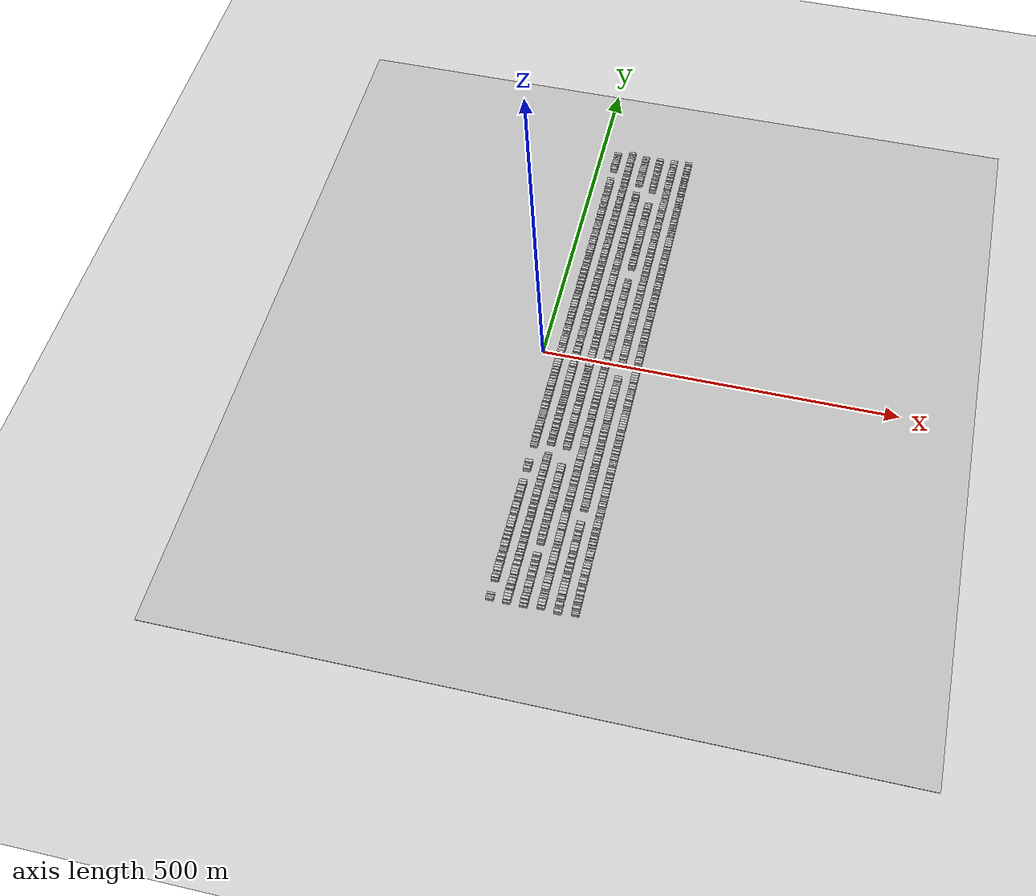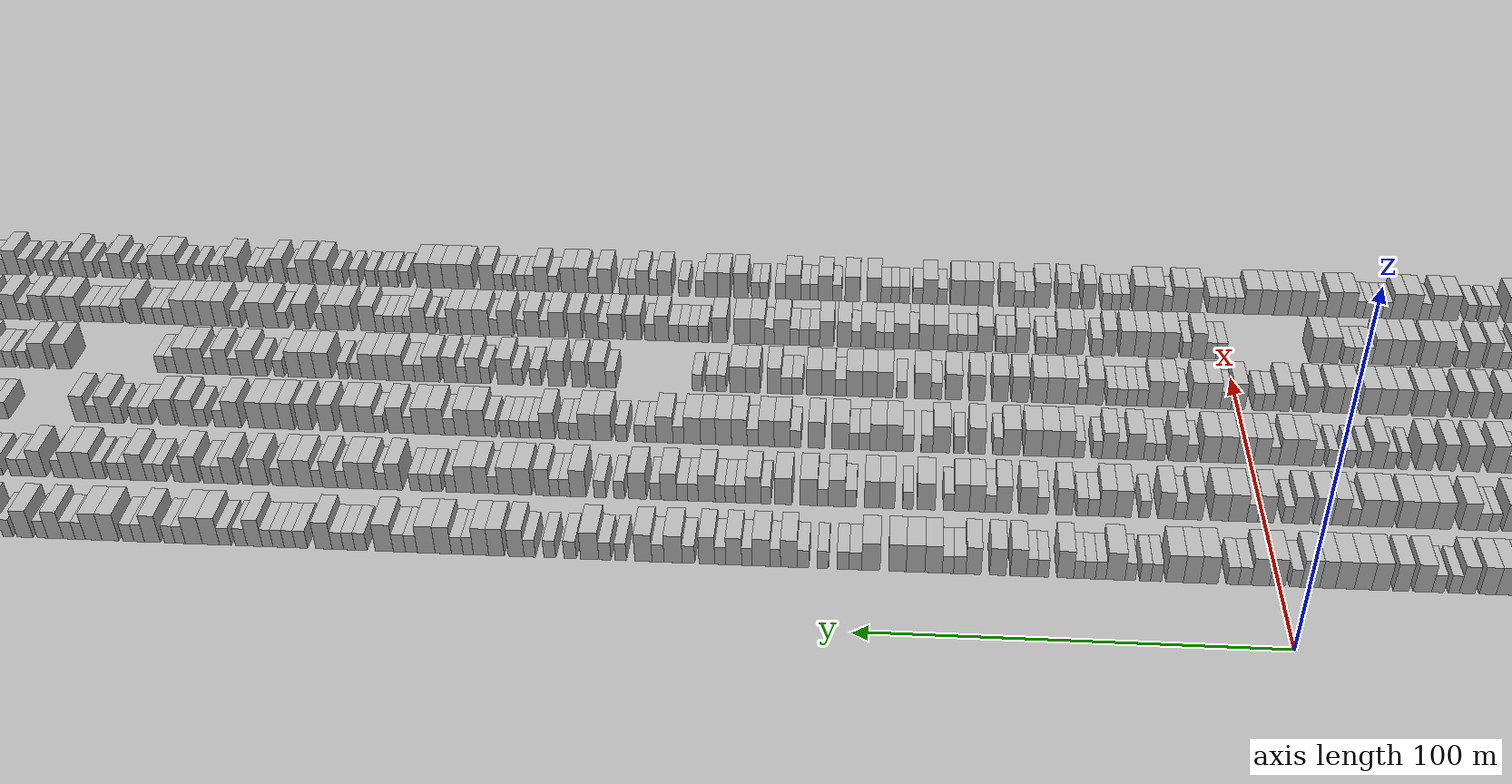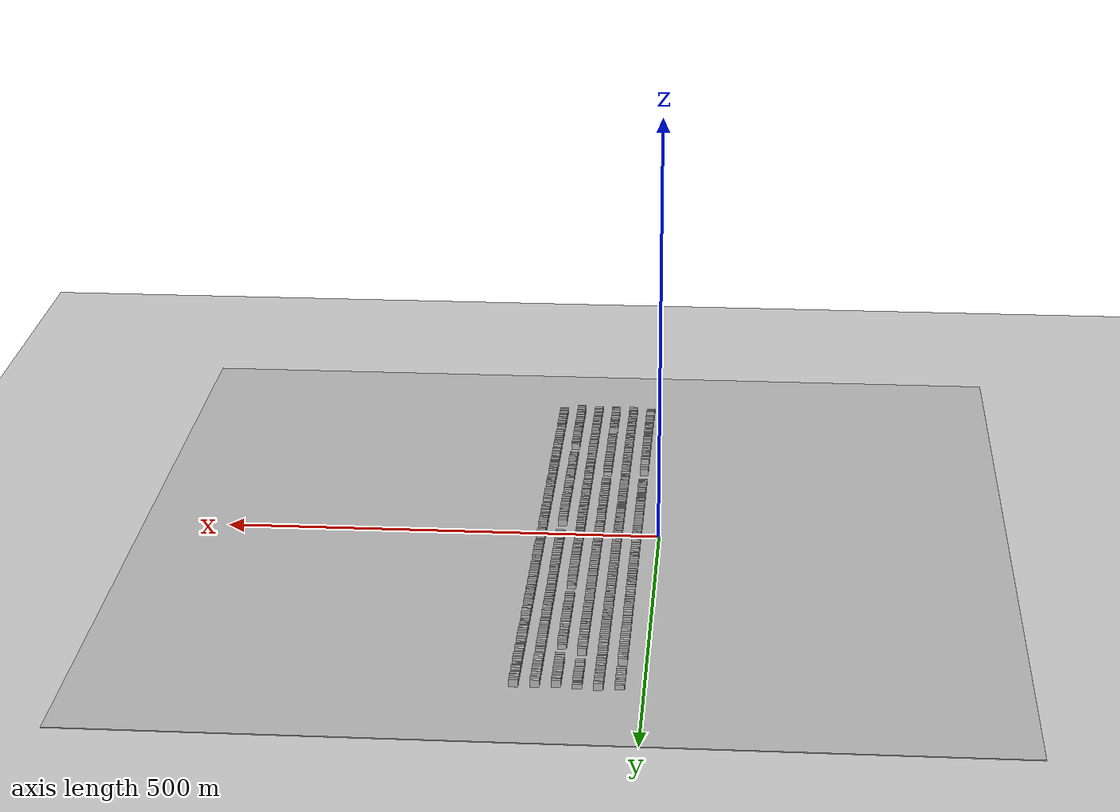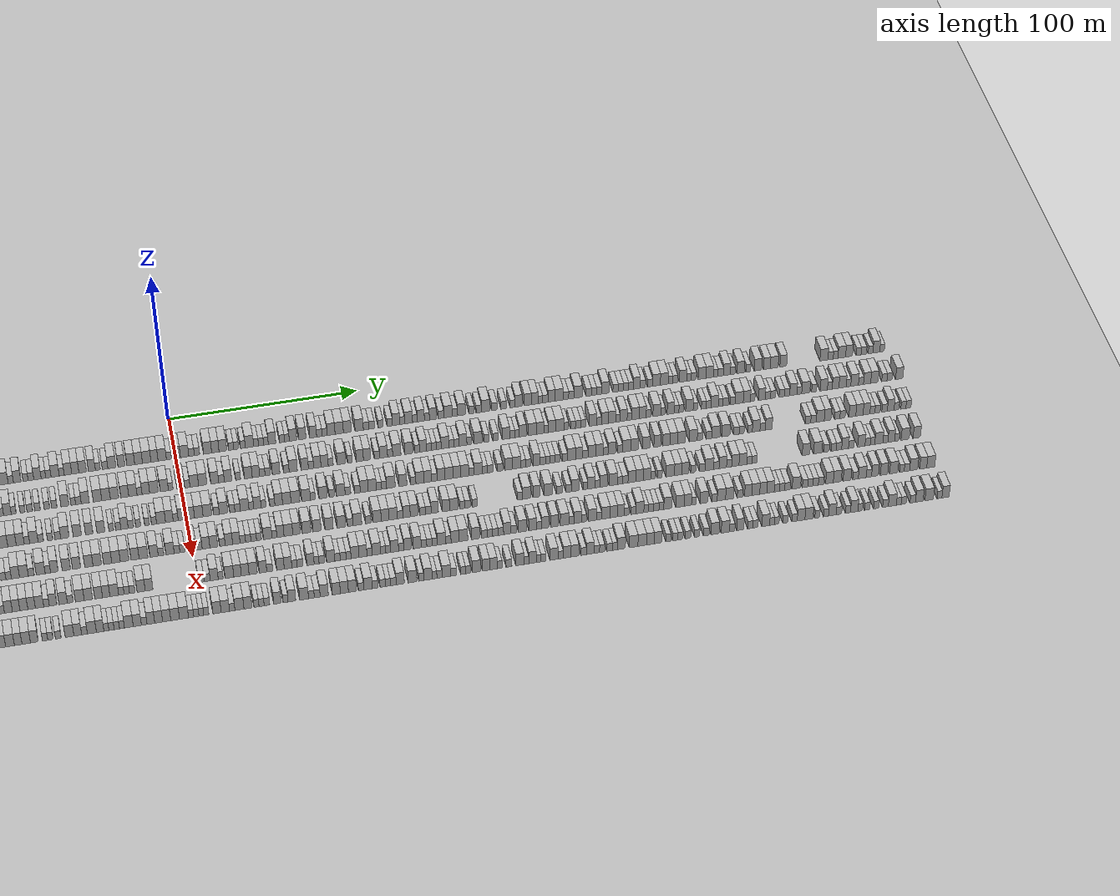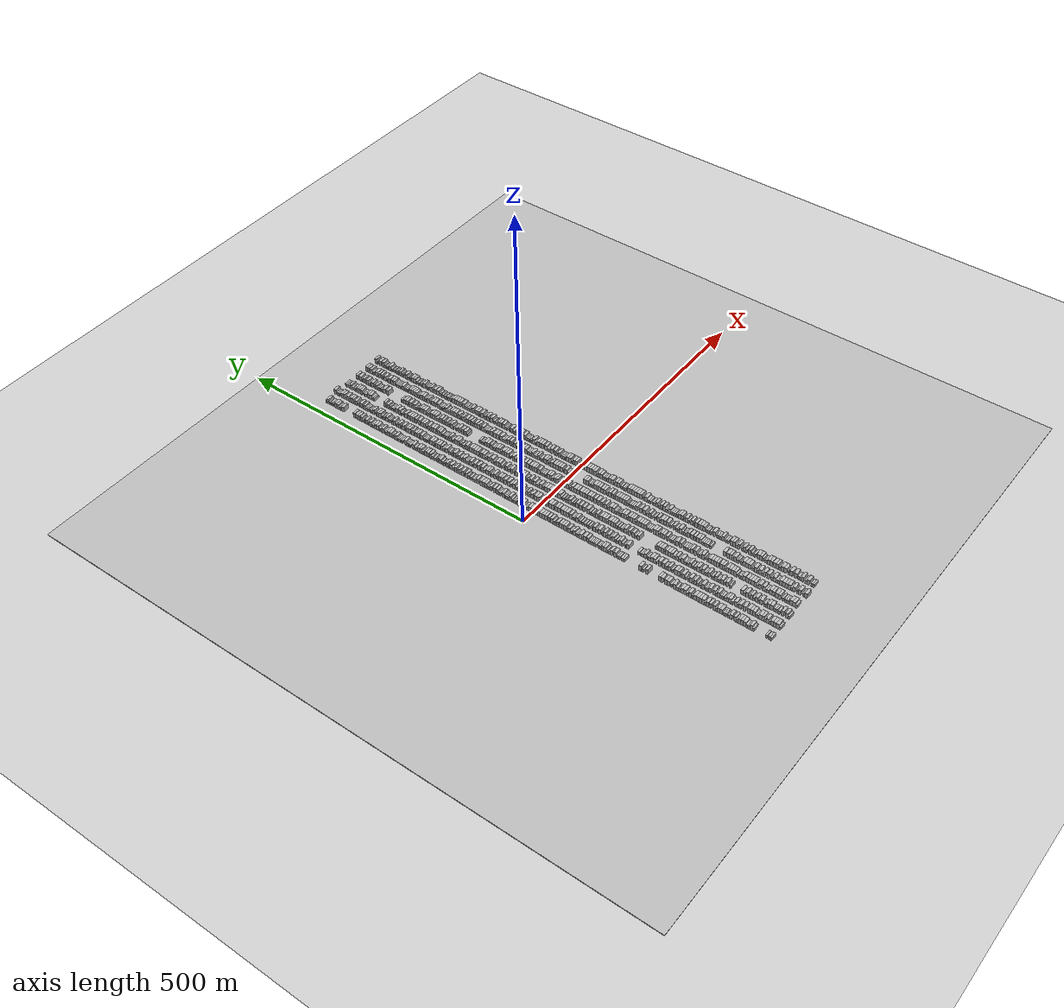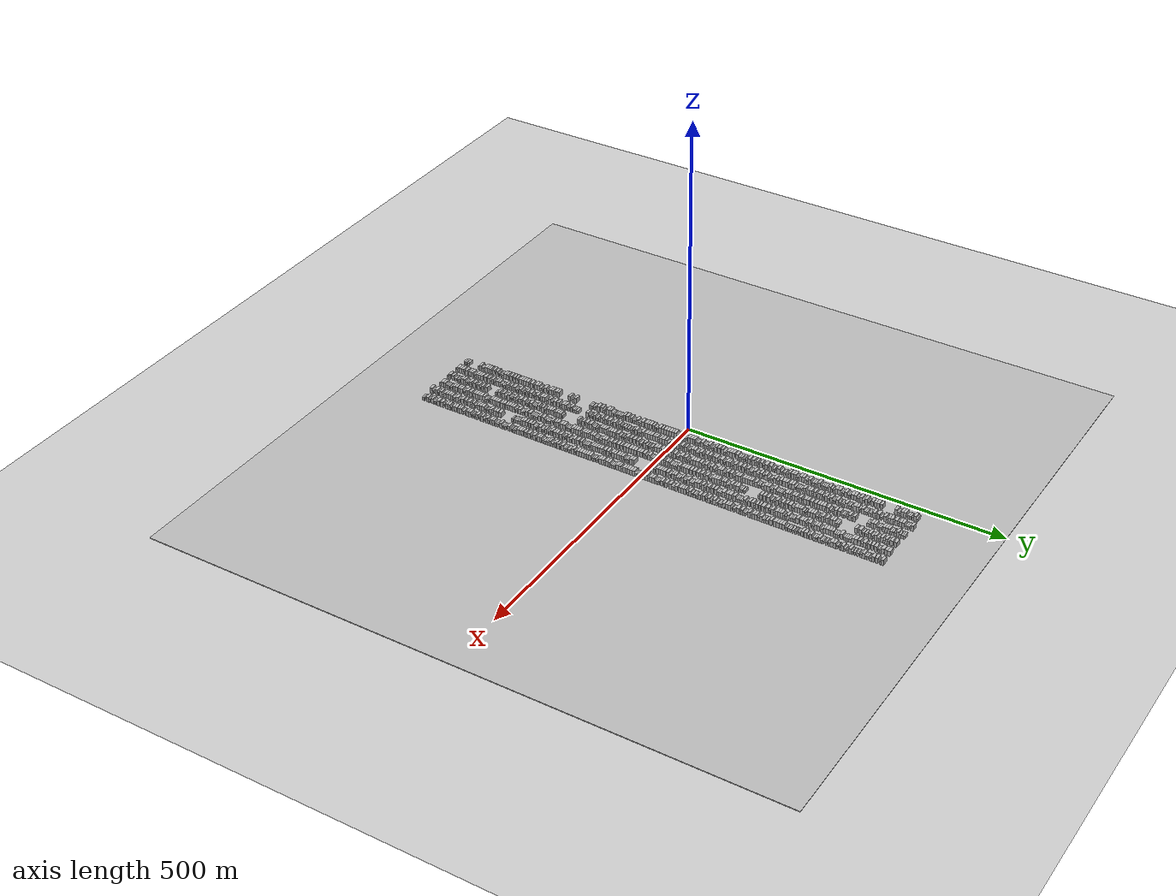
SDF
<?xml version="1.0" encoding="utf-8"?>

<sdf version="1.6">

   <world name="default">

      <gui fullscreen="0">

         <camera name="user_camera">

            <pose>-15 0 4.57585 0 0 0</pose>

            <view_controller>orbit</view_controller>

         </camera>

      </gui>

      <scene>

         <sky>

           <clouds>

             <speed>12</speed>

           </clouds>

         </sky>

         <ambient>0.4 0.4 0.4 1</ambient>

         <background>0.7 0.7 0.7 1</background>

         <shadows>1</shadows>

      </scene>

      <gravity>0 0 -9.8066</gravity>

      <magnetic_field>6e-06 2.3e-05 -4.2e-05</magnetic_field>

      <physics default="0" name="default_physics" type="ode">

         <ode>

            <solver>

               <type>quick</type>

               <iters>10</iters>

               <sor>1.0</sor>

               <use_dynamic_moi_rescaling>0</use_dynamic_moi_rescaling>

            </solver>

            <constraints>

               <cfm>0</cfm>

               <erp>0.2</erp>

               <contact_max_correcting_vel>100</contact_max_correcting_vel>

               <contact_surface_layer>0.001</contact_surface_layer>

            </constraints>

         </ode>

         <max_step_size>0.004</max_step_size>

         <real_time_factor>1</real_time_factor>

         <real_time_update_rate>250</real_time_update_rate>

      </physics>

      <light name="sun" type="directional">

         <cast_shadows>1</cast_shadows>

         <pose>0 0 10 0 0 0</pose>

         <diffuse>0.8 0.8 0.8 1</diffuse>

         <specular>0.2 0.2 0.2 1</specular>

         <attenuation>

            <range>1000</range>

            <constant>0.9</constant>

            <linear>0.01</linear>

            <quadratic>0.001</quadratic>

         </attenuation>

         <direction>-0.5 0.1 -0.9</direction>

      </light>

      <include>

         <name>ground_plane_1</name>

         <uri>model://HANNAS_ground_plane</uri>

         <pose>0 0 0  0 0 0</pose>

      </include>

      <include>

         <name>ground_plane_2</name>

         <uri>model://HANNAS_ground_plane</uri>

         <pose>100 0 0  0 0 0</pose>

      </include>

      <model name="building_1">

         <static>1</static>

         <pose frame="">25.0000 -378.5083 0 0.000000 0.000000 0.000000</pose>

         <link name="link">

            <pose frame="">0 0 3.00 0 0 0</pose>

            <collision name="collision">

               <geometry>

                  <box>

                     <size>10.0000 2.9835 6.0000</size>

                  </box>

               </geometry>

               <max_contacts>10</max_contacts>

               <surface>

                  <contact>

                     <ode/>

                  </contact>

                  <bounce/>

                  <friction>

                     <torsional>

                        <ode/>

                     </torsional>

                     <ode/>

                  </friction>

               </surface>

            </collision>

            <visual name="visual">

               <cast_shadows>0</cast_shadows>

               <geometry>

                  <box>

                     <size>10.0000 2.9835 6.0000</size>

                  </box>

               </geometry>

               <material>

                  <script>

                     <uri>model://HANNAS_wall/materials/scripts</uri>

                     <uri>model://HANNAS_wall/materials/textures</uri>

                     <name>vrc/HANNAS_wall</name>

                  </script>

               </material>

            </visual>

            <self_collide>0</self_collide>

            <enable_wind>0</enable_wind>

            <kinematic>0</kinematic>

         </link>

      </model>

      <model name="building_2">

         <static>1</static>

         <pose frame="">25.0000 -375.6209 0 0.000000 0.000000 0.000000</pose>

         <link name="link">

            <pose frame="">0 0 3.00 0 0 0</pose>

            <collision name="collision">

               <geometry>

                  <box>

                     <size>10.0000 2.7913 6.0000</size>

                  </box>

               </geometry>

               <max_contacts>10</max_contacts>

               <surface>

                  <contact>

                     <ode/>

                  </contact>

                  <bounce/>

                  <friction>

                     <torsional>

                        <ode/>

                     </torsional>

                     <ode/>

                  </friction>

               </surface>

            </collision>

            <visual name="visual">

               <cast_shadows>0</cast_shadows>

               <geometry>

                  <box>

                     <size>10.0000 2.7913 6.0000</size>

                  </box>

               </geometry>

               <material>

                  <script>

                     <uri>model://HANNAS_wall/materials/scripts</uri>

                     <uri>model://HANNAS_wall/materials/textures</uri>

                     <name>vrc/HANNAS_wall</name>

                  </script>

               </material>

            </visual>

            <self_collide>0</self_collide>

            <enable_wind>0</enable_wind>

            <kinematic>0</kinematic>

         </link>

      </model>

      <model name="building_3">

         <static>1</static>

         <pose frame="">25.0000 -371.8338 0 0.000000 0.000000 0.000000</pose>

         <link name="link">

            <pose frame="">0 0 3.00 0 0 0</pose>

            <collision name="collision">

               <geometry>

                  <box>

                     <size>10.0000 2.7829 6.0000</size>

                  </box>

               </geometry>

               <max_contacts>10</max_contacts>

               <surface>

                  <contact>

                     <ode/>

                  </contact>

                  <bounce/>

                  <friction>

                     <torsional>

                        <ode/>

                     </torsional>

                     <ode/>

                  </friction>

               </surface>

            </collision>

            <visual name="visual">

               <cast_shadows>0</cast_shadows>

               <geometry>

                  <box>

                     <size>10.0000 2.7829 6.0000</size>

                  </box>

               </geometry>

               <material>

                  <script>

                     <uri>model://HANNAS_wall/materials/scripts</uri>

                     <uri>model://HANNAS_wall/materials/textures</uri>

                     <name>vrc/HANNAS_wall</name>

                  </script>

               </material>

            </visual>

            <self_collide>0</self_collide>

            <enable_wind>0</enable_wind>

            <kinematic>0</kinematic>

         </link>

      </model>

      <model name="building_4">

         <static>1</static>

         <pose frame="">25.0000 -352.3981 0 0.000000 0.000000 0.000000</pose>

         <link name="link">

            <pose frame="">0 0 3.00 0 0 0</pose>

            <collision name="collision">

               <geometry>

                  <box>

                     <size>10.0000 2.6962 6.0000</size>

                  </box>

               </geometry>

               <max_contacts>10</max_contacts>

               <surface>

                  <contact>

                     <ode/>

                  </contact>

                  <bounce/>

                  <friction>

                     <torsional>

                        <ode/>

                     </torsional>

                     <ode/>

                  </friction>

               </surface>

            </collision>

            <visual name="visual">

               <cast_shadows>0</cast_shadows>

               <geometry>

                  <box>

                     <size>10.0000 2.6962 6.0000</size>

                  </box>

               </geometry>

               <material>

                  <script>

                     <uri>model://HANNAS_wall/materials/scripts</uri>

                     <uri>model://HANNAS_wall/materials/textures</uri>

                     <name>vrc/HANNAS_wall</name>

                  </script>

               </material>

            </visual>

            <self_collide>0</self_collide>

            <enable_wind>0</enable_wind>

            <kinematic>0</kinematic>

         </link>

      </model>

      <model name="building_5">

         <static>1</static>

         <pose frame="">25.0000 -349.1790 0 0.000000 0.000000 0.000000</pose>

         <link name="link">

            <pose frame="">0 0 4.50 0 0 0</pose>

            <collision name="collision">

               <geometry>

                  <box>

                     <size>10.0000 3.7419 9.0000</size>

                  </box>

               </geometry>

               <max_contacts>10</max_contacts>

               <surface>

                  <contact>

                     <ode/>

                  </contact>

                  <bounce/>

                  <friction>

                     <torsional>

                        <ode/>

                     </torsional>

                     <ode/>

                  </friction>

               </surface>

            </collision>

            <visual name="visual">

               <cast_shadows>0</cast_shadows>

               <geometry>

                  <box>

                     <size>10.0000 3.7419 9.0000</size>

                  </box>

               </geometry>

               <material>

                  <script>

                     <uri>model://HANNAS_wall/materials/scripts</uri>

                     <uri>model://HANNAS_wall/materials/textures</uri>

                     <name>vrc/HANNAS_wall</name>

                  </script>

               </material>

            </visual>

            <self_collide>0</self_collide>

            <enable_wind>0</enable_wind>

            <kinematic>0</kinematic>

         </link>

      </model>

      <model name="building_6">

         <static>1</static>

         <pose frame="">25.0000 -345.8332 0 0.000000 0.000000 0.000000</pose>

         <link name="link">

            <pose frame="">0 0 3.00 0 0 0</pose>

            <collision name="collision">

               <geometry>

                  <box>

                     <size>10.0000 2.9496 6.0000</size>

                  </box>

               </geometry>

               <max_contacts>10</max_contacts>

               <surface>

                  <contact>

                     <ode/>

                  </contact>

                  <bounce/>

                  <friction>

                     <torsional>

                        <ode/>

                     </torsional>

                     <ode/>

                  </friction>

               </surface>

            </collision>

            <visual name="visual">

               <cast_shadows>0</cast_shadows>

               <geometry>

                  <box>

                     <size>10.0000 2.9496 6.0000</size>

                  </box>

               </geometry>

               <material>

                  <script>

                     <uri>model://HANNAS_wall/materials/scripts</uri>

                     <uri>model://HANNAS_wall/materials/textures</uri>

                     <name>vrc/HANNAS_wall</name>

                  </script>

               </material>

            </visual>

            <self_collide>0</self_collide>

            <enable_wind>0</enable_wind>

            <kinematic>0</kinematic>

         </link>

      </model>

      <model name="building_7">

         <static>1</static>

         <pose frame="">25.0000 -342.9713 0 0.000000 0.000000 0.000000</pose>

         <link name="link">

            <pose frame="">0 0 3.00 0 0 0</pose>

            <collision name="collision">

               <geometry>

                  <box>

                     <size>10.0000 2.7743 6.0000</size>

                  </box>

               </geometry>

               <max_contacts>10</max_contacts>

               <surface>

                  <contact>

                     <ode/>

                  </contact>

                  <bounce/>

                  <friction>

                     <torsional>

                        <ode/>

                     </torsional>

                     <ode/>

                  </friction>

               </surface>

            </collision>

            <visual name="visual">

               <cast_shadows>0</cast_shadows>

               <geometry>

                  <box>

                     <size>10.0000 2.7743 6.0000</size>

                  </box>

               </geometry>

               <material>

                  <script>

                     <uri>model://HANNAS_wall/materials/scripts</uri>

                     <uri>model://HANNAS_wall/materials/textures</uri>

                     <name>vrc/HANNAS_wall</name>

                  </script>

               </material>

            </visual>

            <self_collide>0</self_collide>

            <enable_wind>0</enable_wind>

            <kinematic>0</kinematic>

         </link>

      </model>

      <model name="building_8">

         <static>1</static>

         <pose frame="">25.0000 -339.3869 0 0.000000 0.000000 0.000000</pose>

         <link name="link">

            <pose frame="">0 0 4.50 0 0 0</pose>

            <collision name="collision">

               <geometry>

                  <box>

                     <size>10.0000 4.3945 9.0000</size>

                  </box>

               </geometry>

               <max_contacts>10</max_contacts>

               <surface>

                  <contact>

                     <ode/>

                  </contact>

                  <bounce/>

                  <friction>

                     <torsional>

                        <ode/>

                     </torsional>

                     <ode/>

                  </friction>

               </surface>

            </collision>

            <visual name="visual">

               <cast_shadows>0</cast_shadows>

               <geometry>

                  <box>

                     <size>10.0000 4.3945 9.0000</size>

                  </box>

               </geometry>

               <material>

                  <script>

                     <uri>model://HANNAS_wall/materials/scripts</uri>

                     <uri>model://HANNAS_wall/materials/textures</uri>

                     <name>vrc/HANNAS_wall</name>

                  </script>

               </material>

            </visual>

            <self_collide>0</self_collide>

            <enable_wind>0</enable_wind>

            <kinematic>0</kinematic>

         </link>

      </model>

      <model name="building_9">

         <static>1</static>

         <pose frame="">25.0000 -335.3621 0 0.000000 0.000000 0.000000</pose>

         <link name="link">

            <pose frame="">0 0 4.50 0 0 0</pose>

            <collision name="collision">

               <geometry>

                  <box>

                     <size>10.0000 3.6552 9.0000</size>

                  </box>

               </geometry>

               <max_contacts>10</max_contacts>

               <surface>

                  <contact>

                     <ode/>

                  </contact>

                  <bounce/>

                  <friction>

                     <torsional>

                        <ode/>

                     </torsional>

                     <ode/>

                  </friction>

               </surface>

            </collision>

            <visual name="visual">

               <cast_shadows>0</cast_shadows>

               <geometry>

                  <box>

                     <size>10.0000 3.6552 9.0000</size>

                  </box>

               </geometry>

               <material>

                  <script>

                     <uri>model://HANNAS_wall/materials/scripts</uri>

                     <uri>model://HANNAS_wall/materials/textures</uri>

                     <name>vrc/HANNAS_wall</name>

                  </script>

               </material>

            </visual>

            <self_collide>0</self_collide>

            <enable_wind>0</enable_wind>

            <kinematic>0</kinematic>

         </link>

      </model>

      <model name="building_10">

         <static>1</static>

         <pose frame="">25.0000 -331.6372 0 0.000000 0.000000 0.000000</pose>

         <link name="link">

            <pose frame="">0 0 4.50 0 0 0</pose>

            <collision name="collision">

               <geometry>

                  <box>

                     <size>10.0000 3.7946 9.0000</size>

                  </box>

               </geometry>

               <max_contacts>10</max_contacts>

               <surface>

                  <contact>

                     <ode/>

                  </contact>

                  <bounce/>

                  <friction>

                     <torsional>

                        <ode/>

                     </torsional>

                     <ode/>

                  </friction>

               </surface>

            </collision>

            <visual name="visual">

               <cast_shadows>0</cast_shadows>

               <geometry>

                  <box>

                     <size>10.0000 3.7946 9.0000</size>

                  </box>

               </geometry>

               <material>

                  <script>

                     <uri>model://HANNAS_wall/materials/scripts</uri>

                     <uri>model://HANNAS_wall/materials/textures</uri>

                     <name>vrc/HANNAS_wall</name>

                  </script>

               </material>

            </visual>

            <self_collide>0</self_collide>

            <enable_wind>0</enable_wind>

            <kinematic>0</kinematic>

         </link>

      </model>

      <model name="building_11">

         <static>1</static>

         <pose frame="">25.0000 -328.2481 0 0.000000 0.000000 0.000000</pose>

         <link name="link">

            <pose frame="">0 0 3.00 0 0 0</pose>

            <collision name="collision">

               <geometry>

                  <box>

                     <size>10.0000 2.9835 6.0000</size>

                  </box>

               </geometry>

               <max_contacts>10</max_contacts>

               <surface>

                  <contact>

                     <ode/>

                  </contact>

                  <bounce/>

                  <friction>

                     <torsional>

                        <ode/>

                     </torsional>

                     <ode/>

                  </friction>

               </surface>

            </collision>

            <visual name="visual">

               <cast_shadows>0</cast_shadows>

               <geometry>

                  <box>

                     <size>10.0000 2.9835 6.0000</size>

                  </box>

               </geometry>

               <material>

                  <script>

                     <uri>model://HANNAS_wall/materials/scripts</uri>

                     <uri>model://HANNAS_wall/materials/textures</uri>

                     <name>vrc/HANNAS_wall</name>

                  </script>

               </material>

            </visual>

            <self_collide>0</self_collide>

            <enable_wind>0</enable_wind>

            <kinematic>0</kinematic>

         </link>

      </model>

      <model name="building_12">

         <static>1</static>

         <pose frame="">25.0000 -324.9343 0 0.000000 0.000000 0.000000</pose>

         <link name="link">

            <pose frame="">0 0 4.50 0 0 0</pose>

            <collision name="collision">

               <geometry>

                  <box>

                     <size>10.0000 3.6440 9.0000</size>

                  </box>

               </geometry>

               <max_contacts>10</max_contacts>

               <surface>

                  <contact>

                     <ode/>

                  </contact>

                  <bounce/>

                  <friction>

                     <torsional>

                        <ode/>

                     </torsional>

                     <ode/>

                  </friction>

               </surface>

            </collision>

            <visual name="visual">

               <cast_shadows>0</cast_shadows>

               <geometry>

                  <box>

                     <size>10.0000 3.6440 9.0000</size>

                  </box>

               </geometry>

               <material>

                  <script>

                     <uri>model://HANNAS_wall/materials/scripts</uri>

                     <uri>model://HANNAS_wall/materials/textures</uri>

                     <name>vrc/HANNAS_wall</name>

                  </script>

               </material>

            </visual>

            <self_collide>0</self_collide>

            <enable_wind>0</enable_wind>

            <kinematic>0</kinematic>

         </link>

      </model>

      <model name="building_13">

         <static>1</static>

         <pose frame="">25.0000 -319.0529 0 0.000000 0.000000 0.000000</pose>

         <link name="link">

            <pose frame="">0 0 4.50 0 0 0</pose>

            <collision name="collision">

               <geometry>

                  <box>

                     <size>10.0000 4.1188 9.0000</size>

                  </box>

               </geometry>

               <max_contacts>10</max_contacts>

               <surface>

                  <contact>

                     <ode/>

                  </contact>

                  <bounce/>

                  <friction>

                     <torsional>

                        <ode/>

                     </torsional>

                     <ode/>

                  </friction>

               </surface>

            </collision>

            <visual name="visual">

               <cast_shadows>0</cast_shadows>

               <geometry>

                  <box>

                     <size>10.0000 4.1188 9.0000</size>

                  </box>

               </geometry>

               <material>

                  <script>

                     <uri>model://HANNAS_wall/materials/scripts</uri>

                     <uri>model://HANNAS_wall/materials/textures</uri>

                     <name>vrc/HANNAS_wall</name>

                  </script>

               </material>

            </visual>

            <self_collide>0</self_collide>

            <enable_wind>0</enable_wind>

            <kinematic>0</kinematic>

         </link>

      </model>

      <model name="building_14">

         <static>1</static>

         <pose frame="">25.0000 -315.7018 0 0.000000 0.000000 0.000000</pose>

         <link name="link">

            <pose frame="">0 0 3.00 0 0 0</pose>

            <collision name="collision">

               <geometry>

                  <box>

                     <size>10.0000 2.5833 6.0000</size>

                  </box>

               </geometry>

               <max_contacts>10</max_contacts>

               <surface>

                  <contact>

                     <ode/>

                  </contact>

                  <bounce/>

                  <friction>

                     <torsional>

                        <ode/>

                     </torsional>

                     <ode/>

                  </friction>

               </surface>

            </collision>

            <visual name="visual">

               <cast_shadows>0</cast_shadows>

               <geometry>

                  <box>

                     <size>10.0000 2.5833 6.0000</size>

                  </box>

               </geometry>

               <material>

                  <script>

                     <uri>model://HANNAS_wall/materials/scripts</uri>

                     <uri>model://HANNAS_wall/materials/textures</uri>

                     <name>vrc/HANNAS_wall</name>

                  </script>

               </material>

            </visual>

            <self_collide>0</self_collide>

            <enable_wind>0</enable_wind>

            <kinematic>0</kinematic>

         </link>

      </model>

      <model name="building_15">

         <static>1</static>

         <pose frame="">25.0000 -311.0761 0 0.000000 0.000000 0.000000</pose>

         <link name="link">

            <pose frame="">0 0 3.00 0 0 0</pose>

            <collision name="collision">

               <geometry>

                  <box>

                     <size>10.0000 2.6683 6.0000</size>

                  </box>

               </geometry>

               <max_contacts>10</max_contacts>

               <surface>

                  <contact>

                     <ode/>

                  </contact>

                  <bounce/>

                  <friction>

                     <torsional>

                        <ode/>

                     </torsional>

                     <ode/>

                  </friction>

               </surface>

            </collision>

            <visual name="visual">

               <cast_shadows>0</cast_shadows>

               <geometry>

                  <box>

                     <size>10.0000 2.6683 6.0000</size>

                  </box>

               </geometry>

               <material>

                  <script>

                     <uri>model://HANNAS_wall/materials/scripts</uri>

                     <uri>model://HANNAS_wall/materials/textures</uri>

                     <name>vrc/HANNAS_wall</name>

                  </script>

               </material>

            </visual>

            <self_collide>0</self_collide>

            <enable_wind>0</enable_wind>

            <kinematic>0</kinematic>

         </link>

      </model>

      <model name="building_16">

         <static>1</static>

         <pose frame="">25.0000 -308.5085 0 0.000000 0.000000 0.000000</pose>

         <link name="link">

            <pose frame="">0 0 3.00 0 0 0</pose>

            <collision name="collision">

               <geometry>

                  <box>

                     <size>10.0000 2.4668 6.0000</size>

                  </box>

               </geometry>

               <max_contacts>10</max_contacts>

               <surface>

                  <contact>

                     <ode/>

                  </contact>

                  <bounce/>

                  <friction>

                     <torsional>

                        <ode/>

                     </torsional>

                     <ode/>

                  </friction>

               </surface>

            </collision>

            <visual name="visual">

               <cast_shadows>0</cast_shadows>

               <geometry>

                  <box>

                     <size>10.0000 2.4668 6.0000</size>

                  </box>

               </geometry>

               <material>

                  <script>

                     <uri>model://HANNAS_wall/materials/scripts</uri>

                     <uri>model://HANNAS_wall/materials/textures</uri>

                     <name>vrc/HANNAS_wall</name>

                  </script>

               </material>

            </visual>

            <self_collide>0</self_collide>

            <enable_wind>0</enable_wind>

            <kinematic>0</kinematic>

         </link>

      </model>

      <model name="building_17">

         <static>1</static>

         <pose frame="">25.0000 -304.1616 0 0.000000 0.000000 0.000000</pose>

         <link name="link">

            <pose frame="">0 0 4.50 0 0 0</pose>

            <collision name="collision">

               <geometry>

                  <box>

                     <size>10.0000 4.2270 9.0000</size>

                  </box>

               </geometry>

               <max_contacts>10</max_contacts>

               <surface>

                  <contact>

                     <ode/>

                  </contact>

                  <bounce/>

                  <friction>

                     <torsional>

                        <ode/>

                     </torsional>

                     <ode/>

                  </friction>

               </surface>

            </collision>

            <visual name="visual">

               <cast_shadows>0</cast_shadows>

               <geometry>

                  <box>

                     <size>10.0000 4.2270 9.0000</size>

                  </box>

               </geometry>

               <material>

                  <script>

                     <uri>model://HANNAS_wall/materials/scripts</uri>

                     <uri>model://HANNAS_wall/materials/textures</uri>

                     <name>vrc/HANNAS_wall</name>

                  </script>

               </material>

            </visual>

            <self_collide>0</self_collide>

            <enable_wind>0</enable_wind>

            <kinematic>0</kinematic>

         </link>

      </model>

      <model name="building_18">

         <static>1</static>

         <pose frame="">25.0000 -300.1236 0 0.000000 0.000000 0.000000</pose>

         <link name="link">

            <pose frame="">0 0 4.50 0 0 0</pose>

            <collision name="collision">

               <geometry>

                  <box>

                     <size>10.0000 3.8491 9.0000</size>

                  </box>

               </geometry>

               <max_contacts>10</max_contacts>

               <surface>

                  <contact>

                     <ode/>

                  </contact>

                  <bounce/>

                  <friction>

                     <torsional>

                        <ode/>

                     </torsional>

                     <ode/>

                  </friction>

               </surface>

            </collision>

            <visual name="visual">

               <cast_shadows>0</cast_shadows>

               <geometry>

                  <box>

                     <size>10.0000 3.8491 9.0000</size>

                  </box>

               </geometry>

               <material>

                  <script>

                     <uri>model://HANNAS_wall/materials/scripts</uri>

                     <uri>model://HANNAS_wall/materials/textures</uri>

                     <name>vrc/HANNAS_wall</name>

                  </script>

               </material>

            </visual>

            <self_collide>0</self_collide>

            <enable_wind>0</enable_wind>

            <kinematic>0</kinematic>

         </link>

      </model>

      <model name="building_19">

         <static>1</static>

         <pose frame="">25.0000 -296.8605 0 0.000000 0.000000 0.000000</pose>

         <link name="link">

            <pose frame="">0 0 3.00 0 0 0</pose>

            <collision name="collision">

               <geometry>

                  <box>

                     <size>10.0000 2.6770 6.0000</size>

                  </box>

               </geometry>

               <max_contacts>10</max_contacts>

               <surface>

                  <contact>

                     <ode/>

                  </contact>

                  <bounce/>

                  <friction>

                     <torsional>

                        <ode/>

                     </torsional>

                     <ode/>

                  </friction>

               </surface>

            </collision>

            <visual name="visual">

               <cast_shadows>0</cast_shadows>

               <geometry>

                  <box>

                     <size>10.0000 2.6770 6.0000</size>

                  </box>

               </geometry>

               <material>

                  <script>

                     <uri>model://HANNAS_wall/materials/scripts</uri>

                     <uri>model://HANNAS_wall/materials/textures</uri>

                     <name>vrc/HANNAS_wall</name>

                  </script>

               </material>

            </visual>

            <self_collide>0</self_collide>

            <enable_wind>0</enable_wind>

            <kinematic>0</kinematic>

         </link>

      </model>

      <model name="building_20">

         <static>1</static>

         <pose frame="">25.0000 -293.5178 0 0.000000 0.000000 0.000000</pose>

         <link name="link">

            <pose frame="">0 0 4.50 0 0 0</pose>

            <collision name="collision">

               <geometry>

                  <box>

                     <size>10.0000 4.0084 9.0000</size>

                  </box>

               </geometry>

               <max_contacts>10</max_contacts>

               <surface>

                  <contact>

                     <ode/>

                  </contact>

                  <bounce/>

                  <friction>

                     <torsional>

                        <ode/>

                     </torsional>

                     <ode/>

                  </friction>

               </surface>

            </collision>

            <visual name="visual">

               <cast_shadows>0</cast_shadows>

               <geometry>

                  <box>

                     <size>10.0000 4.0084 9.0000</size>

                  </box>

               </geometry>

               <material>

                  <script>

                     <uri>model://HANNAS_wall/materials/scripts</uri>

                     <uri>model://HANNAS_wall/materials/textures</uri>

                     <name>vrc/HANNAS_wall</name>

                  </script>

               </material>

            </visual>

            <self_collide>0</self_collide>

            <enable_wind>0</enable_wind>

            <kinematic>0</kinematic>

         </link>

      </model>

      <model name="building_21">

         <static>1</static>

         <pose frame="">25.0000 -287.6362 0 0.000000 0.000000 0.000000</pose>

         <link name="link">

            <pose frame="">0 0 4.50 0 0 0</pose>

            <collision name="collision">

               <geometry>

                  <box>

                     <size>10.0000 3.7547 9.0000</size>

                  </box>

               </geometry>

               <max_contacts>10</max_contacts>

               <surface>

                  <contact>

                     <ode/>

                  </contact>

                  <bounce/>

                  <friction>

                     <torsional>

                        <ode/>

                     </torsional>

                     <ode/>

                  </friction>

               </surface>

            </collision>

            <visual name="visual">

               <cast_shadows>0</cast_shadows>

               <geometry>

                  <box>

                     <size>10.0000 3.7547 9.0000</size>

                  </box>

               </geometry>

               <material>

                  <script>

                     <uri>model://HANNAS_wall/materials/scripts</uri>

                     <uri>model://HANNAS_wall/materials/textures</uri>

                     <name>vrc/HANNAS_wall</name>

                  </script>

               </material>

            </visual>

            <self_collide>0</self_collide>

            <enable_wind>0</enable_wind>

            <kinematic>0</kinematic>

         </link>

      </model>

      <model name="building_22">

         <static>1</static>

         <pose frame="">25.0000 -282.9233 0 0.000000 0.000000 0.000000</pose>

         <link name="link">

            <pose frame="">0 0 4.50 0 0 0</pose>

            <collision name="collision">

               <geometry>

                  <box>

                     <size>10.0000 3.6711 9.0000</size>

                  </box>

               </geometry>

               <max_contacts>10</max_contacts>

               <surface>

                  <contact>

                     <ode/>

                  </contact>

                  <bounce/>

                  <friction>

                     <torsional>

                        <ode/>

                     </torsional>

                     <ode/>

                  </friction>

               </surface>

            </collision>

            <visual name="visual">

               <cast_shadows>0</cast_shadows>

               <geometry>

                  <box>

                     <size>10.0000 3.6711 9.0000</size>

                  </box>

               </geometry>

               <material>

                  <script>

                     <uri>model://HANNAS_wall/materials/scripts</uri>

                     <uri>model://HANNAS_wall/materials/textures</uri>

                     <name>vrc/HANNAS_wall</name>

                  </script>

               </material>

            </visual>

            <self_collide>0</self_collide>

            <enable_wind>0</enable_wind>

            <kinematic>0</kinematic>

         </link>

      </model>

      <model name="building_23">

         <static>1</static>

         <pose frame="">25.0000 -279.8532 0 0.000000 0.000000 0.000000</pose>

         <link name="link">

            <pose frame="">0 0 3.00 0 0 0</pose>

            <collision name="collision">

               <geometry>

                  <box>

                     <size>10.0000 2.4691 6.0000</size>

                  </box>

               </geometry>

               <max_contacts>10</max_contacts>

               <surface>

                  <contact>

                     <ode/>

                  </contact>

                  <bounce/>

                  <friction>

                     <torsional>

                        <ode/>

                     </torsional>

                     <ode/>

                  </friction>

               </surface>

            </collision>

            <visual name="visual">

               <cast_shadows>0</cast_shadows>

               <geometry>

                  <box>

                     <size>10.0000 2.4691 6.0000</size>

                  </box>

               </geometry>

               <material>

                  <script>

                     <uri>model://HANNAS_wall/materials/scripts</uri>

                     <uri>model://HANNAS_wall/materials/textures</uri>

                     <name>vrc/HANNAS_wall</name>

                  </script>

               </material>

            </visual>

            <self_collide>0</self_collide>

            <enable_wind>0</enable_wind>

            <kinematic>0</kinematic>

         </link>

      </model>

      <model name="building_24">

         <static>1</static>

         <pose frame="">25.0000 -276.4193 0 0.000000 0.000000 0.000000</pose>

         <link name="link">

            <pose frame="">0 0 4.50 0 0 0</pose>

            <collision name="collision">

               <geometry>

                  <box>

                     <size>10.0000 4.3988 9.0000</size>

                  </box>

               </geometry>

               <max_contacts>10</max_contacts>

               <surface>

                  <contact>

                     <ode/>

                  </contact>

                  <bounce/>

                  <friction>

                     <torsional>

                        <ode/>

                     </torsional>

                     <ode/>

                  </friction>

               </surface>

            </collision>

            <visual name="visual">

               <cast_shadows>0</cast_shadows>

               <geometry>

                  <box>

                     <size>10.0000 4.3988 9.0000</size>

                  </box>

               </geometry>

               <material>

                  <script>

                     <uri>model://HANNAS_wall/materials/scripts</uri>

                     <uri>model://HANNAS_wall/materials/textures</uri>

                     <name>vrc/HANNAS_wall</name>

                  </script>

               </material>

            </visual>

            <self_collide>0</self_collide>

            <enable_wind>0</enable_wind>

            <kinematic>0</kinematic>

         </link>

      </model>

      <model name="building_25">

         <static>1</static>

         <pose frame="">25.0000 -272.3590 0 0.000000 0.000000 0.000000</pose>

         <link name="link">

            <pose frame="">0 0 4.50 0 0 0</pose>

            <collision name="collision">

               <geometry>

                  <box>

                     <size>10.0000 3.7218 9.0000</size>

                  </box>

               </geometry>

               <max_contacts>10</max_contacts>

               <surface>

                  <contact>

                     <ode/>

                  </contact>

                  <bounce/>

                  <friction>

                     <torsional>

                        <ode/>

                     </torsional>

                     <ode/>

                  </friction>

               </surface>

            </collision>

            <visual name="visual">

               <cast_shadows>0</cast_shadows>

               <geometry>

                  <box>

                     <size>10.0000 3.7218 9.0000</size>

                  </box>

               </geometry>

               <material>

                  <script>

                     <uri>model://HANNAS_wall/materials/scripts</uri>

                     <uri>model://HANNAS_wall/materials/textures</uri>

                     <name>vrc/HANNAS_wall</name>

                  </script>

               </material>

            </visual>

            <self_collide>0</self_collide>

            <enable_wind>0</enable_wind>

            <kinematic>0</kinematic>

         </link>

      </model>

      <model name="building_26">

         <static>1</static>

         <pose frame="">25.0000 -268.4085 0 0.000000 0.000000 0.000000</pose>

         <link name="link">

            <pose frame="">0 0 4.50 0 0 0</pose>

            <collision name="collision">

               <geometry>

                  <box>

                     <size>10.0000 4.1792 9.0000</size>

                  </box>

               </geometry>

               <max_contacts>10</max_contacts>

               <surface>

                  <contact>

                     <ode/>

                  </contact>

                  <bounce/>

                  <friction>

                     <torsional>

                        <ode/>

                     </torsional>

                     <ode/>

                  </friction>

               </surface>

            </collision>

            <visual name="visual">

               <cast_shadows>0</cast_shadows>

               <geometry>

                  <box>

                     <size>10.0000 4.1792 9.0000</size>

                  </box>

               </geometry>

               <material>

                  <script>

                     <uri>model://HANNAS_wall/materials/scripts</uri>

                     <uri>model://HANNAS_wall/materials/textures</uri>

                     <name>vrc/HANNAS_wall</name>

                  </script>

               </material>

            </visual>

            <self_collide>0</self_collide>

            <enable_wind>0</enable_wind>

            <kinematic>0</kinematic>

         </link>

      </model>

      <model name="building_27">

         <static>1</static>

         <pose frame="">25.0000 -264.0996 0 0.000000 0.000000 0.000000</pose>

         <link name="link">

            <pose frame="">0 0 4.50 0 0 0</pose>

            <collision name="collision">

               <geometry>

                  <box>

                     <size>10.0000 4.4385 9.0000</size>

                  </box>

               </geometry>

               <max_contacts>10</max_contacts>

               <surface>

                  <contact>

                     <ode/>

                  </contact>

                  <bounce/>

                  <friction>

                     <torsional>

                        <ode/>

                     </torsional>

                     <ode/>

                  </friction>

               </surface>

            </collision>

            <visual name="visual">

               <cast_shadows>0</cast_shadows>

               <geometry>

                  <box>

                     <size>10.0000 4.4385 9.0000</size>

                  </box>

               </geometry>

               <material>

                  <script>

                     <uri>model://HANNAS_wall/materials/scripts</uri>

                     <uri>model://HANNAS_wall/materials/textures</uri>

                     <name>vrc/HANNAS_wall</name>

                  </script>

               </material>

            </visual>

            <self_collide>0</self_collide>

            <enable_wind>0</enable_wind>

            <kinematic>0</kinematic>

         </link>

      </model>

      <model name="building_28">

         <static>1</static>

         <pose frame="">25.0000 -260.6279 0 0.000000 0.000000 0.000000</pose>

         <link name="link">

            <pose frame="">0 0 3.00 0 0 0</pose>

            <collision name="collision">

               <geometry>

                  <box>

                     <size>10.0000 2.5049 6.0000</size>

                  </box>

               </geometry>

               <max_contacts>10</max_contacts>

               <surface>

                  <contact>

                     <ode/>

                  </contact>

                  <bounce/>

                  <friction>

                     <torsional>

                        <ode/>

                     </torsional>

                     <ode/>

                  </friction>

               </surface>

            </collision>

            <visual name="visual">

               <cast_shadows>0</cast_shadows>

               <geometry>

                  <box>

                     <size>10.0000 2.5049 6.0000</size>

                  </box>

               </geometry>

               <material>

                  <script>

                     <uri>model://HANNAS_wall/materials/scripts</uri>

                     <uri>model://HANNAS_wall/materials/textures</uri>

                     <name>vrc/HANNAS_wall</name>

                  </script>

               </material>

            </visual>

            <self_collide>0</self_collide>

            <enable_wind>0</enable_wind>

            <kinematic>0</kinematic>

         </link>

      </model>

      <model name="building_29">

         <static>1</static>

         <pose frame="">25.0000 -256.2432 0 0.000000 0.000000 0.000000</pose>

         <link name="link">

            <pose frame="">0 0 4.50 0 0 0</pose>

            <collision name="collision">

               <geometry>

                  <box>

                     <size>10.0000 4.2644 9.0000</size>

                  </box>

               </geometry>

               <max_contacts>10</max_contacts>

               <surface>

                  <contact>

                     <ode/>

                  </contact>

                  <bounce/>

                  <friction>

                     <torsional>

                        <ode/>

                     </torsional>

                     <ode/>

                  </friction>

               </surface>

            </collision>

            <visual name="visual">

               <cast_shadows>0</cast_shadows>

               <geometry>

                  <box>

                     <size>10.0000 4.2644 9.0000</size>

                  </box>

               </geometry>

               <material>

                  <script>

                     <uri>model://HANNAS_wall/materials/scripts</uri>

                     <uri>model://HANNAS_wall/materials/textures</uri>

                     <name>vrc/HANNAS_wall</name>

                  </script>

               </material>

            </visual>

            <self_collide>0</self_collide>

            <enable_wind>0</enable_wind>

            <kinematic>0</kinematic>

         </link>

      </model>

      <model name="building_30">

         <static>1</static>

         <pose frame="">25.0000 -251.7612 0 0.000000 0.000000 0.000000</pose>

         <link name="link">

            <pose frame="">0 0 3.00 0 0 0</pose>

            <collision name="collision">

               <geometry>

                  <box>

                     <size>10.0000 2.6998 6.0000</size>

                  </box>

               </geometry>

               <max_contacts>10</max_contacts>

               <surface>

                  <contact>

                     <ode/>

                  </contact>

                  <bounce/>

                  <friction>

                     <torsional>

                        <ode/>

                     </torsional>

                     <ode/>

                  </friction>

               </surface>

            </collision>

            <visual name="visual">

               <cast_shadows>0</cast_shadows>

               <geometry>

                  <box>

                     <size>10.0000 2.6998 6.0000</size>

                  </box>

               </geometry>

               <material>

                  <script>

                     <uri>model://HANNAS_wall/materials/scripts</uri>

                     <uri>model://HANNAS_wall/materials/textures</uri>

                     <name>vrc/HANNAS_wall</name>

                  </script>

               </material>

            </visual>

            <self_collide>0</self_collide>

            <enable_wind>0</enable_wind>

            <kinematic>0</kinematic>

         </link>

      </model>

      <model name="building_31">

         <static>1</static>

         <pose frame="">25.0000 -248.2509 0 0.000000 0.000000 0.000000</pose>

         <link name="link">

            <pose frame="">0 0 4.50 0 0 0</pose>

            <collision name="collision">

               <geometry>

                  <box>

                     <size>10.0000 4.3207 9.0000</size>

                  </box>

               </geometry>

               <max_contacts>10</max_contacts>

               <surface>

                  <contact>

                     <ode/>

                  </contact>

                  <bounce/>

                  <friction>

                     <torsional>

                        <ode/>

                     </torsional>

                     <ode/>

                  </friction>

               </surface>

            </collision>

            <visual name="visual">

               <cast_shadows>0</cast_shadows>

               <geometry>

                  <box>

                     <size>10.0000 4.3207 9.0000</size>

                  </box>

               </geometry>

               <material>

                  <script>

                     <uri>model://HANNAS_wall/materials/scripts</uri>

                     <uri>model://HANNAS_wall/materials/textures</uri>

                     <name>vrc/HANNAS_wall</name>

                  </script>

               </material>

            </visual>

            <self_collide>0</self_collide>

            <enable_wind>0</enable_wind>

            <kinematic>0</kinematic>

         </link>

      </model>

      <model name="building_32">

         <static>1</static>

         <pose frame="">25.0000 -244.0177 0 0.000000 0.000000 0.000000</pose>

         <link name="link">

            <pose frame="">0 0 4.50 0 0 0</pose>

            <collision name="collision">

               <geometry>

                  <box>

                     <size>10.0000 4.1457 9.0000</size>

                  </box>

               </geometry>

               <max_contacts>10</max_contacts>

               <surface>

                  <contact>

                     <ode/>

                  </contact>

                  <bounce/>

                  <friction>

                     <torsional>

                        <ode/>

                     </torsional>

                     <ode/>

                  </friction>

               </surface>

            </collision>

            <visual name="visual">

               <cast_shadows>0</cast_shadows>

               <geometry>

                  <box>

                     <size>10.0000 4.1457 9.0000</size>

                  </box>

               </geometry>

               <material>

                  <script>

                     <uri>model://HANNAS_wall/materials/scripts</uri>

                     <uri>model://HANNAS_wall/materials/textures</uri>

                     <name>vrc/HANNAS_wall</name>

                  </script>

               </material>

            </visual>

            <self_collide>0</self_collide>

            <enable_wind>0</enable_wind>

            <kinematic>0</kinematic>

         </link>

      </model>

      <model name="building_33">

         <static>1</static>

         <pose frame="">25.0000 -240.5104 0 0.000000 0.000000 0.000000</pose>

         <link name="link">

            <pose frame="">0 0 3.00 0 0 0</pose>

            <collision name="collision">

               <geometry>

                  <box>

                     <size>10.0000 2.8689 6.0000</size>

                  </box>

               </geometry>

               <max_contacts>10</max_contacts>

               <surface>

                  <contact>

                     <ode/>

                  </contact>

                  <bounce/>

                  <friction>

                     <torsional>

                        <ode/>

                     </torsional>

                     <ode/>

                  </friction>

               </surface>

            </collision>

            <visual name="visual">

               <cast_shadows>0</cast_shadows>

               <geometry>

                  <box>

                     <size>10.0000 2.8689 6.0000</size>

                  </box>

               </geometry>

               <material>

                  <script>

                     <uri>model://HANNAS_wall/materials/scripts</uri>

                     <uri>model://HANNAS_wall/materials/textures</uri>

                     <name>vrc/HANNAS_wall</name>

                  </script>

               </material>

            </visual>

            <self_collide>0</self_collide>

            <enable_wind>0</enable_wind>

            <kinematic>0</kinematic>

         </link>

      </model>

      <model name="building_34">

         <static>1</static>

         <pose frame="">25.0000 -236.6710 0 0.000000 0.000000 0.000000</pose>

         <link name="link">

            <pose frame="">0 0 3.00 0 0 0</pose>

            <collision name="collision">

               <geometry>

                  <box>

                     <size>10.0000 2.8099 6.0000</size>

                  </box>

               </geometry>

               <max_contacts>10</max_contacts>

               <surface>

                  <contact>

                     <ode/>

                  </contact>

                  <bounce/>

                  <friction>

                     <torsional>

                        <ode/>

                     </torsional>

                     <ode/>

                  </friction>

               </surface>

            </collision>

            <visual name="visual">

               <cast_shadows>0</cast_shadows>

               <geometry>

                  <box>

                     <size>10.0000 2.8099 6.0000</size>

                  </box>

               </geometry>

               <material>

                  <script>

                     <uri>model://HANNAS_wall/materials/scripts</uri>

                     <uri>model://HANNAS_wall/materials/textures</uri>

                     <name>vrc/HANNAS_wall</name>

                  </script>

               </material>

            </visual>

            <self_collide>0</self_collide>

            <enable_wind>0</enable_wind>

            <kinematic>0</kinematic>

         </link>

      </model>

      <model name="building_35">

         <static>1</static>

         <pose frame="">25.0000 -232.0984 0 0.000000 0.000000 0.000000</pose>

         <link name="link">

            <pose frame="">0 0 4.50 0 0 0</pose>

            <collision name="collision">

               <geometry>

                  <box>

                     <size>10.0000 4.3355 9.0000</size>

                  </box>

               </geometry>

               <max_contacts>10</max_contacts>

               <surface>

                  <contact>

                     <ode/>

                  </contact>

                  <bounce/>

                  <friction>

                     <torsional>

                        <ode/>

                     </torsional>

                     <ode/>

                  </friction>

               </surface>

            </collision>

            <visual name="visual">

               <cast_shadows>0</cast_shadows>

               <geometry>

                  <box>

                     <size>10.0000 4.3355 9.0000</size>

                  </box>

               </geometry>

               <material>

                  <script>

                     <uri>model://HANNAS_wall/materials/scripts</uri>

                     <uri>model://HANNAS_wall/materials/textures</uri>

                     <name>vrc/HANNAS_wall</name>

                  </script>

               </material>

            </visual>

            <self_collide>0</self_collide>

            <enable_wind>0</enable_wind>

            <kinematic>0</kinematic>

         </link>

      </model>

      <model name="building_36">

         <static>1</static>

         <pose frame="">25.0000 -227.4317 0 0.000000 0.000000 0.000000</pose>

         <link name="link">

            <pose frame="">0 0 3.00 0 0 0</pose>

            <collision name="collision">

               <geometry>

                  <box>

                     <size>10.0000 2.9977 6.0000</size>

                  </box>

               </geometry>

               <max_contacts>10</max_contacts>

               <surface>

                  <contact>

                     <ode/>

                  </contact>

                  <bounce/>

                  <friction>

                     <torsional>

                        <ode/>

                     </torsional>

                     <ode/>

                  </friction>

               </surface>

            </collision>

            <visual name="visual">

               <cast_shadows>0</cast_shadows>

               <geometry>

                  <box>

                     <size>10.0000 2.9977 6.0000</size>

                  </box>

               </geometry>

               <material>

                  <script>

                     <uri>model://HANNAS_wall/materials/scripts</uri>

                     <uri>model://HANNAS_wall/materials/textures</uri>

                     <name>vrc/HANNAS_wall</name>

                  </script>

               </material>

            </visual>

            <self_collide>0</self_collide>

            <enable_wind>0</enable_wind>

            <kinematic>0</kinematic>

         </link>

      </model>

      <model name="building_37">

         <static>1</static>

         <pose frame="">25.0000 -222.8329 0 0.000000 0.000000 0.000000</pose>

         <link name="link">

            <pose frame="">0 0 4.50 0 0 0</pose>

            <collision name="collision">

               <geometry>

                  <box>

                     <size>10.0000 4.2000 9.0000</size>

                  </box>

               </geometry>

               <max_contacts>10</max_contacts>

               <surface>

                  <contact>

                     <ode/>

                  </contact>

                  <bounce/>

                  <friction>

                     <torsional>

                        <ode/>

                     </torsional>

                     <ode/>

                  </friction>

               </surface>

            </collision>

            <visual name="visual">

               <cast_shadows>0</cast_shadows>

               <geometry>

                  <box>

                     <size>10.0000 4.2000 9.0000</size>

                  </box>

               </geometry>

               <material>

                  <script>

                     <uri>model://HANNAS_wall/materials/scripts</uri>

                     <uri>model://HANNAS_wall/materials/textures</uri>

                     <name>vrc/HANNAS_wall</name>

                  </script>

               </material>

            </visual>

            <self_collide>0</self_collide>

            <enable_wind>0</enable_wind>

            <kinematic>0</kinematic>

         </link>

      </model>

      <model name="building_38">

         <static>1</static>

         <pose frame="">25.0000 -218.8481 0 0.000000 0.000000 0.000000</pose>

         <link name="link">

            <pose frame="">0 0 4.50 0 0 0</pose>

            <collision name="collision">

               <geometry>

                  <box>

                     <size>10.0000 3.7694 9.0000</size>

                  </box>

               </geometry>

               <max_contacts>10</max_contacts>

               <surface>

                  <contact>

                     <ode/>

                  </contact>

                  <bounce/>

                  <friction>

                     <torsional>

                        <ode/>

                     </torsional>

                     <ode/>

                  </friction>

               </surface>

            </collision>

            <visual name="visual">

               <cast_shadows>0</cast_shadows>

               <geometry>

                  <box>

                     <size>10.0000 3.7694 9.0000</size>

                  </box>

               </geometry>

               <material>

                  <script>

                     <uri>model://HANNAS_wall/materials/scripts</uri>

                     <uri>model://HANNAS_wall/materials/textures</uri>

                     <name>vrc/HANNAS_wall</name>

                  </script>

               </material>

            </visual>

            <self_collide>0</self_collide>

            <enable_wind>0</enable_wind>

            <kinematic>0</kinematic>

         </link>

      </model>

      <model name="building_39">

         <static>1</static>

         <pose frame="">25.0000 -212.9530 0 0.000000 0.000000 0.000000</pose>

         <link name="link">

            <pose frame="">0 0 4.50 0 0 0</pose>

            <collision name="collision">

               <geometry>

                  <box>

                     <size>10.0000 4.0209 9.0000</size>

                  </box>

               </geometry>

               <max_contacts>10</max_contacts>

               <surface>

                  <contact>

                     <ode/>

                  </contact>

                  <bounce/>

                  <friction>

                     <torsional>

                        <ode/>

                     </torsional>

                     <ode/>

                  </friction>

               </surface>

            </collision>

            <visual name="visual">

               <cast_shadows>0</cast_shadows>

               <geometry>

                  <box>

                     <size>10.0000 4.0209 9.0000</size>

                  </box>

               </geometry>

               <material>

                  <script>

                     <uri>model://HANNAS_wall/materials/scripts</uri>

                     <uri>model://HANNAS_wall/materials/textures</uri>

                     <name>vrc/HANNAS_wall</name>

                  </script>

               </material>

            </visual>

            <self_collide>0</self_collide>

            <enable_wind>0</enable_wind>

            <kinematic>0</kinematic>

         </link>

      </model>

      <model name="building_40">

         <static>1</static>

         <pose frame="">25.0000 -209.0470 0 0.000000 0.000000 0.000000</pose>

         <link name="link">

            <pose frame="">0 0 4.50 0 0 0</pose>

            <collision name="collision">

               <geometry>

                  <box>

                     <size>10.0000 3.7911 9.0000</size>

                  </box>

               </geometry>

               <max_contacts>10</max_contacts>

               <surface>

                  <contact>

                     <ode/>

                  </contact>

                  <bounce/>

                  <friction>

                     <torsional>

                        <ode/>

                     </torsional>

                     <ode/>

                  </friction>

               </surface>

            </collision>

            <visual name="visual">

               <cast_shadows>0</cast_shadows>

               <geometry>

                  <box>

                     <size>10.0000 3.7911 9.0000</size>

                  </box>

               </geometry>

               <material>

                  <script>

                     <uri>model://HANNAS_wall/materials/scripts</uri>

                     <uri>model://HANNAS_wall/materials/textures</uri>

                     <name>vrc/HANNAS_wall</name>

                  </script>

               </material>

            </visual>

            <self_collide>0</self_collide>

            <enable_wind>0</enable_wind>

            <kinematic>0</kinematic>

         </link>

      </model>

      <model name="building_41">

         <static>1</static>

         <pose frame="">25.0000 -188.6506 0 0.000000 0.000000 0.000000</pose>

         <link name="link">

            <pose frame="">0 0 4.50 0 0 0</pose>

            <collision name="collision">

               <geometry>

                  <box>

                     <size>10.0000 4.3338 9.0000</size>

                  </box>

               </geometry>

               <max_contacts>10</max_contacts>

               <surface>

                  <contact>

                     <ode/>

                  </contact>

                  <bounce/>

                  <friction>

                     <torsional>

                        <ode/>

                     </torsional>

                     <ode/>

                  </friction>

               </surface>

            </collision>

            <visual name="visual">

               <cast_shadows>0</cast_shadows>

               <geometry>

                  <box>

                     <size>10.0000 4.3338 9.0000</size>

                  </box>

               </geometry>

               <material>

                  <script>

                     <uri>model://HANNAS_wall/materials/scripts</uri>

                     <uri>model://HANNAS_wall/materials/textures</uri>

                     <name>vrc/HANNAS_wall</name>

                  </script>

               </material>

            </visual>

            <self_collide>0</self_collide>

            <enable_wind>0</enable_wind>

            <kinematic>0</kinematic>

         </link>

      </model>

      <model name="building_42">

         <static>1</static>

         <pose frame="">25.0000 -183.0272 0 0.000000 0.000000 0.000000</pose>

         <link name="link">

            <pose frame="">0 0 3.00 0 0 0</pose>

            <collision name="collision">

               <geometry>

                  <box>

                     <size>10.0000 2.9130 6.0000</size>

                  </box>

               </geometry>

               <max_contacts>10</max_contacts>

               <surface>

                  <contact>

                     <ode/>

                  </contact>

                  <bounce/>

                  <friction>

                     <torsional>

                        <ode/>

                     </torsional>

                     <ode/>

                  </friction>

               </surface>

            </collision>

            <visual name="visual">

               <cast_shadows>0</cast_shadows>

               <geometry>

                  <box>

                     <size>10.0000 2.9130 6.0000</size>

                  </box>

               </geometry>

               <material>

                  <script>

                     <uri>model://HANNAS_wall/materials/scripts</uri>

                     <uri>model://HANNAS_wall/materials/textures</uri>

                     <name>vrc/HANNAS_wall</name>

                  </script>

               </material>

            </visual>

            <self_collide>0</self_collide>

            <enable_wind>0</enable_wind>

            <kinematic>0</kinematic>

         </link>

      </model>

      <model name="building_43">

         <static>1</static>

         <pose frame="">25.0000 -178.3975 0 0.000000 0.000000 0.000000</pose>

         <link name="link">

            <pose frame="">0 0 4.50 0 0 0</pose>

            <collision name="collision">

               <geometry>

                  <box>

                     <size>10.0000 4.3465 9.0000</size>

                  </box>

               </geometry>

               <max_contacts>10</max_contacts>

               <surface>

                  <contact>

                     <ode/>

                  </contact>

                  <bounce/>

                  <friction>

                     <torsional>

                        <ode/>

                     </torsional>

                     <ode/>

                  </friction>

               </surface>

            </collision>

            <visual name="visual">

               <cast_shadows>0</cast_shadows>

               <geometry>

                  <box>

                     <size>10.0000 4.3465 9.0000</size>

                  </box>

               </geometry>

               <material>

                  <script>

                     <uri>model://HANNAS_wall/materials/scripts</uri>

                     <uri>model://HANNAS_wall/materials/textures</uri>

                     <name>vrc/HANNAS_wall</name>

                  </script>

               </material>

            </visual>

            <self_collide>0</self_collide>

            <enable_wind>0</enable_wind>

            <kinematic>0</kinematic>

         </link>

      </model>

      <model name="building_44">

         <static>1</static>

         <pose frame="">25.0000 -152.0450 0 0.000000 0.000000 0.000000</pose>

         <link name="link">

            <pose frame="">0 0 3.00 0 0 0</pose>

            <collision name="collision">

               <geometry>

                  <box>

                     <size>10.0000 2.7862 6.0000</size>

                  </box>

               </geometry>

               <max_contacts>10</max_contacts>

               <surface>

                  <contact>

                     <ode/>

                  </contact>

                  <bounce/>

                  <friction>

                     <torsional>

                        <ode/>

                     </torsional>

                     <ode/>

                  </friction>

               </surface>

            </collision>

            <visual name="visual">

               <cast_shadows>0</cast_shadows>

               <geometry>

                  <box>

                     <size>10.0000 2.7862 6.0000</size>

                  </box>

               </geometry>

               <material>

                  <script>

                     <uri>model://HANNAS_wall/materials/scripts</uri>

                     <uri>model://HANNAS_wall/materials/textures</uri>

                     <name>vrc/HANNAS_wall</name>

                  </script>

               </material>

            </visual>

            <self_collide>0</self_collide>

            <enable_wind>0</enable_wind>

            <kinematic>0</kinematic>

         </link>

      </model>

      <model name="building_45">

         <static>1</static>

         <pose frame="">25.0000 -149.1709 0 0.000000 0.000000 0.000000</pose>

         <link name="link">

            <pose frame="">0 0 3.00 0 0 0</pose>

            <collision name="collision">

               <geometry>

                  <box>

                     <size>10.0000 2.9621 6.0000</size>

                  </box>

               </geometry>

               <max_contacts>10</max_contacts>

               <surface>

                  <contact>

                     <ode/>

                  </contact>

                  <bounce/>

                  <friction>

                     <torsional>

                        <ode/>

                     </torsional>

                     <ode/>

                  </friction>

               </surface>

            </collision>

            <visual name="visual">

               <cast_shadows>0</cast_shadows>

               <geometry>

                  <box>

                     <size>10.0000 2.9621 6.0000</size>

                  </box>

               </geometry>

               <material>

                  <script>

                     <uri>model://HANNAS_wall/materials/scripts</uri>

                     <uri>model://HANNAS_wall/materials/textures</uri>

                     <name>vrc/HANNAS_wall</name>

                  </script>

               </material>

            </visual>

            <self_collide>0</self_collide>

            <enable_wind>0</enable_wind>

            <kinematic>0</kinematic>

         </link>

      </model>

      <model name="building_46">

         <static>1</static>

         <pose frame="">25.0000 -145.2826 0 0.000000 0.000000 0.000000</pose>

         <link name="link">

            <pose frame="">0 0 3.00 0 0 0</pose>

            <collision name="collision">

               <geometry>

                  <box>

                     <size>10.0000 2.8144 6.0000</size>

                  </box>

               </geometry>

               <max_contacts>10</max_contacts>

               <surface>

                  <contact>

                     <ode/>

                  </contact>

                  <bounce/>

                  <friction>

                     <torsional>

                        <ode/>

                     </torsional>

                     <ode/>

                  </friction>

               </surface>

            </collision>

            <visual name="visual">

               <cast_shadows>0</cast_shadows>

               <geometry>

                  <box>

                     <size>10.0000 2.8144 6.0000</size>

                  </box>

               </geometry>

               <material>

                  <script>

                     <uri>model://HANNAS_wall/materials/scripts</uri>

                     <uri>model://HANNAS_wall/materials/textures</uri>

                     <name>vrc/HANNAS_wall</name>

                  </script>

               </material>

            </visual>

            <self_collide>0</self_collide>

            <enable_wind>0</enable_wind>

            <kinematic>0</kinematic>

         </link>

      </model>

      <model name="building_47">

         <static>1</static>

         <pose frame="">25.0000 -142.5109 0 0.000000 0.000000 0.000000</pose>

         <link name="link">

            <pose frame="">0 0 3.00 0 0 0</pose>

            <collision name="collision">

               <geometry>

                  <box>

                     <size>10.0000 2.7291 6.0000</size>

                  </box>

               </geometry>

               <max_contacts>10</max_contacts>

               <surface>

                  <contact>

                     <ode/>

                  </contact>

                  <bounce/>

                  <friction>

                     <torsional>

                        <ode/>

                     </torsional>

                     <ode/>

                  </friction>

               </surface>

            </collision>

            <visual name="visual">

               <cast_shadows>0</cast_shadows>

               <geometry>

                  <box>

                     <size>10.0000 2.7291 6.0000</size>

                  </box>

               </geometry>

               <material>

                  <script>

                     <uri>model://HANNAS_wall/materials/scripts</uri>

                     <uri>model://HANNAS_wall/materials/textures</uri>

                     <name>vrc/HANNAS_wall</name>

                  </script>

               </material>

            </visual>

            <self_collide>0</self_collide>

            <enable_wind>0</enable_wind>

            <kinematic>0</kinematic>

         </link>

      </model>

      <model name="building_48">

         <static>1</static>

         <pose frame="">25.0000 -137.9793 0 0.000000 0.000000 0.000000</pose>

         <link name="link">

            <pose frame="">0 0 4.50 0 0 0</pose>

            <collision name="collision">

               <geometry>

                  <box>

                     <size>10.0000 4.3340 9.0000</size>

                  </box>

               </geometry>

               <max_contacts>10</max_contacts>

               <surface>

                  <contact>

                     <ode/>

                  </contact>

                  <bounce/>

                  <friction>

                     <torsional>

                        <ode/>

                     </torsional>

                     <ode/>

                  </friction>

               </surface>

            </collision>

            <visual name="visual">

               <cast_shadows>0</cast_shadows>

               <geometry>

                  <box>

                     <size>10.0000 4.3340 9.0000</size>

                  </box>

               </geometry>

               <material>

                  <script>

                     <uri>model://HANNAS_wall/materials/scripts</uri>

                     <uri>model://HANNAS_wall/materials/textures</uri>

                     <name>vrc/HANNAS_wall</name>

                  </script>

               </material>

            </visual>

            <self_collide>0</self_collide>

            <enable_wind>0</enable_wind>

            <kinematic>0</kinematic>

         </link>

      </model>

      <model name="building_49">

         <static>1</static>

         <pose frame="">25.0000 -131.8416 0 0.000000 0.000000 0.000000</pose>

         <link name="link">

            <pose frame="">0 0 4.50 0 0 0</pose>

            <collision name="collision">

               <geometry>

                  <box>

                     <size>10.0000 3.9414 9.0000</size>

                  </box>

               </geometry>

               <max_contacts>10</max_contacts>

               <surface>

                  <contact>

                     <ode/>

                  </contact>

                  <bounce/>

                  <friction>

                     <torsional>

                        <ode/>

                     </torsional>

                     <ode/>

                  </friction>

               </surface>

            </collision>

            <visual name="visual">

               <cast_shadows>0</cast_shadows>

               <geometry>

                  <box>

                     <size>10.0000 3.9414 9.0000</size>

                  </box>

               </geometry>

               <material>

                  <script>

                     <uri>model://HANNAS_wall/materials/scripts</uri>

                     <uri>model://HANNAS_wall/materials/textures</uri>

                     <name>vrc/HANNAS_wall</name>

                  </script>

               </material>

            </visual>

            <self_collide>0</self_collide>

            <enable_wind>0</enable_wind>

            <kinematic>0</kinematic>

         </link>

      </model>

      <model name="building_50">

         <static>1</static>

         <pose frame="">25.0000 -128.6530 0 0.000000 0.000000 0.000000</pose>

         <link name="link">

            <pose frame="">0 0 3.00 0 0 0</pose>

            <collision name="collision">

               <geometry>

                  <box>

                     <size>10.0000 2.4358 6.0000</size>

                  </box>

               </geometry>

               <max_contacts>10</max_contacts>

               <surface>

                  <contact>

                     <ode/>

                  </contact>

                  <bounce/>

                  <friction>

                     <torsional>

                        <ode/>

                     </torsional>

                     <ode/>

                  </friction>

               </surface>

            </collision>

            <visual name="visual">

               <cast_shadows>0</cast_shadows>

               <geometry>

                  <box>

                     <size>10.0000 2.4358 6.0000</size>

                  </box>

               </geometry>

               <material>

                  <script>

                     <uri>model://HANNAS_wall/materials/scripts</uri>

                     <uri>model://HANNAS_wall/materials/textures</uri>

                     <name>vrc/HANNAS_wall</name>

                  </script>

               </material>

            </visual>

            <self_collide>0</self_collide>

            <enable_wind>0</enable_wind>

            <kinematic>0</kinematic>

         </link>

      </model>

      <model name="building_51">

         <static>1</static>

         <pose frame="">25.0000 -125.0376 0 0.000000 0.000000 0.000000</pose>

         <link name="link">

            <pose frame="">0 0 3.00 0 0 0</pose>

            <collision name="collision">

               <geometry>

                  <box>

                     <size>10.0000 2.7949 6.0000</size>

                  </box>

               </geometry>

               <max_contacts>10</max_contacts>

               <surface>

                  <contact>

                     <ode/>

                  </contact>

                  <bounce/>

                  <friction>

                     <torsional>

                        <ode/>

                     </torsional>

                     <ode/>

                  </friction>

               </surface>

            </collision>

            <visual name="visual">

               <cast_shadows>0</cast_shadows>

               <geometry>

                  <box>

                     <size>10.0000 2.7949 6.0000</size>

                  </box>

               </geometry>

               <material>

                  <script>

                     <uri>model://HANNAS_wall/materials/scripts</uri>

                     <uri>model://HANNAS_wall/materials/textures</uri>

                     <name>vrc/HANNAS_wall</name>

                  </script>

               </material>

            </visual>

            <self_collide>0</self_collide>

            <enable_wind>0</enable_wind>

            <kinematic>0</kinematic>

         </link>

      </model>

      <model name="building_52">

         <static>1</static>

         <pose frame="">25.0000 -121.4826 0 0.000000 0.000000 0.000000</pose>

         <link name="link">

            <pose frame="">0 0 4.50 0 0 0</pose>

            <collision name="collision">

               <geometry>

                  <box>

                     <size>10.0000 4.3151 9.0000</size>

                  </box>

               </geometry>

               <max_contacts>10</max_contacts>

               <surface>

                  <contact>

                     <ode/>

                  </contact>

                  <bounce/>

                  <friction>

                     <torsional>

                        <ode/>

                     </torsional>

                     <ode/>

                  </friction>

               </surface>

            </collision>

            <visual name="visual">

               <cast_shadows>0</cast_shadows>

               <geometry>

                  <box>

                     <size>10.0000 4.3151 9.0000</size>

                  </box>

               </geometry>

               <material>

                  <script>

                     <uri>model://HANNAS_wall/materials/scripts</uri>

                     <uri>model://HANNAS_wall/materials/textures</uri>

                     <name>vrc/HANNAS_wall</name>

                  </script>

               </material>

            </visual>

            <self_collide>0</self_collide>

            <enable_wind>0</enable_wind>

            <kinematic>0</kinematic>

         </link>

      </model>

      <model name="building_53">

         <static>1</static>

         <pose frame="">25.0000 -117.5054 0 0.000000 0.000000 0.000000</pose>

         <link name="link">

            <pose frame="">0 0 4.50 0 0 0</pose>

            <collision name="collision">

               <geometry>

                  <box>

                     <size>10.0000 3.6393 9.0000</size>

                  </box>

               </geometry>

               <max_contacts>10</max_contacts>

               <surface>

                  <contact>

                     <ode/>

                  </contact>

                  <bounce/>

                  <friction>

                     <torsional>

                        <ode/>

                     </torsional>

                     <ode/>

                  </friction>

               </surface>

            </collision>

            <visual name="visual">

               <cast_shadows>0</cast_shadows>

               <geometry>

                  <box>

                     <size>10.0000 3.6393 9.0000</size>

                  </box>

               </geometry>

               <material>

                  <script>

                     <uri>model://HANNAS_wall/materials/scripts</uri>

                     <uri>model://HANNAS_wall/materials/textures</uri>

                     <name>vrc/HANNAS_wall</name>

                  </script>

               </material>

            </visual>

            <self_collide>0</self_collide>

            <enable_wind>0</enable_wind>

            <kinematic>0</kinematic>

         </link>

      </model>

      <model name="building_54">

         <static>1</static>

         <pose frame="">25.0000 -114.2468 0 0.000000 0.000000 0.000000</pose>

         <link name="link">

            <pose frame="">0 0 3.00 0 0 0</pose>

            <collision name="collision">

               <geometry>

                  <box>

                     <size>10.0000 2.8781 6.0000</size>

                  </box>

               </geometry>

               <max_contacts>10</max_contacts>

               <surface>

                  <contact>

                     <ode/>

                  </contact>

                  <bounce/>

                  <friction>

                     <torsional>

                        <ode/>

                     </torsional>

                     <ode/>

                  </friction>

               </surface>

            </collision>

            <visual name="visual">

               <cast_shadows>0</cast_shadows>

               <geometry>

                  <box>

                     <size>10.0000 2.8781 6.0000</size>

                  </box>

               </geometry>

               <material>

                  <script>

                     <uri>model://HANNAS_wall/materials/scripts</uri>

                     <uri>model://HANNAS_wall/materials/textures</uri>

                     <name>vrc/HANNAS_wall</name>

                  </script>

               </material>

            </visual>

            <self_collide>0</self_collide>

            <enable_wind>0</enable_wind>

            <kinematic>0</kinematic>

         </link>

      </model>

      <model name="building_55">

         <static>1</static>

         <pose frame="">25.0000 -111.4624 0 0.000000 0.000000 0.000000</pose>

         <link name="link">

            <pose frame="">0 0 3.00 0 0 0</pose>

            <collision name="collision">

               <geometry>

                  <box>

                     <size>10.0000 2.6906 6.0000</size>

                  </box>

               </geometry>

               <max_contacts>10</max_contacts>

               <surface>

                  <contact>

                     <ode/>

                  </contact>

                  <bounce/>

                  <friction>

                     <torsional>

                        <ode/>

                     </torsional>

                     <ode/>

                  </friction>

               </surface>

            </collision>

            <visual name="visual">

               <cast_shadows>0</cast_shadows>

               <geometry>

                  <box>

                     <size>10.0000 2.6906 6.0000</size>

                  </box>

               </geometry>

               <material>

                  <script>

                     <uri>model://HANNAS_wall/materials/scripts</uri>

                     <uri>model://HANNAS_wall/materials/textures</uri>

                     <name>vrc/HANNAS_wall</name>

                  </script>

               </material>

            </visual>

            <self_collide>0</self_collide>

            <enable_wind>0</enable_wind>

            <kinematic>0</kinematic>

         </link>

      </model>

      <model name="building_56">

         <static>1</static>

         <pose frame="">25.0000 -106.8218 0 0.000000 0.000000 0.000000</pose>

         <link name="link">

            <pose frame="">0 0 3.00 0 0 0</pose>

            <collision name="collision">

               <geometry>

                  <box>

                     <size>10.0000 2.5906 6.0000</size>

                  </box>

               </geometry>

               <max_contacts>10</max_contacts>

               <surface>

                  <contact>

                     <ode/>

                  </contact>

                  <bounce/>

                  <friction>

                     <torsional>

                        <ode/>

                     </torsional>

                     <ode/>

                  </friction>

               </surface>

            </collision>

            <visual name="visual">

               <cast_shadows>0</cast_shadows>

               <geometry>

                  <box>

                     <size>10.0000 2.5906 6.0000</size>

                  </box>

               </geometry>

               <material>

                  <script>

                     <uri>model://HANNAS_wall/materials/scripts</uri>

                     <uri>model://HANNAS_wall/materials/textures</uri>

                     <name>vrc/HANNAS_wall</name>

                  </script>

               </material>

            </visual>

            <self_collide>0</self_collide>

            <enable_wind>0</enable_wind>

            <kinematic>0</kinematic>

         </link>

      </model>

      <model name="building_57">

         <static>1</static>

         <pose frame="">25.0000 -104.2298 0 0.000000 0.000000 0.000000</pose>

         <link name="link">

            <pose frame="">0 0 3.00 0 0 0</pose>

            <collision name="collision">

               <geometry>

                  <box>

                     <size>10.0000 2.5936 6.0000</size>

                  </box>

               </geometry>

               <max_contacts>10</max_contacts>

               <surface>

                  <contact>

                     <ode/>

                  </contact>

                  <bounce/>

                  <friction>

                     <torsional>

                        <ode/>

                     </torsional>

                     <ode/>

                  </friction>

               </surface>

            </collision>

            <visual name="visual">

               <cast_shadows>0</cast_shadows>

               <geometry>

                  <box>

                     <size>10.0000 2.5936 6.0000</size>

                  </box>

               </geometry>

               <material>

                  <script>

                     <uri>model://HANNAS_wall/materials/scripts</uri>

                     <uri>model://HANNAS_wall/materials/textures</uri>

                     <name>vrc/HANNAS_wall</name>

                  </script>

               </material>

            </visual>

            <self_collide>0</self_collide>

            <enable_wind>0</enable_wind>

            <kinematic>0</kinematic>

         </link>

      </model>

      <model name="building_58">

         <static>1</static>

         <pose frame="">25.0000 -101.5624 0 0.000000 0.000000 0.000000</pose>

         <link name="link">

            <pose frame="">0 0 3.00 0 0 0</pose>

            <collision name="collision">

               <geometry>

                  <box>

                     <size>10.0000 2.7412 6.0000</size>

                  </box>

               </geometry>

               <max_contacts>10</max_contacts>

               <surface>

                  <contact>

                     <ode/>

                  </contact>

                  <bounce/>

                  <friction>

                     <torsional>

                        <ode/>

                     </torsional>

                     <ode/>

                  </friction>

               </surface>

            </collision>

            <visual name="visual">

               <cast_shadows>0</cast_shadows>

               <geometry>

                  <box>

                     <size>10.0000 2.7412 6.0000</size>

                  </box>

               </geometry>

               <material>

                  <script>

                     <uri>model://HANNAS_wall/materials/scripts</uri>

                     <uri>model://HANNAS_wall/materials/textures</uri>

                     <name>vrc/HANNAS_wall</name>

                  </script>

               </material>

            </visual>

            <self_collide>0</self_collide>

            <enable_wind>0</enable_wind>

            <kinematic>0</kinematic>

         </link>

      </model>

      <model name="building_59">

         <static>1</static>

         <pose frame="">25.0000 -98.8627 0 0.000000 0.000000 0.000000</pose>

         <link name="link">

            <pose frame="">0 0 3.00 0 0 0</pose>

            <collision name="collision">

               <geometry>

                  <box>

                     <size>10.0000 2.6580 6.0000</size>

                  </box>

               </geometry>

               <max_contacts>10</max_contacts>

               <surface>

                  <contact>

                     <ode/>

                  </contact>

                  <bounce/>

                  <friction>

                     <torsional>

                        <ode/>

                     </torsional>

                     <ode/>

                  </friction>

               </surface>

            </collision>

            <visual name="visual">

               <cast_shadows>0</cast_shadows>

               <geometry>

                  <box>

                     <size>10.0000 2.6580 6.0000</size>

                  </box>

               </geometry>

               <material>

                  <script>

                     <uri>model://HANNAS_wall/materials/scripts</uri>

                     <uri>model://HANNAS_wall/materials/textures</uri>

                     <name>vrc/HANNAS_wall</name>

                  </script>

               </material>

            </visual>

            <self_collide>0</self_collide>

            <enable_wind>0</enable_wind>

            <kinematic>0</kinematic>

         </link>

      </model>

      <model name="building_60">

         <static>1</static>

         <pose frame="">25.0000 -96.2088 0 0.000000 0.000000 0.000000</pose>

         <link name="link">

            <pose frame="">0 0 3.00 0 0 0</pose>

            <collision name="collision">

               <geometry>

                  <box>

                     <size>10.0000 2.6499 6.0000</size>

                  </box>

               </geometry>

               <max_contacts>10</max_contacts>

               <surface>

                  <contact>

                     <ode/>

                  </contact>

                  <bounce/>

                  <friction>

                     <torsional>

                        <ode/>

                     </torsional>

                     <ode/>

                  </friction>

               </surface>

            </collision>

            <visual name="visual">

               <cast_shadows>0</cast_shadows>

               <geometry>

                  <box>

                     <size>10.0000 2.6499 6.0000</size>

                  </box>

               </geometry>

               <material>

                  <script>

                     <uri>model://HANNAS_wall/materials/scripts</uri>

                     <uri>model://HANNAS_wall/materials/textures</uri>

                     <name>vrc/HANNAS_wall</name>

                  </script>

               </material>

            </visual>

            <self_collide>0</self_collide>

            <enable_wind>0</enable_wind>

            <kinematic>0</kinematic>

         </link>

      </model>

      <model name="building_61">

         <static>1</static>

         <pose frame="">25.0000 -93.0442 0 0.000000 0.000000 0.000000</pose>

         <link name="link">

            <pose frame="">0 0 4.50 0 0 0</pose>

            <collision name="collision">

               <geometry>

                  <box>

                     <size>10.0000 3.6793 9.0000</size>

                  </box>

               </geometry>

               <max_contacts>10</max_contacts>

               <surface>

                  <contact>

                     <ode/>

                  </contact>

                  <bounce/>

                  <friction>

                     <torsional>

                        <ode/>

                     </torsional>

                     <ode/>

                  </friction>

               </surface>

            </collision>

            <visual name="visual">

               <cast_shadows>0</cast_shadows>

               <geometry>

                  <box>

                     <size>10.0000 3.6793 9.0000</size>

                  </box>

               </geometry>

               <material>

                  <script>

                     <uri>model://HANNAS_wall/materials/scripts</uri>

                     <uri>model://HANNAS_wall/materials/textures</uri>

                     <name>vrc/HANNAS_wall</name>

                  </script>

               </material>

            </visual>

            <self_collide>0</self_collide>

            <enable_wind>0</enable_wind>

            <kinematic>0</kinematic>

         </link>

      </model>

      <model name="building_62">

         <static>1</static>

         <pose frame="">25.0000 -88.0817 0 0.000000 0.000000 0.000000</pose>

         <link name="link">

            <pose frame="">0 0 4.50 0 0 0</pose>

            <collision name="collision">

               <geometry>

                  <box>

                     <size>10.0000 4.2457 9.0000</size>

                  </box>

               </geometry>

               <max_contacts>10</max_contacts>

               <surface>

                  <contact>

                     <ode/>

                  </contact>

                  <bounce/>

                  <friction>

                     <torsional>

                        <ode/>

                     </torsional>

                     <ode/>

                  </friction>

               </surface>

            </collision>

            <visual name="visual">

               <cast_shadows>0</cast_shadows>

               <geometry>

                  <box>

                     <size>10.0000 4.2457 9.0000</size>

                  </box>

               </geometry>

               <material>

                  <script>

                     <uri>model://HANNAS_wall/materials/scripts</uri>

                     <uri>model://HANNAS_wall/materials/textures</uri>

                     <name>vrc/HANNAS_wall</name>

                  </script>

               </material>

            </visual>

            <self_collide>0</self_collide>

            <enable_wind>0</enable_wind>

            <kinematic>0</kinematic>

         </link>

      </model>

      <model name="building_63">

         <static>1</static>

         <pose frame="">25.0000 -84.5989 0 0.000000 0.000000 0.000000</pose>

         <link name="link">

            <pose frame="">0 0 3.00 0 0 0</pose>

            <collision name="collision">

               <geometry>

                  <box>

                     <size>10.0000 2.7197 6.0000</size>

                  </box>

               </geometry>

               <max_contacts>10</max_contacts>

               <surface>

                  <contact>

                     <ode/>

                  </contact>

                  <bounce/>

                  <friction>

                     <torsional>

                        <ode/>

                     </torsional>

                     <ode/>

                  </friction>

               </surface>

            </collision>

            <visual name="visual">

               <cast_shadows>0</cast_shadows>

               <geometry>

                  <box>

                     <size>10.0000 2.7197 6.0000</size>

                  </box>

               </geometry>

               <material>

                  <script>

                     <uri>model://HANNAS_wall/materials/scripts</uri>

                     <uri>model://HANNAS_wall/materials/textures</uri>

                     <name>vrc/HANNAS_wall</name>

                  </script>

               </material>

            </visual>

            <self_collide>0</self_collide>

            <enable_wind>0</enable_wind>

            <kinematic>0</kinematic>

         </link>

      </model>

      <model name="building_64">

         <static>1</static>

         <pose frame="">25.0000 -81.3277 0 0.000000 0.000000 0.000000</pose>

         <link name="link">

            <pose frame="">0 0 4.50 0 0 0</pose>

            <collision name="collision">

               <geometry>

                  <box>

                     <size>10.0000 3.8228 9.0000</size>

                  </box>

               </geometry>

               <max_contacts>10</max_contacts>

               <surface>

                  <contact>

                     <ode/>

                  </contact>

                  <bounce/>

                  <friction>

                     <torsional>

                        <ode/>

                     </torsional>

                     <ode/>

                  </friction>

               </surface>

            </collision>

            <visual name="visual">

               <cast_shadows>0</cast_shadows>

               <geometry>

                  <box>

                     <size>10.0000 3.8228 9.0000</size>

                  </box>

               </geometry>

               <material>

                  <script>

                     <uri>model://HANNAS_wall/materials/scripts</uri>

                     <uri>model://HANNAS_wall/materials/textures</uri>

                     <name>vrc/HANNAS_wall</name>

                  </script>

               </material>

            </visual>

            <self_collide>0</self_collide>

            <enable_wind>0</enable_wind>

            <kinematic>0</kinematic>

         </link>

      </model>

      <model name="building_65">

         <static>1</static>

         <pose frame="">25.0000 -77.0960 0 0.000000 0.000000 0.000000</pose>

         <link name="link">

            <pose frame="">0 0 3.00 0 0 0</pose>

            <collision name="collision">

               <geometry>

                  <box>

                     <size>10.0000 2.6407 6.0000</size>

                  </box>

               </geometry>

               <max_contacts>10</max_contacts>

               <surface>

                  <contact>

                     <ode/>

                  </contact>

                  <bounce/>

                  <friction>

                     <torsional>

                        <ode/>

                     </torsional>

                     <ode/>

                  </friction>

               </surface>

            </collision>

            <visual name="visual">

               <cast_shadows>0</cast_shadows>

               <geometry>

                  <box>

                     <size>10.0000 2.6407 6.0000</size>

                  </box>

               </geometry>

               <material>

                  <script>

                     <uri>model://HANNAS_wall/materials/scripts</uri>

                     <uri>model://HANNAS_wall/materials/textures</uri>

                     <name>vrc/HANNAS_wall</name>

                  </script>

               </material>

            </visual>

            <self_collide>0</self_collide>

            <enable_wind>0</enable_wind>

            <kinematic>0</kinematic>

         </link>

      </model>

      <model name="building_66">

         <static>1</static>

         <pose frame="">25.0000 -74.3329 0 0.000000 0.000000 0.000000</pose>

         <link name="link">

            <pose frame="">0 0 3.00 0 0 0</pose>

            <collision name="collision">

               <geometry>

                  <box>

                     <size>10.0000 2.8854 6.0000</size>

                  </box>

               </geometry>

               <max_contacts>10</max_contacts>

               <surface>

                  <contact>

                     <ode/>

                  </contact>

                  <bounce/>

                  <friction>

                     <torsional>

                        <ode/>

                     </torsional>

                     <ode/>

                  </friction>

               </surface>

            </collision>

            <visual name="visual">

               <cast_shadows>0</cast_shadows>

               <geometry>

                  <box>

                     <size>10.0000 2.8854 6.0000</size>

                  </box>

               </geometry>

               <material>

                  <script>

                     <uri>model://HANNAS_wall/materials/scripts</uri>

                     <uri>model://HANNAS_wall/materials/textures</uri>

                     <name>vrc/HANNAS_wall</name>

                  </script>

               </material>

            </visual>

            <self_collide>0</self_collide>

            <enable_wind>0</enable_wind>

            <kinematic>0</kinematic>

         </link>

      </model>

      <model name="building_67">

         <static>1</static>

         <pose frame="">25.0000 -71.0144 0 0.000000 0.000000 0.000000</pose>

         <link name="link">

            <pose frame="">0 0 4.50 0 0 0</pose>

            <collision name="collision">

               <geometry>

                  <box>

                     <size>10.0000 3.7516 9.0000</size>

                  </box>

               </geometry>

               <max_contacts>10</max_contacts>

               <surface>

                  <contact>

                     <ode/>

                  </contact>

                  <bounce/>

                  <friction>

                     <torsional>

                        <ode/>

                     </torsional>

                     <ode/>

                  </friction>

               </surface>

            </collision>

            <visual name="visual">

               <cast_shadows>0</cast_shadows>

               <geometry>

                  <box>

                     <size>10.0000 3.7516 9.0000</size>

                  </box>

               </geometry>

               <material>

                  <script>

                     <uri>model://HANNAS_wall/materials/scripts</uri>

                     <uri>model://HANNAS_wall/materials/textures</uri>

                     <name>vrc/HANNAS_wall</name>

                  </script>

               </material>

            </visual>

            <self_collide>0</self_collide>

            <enable_wind>0</enable_wind>

            <kinematic>0</kinematic>

         </link>

      </model>

      <model name="building_68">

         <static>1</static>

         <pose frame="">25.0000 -67.9297 0 0.000000 0.000000 0.000000</pose>

         <link name="link">

            <pose frame="">0 0 3.00 0 0 0</pose>

            <collision name="collision">

               <geometry>

                  <box>

                     <size>10.0000 2.4178 6.0000</size>

                  </box>

               </geometry>

               <max_contacts>10</max_contacts>

               <surface>

                  <contact>

                     <ode/>

                  </contact>

                  <bounce/>

                  <friction>

                     <torsional>

                        <ode/>

                     </torsional>

                     <ode/>

                  </friction>

               </surface>

            </collision>

            <visual name="visual">

               <cast_shadows>0</cast_shadows>

               <geometry>

                  <box>

                     <size>10.0000 2.4178 6.0000</size>

                  </box>

               </geometry>

               <material>

                  <script>

                     <uri>model://HANNAS_wall/materials/scripts</uri>

                     <uri>model://HANNAS_wall/materials/textures</uri>

                     <name>vrc/HANNAS_wall</name>

                  </script>

               </material>

            </visual>

            <self_collide>0</self_collide>

            <enable_wind>0</enable_wind>

            <kinematic>0</kinematic>

         </link>

      </model>

      <model name="building_69">

         <static>1</static>

         <pose frame="">25.0000 -65.3898 0 0.000000 0.000000 0.000000</pose>

         <link name="link">

            <pose frame="">0 0 3.00 0 0 0</pose>

            <collision name="collision">

               <geometry>

                  <box>

                     <size>10.0000 2.6619 6.0000</size>

                  </box>

               </geometry>

               <max_contacts>10</max_contacts>

               <surface>

                  <contact>

                     <ode/>

                  </contact>

                  <bounce/>

                  <friction>

                     <torsional>

                        <ode/>

                     </torsional>

                     <ode/>

                  </friction>

               </surface>

            </collision>

            <visual name="visual">

               <cast_shadows>0</cast_shadows>

               <geometry>

                  <box>

                     <size>10.0000 2.6619 6.0000</size>

                  </box>

               </geometry>

               <material>

                  <script>

                     <uri>model://HANNAS_wall/materials/scripts</uri>

                     <uri>model://HANNAS_wall/materials/textures</uri>

                     <name>vrc/HANNAS_wall</name>

                  </script>

               </material>

            </visual>

            <self_collide>0</self_collide>

            <enable_wind>0</enable_wind>

            <kinematic>0</kinematic>

         </link>

      </model>

      <model name="building_70">

         <static>1</static>

         <pose frame="">25.0000 -61.9693 0 0.000000 0.000000 0.000000</pose>

         <link name="link">

            <pose frame="">0 0 4.50 0 0 0</pose>

            <collision name="collision">

               <geometry>

                  <box>

                     <size>10.0000 4.1791 9.0000</size>

                  </box>

               </geometry>

               <max_contacts>10</max_contacts>

               <surface>

                  <contact>

                     <ode/>

                  </contact>

                  <bounce/>

                  <friction>

                     <torsional>

                        <ode/>

                     </torsional>

                     <ode/>

                  </friction>

               </surface>

            </collision>

            <visual name="visual">

               <cast_shadows>0</cast_shadows>

               <geometry>

                  <box>

                     <size>10.0000 4.1791 9.0000</size>

                  </box>

               </geometry>

               <material>

                  <script>

                     <uri>model://HANNAS_wall/materials/scripts</uri>

                     <uri>model://HANNAS_wall/materials/textures</uri>

                     <name>vrc/HANNAS_wall</name>

                  </script>

               </material>

            </visual>

            <self_collide>0</self_collide>

            <enable_wind>0</enable_wind>

            <kinematic>0</kinematic>

         </link>

      </model>

      <model name="building_71">

         <static>1</static>

         <pose frame="">25.0000 -58.5983 0 0.000000 0.000000 0.000000</pose>

         <link name="link">

            <pose frame="">0 0 3.00 0 0 0</pose>

            <collision name="collision">

               <geometry>

                  <box>

                     <size>10.0000 2.5630 6.0000</size>

                  </box>

               </geometry>

               <max_contacts>10</max_contacts>

               <surface>

                  <contact>

                     <ode/>

                  </contact>

                  <bounce/>

                  <friction>

                     <torsional>

                        <ode/>

                     </torsional>

                     <ode/>

                  </friction>

               </surface>

            </collision>

            <visual name="visual">

               <cast_shadows>0</cast_shadows>

               <geometry>

                  <box>

                     <size>10.0000 2.5630 6.0000</size>

                  </box>

               </geometry>

               <material>

                  <script>

                     <uri>model://HANNAS_wall/materials/scripts</uri>

                     <uri>model://HANNAS_wall/materials/textures</uri>

                     <name>vrc/HANNAS_wall</name>

                  </script>

               </material>

            </visual>

            <self_collide>0</self_collide>

            <enable_wind>0</enable_wind>

            <kinematic>0</kinematic>

         </link>

      </model>

      <model name="building_72">

         <static>1</static>

         <pose frame="">25.0000 -55.3773 0 0.000000 0.000000 0.000000</pose>

         <link name="link">

            <pose frame="">0 0 4.50 0 0 0</pose>

            <collision name="collision">

               <geometry>

                  <box>

                     <size>10.0000 3.8790 9.0000</size>

                  </box>

               </geometry>

               <max_contacts>10</max_contacts>

               <surface>

                  <contact>

                     <ode/>

                  </contact>

                  <bounce/>

                  <friction>

                     <torsional>

                        <ode/>

                     </torsional>

                     <ode/>

                  </friction>

               </surface>

            </collision>

            <visual name="visual">

               <cast_shadows>0</cast_shadows>

               <geometry>

                  <box>

                     <size>10.0000 3.8790 9.0000</size>

                  </box>

               </geometry>

               <material>

                  <script>

                     <uri>model://HANNAS_wall/materials/scripts</uri>

                     <uri>model://HANNAS_wall/materials/textures</uri>

                     <name>vrc/HANNAS_wall</name>

                  </script>

               </material>

            </visual>

            <self_collide>0</self_collide>

            <enable_wind>0</enable_wind>

            <kinematic>0</kinematic>

         </link>

      </model>

      <model name="building_73">

         <static>1</static>

         <pose frame="">25.0000 -51.5959 0 0.000000 0.000000 0.000000</pose>

         <link name="link">

            <pose frame="">0 0 4.50 0 0 0</pose>

            <collision name="collision">

               <geometry>

                  <box>

                     <size>10.0000 3.6839 9.0000</size>

                  </box>

               </geometry>

               <max_contacts>10</max_contacts>

               <surface>

                  <contact>

                     <ode/>

                  </contact>

                  <bounce/>

                  <friction>

                     <torsional>

                        <ode/>

                     </torsional>

                     <ode/>

                  </friction>

               </surface>

            </collision>

            <visual name="visual">

               <cast_shadows>0</cast_shadows>

               <geometry>

                  <box>

                     <size>10.0000 3.6839 9.0000</size>

                  </box>

               </geometry>

               <material>

                  <script>

                     <uri>model://HANNAS_wall/materials/scripts</uri>

                     <uri>model://HANNAS_wall/materials/textures</uri>

                     <name>vrc/HANNAS_wall</name>

                  </script>

               </material>

            </visual>

            <self_collide>0</self_collide>

            <enable_wind>0</enable_wind>

            <kinematic>0</kinematic>

         </link>

      </model>

      <model name="building_74">

         <static>1</static>

         <pose frame="">25.0000 -47.8274 0 0.000000 0.000000 0.000000</pose>

         <link name="link">

            <pose frame="">0 0 4.50 0 0 0</pose>

            <collision name="collision">

               <geometry>

                  <box>

                     <size>10.0000 3.8532 9.0000</size>

                  </box>

               </geometry>

               <max_contacts>10</max_contacts>

               <surface>

                  <contact>

                     <ode/>

                  </contact>

                  <bounce/>

                  <friction>

                     <torsional>

                        <ode/>

                     </torsional>

                     <ode/>

                  </friction>

               </surface>

            </collision>

            <visual name="visual">

               <cast_shadows>0</cast_shadows>

               <geometry>

                  <box>

                     <size>10.0000 3.8532 9.0000</size>

                  </box>

               </geometry>

               <material>

                  <script>

                     <uri>model://HANNAS_wall/materials/scripts</uri>

                     <uri>model://HANNAS_wall/materials/textures</uri>

                     <name>vrc/HANNAS_wall</name>

                  </script>

               </material>

            </visual>

            <self_collide>0</self_collide>

            <enable_wind>0</enable_wind>

            <kinematic>0</kinematic>

         </link>

      </model>

      <model name="building_75">

         <static>1</static>

         <pose frame="">25.0000 -43.0913 0 0.000000 0.000000 0.000000</pose>

         <link name="link">

            <pose frame="">0 0 4.50 0 0 0</pose>

            <collision name="collision">

               <geometry>

                  <box>

                     <size>10.0000 3.6191 9.0000</size>

                  </box>

               </geometry>

               <max_contacts>10</max_contacts>

               <surface>

                  <contact>

                     <ode/>

                  </contact>

                  <bounce/>

                  <friction>

                     <torsional>

                        <ode/>

                     </torsional>

                     <ode/>

                  </friction>

               </surface>

            </collision>

            <visual name="visual">

               <cast_shadows>0</cast_shadows>

               <geometry>

                  <box>

                     <size>10.0000 3.6191 9.0000</size>

                  </box>

               </geometry>

               <material>

                  <script>

                     <uri>model://HANNAS_wall/materials/scripts</uri>

                     <uri>model://HANNAS_wall/materials/textures</uri>

                     <name>vrc/HANNAS_wall</name>

                  </script>

               </material>

            </visual>

            <self_collide>0</self_collide>

            <enable_wind>0</enable_wind>

            <kinematic>0</kinematic>

         </link>

      </model>

      <model name="building_76">

         <static>1</static>

         <pose frame="">25.0000 -40.0207 0 0.000000 0.000000 0.000000</pose>

         <link name="link">

            <pose frame="">0 0 3.00 0 0 0</pose>

            <collision name="collision">

               <geometry>

                  <box>

                     <size>10.0000 2.5221 6.0000</size>

                  </box>

               </geometry>

               <max_contacts>10</max_contacts>

               <surface>

                  <contact>

                     <ode/>

                  </contact>

                  <bounce/>

                  <friction>

                     <torsional>

                        <ode/>

                     </torsional>

                     <ode/>

                  </friction>

               </surface>

            </collision>

            <visual name="visual">

               <cast_shadows>0</cast_shadows>

               <geometry>

                  <box>

                     <size>10.0000 2.5221 6.0000</size>

                  </box>

               </geometry>

               <material>

                  <script>

                     <uri>model://HANNAS_wall/materials/scripts</uri>

                     <uri>model://HANNAS_wall/materials/textures</uri>

                     <name>vrc/HANNAS_wall</name>

                  </script>

               </material>

            </visual>

            <self_collide>0</self_collide>

            <enable_wind>0</enable_wind>

            <kinematic>0</kinematic>

         </link>

      </model>

      <model name="building_77">

         <static>1</static>

         <pose frame="">25.0000 -36.3404 0 0.000000 0.000000 0.000000</pose>

         <link name="link">

            <pose frame="">0 0 3.00 0 0 0</pose>

            <collision name="collision">

               <geometry>

                  <box>

                     <size>10.0000 2.8384 6.0000</size>

                  </box>

               </geometry>

               <max_contacts>10</max_contacts>

               <surface>

                  <contact>

                     <ode/>

                  </contact>

                  <bounce/>

                  <friction>

                     <torsional>

                        <ode/>

                     </torsional>

                     <ode/>

                  </friction>

               </surface>

            </collision>

            <visual name="visual">

               <cast_shadows>0</cast_shadows>

               <geometry>

                  <box>

                     <size>10.0000 2.8384 6.0000</size>

                  </box>

               </geometry>

               <material>

                  <script>

                     <uri>model://HANNAS_wall/materials/scripts</uri>

                     <uri>model://HANNAS_wall/materials/textures</uri>

                     <name>vrc/HANNAS_wall</name>

                  </script>

               </material>

            </visual>

            <self_collide>0</self_collide>

            <enable_wind>0</enable_wind>

            <kinematic>0</kinematic>

         </link>

      </model>

      <model name="building_78">

         <static>1</static>

         <pose frame="">25.0000 -32.8028 0 0.000000 0.000000 0.000000</pose>

         <link name="link">

            <pose frame="">0 0 4.50 0 0 0</pose>

            <collision name="collision">

               <geometry>

                  <box>

                     <size>10.0000 4.2369 9.0000</size>

                  </box>

               </geometry>

               <max_contacts>10</max_contacts>

               <surface>

                  <contact>

                     <ode/>

                  </contact>

                  <bounce/>

                  <friction>

                     <torsional>

                        <ode/>

                     </torsional>

                     <ode/>

                  </friction>

               </surface>

            </collision>

            <visual name="visual">

               <cast_shadows>0</cast_shadows>

               <geometry>

                  <box>

                     <size>10.0000 4.2369 9.0000</size>

                  </box>

               </geometry>

               <material>

                  <script>

                     <uri>model://HANNAS_wall/materials/scripts</uri>

                     <uri>model://HANNAS_wall/materials/textures</uri>

                     <name>vrc/HANNAS_wall</name>

                  </script>

               </material>

            </visual>

            <self_collide>0</self_collide>

            <enable_wind>0</enable_wind>

            <kinematic>0</kinematic>

         </link>

      </model>

      <model name="building_79">

         <static>1</static>

         <pose frame="">25.0000 -27.8712 0 0.000000 0.000000 0.000000</pose>

         <link name="link">

            <pose frame="">0 0 4.50 0 0 0</pose>

            <collision name="collision">

               <geometry>

                  <box>

                     <size>10.0000 3.6263 9.0000</size>

                  </box>

               </geometry>

               <max_contacts>10</max_contacts>

               <surface>

                  <contact>

                     <ode/>

                  </contact>

                  <bounce/>

                  <friction>

                     <torsional>

                        <ode/>

                     </torsional>

                     <ode/>

                  </friction>

               </surface>

            </collision>

            <visual name="visual">

               <cast_shadows>0</cast_shadows>

               <geometry>

                  <box>

                     <size>10.0000 3.6263 9.0000</size>

                  </box>

               </geometry>

               <material>

                  <script>

                     <uri>model://HANNAS_wall/materials/scripts</uri>

                     <uri>model://HANNAS_wall/materials/textures</uri>

                     <name>vrc/HANNAS_wall</name>

                  </script>

               </material>

            </visual>

            <self_collide>0</self_collide>

            <enable_wind>0</enable_wind>

            <kinematic>0</kinematic>

         </link>

      </model>

      <model name="building_80">

         <static>1</static>

         <pose frame="">25.0000 -23.0450 0 0.000000 0.000000 0.000000</pose>

         <link name="link">

            <pose frame="">0 0 4.50 0 0 0</pose>

            <collision name="collision">

               <geometry>

                  <box>

                     <size>10.0000 4.0261 9.0000</size>

                  </box>

               </geometry>

               <max_contacts>10</max_contacts>

               <surface>

                  <contact>

                     <ode/>

                  </contact>

                  <bounce/>

                  <friction>

                     <torsional>

                        <ode/>

                     </torsional>

                     <ode/>

                  </friction>

               </surface>

            </collision>

            <visual name="visual">

               <cast_shadows>0</cast_shadows>

               <geometry>

                  <box>

                     <size>10.0000 4.0261 9.0000</size>

                  </box>

               </geometry>

               <material>

                  <script>

                     <uri>model://HANNAS_wall/materials/scripts</uri>

                     <uri>model://HANNAS_wall/materials/textures</uri>

                     <name>vrc/HANNAS_wall</name>

                  </script>

               </material>

            </visual>

            <self_collide>0</self_collide>

            <enable_wind>0</enable_wind>

            <kinematic>0</kinematic>

         </link>

      </model>

      <model name="building_81">

         <static>1</static>

         <pose frame="">25.0000 -19.0231 0 0.000000 0.000000 0.000000</pose>

         <link name="link">

            <pose frame="">0 0 4.50 0 0 0</pose>

            <collision name="collision">

               <geometry>

                  <box>

                     <size>10.0000 4.0177 9.0000</size>

                  </box>

               </geometry>

               <max_contacts>10</max_contacts>

               <surface>

                  <contact>

                     <ode/>

                  </contact>

                  <bounce/>

                  <friction>

                     <torsional>

                        <ode/>

                     </torsional>

                     <ode/>

                  </friction>

               </surface>

            </collision>

            <visual name="visual">

               <cast_shadows>0</cast_shadows>

               <geometry>

                  <box>

                     <size>10.0000 4.0177 9.0000</size>

                  </box>

               </geometry>

               <material>

                  <script>

                     <uri>model://HANNAS_wall/materials/scripts</uri>

                     <uri>model://HANNAS_wall/materials/textures</uri>

                     <name>vrc/HANNAS_wall</name>

                  </script>

               </material>

            </visual>

            <self_collide>0</self_collide>

            <enable_wind>0</enable_wind>

            <kinematic>0</kinematic>

         </link>

      </model>

      <model name="building_82">

         <static>1</static>

         <pose frame="">25.0000 -14.8100 0 0.000000 0.000000 0.000000</pose>

         <link name="link">

            <pose frame="">0 0 4.50 0 0 0</pose>

            <collision name="collision">

               <geometry>

                  <box>

                     <size>10.0000 4.4085 9.0000</size>

                  </box>

               </geometry>

               <max_contacts>10</max_contacts>

               <surface>

                  <contact>

                     <ode/>

                  </contact>

                  <bounce/>

                  <friction>

                     <torsional>

                        <ode/>

                     </torsional>

                     <ode/>

                  </friction>

               </surface>

            </collision>

            <visual name="visual">

               <cast_shadows>0</cast_shadows>

               <geometry>

                  <box>

                     <size>10.0000 4.4085 9.0000</size>

                  </box>

               </geometry>

               <material>

                  <script>

                     <uri>model://HANNAS_wall/materials/scripts</uri>

                     <uri>model://HANNAS_wall/materials/textures</uri>

                     <name>vrc/HANNAS_wall</name>

                  </script>

               </material>

            </visual>

            <self_collide>0</self_collide>

            <enable_wind>0</enable_wind>

            <kinematic>0</kinematic>

         </link>

      </model>

      <model name="building_83">

         <static>1</static>

         <pose frame="">25.0000 -10.8007 0 0.000000 0.000000 0.000000</pose>

         <link name="link">

            <pose frame="">0 0 4.50 0 0 0</pose>

            <collision name="collision">

               <geometry>

                  <box>

                     <size>10.0000 3.6102 9.0000</size>

                  </box>

               </geometry>

               <max_contacts>10</max_contacts>

               <surface>

                  <contact>

                     <ode/>

                  </contact>

                  <bounce/>

                  <friction>

                     <torsional>

                        <ode/>

                     </torsional>

                     <ode/>

                  </friction>

               </surface>

            </collision>

            <visual name="visual">

               <cast_shadows>0</cast_shadows>

               <geometry>

                  <box>

                     <size>10.0000 3.6102 9.0000</size>

                  </box>

               </geometry>

               <material>

                  <script>

                     <uri>model://HANNAS_wall/materials/scripts</uri>

                     <uri>model://HANNAS_wall/materials/textures</uri>

                     <name>vrc/HANNAS_wall</name>

                  </script>

               </material>

            </visual>

            <self_collide>0</self_collide>

            <enable_wind>0</enable_wind>

            <kinematic>0</kinematic>

         </link>

      </model>

      <model name="building_84">

         <static>1</static>

         <pose frame="">25.0000 -6.8217 0 0.000000 0.000000 0.000000</pose>

         <link name="link">

            <pose frame="">0 0 4.50 0 0 0</pose>

            <collision name="collision">

               <geometry>

                  <box>

                     <size>10.0000 4.3478 9.0000</size>

                  </box>

               </geometry>

               <max_contacts>10</max_contacts>

               <surface>

                  <contact>

                     <ode/>

                  </contact>

                  <bounce/>

                  <friction>

                     <torsional>

                        <ode/>

                     </torsional>

                     <ode/>

                  </friction>

               </surface>

            </collision>

            <visual name="visual">

               <cast_shadows>0</cast_shadows>

               <geometry>

                  <box>

                     <size>10.0000 4.3478 9.0000</size>

                  </box>

               </geometry>

               <material>

                  <script>

                     <uri>model://HANNAS_wall/materials/scripts</uri>

                     <uri>model://HANNAS_wall/materials/textures</uri>

                     <name>vrc/HANNAS_wall</name>

                  </script>

               </material>

            </visual>

            <self_collide>0</self_collide>

            <enable_wind>0</enable_wind>

            <kinematic>0</kinematic>

         </link>

      </model>

      <model name="building_85">

         <static>1</static>

         <pose frame="">25.0000 -3.3266 0 0.000000 0.000000 0.000000</pose>

         <link name="link">

            <pose frame="">0 0 3.00 0 0 0</pose>

            <collision name="collision">

               <geometry>

                  <box>

                     <size>10.0000 2.6424 6.0000</size>

                  </box>

               </geometry>

               <max_contacts>10</max_contacts>

               <surface>

                  <contact>

                     <ode/>

                  </contact>

                  <bounce/>

                  <friction>

                     <torsional>

                        <ode/>

                     </torsional>

                     <ode/>

                  </friction>

               </surface>

            </collision>

            <visual name="visual">

               <cast_shadows>0</cast_shadows>

               <geometry>

                  <box>

                     <size>10.0000 2.6424 6.0000</size>

                  </box>

               </geometry>

               <material>

                  <script>

                     <uri>model://HANNAS_wall/materials/scripts</uri>

                     <uri>model://HANNAS_wall/materials/textures</uri>

                     <name>vrc/HANNAS_wall</name>

                  </script>

               </material>

            </visual>

            <self_collide>0</self_collide>

            <enable_wind>0</enable_wind>

            <kinematic>0</kinematic>

         </link>

      </model>

      <model name="building_86">

         <static>1</static>

         <pose frame="">25.0000 0.8174 0 0.000000 0.000000 0.000000</pose>

         <link name="link">

            <pose frame="">0 0 4.50 0 0 0</pose>

            <collision name="collision">

               <geometry>

                  <box>

                     <size>10.0000 3.6456 9.0000</size>

                  </box>

               </geometry>

               <max_contacts>10</max_contacts>

               <surface>

                  <contact>

                     <ode/>

                  </contact>

                  <bounce/>

                  <friction>

                     <torsional>

                        <ode/>

                     </torsional>

                     <ode/>

                  </friction>

               </surface>

            </collision>

            <visual name="visual">

               <cast_shadows>0</cast_shadows>

               <geometry>

                  <box>

                     <size>10.0000 3.6456 9.0000</size>

                  </box>

               </geometry>

               <material>

                  <script>

                     <uri>model://HANNAS_wall/materials/scripts</uri>

                     <uri>model://HANNAS_wall/materials/textures</uri>

                     <name>vrc/HANNAS_wall</name>

                  </script>

               </material>

            </visual>

            <self_collide>0</self_collide>

            <enable_wind>0</enable_wind>

            <kinematic>0</kinematic>

         </link>

      </model>

      <model name="building_87">

         <static>1</static>

         <pose frame="">25.0000 4.8028 0 0.000000 0.000000 0.000000</pose>

         <link name="link">

            <pose frame="">0 0 4.50 0 0 0</pose>

            <collision name="collision">

               <geometry>

                  <box>

                     <size>10.0000 4.3252 9.0000</size>

                  </box>

               </geometry>

               <max_contacts>10</max_contacts>

               <surface>

                  <contact>

                     <ode/>

                  </contact>

                  <bounce/>

                  <friction>

                     <torsional>

                        <ode/>

                     </torsional>

                     <ode/>

                  </friction>

               </surface>

            </collision>

            <visual name="visual">

               <cast_shadows>0</cast_shadows>

               <geometry>

                  <box>

                     <size>10.0000 4.3252 9.0000</size>

                  </box>

               </geometry>

               <material>

                  <script>

                     <uri>model://HANNAS_wall/materials/scripts</uri>

                     <uri>model://HANNAS_wall/materials/textures</uri>

                     <name>vrc/HANNAS_wall</name>

                  </script>

               </material>

            </visual>

            <self_collide>0</self_collide>

            <enable_wind>0</enable_wind>

            <kinematic>0</kinematic>

         </link>

      </model>

      <model name="building_88">

         <static>1</static>

         <pose frame="">25.0000 8.4128 0 0.000000 0.000000 0.000000</pose>

         <link name="link">

            <pose frame="">0 0 3.00 0 0 0</pose>

            <collision name="collision">

               <geometry>

                  <box>

                     <size>10.0000 2.8950 6.0000</size>

                  </box>

               </geometry>

               <max_contacts>10</max_contacts>

               <surface>

                  <contact>

                     <ode/>

                  </contact>

                  <bounce/>

                  <friction>

                     <torsional>

                        <ode/>

                     </torsional>

                     <ode/>

                  </friction>

               </surface>

            </collision>

            <visual name="visual">

               <cast_shadows>0</cast_shadows>

               <geometry>

                  <box>

                     <size>10.0000 2.8950 6.0000</size>

                  </box>

               </geometry>

               <material>

                  <script>

                     <uri>model://HANNAS_wall/materials/scripts</uri>

                     <uri>model://HANNAS_wall/materials/textures</uri>

                     <name>vrc/HANNAS_wall</name>

                  </script>

               </material>

            </visual>

            <self_collide>0</self_collide>

            <enable_wind>0</enable_wind>

            <kinematic>0</kinematic>

         </link>

      </model>

      <model name="building_89">

         <static>1</static>

         <pose frame="">25.0000 11.2362 0 0.000000 0.000000 0.000000</pose>

         <link name="link">

            <pose frame="">0 0 3.00 0 0 0</pose>

            <collision name="collision">

               <geometry>

                  <box>

                     <size>10.0000 2.7518 6.0000</size>

                  </box>

               </geometry>

               <max_contacts>10</max_contacts>

               <surface>

                  <contact>

                     <ode/>

                  </contact>

                  <bounce/>

                  <friction>

                     <torsional>

                        <ode/>

                     </torsional>

                     <ode/>

                  </friction>

               </surface>

            </collision>

            <visual name="visual">

               <cast_shadows>0</cast_shadows>

               <geometry>

                  <box>

                     <size>10.0000 2.7518 6.0000</size>

                  </box>

               </geometry>

               <material>

                  <script>

                     <uri>model://HANNAS_wall/materials/scripts</uri>

                     <uri>model://HANNAS_wall/materials/textures</uri>

                     <name>vrc/HANNAS_wall</name>

                  </script>

               </material>

            </visual>

            <self_collide>0</self_collide>

            <enable_wind>0</enable_wind>

            <kinematic>0</kinematic>

         </link>

      </model>

      <model name="building_90">

         <static>1</static>

         <pose frame="">25.0000 16.7315 0 0.000000 0.000000 0.000000</pose>

         <link name="link">

            <pose frame="">0 0 4.50 0 0 0</pose>

            <collision name="collision">

               <geometry>

                  <box>

                     <size>10.0000 4.2388 9.0000</size>

                  </box>

               </geometry>

               <max_contacts>10</max_contacts>

               <surface>

                  <contact>

                     <ode/>

                  </contact>

                  <bounce/>

                  <friction>

                     <torsional>

                        <ode/>

                     </torsional>

                     <ode/>

                  </friction>

               </surface>

            </collision>

            <visual name="visual">

               <cast_shadows>0</cast_shadows>

               <geometry>

                  <box>

                     <size>10.0000 4.2388 9.0000</size>

                  </box>

               </geometry>

               <material>

                  <script>

                     <uri>model://HANNAS_wall/materials/scripts</uri>

                     <uri>model://HANNAS_wall/materials/textures</uri>

                     <name>vrc/HANNAS_wall</name>

                  </script>

               </material>

            </visual>

            <self_collide>0</self_collide>

            <enable_wind>0</enable_wind>

            <kinematic>0</kinematic>

         </link>

      </model>

      <model name="building_91">

         <static>1</static>

         <pose frame="">25.0000 20.7581 0 0.000000 0.000000 0.000000</pose>

         <link name="link">

            <pose frame="">0 0 4.50 0 0 0</pose>

            <collision name="collision">

               <geometry>

                  <box>

                     <size>10.0000 3.8143 9.0000</size>

                  </box>

               </geometry>

               <max_contacts>10</max_contacts>

               <surface>

                  <contact>

                     <ode/>

                  </contact>

                  <bounce/>

                  <friction>

                     <torsional>

                        <ode/>

                     </torsional>

                     <ode/>

                  </friction>

               </surface>

            </collision>

            <visual name="visual">

               <cast_shadows>0</cast_shadows>

               <geometry>

                  <box>

                     <size>10.0000 3.8143 9.0000</size>

                  </box>

               </geometry>

               <material>

                  <script>

                     <uri>model://HANNAS_wall/materials/scripts</uri>

                     <uri>model://HANNAS_wall/materials/textures</uri>

                     <name>vrc/HANNAS_wall</name>

                  </script>

               </material>

            </visual>

            <self_collide>0</self_collide>

            <enable_wind>0</enable_wind>

            <kinematic>0</kinematic>

         </link>

      </model>

      <model name="building_92">

         <static>1</static>

         <pose frame="">25.0000 24.7005 0 0.000000 0.000000 0.000000</pose>

         <link name="link">

            <pose frame="">0 0 4.50 0 0 0</pose>

            <collision name="collision">

               <geometry>

                  <box>

                     <size>10.0000 4.0705 9.0000</size>

                  </box>

               </geometry>

               <max_contacts>10</max_contacts>

               <surface>

                  <contact>

                     <ode/>

                  </contact>

                  <bounce/>

                  <friction>

                     <torsional>

                        <ode/>

                     </torsional>

                     <ode/>

                  </friction>

               </surface>

            </collision>

            <visual name="visual">

               <cast_shadows>0</cast_shadows>

               <geometry>

                  <box>

                     <size>10.0000 4.0705 9.0000</size>

                  </box>

               </geometry>

               <material>

                  <script>

                     <uri>model://HANNAS_wall/materials/scripts</uri>

                     <uri>model://HANNAS_wall/materials/textures</uri>

                     <name>vrc/HANNAS_wall</name>

                  </script>

               </material>

            </visual>

            <self_collide>0</self_collide>

            <enable_wind>0</enable_wind>

            <kinematic>0</kinematic>

         </link>

      </model>

      <model name="building_93">

         <static>1</static>

         <pose frame="">25.0000 29.0292 0 0.000000 0.000000 0.000000</pose>

         <link name="link">

            <pose frame="">0 0 3.00 0 0 0</pose>

            <collision name="collision">

               <geometry>

                  <box>

                     <size>10.0000 2.5867 6.0000</size>

                  </box>

               </geometry>

               <max_contacts>10</max_contacts>

               <surface>

                  <contact>

                     <ode/>

                  </contact>

                  <bounce/>

                  <friction>

                     <torsional>

                        <ode/>

                     </torsional>

                     <ode/>

                  </friction>

               </surface>

            </collision>

            <visual name="visual">

               <cast_shadows>0</cast_shadows>

               <geometry>

                  <box>

                     <size>10.0000 2.5867 6.0000</size>

                  </box>

               </geometry>

               <material>

                  <script>

                     <uri>model://HANNAS_wall/materials/scripts</uri>

                     <uri>model://HANNAS_wall/materials/textures</uri>

                     <name>vrc/HANNAS_wall</name>

                  </script>

               </material>

            </visual>

            <self_collide>0</self_collide>

            <enable_wind>0</enable_wind>

            <kinematic>0</kinematic>

         </link>

      </model>

      <model name="building_94">

         <static>1</static>

         <pose frame="">25.0000 31.5953 0 0.000000 0.000000 0.000000</pose>

         <link name="link">

            <pose frame="">0 0 3.00 0 0 0</pose>

            <collision name="collision">

               <geometry>

                  <box>

                     <size>10.0000 2.5455 6.0000</size>

                  </box>

               </geometry>

               <max_contacts>10</max_contacts>

               <surface>

                  <contact>

                     <ode/>

                  </contact>

                  <bounce/>

                  <friction>

                     <torsional>

                        <ode/>

                     </torsional>

                     <ode/>

                  </friction>

               </surface>

            </collision>

            <visual name="visual">

               <cast_shadows>0</cast_shadows>

               <geometry>

                  <box>

                     <size>10.0000 2.5455 6.0000</size>

                  </box>

               </geometry>

               <material>

                  <script>

                     <uri>model://HANNAS_wall/materials/scripts</uri>

                     <uri>model://HANNAS_wall/materials/textures</uri>

                     <name>vrc/HANNAS_wall</name>

                  </script>

               </material>

            </visual>

            <self_collide>0</self_collide>

            <enable_wind>0</enable_wind>

            <kinematic>0</kinematic>

         </link>

      </model>

      <model name="building_95">

         <static>1</static>

         <pose frame="">25.0000 35.1066 0 0.000000 0.000000 0.000000</pose>

         <link name="link">

            <pose frame="">0 0 3.00 0 0 0</pose>

            <collision name="collision">

               <geometry>

                  <box>

                     <size>10.0000 2.4771 6.0000</size>

                  </box>

               </geometry>

               <max_contacts>10</max_contacts>

               <surface>

                  <contact>

                     <ode/>

                  </contact>

                  <bounce/>

                  <friction>

                     <torsional>

                        <ode/>

                     </torsional>

                     <ode/>

                  </friction>

               </surface>

            </collision>

            <visual name="visual">

               <cast_shadows>0</cast_shadows>

               <geometry>

                  <box>

                     <size>10.0000 2.4771 6.0000</size>

                  </box>

               </geometry>

               <material>

                  <script>

                     <uri>model://HANNAS_wall/materials/scripts</uri>

                     <uri>model://HANNAS_wall/materials/textures</uri>

                     <name>vrc/HANNAS_wall</name>

                  </script>

               </material>

            </visual>

            <self_collide>0</self_collide>

            <enable_wind>0</enable_wind>

            <kinematic>0</kinematic>

         </link>

      </model>

      <model name="building_96">

         <static>1</static>

         <pose frame="">25.0000 38.5634 0 0.000000 0.000000 0.000000</pose>

         <link name="link">

            <pose frame="">0 0 4.50 0 0 0</pose>

            <collision name="collision">

               <geometry>

                  <box>

                     <size>10.0000 4.4365 9.0000</size>

                  </box>

               </geometry>

               <max_contacts>10</max_contacts>

               <surface>

                  <contact>

                     <ode/>

                  </contact>

                  <bounce/>

                  <friction>

                     <torsional>

                        <ode/>

                     </torsional>

                     <ode/>

                  </friction>

               </surface>

            </collision>

            <visual name="visual">

               <cast_shadows>0</cast_shadows>

               <geometry>

                  <box>

                     <size>10.0000 4.4365 9.0000</size>

                  </box>

               </geometry>

               <material>

                  <script>

                     <uri>model://HANNAS_wall/materials/scripts</uri>

                     <uri>model://HANNAS_wall/materials/textures</uri>

                     <name>vrc/HANNAS_wall</name>

                  </script>

               </material>

            </visual>

            <self_collide>0</self_collide>

            <enable_wind>0</enable_wind>

            <kinematic>0</kinematic>

         </link>

      </model>

      <model name="building_97">

         <static>1</static>

         <pose frame="">25.0000 42.0231 0 0.000000 0.000000 0.000000</pose>

         <link name="link">

            <pose frame="">0 0 3.00 0 0 0</pose>

            <collision name="collision">

               <geometry>

                  <box>

                     <size>10.0000 2.4829 6.0000</size>

                  </box>

               </geometry>

               <max_contacts>10</max_contacts>

               <surface>

                  <contact>

                     <ode/>

                  </contact>

                  <bounce/>

                  <friction>

                     <torsional>

                        <ode/>

                     </torsional>

                     <ode/>

                  </friction>

               </surface>

            </collision>

            <visual name="visual">

               <cast_shadows>0</cast_shadows>

               <geometry>

                  <box>

                     <size>10.0000 2.4829 6.0000</size>

                  </box>

               </geometry>

               <material>

                  <script>

                     <uri>model://HANNAS_wall/materials/scripts</uri>

                     <uri>model://HANNAS_wall/materials/textures</uri>

                     <name>vrc/HANNAS_wall</name>

                  </script>

               </material>

            </visual>

            <self_collide>0</self_collide>

            <enable_wind>0</enable_wind>

            <kinematic>0</kinematic>

         </link>

      </model>

      <model name="building_98">

         <static>1</static>

         <pose frame="">25.0000 44.5956 0 0.000000 0.000000 0.000000</pose>

         <link name="link">

            <pose frame="">0 0 3.00 0 0 0</pose>

            <collision name="collision">

               <geometry>

                  <box>

                     <size>10.0000 2.6620 6.0000</size>

                  </box>

               </geometry>

               <max_contacts>10</max_contacts>

               <surface>

                  <contact>

                     <ode/>

                  </contact>

                  <bounce/>

                  <friction>

                     <torsional>

                        <ode/>

                     </torsional>

                     <ode/>

                  </friction>

               </surface>

            </collision>

            <visual name="visual">

               <cast_shadows>0</cast_shadows>

               <geometry>

                  <box>

                     <size>10.0000 2.6620 6.0000</size>

                  </box>

               </geometry>

               <material>

                  <script>

                     <uri>model://HANNAS_wall/materials/scripts</uri>

                     <uri>model://HANNAS_wall/materials/textures</uri>

                     <name>vrc/HANNAS_wall</name>

                  </script>

               </material>

            </visual>

            <self_collide>0</self_collide>

            <enable_wind>0</enable_wind>

            <kinematic>0</kinematic>

         </link>

      </model>

      <model name="building_99">

         <static>1</static>

         <pose frame="">25.0000 47.1581 0 0.000000 0.000000 0.000000</pose>

         <link name="link">

            <pose frame="">0 0 3.00 0 0 0</pose>

            <collision name="collision">

               <geometry>

                  <box>

                     <size>10.0000 2.4629 6.0000</size>

                  </box>

               </geometry>

               <max_contacts>10</max_contacts>

               <surface>

                  <contact>

                     <ode/>

                  </contact>

                  <bounce/>

                  <friction>

                     <torsional>

                        <ode/>

                     </torsional>

                     <ode/>

                  </friction>

               </surface>

            </collision>

            <visual name="visual">

               <cast_shadows>0</cast_shadows>

               <geometry>

                  <box>

                     <size>10.0000 2.4629 6.0000</size>

                  </box>

               </geometry>

               <material>

                  <script>

                     <uri>model://HANNAS_wall/materials/scripts</uri>

                     <uri>model://HANNAS_wall/materials/textures</uri>

                     <name>vrc/HANNAS_wall</name>

                  </script>

               </material>

            </visual>

            <self_collide>0</self_collide>

            <enable_wind>0</enable_wind>

            <kinematic>0</kinematic>

         </link>

      </model>

      <model name="building_100">

         <static>1</static>

         <pose frame="">25.0000 50.3414 0 0.000000 0.000000 0.000000</pose>

         <link name="link">

            <pose frame="">0 0 4.50 0 0 0</pose>

            <collision name="collision">

               <geometry>

                  <box>

                     <size>10.0000 3.9038 9.0000</size>

                  </box>

               </geometry>

               <max_contacts>10</max_contacts>

               <surface>

                  <contact>

                     <ode/>

                  </contact>

                  <bounce/>

                  <friction>

                     <torsional>

                        <ode/>

                     </torsional>

                     <ode/>

                  </friction>

               </surface>

            </collision>

            <visual name="visual">

               <cast_shadows>0</cast_shadows>

               <geometry>

                  <box>

                     <size>10.0000 3.9038 9.0000</size>

                  </box>

               </geometry>

               <material>

                  <script>

                     <uri>model://HANNAS_wall/materials/scripts</uri>

                     <uri>model://HANNAS_wall/materials/textures</uri>

                     <name>vrc/HANNAS_wall</name>

                  </script>

               </material>

            </visual>

            <self_collide>0</self_collide>

            <enable_wind>0</enable_wind>

            <kinematic>0</kinematic>

         </link>

      </model>

      <model name="building_101">

         <static>1</static>

         <pose frame="">25.0000 55.6025 0 0.000000 0.000000 0.000000</pose>

         <link name="link">

            <pose frame="">0 0 3.00 0 0 0</pose>

            <collision name="collision">

               <geometry>

                  <box>

                     <size>10.0000 2.6183 6.0000</size>

                  </box>

               </geometry>

               <max_contacts>10</max_contacts>

               <surface>

                  <contact>

                     <ode/>

                  </contact>

                  <bounce/>

                  <friction>

                     <torsional>

                        <ode/>

                     </torsional>

                     <ode/>

                  </friction>

               </surface>

            </collision>

            <visual name="visual">

               <cast_shadows>0</cast_shadows>

               <geometry>

                  <box>

                     <size>10.0000 2.6183 6.0000</size>

                  </box>

               </geometry>

               <material>

                  <script>

                     <uri>model://HANNAS_wall/materials/scripts</uri>

                     <uri>model://HANNAS_wall/materials/textures</uri>

                     <name>vrc/HANNAS_wall</name>

                  </script>

               </material>

            </visual>

            <self_collide>0</self_collide>

            <enable_wind>0</enable_wind>

            <kinematic>0</kinematic>

         </link>

      </model>

      <model name="building_102">

         <static>1</static>

         <pose frame="">25.0000 58.1548 0 0.000000 0.000000 0.000000</pose>

         <link name="link">

            <pose frame="">0 0 3.00 0 0 0</pose>

            <collision name="collision">

               <geometry>

                  <box>

                     <size>10.0000 2.4864 6.0000</size>

                  </box>

               </geometry>

               <max_contacts>10</max_contacts>

               <surface>

                  <contact>

                     <ode/>

                  </contact>

                  <bounce/>

                  <friction>

                     <torsional>

                        <ode/>

                     </torsional>

                     <ode/>

                  </friction>

               </surface>

            </collision>

            <visual name="visual">

               <cast_shadows>0</cast_shadows>

               <geometry>

                  <box>

                     <size>10.0000 2.4864 6.0000</size>

                  </box>

               </geometry>

               <material>

                  <script>

                     <uri>model://HANNAS_wall/materials/scripts</uri>

                     <uri>model://HANNAS_wall/materials/textures</uri>

                     <name>vrc/HANNAS_wall</name>

                  </script>

               </material>

            </visual>

            <self_collide>0</self_collide>

            <enable_wind>0</enable_wind>

            <kinematic>0</kinematic>

         </link>

      </model>

      <model name="building_103">

         <static>1</static>

         <pose frame="">25.0000 61.3391 0 0.000000 0.000000 0.000000</pose>

         <link name="link">

            <pose frame="">0 0 4.50 0 0 0</pose>

            <collision name="collision">

               <geometry>

                  <box>

                     <size>10.0000 3.8822 9.0000</size>

                  </box>

               </geometry>

               <max_contacts>10</max_contacts>

               <surface>

                  <contact>

                     <ode/>

                  </contact>

                  <bounce/>

                  <friction>

                     <torsional>

                        <ode/>

                     </torsional>

                     <ode/>

                  </friction>

               </surface>

            </collision>

            <visual name="visual">

               <cast_shadows>0</cast_shadows>

               <geometry>

                  <box>

                     <size>10.0000 3.8822 9.0000</size>

                  </box>

               </geometry>

               <material>

                  <script>

                     <uri>model://HANNAS_wall/materials/scripts</uri>

                     <uri>model://HANNAS_wall/materials/textures</uri>

                     <name>vrc/HANNAS_wall</name>

                  </script>

               </material>

            </visual>

            <self_collide>0</self_collide>

            <enable_wind>0</enable_wind>

            <kinematic>0</kinematic>

         </link>

      </model>

      <model name="building_104">

         <static>1</static>

         <pose frame="">25.0000 66.2139 0 0.000000 0.000000 0.000000</pose>

         <link name="link">

            <pose frame="">0 0 4.50 0 0 0</pose>

            <collision name="collision">

               <geometry>

                  <box>

                     <size>10.0000 3.8675 9.0000</size>

                  </box>

               </geometry>

               <max_contacts>10</max_contacts>

               <surface>

                  <contact>

                     <ode/>

                  </contact>

                  <bounce/>

                  <friction>

                     <torsional>

                        <ode/>

                     </torsional>

                     <ode/>

                  </friction>

               </surface>

            </collision>

            <visual name="visual">

               <cast_shadows>0</cast_shadows>

               <geometry>

                  <box>

                     <size>10.0000 3.8675 9.0000</size>

                  </box>

               </geometry>

               <material>

                  <script>

                     <uri>model://HANNAS_wall/materials/scripts</uri>

                     <uri>model://HANNAS_wall/materials/textures</uri>

                     <name>vrc/HANNAS_wall</name>

                  </script>

               </material>

            </visual>

            <self_collide>0</self_collide>

            <enable_wind>0</enable_wind>

            <kinematic>0</kinematic>

         </link>

      </model>

      <model name="building_105">

         <static>1</static>

         <pose frame="">25.0000 71.9529 0 0.000000 0.000000 0.000000</pose>

         <link name="link">

            <pose frame="">0 0 4.50 0 0 0</pose>

            <collision name="collision">

               <geometry>

                  <box>

                     <size>10.0000 3.6105 9.0000</size>

                  </box>

               </geometry>

               <max_contacts>10</max_contacts>

               <surface>

                  <contact>

                     <ode/>

                  </contact>

                  <bounce/>

                  <friction>

                     <torsional>

                        <ode/>

                     </torsional>

                     <ode/>

                  </friction>

               </surface>

            </collision>

            <visual name="visual">

               <cast_shadows>0</cast_shadows>

               <geometry>

                  <box>

                     <size>10.0000 3.6105 9.0000</size>

                  </box>

               </geometry>

               <material>

                  <script>

                     <uri>model://HANNAS_wall/materials/scripts</uri>

                     <uri>model://HANNAS_wall/materials/textures</uri>

                     <name>vrc/HANNAS_wall</name>

                  </script>

               </material>

            </visual>

            <self_collide>0</self_collide>

            <enable_wind>0</enable_wind>

            <kinematic>0</kinematic>

         </link>

      </model>

      <model name="building_106">

         <static>1</static>

         <pose frame="">25.0000 75.1859 0 0.000000 0.000000 0.000000</pose>

         <link name="link">

            <pose frame="">0 0 3.00 0 0 0</pose>

            <collision name="collision">

               <geometry>

                  <box>

                     <size>10.0000 2.8554 6.0000</size>

                  </box>

               </geometry>

               <max_contacts>10</max_contacts>

               <surface>

                  <contact>

                     <ode/>

                  </contact>

                  <bounce/>

                  <friction>

                     <torsional>

                        <ode/>

                     </torsional>

                     <ode/>

                  </friction>

               </surface>

            </collision>

            <visual name="visual">

               <cast_shadows>0</cast_shadows>

               <geometry>

                  <box>

                     <size>10.0000 2.8554 6.0000</size>

                  </box>

               </geometry>

               <material>

                  <script>

                     <uri>model://HANNAS_wall/materials/scripts</uri>

                     <uri>model://HANNAS_wall/materials/textures</uri>

                     <name>vrc/HANNAS_wall</name>

                  </script>

               </material>

            </visual>

            <self_collide>0</self_collide>

            <enable_wind>0</enable_wind>

            <kinematic>0</kinematic>

         </link>

      </model>

      <model name="building_107">

         <static>1</static>

         <pose frame="">25.0000 77.9592 0 0.000000 0.000000 0.000000</pose>

         <link name="link">

            <pose frame="">0 0 3.00 0 0 0</pose>

            <collision name="collision">

               <geometry>

                  <box>

                     <size>10.0000 2.6913 6.0000</size>

                  </box>

               </geometry>

               <max_contacts>10</max_contacts>

               <surface>

                  <contact>

                     <ode/>

                  </contact>

                  <bounce/>

                  <friction>

                     <torsional>

                        <ode/>

                     </torsional>

                     <ode/>

                  </friction>

               </surface>

            </collision>

            <visual name="visual">

               <cast_shadows>0</cast_shadows>

               <geometry>

                  <box>

                     <size>10.0000 2.6913 6.0000</size>

                  </box>

               </geometry>

               <material>

                  <script>

                     <uri>model://HANNAS_wall/materials/scripts</uri>

                     <uri>model://HANNAS_wall/materials/textures</uri>

                     <name>vrc/HANNAS_wall</name>

                  </script>

               </material>

            </visual>

            <self_collide>0</self_collide>

            <enable_wind>0</enable_wind>

            <kinematic>0</kinematic>

         </link>

      </model>

      <model name="building_108">

         <static>1</static>

         <pose frame="">25.0000 81.3682 0 0.000000 0.000000 0.000000</pose>

         <link name="link">

            <pose frame="">0 0 4.50 0 0 0</pose>

            <collision name="collision">

               <geometry>

                  <box>

                     <size>10.0000 4.1267 9.0000</size>

                  </box>

               </geometry>

               <max_contacts>10</max_contacts>

               <surface>

                  <contact>

                     <ode/>

                  </contact>

                  <bounce/>

                  <friction>

                     <torsional>

                        <ode/>

                     </torsional>

                     <ode/>

                  </friction>

               </surface>

            </collision>

            <visual name="visual">

               <cast_shadows>0</cast_shadows>

               <geometry>

                  <box>

                     <size>10.0000 4.1267 9.0000</size>

                  </box>

               </geometry>

               <material>

                  <script>

                     <uri>model://HANNAS_wall/materials/scripts</uri>

                     <uri>model://HANNAS_wall/materials/textures</uri>

                     <name>vrc/HANNAS_wall</name>

                  </script>

               </material>

            </visual>

            <self_collide>0</self_collide>

            <enable_wind>0</enable_wind>

            <kinematic>0</kinematic>

         </link>

      </model>

      <model name="building_109">

         <static>1</static>

         <pose frame="">25.0000 85.6349 0 0.000000 0.000000 0.000000</pose>

         <link name="link">

            <pose frame="">0 0 4.50 0 0 0</pose>

            <collision name="collision">

               <geometry>

                  <box>

                     <size>10.0000 4.4066 9.0000</size>

                  </box>

               </geometry>

               <max_contacts>10</max_contacts>

               <surface>

                  <contact>

                     <ode/>

                  </contact>

                  <bounce/>

                  <friction>

                     <torsional>

                        <ode/>

                     </torsional>

                     <ode/>

                  </friction>

               </surface>

            </collision>

            <visual name="visual">

               <cast_shadows>0</cast_shadows>

               <geometry>

                  <box>

                     <size>10.0000 4.4066 9.0000</size>

                  </box>

               </geometry>

               <material>

                  <script>

                     <uri>model://HANNAS_wall/materials/scripts</uri>

                     <uri>model://HANNAS_wall/materials/textures</uri>

                     <name>vrc/HANNAS_wall</name>

                  </script>

               </material>

            </visual>

            <self_collide>0</self_collide>

            <enable_wind>0</enable_wind>

            <kinematic>0</kinematic>

         </link>

      </model>

      <model name="building_110">

         <static>1</static>

         <pose frame="">25.0000 89.9217 0 0.000000 0.000000 0.000000</pose>

         <link name="link">

            <pose frame="">0 0 4.50 0 0 0</pose>

            <collision name="collision">

               <geometry>

                  <box>

                     <size>10.0000 4.1670 9.0000</size>

                  </box>

               </geometry>

               <max_contacts>10</max_contacts>

               <surface>

                  <contact>

                     <ode/>

                  </contact>

                  <bounce/>

                  <friction>

                     <torsional>

                        <ode/>

                     </torsional>

                     <ode/>

                  </friction>

               </surface>

            </collision>

            <visual name="visual">

               <cast_shadows>0</cast_shadows>

               <geometry>

                  <box>

                     <size>10.0000 4.1670 9.0000</size>

                  </box>

               </geometry>

               <material>

                  <script>

                     <uri>model://HANNAS_wall/materials/scripts</uri>

                     <uri>model://HANNAS_wall/materials/textures</uri>

                     <name>vrc/HANNAS_wall</name>

                  </script>

               </material>

            </visual>

            <self_collide>0</self_collide>

            <enable_wind>0</enable_wind>

            <kinematic>0</kinematic>

         </link>

      </model>

      <model name="building_111">

         <static>1</static>

         <pose frame="">25.0000 96.1864 0 0.000000 0.000000 0.000000</pose>

         <link name="link">

            <pose frame="">0 0 4.50 0 0 0</pose>

            <collision name="collision">

               <geometry>

                  <box>

                     <size>10.0000 4.3625 9.0000</size>

                  </box>

               </geometry>

               <max_contacts>10</max_contacts>

               <surface>

                  <contact>

                     <ode/>

                  </contact>

                  <bounce/>

                  <friction>

                     <torsional>

                        <ode/>

                     </torsional>

                     <ode/>

                  </friction>

               </surface>

            </collision>

            <visual name="visual">

               <cast_shadows>0</cast_shadows>

               <geometry>

                  <box>

                     <size>10.0000 4.3625 9.0000</size>

                  </box>

               </geometry>

               <material>

                  <script>

                     <uri>model://HANNAS_wall/materials/scripts</uri>

                     <uri>model://HANNAS_wall/materials/textures</uri>

                     <name>vrc/HANNAS_wall</name>

                  </script>

               </material>

            </visual>

            <self_collide>0</self_collide>

            <enable_wind>0</enable_wind>

            <kinematic>0</kinematic>

         </link>

      </model>

      <model name="building_112">

         <static>1</static>

         <pose frame="">25.0000 99.8600 0 0.000000 0.000000 0.000000</pose>

         <link name="link">

            <pose frame="">0 0 3.00 0 0 0</pose>

            <collision name="collision">

               <geometry>

                  <box>

                     <size>10.0000 2.9847 6.0000</size>

                  </box>

               </geometry>

               <max_contacts>10</max_contacts>

               <surface>

                  <contact>

                     <ode/>

                  </contact>

                  <bounce/>

                  <friction>

                     <torsional>

                        <ode/>

                     </torsional>

                     <ode/>

                  </friction>

               </surface>

            </collision>

            <visual name="visual">

               <cast_shadows>0</cast_shadows>

               <geometry>

                  <box>

                     <size>10.0000 2.9847 6.0000</size>

                  </box>

               </geometry>

               <material>

                  <script>

                     <uri>model://HANNAS_wall/materials/scripts</uri>

                     <uri>model://HANNAS_wall/materials/textures</uri>

                     <name>vrc/HANNAS_wall</name>

                  </script>

               </material>

            </visual>

            <self_collide>0</self_collide>

            <enable_wind>0</enable_wind>

            <kinematic>0</kinematic>

         </link>

      </model>

      <model name="building_113">

         <static>1</static>

         <pose frame="">25.0000 102.8025 0 0.000000 0.000000 0.000000</pose>

         <link name="link">

            <pose frame="">0 0 3.00 0 0 0</pose>

            <collision name="collision">

               <geometry>

                  <box>

                     <size>10.0000 2.9003 6.0000</size>

                  </box>

               </geometry>

               <max_contacts>10</max_contacts>

               <surface>

                  <contact>

                     <ode/>

                  </contact>

                  <bounce/>

                  <friction>

                     <torsional>

                        <ode/>

                     </torsional>

                     <ode/>

                  </friction>

               </surface>

            </collision>

            <visual name="visual">

               <cast_shadows>0</cast_shadows>

               <geometry>

                  <box>

                     <size>10.0000 2.9003 6.0000</size>

                  </box>

               </geometry>

               <material>

                  <script>

                     <uri>model://HANNAS_wall/materials/scripts</uri>

                     <uri>model://HANNAS_wall/materials/textures</uri>

                     <name>vrc/HANNAS_wall</name>

                  </script>

               </material>

            </visual>

            <self_collide>0</self_collide>

            <enable_wind>0</enable_wind>

            <kinematic>0</kinematic>

         </link>

      </model>

      <model name="building_114">

         <static>1</static>

         <pose frame="">25.0000 107.5711 0 0.000000 0.000000 0.000000</pose>

         <link name="link">

            <pose frame="">0 0 3.00 0 0 0</pose>

            <collision name="collision">

               <geometry>

                  <box>

                     <size>10.0000 2.6370 6.0000</size>

                  </box>

               </geometry>

               <max_contacts>10</max_contacts>

               <surface>

                  <contact>

                     <ode/>

                  </contact>

                  <bounce/>

                  <friction>

                     <torsional>

                        <ode/>

                     </torsional>

                     <ode/>

                  </friction>

               </surface>

            </collision>

            <visual name="visual">

               <cast_shadows>0</cast_shadows>

               <geometry>

                  <box>

                     <size>10.0000 2.6370 6.0000</size>

                  </box>

               </geometry>

               <material>

                  <script>

                     <uri>model://HANNAS_wall/materials/scripts</uri>

                     <uri>model://HANNAS_wall/materials/textures</uri>

                     <name>vrc/HANNAS_wall</name>

                  </script>

               </material>

            </visual>

            <self_collide>0</self_collide>

            <enable_wind>0</enable_wind>

            <kinematic>0</kinematic>

         </link>

      </model>

      <model name="building_115">

         <static>1</static>

         <pose frame="">25.0000 112.3245 0 0.000000 0.000000 0.000000</pose>

         <link name="link">

            <pose frame="">0 0 3.00 0 0 0</pose>

            <collision name="collision">

               <geometry>

                  <box>

                     <size>10.0000 2.8697 6.0000</size>

                  </box>

               </geometry>

               <max_contacts>10</max_contacts>

               <surface>

                  <contact>

                     <ode/>

                  </contact>

                  <bounce/>

                  <friction>

                     <torsional>

                        <ode/>

                     </torsional>

                     <ode/>

                  </friction>

               </surface>

            </collision>

            <visual name="visual">

               <cast_shadows>0</cast_shadows>

               <geometry>

                  <box>

                     <size>10.0000 2.8697 6.0000</size>

                  </box>

               </geometry>

               <material>

                  <script>

                     <uri>model://HANNAS_wall/materials/scripts</uri>

                     <uri>model://HANNAS_wall/materials/textures</uri>

                     <name>vrc/HANNAS_wall</name>

                  </script>

               </material>

            </visual>

            <self_collide>0</self_collide>

            <enable_wind>0</enable_wind>

            <kinematic>0</kinematic>

         </link>

      </model>

      <model name="building_116">

         <static>1</static>

         <pose frame="">25.0000 115.7077 0 0.000000 0.000000 0.000000</pose>

         <link name="link">

            <pose frame="">0 0 4.50 0 0 0</pose>

            <collision name="collision">

               <geometry>

                  <box>

                     <size>10.0000 3.8967 9.0000</size>

                  </box>

               </geometry>

               <max_contacts>10</max_contacts>

               <surface>

                  <contact>

                     <ode/>

                  </contact>

                  <bounce/>

                  <friction>

                     <torsional>

                        <ode/>

                     </torsional>

                     <ode/>

                  </friction>

               </surface>

            </collision>

            <visual name="visual">

               <cast_shadows>0</cast_shadows>

               <geometry>

                  <box>

                     <size>10.0000 3.8967 9.0000</size>

                  </box>

               </geometry>

               <material>

                  <script>

                     <uri>model://HANNAS_wall/materials/scripts</uri>

                     <uri>model://HANNAS_wall/materials/textures</uri>

                     <name>vrc/HANNAS_wall</name>

                  </script>

               </material>

            </visual>

            <self_collide>0</self_collide>

            <enable_wind>0</enable_wind>

            <kinematic>0</kinematic>

         </link>

      </model>

      <model name="building_117">

         <static>1</static>

         <pose frame="">25.0000 118.9206 0 0.000000 0.000000 0.000000</pose>

         <link name="link">

            <pose frame="">0 0 3.00 0 0 0</pose>

            <collision name="collision">

               <geometry>

                  <box>

                     <size>10.0000 2.5292 6.0000</size>

                  </box>

               </geometry>

               <max_contacts>10</max_contacts>

               <surface>

                  <contact>

                     <ode/>

                  </contact>

                  <bounce/>

                  <friction>

                     <torsional>

                        <ode/>

                     </torsional>

                     <ode/>

                  </friction>

               </surface>

            </collision>

            <visual name="visual">

               <cast_shadows>0</cast_shadows>

               <geometry>

                  <box>

                     <size>10.0000 2.5292 6.0000</size>

                  </box>

               </geometry>

               <material>

                  <script>

                     <uri>model://HANNAS_wall/materials/scripts</uri>

                     <uri>model://HANNAS_wall/materials/textures</uri>

                     <name>vrc/HANNAS_wall</name>

                  </script>

               </material>

            </visual>

            <self_collide>0</self_collide>

            <enable_wind>0</enable_wind>

            <kinematic>0</kinematic>

         </link>

      </model>

      <model name="building_118">

         <static>1</static>

         <pose frame="">25.0000 122.2990 0 0.000000 0.000000 0.000000</pose>

         <link name="link">

            <pose frame="">0 0 4.50 0 0 0</pose>

            <collision name="collision">

               <geometry>

                  <box>

                     <size>10.0000 4.2275 9.0000</size>

                  </box>

               </geometry>

               <max_contacts>10</max_contacts>

               <surface>

                  <contact>

                     <ode/>

                  </contact>

                  <bounce/>

                  <friction>

                     <torsional>

                        <ode/>

                     </torsional>

                     <ode/>

                  </friction>

               </surface>

            </collision>

            <visual name="visual">

               <cast_shadows>0</cast_shadows>

               <geometry>

                  <box>

                     <size>10.0000 4.2275 9.0000</size>

                  </box>

               </geometry>

               <material>

                  <script>

                     <uri>model://HANNAS_wall/materials/scripts</uri>

                     <uri>model://HANNAS_wall/materials/textures</uri>

                     <name>vrc/HANNAS_wall</name>

                  </script>

               </material>

            </visual>

            <self_collide>0</self_collide>

            <enable_wind>0</enable_wind>

            <kinematic>0</kinematic>

         </link>

      </model>

      <model name="building_119">

         <static>1</static>

         <pose frame="">25.0000 125.6656 0 0.000000 0.000000 0.000000</pose>

         <link name="link">

            <pose frame="">0 0 3.00 0 0 0</pose>

            <collision name="collision">

               <geometry>

                  <box>

                     <size>10.0000 2.5059 6.0000</size>

                  </box>

               </geometry>

               <max_contacts>10</max_contacts>

               <surface>

                  <contact>

                     <ode/>

                  </contact>

                  <bounce/>

                  <friction>

                     <torsional>

                        <ode/>

                     </torsional>

                     <ode/>

                  </friction>

               </surface>

            </collision>

            <visual name="visual">

               <cast_shadows>0</cast_shadows>

               <geometry>

                  <box>

                     <size>10.0000 2.5059 6.0000</size>

                  </box>

               </geometry>

               <material>

                  <script>

                     <uri>model://HANNAS_wall/materials/scripts</uri>

                     <uri>model://HANNAS_wall/materials/textures</uri>

                     <name>vrc/HANNAS_wall</name>

                  </script>

               </material>

            </visual>

            <self_collide>0</self_collide>

            <enable_wind>0</enable_wind>

            <kinematic>0</kinematic>

         </link>

      </model>

      <model name="building_120">

         <static>1</static>

         <pose frame="">25.0000 128.8094 0 0.000000 0.000000 0.000000</pose>

         <link name="link">

            <pose frame="">0 0 4.50 0 0 0</pose>

            <collision name="collision">

               <geometry>

                  <box>

                     <size>10.0000 3.7816 9.0000</size>

                  </box>

               </geometry>

               <max_contacts>10</max_contacts>

               <surface>

                  <contact>

                     <ode/>

                  </contact>

                  <bounce/>

                  <friction>

                     <torsional>

                        <ode/>

                     </torsional>

                     <ode/>

                  </friction>

               </surface>

            </collision>

            <visual name="visual">

               <cast_shadows>0</cast_shadows>

               <geometry>

                  <box>

                     <size>10.0000 3.7816 9.0000</size>

                  </box>

               </geometry>

               <material>

                  <script>

                     <uri>model://HANNAS_wall/materials/scripts</uri>

                     <uri>model://HANNAS_wall/materials/textures</uri>

                     <name>vrc/HANNAS_wall</name>

                  </script>

               </material>

            </visual>

            <self_collide>0</self_collide>

            <enable_wind>0</enable_wind>

            <kinematic>0</kinematic>

         </link>

      </model>

      <model name="building_121">

         <static>1</static>

         <pose frame="">25.0000 132.0284 0 0.000000 0.000000 0.000000</pose>

         <link name="link">

            <pose frame="">0 0 3.00 0 0 0</pose>

            <collision name="collision">

               <geometry>

                  <box>

                     <size>10.0000 2.6565 6.0000</size>

                  </box>

               </geometry>

               <max_contacts>10</max_contacts>

               <surface>

                  <contact>

                     <ode/>

                  </contact>

                  <bounce/>

                  <friction>

                     <torsional>

                        <ode/>

                     </torsional>

                     <ode/>

                  </friction>

               </surface>

            </collision>

            <visual name="visual">

               <cast_shadows>0</cast_shadows>

               <geometry>

                  <box>

                     <size>10.0000 2.6565 6.0000</size>

                  </box>

               </geometry>

               <material>

                  <script>

                     <uri>model://HANNAS_wall/materials/scripts</uri>

                     <uri>model://HANNAS_wall/materials/textures</uri>

                     <name>vrc/HANNAS_wall</name>

                  </script>

               </material>

            </visual>

            <self_collide>0</self_collide>

            <enable_wind>0</enable_wind>

            <kinematic>0</kinematic>

         </link>

      </model>

      <model name="building_122">

         <static>1</static>

         <pose frame="">25.0000 135.2469 0 0.000000 0.000000 0.000000</pose>

         <link name="link">

            <pose frame="">0 0 4.50 0 0 0</pose>

            <collision name="collision">

               <geometry>

                  <box>

                     <size>10.0000 3.7803 9.0000</size>

                  </box>

               </geometry>

               <max_contacts>10</max_contacts>

               <surface>

                  <contact>

                     <ode/>

                  </contact>

                  <bounce/>

                  <friction>

                     <torsional>

                        <ode/>

                     </torsional>

                     <ode/>

                  </friction>

               </surface>

            </collision>

            <visual name="visual">

               <cast_shadows>0</cast_shadows>

               <geometry>

                  <box>

                     <size>10.0000 3.7803 9.0000</size>

                  </box>

               </geometry>

               <material>

                  <script>

                     <uri>model://HANNAS_wall/materials/scripts</uri>

                     <uri>model://HANNAS_wall/materials/textures</uri>

                     <name>vrc/HANNAS_wall</name>

                  </script>

               </material>

            </visual>

            <self_collide>0</self_collide>

            <enable_wind>0</enable_wind>

            <kinematic>0</kinematic>

         </link>

      </model>

      <model name="building_123">

         <static>1</static>

         <pose frame="">25.0000 139.6315 0 0.000000 0.000000 0.000000</pose>

         <link name="link">

            <pose frame="">0 0 3.00 0 0 0</pose>

            <collision name="collision">

               <geometry>

                  <box>

                     <size>10.0000 2.9890 6.0000</size>

                  </box>

               </geometry>

               <max_contacts>10</max_contacts>

               <surface>

                  <contact>

                     <ode/>

                  </contact>

                  <bounce/>

                  <friction>

                     <torsional>

                        <ode/>

                     </torsional>

                     <ode/>

                  </friction>

               </surface>

            </collision>

            <visual name="visual">

               <cast_shadows>0</cast_shadows>

               <geometry>

                  <box>

                     <size>10.0000 2.9890 6.0000</size>

                  </box>

               </geometry>

               <material>

                  <script>

                     <uri>model://HANNAS_wall/materials/scripts</uri>

                     <uri>model://HANNAS_wall/materials/textures</uri>

                     <name>vrc/HANNAS_wall</name>

                  </script>

               </material>

            </visual>

            <self_collide>0</self_collide>

            <enable_wind>0</enable_wind>

            <kinematic>0</kinematic>

         </link>

      </model>

      <model name="building_124">

         <static>1</static>

         <pose frame="">25.0000 143.2917 0 0.000000 0.000000 0.000000</pose>

         <link name="link">

            <pose frame="">0 0 4.50 0 0 0</pose>

            <collision name="collision">

               <geometry>

                  <box>

                     <size>10.0000 4.3314 9.0000</size>

                  </box>

               </geometry>

               <max_contacts>10</max_contacts>

               <surface>

                  <contact>

                     <ode/>

                  </contact>

                  <bounce/>

                  <friction>

                     <torsional>

                        <ode/>

                     </torsional>

                     <ode/>

                  </friction>

               </surface>

            </collision>

            <visual name="visual">

               <cast_shadows>0</cast_shadows>

               <geometry>

                  <box>

                     <size>10.0000 4.3314 9.0000</size>

                  </box>

               </geometry>

               <material>

                  <script>

                     <uri>model://HANNAS_wall/materials/scripts</uri>

                     <uri>model://HANNAS_wall/materials/textures</uri>

                     <name>vrc/HANNAS_wall</name>

                  </script>

               </material>

            </visual>

            <self_collide>0</self_collide>

            <enable_wind>0</enable_wind>

            <kinematic>0</kinematic>

         </link>

      </model>

      <model name="building_125">

         <static>1</static>

         <pose frame="">25.0000 146.9244 0 0.000000 0.000000 0.000000</pose>

         <link name="link">

            <pose frame="">0 0 3.00 0 0 0</pose>

            <collision name="collision">

               <geometry>

                  <box>

                     <size>10.0000 2.9341 6.0000</size>

                  </box>

               </geometry>

               <max_contacts>10</max_contacts>

               <surface>

                  <contact>

                     <ode/>

                  </contact>

                  <bounce/>

                  <friction>

                     <torsional>

                        <ode/>

                     </torsional>

                     <ode/>

                  </friction>

               </surface>

            </collision>

            <visual name="visual">

               <cast_shadows>0</cast_shadows>

               <geometry>

                  <box>

                     <size>10.0000 2.9341 6.0000</size>

                  </box>

               </geometry>

               <material>

                  <script>

                     <uri>model://HANNAS_wall/materials/scripts</uri>

                     <uri>model://HANNAS_wall/materials/textures</uri>

                     <name>vrc/HANNAS_wall</name>

                  </script>

               </material>

            </visual>

            <self_collide>0</self_collide>

            <enable_wind>0</enable_wind>

            <kinematic>0</kinematic>

         </link>

      </model>

      <model name="building_126">

         <static>1</static>

         <pose frame="">25.0000 150.4556 0 0.000000 0.000000 0.000000</pose>

         <link name="link">

            <pose frame="">0 0 4.50 0 0 0</pose>

            <collision name="collision">

               <geometry>

                  <box>

                     <size>10.0000 4.1283 9.0000</size>

                  </box>

               </geometry>

               <max_contacts>10</max_contacts>

               <surface>

                  <contact>

                     <ode/>

                  </contact>

                  <bounce/>

                  <friction>

                     <torsional>

                        <ode/>

                     </torsional>

                     <ode/>

                  </friction>

               </surface>

            </collision>

            <visual name="visual">

               <cast_shadows>0</cast_shadows>

               <geometry>

                  <box>

                     <size>10.0000 4.1283 9.0000</size>

                  </box>

               </geometry>

               <material>

                  <script>

                     <uri>model://HANNAS_wall/materials/scripts</uri>

                     <uri>model://HANNAS_wall/materials/textures</uri>

                     <name>vrc/HANNAS_wall</name>

                  </script>

               </material>

            </visual>

            <self_collide>0</self_collide>

            <enable_wind>0</enable_wind>

            <kinematic>0</kinematic>

         </link>

      </model>

      <model name="building_127">

         <static>1</static>

         <pose frame="">25.0000 155.8726 0 0.000000 0.000000 0.000000</pose>

         <link name="link">

            <pose frame="">0 0 3.00 0 0 0</pose>

            <collision name="collision">

               <geometry>

                  <box>

                     <size>10.0000 2.7057 6.0000</size>

                  </box>

               </geometry>

               <max_contacts>10</max_contacts>

               <surface>

                  <contact>

                     <ode/>

                  </contact>

                  <bounce/>

                  <friction>

                     <torsional>

                        <ode/>

                     </torsional>

                     <ode/>

                  </friction>

               </surface>

            </collision>

            <visual name="visual">

               <cast_shadows>0</cast_shadows>

               <geometry>

                  <box>

                     <size>10.0000 2.7057 6.0000</size>

                  </box>

               </geometry>

               <material>

                  <script>

                     <uri>model://HANNAS_wall/materials/scripts</uri>

                     <uri>model://HANNAS_wall/materials/textures</uri>

                     <name>vrc/HANNAS_wall</name>

                  </script>

               </material>

            </visual>

            <self_collide>0</self_collide>

            <enable_wind>0</enable_wind>

            <kinematic>0</kinematic>

         </link>

      </model>

      <model name="building_128">

         <static>1</static>

         <pose frame="">25.0000 159.6911 0 0.000000 0.000000 0.000000</pose>

         <link name="link">

            <pose frame="">0 0 3.00 0 0 0</pose>

            <collision name="collision">

               <geometry>

                  <box>

                     <size>10.0000 2.9313 6.0000</size>

                  </box>

               </geometry>

               <max_contacts>10</max_contacts>

               <surface>

                  <contact>

                     <ode/>

                  </contact>

                  <bounce/>

                  <friction>

                     <torsional>

                        <ode/>

                     </torsional>

                     <ode/>

                  </friction>

               </surface>

            </collision>

            <visual name="visual">

               <cast_shadows>0</cast_shadows>

               <geometry>

                  <box>

                     <size>10.0000 2.9313 6.0000</size>

                  </box>

               </geometry>

               <material>

                  <script>

                     <uri>model://HANNAS_wall/materials/scripts</uri>

                     <uri>model://HANNAS_wall/materials/textures</uri>

                     <name>vrc/HANNAS_wall</name>

                  </script>

               </material>

            </visual>

            <self_collide>0</self_collide>

            <enable_wind>0</enable_wind>

            <kinematic>0</kinematic>

         </link>

      </model>

      <model name="building_129">

         <static>1</static>

         <pose frame="">25.0000 163.3527 0 0.000000 0.000000 0.000000</pose>

         <link name="link">

            <pose frame="">0 0 4.50 0 0 0</pose>

            <collision name="collision">

               <geometry>

                  <box>

                     <size>10.0000 4.3920 9.0000</size>

                  </box>

               </geometry>

               <max_contacts>10</max_contacts>

               <surface>

                  <contact>

                     <ode/>

                  </contact>

                  <bounce/>

                  <friction>

                     <torsional>

                        <ode/>

                     </torsional>

                     <ode/>

                  </friction>

               </surface>

            </collision>

            <visual name="visual">

               <cast_shadows>0</cast_shadows>

               <geometry>

                  <box>

                     <size>10.0000 4.3920 9.0000</size>

                  </box>

               </geometry>

               <material>

                  <script>

                     <uri>model://HANNAS_wall/materials/scripts</uri>

                     <uri>model://HANNAS_wall/materials/textures</uri>

                     <name>vrc/HANNAS_wall</name>

                  </script>

               </material>

            </visual>

            <self_collide>0</self_collide>

            <enable_wind>0</enable_wind>

            <kinematic>0</kinematic>

         </link>

      </model>

      <model name="building_130">

         <static>1</static>

         <pose frame="">25.0000 168.0411 0 0.000000 0.000000 0.000000</pose>

         <link name="link">

            <pose frame="">0 0 3.00 0 0 0</pose>

            <collision name="collision">

               <geometry>

                  <box>

                     <size>10.0000 2.9847 6.0000</size>

                  </box>

               </geometry>

               <max_contacts>10</max_contacts>

               <surface>

                  <contact>

                     <ode/>

                  </contact>

                  <bounce/>

                  <friction>

                     <torsional>

                        <ode/>

                     </torsional>

                     <ode/>

                  </friction>

               </surface>

            </collision>

            <visual name="visual">

               <cast_shadows>0</cast_shadows>

               <geometry>

                  <box>

                     <size>10.0000 2.9847 6.0000</size>

                  </box>

               </geometry>

               <material>

                  <script>

                     <uri>model://HANNAS_wall/materials/scripts</uri>

                     <uri>model://HANNAS_wall/materials/textures</uri>

                     <name>vrc/HANNAS_wall</name>

                  </script>

               </material>

            </visual>

            <self_collide>0</self_collide>

            <enable_wind>0</enable_wind>

            <kinematic>0</kinematic>

         </link>

      </model>

      <model name="building_131">

         <static>1</static>

         <pose frame="">25.0000 172.9706 0 0.000000 0.000000 0.000000</pose>

         <link name="link">

            <pose frame="">0 0 3.00 0 0 0</pose>

            <collision name="collision">

               <geometry>

                  <box>

                     <size>10.0000 2.8743 6.0000</size>

                  </box>

               </geometry>

               <max_contacts>10</max_contacts>

               <surface>

                  <contact>

                     <ode/>

                  </contact>

                  <bounce/>

                  <friction>

                     <torsional>

                        <ode/>

                     </torsional>

                     <ode/>

                  </friction>

               </surface>

            </collision>

            <visual name="visual">

               <cast_shadows>0</cast_shadows>

               <geometry>

                  <box>

                     <size>10.0000 2.8743 6.0000</size>

                  </box>

               </geometry>

               <material>

                  <script>

                     <uri>model://HANNAS_wall/materials/scripts</uri>

                     <uri>model://HANNAS_wall/materials/textures</uri>

                     <name>vrc/HANNAS_wall</name>

                  </script>

               </material>

            </visual>

            <self_collide>0</self_collide>

            <enable_wind>0</enable_wind>

            <kinematic>0</kinematic>

         </link>

      </model>

      <model name="building_132">

         <static>1</static>

         <pose frame="">25.0000 177.7892 0 0.000000 0.000000 0.000000</pose>

         <link name="link">

            <pose frame="">0 0 3.00 0 0 0</pose>

            <collision name="collision">

               <geometry>

                  <box>

                     <size>10.0000 2.7629 6.0000</size>

                  </box>

               </geometry>

               <max_contacts>10</max_contacts>

               <surface>

                  <contact>

                     <ode/>

                  </contact>

                  <bounce/>

                  <friction>

                     <torsional>

                        <ode/>

                     </torsional>

                     <ode/>

                  </friction>

               </surface>

            </collision>

            <visual name="visual">

               <cast_shadows>0</cast_shadows>

               <geometry>

                  <box>

                     <size>10.0000 2.7629 6.0000</size>

                  </box>

               </geometry>

               <material>

                  <script>

                     <uri>model://HANNAS_wall/materials/scripts</uri>

                     <uri>model://HANNAS_wall/materials/textures</uri>

                     <name>vrc/HANNAS_wall</name>

                  </script>

               </material>

            </visual>

            <self_collide>0</self_collide>

            <enable_wind>0</enable_wind>

            <kinematic>0</kinematic>

         </link>

      </model>

      <model name="building_133">

         <static>1</static>

         <pose frame="">25.0000 181.0707 0 0.000000 0.000000 0.000000</pose>

         <link name="link">

            <pose frame="">0 0 4.50 0 0 0</pose>

            <collision name="collision">

               <geometry>

                  <box>

                     <size>10.0000 3.8002 9.0000</size>

                  </box>

               </geometry>

               <max_contacts>10</max_contacts>

               <surface>

                  <contact>

                     <ode/>

                  </contact>

                  <bounce/>

                  <friction>

                     <torsional>

                        <ode/>

                     </torsional>

                     <ode/>

                  </friction>

               </surface>

            </collision>

            <visual name="visual">

               <cast_shadows>0</cast_shadows>

               <geometry>

                  <box>

                     <size>10.0000 3.8002 9.0000</size>

                  </box>

               </geometry>

               <material>

                  <script>

                     <uri>model://HANNAS_wall/materials/scripts</uri>

                     <uri>model://HANNAS_wall/materials/textures</uri>

                     <name>vrc/HANNAS_wall</name>

                  </script>

               </material>

            </visual>

            <self_collide>0</self_collide>

            <enable_wind>0</enable_wind>

            <kinematic>0</kinematic>

         </link>

      </model>

      <model name="building_134">

         <static>1</static>

         <pose frame="">25.0000 185.8647 0 0.000000 0.000000 0.000000</pose>

         <link name="link">

            <pose frame="">0 0 4.50 0 0 0</pose>

            <collision name="collision">

               <geometry>

                  <box>

                     <size>10.0000 3.7878 9.0000</size>

                  </box>

               </geometry>

               <max_contacts>10</max_contacts>

               <surface>

                  <contact>

                     <ode/>

                  </contact>

                  <bounce/>

                  <friction>

                     <torsional>

                        <ode/>

                     </torsional>

                     <ode/>

                  </friction>

               </surface>

            </collision>

            <visual name="visual">

               <cast_shadows>0</cast_shadows>

               <geometry>

                  <box>

                     <size>10.0000 3.7878 9.0000</size>

                  </box>

               </geometry>

               <material>

                  <script>

                     <uri>model://HANNAS_wall/materials/scripts</uri>

                     <uri>model://HANNAS_wall/materials/textures</uri>

                     <name>vrc/HANNAS_wall</name>

                  </script>

               </material>

            </visual>

            <self_collide>0</self_collide>

            <enable_wind>0</enable_wind>

            <kinematic>0</kinematic>

         </link>

      </model>

      <model name="building_135">

         <static>1</static>

         <pose frame="">25.0000 189.5928 0 0.000000 0.000000 0.000000</pose>

         <link name="link">

            <pose frame="">0 0 4.50 0 0 0</pose>

            <collision name="collision">

               <geometry>

                  <box>

                     <size>10.0000 3.6683 9.0000</size>

                  </box>

               </geometry>

               <max_contacts>10</max_contacts>

               <surface>

                  <contact>

                     <ode/>

                  </contact>

                  <bounce/>

                  <friction>

                     <torsional>

                        <ode/>

                     </torsional>

                     <ode/>

                  </friction>

               </surface>

            </collision>

            <visual name="visual">

               <cast_shadows>0</cast_shadows>

               <geometry>

                  <box>

                     <size>10.0000 3.6683 9.0000</size>

                  </box>

               </geometry>

               <material>

                  <script>

                     <uri>model://HANNAS_wall/materials/scripts</uri>

                     <uri>model://HANNAS_wall/materials/textures</uri>

                     <name>vrc/HANNAS_wall</name>

                  </script>

               </material>

            </visual>

            <self_collide>0</self_collide>

            <enable_wind>0</enable_wind>

            <kinematic>0</kinematic>

         </link>

      </model>

      <model name="building_136">

         <static>1</static>

         <pose frame="">25.0000 192.6796 0 0.000000 0.000000 0.000000</pose>

         <link name="link">

            <pose frame="">0 0 3.00 0 0 0</pose>

            <collision name="collision">

               <geometry>

                  <box>

                     <size>10.0000 2.5054 6.0000</size>

                  </box>

               </geometry>

               <max_contacts>10</max_contacts>

               <surface>

                  <contact>

                     <ode/>

                  </contact>

                  <bounce/>

                  <friction>

                     <torsional>

                        <ode/>

                     </torsional>

                     <ode/>

                  </friction>

               </surface>

            </collision>

            <visual name="visual">

               <cast_shadows>0</cast_shadows>

               <geometry>

                  <box>

                     <size>10.0000 2.5054 6.0000</size>

                  </box>

               </geometry>

               <material>

                  <script>

                     <uri>model://HANNAS_wall/materials/scripts</uri>

                     <uri>model://HANNAS_wall/materials/textures</uri>

                     <name>vrc/HANNAS_wall</name>

                  </script>

               </material>

            </visual>

            <self_collide>0</self_collide>

            <enable_wind>0</enable_wind>

            <kinematic>0</kinematic>

         </link>

      </model>

      <model name="building_137">

         <static>1</static>

         <pose frame="">25.0000 195.3471 0 0.000000 0.000000 0.000000</pose>

         <link name="link">

            <pose frame="">0 0 3.00 0 0 0</pose>

            <collision name="collision">

               <geometry>

                  <box>

                     <size>10.0000 2.8296 6.0000</size>

                  </box>

               </geometry>

               <max_contacts>10</max_contacts>

               <surface>

                  <contact>

                     <ode/>

                  </contact>

                  <bounce/>

                  <friction>

                     <torsional>

                        <ode/>

                     </torsional>

                     <ode/>

                  </friction>

               </surface>

            </collision>

            <visual name="visual">

               <cast_shadows>0</cast_shadows>

               <geometry>

                  <box>

                     <size>10.0000 2.8296 6.0000</size>

                  </box>

               </geometry>

               <material>

                  <script>

                     <uri>model://HANNAS_wall/materials/scripts</uri>

                     <uri>model://HANNAS_wall/materials/textures</uri>

                     <name>vrc/HANNAS_wall</name>

                  </script>

               </material>

            </visual>

            <self_collide>0</self_collide>

            <enable_wind>0</enable_wind>

            <kinematic>0</kinematic>

         </link>

      </model>

      <model name="building_138">

         <static>1</static>

         <pose frame="">25.0000 198.7254 0 0.000000 0.000000 0.000000</pose>

         <link name="link">

            <pose frame="">0 0 4.50 0 0 0</pose>

            <collision name="collision">

               <geometry>

                  <box>

                     <size>10.0000 3.9271 9.0000</size>

                  </box>

               </geometry>

               <max_contacts>10</max_contacts>

               <surface>

                  <contact>

                     <ode/>

                  </contact>

                  <bounce/>

                  <friction>

                     <torsional>

                        <ode/>

                     </torsional>

                     <ode/>

                  </friction>

               </surface>

            </collision>

            <visual name="visual">

               <cast_shadows>0</cast_shadows>

               <geometry>

                  <box>

                     <size>10.0000 3.9271 9.0000</size>

                  </box>

               </geometry>

               <material>

                  <script>

                     <uri>model://HANNAS_wall/materials/scripts</uri>

                     <uri>model://HANNAS_wall/materials/textures</uri>

                     <name>vrc/HANNAS_wall</name>

                  </script>

               </material>

            </visual>

            <self_collide>0</self_collide>

            <enable_wind>0</enable_wind>

            <kinematic>0</kinematic>

         </link>

      </model>

      <model name="building_139">

         <static>1</static>

         <pose frame="">25.0000 202.8539 0 0.000000 0.000000 0.000000</pose>

         <link name="link">

            <pose frame="">0 0 4.50 0 0 0</pose>

            <collision name="collision">

               <geometry>

                  <box>

                     <size>10.0000 4.3299 9.0000</size>

                  </box>

               </geometry>

               <max_contacts>10</max_contacts>

               <surface>

                  <contact>

                     <ode/>

                  </contact>

                  <bounce/>

                  <friction>

                     <torsional>

                        <ode/>

                     </torsional>

                     <ode/>

                  </friction>

               </surface>

            </collision>

            <visual name="visual">

               <cast_shadows>0</cast_shadows>

               <geometry>

                  <box>

                     <size>10.0000 4.3299 9.0000</size>

                  </box>

               </geometry>

               <material>

                  <script>

                     <uri>model://HANNAS_wall/materials/scripts</uri>

                     <uri>model://HANNAS_wall/materials/textures</uri>

                     <name>vrc/HANNAS_wall</name>

                  </script>

               </material>

            </visual>

            <self_collide>0</self_collide>

            <enable_wind>0</enable_wind>

            <kinematic>0</kinematic>

         </link>

      </model>

      <model name="building_140">

         <static>1</static>

         <pose frame="">25.0000 206.4577 0 0.000000 0.000000 0.000000</pose>

         <link name="link">

            <pose frame="">0 0 3.00 0 0 0</pose>

            <collision name="collision">

               <geometry>

                  <box>

                     <size>10.0000 2.8777 6.0000</size>

                  </box>

               </geometry>

               <max_contacts>10</max_contacts>

               <surface>

                  <contact>

                     <ode/>

                  </contact>

                  <bounce/>

                  <friction>

                     <torsional>

                        <ode/>

                     </torsional>

                     <ode/>

                  </friction>

               </surface>

            </collision>

            <visual name="visual">

               <cast_shadows>0</cast_shadows>

               <geometry>

                  <box>

                     <size>10.0000 2.8777 6.0000</size>

                  </box>

               </geometry>

               <material>

                  <script>

                     <uri>model://HANNAS_wall/materials/scripts</uri>

                     <uri>model://HANNAS_wall/materials/textures</uri>

                     <name>vrc/HANNAS_wall</name>

                  </script>

               </material>

            </visual>

            <self_collide>0</self_collide>

            <enable_wind>0</enable_wind>

            <kinematic>0</kinematic>

         </link>

      </model>

      <model name="building_141">

         <static>1</static>

         <pose frame="">25.0000 209.3831 0 0.000000 0.000000 0.000000</pose>

         <link name="link">

            <pose frame="">0 0 3.00 0 0 0</pose>

            <collision name="collision">

               <geometry>

                  <box>

                     <size>10.0000 2.9731 6.0000</size>

                  </box>

               </geometry>

               <max_contacts>10</max_contacts>

               <surface>

                  <contact>

                     <ode/>

                  </contact>

                  <bounce/>

                  <friction>

                     <torsional>

                        <ode/>

                     </torsional>

                     <ode/>

                  </friction>

               </surface>

            </collision>

            <visual name="visual">

               <cast_shadows>0</cast_shadows>

               <geometry>

                  <box>

                     <size>10.0000 2.9731 6.0000</size>

                  </box>

               </geometry>

               <material>

                  <script>

                     <uri>model://HANNAS_wall/materials/scripts</uri>

                     <uri>model://HANNAS_wall/materials/textures</uri>

                     <name>vrc/HANNAS_wall</name>

                  </script>

               </material>

            </visual>

            <self_collide>0</self_collide>

            <enable_wind>0</enable_wind>

            <kinematic>0</kinematic>

         </link>

      </model>

      <model name="building_142">

         <static>1</static>

         <pose frame="">25.0000 213.0724 0 0.000000 0.000000 0.000000</pose>

         <link name="link">

            <pose frame="">0 0 4.50 0 0 0</pose>

            <collision name="collision">

               <geometry>

                  <box>

                     <size>10.0000 4.4057 9.0000</size>

                  </box>

               </geometry>

               <max_contacts>10</max_contacts>

               <surface>

                  <contact>

                     <ode/>

                  </contact>

                  <bounce/>

                  <friction>

                     <torsional>

                        <ode/>

                     </torsional>

                     <ode/>

                  </friction>

               </surface>

            </collision>

            <visual name="visual">

               <cast_shadows>0</cast_shadows>

               <geometry>

                  <box>

                     <size>10.0000 4.4057 9.0000</size>

                  </box>

               </geometry>

               <material>

                  <script>

                     <uri>model://HANNAS_wall/materials/scripts</uri>

                     <uri>model://HANNAS_wall/materials/textures</uri>

                     <name>vrc/HANNAS_wall</name>

                  </script>

               </material>

            </visual>

            <self_collide>0</self_collide>

            <enable_wind>0</enable_wind>

            <kinematic>0</kinematic>

         </link>

      </model>

      <model name="building_143">

         <static>1</static>

         <pose frame="">25.0000 218.7259 0 0.000000 0.000000 0.000000</pose>

         <link name="link">

            <pose frame="">0 0 3.00 0 0 0</pose>

            <collision name="collision">

               <geometry>

                  <box>

                     <size>10.0000 2.9013 6.0000</size>

                  </box>

               </geometry>

               <max_contacts>10</max_contacts>

               <surface>

                  <contact>

                     <ode/>

                  </contact>

                  <bounce/>

                  <friction>

                     <torsional>

                        <ode/>

                     </torsional>

                     <ode/>

                  </friction>

               </surface>

            </collision>

            <visual name="visual">

               <cast_shadows>0</cast_shadows>

               <geometry>

                  <box>

                     <size>10.0000 2.9013 6.0000</size>

                  </box>

               </geometry>

               <material>

                  <script>

                     <uri>model://HANNAS_wall/materials/scripts</uri>

                     <uri>model://HANNAS_wall/materials/textures</uri>

                     <name>vrc/HANNAS_wall</name>

                  </script>

               </material>

            </visual>

            <self_collide>0</self_collide>

            <enable_wind>0</enable_wind>

            <kinematic>0</kinematic>

         </link>

      </model>

      <model name="building_144">

         <static>1</static>

         <pose frame="">25.0000 221.5778 0 0.000000 0.000000 0.000000</pose>

         <link name="link">

            <pose frame="">0 0 3.00 0 0 0</pose>

            <collision name="collision">

               <geometry>

                  <box>

                     <size>10.0000 2.8024 6.0000</size>

                  </box>

               </geometry>

               <max_contacts>10</max_contacts>

               <surface>

                  <contact>

                     <ode/>

                  </contact>

                  <bounce/>

                  <friction>

                     <torsional>

                        <ode/>

                     </torsional>

                     <ode/>

                  </friction>

               </surface>

            </collision>

            <visual name="visual">

               <cast_shadows>0</cast_shadows>

               <geometry>

                  <box>

                     <size>10.0000 2.8024 6.0000</size>

                  </box>

               </geometry>

               <material>

                  <script>

                     <uri>model://HANNAS_wall/materials/scripts</uri>

                     <uri>model://HANNAS_wall/materials/textures</uri>

                     <name>vrc/HANNAS_wall</name>

                  </script>

               </material>

            </visual>

            <self_collide>0</self_collide>

            <enable_wind>0</enable_wind>

            <kinematic>0</kinematic>

         </link>

      </model>

      <model name="building_145">

         <static>1</static>

         <pose frame="">25.0000 224.3917 0 0.000000 0.000000 0.000000</pose>

         <link name="link">

            <pose frame="">0 0 3.00 0 0 0</pose>

            <collision name="collision">

               <geometry>

                  <box>

                     <size>10.0000 2.8254 6.0000</size>

                  </box>

               </geometry>

               <max_contacts>10</max_contacts>

               <surface>

                  <contact>

                     <ode/>

                  </contact>

                  <bounce/>

                  <friction>

                     <torsional>

                        <ode/>

                     </torsional>

                     <ode/>

                  </friction>

               </surface>

            </collision>

            <visual name="visual">

               <cast_shadows>0</cast_shadows>

               <geometry>

                  <box>

                     <size>10.0000 2.8254 6.0000</size>

                  </box>

               </geometry>

               <material>

                  <script>

                     <uri>model://HANNAS_wall/materials/scripts</uri>

                     <uri>model://HANNAS_wall/materials/textures</uri>

                     <name>vrc/HANNAS_wall</name>

                  </script>

               </material>

            </visual>

            <self_collide>0</self_collide>

            <enable_wind>0</enable_wind>

            <kinematic>0</kinematic>

         </link>

      </model>

      <model name="building_146">

         <static>1</static>

         <pose frame="">25.0000 227.7977 0 0.000000 0.000000 0.000000</pose>

         <link name="link">

            <pose frame="">0 0 4.50 0 0 0</pose>

            <collision name="collision">

               <geometry>

                  <box>

                     <size>10.0000 3.9866 9.0000</size>

                  </box>

               </geometry>

               <max_contacts>10</max_contacts>

               <surface>

                  <contact>

                     <ode/>

                  </contact>

                  <bounce/>

                  <friction>

                     <torsional>

                        <ode/>

                     </torsional>

                     <ode/>

                  </friction>

               </surface>

            </collision>

            <visual name="visual">

               <cast_shadows>0</cast_shadows>

               <geometry>

                  <box>

                     <size>10.0000 3.9866 9.0000</size>

                  </box>

               </geometry>

               <material>

                  <script>

                     <uri>model://HANNAS_wall/materials/scripts</uri>

                     <uri>model://HANNAS_wall/materials/textures</uri>

                     <name>vrc/HANNAS_wall</name>

                  </script>

               </material>

            </visual>

            <self_collide>0</self_collide>

            <enable_wind>0</enable_wind>

            <kinematic>0</kinematic>

         </link>

      </model>

      <model name="building_147">

         <static>1</static>

         <pose frame="">25.0000 233.2448 0 0.000000 0.000000 0.000000</pose>

         <link name="link">

            <pose frame="">0 0 3.00 0 0 0</pose>

            <collision name="collision">

               <geometry>

                  <box>

                     <size>10.0000 2.9077 6.0000</size>

                  </box>

               </geometry>

               <max_contacts>10</max_contacts>

               <surface>

                  <contact>

                     <ode/>

                  </contact>

                  <bounce/>

                  <friction>

                     <torsional>

                        <ode/>

                     </torsional>

                     <ode/>

                  </friction>

               </surface>

            </collision>

            <visual name="visual">

               <cast_shadows>0</cast_shadows>

               <geometry>

                  <box>

                     <size>10.0000 2.9077 6.0000</size>

                  </box>

               </geometry>

               <material>

                  <script>

                     <uri>model://HANNAS_wall/materials/scripts</uri>

                     <uri>model://HANNAS_wall/materials/textures</uri>

                     <name>vrc/HANNAS_wall</name>

                  </script>

               </material>

            </visual>

            <self_collide>0</self_collide>

            <enable_wind>0</enable_wind>

            <kinematic>0</kinematic>

         </link>

      </model>

      <model name="building_148">

         <static>1</static>

         <pose frame="">25.0000 236.1060 0 0.000000 0.000000 0.000000</pose>

         <link name="link">

            <pose frame="">0 0 3.00 0 0 0</pose>

            <collision name="collision">

               <geometry>

                  <box>

                     <size>10.0000 2.8147 6.0000</size>

                  </box>

               </geometry>

               <max_contacts>10</max_contacts>

               <surface>

                  <contact>

                     <ode/>

                  </contact>

                  <bounce/>

                  <friction>

                     <torsional>

                        <ode/>

                     </torsional>

                     <ode/>

                  </friction>

               </surface>

            </collision>

            <visual name="visual">

               <cast_shadows>0</cast_shadows>

               <geometry>

                  <box>

                     <size>10.0000 2.8147 6.0000</size>

                  </box>

               </geometry>

               <material>

                  <script>

                     <uri>model://HANNAS_wall/materials/scripts</uri>

                     <uri>model://HANNAS_wall/materials/textures</uri>

                     <name>vrc/HANNAS_wall</name>

                  </script>

               </material>

            </visual>

            <self_collide>0</self_collide>

            <enable_wind>0</enable_wind>

            <kinematic>0</kinematic>

         </link>

      </model>

      <model name="building_149">

         <static>1</static>

         <pose frame="">25.0000 238.8617 0 0.000000 0.000000 0.000000</pose>

         <link name="link">

            <pose frame="">0 0 3.00 0 0 0</pose>

            <collision name="collision">

               <geometry>

                  <box>

                     <size>10.0000 2.6967 6.0000</size>

                  </box>

               </geometry>

               <max_contacts>10</max_contacts>

               <surface>

                  <contact>

                     <ode/>

                  </contact>

                  <bounce/>

                  <friction>

                     <torsional>

                        <ode/>

                     </torsional>

                     <ode/>

                  </friction>

               </surface>

            </collision>

            <visual name="visual">

               <cast_shadows>0</cast_shadows>

               <geometry>

                  <box>

                     <size>10.0000 2.6967 6.0000</size>

                  </box>

               </geometry>

               <material>

                  <script>

                     <uri>model://HANNAS_wall/materials/scripts</uri>

                     <uri>model://HANNAS_wall/materials/textures</uri>

                     <name>vrc/HANNAS_wall</name>

                  </script>

               </material>

            </visual>

            <self_collide>0</self_collide>

            <enable_wind>0</enable_wind>

            <kinematic>0</kinematic>

         </link>

      </model>

      <model name="building_150">

         <static>1</static>

         <pose frame="">25.0000 241.5070 0 0.000000 0.000000 0.000000</pose>

         <link name="link">

            <pose frame="">0 0 3.00 0 0 0</pose>

            <collision name="collision">

               <geometry>

                  <box>

                     <size>10.0000 2.5939 6.0000</size>

                  </box>

               </geometry>

               <max_contacts>10</max_contacts>

               <surface>

                  <contact>

                     <ode/>

                  </contact>

                  <bounce/>

                  <friction>

                     <torsional>

                        <ode/>

                     </torsional>

                     <ode/>

                  </friction>

               </surface>

            </collision>

            <visual name="visual">

               <cast_shadows>0</cast_shadows>

               <geometry>

                  <box>

                     <size>10.0000 2.5939 6.0000</size>

                  </box>

               </geometry>

               <material>

                  <script>

                     <uri>model://HANNAS_wall/materials/scripts</uri>

                     <uri>model://HANNAS_wall/materials/textures</uri>

                     <name>vrc/HANNAS_wall</name>

                  </script>

               </material>

            </visual>

            <self_collide>0</self_collide>

            <enable_wind>0</enable_wind>

            <kinematic>0</kinematic>

         </link>

      </model>

      <model name="building_151">

         <static>1</static>

         <pose frame="">25.0000 244.6743 0 0.000000 0.000000 0.000000</pose>

         <link name="link">

            <pose frame="">0 0 4.50 0 0 0</pose>

            <collision name="collision">

               <geometry>

                  <box>

                     <size>10.0000 3.7406 9.0000</size>

                  </box>

               </geometry>

               <max_contacts>10</max_contacts>

               <surface>

                  <contact>

                     <ode/>

                  </contact>

                  <bounce/>

                  <friction>

                     <torsional>

                        <ode/>

                     </torsional>

                     <ode/>

                  </friction>

               </surface>

            </collision>

            <visual name="visual">

               <cast_shadows>0</cast_shadows>

               <geometry>

                  <box>

                     <size>10.0000 3.7406 9.0000</size>

                  </box>

               </geometry>

               <material>

                  <script>

                     <uri>model://HANNAS_wall/materials/scripts</uri>

                     <uri>model://HANNAS_wall/materials/textures</uri>

                     <name>vrc/HANNAS_wall</name>

                  </script>

               </material>

            </visual>

            <self_collide>0</self_collide>

            <enable_wind>0</enable_wind>

            <kinematic>0</kinematic>

         </link>

      </model>

      <model name="building_152">

         <static>1</static>

         <pose frame="">25.0000 247.9995 0 0.000000 0.000000 0.000000</pose>

         <link name="link">

            <pose frame="">0 0 3.00 0 0 0</pose>

            <collision name="collision">

               <geometry>

                  <box>

                     <size>10.0000 2.9098 6.0000</size>

                  </box>

               </geometry>

               <max_contacts>10</max_contacts>

               <surface>

                  <contact>

                     <ode/>

                  </contact>

                  <bounce/>

                  <friction>

                     <torsional>

                        <ode/>

                     </torsional>

                     <ode/>

                  </friction>

               </surface>

            </collision>

            <visual name="visual">

               <cast_shadows>0</cast_shadows>

               <geometry>

                  <box>

                     <size>10.0000 2.9098 6.0000</size>

                  </box>

               </geometry>

               <material>

                  <script>

                     <uri>model://HANNAS_wall/materials/scripts</uri>

                     <uri>model://HANNAS_wall/materials/textures</uri>

                     <name>vrc/HANNAS_wall</name>

                  </script>

               </material>

            </visual>

            <self_collide>0</self_collide>

            <enable_wind>0</enable_wind>

            <kinematic>0</kinematic>

         </link>

      </model>

      <model name="building_153">

         <static>1</static>

         <pose frame="">25.0000 251.9038 0 0.000000 0.000000 0.000000</pose>

         <link name="link">

            <pose frame="">0 0 3.00 0 0 0</pose>

            <collision name="collision">

               <geometry>

                  <box>

                     <size>10.0000 2.8989 6.0000</size>

                  </box>

               </geometry>

               <max_contacts>10</max_contacts>

               <surface>

                  <contact>

                     <ode/>

                  </contact>

                  <bounce/>

                  <friction>

                     <torsional>

                        <ode/>

                     </torsional>

                     <ode/>

                  </friction>

               </surface>

            </collision>

            <visual name="visual">

               <cast_shadows>0</cast_shadows>

               <geometry>

                  <box>

                     <size>10.0000 2.8989 6.0000</size>

                  </box>

               </geometry>

               <material>

                  <script>

                     <uri>model://HANNAS_wall/materials/scripts</uri>

                     <uri>model://HANNAS_wall/materials/textures</uri>

                     <name>vrc/HANNAS_wall</name>

                  </script>

               </material>

            </visual>

            <self_collide>0</self_collide>

            <enable_wind>0</enable_wind>

            <kinematic>0</kinematic>

         </link>

      </model>

      <model name="building_154">

         <static>1</static>

         <pose frame="">25.0000 255.4297 0 0.000000 0.000000 0.000000</pose>

         <link name="link">

            <pose frame="">0 0 4.50 0 0 0</pose>

            <collision name="collision">

               <geometry>

                  <box>

                     <size>10.0000 4.1528 9.0000</size>

                  </box>

               </geometry>

               <max_contacts>10</max_contacts>

               <surface>

                  <contact>

                     <ode/>

                  </contact>

                  <bounce/>

                  <friction>

                     <torsional>

                        <ode/>

                     </torsional>

                     <ode/>

                  </friction>

               </surface>

            </collision>

            <visual name="visual">

               <cast_shadows>0</cast_shadows>

               <geometry>

                  <box>

                     <size>10.0000 4.1528 9.0000</size>

                  </box>

               </geometry>

               <material>

                  <script>

                     <uri>model://HANNAS_wall/materials/scripts</uri>

                     <uri>model://HANNAS_wall/materials/textures</uri>

                     <name>vrc/HANNAS_wall</name>

                  </script>

               </material>

            </visual>

            <self_collide>0</self_collide>

            <enable_wind>0</enable_wind>

            <kinematic>0</kinematic>

         </link>

      </model>

      <model name="building_155">

         <static>1</static>

         <pose frame="">25.0000 259.6275 0 0.000000 0.000000 0.000000</pose>

         <link name="link">

            <pose frame="">0 0 4.50 0 0 0</pose>

            <collision name="collision">

               <geometry>

                  <box>

                     <size>10.0000 4.2427 9.0000</size>

                  </box>

               </geometry>

               <max_contacts>10</max_contacts>

               <surface>

                  <contact>

                     <ode/>

                  </contact>

                  <bounce/>

                  <friction>

                     <torsional>

                        <ode/>

                     </torsional>

                     <ode/>

                  </friction>

               </surface>

            </collision>

            <visual name="visual">

               <cast_shadows>0</cast_shadows>

               <geometry>

                  <box>

                     <size>10.0000 4.2427 9.0000</size>

                  </box>

               </geometry>

               <material>

                  <script>

                     <uri>model://HANNAS_wall/materials/scripts</uri>

                     <uri>model://HANNAS_wall/materials/textures</uri>

                     <name>vrc/HANNAS_wall</name>

                  </script>

               </material>

            </visual>

            <self_collide>0</self_collide>

            <enable_wind>0</enable_wind>

            <kinematic>0</kinematic>

         </link>

      </model>

      <model name="building_156">

         <static>1</static>

         <pose frame="">25.0000 263.0029 0 0.000000 0.000000 0.000000</pose>

         <link name="link">

            <pose frame="">0 0 3.00 0 0 0</pose>

            <collision name="collision">

               <geometry>

                  <box>

                     <size>10.0000 2.5082 6.0000</size>

                  </box>

               </geometry>

               <max_contacts>10</max_contacts>

               <surface>

                  <contact>

                     <ode/>

                  </contact>

                  <bounce/>

                  <friction>

                     <torsional>

                        <ode/>

                     </torsional>

                     <ode/>

                  </friction>

               </surface>

            </collision>

            <visual name="visual">

               <cast_shadows>0</cast_shadows>

               <geometry>

                  <box>

                     <size>10.0000 2.5082 6.0000</size>

                  </box>

               </geometry>

               <material>

                  <script>

                     <uri>model://HANNAS_wall/materials/scripts</uri>

                     <uri>model://HANNAS_wall/materials/textures</uri>

                     <name>vrc/HANNAS_wall</name>

                  </script>

               </material>

            </visual>

            <self_collide>0</self_collide>

            <enable_wind>0</enable_wind>

            <kinematic>0</kinematic>

         </link>

      </model>

      <model name="building_157">

         <static>1</static>

         <pose frame="">25.0000 265.5713 0 0.000000 0.000000 0.000000</pose>

         <link name="link">

            <pose frame="">0 0 3.00 0 0 0</pose>

            <collision name="collision">

               <geometry>

                  <box>

                     <size>10.0000 2.6285 6.0000</size>

                  </box>

               </geometry>

               <max_contacts>10</max_contacts>

               <surface>

                  <contact>

                     <ode/>

                  </contact>

                  <bounce/>

                  <friction>

                     <torsional>

                        <ode/>

                     </torsional>

                     <ode/>

                  </friction>

               </surface>

            </collision>

            <visual name="visual">

               <cast_shadows>0</cast_shadows>

               <geometry>

                  <box>

                     <size>10.0000 2.6285 6.0000</size>

                  </box>

               </geometry>

               <material>

                  <script>

                     <uri>model://HANNAS_wall/materials/scripts</uri>

                     <uri>model://HANNAS_wall/materials/textures</uri>

                     <name>vrc/HANNAS_wall</name>

                  </script>

               </material>

            </visual>

            <self_collide>0</self_collide>

            <enable_wind>0</enable_wind>

            <kinematic>0</kinematic>

         </link>

      </model>

      <model name="building_158">

         <static>1</static>

         <pose frame="">25.0000 269.8299 0 0.000000 0.000000 0.000000</pose>

         <link name="link">

            <pose frame="">0 0 4.50 0 0 0</pose>

            <collision name="collision">

               <geometry>

                  <box>

                     <size>10.0000 3.8887 9.0000</size>

                  </box>

               </geometry>

               <max_contacts>10</max_contacts>

               <surface>

                  <contact>

                     <ode/>

                  </contact>

                  <bounce/>

                  <friction>

                     <torsional>

                        <ode/>

                     </torsional>

                     <ode/>

                  </friction>

               </surface>

            </collision>

            <visual name="visual">

               <cast_shadows>0</cast_shadows>

               <geometry>

                  <box>

                     <size>10.0000 3.8887 9.0000</size>

                  </box>

               </geometry>

               <material>

                  <script>

                     <uri>model://HANNAS_wall/materials/scripts</uri>

                     <uri>model://HANNAS_wall/materials/textures</uri>

                     <name>vrc/HANNAS_wall</name>

                  </script>

               </material>

            </visual>

            <self_collide>0</self_collide>

            <enable_wind>0</enable_wind>

            <kinematic>0</kinematic>

         </link>

      </model>

      <model name="building_159">

         <static>1</static>

         <pose frame="">25.0000 273.0589 0 0.000000 0.000000 0.000000</pose>

         <link name="link">

            <pose frame="">0 0 3.00 0 0 0</pose>

            <collision name="collision">

               <geometry>

                  <box>

                     <size>10.0000 2.5694 6.0000</size>

                  </box>

               </geometry>

               <max_contacts>10</max_contacts>

               <surface>

                  <contact>

                     <ode/>

                  </contact>

                  <bounce/>

                  <friction>

                     <torsional>

                        <ode/>

                     </torsional>

                     <ode/>

                  </friction>

               </surface>

            </collision>

            <visual name="visual">

               <cast_shadows>0</cast_shadows>

               <geometry>

                  <box>

                     <size>10.0000 2.5694 6.0000</size>

                  </box>

               </geometry>

               <material>

                  <script>

                     <uri>model://HANNAS_wall/materials/scripts</uri>

                     <uri>model://HANNAS_wall/materials/textures</uri>

                     <name>vrc/HANNAS_wall</name>

                  </script>

               </material>

            </visual>

            <self_collide>0</self_collide>

            <enable_wind>0</enable_wind>

            <kinematic>0</kinematic>

         </link>

      </model>

      <model name="building_160">

         <static>1</static>

         <pose frame="">25.0000 275.7272 0 0.000000 0.000000 0.000000</pose>

         <link name="link">

            <pose frame="">0 0 3.00 0 0 0</pose>

            <collision name="collision">

               <geometry>

                  <box>

                     <size>10.0000 2.7672 6.0000</size>

                  </box>

               </geometry>

               <max_contacts>10</max_contacts>

               <surface>

                  <contact>

                     <ode/>

                  </contact>

                  <bounce/>

                  <friction>

                     <torsional>

                        <ode/>

                     </torsional>

                     <ode/>

                  </friction>

               </surface>

            </collision>

            <visual name="visual">

               <cast_shadows>0</cast_shadows>

               <geometry>

                  <box>

                     <size>10.0000 2.7672 6.0000</size>

                  </box>

               </geometry>

               <material>

                  <script>

                     <uri>model://HANNAS_wall/materials/scripts</uri>

                     <uri>model://HANNAS_wall/materials/textures</uri>

                     <name>vrc/HANNAS_wall</name>

                  </script>

               </material>

            </visual>

            <self_collide>0</self_collide>

            <enable_wind>0</enable_wind>

            <kinematic>0</kinematic>

         </link>

      </model>

      <model name="building_161">

         <static>1</static>

         <pose frame="">25.0000 280.2141 0 0.000000 0.000000 0.000000</pose>

         <link name="link">

            <pose frame="">0 0 4.50 0 0 0</pose>

            <collision name="collision">

               <geometry>

                  <box>

                     <size>10.0000 4.2066 9.0000</size>

                  </box>

               </geometry>

               <max_contacts>10</max_contacts>

               <surface>

                  <contact>

                     <ode/>

                  </contact>

                  <bounce/>

                  <friction>

                     <torsional>

                        <ode/>

                     </torsional>

                     <ode/>

                  </friction>

               </surface>

            </collision>

            <visual name="visual">

               <cast_shadows>0</cast_shadows>

               <geometry>

                  <box>

                     <size>10.0000 4.2066 9.0000</size>

                  </box>

               </geometry>

               <material>

                  <script>

                     <uri>model://HANNAS_wall/materials/scripts</uri>

                     <uri>model://HANNAS_wall/materials/textures</uri>

                     <name>vrc/HANNAS_wall</name>

                  </script>

               </material>

            </visual>

            <self_collide>0</self_collide>

            <enable_wind>0</enable_wind>

            <kinematic>0</kinematic>

         </link>

      </model>

      <model name="building_162">

         <static>1</static>

         <pose frame="">25.0000 284.3662 0 0.000000 0.000000 0.000000</pose>

         <link name="link">

            <pose frame="">0 0 4.50 0 0 0</pose>

            <collision name="collision">

               <geometry>

                  <box>

                     <size>10.0000 4.0976 9.0000</size>

                  </box>

               </geometry>

               <max_contacts>10</max_contacts>

               <surface>

                  <contact>

                     <ode/>

                  </contact>

                  <bounce/>

                  <friction>

                     <torsional>

                        <ode/>

                     </torsional>

                     <ode/>

                  </friction>

               </surface>

            </collision>

            <visual name="visual">

               <cast_shadows>0</cast_shadows>

               <geometry>

                  <box>

                     <size>10.0000 4.0976 9.0000</size>

                  </box>

               </geometry>

               <material>

                  <script>

                     <uri>model://HANNAS_wall/materials/scripts</uri>

                     <uri>model://HANNAS_wall/materials/textures</uri>

                     <name>vrc/HANNAS_wall</name>

                  </script>

               </material>

            </visual>

            <self_collide>0</self_collide>

            <enable_wind>0</enable_wind>

            <kinematic>0</kinematic>

         </link>

      </model>

      <model name="building_163">

         <static>1</static>

         <pose frame="">25.0000 287.6587 0 0.000000 0.000000 0.000000</pose>

         <link name="link">

            <pose frame="">0 0 3.00 0 0 0</pose>

            <collision name="collision">

               <geometry>

                  <box>

                     <size>10.0000 2.4874 6.0000</size>

                  </box>

               </geometry>

               <max_contacts>10</max_contacts>

               <surface>

                  <contact>

                     <ode/>

                  </contact>

                  <bounce/>

                  <friction>

                     <torsional>

                        <ode/>

                     </torsional>

                     <ode/>

                  </friction>

               </surface>

            </collision>

            <visual name="visual">

               <cast_shadows>0</cast_shadows>

               <geometry>

                  <box>

                     <size>10.0000 2.4874 6.0000</size>

                  </box>

               </geometry>

               <material>

                  <script>

                     <uri>model://HANNAS_wall/materials/scripts</uri>

                     <uri>model://HANNAS_wall/materials/textures</uri>

                     <name>vrc/HANNAS_wall</name>

                  </script>

               </material>

            </visual>

            <self_collide>0</self_collide>

            <enable_wind>0</enable_wind>

            <kinematic>0</kinematic>

         </link>

      </model>

      <model name="building_164">

         <static>1</static>

         <pose frame="">25.0000 290.3744 0 0.000000 0.000000 0.000000</pose>

         <link name="link">

            <pose frame="">0 0 3.00 0 0 0</pose>

            <collision name="collision">

               <geometry>

                  <box>

                     <size>10.0000 2.9439 6.0000</size>

                  </box>

               </geometry>

               <max_contacts>10</max_contacts>

               <surface>

                  <contact>

                     <ode/>

                  </contact>

                  <bounce/>

                  <friction>

                     <torsional>

                        <ode/>

                     </torsional>

                     <ode/>

                  </friction>

               </surface>

            </collision>

            <visual name="visual">

               <cast_shadows>0</cast_shadows>

               <geometry>

                  <box>

                     <size>10.0000 2.9439 6.0000</size>

                  </box>

               </geometry>

               <material>

                  <script>

                     <uri>model://HANNAS_wall/materials/scripts</uri>

                     <uri>model://HANNAS_wall/materials/textures</uri>

                     <name>vrc/HANNAS_wall</name>

                  </script>

               </material>

            </visual>

            <self_collide>0</self_collide>

            <enable_wind>0</enable_wind>

            <kinematic>0</kinematic>

         </link>

      </model>

      <model name="building_165">

         <static>1</static>

         <pose frame="">25.0000 293.7700 0 0.000000 0.000000 0.000000</pose>

         <link name="link">

            <pose frame="">0 0 4.50 0 0 0</pose>

            <collision name="collision">

               <geometry>

                  <box>

                     <size>10.0000 3.8473 9.0000</size>

                  </box>

               </geometry>

               <max_contacts>10</max_contacts>

               <surface>

                  <contact>

                     <ode/>

                  </contact>

                  <bounce/>

                  <friction>

                     <torsional>

                        <ode/>

                     </torsional>

                     <ode/>

                  </friction>

               </surface>

            </collision>

            <visual name="visual">

               <cast_shadows>0</cast_shadows>

               <geometry>

                  <box>

                     <size>10.0000 3.8473 9.0000</size>

                  </box>

               </geometry>

               <material>

                  <script>

                     <uri>model://HANNAS_wall/materials/scripts</uri>

                     <uri>model://HANNAS_wall/materials/textures</uri>

                     <name>vrc/HANNAS_wall</name>

                  </script>

               </material>

            </visual>

            <self_collide>0</self_collide>

            <enable_wind>0</enable_wind>

            <kinematic>0</kinematic>

         </link>

      </model>

      <model name="building_166">

         <static>1</static>

         <pose frame="">25.0000 297.0121 0 0.000000 0.000000 0.000000</pose>

         <link name="link">

            <pose frame="">0 0 3.00 0 0 0</pose>

            <collision name="collision">

               <geometry>

                  <box>

                     <size>10.0000 2.6370 6.0000</size>

                  </box>

               </geometry>

               <max_contacts>10</max_contacts>

               <surface>

                  <contact>

                     <ode/>

                  </contact>

                  <bounce/>

                  <friction>

                     <torsional>

                        <ode/>

                     </torsional>

                     <ode/>

                  </friction>

               </surface>

            </collision>

            <visual name="visual">

               <cast_shadows>0</cast_shadows>

               <geometry>

                  <box>

                     <size>10.0000 2.6370 6.0000</size>

                  </box>

               </geometry>

               <material>

                  <script>

                     <uri>model://HANNAS_wall/materials/scripts</uri>

                     <uri>model://HANNAS_wall/materials/textures</uri>

                     <name>vrc/HANNAS_wall</name>

                  </script>

               </material>

            </visual>

            <self_collide>0</self_collide>

            <enable_wind>0</enable_wind>

            <kinematic>0</kinematic>

         </link>

      </model>

      <model name="building_167">

         <static>1</static>

         <pose frame="">25.0000 301.3247 0 0.000000 0.000000 0.000000</pose>

         <link name="link">

            <pose frame="">0 0 4.50 0 0 0</pose>

            <collision name="collision">

               <geometry>

                  <box>

                     <size>10.0000 3.9881 9.0000</size>

                  </box>

               </geometry>

               <max_contacts>10</max_contacts>

               <surface>

                  <contact>

                     <ode/>

                  </contact>

                  <bounce/>

                  <friction>

                     <torsional>

                        <ode/>

                     </torsional>

                     <ode/>

                  </friction>

               </surface>

            </collision>

            <visual name="visual">

               <cast_shadows>0</cast_shadows>

               <geometry>

                  <box>

                     <size>10.0000 3.9881 9.0000</size>

                  </box>

               </geometry>

               <material>

                  <script>

                     <uri>model://HANNAS_wall/materials/scripts</uri>

                     <uri>model://HANNAS_wall/materials/textures</uri>

                     <name>vrc/HANNAS_wall</name>

                  </script>

               </material>

            </visual>

            <self_collide>0</self_collide>

            <enable_wind>0</enable_wind>

            <kinematic>0</kinematic>

         </link>

      </model>

      <model name="building_168">

         <static>1</static>

         <pose frame="">25.0000 305.5673 0 0.000000 0.000000 0.000000</pose>

         <link name="link">

            <pose frame="">0 0 3.00 0 0 0</pose>

            <collision name="collision">

               <geometry>

                  <box>

                     <size>10.0000 2.4971 6.0000</size>

                  </box>

               </geometry>

               <max_contacts>10</max_contacts>

               <surface>

                  <contact>

                     <ode/>

                  </contact>

                  <bounce/>

                  <friction>

                     <torsional>

                        <ode/>

                     </torsional>

                     <ode/>

                  </friction>

               </surface>

            </collision>

            <visual name="visual">

               <cast_shadows>0</cast_shadows>

               <geometry>

                  <box>

                     <size>10.0000 2.4971 6.0000</size>

                  </box>

               </geometry>

               <material>

                  <script>

                     <uri>model://HANNAS_wall/materials/scripts</uri>

                     <uri>model://HANNAS_wall/materials/textures</uri>

                     <name>vrc/HANNAS_wall</name>

                  </script>

               </material>

            </visual>

            <self_collide>0</self_collide>

            <enable_wind>0</enable_wind>

            <kinematic>0</kinematic>

         </link>

      </model>

      <model name="building_169">

         <static>1</static>

         <pose frame="">25.0000 310.8503 0 0.000000 0.000000 0.000000</pose>

         <link name="link">

            <pose frame="">0 0 4.50 0 0 0</pose>

            <collision name="collision">

               <geometry>

                  <box>

                     <size>10.0000 4.0690 9.0000</size>

                  </box>

               </geometry>

               <max_contacts>10</max_contacts>

               <surface>

                  <contact>

                     <ode/>

                  </contact>

                  <bounce/>

                  <friction>

                     <torsional>

                        <ode/>

                     </torsional>

                     <ode/>

                  </friction>

               </surface>

            </collision>

            <visual name="visual">

               <cast_shadows>0</cast_shadows>

               <geometry>

                  <box>

                     <size>10.0000 4.0690 9.0000</size>

                  </box>

               </geometry>

               <material>

                  <script>

                     <uri>model://HANNAS_wall/materials/scripts</uri>

                     <uri>model://HANNAS_wall/materials/textures</uri>

                     <name>vrc/HANNAS_wall</name>

                  </script>

               </material>

            </visual>

            <self_collide>0</self_collide>

            <enable_wind>0</enable_wind>

            <kinematic>0</kinematic>

         </link>

      </model>

      <model name="building_170">

         <static>1</static>

         <pose frame="">25.0000 315.7234 0 0.000000 0.000000 0.000000</pose>

         <link name="link">

            <pose frame="">0 0 4.50 0 0 0</pose>

            <collision name="collision">

               <geometry>

                  <box>

                     <size>10.0000 3.6772 9.0000</size>

                  </box>

               </geometry>

               <max_contacts>10</max_contacts>

               <surface>

                  <contact>

                     <ode/>

                  </contact>

                  <bounce/>

                  <friction>

                     <torsional>

                        <ode/>

                     </torsional>

                     <ode/>

                  </friction>

               </surface>

            </collision>

            <visual name="visual">

               <cast_shadows>0</cast_shadows>

               <geometry>

                  <box>

                     <size>10.0000 3.6772 9.0000</size>

                  </box>

               </geometry>

               <material>

                  <script>

                     <uri>model://HANNAS_wall/materials/scripts</uri>

                     <uri>model://HANNAS_wall/materials/textures</uri>

                     <name>vrc/HANNAS_wall</name>

                  </script>

               </material>

            </visual>

            <self_collide>0</self_collide>

            <enable_wind>0</enable_wind>

            <kinematic>0</kinematic>

         </link>

      </model>

      <model name="building_171">

         <static>1</static>

         <pose frame="">25.0000 319.7460 0 0.000000 0.000000 0.000000</pose>

         <link name="link">

            <pose frame="">0 0 4.50 0 0 0</pose>

            <collision name="collision">

               <geometry>

                  <box>

                     <size>10.0000 4.3680 9.0000</size>

                  </box>

               </geometry>

               <max_contacts>10</max_contacts>

               <surface>

                  <contact>

                     <ode/>

                  </contact>

                  <bounce/>

                  <friction>

                     <torsional>

                        <ode/>

                     </torsional>

                     <ode/>

                  </friction>

               </surface>

            </collision>

            <visual name="visual">

               <cast_shadows>0</cast_shadows>

               <geometry>

                  <box>

                     <size>10.0000 4.3680 9.0000</size>

                  </box>

               </geometry>

               <material>

                  <script>

                     <uri>model://HANNAS_wall/materials/scripts</uri>

                     <uri>model://HANNAS_wall/materials/textures</uri>

                     <name>vrc/HANNAS_wall</name>

                  </script>

               </material>

            </visual>

            <self_collide>0</self_collide>

            <enable_wind>0</enable_wind>

            <kinematic>0</kinematic>

         </link>

      </model>

      <model name="building_172">

         <static>1</static>

         <pose frame="">25.0000 324.7793 0 0.000000 0.000000 0.000000</pose>

         <link name="link">

            <pose frame="">0 0 4.50 0 0 0</pose>

            <collision name="collision">

               <geometry>

                  <box>

                     <size>10.0000 3.6987 9.0000</size>

                  </box>

               </geometry>

               <max_contacts>10</max_contacts>

               <surface>

                  <contact>

                     <ode/>

                  </contact>

                  <bounce/>

                  <friction>

                     <torsional>

                        <ode/>

                     </torsional>

                     <ode/>

                  </friction>

               </surface>

            </collision>

            <visual name="visual">

               <cast_shadows>0</cast_shadows>

               <geometry>

                  <box>

                     <size>10.0000 3.6987 9.0000</size>

                  </box>

               </geometry>

               <material>

                  <script>

                     <uri>model://HANNAS_wall/materials/scripts</uri>

                     <uri>model://HANNAS_wall/materials/textures</uri>

                     <name>vrc/HANNAS_wall</name>

                  </script>

               </material>

            </visual>

            <self_collide>0</self_collide>

            <enable_wind>0</enable_wind>

            <kinematic>0</kinematic>

         </link>

      </model>

      <model name="building_173">

         <static>1</static>

         <pose frame="">25.0000 347.1773 0 0.000000 0.000000 0.000000</pose>

         <link name="link">

            <pose frame="">0 0 4.50 0 0 0</pose>

            <collision name="collision">

               <geometry>

                  <box>

                     <size>10.0000 4.3658 9.0000</size>

                  </box>

               </geometry>

               <max_contacts>10</max_contacts>

               <surface>

                  <contact>

                     <ode/>

                  </contact>

                  <bounce/>

                  <friction>

                     <torsional>

                        <ode/>

                     </torsional>

                     <ode/>

                  </friction>

               </surface>

            </collision>

            <visual name="visual">

               <cast_shadows>0</cast_shadows>

               <geometry>

                  <box>

                     <size>10.0000 4.3658 9.0000</size>

                  </box>

               </geometry>

               <material>

                  <script>

                     <uri>model://HANNAS_wall/materials/scripts</uri>

                     <uri>model://HANNAS_wall/materials/textures</uri>

                     <name>vrc/HANNAS_wall</name>

                  </script>

               </material>

            </visual>

            <self_collide>0</self_collide>

            <enable_wind>0</enable_wind>

            <kinematic>0</kinematic>

         </link>

      </model>

      <model name="building_174">

         <static>1</static>

         <pose frame="">25.0000 350.8444 0 0.000000 0.000000 0.000000</pose>

         <link name="link">

            <pose frame="">0 0 3.00 0 0 0</pose>

            <collision name="collision">

               <geometry>

                  <box>

                     <size>10.0000 2.9684 6.0000</size>

                  </box>

               </geometry>

               <max_contacts>10</max_contacts>

               <surface>

                  <contact>

                     <ode/>

                  </contact>

                  <bounce/>

                  <friction>

                     <torsional>

                        <ode/>

                     </torsional>

                     <ode/>

                  </friction>

               </surface>

            </collision>

            <visual name="visual">

               <cast_shadows>0</cast_shadows>

               <geometry>

                  <box>

                     <size>10.0000 2.9684 6.0000</size>

                  </box>

               </geometry>

               <material>

                  <script>

                     <uri>model://HANNAS_wall/materials/scripts</uri>

                     <uri>model://HANNAS_wall/materials/textures</uri>

                     <name>vrc/HANNAS_wall</name>

                  </script>

               </material>

            </visual>

            <self_collide>0</self_collide>

            <enable_wind>0</enable_wind>

            <kinematic>0</kinematic>

         </link>

      </model>

      <model name="building_175">

         <static>1</static>

         <pose frame="">25.0000 353.6196 0 0.000000 0.000000 0.000000</pose>

         <link name="link">

            <pose frame="">0 0 3.00 0 0 0</pose>

            <collision name="collision">

               <geometry>

                  <box>

                     <size>10.0000 2.5820 6.0000</size>

                  </box>

               </geometry>

               <max_contacts>10</max_contacts>

               <surface>

                  <contact>

                     <ode/>

                  </contact>

                  <bounce/>

                  <friction>

                     <torsional>

                        <ode/>

                     </torsional>

                     <ode/>

                  </friction>

               </surface>

            </collision>

            <visual name="visual">

               <cast_shadows>0</cast_shadows>

               <geometry>

                  <box>

                     <size>10.0000 2.5820 6.0000</size>

                  </box>

               </geometry>

               <material>

                  <script>

                     <uri>model://HANNAS_wall/materials/scripts</uri>

                     <uri>model://HANNAS_wall/materials/textures</uri>

                     <name>vrc/HANNAS_wall</name>

                  </script>

               </material>

            </visual>

            <self_collide>0</self_collide>

            <enable_wind>0</enable_wind>

            <kinematic>0</kinematic>

         </link>

      </model>

      <model name="building_176">

         <static>1</static>

         <pose frame="">25.0000 357.0332 0 0.000000 0.000000 0.000000</pose>

         <link name="link">

            <pose frame="">0 0 4.50 0 0 0</pose>

            <collision name="collision">

               <geometry>

                  <box>

                     <size>10.0000 4.2451 9.0000</size>

                  </box>

               </geometry>

               <max_contacts>10</max_contacts>

               <surface>

                  <contact>

                     <ode/>

                  </contact>

                  <bounce/>

                  <friction>

                     <torsional>

                        <ode/>

                     </torsional>

                     <ode/>

                  </friction>

               </surface>

            </collision>

            <visual name="visual">

               <cast_shadows>0</cast_shadows>

               <geometry>

                  <box>

                     <size>10.0000 4.2451 9.0000</size>

                  </box>

               </geometry>

               <material>

                  <script>

                     <uri>model://HANNAS_wall/materials/scripts</uri>

                     <uri>model://HANNAS_wall/materials/textures</uri>

                     <name>vrc/HANNAS_wall</name>

                  </script>

               </material>

            </visual>

            <self_collide>0</self_collide>

            <enable_wind>0</enable_wind>

            <kinematic>0</kinematic>

         </link>

      </model>

      <model name="building_177">

         <static>1</static>

         <pose frame="">25.0000 361.1039 0 0.000000 0.000000 0.000000</pose>

         <link name="link">

            <pose frame="">0 0 4.50 0 0 0</pose>

            <collision name="collision">

               <geometry>

                  <box>

                     <size>10.0000 3.8964 9.0000</size>

                  </box>

               </geometry>

               <max_contacts>10</max_contacts>

               <surface>

                  <contact>

                     <ode/>

                  </contact>

                  <bounce/>

                  <friction>

                     <torsional>

                        <ode/>

                     </torsional>

                     <ode/>

                  </friction>

               </surface>

            </collision>

            <visual name="visual">

               <cast_shadows>0</cast_shadows>

               <geometry>

                  <box>

                     <size>10.0000 3.8964 9.0000</size>

                  </box>

               </geometry>

               <material>

                  <script>

                     <uri>model://HANNAS_wall/materials/scripts</uri>

                     <uri>model://HANNAS_wall/materials/textures</uri>

                     <name>vrc/HANNAS_wall</name>

                  </script>

               </material>

            </visual>

            <self_collide>0</self_collide>

            <enable_wind>0</enable_wind>

            <kinematic>0</kinematic>

         </link>

      </model>

      <model name="building_178">

         <static>1</static>

         <pose frame="">25.0000 366.4140 0 0.000000 0.000000 0.000000</pose>

         <link name="link">

            <pose frame="">0 0 3.00 0 0 0</pose>

            <collision name="collision">

               <geometry>

                  <box>

                     <size>10.0000 2.7236 6.0000</size>

                  </box>

               </geometry>

               <max_contacts>10</max_contacts>

               <surface>

                  <contact>

                     <ode/>

                  </contact>

                  <bounce/>

                  <friction>

                     <torsional>

                        <ode/>

                     </torsional>

                     <ode/>

                  </friction>

               </surface>

            </collision>

            <visual name="visual">

               <cast_shadows>0</cast_shadows>

               <geometry>

                  <box>

                     <size>10.0000 2.7236 6.0000</size>

                  </box>

               </geometry>

               <material>

                  <script>

                     <uri>model://HANNAS_wall/materials/scripts</uri>

                     <uri>model://HANNAS_wall/materials/textures</uri>

                     <name>vrc/HANNAS_wall</name>

                  </script>

               </material>

            </visual>

            <self_collide>0</self_collide>

            <enable_wind>0</enable_wind>

            <kinematic>0</kinematic>

         </link>

      </model>

      <model name="building_179">

         <static>1</static>

         <pose frame="">25.0000 369.2532 0 0.000000 0.000000 0.000000</pose>

         <link name="link">

            <pose frame="">0 0 3.00 0 0 0</pose>

            <collision name="collision">

               <geometry>

                  <box>

                     <size>10.0000 2.9548 6.0000</size>

                  </box>

               </geometry>

               <max_contacts>10</max_contacts>

               <surface>

                  <contact>

                     <ode/>

                  </contact>

                  <bounce/>

                  <friction>

                     <torsional>

                        <ode/>

                     </torsional>

                     <ode/>

                  </friction>

               </surface>

            </collision>

            <visual name="visual">

               <cast_shadows>0</cast_shadows>

               <geometry>

                  <box>

                     <size>10.0000 2.9548 6.0000</size>

                  </box>

               </geometry>

               <material>

                  <script>

                     <uri>model://HANNAS_wall/materials/scripts</uri>

                     <uri>model://HANNAS_wall/materials/textures</uri>

                     <name>vrc/HANNAS_wall</name>

                  </script>

               </material>

            </visual>

            <self_collide>0</self_collide>

            <enable_wind>0</enable_wind>

            <kinematic>0</kinematic>

         </link>

      </model>

      <model name="building_180">

         <static>1</static>

         <pose frame="">25.0000 373.0168 0 0.000000 0.000000 0.000000</pose>

         <link name="link">

            <pose frame="">0 0 3.00 0 0 0</pose>

            <collision name="collision">

               <geometry>

                  <box>

                     <size>10.0000 2.5725 6.0000</size>

                  </box>

               </geometry>

               <max_contacts>10</max_contacts>

               <surface>

                  <contact>

                     <ode/>

                  </contact>

                  <bounce/>

                  <friction>

                     <torsional>

                        <ode/>

                     </torsional>

                     <ode/>

                  </friction>

               </surface>

            </collision>

            <visual name="visual">

               <cast_shadows>0</cast_shadows>

               <geometry>

                  <box>

                     <size>10.0000 2.5725 6.0000</size>

                  </box>

               </geometry>

               <material>

                  <script>

                     <uri>model://HANNAS_wall/materials/scripts</uri>

                     <uri>model://HANNAS_wall/materials/textures</uri>

                     <name>vrc/HANNAS_wall</name>

                  </script>

               </material>

            </visual>

            <self_collide>0</self_collide>

            <enable_wind>0</enable_wind>

            <kinematic>0</kinematic>

         </link>

      </model>

      <model name="building_181">

         <static>1</static>

         <pose frame="">25.0000 376.2108 0 0.000000 0.000000 0.000000</pose>

         <link name="link">

            <pose frame="">0 0 4.50 0 0 0</pose>

            <collision name="collision">

               <geometry>

                  <box>

                     <size>10.0000 3.8154 9.0000</size>

                  </box>

               </geometry>

               <max_contacts>10</max_contacts>

               <surface>

                  <contact>

                     <ode/>

                  </contact>

                  <bounce/>

                  <friction>

                     <torsional>

                        <ode/>

                     </torsional>

                     <ode/>

                  </friction>

               </surface>

            </collision>

            <visual name="visual">

               <cast_shadows>0</cast_shadows>

               <geometry>

                  <box>

                     <size>10.0000 3.8154 9.0000</size>

                  </box>

               </geometry>

               <material>

                  <script>

                     <uri>model://HANNAS_wall/materials/scripts</uri>

                     <uri>model://HANNAS_wall/materials/textures</uri>

                     <name>vrc/HANNAS_wall</name>

                  </script>

               </material>

            </visual>

            <self_collide>0</self_collide>

            <enable_wind>0</enable_wind>

            <kinematic>0</kinematic>

         </link>

      </model>

      <model name="building_182">

         <static>1</static>

         <pose frame="">25.0000 379.4158 0 0.000000 0.000000 0.000000</pose>

         <link name="link">

            <pose frame="">0 0 3.00 0 0 0</pose>

            <collision name="collision">

               <geometry>

                  <box>

                     <size>10.0000 2.5948 6.0000</size>

                  </box>

               </geometry>

               <max_contacts>10</max_contacts>

               <surface>

                  <contact>

                     <ode/>

                  </contact>

                  <bounce/>

                  <friction>

                     <torsional>

                        <ode/>

                     </torsional>

                     <ode/>

                  </friction>

               </surface>

            </collision>

            <visual name="visual">

               <cast_shadows>0</cast_shadows>

               <geometry>

                  <box>

                     <size>10.0000 2.5948 6.0000</size>

                  </box>

               </geometry>

               <material>

                  <script>

                     <uri>model://HANNAS_wall/materials/scripts</uri>

                     <uri>model://HANNAS_wall/materials/textures</uri>

                     <name>vrc/HANNAS_wall</name>

                  </script>

               </material>

            </visual>

            <self_collide>0</self_collide>

            <enable_wind>0</enable_wind>

            <kinematic>0</kinematic>

         </link>

      </model>

      <model name="building_183">

         <static>1</static>

         <pose frame="">47.0000 -378.6037 0 0.000000 0.000000 0.000000</pose>

         <link name="link">

            <pose frame="">0 0 3.00 0 0 0</pose>

            <collision name="collision">

               <geometry>

                  <box>

                     <size>10.0000 2.7925 6.0000</size>

                  </box>

               </geometry>

               <max_contacts>10</max_contacts>

               <surface>

                  <contact>

                     <ode/>

                  </contact>

                  <bounce/>

                  <friction>

                     <torsional>

                        <ode/>

                     </torsional>

                     <ode/>

                  </friction>

               </surface>

            </collision>

            <visual name="visual">

               <cast_shadows>0</cast_shadows>

               <geometry>

                  <box>

                     <size>10.0000 2.7925 6.0000</size>

                  </box>

               </geometry>

               <material>

                  <script>

                     <uri>model://HANNAS_wall/materials/scripts</uri>

                     <uri>model://HANNAS_wall/materials/textures</uri>

                     <name>vrc/HANNAS_wall</name>

                  </script>

               </material>

            </visual>

            <self_collide>0</self_collide>

            <enable_wind>0</enable_wind>

            <kinematic>0</kinematic>

         </link>

      </model>

      <model name="building_184">

         <static>1</static>

         <pose frame="">47.0000 -374.9701 0 0.000000 0.000000 0.000000</pose>

         <link name="link">

            <pose frame="">0 0 4.50 0 0 0</pose>

            <collision name="collision">

               <geometry>

                  <box>

                     <size>10.0000 4.4749 9.0000</size>

                  </box>

               </geometry>

               <max_contacts>10</max_contacts>

               <surface>

                  <contact>

                     <ode/>

                  </contact>

                  <bounce/>

                  <friction>

                     <torsional>

                        <ode/>

                     </torsional>

                     <ode/>

                  </friction>

               </surface>

            </collision>

            <visual name="visual">

               <cast_shadows>0</cast_shadows>

               <geometry>

                  <box>

                     <size>10.0000 4.4749 9.0000</size>

                  </box>

               </geometry>

               <material>

                  <script>

                     <uri>model://HANNAS_wall/materials/scripts</uri>

                     <uri>model://HANNAS_wall/materials/textures</uri>

                     <name>vrc/HANNAS_wall</name>

                  </script>

               </material>

            </visual>

            <self_collide>0</self_collide>

            <enable_wind>0</enable_wind>

            <kinematic>0</kinematic>

         </link>

      </model>

      <model name="building_185">

         <static>1</static>

         <pose frame="">47.0000 -370.7247 0 0.000000 0.000000 0.000000</pose>

         <link name="link">

            <pose frame="">0 0 4.50 0 0 0</pose>

            <collision name="collision">

               <geometry>

                  <box>

                     <size>10.0000 4.0158 9.0000</size>

                  </box>

               </geometry>

               <max_contacts>10</max_contacts>

               <surface>

                  <contact>

                     <ode/>

                  </contact>

                  <bounce/>

                  <friction>

                     <torsional>

                        <ode/>

                     </torsional>

                     <ode/>

                  </friction>

               </surface>

            </collision>

            <visual name="visual">

               <cast_shadows>0</cast_shadows>

               <geometry>

                  <box>

                     <size>10.0000 4.0158 9.0000</size>

                  </box>

               </geometry>

               <material>

                  <script>

                     <uri>model://HANNAS_wall/materials/scripts</uri>

                     <uri>model://HANNAS_wall/materials/textures</uri>

                     <name>vrc/HANNAS_wall</name>

                  </script>

               </material>

            </visual>

            <self_collide>0</self_collide>

            <enable_wind>0</enable_wind>

            <kinematic>0</kinematic>

         </link>

      </model>

      <model name="building_186">

         <static>1</static>

         <pose frame="">47.0000 -366.6584 0 0.000000 0.000000 0.000000</pose>

         <link name="link">

            <pose frame="">0 0 4.50 0 0 0</pose>

            <collision name="collision">

               <geometry>

                  <box>

                     <size>10.0000 4.1169 9.0000</size>

                  </box>

               </geometry>

               <max_contacts>10</max_contacts>

               <surface>

                  <contact>

                     <ode/>

                  </contact>

                  <bounce/>

                  <friction>

                     <torsional>

                        <ode/>

                     </torsional>

                     <ode/>

                  </friction>

               </surface>

            </collision>

            <visual name="visual">

               <cast_shadows>0</cast_shadows>

               <geometry>

                  <box>

                     <size>10.0000 4.1169 9.0000</size>

                  </box>

               </geometry>

               <material>

                  <script>

                     <uri>model://HANNAS_wall/materials/scripts</uri>

                     <uri>model://HANNAS_wall/materials/textures</uri>

                     <name>vrc/HANNAS_wall</name>

                  </script>

               </material>

            </visual>

            <self_collide>0</self_collide>

            <enable_wind>0</enable_wind>

            <kinematic>0</kinematic>

         </link>

      </model>

      <model name="building_187">

         <static>1</static>

         <pose frame="">47.0000 -363.3708 0 0.000000 0.000000 0.000000</pose>

         <link name="link">

            <pose frame="">0 0 3.00 0 0 0</pose>

            <collision name="collision">

               <geometry>

                  <box>

                     <size>10.0000 2.4584 6.0000</size>

                  </box>

               </geometry>

               <max_contacts>10</max_contacts>

               <surface>

                  <contact>

                     <ode/>

                  </contact>

                  <bounce/>

                  <friction>

                     <torsional>

                        <ode/>

                     </torsional>

                     <ode/>

                  </friction>

               </surface>

            </collision>

            <visual name="visual">

               <cast_shadows>0</cast_shadows>

               <geometry>

                  <box>

                     <size>10.0000 2.4584 6.0000</size>

                  </box>

               </geometry>

               <material>

                  <script>

                     <uri>model://HANNAS_wall/materials/scripts</uri>

                     <uri>model://HANNAS_wall/materials/textures</uri>

                     <name>vrc/HANNAS_wall</name>

                  </script>

               </material>

            </visual>

            <self_collide>0</self_collide>

            <enable_wind>0</enable_wind>

            <kinematic>0</kinematic>

         </link>

      </model>

      <model name="building_188">

         <static>1</static>

         <pose frame="">47.0000 -360.0653 0 0.000000 0.000000 0.000000</pose>

         <link name="link">

            <pose frame="">0 0 4.50 0 0 0</pose>

            <collision name="collision">

               <geometry>

                  <box>

                     <size>10.0000 4.1525 9.0000</size>

                  </box>

               </geometry>

               <max_contacts>10</max_contacts>

               <surface>

                  <contact>

                     <ode/>

                  </contact>

                  <bounce/>

                  <friction>

                     <torsional>

                        <ode/>

                     </torsional>

                     <ode/>

                  </friction>

               </surface>

            </collision>

            <visual name="visual">

               <cast_shadows>0</cast_shadows>

               <geometry>

                  <box>

                     <size>10.0000 4.1525 9.0000</size>

                  </box>

               </geometry>

               <material>

                  <script>

                     <uri>model://HANNAS_wall/materials/scripts</uri>

                     <uri>model://HANNAS_wall/materials/textures</uri>

                     <name>vrc/HANNAS_wall</name>

                  </script>

               </material>

            </visual>

            <self_collide>0</self_collide>

            <enable_wind>0</enable_wind>

            <kinematic>0</kinematic>

         </link>

      </model>

      <model name="building_189">

         <static>1</static>

         <pose frame="">47.0000 -356.6125 0 0.000000 0.000000 0.000000</pose>

         <link name="link">

            <pose frame="">0 0 3.00 0 0 0</pose>

            <collision name="collision">

               <geometry>

                  <box>

                     <size>10.0000 2.7532 6.0000</size>

                  </box>

               </geometry>

               <max_contacts>10</max_contacts>

               <surface>

                  <contact>

                     <ode/>

                  </contact>

                  <bounce/>

                  <friction>

                     <torsional>

                        <ode/>

                     </torsional>

                     <ode/>

                  </friction>

               </surface>

            </collision>

            <visual name="visual">

               <cast_shadows>0</cast_shadows>

               <geometry>

                  <box>

                     <size>10.0000 2.7532 6.0000</size>

                  </box>

               </geometry>

               <material>

                  <script>

                     <uri>model://HANNAS_wall/materials/scripts</uri>

                     <uri>model://HANNAS_wall/materials/textures</uri>

                     <name>vrc/HANNAS_wall</name>

                  </script>

               </material>

            </visual>

            <self_collide>0</self_collide>

            <enable_wind>0</enable_wind>

            <kinematic>0</kinematic>

         </link>

      </model>

      <model name="building_190">

         <static>1</static>

         <pose frame="">47.0000 -353.3675 0 0.000000 0.000000 0.000000</pose>

         <link name="link">

            <pose frame="">0 0 4.50 0 0 0</pose>

            <collision name="collision">

               <geometry>

                  <box>

                     <size>10.0000 3.7368 9.0000</size>

                  </box>

               </geometry>

               <max_contacts>10</max_contacts>

               <surface>

                  <contact>

                     <ode/>

                  </contact>

                  <bounce/>

                  <friction>

                     <torsional>

                        <ode/>

                     </torsional>

                     <ode/>

                  </friction>

               </surface>

            </collision>

            <visual name="visual">

               <cast_shadows>0</cast_shadows>

               <geometry>

                  <box>

                     <size>10.0000 3.7368 9.0000</size>

                  </box>

               </geometry>

               <material>

                  <script>

                     <uri>model://HANNAS_wall/materials/scripts</uri>

                     <uri>model://HANNAS_wall/materials/textures</uri>

                     <name>vrc/HANNAS_wall</name>

                  </script>

               </material>

            </visual>

            <self_collide>0</self_collide>

            <enable_wind>0</enable_wind>

            <kinematic>0</kinematic>

         </link>

      </model>

      <model name="building_191">

         <static>1</static>

         <pose frame="">47.0000 -349.3487 0 0.000000 0.000000 0.000000</pose>

         <link name="link">

            <pose frame="">0 0 4.50 0 0 0</pose>

            <collision name="collision">

               <geometry>

                  <box>

                     <size>10.0000 4.3009 9.0000</size>

                  </box>

               </geometry>

               <max_contacts>10</max_contacts>

               <surface>

                  <contact>

                     <ode/>

                  </contact>

                  <bounce/>

                  <friction>

                     <torsional>

                        <ode/>

                     </torsional>

                     <ode/>

                  </friction>

               </surface>

            </collision>

            <visual name="visual">

               <cast_shadows>0</cast_shadows>

               <geometry>

                  <box>

                     <size>10.0000 4.3009 9.0000</size>

                  </box>

               </geometry>

               <material>

                  <script>

                     <uri>model://HANNAS_wall/materials/scripts</uri>

                     <uri>model://HANNAS_wall/materials/textures</uri>

                     <name>vrc/HANNAS_wall</name>

                  </script>

               </material>

            </visual>

            <self_collide>0</self_collide>

            <enable_wind>0</enable_wind>

            <kinematic>0</kinematic>

         </link>

      </model>

      <model name="building_192">

         <static>1</static>

         <pose frame="">47.0000 -345.9846 0 0.000000 0.000000 0.000000</pose>

         <link name="link">

            <pose frame="">0 0 3.00 0 0 0</pose>

            <collision name="collision">

               <geometry>

                  <box>

                     <size>10.0000 2.4273 6.0000</size>

                  </box>

               </geometry>

               <max_contacts>10</max_contacts>

               <surface>

                  <contact>

                     <ode/>

                  </contact>

                  <bounce/>

                  <friction>

                     <torsional>

                        <ode/>

                     </torsional>

                     <ode/>

                  </friction>

               </surface>

            </collision>

            <visual name="visual">

               <cast_shadows>0</cast_shadows>

               <geometry>

                  <box>

                     <size>10.0000 2.4273 6.0000</size>

                  </box>

               </geometry>

               <material>

                  <script>

                     <uri>model://HANNAS_wall/materials/scripts</uri>

                     <uri>model://HANNAS_wall/materials/textures</uri>

                     <name>vrc/HANNAS_wall</name>

                  </script>

               </material>

            </visual>

            <self_collide>0</self_collide>

            <enable_wind>0</enable_wind>

            <kinematic>0</kinematic>

         </link>

      </model>

      <model name="building_193">

         <static>1</static>

         <pose frame="">47.0000 -343.4006 0 0.000000 0.000000 0.000000</pose>

         <link name="link">

            <pose frame="">0 0 3.00 0 0 0</pose>

            <collision name="collision">

               <geometry>

                  <box>

                     <size>10.0000 2.7406 6.0000</size>

                  </box>

               </geometry>

               <max_contacts>10</max_contacts>

               <surface>

                  <contact>

                     <ode/>

                  </contact>

                  <bounce/>

                  <friction>

                     <torsional>

                        <ode/>

                     </torsional>

                     <ode/>

                  </friction>

               </surface>

            </collision>

            <visual name="visual">

               <cast_shadows>0</cast_shadows>

               <geometry>

                  <box>

                     <size>10.0000 2.7406 6.0000</size>

                  </box>

               </geometry>

               <material>

                  <script>

                     <uri>model://HANNAS_wall/materials/scripts</uri>

                     <uri>model://HANNAS_wall/materials/textures</uri>

                     <name>vrc/HANNAS_wall</name>

                  </script>

               </material>

            </visual>

            <self_collide>0</self_collide>

            <enable_wind>0</enable_wind>

            <kinematic>0</kinematic>

         </link>

      </model>

      <model name="building_194">

         <static>1</static>

         <pose frame="">47.0000 -339.9591 0 0.000000 0.000000 0.000000</pose>

         <link name="link">

            <pose frame="">0 0 4.50 0 0 0</pose>

            <collision name="collision">

               <geometry>

                  <box>

                     <size>10.0000 4.1425 9.0000</size>

                  </box>

               </geometry>

               <max_contacts>10</max_contacts>

               <surface>

                  <contact>

                     <ode/>

                  </contact>

                  <bounce/>

                  <friction>

                     <torsional>

                        <ode/>

                     </torsional>

                     <ode/>

                  </friction>

               </surface>

            </collision>

            <visual name="visual">

               <cast_shadows>0</cast_shadows>

               <geometry>

                  <box>

                     <size>10.0000 4.1425 9.0000</size>

                  </box>

               </geometry>

               <material>

                  <script>

                     <uri>model://HANNAS_wall/materials/scripts</uri>

                     <uri>model://HANNAS_wall/materials/textures</uri>

                     <name>vrc/HANNAS_wall</name>

                  </script>

               </material>

            </visual>

            <self_collide>0</self_collide>

            <enable_wind>0</enable_wind>

            <kinematic>0</kinematic>

         </link>

      </model>

      <model name="building_195">

         <static>1</static>

         <pose frame="">47.0000 -336.0669 0 0.000000 0.000000 0.000000</pose>

         <link name="link">

            <pose frame="">0 0 4.50 0 0 0</pose>

            <collision name="collision">

               <geometry>

                  <box>

                     <size>10.0000 3.6419 9.0000</size>

                  </box>

               </geometry>

               <max_contacts>10</max_contacts>

               <surface>

                  <contact>

                     <ode/>

                  </contact>

                  <bounce/>

                  <friction>

                     <torsional>

                        <ode/>

                     </torsional>

                     <ode/>

                  </friction>

               </surface>

            </collision>

            <visual name="visual">

               <cast_shadows>0</cast_shadows>

               <geometry>

                  <box>

                     <size>10.0000 3.6419 9.0000</size>

                  </box>

               </geometry>

               <material>

                  <script>

                     <uri>model://HANNAS_wall/materials/scripts</uri>

                     <uri>model://HANNAS_wall/materials/textures</uri>

                     <name>vrc/HANNAS_wall</name>

                  </script>

               </material>

            </visual>

            <self_collide>0</self_collide>

            <enable_wind>0</enable_wind>

            <kinematic>0</kinematic>

         </link>

      </model>

      <model name="building_196">

         <static>1</static>

         <pose frame="">47.0000 -331.9987 0 0.000000 0.000000 0.000000</pose>

         <link name="link">

            <pose frame="">0 0 4.50 0 0 0</pose>

            <collision name="collision">

               <geometry>

                  <box>

                     <size>10.0000 4.4944 9.0000</size>

                  </box>

               </geometry>

               <max_contacts>10</max_contacts>

               <surface>

                  <contact>

                     <ode/>

                  </contact>

                  <bounce/>

                  <friction>

                     <torsional>

                        <ode/>

                     </torsional>

                     <ode/>

                  </friction>

               </surface>

            </collision>

            <visual name="visual">

               <cast_shadows>0</cast_shadows>

               <geometry>

                  <box>

                     <size>10.0000 4.4944 9.0000</size>

                  </box>

               </geometry>

               <material>

                  <script>

                     <uri>model://HANNAS_wall/materials/scripts</uri>

                     <uri>model://HANNAS_wall/materials/textures</uri>

                     <name>vrc/HANNAS_wall</name>

                  </script>

               </material>

            </visual>

            <self_collide>0</self_collide>

            <enable_wind>0</enable_wind>

            <kinematic>0</kinematic>

         </link>

      </model>

      <model name="building_197">

         <static>1</static>

         <pose frame="">47.0000 -325.5968 0 0.000000 0.000000 0.000000</pose>

         <link name="link">

            <pose frame="">0 0 4.50 0 0 0</pose>

            <collision name="collision">

               <geometry>

                  <box>

                     <size>10.0000 4.3095 9.0000</size>

                  </box>

               </geometry>

               <max_contacts>10</max_contacts>

               <surface>

                  <contact>

                     <ode/>

                  </contact>

                  <bounce/>

                  <friction>

                     <torsional>

                        <ode/>

                     </torsional>

                     <ode/>

                  </friction>

               </surface>

            </collision>

            <visual name="visual">

               <cast_shadows>0</cast_shadows>

               <geometry>

                  <box>

                     <size>10.0000 4.3095 9.0000</size>

                  </box>

               </geometry>

               <material>

                  <script>

                     <uri>model://HANNAS_wall/materials/scripts</uri>

                     <uri>model://HANNAS_wall/materials/textures</uri>

                     <name>vrc/HANNAS_wall</name>

                  </script>

               </material>

            </visual>

            <self_collide>0</self_collide>

            <enable_wind>0</enable_wind>

            <kinematic>0</kinematic>

         </link>

      </model>

      <model name="building_198">

         <static>1</static>

         <pose frame="">47.0000 -319.3110 0 0.000000 0.000000 0.000000</pose>

         <link name="link">

            <pose frame="">0 0 4.50 0 0 0</pose>

            <collision name="collision">

               <geometry>

                  <box>

                     <size>10.0000 4.2621 9.0000</size>

                  </box>

               </geometry>

               <max_contacts>10</max_contacts>

               <surface>

                  <contact>

                     <ode/>

                  </contact>

                  <bounce/>

                  <friction>

                     <torsional>

                        <ode/>

                     </torsional>

                     <ode/>

                  </friction>

               </surface>

            </collision>

            <visual name="visual">

               <cast_shadows>0</cast_shadows>

               <geometry>

                  <box>

                     <size>10.0000 4.2621 9.0000</size>

                  </box>

               </geometry>

               <material>

                  <script>

                     <uri>model://HANNAS_wall/materials/scripts</uri>

                     <uri>model://HANNAS_wall/materials/textures</uri>

                     <name>vrc/HANNAS_wall</name>

                  </script>

               </material>

            </visual>

            <self_collide>0</self_collide>

            <enable_wind>0</enable_wind>

            <kinematic>0</kinematic>

         </link>

      </model>

      <model name="building_199">

         <static>1</static>

         <pose frame="">47.0000 -315.6862 0 0.000000 0.000000 0.000000</pose>

         <link name="link">

            <pose frame="">0 0 3.00 0 0 0</pose>

            <collision name="collision">

               <geometry>

                  <box>

                     <size>10.0000 2.9875 6.0000</size>

                  </box>

               </geometry>

               <max_contacts>10</max_contacts>

               <surface>

                  <contact>

                     <ode/>

                  </contact>

                  <bounce/>

                  <friction>

                     <torsional>

                        <ode/>

                     </torsional>

                     <ode/>

                  </friction>

               </surface>

            </collision>

            <visual name="visual">

               <cast_shadows>0</cast_shadows>

               <geometry>

                  <box>

                     <size>10.0000 2.9875 6.0000</size>

                  </box>

               </geometry>

               <material>

                  <script>

                     <uri>model://HANNAS_wall/materials/scripts</uri>

                     <uri>model://HANNAS_wall/materials/textures</uri>

                     <name>vrc/HANNAS_wall</name>

                  </script>

               </material>

            </visual>

            <self_collide>0</self_collide>

            <enable_wind>0</enable_wind>

            <kinematic>0</kinematic>

         </link>

      </model>

      <model name="building_200">

         <static>1</static>

         <pose frame="">47.0000 -312.2985 0 0.000000 0.000000 0.000000</pose>

         <link name="link">

            <pose frame="">0 0 4.50 0 0 0</pose>

            <collision name="collision">

               <geometry>

                  <box>

                     <size>10.0000 3.7880 9.0000</size>

                  </box>

               </geometry>

               <max_contacts>10</max_contacts>

               <surface>

                  <contact>

                     <ode/>

                  </contact>

                  <bounce/>

                  <friction>

                     <torsional>

                        <ode/>

                     </torsional>

                     <ode/>

                  </friction>

               </surface>

            </collision>

            <visual name="visual">

               <cast_shadows>0</cast_shadows>

               <geometry>

                  <box>

                     <size>10.0000 3.7880 9.0000</size>

                  </box>

               </geometry>

               <material>

                  <script>

                     <uri>model://HANNAS_wall/materials/scripts</uri>

                     <uri>model://HANNAS_wall/materials/textures</uri>

                     <name>vrc/HANNAS_wall</name>

                  </script>

               </material>

            </visual>

            <self_collide>0</self_collide>

            <enable_wind>0</enable_wind>

            <kinematic>0</kinematic>

         </link>

      </model>

      <model name="building_201">

         <static>1</static>

         <pose frame="">47.0000 -306.9753 0 0.000000 0.000000 0.000000</pose>

         <link name="link">

            <pose frame="">0 0 3.00 0 0 0</pose>

            <collision name="collision">

               <geometry>

                  <box>

                     <size>10.0000 2.8583 6.0000</size>

                  </box>

               </geometry>

               <max_contacts>10</max_contacts>

               <surface>

                  <contact>

                     <ode/>

                  </contact>

                  <bounce/>

                  <friction>

                     <torsional>

                        <ode/>

                     </torsional>

                     <ode/>

                  </friction>

               </surface>

            </collision>

            <visual name="visual">

               <cast_shadows>0</cast_shadows>

               <geometry>

                  <box>

                     <size>10.0000 2.8583 6.0000</size>

                  </box>

               </geometry>

               <material>

                  <script>

                     <uri>model://HANNAS_wall/materials/scripts</uri>

                     <uri>model://HANNAS_wall/materials/textures</uri>

                     <name>vrc/HANNAS_wall</name>

                  </script>

               </material>

            </visual>

            <self_collide>0</self_collide>

            <enable_wind>0</enable_wind>

            <kinematic>0</kinematic>

         </link>

      </model>

      <model name="building_202">

         <static>1</static>

         <pose frame="">47.0000 -303.6274 0 0.000000 0.000000 0.000000</pose>

         <link name="link">

            <pose frame="">0 0 4.50 0 0 0</pose>

            <collision name="collision">

               <geometry>

                  <box>

                     <size>10.0000 3.8376 9.0000</size>

                  </box>

               </geometry>

               <max_contacts>10</max_contacts>

               <surface>

                  <contact>

                     <ode/>

                  </contact>

                  <bounce/>

                  <friction>

                     <torsional>

                        <ode/>

                     </torsional>

                     <ode/>

                  </friction>

               </surface>

            </collision>

            <visual name="visual">

               <cast_shadows>0</cast_shadows>

               <geometry>

                  <box>

                     <size>10.0000 3.8376 9.0000</size>

                  </box>

               </geometry>

               <material>

                  <script>

                     <uri>model://HANNAS_wall/materials/scripts</uri>

                     <uri>model://HANNAS_wall/materials/textures</uri>

                     <name>vrc/HANNAS_wall</name>

                  </script>

               </material>

            </visual>

            <self_collide>0</self_collide>

            <enable_wind>0</enable_wind>

            <kinematic>0</kinematic>

         </link>

      </model>

      <model name="building_203">

         <static>1</static>

         <pose frame="">47.0000 -299.8800 0 0.000000 0.000000 0.000000</pose>

         <link name="link">

            <pose frame="">0 0 4.50 0 0 0</pose>

            <collision name="collision">

               <geometry>

                  <box>

                     <size>10.0000 3.6573 9.0000</size>

                  </box>

               </geometry>

               <max_contacts>10</max_contacts>

               <surface>

                  <contact>

                     <ode/>

                  </contact>

                  <bounce/>

                  <friction>

                     <torsional>

                        <ode/>

                     </torsional>

                     <ode/>

                  </friction>

               </surface>

            </collision>

            <visual name="visual">

               <cast_shadows>0</cast_shadows>

               <geometry>

                  <box>

                     <size>10.0000 3.6573 9.0000</size>

                  </box>

               </geometry>

               <material>

                  <script>

                     <uri>model://HANNAS_wall/materials/scripts</uri>

                     <uri>model://HANNAS_wall/materials/textures</uri>

                     <name>vrc/HANNAS_wall</name>

                  </script>

               </material>

            </visual>

            <self_collide>0</self_collide>

            <enable_wind>0</enable_wind>

            <kinematic>0</kinematic>

         </link>

      </model>

      <model name="building_204">

         <static>1</static>

         <pose frame="">47.0000 -296.5961 0 0.000000 0.000000 0.000000</pose>

         <link name="link">

            <pose frame="">0 0 3.00 0 0 0</pose>

            <collision name="collision">

               <geometry>

                  <box>

                     <size>10.0000 2.9105 6.0000</size>

                  </box>

               </geometry>

               <max_contacts>10</max_contacts>

               <surface>

                  <contact>

                     <ode/>

                  </contact>

                  <bounce/>

                  <friction>

                     <torsional>

                        <ode/>

                     </torsional>

                     <ode/>

                  </friction>

               </surface>

            </collision>

            <visual name="visual">

               <cast_shadows>0</cast_shadows>

               <geometry>

                  <box>

                     <size>10.0000 2.9105 6.0000</size>

                  </box>

               </geometry>

               <material>

                  <script>

                     <uri>model://HANNAS_wall/materials/scripts</uri>

                     <uri>model://HANNAS_wall/materials/textures</uri>

                     <name>vrc/HANNAS_wall</name>

                  </script>

               </material>

            </visual>

            <self_collide>0</self_collide>

            <enable_wind>0</enable_wind>

            <kinematic>0</kinematic>

         </link>

      </model>

      <model name="building_205">

         <static>1</static>

         <pose frame="">47.0000 -292.7043 0 0.000000 0.000000 0.000000</pose>

         <link name="link">

            <pose frame="">0 0 3.00 0 0 0</pose>

            <collision name="collision">

               <geometry>

                  <box>

                     <size>10.0000 2.8731 6.0000</size>

                  </box>

               </geometry>

               <max_contacts>10</max_contacts>

               <surface>

                  <contact>

                     <ode/>

                  </contact>

                  <bounce/>

                  <friction>

                     <torsional>

                        <ode/>

                     </torsional>

                     <ode/>

                  </friction>

               </surface>

            </collision>

            <visual name="visual">

               <cast_shadows>0</cast_shadows>

               <geometry>

                  <box>

                     <size>10.0000 2.8731 6.0000</size>

                  </box>

               </geometry>

               <material>

                  <script>

                     <uri>model://HANNAS_wall/materials/scripts</uri>

                     <uri>model://HANNAS_wall/materials/textures</uri>

                     <name>vrc/HANNAS_wall</name>

                  </script>

               </material>

            </visual>

            <self_collide>0</self_collide>

            <enable_wind>0</enable_wind>

            <kinematic>0</kinematic>

         </link>

      </model>

      <model name="building_206">

         <static>1</static>

         <pose frame="">47.0000 -290.0241 0 0.000000 0.000000 0.000000</pose>

         <link name="link">

            <pose frame="">0 0 3.00 0 0 0</pose>

            <collision name="collision">

               <geometry>

                  <box>

                     <size>10.0000 2.4872 6.0000</size>

                  </box>

               </geometry>

               <max_contacts>10</max_contacts>

               <surface>

                  <contact>

                     <ode/>

                  </contact>

                  <bounce/>

                  <friction>

                     <torsional>

                        <ode/>

                     </torsional>

                     <ode/>

                  </friction>

               </surface>

            </collision>

            <visual name="visual">

               <cast_shadows>0</cast_shadows>

               <geometry>

                  <box>

                     <size>10.0000 2.4872 6.0000</size>

                  </box>

               </geometry>

               <material>

                  <script>

                     <uri>model://HANNAS_wall/materials/scripts</uri>

                     <uri>model://HANNAS_wall/materials/textures</uri>

                     <name>vrc/HANNAS_wall</name>

                  </script>

               </material>

            </visual>

            <self_collide>0</self_collide>

            <enable_wind>0</enable_wind>

            <kinematic>0</kinematic>

         </link>

      </model>

      <model name="building_207">

         <static>1</static>

         <pose frame="">47.0000 -285.8859 0 0.000000 0.000000 0.000000</pose>

         <link name="link">

            <pose frame="">0 0 4.50 0 0 0</pose>

            <collision name="collision">

               <geometry>

                  <box>

                     <size>10.0000 3.7892 9.0000</size>

                  </box>

               </geometry>

               <max_contacts>10</max_contacts>

               <surface>

                  <contact>

                     <ode/>

                  </contact>

                  <bounce/>

                  <friction>

                     <torsional>

                        <ode/>

                     </torsional>

                     <ode/>

                  </friction>

               </surface>

            </collision>

            <visual name="visual">

               <cast_shadows>0</cast_shadows>

               <geometry>

                  <box>

                     <size>10.0000 3.7892 9.0000</size>

                  </box>

               </geometry>

               <material>

                  <script>

                     <uri>model://HANNAS_wall/materials/scripts</uri>

                     <uri>model://HANNAS_wall/materials/textures</uri>

                     <name>vrc/HANNAS_wall</name>

                  </script>

               </material>

            </visual>

            <self_collide>0</self_collide>

            <enable_wind>0</enable_wind>

            <kinematic>0</kinematic>

         </link>

      </model>

      <model name="building_208">

         <static>1</static>

         <pose frame="">47.0000 -282.6938 0 0.000000 0.000000 0.000000</pose>

         <link name="link">

            <pose frame="">0 0 3.00 0 0 0</pose>

            <collision name="collision">

               <geometry>

                  <box>

                     <size>10.0000 2.5951 6.0000</size>

                  </box>

               </geometry>

               <max_contacts>10</max_contacts>

               <surface>

                  <contact>

                     <ode/>

                  </contact>

                  <bounce/>

                  <friction>

                     <torsional>

                        <ode/>

                     </torsional>

                     <ode/>

                  </friction>

               </surface>

            </collision>

            <visual name="visual">

               <cast_shadows>0</cast_shadows>

               <geometry>

                  <box>

                     <size>10.0000 2.5951 6.0000</size>

                  </box>

               </geometry>

               <material>

                  <script>

                     <uri>model://HANNAS_wall/materials/scripts</uri>

                     <uri>model://HANNAS_wall/materials/textures</uri>

                     <name>vrc/HANNAS_wall</name>

                  </script>

               </material>

            </visual>

            <self_collide>0</self_collide>

            <enable_wind>0</enable_wind>

            <kinematic>0</kinematic>

         </link>

      </model>

      <model name="building_209">

         <static>1</static>

         <pose frame="">47.0000 -279.3452 0 0.000000 0.000000 0.000000</pose>

         <link name="link">

            <pose frame="">0 0 4.50 0 0 0</pose>

            <collision name="collision">

               <geometry>

                  <box>

                     <size>10.0000 4.1022 9.0000</size>

                  </box>

               </geometry>

               <max_contacts>10</max_contacts>

               <surface>

                  <contact>

                     <ode/>

                  </contact>

                  <bounce/>

                  <friction>

                     <torsional>

                        <ode/>

                     </torsional>

                     <ode/>

                  </friction>

               </surface>

            </collision>

            <visual name="visual">

               <cast_shadows>0</cast_shadows>

               <geometry>

                  <box>

                     <size>10.0000 4.1022 9.0000</size>

                  </box>

               </geometry>

               <material>

                  <script>

                     <uri>model://HANNAS_wall/materials/scripts</uri>

                     <uri>model://HANNAS_wall/materials/textures</uri>

                     <name>vrc/HANNAS_wall</name>

                  </script>

               </material>

            </visual>

            <self_collide>0</self_collide>

            <enable_wind>0</enable_wind>

            <kinematic>0</kinematic>

         </link>

      </model>

      <model name="building_210">

         <static>1</static>

         <pose frame="">47.0000 -273.1323 0 0.000000 0.000000 0.000000</pose>

         <link name="link">

            <pose frame="">0 0 4.50 0 0 0</pose>

            <collision name="collision">

               <geometry>

                  <box>

                     <size>10.0000 4.3236 9.0000</size>

                  </box>

               </geometry>

               <max_contacts>10</max_contacts>

               <surface>

                  <contact>

                     <ode/>

                  </contact>

                  <bounce/>

                  <friction>

                     <torsional>

                        <ode/>

                     </torsional>

                     <ode/>

                  </friction>

               </surface>

            </collision>

            <visual name="visual">

               <cast_shadows>0</cast_shadows>

               <geometry>

                  <box>

                     <size>10.0000 4.3236 9.0000</size>

                  </box>

               </geometry>

               <material>

                  <script>

                     <uri>model://HANNAS_wall/materials/scripts</uri>

                     <uri>model://HANNAS_wall/materials/textures</uri>

                     <name>vrc/HANNAS_wall</name>

                  </script>

               </material>

            </visual>

            <self_collide>0</self_collide>

            <enable_wind>0</enable_wind>

            <kinematic>0</kinematic>

         </link>

      </model>

      <model name="building_211">

         <static>1</static>

         <pose frame="">47.0000 -269.4746 0 0.000000 0.000000 0.000000</pose>

         <link name="link">

            <pose frame="">0 0 3.00 0 0 0</pose>

            <collision name="collision">

               <geometry>

                  <box>

                     <size>10.0000 2.9919 6.0000</size>

                  </box>

               </geometry>

               <max_contacts>10</max_contacts>

               <surface>

                  <contact>

                     <ode/>

                  </contact>

                  <bounce/>

                  <friction>

                     <torsional>

                        <ode/>

                     </torsional>

                     <ode/>

                  </friction>

               </surface>

            </collision>

            <visual name="visual">

               <cast_shadows>0</cast_shadows>

               <geometry>

                  <box>

                     <size>10.0000 2.9919 6.0000</size>

                  </box>

               </geometry>

               <material>

                  <script>

                     <uri>model://HANNAS_wall/materials/scripts</uri>

                     <uri>model://HANNAS_wall/materials/textures</uri>

                     <name>vrc/HANNAS_wall</name>

                  </script>

               </material>

            </visual>

            <self_collide>0</self_collide>

            <enable_wind>0</enable_wind>

            <kinematic>0</kinematic>

         </link>

      </model>

      <model name="building_212">

         <static>1</static>

         <pose frame="">47.0000 -266.6771 0 0.000000 0.000000 0.000000</pose>

         <link name="link">

            <pose frame="">0 0 3.00 0 0 0</pose>

            <collision name="collision">

               <geometry>

                  <box>

                     <size>10.0000 2.6031 6.0000</size>

                  </box>

               </geometry>

               <max_contacts>10</max_contacts>

               <surface>

                  <contact>

                     <ode/>

                  </contact>

                  <bounce/>

                  <friction>

                     <torsional>

                        <ode/>

                     </torsional>

                     <ode/>

                  </friction>

               </surface>

            </collision>

            <visual name="visual">

               <cast_shadows>0</cast_shadows>

               <geometry>

                  <box>

                     <size>10.0000 2.6031 6.0000</size>

                  </box>

               </geometry>

               <material>

                  <script>

                     <uri>model://HANNAS_wall/materials/scripts</uri>

                     <uri>model://HANNAS_wall/materials/textures</uri>

                     <name>vrc/HANNAS_wall</name>

                  </script>

               </material>

            </visual>

            <self_collide>0</self_collide>

            <enable_wind>0</enable_wind>

            <kinematic>0</kinematic>

         </link>

      </model>

      <model name="building_213">

         <static>1</static>

         <pose frame="">47.0000 -262.3510 0 0.000000 0.000000 0.000000</pose>

         <link name="link">

            <pose frame="">0 0 4.50 0 0 0</pose>

            <collision name="collision">

               <geometry>

                  <box>

                     <size>10.0000 4.0492 9.0000</size>

                  </box>

               </geometry>

               <max_contacts>10</max_contacts>

               <surface>

                  <contact>

                     <ode/>

                  </contact>

                  <bounce/>

                  <friction>

                     <torsional>

                        <ode/>

                     </torsional>

                     <ode/>

                  </friction>

               </surface>

            </collision>

            <visual name="visual">

               <cast_shadows>0</cast_shadows>

               <geometry>

                  <box>

                     <size>10.0000 4.0492 9.0000</size>

                  </box>

               </geometry>

               <material>

                  <script>

                     <uri>model://HANNAS_wall/materials/scripts</uri>

                     <uri>model://HANNAS_wall/materials/textures</uri>

                     <name>vrc/HANNAS_wall</name>

                  </script>

               </material>

            </visual>

            <self_collide>0</self_collide>

            <enable_wind>0</enable_wind>

            <kinematic>0</kinematic>

         </link>

      </model>

      <model name="building_214">

         <static>1</static>

         <pose frame="">47.0000 -258.9312 0 0.000000 0.000000 0.000000</pose>

         <link name="link">

            <pose frame="">0 0 3.00 0 0 0</pose>

            <collision name="collision">

               <geometry>

                  <box>

                     <size>10.0000 2.7904 6.0000</size>

                  </box>

               </geometry>

               <max_contacts>10</max_contacts>

               <surface>

                  <contact>

                     <ode/>

                  </contact>

                  <bounce/>

                  <friction>

                     <torsional>

                        <ode/>

                     </torsional>

                     <ode/>

                  </friction>

               </surface>

            </collision>

            <visual name="visual">

               <cast_shadows>0</cast_shadows>

               <geometry>

                  <box>

                     <size>10.0000 2.7904 6.0000</size>

                  </box>

               </geometry>

               <material>

                  <script>

                     <uri>model://HANNAS_wall/materials/scripts</uri>

                     <uri>model://HANNAS_wall/materials/textures</uri>

                     <name>vrc/HANNAS_wall</name>

                  </script>

               </material>

            </visual>

            <self_collide>0</self_collide>

            <enable_wind>0</enable_wind>

            <kinematic>0</kinematic>

         </link>

      </model>

      <model name="building_215">

         <static>1</static>

         <pose frame="">47.0000 -254.1026 0 0.000000 0.000000 0.000000</pose>

         <link name="link">

            <pose frame="">0 0 3.00 0 0 0</pose>

            <collision name="collision">

               <geometry>

                  <box>

                     <size>10.0000 2.8668 6.0000</size>

                  </box>

               </geometry>

               <max_contacts>10</max_contacts>

               <surface>

                  <contact>

                     <ode/>

                  </contact>

                  <bounce/>

                  <friction>

                     <torsional>

                        <ode/>

                     </torsional>

                     <ode/>

                  </friction>

               </surface>

            </collision>

            <visual name="visual">

               <cast_shadows>0</cast_shadows>

               <geometry>

                  <box>

                     <size>10.0000 2.8668 6.0000</size>

                  </box>

               </geometry>

               <material>

                  <script>

                     <uri>model://HANNAS_wall/materials/scripts</uri>

                     <uri>model://HANNAS_wall/materials/textures</uri>

                     <name>vrc/HANNAS_wall</name>

                  </script>

               </material>

            </visual>

            <self_collide>0</self_collide>

            <enable_wind>0</enable_wind>

            <kinematic>0</kinematic>

         </link>

      </model>

      <model name="building_216">

         <static>1</static>

         <pose frame="">47.0000 -249.7837 0 0.000000 0.000000 0.000000</pose>

         <link name="link">

            <pose frame="">0 0 4.50 0 0 0</pose>

            <collision name="collision">

               <geometry>

                  <box>

                     <size>10.0000 3.7708 9.0000</size>

                  </box>

               </geometry>

               <max_contacts>10</max_contacts>

               <surface>

                  <contact>

                     <ode/>

                  </contact>

                  <bounce/>

                  <friction>

                     <torsional>

                        <ode/>

                     </torsional>

                     <ode/>

                  </friction>

               </surface>

            </collision>

            <visual name="visual">

               <cast_shadows>0</cast_shadows>

               <geometry>

                  <box>

                     <size>10.0000 3.7708 9.0000</size>

                  </box>

               </geometry>

               <material>

                  <script>

                     <uri>model://HANNAS_wall/materials/scripts</uri>

                     <uri>model://HANNAS_wall/materials/textures</uri>

                     <name>vrc/HANNAS_wall</name>

                  </script>

               </material>

            </visual>

            <self_collide>0</self_collide>

            <enable_wind>0</enable_wind>

            <kinematic>0</kinematic>

         </link>

      </model>

      <model name="building_217">

         <static>1</static>

         <pose frame="">47.0000 -246.5192 0 0.000000 0.000000 0.000000</pose>

         <link name="link">

            <pose frame="">0 0 3.00 0 0 0</pose>

            <collision name="collision">

               <geometry>

                  <box>

                     <size>10.0000 2.7583 6.0000</size>

                  </box>

               </geometry>

               <max_contacts>10</max_contacts>

               <surface>

                  <contact>

                     <ode/>

                  </contact>

                  <bounce/>

                  <friction>

                     <torsional>

                        <ode/>

                     </torsional>

                     <ode/>

                  </friction>

               </surface>

            </collision>

            <visual name="visual">

               <cast_shadows>0</cast_shadows>

               <geometry>

                  <box>

                     <size>10.0000 2.7583 6.0000</size>

                  </box>

               </geometry>

               <material>

                  <script>

                     <uri>model://HANNAS_wall/materials/scripts</uri>

                     <uri>model://HANNAS_wall/materials/textures</uri>

                     <name>vrc/HANNAS_wall</name>

                  </script>

               </material>

            </visual>

            <self_collide>0</self_collide>

            <enable_wind>0</enable_wind>

            <kinematic>0</kinematic>

         </link>

      </model>

      <model name="building_218">

         <static>1</static>

         <pose frame="">47.0000 -243.1190 0 0.000000 0.000000 0.000000</pose>

         <link name="link">

            <pose frame="">0 0 4.50 0 0 0</pose>

            <collision name="collision">

               <geometry>

                  <box>

                     <size>10.0000 4.0422 9.0000</size>

                  </box>

               </geometry>

               <max_contacts>10</max_contacts>

               <surface>

                  <contact>

                     <ode/>

                  </contact>

                  <bounce/>

                  <friction>

                     <torsional>

                        <ode/>

                     </torsional>

                     <ode/>

                  </friction>

               </surface>

            </collision>

            <visual name="visual">

               <cast_shadows>0</cast_shadows>

               <geometry>

                  <box>

                     <size>10.0000 4.0422 9.0000</size>

                  </box>

               </geometry>

               <material>

                  <script>

                     <uri>model://HANNAS_wall/materials/scripts</uri>

                     <uri>model://HANNAS_wall/materials/textures</uri>

                     <name>vrc/HANNAS_wall</name>

                  </script>

               </material>

            </visual>

            <self_collide>0</self_collide>

            <enable_wind>0</enable_wind>

            <kinematic>0</kinematic>

         </link>

      </model>

      <model name="building_219">

         <static>1</static>

         <pose frame="">47.0000 -239.7254 0 0.000000 0.000000 0.000000</pose>

         <link name="link">

            <pose frame="">0 0 3.00 0 0 0</pose>

            <collision name="collision">

               <geometry>

                  <box>

                     <size>10.0000 2.7450 6.0000</size>

                  </box>

               </geometry>

               <max_contacts>10</max_contacts>

               <surface>

                  <contact>

                     <ode/>

                  </contact>

                  <bounce/>

                  <friction>

                     <torsional>

                        <ode/>

                     </torsional>

                     <ode/>

                  </friction>

               </surface>

            </collision>

            <visual name="visual">

               <cast_shadows>0</cast_shadows>

               <geometry>

                  <box>

                     <size>10.0000 2.7450 6.0000</size>

                  </box>

               </geometry>

               <material>

                  <script>

                     <uri>model://HANNAS_wall/materials/scripts</uri>

                     <uri>model://HANNAS_wall/materials/textures</uri>

                     <name>vrc/HANNAS_wall</name>

                  </script>

               </material>

            </visual>

            <self_collide>0</self_collide>

            <enable_wind>0</enable_wind>

            <kinematic>0</kinematic>

         </link>

      </model>

      <model name="building_220">

         <static>1</static>

         <pose frame="">47.0000 -235.0442 0 0.000000 0.000000 0.000000</pose>

         <link name="link">

            <pose frame="">0 0 3.00 0 0 0</pose>

            <collision name="collision">

               <geometry>

                  <box>

                     <size>10.0000 2.6172 6.0000</size>

                  </box>

               </geometry>

               <max_contacts>10</max_contacts>

               <surface>

                  <contact>

                     <ode/>

                  </contact>

                  <bounce/>

                  <friction>

                     <torsional>

                        <ode/>

                     </torsional>

                     <ode/>

                  </friction>

               </surface>

            </collision>

            <visual name="visual">

               <cast_shadows>0</cast_shadows>

               <geometry>

                  <box>

                     <size>10.0000 2.6172 6.0000</size>

                  </box>

               </geometry>

               <material>

                  <script>

                     <uri>model://HANNAS_wall/materials/scripts</uri>

                     <uri>model://HANNAS_wall/materials/textures</uri>

                     <name>vrc/HANNAS_wall</name>

                  </script>

               </material>

            </visual>

            <self_collide>0</self_collide>

            <enable_wind>0</enable_wind>

            <kinematic>0</kinematic>

         </link>

      </model>

      <model name="building_221">

         <static>1</static>

         <pose frame="">47.0000 -231.6141 0 0.000000 0.000000 0.000000</pose>

         <link name="link">

            <pose frame="">0 0 4.50 0 0 0</pose>

            <collision name="collision">

               <geometry>

                  <box>

                     <size>10.0000 4.2430 9.0000</size>

                  </box>

               </geometry>

               <max_contacts>10</max_contacts>

               <surface>

                  <contact>

                     <ode/>

                  </contact>

                  <bounce/>

                  <friction>

                     <torsional>

                        <ode/>

                     </torsional>

                     <ode/>

                  </friction>

               </surface>

            </collision>

            <visual name="visual">

               <cast_shadows>0</cast_shadows>

               <geometry>

                  <box>

                     <size>10.0000 4.2430 9.0000</size>

                  </box>

               </geometry>

               <material>

                  <script>

                     <uri>model://HANNAS_wall/materials/scripts</uri>

                     <uri>model://HANNAS_wall/materials/textures</uri>

                     <name>vrc/HANNAS_wall</name>

                  </script>

               </material>

            </visual>

            <self_collide>0</self_collide>

            <enable_wind>0</enable_wind>

            <kinematic>0</kinematic>

         </link>

      </model>

      <model name="building_222">

         <static>1</static>

         <pose frame="">47.0000 -228.2855 0 0.000000 0.000000 0.000000</pose>

         <link name="link">

            <pose frame="">0 0 3.00 0 0 0</pose>

            <collision name="collision">

               <geometry>

                  <box>

                     <size>10.0000 2.4142 6.0000</size>

                  </box>

               </geometry>

               <max_contacts>10</max_contacts>

               <surface>

                  <contact>

                     <ode/>

                  </contact>

                  <bounce/>

                  <friction>

                     <torsional>

                        <ode/>

                     </torsional>

                     <ode/>

                  </friction>

               </surface>

            </collision>

            <visual name="visual">

               <cast_shadows>0</cast_shadows>

               <geometry>

                  <box>

                     <size>10.0000 2.4142 6.0000</size>

                  </box>

               </geometry>

               <material>

                  <script>

                     <uri>model://HANNAS_wall/materials/scripts</uri>

                     <uri>model://HANNAS_wall/materials/textures</uri>

                     <name>vrc/HANNAS_wall</name>

                  </script>

               </material>

            </visual>

            <self_collide>0</self_collide>

            <enable_wind>0</enable_wind>

            <kinematic>0</kinematic>

         </link>

      </model>

      <model name="building_223">

         <static>1</static>

         <pose frame="">47.0000 -224.0595 0 0.000000 0.000000 0.000000</pose>

         <link name="link">

            <pose frame="">0 0 4.50 0 0 0</pose>

            <collision name="collision">

               <geometry>

                  <box>

                     <size>10.0000 4.0378 9.0000</size>

                  </box>

               </geometry>

               <max_contacts>10</max_contacts>

               <surface>

                  <contact>

                     <ode/>

                  </contact>

                  <bounce/>

                  <friction>

                     <torsional>

                        <ode/>

                     </torsional>

                     <ode/>

                  </friction>

               </surface>

            </collision>

            <visual name="visual">

               <cast_shadows>0</cast_shadows>

               <geometry>

                  <box>

                     <size>10.0000 4.0378 9.0000</size>

                  </box>

               </geometry>

               <material>

                  <script>

                     <uri>model://HANNAS_wall/materials/scripts</uri>

                     <uri>model://HANNAS_wall/materials/textures</uri>

                     <name>vrc/HANNAS_wall</name>

                  </script>

               </material>

            </visual>

            <self_collide>0</self_collide>

            <enable_wind>0</enable_wind>

            <kinematic>0</kinematic>

         </link>

      </model>

      <model name="building_224">

         <static>1</static>

         <pose frame="">47.0000 -219.8156 0 0.000000 0.000000 0.000000</pose>

         <link name="link">

            <pose frame="">0 0 4.50 0 0 0</pose>

            <collision name="collision">

               <geometry>

                  <box>

                     <size>10.0000 4.4500 9.0000</size>

                  </box>

               </geometry>

               <max_contacts>10</max_contacts>

               <surface>

                  <contact>

                     <ode/>

                  </contact>

                  <bounce/>

                  <friction>

                     <torsional>

                        <ode/>

                     </torsional>

                     <ode/>

                  </friction>

               </surface>

            </collision>

            <visual name="visual">

               <cast_shadows>0</cast_shadows>

               <geometry>

                  <box>

                     <size>10.0000 4.4500 9.0000</size>

                  </box>

               </geometry>

               <material>

                  <script>

                     <uri>model://HANNAS_wall/materials/scripts</uri>

                     <uri>model://HANNAS_wall/materials/textures</uri>

                     <name>vrc/HANNAS_wall</name>

                  </script>

               </material>

            </visual>

            <self_collide>0</self_collide>

            <enable_wind>0</enable_wind>

            <kinematic>0</kinematic>

         </link>

      </model>

      <model name="building_225">

         <static>1</static>

         <pose frame="">47.0000 -214.1924 0 0.000000 0.000000 0.000000</pose>

         <link name="link">

            <pose frame="">0 0 3.00 0 0 0</pose>

            <collision name="collision">

               <geometry>

                  <box>

                     <size>10.0000 2.7964 6.0000</size>

                  </box>

               </geometry>

               <max_contacts>10</max_contacts>

               <surface>

                  <contact>

                     <ode/>

                  </contact>

                  <bounce/>

                  <friction>

                     <torsional>

                        <ode/>

                     </torsional>

                     <ode/>

                  </friction>

               </surface>

            </collision>

            <visual name="visual">

               <cast_shadows>0</cast_shadows>

               <geometry>

                  <box>

                     <size>10.0000 2.7964 6.0000</size>

                  </box>

               </geometry>

               <material>

                  <script>

                     <uri>model://HANNAS_wall/materials/scripts</uri>

                     <uri>model://HANNAS_wall/materials/textures</uri>

                     <name>vrc/HANNAS_wall</name>

                  </script>

               </material>

            </visual>

            <self_collide>0</self_collide>

            <enable_wind>0</enable_wind>

            <kinematic>0</kinematic>

         </link>

      </model>

      <model name="building_226">

         <static>1</static>

         <pose frame="">47.0000 -209.7320 0 0.000000 0.000000 0.000000</pose>

         <link name="link">

            <pose frame="">0 0 4.50 0 0 0</pose>

            <collision name="collision">

               <geometry>

                  <box>

                     <size>10.0000 4.1245 9.0000</size>

                  </box>

               </geometry>

               <max_contacts>10</max_contacts>

               <surface>

                  <contact>

                     <ode/>

                  </contact>

                  <bounce/>

                  <friction>

                     <torsional>

                        <ode/>

                     </torsional>

                     <ode/>

                  </friction>

               </surface>

            </collision>

            <visual name="visual">

               <cast_shadows>0</cast_shadows>

               <geometry>

                  <box>

                     <size>10.0000 4.1245 9.0000</size>

                  </box>

               </geometry>

               <material>

                  <script>

                     <uri>model://HANNAS_wall/materials/scripts</uri>

                     <uri>model://HANNAS_wall/materials/textures</uri>

                     <name>vrc/HANNAS_wall</name>

                  </script>

               </material>

            </visual>

            <self_collide>0</self_collide>

            <enable_wind>0</enable_wind>

            <kinematic>0</kinematic>

         </link>

      </model>

      <model name="building_227">

         <static>1</static>

         <pose frame="">47.0000 -206.4434 0 0.000000 0.000000 0.000000</pose>

         <link name="link">

            <pose frame="">0 0 3.00 0 0 0</pose>

            <collision name="collision">

               <geometry>

                  <box>

                     <size>10.0000 2.4526 6.0000</size>

                  </box>

               </geometry>

               <max_contacts>10</max_contacts>

               <surface>

                  <contact>

                     <ode/>

                  </contact>

                  <bounce/>

                  <friction>

                     <torsional>

                        <ode/>

                     </torsional>

                     <ode/>

                  </friction>

               </surface>

            </collision>

            <visual name="visual">

               <cast_shadows>0</cast_shadows>

               <geometry>

                  <box>

                     <size>10.0000 2.4526 6.0000</size>

                  </box>

               </geometry>

               <material>

                  <script>

                     <uri>model://HANNAS_wall/materials/scripts</uri>

                     <uri>model://HANNAS_wall/materials/textures</uri>

                     <name>vrc/HANNAS_wall</name>

                  </script>

               </material>

            </visual>

            <self_collide>0</self_collide>

            <enable_wind>0</enable_wind>

            <kinematic>0</kinematic>

         </link>

      </model>

      <model name="building_228">

         <static>1</static>

         <pose frame="">47.0000 -203.8687 0 0.000000 0.000000 0.000000</pose>

         <link name="link">

            <pose frame="">0 0 3.00 0 0 0</pose>

            <collision name="collision">

               <geometry>

                  <box>

                     <size>10.0000 2.6969 6.0000</size>

                  </box>

               </geometry>

               <max_contacts>10</max_contacts>

               <surface>

                  <contact>

                     <ode/>

                  </contact>

                  <bounce/>

                  <friction>

                     <torsional>

                        <ode/>

                     </torsional>

                     <ode/>

                  </friction>

               </surface>

            </collision>

            <visual name="visual">

               <cast_shadows>0</cast_shadows>

               <geometry>

                  <box>

                     <size>10.0000 2.6969 6.0000</size>

                  </box>

               </geometry>

               <material>

                  <script>

                     <uri>model://HANNAS_wall/materials/scripts</uri>

                     <uri>model://HANNAS_wall/materials/textures</uri>

                     <name>vrc/HANNAS_wall</name>

                  </script>

               </material>

            </visual>

            <self_collide>0</self_collide>

            <enable_wind>0</enable_wind>

            <kinematic>0</kinematic>

         </link>

      </model>

      <model name="building_229">

         <static>1</static>

         <pose frame="">47.0000 -200.4423 0 0.000000 0.000000 0.000000</pose>

         <link name="link">

            <pose frame="">0 0 4.50 0 0 0</pose>

            <collision name="collision">

               <geometry>

                  <box>

                     <size>10.0000 4.1558 9.0000</size>

                  </box>

               </geometry>

               <max_contacts>10</max_contacts>

               <surface>

                  <contact>

                     <ode/>

                  </contact>

                  <bounce/>

                  <friction>

                     <torsional>

                        <ode/>

                     </torsional>

                     <ode/>

                  </friction>

               </surface>

            </collision>

            <visual name="visual">

               <cast_shadows>0</cast_shadows>

               <geometry>

                  <box>

                     <size>10.0000 4.1558 9.0000</size>

                  </box>

               </geometry>

               <material>

                  <script>

                     <uri>model://HANNAS_wall/materials/scripts</uri>

                     <uri>model://HANNAS_wall/materials/textures</uri>

                     <name>vrc/HANNAS_wall</name>

                  </script>

               </material>

            </visual>

            <self_collide>0</self_collide>

            <enable_wind>0</enable_wind>

            <kinematic>0</kinematic>

         </link>

      </model>

      <model name="building_230">

         <static>1</static>

         <pose frame="">47.0000 -194.3402 0 0.000000 0.000000 0.000000</pose>

         <link name="link">

            <pose frame="">0 0 4.50 0 0 0</pose>

            <collision name="collision">

               <geometry>

                  <box>

                     <size>10.0000 4.0484 9.0000</size>

                  </box>

               </geometry>

               <max_contacts>10</max_contacts>

               <surface>

                  <contact>

                     <ode/>

                  </contact>

                  <bounce/>

                  <friction>

                     <torsional>

                        <ode/>

                     </torsional>

                     <ode/>

                  </friction>

               </surface>

            </collision>

            <visual name="visual">

               <cast_shadows>0</cast_shadows>

               <geometry>

                  <box>

                     <size>10.0000 4.0484 9.0000</size>

                  </box>

               </geometry>

               <material>

                  <script>

                     <uri>model://HANNAS_wall/materials/scripts</uri>

                     <uri>model://HANNAS_wall/materials/textures</uri>

                     <name>vrc/HANNAS_wall</name>

                  </script>

               </material>

            </visual>

            <self_collide>0</self_collide>

            <enable_wind>0</enable_wind>

            <kinematic>0</kinematic>

         </link>

      </model>

      <model name="building_231">

         <static>1</static>

         <pose frame="">47.0000 -189.0806 0 0.000000 0.000000 0.000000</pose>

         <link name="link">

            <pose frame="">0 0 3.00 0 0 0</pose>

            <collision name="collision">

               <geometry>

                  <box>

                     <size>10.0000 2.4709 6.0000</size>

                  </box>

               </geometry>

               <max_contacts>10</max_contacts>

               <surface>

                  <contact>

                     <ode/>

                  </contact>

                  <bounce/>

                  <friction>

                     <torsional>

                        <ode/>

                     </torsional>

                     <ode/>

                  </friction>

               </surface>

            </collision>

            <visual name="visual">

               <cast_shadows>0</cast_shadows>

               <geometry>

                  <box>

                     <size>10.0000 2.4709 6.0000</size>

                  </box>

               </geometry>

               <material>

                  <script>

                     <uri>model://HANNAS_wall/materials/scripts</uri>

                     <uri>model://HANNAS_wall/materials/textures</uri>

                     <name>vrc/HANNAS_wall</name>

                  </script>

               </material>

            </visual>

            <self_collide>0</self_collide>

            <enable_wind>0</enable_wind>

            <kinematic>0</kinematic>

         </link>

      </model>

      <model name="building_232">

         <static>1</static>

         <pose frame="">47.0000 -185.7926 0 0.000000 0.000000 0.000000</pose>

         <link name="link">

            <pose frame="">0 0 4.50 0 0 0</pose>

            <collision name="collision">

               <geometry>

                  <box>

                     <size>10.0000 4.1049 9.0000</size>

                  </box>

               </geometry>

               <max_contacts>10</max_contacts>

               <surface>

                  <contact>

                     <ode/>

                  </contact>

                  <bounce/>

                  <friction>

                     <torsional>

                        <ode/>

                     </torsional>

                     <ode/>

                  </friction>

               </surface>

            </collision>

            <visual name="visual">

               <cast_shadows>0</cast_shadows>

               <geometry>

                  <box>

                     <size>10.0000 4.1049 9.0000</size>

                  </box>

               </geometry>

               <material>

                  <script>

                     <uri>model://HANNAS_wall/materials/scripts</uri>

                     <uri>model://HANNAS_wall/materials/textures</uri>

                     <name>vrc/HANNAS_wall</name>

                  </script>

               </material>

            </visual>

            <self_collide>0</self_collide>

            <enable_wind>0</enable_wind>

            <kinematic>0</kinematic>

         </link>

      </model>

      <model name="building_233">

         <static>1</static>

         <pose frame="">47.0000 -181.7011 0 0.000000 0.000000 0.000000</pose>

         <link name="link">

            <pose frame="">0 0 4.50 0 0 0</pose>

            <collision name="collision">

               <geometry>

                  <box>

                     <size>10.0000 4.0781 9.0000</size>

                  </box>

               </geometry>

               <max_contacts>10</max_contacts>

               <surface>

                  <contact>

                     <ode/>

                  </contact>

                  <bounce/>

                  <friction>

                     <torsional>

                        <ode/>

                     </torsional>

                     <ode/>

                  </friction>

               </surface>

            </collision>

            <visual name="visual">

               <cast_shadows>0</cast_shadows>

               <geometry>

                  <box>

                     <size>10.0000 4.0781 9.0000</size>

                  </box>

               </geometry>

               <material>

                  <script>

                     <uri>model://HANNAS_wall/materials/scripts</uri>

                     <uri>model://HANNAS_wall/materials/textures</uri>

                     <name>vrc/HANNAS_wall</name>

                  </script>

               </material>

            </visual>

            <self_collide>0</self_collide>

            <enable_wind>0</enable_wind>

            <kinematic>0</kinematic>

         </link>

      </model>

      <model name="building_234">

         <static>1</static>

         <pose frame="">47.0000 -178.1701 0 0.000000 0.000000 0.000000</pose>

         <link name="link">

            <pose frame="">0 0 3.00 0 0 0</pose>

            <collision name="collision">

               <geometry>

                  <box>

                     <size>10.0000 2.9839 6.0000</size>

                  </box>

               </geometry>

               <max_contacts>10</max_contacts>

               <surface>

                  <contact>

                     <ode/>

                  </contact>

                  <bounce/>

                  <friction>

                     <torsional>

                        <ode/>

                     </torsional>

                     <ode/>

                  </friction>

               </surface>

            </collision>

            <visual name="visual">

               <cast_shadows>0</cast_shadows>

               <geometry>

                  <box>

                     <size>10.0000 2.9839 6.0000</size>

                  </box>

               </geometry>

               <material>

                  <script>

                     <uri>model://HANNAS_wall/materials/scripts</uri>

                     <uri>model://HANNAS_wall/materials/textures</uri>

                     <name>vrc/HANNAS_wall</name>

                  </script>

               </material>

            </visual>

            <self_collide>0</self_collide>

            <enable_wind>0</enable_wind>

            <kinematic>0</kinematic>

         </link>

      </model>

      <model name="building_235">

         <static>1</static>

         <pose frame="">47.0000 -175.4591 0 0.000000 0.000000 0.000000</pose>

         <link name="link">

            <pose frame="">0 0 3.00 0 0 0</pose>

            <collision name="collision">

               <geometry>

                  <box>

                     <size>10.0000 2.4380 6.0000</size>

                  </box>

               </geometry>

               <max_contacts>10</max_contacts>

               <surface>

                  <contact>

                     <ode/>

                  </contact>

                  <bounce/>

                  <friction>

                     <torsional>

                        <ode/>

                     </torsional>

                     <ode/>

                  </friction>

               </surface>

            </collision>

            <visual name="visual">

               <cast_shadows>0</cast_shadows>

               <geometry>

                  <box>

                     <size>10.0000 2.4380 6.0000</size>

                  </box>

               </geometry>

               <material>

                  <script>

                     <uri>model://HANNAS_wall/materials/scripts</uri>

                     <uri>model://HANNAS_wall/materials/textures</uri>

                     <name>vrc/HANNAS_wall</name>

                  </script>

               </material>

            </visual>

            <self_collide>0</self_collide>

            <enable_wind>0</enable_wind>

            <kinematic>0</kinematic>

         </link>

      </model>

      <model name="building_236">

         <static>1</static>

         <pose frame="">47.0000 -171.4215 0 0.000000 0.000000 0.000000</pose>

         <link name="link">

            <pose frame="">0 0 4.50 0 0 0</pose>

            <collision name="collision">

               <geometry>

                  <box>

                     <size>10.0000 3.6372 9.0000</size>

                  </box>

               </geometry>

               <max_contacts>10</max_contacts>

               <surface>

                  <contact>

                     <ode/>

                  </contact>

                  <bounce/>

                  <friction>

                     <torsional>

                        <ode/>

                     </torsional>

                     <ode/>

                  </friction>

               </surface>

            </collision>

            <visual name="visual">

               <cast_shadows>0</cast_shadows>

               <geometry>

                  <box>

                     <size>10.0000 3.6372 9.0000</size>

                  </box>

               </geometry>

               <material>

                  <script>

                     <uri>model://HANNAS_wall/materials/scripts</uri>

                     <uri>model://HANNAS_wall/materials/textures</uri>

                     <name>vrc/HANNAS_wall</name>

                  </script>

               </material>

            </visual>

            <self_collide>0</self_collide>

            <enable_wind>0</enable_wind>

            <kinematic>0</kinematic>

         </link>

      </model>

      <model name="building_237">

         <static>1</static>

         <pose frame="">47.0000 -167.1223 0 0.000000 0.000000 0.000000</pose>

         <link name="link">

            <pose frame="">0 0 3.00 0 0 0</pose>

            <collision name="collision">

               <geometry>

                  <box>

                     <size>10.0000 2.9612 6.0000</size>

                  </box>

               </geometry>

               <max_contacts>10</max_contacts>

               <surface>

                  <contact>

                     <ode/>

                  </contact>

                  <bounce/>

                  <friction>

                     <torsional>

                        <ode/>

                     </torsional>

                     <ode/>

                  </friction>

               </surface>

            </collision>

            <visual name="visual">

               <cast_shadows>0</cast_shadows>

               <geometry>

                  <box>

                     <size>10.0000 2.9612 6.0000</size>

                  </box>

               </geometry>

               <material>

                  <script>

                     <uri>model://HANNAS_wall/materials/scripts</uri>

                     <uri>model://HANNAS_wall/materials/textures</uri>

                     <name>vrc/HANNAS_wall</name>

                  </script>

               </material>

            </visual>

            <self_collide>0</self_collide>

            <enable_wind>0</enable_wind>

            <kinematic>0</kinematic>

         </link>

      </model>

      <model name="building_238">

         <static>1</static>

         <pose frame="">47.0000 -164.3215 0 0.000000 0.000000 0.000000</pose>

         <link name="link">

            <pose frame="">0 0 3.00 0 0 0</pose>

            <collision name="collision">

               <geometry>

                  <box>

                     <size>10.0000 2.6404 6.0000</size>

                  </box>

               </geometry>

               <max_contacts>10</max_contacts>

               <surface>

                  <contact>

                     <ode/>

                  </contact>

                  <bounce/>

                  <friction>

                     <torsional>

                        <ode/>

                     </torsional>

                     <ode/>

                  </friction>

               </surface>

            </collision>

            <visual name="visual">

               <cast_shadows>0</cast_shadows>

               <geometry>

                  <box>

                     <size>10.0000 2.6404 6.0000</size>

                  </box>

               </geometry>

               <material>

                  <script>

                     <uri>model://HANNAS_wall/materials/scripts</uri>

                     <uri>model://HANNAS_wall/materials/textures</uri>

                     <name>vrc/HANNAS_wall</name>

                  </script>

               </material>

            </visual>

            <self_collide>0</self_collide>

            <enable_wind>0</enable_wind>

            <kinematic>0</kinematic>

         </link>

      </model>

      <model name="building_239">

         <static>1</static>

         <pose frame="">47.0000 -160.5517 0 0.000000 0.000000 0.000000</pose>

         <link name="link">

            <pose frame="">0 0 3.00 0 0 0</pose>

            <collision name="collision">

               <geometry>

                  <box>

                     <size>10.0000 2.8992 6.0000</size>

                  </box>

               </geometry>

               <max_contacts>10</max_contacts>

               <surface>

                  <contact>

                     <ode/>

                  </contact>

                  <bounce/>

                  <friction>

                     <torsional>

                        <ode/>

                     </torsional>

                     <ode/>

                  </friction>

               </surface>

            </collision>

            <visual name="visual">

               <cast_shadows>0</cast_shadows>

               <geometry>

                  <box>

                     <size>10.0000 2.8992 6.0000</size>

                  </box>

               </geometry>

               <material>

                  <script>

                     <uri>model://HANNAS_wall/materials/scripts</uri>

                     <uri>model://HANNAS_wall/materials/textures</uri>

                     <name>vrc/HANNAS_wall</name>

                  </script>

               </material>

            </visual>

            <self_collide>0</self_collide>

            <enable_wind>0</enable_wind>

            <kinematic>0</kinematic>

         </link>

      </model>

      <model name="building_240">

         <static>1</static>

         <pose frame="">47.0000 -143.3220 0 0.000000 0.000000 0.000000</pose>

         <link name="link">

            <pose frame="">0 0 4.50 0 0 0</pose>

            <collision name="collision">

               <geometry>

                  <box>

                     <size>10.0000 3.8534 9.0000</size>

                  </box>

               </geometry>

               <max_contacts>10</max_contacts>

               <surface>

                  <contact>

                     <ode/>

                  </contact>

                  <bounce/>

                  <friction>

                     <torsional>

                        <ode/>

                     </torsional>

                     <ode/>

                  </friction>

               </surface>

            </collision>

            <visual name="visual">

               <cast_shadows>0</cast_shadows>

               <geometry>

                  <box>

                     <size>10.0000 3.8534 9.0000</size>

                  </box>

               </geometry>

               <material>

                  <script>

                     <uri>model://HANNAS_wall/materials/scripts</uri>

                     <uri>model://HANNAS_wall/materials/textures</uri>

                     <name>vrc/HANNAS_wall</name>

                  </script>

               </material>

            </visual>

            <self_collide>0</self_collide>

            <enable_wind>0</enable_wind>

            <kinematic>0</kinematic>

         </link>

      </model>

      <model name="building_241">

         <static>1</static>

         <pose frame="">47.0000 -139.1752 0 0.000000 0.000000 0.000000</pose>

         <link name="link">

            <pose frame="">0 0 3.00 0 0 0</pose>

            <collision name="collision">

               <geometry>

                  <box>

                     <size>10.0000 2.4403 6.0000</size>

                  </box>

               </geometry>

               <max_contacts>10</max_contacts>

               <surface>

                  <contact>

                     <ode/>

                  </contact>

                  <bounce/>

                  <friction>

                     <torsional>

                        <ode/>

                     </torsional>

                     <ode/>

                  </friction>

               </surface>

            </collision>

            <visual name="visual">

               <cast_shadows>0</cast_shadows>

               <geometry>

                  <box>

                     <size>10.0000 2.4403 6.0000</size>

                  </box>

               </geometry>

               <material>

                  <script>

                     <uri>model://HANNAS_wall/materials/scripts</uri>

                     <uri>model://HANNAS_wall/materials/textures</uri>

                     <name>vrc/HANNAS_wall</name>

                  </script>

               </material>

            </visual>

            <self_collide>0</self_collide>

            <enable_wind>0</enable_wind>

            <kinematic>0</kinematic>

         </link>

      </model>

      <model name="building_242">

         <static>1</static>

         <pose frame="">47.0000 -134.7123 0 0.000000 0.000000 0.000000</pose>

         <link name="link">

            <pose frame="">0 0 3.00 0 0 0</pose>

            <collision name="collision">

               <geometry>

                  <box>

                     <size>10.0000 2.4854 6.0000</size>

                  </box>

               </geometry>

               <max_contacts>10</max_contacts>

               <surface>

                  <contact>

                     <ode/>

                  </contact>

                  <bounce/>

                  <friction>

                     <torsional>

                        <ode/>

                     </torsional>

                     <ode/>

                  </friction>

               </surface>

            </collision>

            <visual name="visual">

               <cast_shadows>0</cast_shadows>

               <geometry>

                  <box>

                     <size>10.0000 2.4854 6.0000</size>

                  </box>

               </geometry>

               <material>

                  <script>

                     <uri>model://HANNAS_wall/materials/scripts</uri>

                     <uri>model://HANNAS_wall/materials/textures</uri>

                     <name>vrc/HANNAS_wall</name>

                  </script>

               </material>

            </visual>

            <self_collide>0</self_collide>

            <enable_wind>0</enable_wind>

            <kinematic>0</kinematic>

         </link>

      </model>

      <model name="building_243">

         <static>1</static>

         <pose frame="">47.0000 -130.6292 0 0.000000 0.000000 0.000000</pose>

         <link name="link">

            <pose frame="">0 0 4.50 0 0 0</pose>

            <collision name="collision">

               <geometry>

                  <box>

                     <size>10.0000 3.6810 9.0000</size>

                  </box>

               </geometry>

               <max_contacts>10</max_contacts>

               <surface>

                  <contact>

                     <ode/>

                  </contact>

                  <bounce/>

                  <friction>

                     <torsional>

                        <ode/>

                     </torsional>

                     <ode/>

                  </friction>

               </surface>

            </collision>

            <visual name="visual">

               <cast_shadows>0</cast_shadows>

               <geometry>

                  <box>

                     <size>10.0000 3.6810 9.0000</size>

                  </box>

               </geometry>

               <material>

                  <script>

                     <uri>model://HANNAS_wall/materials/scripts</uri>

                     <uri>model://HANNAS_wall/materials/textures</uri>

                     <name>vrc/HANNAS_wall</name>

                  </script>

               </material>

            </visual>

            <self_collide>0</self_collide>

            <enable_wind>0</enable_wind>

            <kinematic>0</kinematic>

         </link>

      </model>

      <model name="building_244">

         <static>1</static>

         <pose frame="">47.0000 -126.3032 0 0.000000 0.000000 0.000000</pose>

         <link name="link">

            <pose frame="">0 0 3.00 0 0 0</pose>

            <collision name="collision">

               <geometry>

                  <box>

                     <size>10.0000 2.9710 6.0000</size>

                  </box>

               </geometry>

               <max_contacts>10</max_contacts>

               <surface>

                  <contact>

                     <ode/>

                  </contact>

                  <bounce/>

                  <friction>

                     <torsional>

                        <ode/>

                     </torsional>

                     <ode/>

                  </friction>

               </surface>

            </collision>

            <visual name="visual">

               <cast_shadows>0</cast_shadows>

               <geometry>

                  <box>

                     <size>10.0000 2.9710 6.0000</size>

                  </box>

               </geometry>

               <material>

                  <script>

                     <uri>model://HANNAS_wall/materials/scripts</uri>

                     <uri>model://HANNAS_wall/materials/textures</uri>

                     <name>vrc/HANNAS_wall</name>

                  </script>

               </material>

            </visual>

            <self_collide>0</self_collide>

            <enable_wind>0</enable_wind>

            <kinematic>0</kinematic>

         </link>

      </model>

      <model name="building_245">

         <static>1</static>

         <pose frame="">47.0000 -122.3835 0 0.000000 0.000000 0.000000</pose>

         <link name="link">

            <pose frame="">0 0 3.00 0 0 0</pose>

            <collision name="collision">

               <geometry>

                  <box>

                     <size>10.0000 2.8685 6.0000</size>

                  </box>

               </geometry>

               <max_contacts>10</max_contacts>

               <surface>

                  <contact>

                     <ode/>

                  </contact>

                  <bounce/>

                  <friction>

                     <torsional>

                        <ode/>

                     </torsional>

                     <ode/>

                  </friction>

               </surface>

            </collision>

            <visual name="visual">

               <cast_shadows>0</cast_shadows>

               <geometry>

                  <box>

                     <size>10.0000 2.8685 6.0000</size>

                  </box>

               </geometry>

               <material>

                  <script>

                     <uri>model://HANNAS_wall/materials/scripts</uri>

                     <uri>model://HANNAS_wall/materials/textures</uri>

                     <name>vrc/HANNAS_wall</name>

                  </script>

               </material>

            </visual>

            <self_collide>0</self_collide>

            <enable_wind>0</enable_wind>

            <kinematic>0</kinematic>

         </link>

      </model>

      <model name="building_246">

         <static>1</static>

         <pose frame="">47.0000 -118.8982 0 0.000000 0.000000 0.000000</pose>

         <link name="link">

            <pose frame="">0 0 4.50 0 0 0</pose>

            <collision name="collision">

               <geometry>

                  <box>

                     <size>10.0000 4.1020 9.0000</size>

                  </box>

               </geometry>

               <max_contacts>10</max_contacts>

               <surface>

                  <contact>

                     <ode/>

                  </contact>

                  <bounce/>

                  <friction>

                     <torsional>

                        <ode/>

                     </torsional>

                     <ode/>

                  </friction>

               </surface>

            </collision>

            <visual name="visual">

               <cast_shadows>0</cast_shadows>

               <geometry>

                  <box>

                     <size>10.0000 4.1020 9.0000</size>

                  </box>

               </geometry>

               <material>

                  <script>

                     <uri>model://HANNAS_wall/materials/scripts</uri>

                     <uri>model://HANNAS_wall/materials/textures</uri>

                     <name>vrc/HANNAS_wall</name>

                  </script>

               </material>

            </visual>

            <self_collide>0</self_collide>

            <enable_wind>0</enable_wind>

            <kinematic>0</kinematic>

         </link>

      </model>

      <model name="building_247">

         <static>1</static>

         <pose frame="">47.0000 -115.3541 0 0.000000 0.000000 0.000000</pose>

         <link name="link">

            <pose frame="">0 0 3.00 0 0 0</pose>

            <collision name="collision">

               <geometry>

                  <box>

                     <size>10.0000 2.9863 6.0000</size>

                  </box>

               </geometry>

               <max_contacts>10</max_contacts>

               <surface>

                  <contact>

                     <ode/>

                  </contact>

                  <bounce/>

                  <friction>

                     <torsional>

                        <ode/>

                     </torsional>

                     <ode/>

                  </friction>

               </surface>

            </collision>

            <visual name="visual">

               <cast_shadows>0</cast_shadows>

               <geometry>

                  <box>

                     <size>10.0000 2.9863 6.0000</size>

                  </box>

               </geometry>

               <material>

                  <script>

                     <uri>model://HANNAS_wall/materials/scripts</uri>

                     <uri>model://HANNAS_wall/materials/textures</uri>

                     <name>vrc/HANNAS_wall</name>

                  </script>

               </material>

            </visual>

            <self_collide>0</self_collide>

            <enable_wind>0</enable_wind>

            <kinematic>0</kinematic>

         </link>

      </model>

      <model name="building_248">

         <static>1</static>

         <pose frame="">47.0000 -111.6989 0 0.000000 0.000000 0.000000</pose>

         <link name="link">

            <pose frame="">0 0 4.50 0 0 0</pose>

            <collision name="collision">

               <geometry>

                  <box>

                     <size>10.0000 4.3241 9.0000</size>

                  </box>

               </geometry>

               <max_contacts>10</max_contacts>

               <surface>

                  <contact>

                     <ode/>

                  </contact>

                  <bounce/>

                  <friction>

                     <torsional>

                        <ode/>

                     </torsional>

                     <ode/>

                  </friction>

               </surface>

            </collision>

            <visual name="visual">

               <cast_shadows>0</cast_shadows>

               <geometry>

                  <box>

                     <size>10.0000 4.3241 9.0000</size>

                  </box>

               </geometry>

               <material>

                  <script>

                     <uri>model://HANNAS_wall/materials/scripts</uri>

                     <uri>model://HANNAS_wall/materials/textures</uri>

                     <name>vrc/HANNAS_wall</name>

                  </script>

               </material>

            </visual>

            <self_collide>0</self_collide>

            <enable_wind>0</enable_wind>

            <kinematic>0</kinematic>

         </link>

      </model>

      <model name="building_249">

         <static>1</static>

         <pose frame="">47.0000 -108.2881 0 0.000000 0.000000 0.000000</pose>

         <link name="link">

            <pose frame="">0 0 3.00 0 0 0</pose>

            <collision name="collision">

               <geometry>

                  <box>

                     <size>10.0000 2.4975 6.0000</size>

                  </box>

               </geometry>

               <max_contacts>10</max_contacts>

               <surface>

                  <contact>

                     <ode/>

                  </contact>

                  <bounce/>

                  <friction>

                     <torsional>

                        <ode/>

                     </torsional>

                     <ode/>

                  </friction>

               </surface>

            </collision>

            <visual name="visual">

               <cast_shadows>0</cast_shadows>

               <geometry>

                  <box>

                     <size>10.0000 2.4975 6.0000</size>

                  </box>

               </geometry>

               <material>

                  <script>

                     <uri>model://HANNAS_wall/materials/scripts</uri>

                     <uri>model://HANNAS_wall/materials/textures</uri>

                     <name>vrc/HANNAS_wall</name>

                  </script>

               </material>

            </visual>

            <self_collide>0</self_collide>

            <enable_wind>0</enable_wind>

            <kinematic>0</kinematic>

         </link>

      </model>

      <model name="building_250">

         <static>1</static>

         <pose frame="">47.0000 -104.9601 0 0.000000 0.000000 0.000000</pose>

         <link name="link">

            <pose frame="">0 0 4.50 0 0 0</pose>

            <collision name="collision">

               <geometry>

                  <box>

                     <size>10.0000 4.1584 9.0000</size>

                  </box>

               </geometry>

               <max_contacts>10</max_contacts>

               <surface>

                  <contact>

                     <ode/>

                  </contact>

                  <bounce/>

                  <friction>

                     <torsional>

                        <ode/>

                     </torsional>

                     <ode/>

                  </friction>

               </surface>

            </collision>

            <visual name="visual">

               <cast_shadows>0</cast_shadows>

               <geometry>

                  <box>

                     <size>10.0000 4.1584 9.0000</size>

                  </box>

               </geometry>

               <material>

                  <script>

                     <uri>model://HANNAS_wall/materials/scripts</uri>

                     <uri>model://HANNAS_wall/materials/textures</uri>

                     <name>vrc/HANNAS_wall</name>

                  </script>

               </material>

            </visual>

            <self_collide>0</self_collide>

            <enable_wind>0</enable_wind>

            <kinematic>0</kinematic>

         </link>

      </model>

      <model name="building_251">

         <static>1</static>

         <pose frame="">47.0000 -101.5570 0 0.000000 0.000000 0.000000</pose>

         <link name="link">

            <pose frame="">0 0 3.00 0 0 0</pose>

            <collision name="collision">

               <geometry>

                  <box>

                     <size>10.0000 2.6480 6.0000</size>

                  </box>

               </geometry>

               <max_contacts>10</max_contacts>

               <surface>

                  <contact>

                     <ode/>

                  </contact>

                  <bounce/>

                  <friction>

                     <torsional>

                        <ode/>

                     </torsional>

                     <ode/>

                  </friction>

               </surface>

            </collision>

            <visual name="visual">

               <cast_shadows>0</cast_shadows>

               <geometry>

                  <box>

                     <size>10.0000 2.6480 6.0000</size>

                  </box>

               </geometry>

               <material>

                  <script>

                     <uri>model://HANNAS_wall/materials/scripts</uri>

                     <uri>model://HANNAS_wall/materials/textures</uri>

                     <name>vrc/HANNAS_wall</name>

                  </script>

               </material>

            </visual>

            <self_collide>0</self_collide>

            <enable_wind>0</enable_wind>

            <kinematic>0</kinematic>

         </link>

      </model>

      <model name="building_252">

         <static>1</static>

         <pose frame="">47.0000 -96.1088 0 0.000000 0.000000 0.000000</pose>

         <link name="link">

            <pose frame="">0 0 4.50 0 0 0</pose>

            <collision name="collision">

               <geometry>

                  <box>

                     <size>10.0000 4.2484 9.0000</size>

                  </box>

               </geometry>

               <max_contacts>10</max_contacts>

               <surface>

                  <contact>

                     <ode/>

                  </contact>

                  <bounce/>

                  <friction>

                     <torsional>

                        <ode/>

                     </torsional>

                     <ode/>

                  </friction>

               </surface>

            </collision>

            <visual name="visual">

               <cast_shadows>0</cast_shadows>

               <geometry>

                  <box>

                     <size>10.0000 4.2484 9.0000</size>

                  </box>

               </geometry>

               <material>

                  <script>

                     <uri>model://HANNAS_wall/materials/scripts</uri>

                     <uri>model://HANNAS_wall/materials/textures</uri>

                     <name>vrc/HANNAS_wall</name>

                  </script>

               </material>

            </visual>

            <self_collide>0</self_collide>

            <enable_wind>0</enable_wind>

            <kinematic>0</kinematic>

         </link>

      </model>

      <model name="building_253">

         <static>1</static>

         <pose frame="">47.0000 -91.5871 0 0.000000 0.000000 0.000000</pose>

         <link name="link">

            <pose frame="">0 0 3.00 0 0 0</pose>

            <collision name="collision">

               <geometry>

                  <box>

                     <size>10.0000 2.7950 6.0000</size>

                  </box>

               </geometry>

               <max_contacts>10</max_contacts>

               <surface>

                  <contact>

                     <ode/>

                  </contact>

                  <bounce/>

                  <friction>

                     <torsional>

                        <ode/>

                     </torsional>

                     <ode/>

                  </friction>

               </surface>

            </collision>

            <visual name="visual">

               <cast_shadows>0</cast_shadows>

               <geometry>

                  <box>

                     <size>10.0000 2.7950 6.0000</size>

                  </box>

               </geometry>

               <material>

                  <script>

                     <uri>model://HANNAS_wall/materials/scripts</uri>

                     <uri>model://HANNAS_wall/materials/textures</uri>

                     <name>vrc/HANNAS_wall</name>

                  </script>

               </material>

            </visual>

            <self_collide>0</self_collide>

            <enable_wind>0</enable_wind>

            <kinematic>0</kinematic>

         </link>

      </model>

      <model name="building_254">

         <static>1</static>

         <pose frame="">47.0000 -88.2599 0 0.000000 0.000000 0.000000</pose>

         <link name="link">

            <pose frame="">0 0 4.50 0 0 0</pose>

            <collision name="collision">

               <geometry>

                  <box>

                     <size>10.0000 3.8595 9.0000</size>

                  </box>

               </geometry>

               <max_contacts>10</max_contacts>

               <surface>

                  <contact>

                     <ode/>

                  </contact>

                  <bounce/>

                  <friction>

                     <torsional>

                        <ode/>

                     </torsional>

                     <ode/>

                  </friction>

               </surface>

            </collision>

            <visual name="visual">

               <cast_shadows>0</cast_shadows>

               <geometry>

                  <box>

                     <size>10.0000 3.8595 9.0000</size>

                  </box>

               </geometry>

               <material>

                  <script>

                     <uri>model://HANNAS_wall/materials/scripts</uri>

                     <uri>model://HANNAS_wall/materials/textures</uri>

                     <name>vrc/HANNAS_wall</name>

                  </script>

               </material>

            </visual>

            <self_collide>0</self_collide>

            <enable_wind>0</enable_wind>

            <kinematic>0</kinematic>

         </link>

      </model>

      <model name="building_255">

         <static>1</static>

         <pose frame="">47.0000 -85.1042 0 0.000000 0.000000 0.000000</pose>

         <link name="link">

            <pose frame="">0 0 3.00 0 0 0</pose>

            <collision name="collision">

               <geometry>

                  <box>

                     <size>10.0000 2.4518 6.0000</size>

                  </box>

               </geometry>

               <max_contacts>10</max_contacts>

               <surface>

                  <contact>

                     <ode/>

                  </contact>

                  <bounce/>

                  <friction>

                     <torsional>

                        <ode/>

                     </torsional>

                     <ode/>

                  </friction>

               </surface>

            </collision>

            <visual name="visual">

               <cast_shadows>0</cast_shadows>

               <geometry>

                  <box>

                     <size>10.0000 2.4518 6.0000</size>

                  </box>

               </geometry>

               <material>

                  <script>

                     <uri>model://HANNAS_wall/materials/scripts</uri>

                     <uri>model://HANNAS_wall/materials/textures</uri>

                     <name>vrc/HANNAS_wall</name>

                  </script>

               </material>

            </visual>

            <self_collide>0</self_collide>

            <enable_wind>0</enable_wind>

            <kinematic>0</kinematic>

         </link>

      </model>

      <model name="building_256">

         <static>1</static>

         <pose frame="">47.0000 -80.6278 0 0.000000 0.000000 0.000000</pose>

         <link name="link">

            <pose frame="">0 0 3.00 0 0 0</pose>

            <collision name="collision">

               <geometry>

                  <box>

                     <size>10.0000 2.5009 6.0000</size>

                  </box>

               </geometry>

               <max_contacts>10</max_contacts>

               <surface>

                  <contact>

                     <ode/>

                  </contact>

                  <bounce/>

                  <friction>

                     <torsional>

                        <ode/>

                     </torsional>

                     <ode/>

                  </friction>

               </surface>

            </collision>

            <visual name="visual">

               <cast_shadows>0</cast_shadows>

               <geometry>

                  <box>

                     <size>10.0000 2.5009 6.0000</size>

                  </box>

               </geometry>

               <material>

                  <script>

                     <uri>model://HANNAS_wall/materials/scripts</uri>

                     <uri>model://HANNAS_wall/materials/textures</uri>

                     <name>vrc/HANNAS_wall</name>

                  </script>

               </material>

            </visual>

            <self_collide>0</self_collide>

            <enable_wind>0</enable_wind>

            <kinematic>0</kinematic>

         </link>

      </model>

      <model name="building_257">

         <static>1</static>

         <pose frame="">47.0000 -76.9506 0 0.000000 0.000000 0.000000</pose>

         <link name="link">

            <pose frame="">0 0 3.00 0 0 0</pose>

            <collision name="collision">

               <geometry>

                  <box>

                     <size>10.0000 2.8536 6.0000</size>

                  </box>

               </geometry>

               <max_contacts>10</max_contacts>

               <surface>

                  <contact>

                     <ode/>

                  </contact>

                  <bounce/>

                  <friction>

                     <torsional>

                        <ode/>

                     </torsional>

                     <ode/>

                  </friction>

               </surface>

            </collision>

            <visual name="visual">

               <cast_shadows>0</cast_shadows>

               <geometry>

                  <box>

                     <size>10.0000 2.8536 6.0000</size>

                  </box>

               </geometry>

               <material>

                  <script>

                     <uri>model://HANNAS_wall/materials/scripts</uri>

                     <uri>model://HANNAS_wall/materials/textures</uri>

                     <name>vrc/HANNAS_wall</name>

                  </script>

               </material>

            </visual>

            <self_collide>0</self_collide>

            <enable_wind>0</enable_wind>

            <kinematic>0</kinematic>

         </link>

      </model>

      <model name="building_258">

         <static>1</static>

         <pose frame="">47.0000 -73.1065 0 0.000000 0.000000 0.000000</pose>

         <link name="link">

            <pose frame="">0 0 3.00 0 0 0</pose>

            <collision name="collision">

               <geometry>

                  <box>

                     <size>10.0000 2.8346 6.0000</size>

                  </box>

               </geometry>

               <max_contacts>10</max_contacts>

               <surface>

                  <contact>

                     <ode/>

                  </contact>

                  <bounce/>

                  <friction>

                     <torsional>

                        <ode/>

                     </torsional>

                     <ode/>

                  </friction>

               </surface>

            </collision>

            <visual name="visual">

               <cast_shadows>0</cast_shadows>

               <geometry>

                  <box>

                     <size>10.0000 2.8346 6.0000</size>

                  </box>

               </geometry>

               <material>

                  <script>

                     <uri>model://HANNAS_wall/materials/scripts</uri>

                     <uri>model://HANNAS_wall/materials/textures</uri>

                     <name>vrc/HANNAS_wall</name>

                  </script>

               </material>

            </visual>

            <self_collide>0</self_collide>

            <enable_wind>0</enable_wind>

            <kinematic>0</kinematic>

         </link>

      </model>

      <model name="building_259">

         <static>1</static>

         <pose frame="">47.0000 -68.2813 0 0.000000 0.000000 0.000000</pose>

         <link name="link">

            <pose frame="">0 0 3.00 0 0 0</pose>

            <collision name="collision">

               <geometry>

                  <box>

                     <size>10.0000 2.8158 6.0000</size>

                  </box>

               </geometry>

               <max_contacts>10</max_contacts>

               <surface>

                  <contact>

                     <ode/>

                  </contact>

                  <bounce/>

                  <friction>

                     <torsional>

                        <ode/>

                     </torsional>

                     <ode/>

                  </friction>

               </surface>

            </collision>

            <visual name="visual">

               <cast_shadows>0</cast_shadows>

               <geometry>

                  <box>

                     <size>10.0000 2.8158 6.0000</size>

                  </box>

               </geometry>

               <material>

                  <script>

                     <uri>model://HANNAS_wall/materials/scripts</uri>

                     <uri>model://HANNAS_wall/materials/textures</uri>

                     <name>vrc/HANNAS_wall</name>

                  </script>

               </material>

            </visual>

            <self_collide>0</self_collide>

            <enable_wind>0</enable_wind>

            <kinematic>0</kinematic>

         </link>

      </model>

      <model name="building_260">

         <static>1</static>

         <pose frame="">47.0000 -64.5319 0 0.000000 0.000000 0.000000</pose>

         <link name="link">

            <pose frame="">0 0 3.00 0 0 0</pose>

            <collision name="collision">

               <geometry>

                  <box>

                     <size>10.0000 2.6830 6.0000</size>

                  </box>

               </geometry>

               <max_contacts>10</max_contacts>

               <surface>

                  <contact>

                     <ode/>

                  </contact>

                  <bounce/>

                  <friction>

                     <torsional>

                        <ode/>

                     </torsional>

                     <ode/>

                  </friction>

               </surface>

            </collision>

            <visual name="visual">

               <cast_shadows>0</cast_shadows>

               <geometry>

                  <box>

                     <size>10.0000 2.6830 6.0000</size>

                  </box>

               </geometry>

               <material>

                  <script>

                     <uri>model://HANNAS_wall/materials/scripts</uri>

                     <uri>model://HANNAS_wall/materials/textures</uri>

                     <name>vrc/HANNAS_wall</name>

                  </script>

               </material>

            </visual>

            <self_collide>0</self_collide>

            <enable_wind>0</enable_wind>

            <kinematic>0</kinematic>

         </link>

      </model>

      <model name="building_261">

         <static>1</static>

         <pose frame="">47.0000 -59.1503 0 0.000000 0.000000 0.000000</pose>

         <link name="link">

            <pose frame="">0 0 4.50 0 0 0</pose>

            <collision name="collision">

               <geometry>

                  <box>

                     <size>10.0000 4.0802 9.0000</size>

                  </box>

               </geometry>

               <max_contacts>10</max_contacts>

               <surface>

                  <contact>

                     <ode/>

                  </contact>

                  <bounce/>

                  <friction>

                     <torsional>

                        <ode/>

                     </torsional>

                     <ode/>

                  </friction>

               </surface>

            </collision>

            <visual name="visual">

               <cast_shadows>0</cast_shadows>

               <geometry>

                  <box>

                     <size>10.0000 4.0802 9.0000</size>

                  </box>

               </geometry>

               <material>

                  <script>

                     <uri>model://HANNAS_wall/materials/scripts</uri>

                     <uri>model://HANNAS_wall/materials/textures</uri>

                     <name>vrc/HANNAS_wall</name>

                  </script>

               </material>

            </visual>

            <self_collide>0</self_collide>

            <enable_wind>0</enable_wind>

            <kinematic>0</kinematic>

         </link>

      </model>

      <model name="building_262">

         <static>1</static>

         <pose frame="">47.0000 -54.9024 0 0.000000 0.000000 0.000000</pose>

         <link name="link">

            <pose frame="">0 0 3.00 0 0 0</pose>

            <collision name="collision">

               <geometry>

                  <box>

                     <size>10.0000 2.4155 6.0000</size>

                  </box>

               </geometry>

               <max_contacts>10</max_contacts>

               <surface>

                  <contact>

                     <ode/>

                  </contact>

                  <bounce/>

                  <friction>

                     <torsional>

                        <ode/>

                     </torsional>

                     <ode/>

                  </friction>

               </surface>

            </collision>

            <visual name="visual">

               <cast_shadows>0</cast_shadows>

               <geometry>

                  <box>

                     <size>10.0000 2.4155 6.0000</size>

                  </box>

               </geometry>

               <material>

                  <script>

                     <uri>model://HANNAS_wall/materials/scripts</uri>

                     <uri>model://HANNAS_wall/materials/textures</uri>

                     <name>vrc/HANNAS_wall</name>

                  </script>

               </material>

            </visual>

            <self_collide>0</self_collide>

            <enable_wind>0</enable_wind>

            <kinematic>0</kinematic>

         </link>

      </model>

      <model name="building_263">

         <static>1</static>

         <pose frame="">47.0000 -52.2753 0 0.000000 0.000000 0.000000</pose>

         <link name="link">

            <pose frame="">0 0 3.00 0 0 0</pose>

            <collision name="collision">

               <geometry>

                  <box>

                     <size>10.0000 2.8387 6.0000</size>

                  </box>

               </geometry>

               <max_contacts>10</max_contacts>

               <surface>

                  <contact>

                     <ode/>

                  </contact>

                  <bounce/>

                  <friction>

                     <torsional>

                        <ode/>

                     </torsional>

                     <ode/>

                  </friction>

               </surface>

            </collision>

            <visual name="visual">

               <cast_shadows>0</cast_shadows>

               <geometry>

                  <box>

                     <size>10.0000 2.8387 6.0000</size>

                  </box>

               </geometry>

               <material>

                  <script>

                     <uri>model://HANNAS_wall/materials/scripts</uri>

                     <uri>model://HANNAS_wall/materials/textures</uri>

                     <name>vrc/HANNAS_wall</name>

                  </script>

               </material>

            </visual>

            <self_collide>0</self_collide>

            <enable_wind>0</enable_wind>

            <kinematic>0</kinematic>

         </link>

      </model>

      <model name="building_264">

         <static>1</static>

         <pose frame="">47.0000 -48.8167 0 0.000000 0.000000 0.000000</pose>

         <link name="link">

            <pose frame="">0 0 4.50 0 0 0</pose>

            <collision name="collision">

               <geometry>

                  <box>

                     <size>10.0000 4.0785 9.0000</size>

                  </box>

               </geometry>

               <max_contacts>10</max_contacts>

               <surface>

                  <contact>

                     <ode/>

                  </contact>

                  <bounce/>

                  <friction>

                     <torsional>

                        <ode/>

                     </torsional>

                     <ode/>

                  </friction>

               </surface>

            </collision>

            <visual name="visual">

               <cast_shadows>0</cast_shadows>

               <geometry>

                  <box>

                     <size>10.0000 4.0785 9.0000</size>

                  </box>

               </geometry>

               <material>

                  <script>

                     <uri>model://HANNAS_wall/materials/scripts</uri>

                     <uri>model://HANNAS_wall/materials/textures</uri>

                     <name>vrc/HANNAS_wall</name>

                  </script>

               </material>

            </visual>

            <self_collide>0</self_collide>

            <enable_wind>0</enable_wind>

            <kinematic>0</kinematic>

         </link>

      </model>

      <model name="building_265">

         <static>1</static>

         <pose frame="">47.0000 -42.5929 0 0.000000 0.000000 0.000000</pose>

         <link name="link">

            <pose frame="">0 0 4.50 0 0 0</pose>

            <collision name="collision">

               <geometry>

                  <box>

                     <size>10.0000 4.3690 9.0000</size>

                  </box>

               </geometry>

               <max_contacts>10</max_contacts>

               <surface>

                  <contact>

                     <ode/>

                  </contact>

                  <bounce/>

                  <friction>

                     <torsional>

                        <ode/>

                     </torsional>

                     <ode/>

                  </friction>

               </surface>

            </collision>

            <visual name="visual">

               <cast_shadows>0</cast_shadows>

               <geometry>

                  <box>

                     <size>10.0000 4.3690 9.0000</size>

                  </box>

               </geometry>

               <material>

                  <script>

                     <uri>model://HANNAS_wall/materials/scripts</uri>

                     <uri>model://HANNAS_wall/materials/textures</uri>

                     <name>vrc/HANNAS_wall</name>

                  </script>

               </material>

            </visual>

            <self_collide>0</self_collide>

            <enable_wind>0</enable_wind>

            <kinematic>0</kinematic>

         </link>

      </model>

      <model name="building_266">

         <static>1</static>

         <pose frame="">47.0000 -38.2317 0 0.000000 0.000000 0.000000</pose>

         <link name="link">

            <pose frame="">0 0 4.50 0 0 0</pose>

            <collision name="collision">

               <geometry>

                  <box>

                     <size>10.0000 4.3534 9.0000</size>

                  </box>

               </geometry>

               <max_contacts>10</max_contacts>

               <surface>

                  <contact>

                     <ode/>

                  </contact>

                  <bounce/>

                  <friction>

                     <torsional>

                        <ode/>

                     </torsional>

                     <ode/>

                  </friction>

               </surface>

            </collision>

            <visual name="visual">

               <cast_shadows>0</cast_shadows>

               <geometry>

                  <box>

                     <size>10.0000 4.3534 9.0000</size>

                  </box>

               </geometry>

               <material>

                  <script>

                     <uri>model://HANNAS_wall/materials/scripts</uri>

                     <uri>model://HANNAS_wall/materials/textures</uri>

                     <name>vrc/HANNAS_wall</name>

                  </script>

               </material>

            </visual>

            <self_collide>0</self_collide>

            <enable_wind>0</enable_wind>

            <kinematic>0</kinematic>

         </link>

      </model>

      <model name="building_267">

         <static>1</static>

         <pose frame="">47.0000 -33.8957 0 0.000000 0.000000 0.000000</pose>

         <link name="link">

            <pose frame="">0 0 4.50 0 0 0</pose>

            <collision name="collision">

               <geometry>

                  <box>

                     <size>10.0000 4.3185 9.0000</size>

                  </box>

               </geometry>

               <max_contacts>10</max_contacts>

               <surface>

                  <contact>

                     <ode/>

                  </contact>

                  <bounce/>

                  <friction>

                     <torsional>

                        <ode/>

                     </torsional>

                     <ode/>

                  </friction>

               </surface>

            </collision>

            <visual name="visual">

               <cast_shadows>0</cast_shadows>

               <geometry>

                  <box>

                     <size>10.0000 4.3185 9.0000</size>

                  </box>

               </geometry>

               <material>

                  <script>

                     <uri>model://HANNAS_wall/materials/scripts</uri>

                     <uri>model://HANNAS_wall/materials/textures</uri>

                     <name>vrc/HANNAS_wall</name>

                  </script>

               </material>

            </visual>

            <self_collide>0</self_collide>

            <enable_wind>0</enable_wind>

            <kinematic>0</kinematic>

         </link>

      </model>

      <model name="building_268">

         <static>1</static>

         <pose frame="">47.0000 -28.6967 0 0.000000 0.000000 0.000000</pose>

         <link name="link">

            <pose frame="">0 0 4.50 0 0 0</pose>

            <collision name="collision">

               <geometry>

                  <box>

                     <size>10.0000 4.0796 9.0000</size>

                  </box>

               </geometry>

               <max_contacts>10</max_contacts>

               <surface>

                  <contact>

                     <ode/>

                  </contact>

                  <bounce/>

                  <friction>

                     <torsional>

                        <ode/>

                     </torsional>

                     <ode/>

                  </friction>

               </surface>

            </collision>

            <visual name="visual">

               <cast_shadows>0</cast_shadows>

               <geometry>

                  <box>

                     <size>10.0000 4.0796 9.0000</size>

                  </box>

               </geometry>

               <material>

                  <script>

                     <uri>model://HANNAS_wall/materials/scripts</uri>

                     <uri>model://HANNAS_wall/materials/textures</uri>

                     <name>vrc/HANNAS_wall</name>

                  </script>

               </material>

            </visual>

            <self_collide>0</self_collide>

            <enable_wind>0</enable_wind>

            <kinematic>0</kinematic>

         </link>

      </model>

      <model name="building_269">

         <static>1</static>

         <pose frame="">47.0000 -24.5548 0 0.000000 0.000000 0.000000</pose>

         <link name="link">

            <pose frame="">0 0 4.50 0 0 0</pose>

            <collision name="collision">

               <geometry>

                  <box>

                     <size>10.0000 4.2042 9.0000</size>

                  </box>

               </geometry>

               <max_contacts>10</max_contacts>

               <surface>

                  <contact>

                     <ode/>

                  </contact>

                  <bounce/>

                  <friction>

                     <torsional>

                        <ode/>

                     </torsional>

                     <ode/>

                  </friction>

               </surface>

            </collision>

            <visual name="visual">

               <cast_shadows>0</cast_shadows>

               <geometry>

                  <box>

                     <size>10.0000 4.2042 9.0000</size>

                  </box>

               </geometry>

               <material>

                  <script>

                     <uri>model://HANNAS_wall/materials/scripts</uri>

                     <uri>model://HANNAS_wall/materials/textures</uri>

                     <name>vrc/HANNAS_wall</name>

                  </script>

               </material>

            </visual>

            <self_collide>0</self_collide>

            <enable_wind>0</enable_wind>

            <kinematic>0</kinematic>

         </link>

      </model>

      <model name="building_270">

         <static>1</static>

         <pose frame="">47.0000 -21.1628 0 0.000000 0.000000 0.000000</pose>

         <link name="link">

            <pose frame="">0 0 3.00 0 0 0</pose>

            <collision name="collision">

               <geometry>

                  <box>

                     <size>10.0000 2.5796 6.0000</size>

                  </box>

               </geometry>

               <max_contacts>10</max_contacts>

               <surface>

                  <contact>

                     <ode/>

                  </contact>

                  <bounce/>

                  <friction>

                     <torsional>

                        <ode/>

                     </torsional>

                     <ode/>

                  </friction>

               </surface>

            </collision>

            <visual name="visual">

               <cast_shadows>0</cast_shadows>

               <geometry>

                  <box>

                     <size>10.0000 2.5796 6.0000</size>

                  </box>

               </geometry>

               <material>

                  <script>

                     <uri>model://HANNAS_wall/materials/scripts</uri>

                     <uri>model://HANNAS_wall/materials/textures</uri>

                     <name>vrc/HANNAS_wall</name>

                  </script>

               </material>

            </visual>

            <self_collide>0</self_collide>

            <enable_wind>0</enable_wind>

            <kinematic>0</kinematic>

         </link>

      </model>

      <model name="building_271">

         <static>1</static>

         <pose frame="">47.0000 -17.9238 0 0.000000 0.000000 0.000000</pose>

         <link name="link">

            <pose frame="">0 0 4.50 0 0 0</pose>

            <collision name="collision">

               <geometry>

                  <box>

                     <size>10.0000 3.8984 9.0000</size>

                  </box>

               </geometry>

               <max_contacts>10</max_contacts>

               <surface>

                  <contact>

                     <ode/>

                  </contact>

                  <bounce/>

                  <friction>

                     <torsional>

                        <ode/>

                     </torsional>

                     <ode/>

                  </friction>

               </surface>

            </collision>

            <visual name="visual">

               <cast_shadows>0</cast_shadows>

               <geometry>

                  <box>

                     <size>10.0000 3.8984 9.0000</size>

                  </box>

               </geometry>

               <material>

                  <script>

                     <uri>model://HANNAS_wall/materials/scripts</uri>

                     <uri>model://HANNAS_wall/materials/textures</uri>

                     <name>vrc/HANNAS_wall</name>

                  </script>

               </material>

            </visual>

            <self_collide>0</self_collide>

            <enable_wind>0</enable_wind>

            <kinematic>0</kinematic>

         </link>

      </model>

      <model name="building_272">

         <static>1</static>

         <pose frame="">47.0000 -13.7526 0 0.000000 0.000000 0.000000</pose>

         <link name="link">

            <pose frame="">0 0 4.50 0 0 0</pose>

            <collision name="collision">

               <geometry>

                  <box>

                     <size>10.0000 4.4441 9.0000</size>

                  </box>

               </geometry>

               <max_contacts>10</max_contacts>

               <surface>

                  <contact>

                     <ode/>

                  </contact>

                  <bounce/>

                  <friction>

                     <torsional>

                        <ode/>

                     </torsional>

                     <ode/>

                  </friction>

               </surface>

            </collision>

            <visual name="visual">

               <cast_shadows>0</cast_shadows>

               <geometry>

                  <box>

                     <size>10.0000 4.4441 9.0000</size>

                  </box>

               </geometry>

               <material>

                  <script>

                     <uri>model://HANNAS_wall/materials/scripts</uri>

                     <uri>model://HANNAS_wall/materials/textures</uri>

                     <name>vrc/HANNAS_wall</name>

                  </script>

               </material>

            </visual>

            <self_collide>0</self_collide>

            <enable_wind>0</enable_wind>

            <kinematic>0</kinematic>

         </link>

      </model>

      <model name="building_273">

         <static>1</static>

         <pose frame="">47.0000 -8.4645 0 0.000000 0.000000 0.000000</pose>

         <link name="link">

            <pose frame="">0 0 4.50 0 0 0</pose>

            <collision name="collision">

               <geometry>

                  <box>

                     <size>10.0000 4.1322 9.0000</size>

                  </box>

               </geometry>

               <max_contacts>10</max_contacts>

               <surface>

                  <contact>

                     <ode/>

                  </contact>

                  <bounce/>

                  <friction>

                     <torsional>

                        <ode/>

                     </torsional>

                     <ode/>

                  </friction>

               </surface>

            </collision>

            <visual name="visual">

               <cast_shadows>0</cast_shadows>

               <geometry>

                  <box>

                     <size>10.0000 4.1322 9.0000</size>

                  </box>

               </geometry>

               <material>

                  <script>

                     <uri>model://HANNAS_wall/materials/scripts</uri>

                     <uri>model://HANNAS_wall/materials/textures</uri>

                     <name>vrc/HANNAS_wall</name>

                  </script>

               </material>

            </visual>

            <self_collide>0</self_collide>

            <enable_wind>0</enable_wind>

            <kinematic>0</kinematic>

         </link>

      </model>

      <model name="building_274">

         <static>1</static>

         <pose frame="">47.0000 -5.1748 0 0.000000 0.000000 0.000000</pose>

         <link name="link">

            <pose frame="">0 0 3.00 0 0 0</pose>

            <collision name="collision">

               <geometry>

                  <box>

                     <size>10.0000 2.4472 6.0000</size>

                  </box>

               </geometry>

               <max_contacts>10</max_contacts>

               <surface>

                  <contact>

                     <ode/>

                  </contact>

                  <bounce/>

                  <friction>

                     <torsional>

                        <ode/>

                     </torsional>

                     <ode/>

                  </friction>

               </surface>

            </collision>

            <visual name="visual">

               <cast_shadows>0</cast_shadows>

               <geometry>

                  <box>

                     <size>10.0000 2.4472 6.0000</size>

                  </box>

               </geometry>

               <material>

                  <script>

                     <uri>model://HANNAS_wall/materials/scripts</uri>

                     <uri>model://HANNAS_wall/materials/textures</uri>

                     <name>vrc/HANNAS_wall</name>

                  </script>

               </material>

            </visual>

            <self_collide>0</self_collide>

            <enable_wind>0</enable_wind>

            <kinematic>0</kinematic>

         </link>

      </model>

      <model name="building_275">

         <static>1</static>

         <pose frame="">47.0000 0.0235 0 0.000000 0.000000 0.000000</pose>

         <link name="link">

            <pose frame="">0 0 4.50 0 0 0</pose>

            <collision name="collision">

               <geometry>

                  <box>

                     <size>10.0000 3.9494 9.0000</size>

                  </box>

               </geometry>

               <max_contacts>10</max_contacts>

               <surface>

                  <contact>

                     <ode/>

                  </contact>

                  <bounce/>

                  <friction>

                     <torsional>

                        <ode/>

                     </torsional>

                     <ode/>

                  </friction>

               </surface>

            </collision>

            <visual name="visual">

               <cast_shadows>0</cast_shadows>

               <geometry>

                  <box>

                     <size>10.0000 3.9494 9.0000</size>

                  </box>

               </geometry>

               <material>

                  <script>

                     <uri>model://HANNAS_wall/materials/scripts</uri>

                     <uri>model://HANNAS_wall/materials/textures</uri>

                     <name>vrc/HANNAS_wall</name>

                  </script>

               </material>

            </visual>

            <self_collide>0</self_collide>

            <enable_wind>0</enable_wind>

            <kinematic>0</kinematic>

         </link>

      </model>

      <model name="building_276">

         <static>1</static>

         <pose frame="">47.0000 3.3474 0 0.000000 0.000000 0.000000</pose>

         <link name="link">

            <pose frame="">0 0 3.00 0 0 0</pose>

            <collision name="collision">

               <geometry>

                  <box>

                     <size>10.0000 2.6984 6.0000</size>

                  </box>

               </geometry>

               <max_contacts>10</max_contacts>

               <surface>

                  <contact>

                     <ode/>

                  </contact>

                  <bounce/>

                  <friction>

                     <torsional>

                        <ode/>

                     </torsional>

                     <ode/>

                  </friction>

               </surface>

            </collision>

            <visual name="visual">

               <cast_shadows>0</cast_shadows>

               <geometry>

                  <box>

                     <size>10.0000 2.6984 6.0000</size>

                  </box>

               </geometry>

               <material>

                  <script>

                     <uri>model://HANNAS_wall/materials/scripts</uri>

                     <uri>model://HANNAS_wall/materials/textures</uri>

                     <name>vrc/HANNAS_wall</name>

                  </script>

               </material>

            </visual>

            <self_collide>0</self_collide>

            <enable_wind>0</enable_wind>

            <kinematic>0</kinematic>

         </link>

      </model>

      <model name="building_277">

         <static>1</static>

         <pose frame="">47.0000 6.9128 0 0.000000 0.000000 0.000000</pose>

         <link name="link">

            <pose frame="">0 0 4.50 0 0 0</pose>

            <collision name="collision">

               <geometry>

                  <box>

                     <size>10.0000 4.4323 9.0000</size>

                  </box>

               </geometry>

               <max_contacts>10</max_contacts>

               <surface>

                  <contact>

                     <ode/>

                  </contact>

                  <bounce/>

                  <friction>

                     <torsional>

                        <ode/>

                     </torsional>

                     <ode/>

                  </friction>

               </surface>

            </collision>

            <visual name="visual">

               <cast_shadows>0</cast_shadows>

               <geometry>

                  <box>

                     <size>10.0000 4.4323 9.0000</size>

                  </box>

               </geometry>

               <material>

                  <script>

                     <uri>model://HANNAS_wall/materials/scripts</uri>

                     <uri>model://HANNAS_wall/materials/textures</uri>

                     <name>vrc/HANNAS_wall</name>

                  </script>

               </material>

            </visual>

            <self_collide>0</self_collide>

            <enable_wind>0</enable_wind>

            <kinematic>0</kinematic>

         </link>

      </model>

      <model name="building_278">

         <static>1</static>

         <pose frame="">47.0000 11.2818 0 0.000000 0.000000 0.000000</pose>

         <link name="link">

            <pose frame="">0 0 4.50 0 0 0</pose>

            <collision name="collision">

               <geometry>

                  <box>

                     <size>10.0000 4.3058 9.0000</size>

                  </box>

               </geometry>

               <max_contacts>10</max_contacts>

               <surface>

                  <contact>

                     <ode/>

                  </contact>

                  <bounce/>

                  <friction>

                     <torsional>

                        <ode/>

                     </torsional>

                     <ode/>

                  </friction>

               </surface>

            </collision>

            <visual name="visual">

               <cast_shadows>0</cast_shadows>

               <geometry>

                  <box>

                     <size>10.0000 4.3058 9.0000</size>

                  </box>

               </geometry>

               <material>

                  <script>

                     <uri>model://HANNAS_wall/materials/scripts</uri>

                     <uri>model://HANNAS_wall/materials/textures</uri>

                     <name>vrc/HANNAS_wall</name>

                  </script>

               </material>

            </visual>

            <self_collide>0</self_collide>

            <enable_wind>0</enable_wind>

            <kinematic>0</kinematic>

         </link>

      </model>

      <model name="building_279">

         <static>1</static>

         <pose frame="">47.0000 17.4504 0 0.000000 0.000000 0.000000</pose>

         <link name="link">

            <pose frame="">0 0 4.50 0 0 0</pose>

            <collision name="collision">

               <geometry>

                  <box>

                     <size>10.0000 4.0314 9.0000</size>

                  </box>

               </geometry>

               <max_contacts>10</max_contacts>

               <surface>

                  <contact>

                     <ode/>

                  </contact>

                  <bounce/>

                  <friction>

                     <torsional>

                        <ode/>

                     </torsional>

                     <ode/>

                  </friction>

               </surface>

            </collision>

            <visual name="visual">

               <cast_shadows>0</cast_shadows>

               <geometry>

                  <box>

                     <size>10.0000 4.0314 9.0000</size>

                  </box>

               </geometry>

               <material>

                  <script>

                     <uri>model://HANNAS_wall/materials/scripts</uri>

                     <uri>model://HANNAS_wall/materials/textures</uri>

                     <name>vrc/HANNAS_wall</name>

                  </script>

               </material>

            </visual>

            <self_collide>0</self_collide>

            <enable_wind>0</enable_wind>

            <kinematic>0</kinematic>

         </link>

      </model>

      <model name="building_280">

         <static>1</static>

         <pose frame="">47.0000 20.9299 0 0.000000 0.000000 0.000000</pose>

         <link name="link">

            <pose frame="">0 0 3.00 0 0 0</pose>

            <collision name="collision">

               <geometry>

                  <box>

                     <size>10.0000 2.9275 6.0000</size>

                  </box>

               </geometry>

               <max_contacts>10</max_contacts>

               <surface>

                  <contact>

                     <ode/>

                  </contact>

                  <bounce/>

                  <friction>

                     <torsional>

                        <ode/>

                     </torsional>

                     <ode/>

                  </friction>

               </surface>

            </collision>

            <visual name="visual">

               <cast_shadows>0</cast_shadows>

               <geometry>

                  <box>

                     <size>10.0000 2.9275 6.0000</size>

                  </box>

               </geometry>

               <material>

                  <script>

                     <uri>model://HANNAS_wall/materials/scripts</uri>

                     <uri>model://HANNAS_wall/materials/textures</uri>

                     <name>vrc/HANNAS_wall</name>

                  </script>

               </material>

            </visual>

            <self_collide>0</self_collide>

            <enable_wind>0</enable_wind>

            <kinematic>0</kinematic>

         </link>

      </model>

      <model name="building_281">

         <static>1</static>

         <pose frame="">47.0000 24.3168 0 0.000000 0.000000 0.000000</pose>

         <link name="link">

            <pose frame="">0 0 4.50 0 0 0</pose>

            <collision name="collision">

               <geometry>

                  <box>

                     <size>10.0000 3.8464 9.0000</size>

                  </box>

               </geometry>

               <max_contacts>10</max_contacts>

               <surface>

                  <contact>

                     <ode/>

                  </contact>

                  <bounce/>

                  <friction>

                     <torsional>

                        <ode/>

                     </torsional>

                     <ode/>

                  </friction>

               </surface>

            </collision>

            <visual name="visual">

               <cast_shadows>0</cast_shadows>

               <geometry>

                  <box>

                     <size>10.0000 3.8464 9.0000</size>

                  </box>

               </geometry>

               <material>

                  <script>

                     <uri>model://HANNAS_wall/materials/scripts</uri>

                     <uri>model://HANNAS_wall/materials/textures</uri>

                     <name>vrc/HANNAS_wall</name>

                  </script>

               </material>

            </visual>

            <self_collide>0</self_collide>

            <enable_wind>0</enable_wind>

            <kinematic>0</kinematic>

         </link>

      </model>

      <model name="building_282">

         <static>1</static>

         <pose frame="">47.0000 29.5136 0 0.000000 0.000000 0.000000</pose>

         <link name="link">

            <pose frame="">0 0 3.00 0 0 0</pose>

            <collision name="collision">

               <geometry>

                  <box>

                     <size>10.0000 2.5473 6.0000</size>

                  </box>

               </geometry>

               <max_contacts>10</max_contacts>

               <surface>

                  <contact>

                     <ode/>

                  </contact>

                  <bounce/>

                  <friction>

                     <torsional>

                        <ode/>

                     </torsional>

                     <ode/>

                  </friction>

               </surface>

            </collision>

            <visual name="visual">

               <cast_shadows>0</cast_shadows>

               <geometry>

                  <box>

                     <size>10.0000 2.5473 6.0000</size>

                  </box>

               </geometry>

               <material>

                  <script>

                     <uri>model://HANNAS_wall/materials/scripts</uri>

                     <uri>model://HANNAS_wall/materials/textures</uri>

                     <name>vrc/HANNAS_wall</name>

                  </script>

               </material>

            </visual>

            <self_collide>0</self_collide>

            <enable_wind>0</enable_wind>

            <kinematic>0</kinematic>

         </link>

      </model>

      <model name="building_283">

         <static>1</static>

         <pose frame="">47.0000 34.8023 0 0.000000 0.000000 0.000000</pose>

         <link name="link">

            <pose frame="">0 0 4.50 0 0 0</pose>

            <collision name="collision">

               <geometry>

                  <box>

                     <size>10.0000 4.0301 9.0000</size>

                  </box>

               </geometry>

               <max_contacts>10</max_contacts>

               <surface>

                  <contact>

                     <ode/>

                  </contact>

                  <bounce/>

                  <friction>

                     <torsional>

                        <ode/>

                     </torsional>

                     <ode/>

                  </friction>

               </surface>

            </collision>

            <visual name="visual">

               <cast_shadows>0</cast_shadows>

               <geometry>

                  <box>

                     <size>10.0000 4.0301 9.0000</size>

                  </box>

               </geometry>

               <material>

                  <script>

                     <uri>model://HANNAS_wall/materials/scripts</uri>

                     <uri>model://HANNAS_wall/materials/textures</uri>

                     <name>vrc/HANNAS_wall</name>

                  </script>

               </material>

            </visual>

            <self_collide>0</self_collide>

            <enable_wind>0</enable_wind>

            <kinematic>0</kinematic>

         </link>

      </model>

      <model name="building_284">

         <static>1</static>

         <pose frame="">47.0000 38.7387 0 0.000000 0.000000 0.000000</pose>

         <link name="link">

            <pose frame="">0 0 4.50 0 0 0</pose>

            <collision name="collision">

               <geometry>

                  <box>

                     <size>10.0000 3.8426 9.0000</size>

                  </box>

               </geometry>

               <max_contacts>10</max_contacts>

               <surface>

                  <contact>

                     <ode/>

                  </contact>

                  <bounce/>

                  <friction>

                     <torsional>

                        <ode/>

                     </torsional>

                     <ode/>

                  </friction>

               </surface>

            </collision>

            <visual name="visual">

               <cast_shadows>0</cast_shadows>

               <geometry>

                  <box>

                     <size>10.0000 3.8426 9.0000</size>

                  </box>

               </geometry>

               <material>

                  <script>

                     <uri>model://HANNAS_wall/materials/scripts</uri>

                     <uri>model://HANNAS_wall/materials/textures</uri>

                     <name>vrc/HANNAS_wall</name>

                  </script>

               </material>

            </visual>

            <self_collide>0</self_collide>

            <enable_wind>0</enable_wind>

            <kinematic>0</kinematic>

         </link>

      </model>

      <model name="building_285">

         <static>1</static>

         <pose frame="">47.0000 42.0485 0 0.000000 0.000000 0.000000</pose>

         <link name="link">

            <pose frame="">0 0 3.00 0 0 0</pose>

            <collision name="collision">

               <geometry>

                  <box>

                     <size>10.0000 2.7769 6.0000</size>

                  </box>

               </geometry>

               <max_contacts>10</max_contacts>

               <surface>

                  <contact>

                     <ode/>

                  </contact>

                  <bounce/>

                  <friction>

                     <torsional>

                        <ode/>

                     </torsional>

                     <ode/>

                  </friction>

               </surface>

            </collision>

            <visual name="visual">

               <cast_shadows>0</cast_shadows>

               <geometry>

                  <box>

                     <size>10.0000 2.7769 6.0000</size>

                  </box>

               </geometry>

               <material>

                  <script>

                     <uri>model://HANNAS_wall/materials/scripts</uri>

                     <uri>model://HANNAS_wall/materials/textures</uri>

                     <name>vrc/HANNAS_wall</name>

                  </script>

               </material>

            </visual>

            <self_collide>0</self_collide>

            <enable_wind>0</enable_wind>

            <kinematic>0</kinematic>

         </link>

      </model>

      <model name="building_286">

         <static>1</static>

         <pose frame="">47.0000 44.8257 0 0.000000 0.000000 0.000000</pose>

         <link name="link">

            <pose frame="">0 0 3.00 0 0 0</pose>

            <collision name="collision">

               <geometry>

                  <box>

                     <size>10.0000 2.7775 6.0000</size>

                  </box>

               </geometry>

               <max_contacts>10</max_contacts>

               <surface>

                  <contact>

                     <ode/>

                  </contact>

                  <bounce/>

                  <friction>

                     <torsional>

                        <ode/>

                     </torsional>

                     <ode/>

                  </friction>

               </surface>

            </collision>

            <visual name="visual">

               <cast_shadows>0</cast_shadows>

               <geometry>

                  <box>

                     <size>10.0000 2.7775 6.0000</size>

                  </box>

               </geometry>

               <material>

                  <script>

                     <uri>model://HANNAS_wall/materials/scripts</uri>

                     <uri>model://HANNAS_wall/materials/textures</uri>

                     <name>vrc/HANNAS_wall</name>

                  </script>

               </material>

            </visual>

            <self_collide>0</self_collide>

            <enable_wind>0</enable_wind>

            <kinematic>0</kinematic>

         </link>

      </model>

      <model name="building_287">

         <static>1</static>

         <pose frame="">47.0000 49.1620 0 0.000000 0.000000 0.000000</pose>

         <link name="link">

            <pose frame="">0 0 4.50 0 0 0</pose>

            <collision name="collision">

               <geometry>

                  <box>

                     <size>10.0000 3.8951 9.0000</size>

                  </box>

               </geometry>

               <max_contacts>10</max_contacts>

               <surface>

                  <contact>

                     <ode/>

                  </contact>

                  <bounce/>

                  <friction>

                     <torsional>

                        <ode/>

                     </torsional>

                     <ode/>

                  </friction>

               </surface>

            </collision>

            <visual name="visual">

               <cast_shadows>0</cast_shadows>

               <geometry>

                  <box>

                     <size>10.0000 3.8951 9.0000</size>

                  </box>

               </geometry>

               <material>

                  <script>

                     <uri>model://HANNAS_wall/materials/scripts</uri>

                     <uri>model://HANNAS_wall/materials/textures</uri>

                     <name>vrc/HANNAS_wall</name>

                  </script>

               </material>

            </visual>

            <self_collide>0</self_collide>

            <enable_wind>0</enable_wind>

            <kinematic>0</kinematic>

         </link>

      </model>

      <model name="building_288">

         <static>1</static>

         <pose frame="">47.0000 54.5222 0 0.000000 0.000000 0.000000</pose>

         <link name="link">

            <pose frame="">0 0 3.00 0 0 0</pose>

            <collision name="collision">

               <geometry>

                  <box>

                     <size>10.0000 2.8253 6.0000</size>

                  </box>

               </geometry>

               <max_contacts>10</max_contacts>

               <surface>

                  <contact>

                     <ode/>

                  </contact>

                  <bounce/>

                  <friction>

                     <torsional>

                        <ode/>

                     </torsional>

                     <ode/>

                  </friction>

               </surface>

            </collision>

            <visual name="visual">

               <cast_shadows>0</cast_shadows>

               <geometry>

                  <box>

                     <size>10.0000 2.8253 6.0000</size>

                  </box>

               </geometry>

               <material>

                  <script>

                     <uri>model://HANNAS_wall/materials/scripts</uri>

                     <uri>model://HANNAS_wall/materials/textures</uri>

                     <name>vrc/HANNAS_wall</name>

                  </script>

               </material>

            </visual>

            <self_collide>0</self_collide>

            <enable_wind>0</enable_wind>

            <kinematic>0</kinematic>

         </link>

      </model>

      <model name="building_289">

         <static>1</static>

         <pose frame="">47.0000 58.0649 0 0.000000 0.000000 0.000000</pose>

         <link name="link">

            <pose frame="">0 0 4.50 0 0 0</pose>

            <collision name="collision">

               <geometry>

                  <box>

                     <size>10.0000 4.2601 9.0000</size>

                  </box>

               </geometry>

               <max_contacts>10</max_contacts>

               <surface>

                  <contact>

                     <ode/>

                  </contact>

                  <bounce/>

                  <friction>

                     <torsional>

                        <ode/>

                     </torsional>

                     <ode/>

                  </friction>

               </surface>

            </collision>

            <visual name="visual">

               <cast_shadows>0</cast_shadows>

               <geometry>

                  <box>

                     <size>10.0000 4.2601 9.0000</size>

                  </box>

               </geometry>

               <material>

                  <script>

                     <uri>model://HANNAS_wall/materials/scripts</uri>

                     <uri>model://HANNAS_wall/materials/textures</uri>

                     <name>vrc/HANNAS_wall</name>

                  </script>

               </material>

            </visual>

            <self_collide>0</self_collide>

            <enable_wind>0</enable_wind>

            <kinematic>0</kinematic>

         </link>

      </model>

      <model name="building_290">

         <static>1</static>

         <pose frame="">47.0000 64.0743 0 0.000000 0.000000 0.000000</pose>

         <link name="link">

            <pose frame="">0 0 4.50 0 0 0</pose>

            <collision name="collision">

               <geometry>

                  <box>

                     <size>10.0000 3.7587 9.0000</size>

                  </box>

               </geometry>

               <max_contacts>10</max_contacts>

               <surface>

                  <contact>

                     <ode/>

                  </contact>

                  <bounce/>

                  <friction>

                     <torsional>

                        <ode/>

                     </torsional>

                     <ode/>

                  </friction>

               </surface>

            </collision>

            <visual name="visual">

               <cast_shadows>0</cast_shadows>

               <geometry>

                  <box>

                     <size>10.0000 3.7587 9.0000</size>

                  </box>

               </geometry>

               <material>

                  <script>

                     <uri>model://HANNAS_wall/materials/scripts</uri>

                     <uri>model://HANNAS_wall/materials/textures</uri>

                     <name>vrc/HANNAS_wall</name>

                  </script>

               </material>

            </visual>

            <self_collide>0</self_collide>

            <enable_wind>0</enable_wind>

            <kinematic>0</kinematic>

         </link>

      </model>

      <model name="building_291">

         <static>1</static>

         <pose frame="">47.0000 67.3117 0 0.000000 0.000000 0.000000</pose>

         <link name="link">

            <pose frame="">0 0 3.00 0 0 0</pose>

            <collision name="collision">

               <geometry>

                  <box>

                     <size>10.0000 2.7162 6.0000</size>

                  </box>

               </geometry>

               <max_contacts>10</max_contacts>

               <surface>

                  <contact>

                     <ode/>

                  </contact>

                  <bounce/>

                  <friction>

                     <torsional>

                        <ode/>

                     </torsional>

                     <ode/>

                  </friction>

               </surface>

            </collision>

            <visual name="visual">

               <cast_shadows>0</cast_shadows>

               <geometry>

                  <box>

                     <size>10.0000 2.7162 6.0000</size>

                  </box>

               </geometry>

               <material>

                  <script>

                     <uri>model://HANNAS_wall/materials/scripts</uri>

                     <uri>model://HANNAS_wall/materials/textures</uri>

                     <name>vrc/HANNAS_wall</name>

                  </script>

               </material>

            </visual>

            <self_collide>0</self_collide>

            <enable_wind>0</enable_wind>

            <kinematic>0</kinematic>

         </link>

      </model>

      <model name="building_292">

         <static>1</static>

         <pose frame="">47.0000 70.5729 0 0.000000 0.000000 0.000000</pose>

         <link name="link">

            <pose frame="">0 0 4.50 0 0 0</pose>

            <collision name="collision">

               <geometry>

                  <box>

                     <size>10.0000 3.8060 9.0000</size>

                  </box>

               </geometry>

               <max_contacts>10</max_contacts>

               <surface>

                  <contact>

                     <ode/>

                  </contact>

                  <bounce/>

                  <friction>

                     <torsional>

                        <ode/>

                     </torsional>

                     <ode/>

                  </friction>

               </surface>

            </collision>

            <visual name="visual">

               <cast_shadows>0</cast_shadows>

               <geometry>

                  <box>

                     <size>10.0000 3.8060 9.0000</size>

                  </box>

               </geometry>

               <material>

                  <script>

                     <uri>model://HANNAS_wall/materials/scripts</uri>

                     <uri>model://HANNAS_wall/materials/textures</uri>

                     <name>vrc/HANNAS_wall</name>

                  </script>

               </material>

            </visual>

            <self_collide>0</self_collide>

            <enable_wind>0</enable_wind>

            <kinematic>0</kinematic>

         </link>

      </model>

      <model name="building_293">

         <static>1</static>

         <pose frame="">47.0000 74.3754 0 0.000000 0.000000 0.000000</pose>

         <link name="link">

            <pose frame="">0 0 4.50 0 0 0</pose>

            <collision name="collision">

               <geometry>

                  <box>

                     <size>10.0000 3.7990 9.0000</size>

                  </box>

               </geometry>

               <max_contacts>10</max_contacts>

               <surface>

                  <contact>

                     <ode/>

                  </contact>

                  <bounce/>

                  <friction>

                     <torsional>

                        <ode/>

                     </torsional>

                     <ode/>

                  </friction>

               </surface>

            </collision>

            <visual name="visual">

               <cast_shadows>0</cast_shadows>

               <geometry>

                  <box>

                     <size>10.0000 3.7990 9.0000</size>

                  </box>

               </geometry>

               <material>

                  <script>

                     <uri>model://HANNAS_wall/materials/scripts</uri>

                     <uri>model://HANNAS_wall/materials/textures</uri>

                     <name>vrc/HANNAS_wall</name>

                  </script>

               </material>

            </visual>

            <self_collide>0</self_collide>

            <enable_wind>0</enable_wind>

            <kinematic>0</kinematic>

         </link>

      </model>

      <model name="building_294">

         <static>1</static>

         <pose frame="">47.0000 77.5771 0 0.000000 0.000000 0.000000</pose>

         <link name="link">

            <pose frame="">0 0 3.00 0 0 0</pose>

            <collision name="collision">

               <geometry>

                  <box>

                     <size>10.0000 2.6044 6.0000</size>

                  </box>

               </geometry>

               <max_contacts>10</max_contacts>

               <surface>

                  <contact>

                     <ode/>

                  </contact>

                  <bounce/>

                  <friction>

                     <torsional>

                        <ode/>

                     </torsional>

                     <ode/>

                  </friction>

               </surface>

            </collision>

            <visual name="visual">

               <cast_shadows>0</cast_shadows>

               <geometry>

                  <box>

                     <size>10.0000 2.6044 6.0000</size>

                  </box>

               </geometry>

               <material>

                  <script>

                     <uri>model://HANNAS_wall/materials/scripts</uri>

                     <uri>model://HANNAS_wall/materials/textures</uri>

                     <name>vrc/HANNAS_wall</name>

                  </script>

               </material>

            </visual>

            <self_collide>0</self_collide>

            <enable_wind>0</enable_wind>

            <kinematic>0</kinematic>

         </link>

      </model>

      <model name="building_295">

         <static>1</static>

         <pose frame="">47.0000 83.1102 0 0.000000 0.000000 0.000000</pose>

         <link name="link">

            <pose frame="">0 0 4.50 0 0 0</pose>

            <collision name="collision">

               <geometry>

                  <box>

                     <size>10.0000 4.4619 9.0000</size>

                  </box>

               </geometry>

               <max_contacts>10</max_contacts>

               <surface>

                  <contact>

                     <ode/>

                  </contact>

                  <bounce/>

                  <friction>

                     <torsional>

                        <ode/>

                     </torsional>

                     <ode/>

                  </friction>

               </surface>

            </collision>

            <visual name="visual">

               <cast_shadows>0</cast_shadows>

               <geometry>

                  <box>

                     <size>10.0000 4.4619 9.0000</size>

                  </box>

               </geometry>

               <material>

                  <script>

                     <uri>model://HANNAS_wall/materials/scripts</uri>

                     <uri>model://HANNAS_wall/materials/textures</uri>

                     <name>vrc/HANNAS_wall</name>

                  </script>

               </material>

            </visual>

            <self_collide>0</self_collide>

            <enable_wind>0</enable_wind>

            <kinematic>0</kinematic>

         </link>

      </model>

      <model name="building_296">

         <static>1</static>

         <pose frame="">47.0000 87.6035 0 0.000000 0.000000 0.000000</pose>

         <link name="link">

            <pose frame="">0 0 3.00 0 0 0</pose>

            <collision name="collision">

               <geometry>

                  <box>

                     <size>10.0000 2.5248 6.0000</size>

                  </box>

               </geometry>

               <max_contacts>10</max_contacts>

               <surface>

                  <contact>

                     <ode/>

                  </contact>

                  <bounce/>

                  <friction>

                     <torsional>

                        <ode/>

                     </torsional>

                     <ode/>

                  </friction>

               </surface>

            </collision>

            <visual name="visual">

               <cast_shadows>0</cast_shadows>

               <geometry>

                  <box>

                     <size>10.0000 2.5248 6.0000</size>

                  </box>

               </geometry>

               <material>

                  <script>

                     <uri>model://HANNAS_wall/materials/scripts</uri>

                     <uri>model://HANNAS_wall/materials/textures</uri>

                     <name>vrc/HANNAS_wall</name>

                  </script>

               </material>

            </visual>

            <self_collide>0</self_collide>

            <enable_wind>0</enable_wind>

            <kinematic>0</kinematic>

         </link>

      </model>

      <model name="building_297">

         <static>1</static>

         <pose frame="">47.0000 92.7547 0 0.000000 0.000000 0.000000</pose>

         <link name="link">

            <pose frame="">0 0 4.50 0 0 0</pose>

            <collision name="collision">

               <geometry>

                  <box>

                     <size>10.0000 3.7776 9.0000</size>

                  </box>

               </geometry>

               <max_contacts>10</max_contacts>

               <surface>

                  <contact>

                     <ode/>

                  </contact>

                  <bounce/>

                  <friction>

                     <torsional>

                        <ode/>

                     </torsional>

                     <ode/>

                  </friction>

               </surface>

            </collision>

            <visual name="visual">

               <cast_shadows>0</cast_shadows>

               <geometry>

                  <box>

                     <size>10.0000 3.7776 9.0000</size>

                  </box>

               </geometry>

               <material>

                  <script>

                     <uri>model://HANNAS_wall/materials/scripts</uri>

                     <uri>model://HANNAS_wall/materials/textures</uri>

                     <name>vrc/HANNAS_wall</name>

                  </script>

               </material>

            </visual>

            <self_collide>0</self_collide>

            <enable_wind>0</enable_wind>

            <kinematic>0</kinematic>

         </link>

      </model>

      <model name="building_298">

         <static>1</static>

         <pose frame="">47.0000 96.4904 0 0.000000 0.000000 0.000000</pose>

         <link name="link">

            <pose frame="">0 0 4.50 0 0 0</pose>

            <collision name="collision">

               <geometry>

                  <box>

                     <size>10.0000 3.6939 9.0000</size>

                  </box>

               </geometry>

               <max_contacts>10</max_contacts>

               <surface>

                  <contact>

                     <ode/>

                  </contact>

                  <bounce/>

                  <friction>

                     <torsional>

                        <ode/>

                     </torsional>

                     <ode/>

                  </friction>

               </surface>

            </collision>

            <visual name="visual">

               <cast_shadows>0</cast_shadows>

               <geometry>

                  <box>

                     <size>10.0000 3.6939 9.0000</size>

                  </box>

               </geometry>

               <material>

                  <script>

                     <uri>model://HANNAS_wall/materials/scripts</uri>

                     <uri>model://HANNAS_wall/materials/textures</uri>

                     <name>vrc/HANNAS_wall</name>

                  </script>

               </material>

            </visual>

            <self_collide>0</self_collide>

            <enable_wind>0</enable_wind>

            <kinematic>0</kinematic>

         </link>

      </model>

      <model name="building_299">

         <static>1</static>

         <pose frame="">47.0000 101.7221 0 0.000000 0.000000 0.000000</pose>

         <link name="link">

            <pose frame="">0 0 3.00 0 0 0</pose>

            <collision name="collision">

               <geometry>

                  <box>

                     <size>10.0000 2.7694 6.0000</size>

                  </box>

               </geometry>

               <max_contacts>10</max_contacts>

               <surface>

                  <contact>

                     <ode/>

                  </contact>

                  <bounce/>

                  <friction>

                     <torsional>

                        <ode/>

                     </torsional>

                     <ode/>

                  </friction>

               </surface>

            </collision>

            <visual name="visual">

               <cast_shadows>0</cast_shadows>

               <geometry>

                  <box>

                     <size>10.0000 2.7694 6.0000</size>

                  </box>

               </geometry>

               <material>

                  <script>

                     <uri>model://HANNAS_wall/materials/scripts</uri>

                     <uri>model://HANNAS_wall/materials/textures</uri>

                     <name>vrc/HANNAS_wall</name>

                  </script>

               </material>

            </visual>

            <self_collide>0</self_collide>

            <enable_wind>0</enable_wind>

            <kinematic>0</kinematic>

         </link>

      </model>

      <model name="building_300">

         <static>1</static>

         <pose frame="">47.0000 105.1840 0 0.000000 0.000000 0.000000</pose>

         <link name="link">

            <pose frame="">0 0 4.50 0 0 0</pose>

            <collision name="collision">

               <geometry>

                  <box>

                     <size>10.0000 4.1545 9.0000</size>

                  </box>

               </geometry>

               <max_contacts>10</max_contacts>

               <surface>

                  <contact>

                     <ode/>

                  </contact>

                  <bounce/>

                  <friction>

                     <torsional>

                        <ode/>

                     </torsional>

                     <ode/>

                  </friction>

               </surface>

            </collision>

            <visual name="visual">

               <cast_shadows>0</cast_shadows>

               <geometry>

                  <box>

                     <size>10.0000 4.1545 9.0000</size>

                  </box>

               </geometry>

               <material>

                  <script>

                     <uri>model://HANNAS_wall/materials/scripts</uri>

                     <uri>model://HANNAS_wall/materials/textures</uri>

                     <name>vrc/HANNAS_wall</name>

                  </script>

               </material>

            </visual>

            <self_collide>0</self_collide>

            <enable_wind>0</enable_wind>

            <kinematic>0</kinematic>

         </link>

      </model>

      <model name="building_301">

         <static>1</static>

         <pose frame="">47.0000 108.6056 0 0.000000 0.000000 0.000000</pose>

         <link name="link">

            <pose frame="">0 0 3.00 0 0 0</pose>

            <collision name="collision">

               <geometry>

                  <box>

                     <size>10.0000 2.6887 6.0000</size>

                  </box>

               </geometry>

               <max_contacts>10</max_contacts>

               <surface>

                  <contact>

                     <ode/>

                  </contact>

                  <bounce/>

                  <friction>

                     <torsional>

                        <ode/>

                     </torsional>

                     <ode/>

                  </friction>

               </surface>

            </collision>

            <visual name="visual">

               <cast_shadows>0</cast_shadows>

               <geometry>

                  <box>

                     <size>10.0000 2.6887 6.0000</size>

                  </box>

               </geometry>

               <material>

                  <script>

                     <uri>model://HANNAS_wall/materials/scripts</uri>

                     <uri>model://HANNAS_wall/materials/textures</uri>

                     <name>vrc/HANNAS_wall</name>

                  </script>

               </material>

            </visual>

            <self_collide>0</self_collide>

            <enable_wind>0</enable_wind>

            <kinematic>0</kinematic>

         </link>

      </model>

      <model name="building_302">

         <static>1</static>

         <pose frame="">47.0000 112.1051 0 0.000000 0.000000 0.000000</pose>

         <link name="link">

            <pose frame="">0 0 4.50 0 0 0</pose>

            <collision name="collision">

               <geometry>

                  <box>

                     <size>10.0000 4.3103 9.0000</size>

                  </box>

               </geometry>

               <max_contacts>10</max_contacts>

               <surface>

                  <contact>

                     <ode/>

                  </contact>

                  <bounce/>

                  <friction>

                     <torsional>

                        <ode/>

                     </torsional>

                     <ode/>

                  </friction>

               </surface>

            </collision>

            <visual name="visual">

               <cast_shadows>0</cast_shadows>

               <geometry>

                  <box>

                     <size>10.0000 4.3103 9.0000</size>

                  </box>

               </geometry>

               <material>

                  <script>

                     <uri>model://HANNAS_wall/materials/scripts</uri>

                     <uri>model://HANNAS_wall/materials/textures</uri>

                     <name>vrc/HANNAS_wall</name>

                  </script>

               </material>

            </visual>

            <self_collide>0</self_collide>

            <enable_wind>0</enable_wind>

            <kinematic>0</kinematic>

         </link>

      </model>

      <model name="building_303">

         <static>1</static>

         <pose frame="">47.0000 118.4166 0 0.000000 0.000000 0.000000</pose>

         <link name="link">

            <pose frame="">0 0 4.50 0 0 0</pose>

            <collision name="collision">

               <geometry>

                  <box>

                     <size>10.0000 4.3128 9.0000</size>

                  </box>

               </geometry>

               <max_contacts>10</max_contacts>

               <surface>

                  <contact>

                     <ode/>

                  </contact>

                  <bounce/>

                  <friction>

                     <torsional>

                        <ode/>

                     </torsional>

                     <ode/>

                  </friction>

               </surface>

            </collision>

            <visual name="visual">

               <cast_shadows>0</cast_shadows>

               <geometry>

                  <box>

                     <size>10.0000 4.3128 9.0000</size>

                  </box>

               </geometry>

               <material>

                  <script>

                     <uri>model://HANNAS_wall/materials/scripts</uri>

                     <uri>model://HANNAS_wall/materials/textures</uri>

                     <name>vrc/HANNAS_wall</name>

                  </script>

               </material>

            </visual>

            <self_collide>0</self_collide>

            <enable_wind>0</enable_wind>

            <kinematic>0</kinematic>

         </link>

      </model>

      <model name="building_304">

         <static>1</static>

         <pose frame="">47.0000 122.8000 0 0.000000 0.000000 0.000000</pose>

         <link name="link">

            <pose frame="">0 0 3.00 0 0 0</pose>

            <collision name="collision">

               <geometry>

                  <box>

                     <size>10.0000 2.4539 6.0000</size>

                  </box>

               </geometry>

               <max_contacts>10</max_contacts>

               <surface>

                  <contact>

                     <ode/>

                  </contact>

                  <bounce/>

                  <friction>

                     <torsional>

                        <ode/>

                     </torsional>

                     <ode/>

                  </friction>

               </surface>

            </collision>

            <visual name="visual">

               <cast_shadows>0</cast_shadows>

               <geometry>

                  <box>

                     <size>10.0000 2.4539 6.0000</size>

                  </box>

               </geometry>

               <material>

                  <script>

                     <uri>model://HANNAS_wall/materials/scripts</uri>

                     <uri>model://HANNAS_wall/materials/textures</uri>

                     <name>vrc/HANNAS_wall</name>

                  </script>

               </material>

            </visual>

            <self_collide>0</self_collide>

            <enable_wind>0</enable_wind>

            <kinematic>0</kinematic>

         </link>

      </model>

      <model name="building_305">

         <static>1</static>

         <pose frame="">47.0000 125.9238 0 0.000000 0.000000 0.000000</pose>

         <link name="link">

            <pose frame="">0 0 4.50 0 0 0</pose>

            <collision name="collision">

               <geometry>

                  <box>

                     <size>10.0000 3.7936 9.0000</size>

                  </box>

               </geometry>

               <max_contacts>10</max_contacts>

               <surface>

                  <contact>

                     <ode/>

                  </contact>

                  <bounce/>

                  <friction>

                     <torsional>

                        <ode/>

                     </torsional>

                     <ode/>

                  </friction>

               </surface>

            </collision>

            <visual name="visual">

               <cast_shadows>0</cast_shadows>

               <geometry>

                  <box>

                     <size>10.0000 3.7936 9.0000</size>

                  </box>

               </geometry>

               <material>

                  <script>

                     <uri>model://HANNAS_wall/materials/scripts</uri>

                     <uri>model://HANNAS_wall/materials/textures</uri>

                     <name>vrc/HANNAS_wall</name>

                  </script>

               </material>

            </visual>

            <self_collide>0</self_collide>

            <enable_wind>0</enable_wind>

            <kinematic>0</kinematic>

         </link>

      </model>

      <model name="building_306">

         <static>1</static>

         <pose frame="">47.0000 129.1072 0 0.000000 0.000000 0.000000</pose>

         <link name="link">

            <pose frame="">0 0 3.00 0 0 0</pose>

            <collision name="collision">

               <geometry>

                  <box>

                     <size>10.0000 2.5732 6.0000</size>

                  </box>

               </geometry>

               <max_contacts>10</max_contacts>

               <surface>

                  <contact>

                     <ode/>

                  </contact>

                  <bounce/>

                  <friction>

                     <torsional>

                        <ode/>

                     </torsional>

                     <ode/>

                  </friction>

               </surface>

            </collision>

            <visual name="visual">

               <cast_shadows>0</cast_shadows>

               <geometry>

                  <box>

                     <size>10.0000 2.5732 6.0000</size>

                  </box>

               </geometry>

               <material>

                  <script>

                     <uri>model://HANNAS_wall/materials/scripts</uri>

                     <uri>model://HANNAS_wall/materials/textures</uri>

                     <name>vrc/HANNAS_wall</name>

                  </script>

               </material>

            </visual>

            <self_collide>0</self_collide>

            <enable_wind>0</enable_wind>

            <kinematic>0</kinematic>

         </link>

      </model>

      <model name="building_307">

         <static>1</static>

         <pose frame="">47.0000 131.6514 0 0.000000 0.000000 0.000000</pose>

         <link name="link">

            <pose frame="">0 0 3.00 0 0 0</pose>

            <collision name="collision">

               <geometry>

                  <box>

                     <size>10.0000 2.5152 6.0000</size>

                  </box>

               </geometry>

               <max_contacts>10</max_contacts>

               <surface>

                  <contact>

                     <ode/>

                  </contact>

                  <bounce/>

                  <friction>

                     <torsional>

                        <ode/>

                     </torsional>

                     <ode/>

                  </friction>

               </surface>

            </collision>

            <visual name="visual">

               <cast_shadows>0</cast_shadows>

               <geometry>

                  <box>

                     <size>10.0000 2.5152 6.0000</size>

                  </box>

               </geometry>

               <material>

                  <script>

                     <uri>model://HANNAS_wall/materials/scripts</uri>

                     <uri>model://HANNAS_wall/materials/textures</uri>

                     <name>vrc/HANNAS_wall</name>

                  </script>

               </material>

            </visual>

            <self_collide>0</self_collide>

            <enable_wind>0</enable_wind>

            <kinematic>0</kinematic>

         </link>

      </model>

      <model name="building_308">

         <static>1</static>

         <pose frame="">47.0000 134.1628 0 0.000000 0.000000 0.000000</pose>

         <link name="link">

            <pose frame="">0 0 3.00 0 0 0</pose>

            <collision name="collision">

               <geometry>

                  <box>

                     <size>10.0000 2.5076 6.0000</size>

                  </box>

               </geometry>

               <max_contacts>10</max_contacts>

               <surface>

                  <contact>

                     <ode/>

                  </contact>

                  <bounce/>

                  <friction>

                     <torsional>

                        <ode/>

                     </torsional>

                     <ode/>

                  </friction>

               </surface>

            </collision>

            <visual name="visual">

               <cast_shadows>0</cast_shadows>

               <geometry>

                  <box>

                     <size>10.0000 2.5076 6.0000</size>

                  </box>

               </geometry>

               <material>

                  <script>

                     <uri>model://HANNAS_wall/materials/scripts</uri>

                     <uri>model://HANNAS_wall/materials/textures</uri>

                     <name>vrc/HANNAS_wall</name>

                  </script>

               </material>

            </visual>

            <self_collide>0</self_collide>

            <enable_wind>0</enable_wind>

            <kinematic>0</kinematic>

         </link>

      </model>

      <model name="building_309">

         <static>1</static>

         <pose frame="">47.0000 137.5191 0 0.000000 0.000000 0.000000</pose>

         <link name="link">

            <pose frame="">0 0 4.50 0 0 0</pose>

            <collision name="collision">

               <geometry>

                  <box>

                     <size>10.0000 4.2050 9.0000</size>

                  </box>

               </geometry>

               <max_contacts>10</max_contacts>

               <surface>

                  <contact>

                     <ode/>

                  </contact>

                  <bounce/>

                  <friction>

                     <torsional>

                        <ode/>

                     </torsional>

                     <ode/>

                  </friction>

               </surface>

            </collision>

            <visual name="visual">

               <cast_shadows>0</cast_shadows>

               <geometry>

                  <box>

                     <size>10.0000 4.2050 9.0000</size>

                  </box>

               </geometry>

               <material>

                  <script>

                     <uri>model://HANNAS_wall/materials/scripts</uri>

                     <uri>model://HANNAS_wall/materials/textures</uri>

                     <name>vrc/HANNAS_wall</name>

                  </script>

               </material>

            </visual>

            <self_collide>0</self_collide>

            <enable_wind>0</enable_wind>

            <kinematic>0</kinematic>

         </link>

      </model>

      <model name="building_310">

         <static>1</static>

         <pose frame="">47.0000 140.9337 0 0.000000 0.000000 0.000000</pose>

         <link name="link">

            <pose frame="">0 0 3.00 0 0 0</pose>

            <collision name="collision">

               <geometry>

                  <box>

                     <size>10.0000 2.6243 6.0000</size>

                  </box>

               </geometry>

               <max_contacts>10</max_contacts>

               <surface>

                  <contact>

                     <ode/>

                  </contact>

                  <bounce/>

                  <friction>

                     <torsional>

                        <ode/>

                     </torsional>

                     <ode/>

                  </friction>

               </surface>

            </collision>

            <visual name="visual">

               <cast_shadows>0</cast_shadows>

               <geometry>

                  <box>

                     <size>10.0000 2.6243 6.0000</size>

                  </box>

               </geometry>

               <material>

                  <script>

                     <uri>model://HANNAS_wall/materials/scripts</uri>

                     <uri>model://HANNAS_wall/materials/textures</uri>

                     <name>vrc/HANNAS_wall</name>

                  </script>

               </material>

            </visual>

            <self_collide>0</self_collide>

            <enable_wind>0</enable_wind>

            <kinematic>0</kinematic>

         </link>

      </model>

      <model name="building_311">

         <static>1</static>

         <pose frame="">47.0000 143.6016 0 0.000000 0.000000 0.000000</pose>

         <link name="link">

            <pose frame="">0 0 3.00 0 0 0</pose>

            <collision name="collision">

               <geometry>

                  <box>

                     <size>10.0000 2.7115 6.0000</size>

                  </box>

               </geometry>

               <max_contacts>10</max_contacts>

               <surface>

                  <contact>

                     <ode/>

                  </contact>

                  <bounce/>

                  <friction>

                     <torsional>

                        <ode/>

                     </torsional>

                     <ode/>

                  </friction>

               </surface>

            </collision>

            <visual name="visual">

               <cast_shadows>0</cast_shadows>

               <geometry>

                  <box>

                     <size>10.0000 2.7115 6.0000</size>

                  </box>

               </geometry>

               <material>

                  <script>

                     <uri>model://HANNAS_wall/materials/scripts</uri>

                     <uri>model://HANNAS_wall/materials/textures</uri>

                     <name>vrc/HANNAS_wall</name>

                  </script>

               </material>

            </visual>

            <self_collide>0</self_collide>

            <enable_wind>0</enable_wind>

            <kinematic>0</kinematic>

         </link>

      </model>

      <model name="building_312">

         <static>1</static>

         <pose frame="">47.0000 146.9746 0 0.000000 0.000000 0.000000</pose>

         <link name="link">

            <pose frame="">0 0 4.50 0 0 0</pose>

            <collision name="collision">

               <geometry>

                  <box>

                     <size>10.0000 4.0344 9.0000</size>

                  </box>

               </geometry>

               <max_contacts>10</max_contacts>

               <surface>

                  <contact>

                     <ode/>

                  </contact>

                  <bounce/>

                  <friction>

                     <torsional>

                        <ode/>

                     </torsional>

                     <ode/>

                  </friction>

               </surface>

            </collision>

            <visual name="visual">

               <cast_shadows>0</cast_shadows>

               <geometry>

                  <box>

                     <size>10.0000 4.0344 9.0000</size>

                  </box>

               </geometry>

               <material>

                  <script>

                     <uri>model://HANNAS_wall/materials/scripts</uri>

                     <uri>model://HANNAS_wall/materials/textures</uri>

                     <name>vrc/HANNAS_wall</name>

                  </script>

               </material>

            </visual>

            <self_collide>0</self_collide>

            <enable_wind>0</enable_wind>

            <kinematic>0</kinematic>

         </link>

      </model>

      <model name="building_313">

         <static>1</static>

         <pose frame="">47.0000 150.2971 0 0.000000 0.000000 0.000000</pose>

         <link name="link">

            <pose frame="">0 0 3.00 0 0 0</pose>

            <collision name="collision">

               <geometry>

                  <box>

                     <size>10.0000 2.6107 6.0000</size>

                  </box>

               </geometry>

               <max_contacts>10</max_contacts>

               <surface>

                  <contact>

                     <ode/>

                  </contact>

                  <bounce/>

                  <friction>

                     <torsional>

                        <ode/>

                     </torsional>

                     <ode/>

                  </friction>

               </surface>

            </collision>

            <visual name="visual">

               <cast_shadows>0</cast_shadows>

               <geometry>

                  <box>

                     <size>10.0000 2.6107 6.0000</size>

                  </box>

               </geometry>

               <material>

                  <script>

                     <uri>model://HANNAS_wall/materials/scripts</uri>

                     <uri>model://HANNAS_wall/materials/textures</uri>

                     <name>vrc/HANNAS_wall</name>

                  </script>

               </material>

            </visual>

            <self_collide>0</self_collide>

            <enable_wind>0</enable_wind>

            <kinematic>0</kinematic>

         </link>

      </model>

      <model name="building_314">

         <static>1</static>

         <pose frame="">47.0000 154.8010 0 0.000000 0.000000 0.000000</pose>

         <link name="link">

            <pose frame="">0 0 4.50 0 0 0</pose>

            <collision name="collision">

               <geometry>

                  <box>

                     <size>10.0000 4.3969 9.0000</size>

                  </box>

               </geometry>

               <max_contacts>10</max_contacts>

               <surface>

                  <contact>

                     <ode/>

                  </contact>

                  <bounce/>

                  <friction>

                     <torsional>

                        <ode/>

                     </torsional>

                     <ode/>

                  </friction>

               </surface>

            </collision>

            <visual name="visual">

               <cast_shadows>0</cast_shadows>

               <geometry>

                  <box>

                     <size>10.0000 4.3969 9.0000</size>

                  </box>

               </geometry>

               <material>

                  <script>

                     <uri>model://HANNAS_wall/materials/scripts</uri>

                     <uri>model://HANNAS_wall/materials/textures</uri>

                     <name>vrc/HANNAS_wall</name>

                  </script>

               </material>

            </visual>

            <self_collide>0</self_collide>

            <enable_wind>0</enable_wind>

            <kinematic>0</kinematic>

         </link>

      </model>

      <model name="building_315">

         <static>1</static>

         <pose frame="">47.0000 159.3614 0 0.000000 0.000000 0.000000</pose>

         <link name="link">

            <pose frame="">0 0 3.00 0 0 0</pose>

            <collision name="collision">

               <geometry>

                  <box>

                     <size>10.0000 2.7241 6.0000</size>

                  </box>

               </geometry>

               <max_contacts>10</max_contacts>

               <surface>

                  <contact>

                     <ode/>

                  </contact>

                  <bounce/>

                  <friction>

                     <torsional>

                        <ode/>

                     </torsional>

                     <ode/>

                  </friction>

               </surface>

            </collision>

            <visual name="visual">

               <cast_shadows>0</cast_shadows>

               <geometry>

                  <box>

                     <size>10.0000 2.7241 6.0000</size>

                  </box>

               </geometry>

               <material>

                  <script>

                     <uri>model://HANNAS_wall/materials/scripts</uri>

                     <uri>model://HANNAS_wall/materials/textures</uri>

                     <name>vrc/HANNAS_wall</name>

                  </script>

               </material>

            </visual>

            <self_collide>0</self_collide>

            <enable_wind>0</enable_wind>

            <kinematic>0</kinematic>

         </link>

      </model>

      <model name="building_316">

         <static>1</static>

         <pose frame="">47.0000 164.1989 0 0.000000 0.000000 0.000000</pose>

         <link name="link">

            <pose frame="">0 0 3.00 0 0 0</pose>

            <collision name="collision">

               <geometry>

                  <box>

                     <size>10.0000 2.9508 6.0000</size>

                  </box>

               </geometry>

               <max_contacts>10</max_contacts>

               <surface>

                  <contact>

                     <ode/>

                  </contact>

                  <bounce/>

                  <friction>

                     <torsional>

                        <ode/>

                     </torsional>

                     <ode/>

                  </friction>

               </surface>

            </collision>

            <visual name="visual">

               <cast_shadows>0</cast_shadows>

               <geometry>

                  <box>

                     <size>10.0000 2.9508 6.0000</size>

                  </box>

               </geometry>

               <material>

                  <script>

                     <uri>model://HANNAS_wall/materials/scripts</uri>

                     <uri>model://HANNAS_wall/materials/textures</uri>

                     <name>vrc/HANNAS_wall</name>

                  </script>

               </material>

            </visual>

            <self_collide>0</self_collide>

            <enable_wind>0</enable_wind>

            <kinematic>0</kinematic>

         </link>

      </model>

      <model name="building_317">

         <static>1</static>

         <pose frame="">47.0000 169.6849 0 0.000000 0.000000 0.000000</pose>

         <link name="link">

            <pose frame="">0 0 4.50 0 0 0</pose>

            <collision name="collision">

               <geometry>

                  <box>

                     <size>10.0000 4.0211 9.0000</size>

                  </box>

               </geometry>

               <max_contacts>10</max_contacts>

               <surface>

                  <contact>

                     <ode/>

                  </contact>

                  <bounce/>

                  <friction>

                     <torsional>

                        <ode/>

                     </torsional>

                     <ode/>

                  </friction>

               </surface>

            </collision>

            <visual name="visual">

               <cast_shadows>0</cast_shadows>

               <geometry>

                  <box>

                     <size>10.0000 4.0211 9.0000</size>

                  </box>

               </geometry>

               <material>

                  <script>

                     <uri>model://HANNAS_wall/materials/scripts</uri>

                     <uri>model://HANNAS_wall/materials/textures</uri>

                     <name>vrc/HANNAS_wall</name>

                  </script>

               </material>

            </visual>

            <self_collide>0</self_collide>

            <enable_wind>0</enable_wind>

            <kinematic>0</kinematic>

         </link>

      </model>

      <model name="building_318">

         <static>1</static>

         <pose frame="">47.0000 173.0404 0 0.000000 0.000000 0.000000</pose>

         <link name="link">

            <pose frame="">0 0 3.00 0 0 0</pose>

            <collision name="collision">

               <geometry>

                  <box>

                     <size>10.0000 2.6899 6.0000</size>

                  </box>

               </geometry>

               <max_contacts>10</max_contacts>

               <surface>

                  <contact>

                     <ode/>

                  </contact>

                  <bounce/>

                  <friction>

                     <torsional>

                        <ode/>

                     </torsional>

                     <ode/>

                  </friction>

               </surface>

            </collision>

            <visual name="visual">

               <cast_shadows>0</cast_shadows>

               <geometry>

                  <box>

                     <size>10.0000 2.6899 6.0000</size>

                  </box>

               </geometry>

               <material>

                  <script>

                     <uri>model://HANNAS_wall/materials/scripts</uri>

                     <uri>model://HANNAS_wall/materials/textures</uri>

                     <name>vrc/HANNAS_wall</name>

                  </script>

               </material>

            </visual>

            <self_collide>0</self_collide>

            <enable_wind>0</enable_wind>

            <kinematic>0</kinematic>

         </link>

      </model>

      <model name="building_319">

         <static>1</static>

         <pose frame="">47.0000 175.5975 0 0.000000 0.000000 0.000000</pose>

         <link name="link">

            <pose frame="">0 0 3.00 0 0 0</pose>

            <collision name="collision">

               <geometry>

                  <box>

                     <size>10.0000 2.4243 6.0000</size>

                  </box>

               </geometry>

               <max_contacts>10</max_contacts>

               <surface>

                  <contact>

                     <ode/>

                  </contact>

                  <bounce/>

                  <friction>

                     <torsional>

                        <ode/>

                     </torsional>

                     <ode/>

                  </friction>

               </surface>

            </collision>

            <visual name="visual">

               <cast_shadows>0</cast_shadows>

               <geometry>

                  <box>

                     <size>10.0000 2.4243 6.0000</size>

                  </box>

               </geometry>

               <material>

                  <script>

                     <uri>model://HANNAS_wall/materials/scripts</uri>

                     <uri>model://HANNAS_wall/materials/textures</uri>

                     <name>vrc/HANNAS_wall</name>

                  </script>

               </material>

            </visual>

            <self_collide>0</self_collide>

            <enable_wind>0</enable_wind>

            <kinematic>0</kinematic>

         </link>

      </model>

      <model name="building_320">

         <static>1</static>

         <pose frame="">47.0000 178.6188 0 0.000000 0.000000 0.000000</pose>

         <link name="link">

            <pose frame="">0 0 4.50 0 0 0</pose>

            <collision name="collision">

               <geometry>

                  <box>

                     <size>10.0000 3.6183 9.0000</size>

                  </box>

               </geometry>

               <max_contacts>10</max_contacts>

               <surface>

                  <contact>

                     <ode/>

                  </contact>

                  <bounce/>

                  <friction>

                     <torsional>

                        <ode/>

                     </torsional>

                     <ode/>

                  </friction>

               </surface>

            </collision>

            <visual name="visual">

               <cast_shadows>0</cast_shadows>

               <geometry>

                  <box>

                     <size>10.0000 3.6183 9.0000</size>

                  </box>

               </geometry>

               <material>

                  <script>

                     <uri>model://HANNAS_wall/materials/scripts</uri>

                     <uri>model://HANNAS_wall/materials/textures</uri>

                     <name>vrc/HANNAS_wall</name>

                  </script>

               </material>

            </visual>

            <self_collide>0</self_collide>

            <enable_wind>0</enable_wind>

            <kinematic>0</kinematic>

         </link>

      </model>

      <model name="building_321">

         <static>1</static>

         <pose frame="">47.0000 183.6666 0 0.000000 0.000000 0.000000</pose>

         <link name="link">

            <pose frame="">0 0 4.50 0 0 0</pose>

            <collision name="collision">

               <geometry>

                  <box>

                     <size>10.0000 4.4773 9.0000</size>

                  </box>

               </geometry>

               <max_contacts>10</max_contacts>

               <surface>

                  <contact>

                     <ode/>

                  </contact>

                  <bounce/>

                  <friction>

                     <torsional>

                        <ode/>

                     </torsional>

                     <ode/>

                  </friction>

               </surface>

            </collision>

            <visual name="visual">

               <cast_shadows>0</cast_shadows>

               <geometry>

                  <box>

                     <size>10.0000 4.4773 9.0000</size>

                  </box>

               </geometry>

               <material>

                  <script>

                     <uri>model://HANNAS_wall/materials/scripts</uri>

                     <uri>model://HANNAS_wall/materials/textures</uri>

                     <name>vrc/HANNAS_wall</name>

                  </script>

               </material>

            </visual>

            <self_collide>0</self_collide>

            <enable_wind>0</enable_wind>

            <kinematic>0</kinematic>

         </link>

      </model>

      <model name="building_322">

         <static>1</static>

         <pose frame="">47.0000 187.8374 0 0.000000 0.000000 0.000000</pose>

         <link name="link">

            <pose frame="">0 0 4.50 0 0 0</pose>

            <collision name="collision">

               <geometry>

                  <box>

                     <size>10.0000 3.8642 9.0000</size>

                  </box>

               </geometry>

               <max_contacts>10</max_contacts>

               <surface>

                  <contact>

                     <ode/>

                  </contact>

                  <bounce/>

                  <friction>

                     <torsional>

                        <ode/>

                     </torsional>

                     <ode/>

                  </friction>

               </surface>

            </collision>

            <visual name="visual">

               <cast_shadows>0</cast_shadows>

               <geometry>

                  <box>

                     <size>10.0000 3.8642 9.0000</size>

                  </box>

               </geometry>

               <material>

                  <script>

                     <uri>model://HANNAS_wall/materials/scripts</uri>

                     <uri>model://HANNAS_wall/materials/textures</uri>

                     <name>vrc/HANNAS_wall</name>

                  </script>

               </material>

            </visual>

            <self_collide>0</self_collide>

            <enable_wind>0</enable_wind>

            <kinematic>0</kinematic>

         </link>

      </model>

      <model name="building_323">

         <static>1</static>

         <pose frame="">47.0000 190.9953 0 0.000000 0.000000 0.000000</pose>

         <link name="link">

            <pose frame="">0 0 3.00 0 0 0</pose>

            <collision name="collision">

               <geometry>

                  <box>

                     <size>10.0000 2.4517 6.0000</size>

                  </box>

               </geometry>

               <max_contacts>10</max_contacts>

               <surface>

                  <contact>

                     <ode/>

                  </contact>

                  <bounce/>

                  <friction>

                     <torsional>

                        <ode/>

                     </torsional>

                     <ode/>

                  </friction>

               </surface>

            </collision>

            <visual name="visual">

               <cast_shadows>0</cast_shadows>

               <geometry>

                  <box>

                     <size>10.0000 2.4517 6.0000</size>

                  </box>

               </geometry>

               <material>

                  <script>

                     <uri>model://HANNAS_wall/materials/scripts</uri>

                     <uri>model://HANNAS_wall/materials/textures</uri>

                     <name>vrc/HANNAS_wall</name>

                  </script>

               </material>

            </visual>

            <self_collide>0</self_collide>

            <enable_wind>0</enable_wind>

            <kinematic>0</kinematic>

         </link>

      </model>

      <model name="building_324">

         <static>1</static>

         <pose frame="">47.0000 194.0993 0 0.000000 0.000000 0.000000</pose>

         <link name="link">

            <pose frame="">0 0 4.50 0 0 0</pose>

            <collision name="collision">

               <geometry>

                  <box>

                     <size>10.0000 3.7563 9.0000</size>

                  </box>

               </geometry>

               <max_contacts>10</max_contacts>

               <surface>

                  <contact>

                     <ode/>

                  </contact>

                  <bounce/>

                  <friction>

                     <torsional>

                        <ode/>

                     </torsional>

                     <ode/>

                  </friction>

               </surface>

            </collision>

            <visual name="visual">

               <cast_shadows>0</cast_shadows>

               <geometry>

                  <box>

                     <size>10.0000 3.7563 9.0000</size>

                  </box>

               </geometry>

               <material>

                  <script>

                     <uri>model://HANNAS_wall/materials/scripts</uri>

                     <uri>model://HANNAS_wall/materials/textures</uri>

                     <name>vrc/HANNAS_wall</name>

                  </script>

               </material>

            </visual>

            <self_collide>0</self_collide>

            <enable_wind>0</enable_wind>

            <kinematic>0</kinematic>

         </link>

      </model>

      <model name="building_325">

         <static>1</static>

         <pose frame="">47.0000 198.2261 0 0.000000 0.000000 0.000000</pose>

         <link name="link">

            <pose frame="">0 0 4.50 0 0 0</pose>

            <collision name="collision">

               <geometry>

                  <box>

                     <size>10.0000 4.4972 9.0000</size>

                  </box>

               </geometry>

               <max_contacts>10</max_contacts>

               <surface>

                  <contact>

                     <ode/>

                  </contact>

                  <bounce/>

                  <friction>

                     <torsional>

                        <ode/>

                     </torsional>

                     <ode/>

                  </friction>

               </surface>

            </collision>

            <visual name="visual">

               <cast_shadows>0</cast_shadows>

               <geometry>

                  <box>

                     <size>10.0000 4.4972 9.0000</size>

                  </box>

               </geometry>

               <material>

                  <script>

                     <uri>model://HANNAS_wall/materials/scripts</uri>

                     <uri>model://HANNAS_wall/materials/textures</uri>

                     <name>vrc/HANNAS_wall</name>

                  </script>

               </material>

            </visual>

            <self_collide>0</self_collide>

            <enable_wind>0</enable_wind>

            <kinematic>0</kinematic>

         </link>

      </model>

      <model name="building_326">

         <static>1</static>

         <pose frame="">47.0000 201.7456 0 0.000000 0.000000 0.000000</pose>

         <link name="link">

            <pose frame="">0 0 3.00 0 0 0</pose>

            <collision name="collision">

               <geometry>

                  <box>

                     <size>10.0000 2.5417 6.0000</size>

                  </box>

               </geometry>

               <max_contacts>10</max_contacts>

               <surface>

                  <contact>

                     <ode/>

                  </contact>

                  <bounce/>

                  <friction>

                     <torsional>

                        <ode/>

                     </torsional>

                     <ode/>

                  </friction>

               </surface>

            </collision>

            <visual name="visual">

               <cast_shadows>0</cast_shadows>

               <geometry>

                  <box>

                     <size>10.0000 2.5417 6.0000</size>

                  </box>

               </geometry>

               <material>

                  <script>

                     <uri>model://HANNAS_wall/materials/scripts</uri>

                     <uri>model://HANNAS_wall/materials/textures</uri>

                     <name>vrc/HANNAS_wall</name>

                  </script>

               </material>

            </visual>

            <self_collide>0</self_collide>

            <enable_wind>0</enable_wind>

            <kinematic>0</kinematic>

         </link>

      </model>

      <model name="building_327">

         <static>1</static>

         <pose frame="">47.0000 205.3173 0 0.000000 0.000000 0.000000</pose>

         <link name="link">

            <pose frame="">0 0 3.00 0 0 0</pose>

            <collision name="collision">

               <geometry>

                  <box>

                     <size>10.0000 2.6016 6.0000</size>

                  </box>

               </geometry>

               <max_contacts>10</max_contacts>

               <surface>

                  <contact>

                     <ode/>

                  </contact>

                  <bounce/>

                  <friction>

                     <torsional>

                        <ode/>

                     </torsional>

                     <ode/>

                  </friction>

               </surface>

            </collision>

            <visual name="visual">

               <cast_shadows>0</cast_shadows>

               <geometry>

                  <box>

                     <size>10.0000 2.6016 6.0000</size>

                  </box>

               </geometry>

               <material>

                  <script>

                     <uri>model://HANNAS_wall/materials/scripts</uri>

                     <uri>model://HANNAS_wall/materials/textures</uri>

                     <name>vrc/HANNAS_wall</name>

                  </script>

               </material>

            </visual>

            <self_collide>0</self_collide>

            <enable_wind>0</enable_wind>

            <kinematic>0</kinematic>

         </link>

      </model>

      <model name="building_328">

         <static>1</static>

         <pose frame="">47.0000 208.1079 0 0.000000 0.000000 0.000000</pose>

         <link name="link">

            <pose frame="">0 0 3.00 0 0 0</pose>

            <collision name="collision">

               <geometry>

                  <box>

                     <size>10.0000 2.9795 6.0000</size>

                  </box>

               </geometry>

               <max_contacts>10</max_contacts>

               <surface>

                  <contact>

                     <ode/>

                  </contact>

                  <bounce/>

                  <friction>

                     <torsional>

                        <ode/>

                     </torsional>

                     <ode/>

                  </friction>

               </surface>

            </collision>

            <visual name="visual">

               <cast_shadows>0</cast_shadows>

               <geometry>

                  <box>

                     <size>10.0000 2.9795 6.0000</size>

                  </box>

               </geometry>

               <material>

                  <script>

                     <uri>model://HANNAS_wall/materials/scripts</uri>

                     <uri>model://HANNAS_wall/materials/textures</uri>

                     <name>vrc/HANNAS_wall</name>

                  </script>

               </material>

            </visual>

            <self_collide>0</self_collide>

            <enable_wind>0</enable_wind>

            <kinematic>0</kinematic>

         </link>

      </model>

      <model name="building_329">

         <static>1</static>

         <pose frame="">47.0000 210.8288 0 0.000000 0.000000 0.000000</pose>

         <link name="link">

            <pose frame="">0 0 3.00 0 0 0</pose>

            <collision name="collision">

               <geometry>

                  <box>

                     <size>10.0000 2.4624 6.0000</size>

                  </box>

               </geometry>

               <max_contacts>10</max_contacts>

               <surface>

                  <contact>

                     <ode/>

                  </contact>

                  <bounce/>

                  <friction>

                     <torsional>

                        <ode/>

                     </torsional>

                     <ode/>

                  </friction>

               </surface>

            </collision>

            <visual name="visual">

               <cast_shadows>0</cast_shadows>

               <geometry>

                  <box>

                     <size>10.0000 2.4624 6.0000</size>

                  </box>

               </geometry>

               <material>

                  <script>

                     <uri>model://HANNAS_wall/materials/scripts</uri>

                     <uri>model://HANNAS_wall/materials/textures</uri>

                     <name>vrc/HANNAS_wall</name>

                  </script>

               </material>

            </visual>

            <self_collide>0</self_collide>

            <enable_wind>0</enable_wind>

            <kinematic>0</kinematic>

         </link>

      </model>

      <model name="building_330">

         <static>1</static>

         <pose frame="">47.0000 215.9818 0 0.000000 0.000000 0.000000</pose>

         <link name="link">

            <pose frame="">0 0 4.50 0 0 0</pose>

            <collision name="collision">

               <geometry>

                  <box>

                     <size>10.0000 3.8436 9.0000</size>

                  </box>

               </geometry>

               <max_contacts>10</max_contacts>

               <surface>

                  <contact>

                     <ode/>

                  </contact>

                  <bounce/>

                  <friction>

                     <torsional>

                        <ode/>

                     </torsional>

                     <ode/>

                  </friction>

               </surface>

            </collision>

            <visual name="visual">

               <cast_shadows>0</cast_shadows>

               <geometry>

                  <box>

                     <size>10.0000 3.8436 9.0000</size>

                  </box>

               </geometry>

               <material>

                  <script>

                     <uri>model://HANNAS_wall/materials/scripts</uri>

                     <uri>model://HANNAS_wall/materials/textures</uri>

                     <name>vrc/HANNAS_wall</name>

                  </script>

               </material>

            </visual>

            <self_collide>0</self_collide>

            <enable_wind>0</enable_wind>

            <kinematic>0</kinematic>

         </link>

      </model>

      <model name="building_331">

         <static>1</static>

         <pose frame="">47.0000 219.2298 0 0.000000 0.000000 0.000000</pose>

         <link name="link">

            <pose frame="">0 0 3.00 0 0 0</pose>

            <collision name="collision">

               <geometry>

                  <box>

                     <size>10.0000 2.6523 6.0000</size>

                  </box>

               </geometry>

               <max_contacts>10</max_contacts>

               <surface>

                  <contact>

                     <ode/>

                  </contact>

                  <bounce/>

                  <friction>

                     <torsional>

                        <ode/>

                     </torsional>

                     <ode/>

                  </friction>

               </surface>

            </collision>

            <visual name="visual">

               <cast_shadows>0</cast_shadows>

               <geometry>

                  <box>

                     <size>10.0000 2.6523 6.0000</size>

                  </box>

               </geometry>

               <material>

                  <script>

                     <uri>model://HANNAS_wall/materials/scripts</uri>

                     <uri>model://HANNAS_wall/materials/textures</uri>

                     <name>vrc/HANNAS_wall</name>

                  </script>

               </material>

            </visual>

            <self_collide>0</self_collide>

            <enable_wind>0</enable_wind>

            <kinematic>0</kinematic>

         </link>

      </model>

      <model name="building_332">

         <static>1</static>

         <pose frame="">47.0000 222.4602 0 0.000000 0.000000 0.000000</pose>

         <link name="link">

            <pose frame="">0 0 4.50 0 0 0</pose>

            <collision name="collision">

               <geometry>

                  <box>

                     <size>10.0000 3.8084 9.0000</size>

                  </box>

               </geometry>

               <max_contacts>10</max_contacts>

               <surface>

                  <contact>

                     <ode/>

                  </contact>

                  <bounce/>

                  <friction>

                     <torsional>

                        <ode/>

                     </torsional>

                     <ode/>

                  </friction>

               </surface>

            </collision>

            <visual name="visual">

               <cast_shadows>0</cast_shadows>

               <geometry>

                  <box>

                     <size>10.0000 3.8084 9.0000</size>

                  </box>

               </geometry>

               <material>

                  <script>

                     <uri>model://HANNAS_wall/materials/scripts</uri>

                     <uri>model://HANNAS_wall/materials/textures</uri>

                     <name>vrc/HANNAS_wall</name>

                  </script>

               </material>

            </visual>

            <self_collide>0</self_collide>

            <enable_wind>0</enable_wind>

            <kinematic>0</kinematic>

         </link>

      </model>

      <model name="building_333">

         <static>1</static>

         <pose frame="">47.0000 226.2442 0 0.000000 0.000000 0.000000</pose>

         <link name="link">

            <pose frame="">0 0 4.50 0 0 0</pose>

            <collision name="collision">

               <geometry>

                  <box>

                     <size>10.0000 3.7596 9.0000</size>

                  </box>

               </geometry>

               <max_contacts>10</max_contacts>

               <surface>

                  <contact>

                     <ode/>

                  </contact>

                  <bounce/>

                  <friction>

                     <torsional>

                        <ode/>

                     </torsional>

                     <ode/>

                  </friction>

               </surface>

            </collision>

            <visual name="visual">

               <cast_shadows>0</cast_shadows>

               <geometry>

                  <box>

                     <size>10.0000 3.7596 9.0000</size>

                  </box>

               </geometry>

               <material>

                  <script>

                     <uri>model://HANNAS_wall/materials/scripts</uri>

                     <uri>model://HANNAS_wall/materials/textures</uri>

                     <name>vrc/HANNAS_wall</name>

                  </script>

               </material>

            </visual>

            <self_collide>0</self_collide>

            <enable_wind>0</enable_wind>

            <kinematic>0</kinematic>

         </link>

      </model>

      <model name="building_334">

         <static>1</static>

         <pose frame="">47.0000 229.3244 0 0.000000 0.000000 0.000000</pose>

         <link name="link">

            <pose frame="">0 0 3.00 0 0 0</pose>

            <collision name="collision">

               <geometry>

                  <box>

                     <size>10.0000 2.4007 6.0000</size>

                  </box>

               </geometry>

               <max_contacts>10</max_contacts>

               <surface>

                  <contact>

                     <ode/>

                  </contact>

                  <bounce/>

                  <friction>

                     <torsional>

                        <ode/>

                     </torsional>

                     <ode/>

                  </friction>

               </surface>

            </collision>

            <visual name="visual">

               <cast_shadows>0</cast_shadows>

               <geometry>

                  <box>

                     <size>10.0000 2.4007 6.0000</size>

                  </box>

               </geometry>

               <material>

                  <script>

                     <uri>model://HANNAS_wall/materials/scripts</uri>

                     <uri>model://HANNAS_wall/materials/textures</uri>

                     <name>vrc/HANNAS_wall</name>

                  </script>

               </material>

            </visual>

            <self_collide>0</self_collide>

            <enable_wind>0</enable_wind>

            <kinematic>0</kinematic>

         </link>

      </model>

      <model name="building_335">

         <static>1</static>

         <pose frame="">47.0000 232.4208 0 0.000000 0.000000 0.000000</pose>

         <link name="link">

            <pose frame="">0 0 4.50 0 0 0</pose>

            <collision name="collision">

               <geometry>

                  <box>

                     <size>10.0000 3.7921 9.0000</size>

                  </box>

               </geometry>

               <max_contacts>10</max_contacts>

               <surface>

                  <contact>

                     <ode/>

                  </contact>

                  <bounce/>

                  <friction>

                     <torsional>

                        <ode/>

                     </torsional>

                     <ode/>

                  </friction>

               </surface>

            </collision>

            <visual name="visual">

               <cast_shadows>0</cast_shadows>

               <geometry>

                  <box>

                     <size>10.0000 3.7921 9.0000</size>

                  </box>

               </geometry>

               <material>

                  <script>

                     <uri>model://HANNAS_wall/materials/scripts</uri>

                     <uri>model://HANNAS_wall/materials/textures</uri>

                     <name>vrc/HANNAS_wall</name>

                  </script>

               </material>

            </visual>

            <self_collide>0</self_collide>

            <enable_wind>0</enable_wind>

            <kinematic>0</kinematic>

         </link>

      </model>

      <model name="building_336">

         <static>1</static>

         <pose frame="">47.0000 235.5298 0 0.000000 0.000000 0.000000</pose>

         <link name="link">

            <pose frame="">0 0 3.00 0 0 0</pose>

            <collision name="collision">

               <geometry>

                  <box>

                     <size>10.0000 2.4260 6.0000</size>

                  </box>

               </geometry>

               <max_contacts>10</max_contacts>

               <surface>

                  <contact>

                     <ode/>

                  </contact>

                  <bounce/>

                  <friction>

                     <torsional>

                        <ode/>

                     </torsional>

                     <ode/>

                  </friction>

               </surface>

            </collision>

            <visual name="visual">

               <cast_shadows>0</cast_shadows>

               <geometry>

                  <box>

                     <size>10.0000 2.4260 6.0000</size>

                  </box>

               </geometry>

               <material>

                  <script>

                     <uri>model://HANNAS_wall/materials/scripts</uri>

                     <uri>model://HANNAS_wall/materials/textures</uri>

                     <name>vrc/HANNAS_wall</name>

                  </script>

               </material>

            </visual>

            <self_collide>0</self_collide>

            <enable_wind>0</enable_wind>

            <kinematic>0</kinematic>

         </link>

      </model>

      <model name="building_337">

         <static>1</static>

         <pose frame="">47.0000 238.8038 0 0.000000 0.000000 0.000000</pose>

         <link name="link">

            <pose frame="">0 0 4.50 0 0 0</pose>

            <collision name="collision">

               <geometry>

                  <box>

                     <size>10.0000 4.1220 9.0000</size>

                  </box>

               </geometry>

               <max_contacts>10</max_contacts>

               <surface>

                  <contact>

                     <ode/>

                  </contact>

                  <bounce/>

                  <friction>

                     <torsional>

                        <ode/>

                     </torsional>

                     <ode/>

                  </friction>

               </surface>

            </collision>

            <visual name="visual">

               <cast_shadows>0</cast_shadows>

               <geometry>

                  <box>

                     <size>10.0000 4.1220 9.0000</size>

                  </box>

               </geometry>

               <material>

                  <script>

                     <uri>model://HANNAS_wall/materials/scripts</uri>

                     <uri>model://HANNAS_wall/materials/textures</uri>

                     <name>vrc/HANNAS_wall</name>

                  </script>

               </material>

            </visual>

            <self_collide>0</self_collide>

            <enable_wind>0</enable_wind>

            <kinematic>0</kinematic>

         </link>

      </model>

      <model name="building_338">

         <static>1</static>

         <pose frame="">47.0000 242.7006 0 0.000000 0.000000 0.000000</pose>

         <link name="link">

            <pose frame="">0 0 4.50 0 0 0</pose>

            <collision name="collision">

               <geometry>

                  <box>

                     <size>10.0000 3.6716 9.0000</size>

                  </box>

               </geometry>

               <max_contacts>10</max_contacts>

               <surface>

                  <contact>

                     <ode/>

                  </contact>

                  <bounce/>

                  <friction>

                     <torsional>

                        <ode/>

                     </torsional>

                     <ode/>

                  </friction>

               </surface>

            </collision>

            <visual name="visual">

               <cast_shadows>0</cast_shadows>

               <geometry>

                  <box>

                     <size>10.0000 3.6716 9.0000</size>

                  </box>

               </geometry>

               <material>

                  <script>

                     <uri>model://HANNAS_wall/materials/scripts</uri>

                     <uri>model://HANNAS_wall/materials/textures</uri>

                     <name>vrc/HANNAS_wall</name>

                  </script>

               </material>

            </visual>

            <self_collide>0</self_collide>

            <enable_wind>0</enable_wind>

            <kinematic>0</kinematic>

         </link>

      </model>

      <model name="building_339">

         <static>1</static>

         <pose frame="">47.0000 245.8478 0 0.000000 0.000000 0.000000</pose>

         <link name="link">

            <pose frame="">0 0 3.00 0 0 0</pose>

            <collision name="collision">

               <geometry>

                  <box>

                     <size>10.0000 2.6228 6.0000</size>

                  </box>

               </geometry>

               <max_contacts>10</max_contacts>

               <surface>

                  <contact>

                     <ode/>

                  </contact>

                  <bounce/>

                  <friction>

                     <torsional>

                        <ode/>

                     </torsional>

                     <ode/>

                  </friction>

               </surface>

            </collision>

            <visual name="visual">

               <cast_shadows>0</cast_shadows>

               <geometry>

                  <box>

                     <size>10.0000 2.6228 6.0000</size>

                  </box>

               </geometry>

               <material>

                  <script>

                     <uri>model://HANNAS_wall/materials/scripts</uri>

                     <uri>model://HANNAS_wall/materials/textures</uri>

                     <name>vrc/HANNAS_wall</name>

                  </script>

               </material>

            </visual>

            <self_collide>0</self_collide>

            <enable_wind>0</enable_wind>

            <kinematic>0</kinematic>

         </link>

      </model>

      <model name="building_340">

         <static>1</static>

         <pose frame="">47.0000 250.2414 0 0.000000 0.000000 0.000000</pose>

         <link name="link">

            <pose frame="">0 0 4.50 0 0 0</pose>

            <collision name="collision">

               <geometry>

                  <box>

                     <size>10.0000 4.1645 9.0000</size>

                  </box>

               </geometry>

               <max_contacts>10</max_contacts>

               <surface>

                  <contact>

                     <ode/>

                  </contact>

                  <bounce/>

                  <friction>

                     <torsional>

                        <ode/>

                     </torsional>

                     <ode/>

                  </friction>

               </surface>

            </collision>

            <visual name="visual">

               <cast_shadows>0</cast_shadows>

               <geometry>

                  <box>

                     <size>10.0000 4.1645 9.0000</size>

                  </box>

               </geometry>

               <material>

                  <script>

                     <uri>model://HANNAS_wall/materials/scripts</uri>

                     <uri>model://HANNAS_wall/materials/textures</uri>

                     <name>vrc/HANNAS_wall</name>

                  </script>

               </material>

            </visual>

            <self_collide>0</self_collide>

            <enable_wind>0</enable_wind>

            <kinematic>0</kinematic>

         </link>

      </model>

      <model name="building_341">

         <static>1</static>

         <pose frame="">47.0000 253.5663 0 0.000000 0.000000 0.000000</pose>

         <link name="link">

            <pose frame="">0 0 3.00 0 0 0</pose>

            <collision name="collision">

               <geometry>

                  <box>

                     <size>10.0000 2.4854 6.0000</size>

                  </box>

               </geometry>

               <max_contacts>10</max_contacts>

               <surface>

                  <contact>

                     <ode/>

                  </contact>

                  <bounce/>

                  <friction>

                     <torsional>

                        <ode/>

                     </torsional>

                     <ode/>

                  </friction>

               </surface>

            </collision>

            <visual name="visual">

               <cast_shadows>0</cast_shadows>

               <geometry>

                  <box>

                     <size>10.0000 2.4854 6.0000</size>

                  </box>

               </geometry>

               <material>

                  <script>

                     <uri>model://HANNAS_wall/materials/scripts</uri>

                     <uri>model://HANNAS_wall/materials/textures</uri>

                     <name>vrc/HANNAS_wall</name>

                  </script>

               </material>

            </visual>

            <self_collide>0</self_collide>

            <enable_wind>0</enable_wind>

            <kinematic>0</kinematic>

         </link>

      </model>

      <model name="building_342">

         <static>1</static>

         <pose frame="">47.0000 257.7401 0 0.000000 0.000000 0.000000</pose>

         <link name="link">

            <pose frame="">0 0 4.50 0 0 0</pose>

            <collision name="collision">

               <geometry>

                  <box>

                     <size>10.0000 3.8623 9.0000</size>

                  </box>

               </geometry>

               <max_contacts>10</max_contacts>

               <surface>

                  <contact>

                     <ode/>

                  </contact>

                  <bounce/>

                  <friction>

                     <torsional>

                        <ode/>

                     </torsional>

                     <ode/>

                  </friction>

               </surface>

            </collision>

            <visual name="visual">

               <cast_shadows>0</cast_shadows>

               <geometry>

                  <box>

                     <size>10.0000 3.8623 9.0000</size>

                  </box>

               </geometry>

               <material>

                  <script>

                     <uri>model://HANNAS_wall/materials/scripts</uri>

                     <uri>model://HANNAS_wall/materials/textures</uri>

                     <name>vrc/HANNAS_wall</name>

                  </script>

               </material>

            </visual>

            <self_collide>0</self_collide>

            <enable_wind>0</enable_wind>

            <kinematic>0</kinematic>

         </link>

      </model>

      <model name="building_343">

         <static>1</static>

         <pose frame="">47.0000 260.9132 0 0.000000 0.000000 0.000000</pose>

         <link name="link">

            <pose frame="">0 0 3.00 0 0 0</pose>

            <collision name="collision">

               <geometry>

                  <box>

                     <size>10.0000 2.4839 6.0000</size>

                  </box>

               </geometry>

               <max_contacts>10</max_contacts>

               <surface>

                  <contact>

                     <ode/>

                  </contact>

                  <bounce/>

                  <friction>

                     <torsional>

                        <ode/>

                     </torsional>

                     <ode/>

                  </friction>

               </surface>

            </collision>

            <visual name="visual">

               <cast_shadows>0</cast_shadows>

               <geometry>

                  <box>

                     <size>10.0000 2.4839 6.0000</size>

                  </box>

               </geometry>

               <material>

                  <script>

                     <uri>model://HANNAS_wall/materials/scripts</uri>

                     <uri>model://HANNAS_wall/materials/textures</uri>

                     <name>vrc/HANNAS_wall</name>

                  </script>

               </material>

            </visual>

            <self_collide>0</self_collide>

            <enable_wind>0</enable_wind>

            <kinematic>0</kinematic>

         </link>

      </model>

      <model name="building_344">

         <static>1</static>

         <pose frame="">47.0000 263.4642 0 0.000000 0.000000 0.000000</pose>

         <link name="link">

            <pose frame="">0 0 3.00 0 0 0</pose>

            <collision name="collision">

               <geometry>

                  <box>

                     <size>10.0000 2.6181 6.0000</size>

                  </box>

               </geometry>

               <max_contacts>10</max_contacts>

               <surface>

                  <contact>

                     <ode/>

                  </contact>

                  <bounce/>

                  <friction>

                     <torsional>

                        <ode/>

                     </torsional>

                     <ode/>

                  </friction>

               </surface>

            </collision>

            <visual name="visual">

               <cast_shadows>0</cast_shadows>

               <geometry>

                  <box>

                     <size>10.0000 2.6181 6.0000</size>

                  </box>

               </geometry>

               <material>

                  <script>

                     <uri>model://HANNAS_wall/materials/scripts</uri>

                     <uri>model://HANNAS_wall/materials/textures</uri>

                     <name>vrc/HANNAS_wall</name>

                  </script>

               </material>

            </visual>

            <self_collide>0</self_collide>

            <enable_wind>0</enable_wind>

            <kinematic>0</kinematic>

         </link>

      </model>

      <model name="building_345">

         <static>1</static>

         <pose frame="">47.0000 267.8195 0 0.000000 0.000000 0.000000</pose>

         <link name="link">

            <pose frame="">0 0 4.50 0 0 0</pose>

            <collision name="collision">

               <geometry>

                  <box>

                     <size>10.0000 4.0925 9.0000</size>

                  </box>

               </geometry>

               <max_contacts>10</max_contacts>

               <surface>

                  <contact>

                     <ode/>

                  </contact>

                  <bounce/>

                  <friction>

                     <torsional>

                        <ode/>

                     </torsional>

                     <ode/>

                  </friction>

               </surface>

            </collision>

            <visual name="visual">

               <cast_shadows>0</cast_shadows>

               <geometry>

                  <box>

                     <size>10.0000 4.0925 9.0000</size>

                  </box>

               </geometry>

               <material>

                  <script>

                     <uri>model://HANNAS_wall/materials/scripts</uri>

                     <uri>model://HANNAS_wall/materials/textures</uri>

                     <name>vrc/HANNAS_wall</name>

                  </script>

               </material>

            </visual>

            <self_collide>0</self_collide>

            <enable_wind>0</enable_wind>

            <kinematic>0</kinematic>

         </link>

      </model>

      <model name="building_346">

         <static>1</static>

         <pose frame="">47.0000 271.0869 0 0.000000 0.000000 0.000000</pose>

         <link name="link">

            <pose frame="">0 0 3.00 0 0 0</pose>

            <collision name="collision">

               <geometry>

                  <box>

                     <size>10.0000 2.4423 6.0000</size>

                  </box>

               </geometry>

               <max_contacts>10</max_contacts>

               <surface>

                  <contact>

                     <ode/>

                  </contact>

                  <bounce/>

                  <friction>

                     <torsional>

                        <ode/>

                     </torsional>

                     <ode/>

                  </friction>

               </surface>

            </collision>

            <visual name="visual">

               <cast_shadows>0</cast_shadows>

               <geometry>

                  <box>

                     <size>10.0000 2.4423 6.0000</size>

                  </box>

               </geometry>

               <material>

                  <script>

                     <uri>model://HANNAS_wall/materials/scripts</uri>

                     <uri>model://HANNAS_wall/materials/textures</uri>

                     <name>vrc/HANNAS_wall</name>

                  </script>

               </material>

            </visual>

            <self_collide>0</self_collide>

            <enable_wind>0</enable_wind>

            <kinematic>0</kinematic>

         </link>

      </model>

      <model name="building_347">

         <static>1</static>

         <pose frame="">47.0000 275.6099 0 0.000000 0.000000 0.000000</pose>

         <link name="link">

            <pose frame="">0 0 3.00 0 0 0</pose>

            <collision name="collision">

               <geometry>

                  <box>

                     <size>10.0000 2.6035 6.0000</size>

                  </box>

               </geometry>

               <max_contacts>10</max_contacts>

               <surface>

                  <contact>

                     <ode/>

                  </contact>

                  <bounce/>

                  <friction>

                     <torsional>

                        <ode/>

                     </torsional>

                     <ode/>

                  </friction>

               </surface>

            </collision>

            <visual name="visual">

               <cast_shadows>0</cast_shadows>

               <geometry>

                  <box>

                     <size>10.0000 2.6035 6.0000</size>

                  </box>

               </geometry>

               <material>

                  <script>

                     <uri>model://HANNAS_wall/materials/scripts</uri>

                     <uri>model://HANNAS_wall/materials/textures</uri>

                     <name>vrc/HANNAS_wall</name>

                  </script>

               </material>

            </visual>

            <self_collide>0</self_collide>

            <enable_wind>0</enable_wind>

            <kinematic>0</kinematic>

         </link>

      </model>

      <model name="building_348">

         <static>1</static>

         <pose frame="">47.0000 278.1743 0 0.000000 0.000000 0.000000</pose>

         <link name="link">

            <pose frame="">0 0 3.00 0 0 0</pose>

            <collision name="collision">

               <geometry>

                  <box>

                     <size>10.0000 2.5253 6.0000</size>

                  </box>

               </geometry>

               <max_contacts>10</max_contacts>

               <surface>

                  <contact>

                     <ode/>

                  </contact>

                  <bounce/>

                  <friction>

                     <torsional>

                        <ode/>

                     </torsional>

                     <ode/>

                  </friction>

               </surface>

            </collision>

            <visual name="visual">

               <cast_shadows>0</cast_shadows>

               <geometry>

                  <box>

                     <size>10.0000 2.5253 6.0000</size>

                  </box>

               </geometry>

               <material>

                  <script>

                     <uri>model://HANNAS_wall/materials/scripts</uri>

                     <uri>model://HANNAS_wall/materials/textures</uri>

                     <name>vrc/HANNAS_wall</name>

                  </script>

               </material>

            </visual>

            <self_collide>0</self_collide>

            <enable_wind>0</enable_wind>

            <kinematic>0</kinematic>

         </link>

      </model>

      <model name="building_349">

         <static>1</static>

         <pose frame="">47.0000 281.4816 0 0.000000 0.000000 0.000000</pose>

         <link name="link">

            <pose frame="">0 0 4.50 0 0 0</pose>

            <collision name="collision">

               <geometry>

                  <box>

                     <size>10.0000 4.0894 9.0000</size>

                  </box>

               </geometry>

               <max_contacts>10</max_contacts>

               <surface>

                  <contact>

                     <ode/>

                  </contact>

                  <bounce/>

                  <friction>

                     <torsional>

                        <ode/>

                     </torsional>

                     <ode/>

                  </friction>

               </surface>

            </collision>

            <visual name="visual">

               <cast_shadows>0</cast_shadows>

               <geometry>

                  <box>

                     <size>10.0000 4.0894 9.0000</size>

                  </box>

               </geometry>

               <material>

                  <script>

                     <uri>model://HANNAS_wall/materials/scripts</uri>

                     <uri>model://HANNAS_wall/materials/textures</uri>

                     <name>vrc/HANNAS_wall</name>

                  </script>

               </material>

            </visual>

            <self_collide>0</self_collide>

            <enable_wind>0</enable_wind>

            <kinematic>0</kinematic>

         </link>

      </model>

      <model name="building_350">

         <static>1</static>

         <pose frame="">47.0000 284.7461 0 0.000000 0.000000 0.000000</pose>

         <link name="link">

            <pose frame="">0 0 3.00 0 0 0</pose>

            <collision name="collision">

               <geometry>

                  <box>

                     <size>10.0000 2.4396 6.0000</size>

                  </box>

               </geometry>

               <max_contacts>10</max_contacts>

               <surface>

                  <contact>

                     <ode/>

                  </contact>

                  <bounce/>

                  <friction>

                     <torsional>

                        <ode/>

                     </torsional>

                     <ode/>

                  </friction>

               </surface>

            </collision>

            <visual name="visual">

               <cast_shadows>0</cast_shadows>

               <geometry>

                  <box>

                     <size>10.0000 2.4396 6.0000</size>

                  </box>

               </geometry>

               <material>

                  <script>

                     <uri>model://HANNAS_wall/materials/scripts</uri>

                     <uri>model://HANNAS_wall/materials/textures</uri>

                     <name>vrc/HANNAS_wall</name>

                  </script>

               </material>

            </visual>

            <self_collide>0</self_collide>

            <enable_wind>0</enable_wind>

            <kinematic>0</kinematic>

         </link>

      </model>

      <model name="building_351">

         <static>1</static>

         <pose frame="">47.0000 287.4330 0 0.000000 0.000000 0.000000</pose>

         <link name="link">

            <pose frame="">0 0 3.00 0 0 0</pose>

            <collision name="collision">

               <geometry>

                  <box>

                     <size>10.0000 2.9341 6.0000</size>

                  </box>

               </geometry>

               <max_contacts>10</max_contacts>

               <surface>

                  <contact>

                     <ode/>

                  </contact>

                  <bounce/>

                  <friction>

                     <torsional>

                        <ode/>

                     </torsional>

                     <ode/>

                  </friction>

               </surface>

            </collision>

            <visual name="visual">

               <cast_shadows>0</cast_shadows>

               <geometry>

                  <box>

                     <size>10.0000 2.9341 6.0000</size>

                  </box>

               </geometry>

               <material>

                  <script>

                     <uri>model://HANNAS_wall/materials/scripts</uri>

                     <uri>model://HANNAS_wall/materials/textures</uri>

                     <name>vrc/HANNAS_wall</name>

                  </script>

               </material>

            </visual>

            <self_collide>0</self_collide>

            <enable_wind>0</enable_wind>

            <kinematic>0</kinematic>

         </link>

      </model>

      <model name="building_352">

         <static>1</static>

         <pose frame="">47.0000 291.2522 0 0.000000 0.000000 0.000000</pose>

         <link name="link">

            <pose frame="">0 0 3.00 0 0 0</pose>

            <collision name="collision">

               <geometry>

                  <box>

                     <size>10.0000 2.7044 6.0000</size>

                  </box>

               </geometry>

               <max_contacts>10</max_contacts>

               <surface>

                  <contact>

                     <ode/>

                  </contact>

                  <bounce/>

                  <friction>

                     <torsional>

                        <ode/>

                     </torsional>

                     <ode/>

                  </friction>

               </surface>

            </collision>

            <visual name="visual">

               <cast_shadows>0</cast_shadows>

               <geometry>

                  <box>

                     <size>10.0000 2.7044 6.0000</size>

                  </box>

               </geometry>

               <material>

                  <script>

                     <uri>model://HANNAS_wall/materials/scripts</uri>

                     <uri>model://HANNAS_wall/materials/textures</uri>

                     <name>vrc/HANNAS_wall</name>

                  </script>

               </material>

            </visual>

            <self_collide>0</self_collide>

            <enable_wind>0</enable_wind>

            <kinematic>0</kinematic>

         </link>

      </model>

      <model name="building_353">

         <static>1</static>

         <pose frame="">47.0000 294.7886 0 0.000000 0.000000 0.000000</pose>

         <link name="link">

            <pose frame="">0 0 4.50 0 0 0</pose>

            <collision name="collision">

               <geometry>

                  <box>

                     <size>10.0000 4.3683 9.0000</size>

                  </box>

               </geometry>

               <max_contacts>10</max_contacts>

               <surface>

                  <contact>

                     <ode/>

                  </contact>

                  <bounce/>

                  <friction>

                     <torsional>

                        <ode/>

                     </torsional>

                     <ode/>

                  </friction>

               </surface>

            </collision>

            <visual name="visual">

               <cast_shadows>0</cast_shadows>

               <geometry>

                  <box>

                     <size>10.0000 4.3683 9.0000</size>

                  </box>

               </geometry>

               <material>

                  <script>

                     <uri>model://HANNAS_wall/materials/scripts</uri>

                     <uri>model://HANNAS_wall/materials/textures</uri>

                     <name>vrc/HANNAS_wall</name>

                  </script>

               </material>

            </visual>

            <self_collide>0</self_collide>

            <enable_wind>0</enable_wind>

            <kinematic>0</kinematic>

         </link>

      </model>

      <model name="building_354">

         <static>1</static>

         <pose frame="">47.0000 298.8963 0 0.000000 0.000000 0.000000</pose>

         <link name="link">

            <pose frame="">0 0 4.50 0 0 0</pose>

            <collision name="collision">

               <geometry>

                  <box>

                     <size>10.0000 3.8470 9.0000</size>

                  </box>

               </geometry>

               <max_contacts>10</max_contacts>

               <surface>

                  <contact>

                     <ode/>

                  </contact>

                  <bounce/>

                  <friction>

                     <torsional>

                        <ode/>

                     </torsional>

                     <ode/>

                  </friction>

               </surface>

            </collision>

            <visual name="visual">

               <cast_shadows>0</cast_shadows>

               <geometry>

                  <box>

                     <size>10.0000 3.8470 9.0000</size>

                  </box>

               </geometry>

               <material>

                  <script>

                     <uri>model://HANNAS_wall/materials/scripts</uri>

                     <uri>model://HANNAS_wall/materials/textures</uri>

                     <name>vrc/HANNAS_wall</name>

                  </script>

               </material>

            </visual>

            <self_collide>0</self_collide>

            <enable_wind>0</enable_wind>

            <kinematic>0</kinematic>

         </link>

      </model>

      <model name="building_355">

         <static>1</static>

         <pose frame="">47.0000 302.0401 0 0.000000 0.000000 0.000000</pose>

         <link name="link">

            <pose frame="">0 0 3.00 0 0 0</pose>

            <collision name="collision">

               <geometry>

                  <box>

                     <size>10.0000 2.4406 6.0000</size>

                  </box>

               </geometry>

               <max_contacts>10</max_contacts>

               <surface>

                  <contact>

                     <ode/>

                  </contact>

                  <bounce/>

                  <friction>

                     <torsional>

                        <ode/>

                     </torsional>

                     <ode/>

                  </friction>

               </surface>

            </collision>

            <visual name="visual">

               <cast_shadows>0</cast_shadows>

               <geometry>

                  <box>

                     <size>10.0000 2.4406 6.0000</size>

                  </box>

               </geometry>

               <material>

                  <script>

                     <uri>model://HANNAS_wall/materials/scripts</uri>

                     <uri>model://HANNAS_wall/materials/textures</uri>

                     <name>vrc/HANNAS_wall</name>

                  </script>

               </material>

            </visual>

            <self_collide>0</self_collide>

            <enable_wind>0</enable_wind>

            <kinematic>0</kinematic>

         </link>

      </model>

      <model name="building_356">

         <static>1</static>

         <pose frame="">47.0000 307.0786 0 0.000000 0.000000 0.000000</pose>

         <link name="link">

            <pose frame="">0 0 4.50 0 0 0</pose>

            <collision name="collision">

               <geometry>

                  <box>

                     <size>10.0000 3.6363 9.0000</size>

                  </box>

               </geometry>

               <max_contacts>10</max_contacts>

               <surface>

                  <contact>

                     <ode/>

                  </contact>

                  <bounce/>

                  <friction>

                     <torsional>

                        <ode/>

                     </torsional>

                     <ode/>

                  </friction>

               </surface>

            </collision>

            <visual name="visual">

               <cast_shadows>0</cast_shadows>

               <geometry>

                  <box>

                     <size>10.0000 3.6363 9.0000</size>

                  </box>

               </geometry>

               <material>

                  <script>

                     <uri>model://HANNAS_wall/materials/scripts</uri>

                     <uri>model://HANNAS_wall/materials/textures</uri>

                     <name>vrc/HANNAS_wall</name>

                  </script>

               </material>

            </visual>

            <self_collide>0</self_collide>

            <enable_wind>0</enable_wind>

            <kinematic>0</kinematic>

         </link>

      </model>

      <model name="building_357">

         <static>1</static>

         <pose frame="">47.0000 310.3473 0 0.000000 0.000000 0.000000</pose>

         <link name="link">

            <pose frame="">0 0 3.00 0 0 0</pose>

            <collision name="collision">

               <geometry>

                  <box>

                     <size>10.0000 2.9011 6.0000</size>

                  </box>

               </geometry>

               <max_contacts>10</max_contacts>

               <surface>

                  <contact>

                     <ode/>

                  </contact>

                  <bounce/>

                  <friction>

                     <torsional>

                        <ode/>

                     </torsional>

                     <ode/>

                  </friction>

               </surface>

            </collision>

            <visual name="visual">

               <cast_shadows>0</cast_shadows>

               <geometry>

                  <box>

                     <size>10.0000 2.9011 6.0000</size>

                  </box>

               </geometry>

               <material>

                  <script>

                     <uri>model://HANNAS_wall/materials/scripts</uri>

                     <uri>model://HANNAS_wall/materials/textures</uri>

                     <name>vrc/HANNAS_wall</name>

                  </script>

               </material>

            </visual>

            <self_collide>0</self_collide>

            <enable_wind>0</enable_wind>

            <kinematic>0</kinematic>

         </link>

      </model>

      <model name="building_358">

         <static>1</static>

         <pose frame="">47.0000 313.1502 0 0.000000 0.000000 0.000000</pose>

         <link name="link">

            <pose frame="">0 0 3.00 0 0 0</pose>

            <collision name="collision">

               <geometry>

                  <box>

                     <size>10.0000 2.7047 6.0000</size>

                  </box>

               </geometry>

               <max_contacts>10</max_contacts>

               <surface>

                  <contact>

                     <ode/>

                  </contact>

                  <bounce/>

                  <friction>

                     <torsional>

                        <ode/>

                     </torsional>

                     <ode/>

                  </friction>

               </surface>

            </collision>

            <visual name="visual">

               <cast_shadows>0</cast_shadows>

               <geometry>

                  <box>

                     <size>10.0000 2.7047 6.0000</size>

                  </box>

               </geometry>

               <material>

                  <script>

                     <uri>model://HANNAS_wall/materials/scripts</uri>

                     <uri>model://HANNAS_wall/materials/textures</uri>

                     <name>vrc/HANNAS_wall</name>

                  </script>

               </material>

            </visual>

            <self_collide>0</self_collide>

            <enable_wind>0</enable_wind>

            <kinematic>0</kinematic>

         </link>

      </model>

      <model name="building_359">

         <static>1</static>

         <pose frame="">47.0000 317.9460 0 0.000000 0.000000 0.000000</pose>

         <link name="link">

            <pose frame="">0 0 3.00 0 0 0</pose>

            <collision name="collision">

               <geometry>

                  <box>

                     <size>10.0000 2.8871 6.0000</size>

                  </box>

               </geometry>

               <max_contacts>10</max_contacts>

               <surface>

                  <contact>

                     <ode/>

                  </contact>

                  <bounce/>

                  <friction>

                     <torsional>

                        <ode/>

                     </torsional>

                     <ode/>

                  </friction>

               </surface>

            </collision>

            <visual name="visual">

               <cast_shadows>0</cast_shadows>

               <geometry>

                  <box>

                     <size>10.0000 2.8871 6.0000</size>

                  </box>

               </geometry>

               <material>

                  <script>

                     <uri>model://HANNAS_wall/materials/scripts</uri>

                     <uri>model://HANNAS_wall/materials/textures</uri>

                     <name>vrc/HANNAS_wall</name>

                  </script>

               </material>

            </visual>

            <self_collide>0</self_collide>

            <enable_wind>0</enable_wind>

            <kinematic>0</kinematic>

         </link>

      </model>

      <model name="building_360">

         <static>1</static>

         <pose frame="">47.0000 320.8028 0 0.000000 0.000000 0.000000</pose>

         <link name="link">

            <pose frame="">0 0 3.00 0 0 0</pose>

            <collision name="collision">

               <geometry>

                  <box>

                     <size>10.0000 2.8265 6.0000</size>

                  </box>

               </geometry>

               <max_contacts>10</max_contacts>

               <surface>

                  <contact>

                     <ode/>

                  </contact>

                  <bounce/>

                  <friction>

                     <torsional>

                        <ode/>

                     </torsional>

                     <ode/>

                  </friction>

               </surface>

            </collision>

            <visual name="visual">

               <cast_shadows>0</cast_shadows>

               <geometry>

                  <box>

                     <size>10.0000 2.8265 6.0000</size>

                  </box>

               </geometry>

               <material>

                  <script>

                     <uri>model://HANNAS_wall/materials/scripts</uri>

                     <uri>model://HANNAS_wall/materials/textures</uri>

                     <name>vrc/HANNAS_wall</name>

                  </script>

               </material>

            </visual>

            <self_collide>0</self_collide>

            <enable_wind>0</enable_wind>

            <kinematic>0</kinematic>

         </link>

      </model>

      <model name="building_361">

         <static>1</static>

         <pose frame="">47.0000 324.2078 0 0.000000 0.000000 0.000000</pose>

         <link name="link">

            <pose frame="">0 0 4.50 0 0 0</pose>

            <collision name="collision">

               <geometry>

                  <box>

                     <size>10.0000 3.9834 9.0000</size>

                  </box>

               </geometry>

               <max_contacts>10</max_contacts>

               <surface>

                  <contact>

                     <ode/>

                  </contact>

                  <bounce/>

                  <friction>

                     <torsional>

                        <ode/>

                     </torsional>

                     <ode/>

                  </friction>

               </surface>

            </collision>

            <visual name="visual">

               <cast_shadows>0</cast_shadows>

               <geometry>

                  <box>

                     <size>10.0000 3.9834 9.0000</size>

                  </box>

               </geometry>

               <material>

                  <script>

                     <uri>model://HANNAS_wall/materials/scripts</uri>

                     <uri>model://HANNAS_wall/materials/textures</uri>

                     <name>vrc/HANNAS_wall</name>

                  </script>

               </material>

            </visual>

            <self_collide>0</self_collide>

            <enable_wind>0</enable_wind>

            <kinematic>0</kinematic>

         </link>

      </model>

      <model name="building_362">

         <static>1</static>

         <pose frame="">47.0000 327.4874 0 0.000000 0.000000 0.000000</pose>

         <link name="link">

            <pose frame="">0 0 3.00 0 0 0</pose>

            <collision name="collision">

               <geometry>

                  <box>

                     <size>10.0000 2.5759 6.0000</size>

                  </box>

               </geometry>

               <max_contacts>10</max_contacts>

               <surface>

                  <contact>

                     <ode/>

                  </contact>

                  <bounce/>

                  <friction>

                     <torsional>

                        <ode/>

                     </torsional>

                     <ode/>

                  </friction>

               </surface>

            </collision>

            <visual name="visual">

               <cast_shadows>0</cast_shadows>

               <geometry>

                  <box>

                     <size>10.0000 2.5759 6.0000</size>

                  </box>

               </geometry>

               <material>

                  <script>

                     <uri>model://HANNAS_wall/materials/scripts</uri>

                     <uri>model://HANNAS_wall/materials/textures</uri>

                     <name>vrc/HANNAS_wall</name>

                  </script>

               </material>

            </visual>

            <self_collide>0</self_collide>

            <enable_wind>0</enable_wind>

            <kinematic>0</kinematic>

         </link>

      </model>

      <model name="building_363">

         <static>1</static>

         <pose frame="">47.0000 330.9895 0 0.000000 0.000000 0.000000</pose>

         <link name="link">

            <pose frame="">0 0 4.50 0 0 0</pose>

            <collision name="collision">

               <geometry>

                  <box>

                     <size>10.0000 4.4284 9.0000</size>

                  </box>

               </geometry>

               <max_contacts>10</max_contacts>

               <surface>

                  <contact>

                     <ode/>

                  </contact>

                  <bounce/>

                  <friction>

                     <torsional>

                        <ode/>

                     </torsional>

                     <ode/>

                  </friction>

               </surface>

            </collision>

            <visual name="visual">

               <cast_shadows>0</cast_shadows>

               <geometry>

                  <box>

                     <size>10.0000 4.4284 9.0000</size>

                  </box>

               </geometry>

               <material>

                  <script>

                     <uri>model://HANNAS_wall/materials/scripts</uri>

                     <uri>model://HANNAS_wall/materials/textures</uri>

                     <name>vrc/HANNAS_wall</name>

                  </script>

               </material>

            </visual>

            <self_collide>0</self_collide>

            <enable_wind>0</enable_wind>

            <kinematic>0</kinematic>

         </link>

      </model>

      <model name="building_364">

         <static>1</static>

         <pose frame="">47.0000 335.5547 0 0.000000 0.000000 0.000000</pose>

         <link name="link">

            <pose frame="">0 0 3.00 0 0 0</pose>

            <collision name="collision">

               <geometry>

                  <box>

                     <size>10.0000 2.7021 6.0000</size>

                  </box>

               </geometry>

               <max_contacts>10</max_contacts>

               <surface>

                  <contact>

                     <ode/>

                  </contact>

                  <bounce/>

                  <friction>

                     <torsional>

                        <ode/>

                     </torsional>

                     <ode/>

                  </friction>

               </surface>

            </collision>

            <visual name="visual">

               <cast_shadows>0</cast_shadows>

               <geometry>

                  <box>

                     <size>10.0000 2.7021 6.0000</size>

                  </box>

               </geometry>

               <material>

                  <script>

                     <uri>model://HANNAS_wall/materials/scripts</uri>

                     <uri>model://HANNAS_wall/materials/textures</uri>

                     <name>vrc/HANNAS_wall</name>

                  </script>

               </material>

            </visual>

            <self_collide>0</self_collide>

            <enable_wind>0</enable_wind>

            <kinematic>0</kinematic>

         </link>

      </model>

      <model name="building_365">

         <static>1</static>

         <pose frame="">47.0000 340.8673 0 0.000000 0.000000 0.000000</pose>

         <link name="link">

            <pose frame="">0 0 4.50 0 0 0</pose>

            <collision name="collision">

               <geometry>

                  <box>

                     <size>10.0000 3.9230 9.0000</size>

                  </box>

               </geometry>

               <max_contacts>10</max_contacts>

               <surface>

                  <contact>

                     <ode/>

                  </contact>

                  <bounce/>

                  <friction>

                     <torsional>

                        <ode/>

                     </torsional>

                     <ode/>

                  </friction>

               </surface>

            </collision>

            <visual name="visual">

               <cast_shadows>0</cast_shadows>

               <geometry>

                  <box>

                     <size>10.0000 3.9230 9.0000</size>

                  </box>

               </geometry>

               <material>

                  <script>

                     <uri>model://HANNAS_wall/materials/scripts</uri>

                     <uri>model://HANNAS_wall/materials/textures</uri>

                     <name>vrc/HANNAS_wall</name>

                  </script>

               </material>

            </visual>

            <self_collide>0</self_collide>

            <enable_wind>0</enable_wind>

            <kinematic>0</kinematic>

         </link>

      </model>

      <model name="building_366">

         <static>1</static>

         <pose frame="">47.0000 344.1365 0 0.000000 0.000000 0.000000</pose>

         <link name="link">

            <pose frame="">0 0 3.00 0 0 0</pose>

            <collision name="collision">

               <geometry>

                  <box>

                     <size>10.0000 2.6156 6.0000</size>

                  </box>

               </geometry>

               <max_contacts>10</max_contacts>

               <surface>

                  <contact>

                     <ode/>

                  </contact>

                  <bounce/>

                  <friction>

                     <torsional>

                        <ode/>

                     </torsional>

                     <ode/>

                  </friction>

               </surface>

            </collision>

            <visual name="visual">

               <cast_shadows>0</cast_shadows>

               <geometry>

                  <box>

                     <size>10.0000 2.6156 6.0000</size>

                  </box>

               </geometry>

               <material>

                  <script>

                     <uri>model://HANNAS_wall/materials/scripts</uri>

                     <uri>model://HANNAS_wall/materials/textures</uri>

                     <name>vrc/HANNAS_wall</name>

                  </script>

               </material>

            </visual>

            <self_collide>0</self_collide>

            <enable_wind>0</enable_wind>

            <kinematic>0</kinematic>

         </link>

      </model>

      <model name="building_367">

         <static>1</static>

         <pose frame="">47.0000 347.2839 0 0.000000 0.000000 0.000000</pose>

         <link name="link">

            <pose frame="">0 0 4.50 0 0 0</pose>

            <collision name="collision">

               <geometry>

                  <box>

                     <size>10.0000 3.6791 9.0000</size>

                  </box>

               </geometry>

               <max_contacts>10</max_contacts>

               <surface>

                  <contact>

                     <ode/>

                  </contact>

                  <bounce/>

                  <friction>

                     <torsional>

                        <ode/>

                     </torsional>

                     <ode/>

                  </friction>

               </surface>

            </collision>

            <visual name="visual">

               <cast_shadows>0</cast_shadows>

               <geometry>

                  <box>

                     <size>10.0000 3.6791 9.0000</size>

                  </box>

               </geometry>

               <material>

                  <script>

                     <uri>model://HANNAS_wall/materials/scripts</uri>

                     <uri>model://HANNAS_wall/materials/textures</uri>

                     <name>vrc/HANNAS_wall</name>

                  </script>

               </material>

            </visual>

            <self_collide>0</self_collide>

            <enable_wind>0</enable_wind>

            <kinematic>0</kinematic>

         </link>

      </model>

      <model name="building_368">

         <static>1</static>

         <pose frame="">47.0000 351.1181 0 0.000000 0.000000 0.000000</pose>

         <link name="link">

            <pose frame="">0 0 4.50 0 0 0</pose>

            <collision name="collision">

               <geometry>

                  <box>

                     <size>10.0000 3.9895 9.0000</size>

                  </box>

               </geometry>

               <max_contacts>10</max_contacts>

               <surface>

                  <contact>

                     <ode/>

                  </contact>

                  <bounce/>

                  <friction>

                     <torsional>

                        <ode/>

                     </torsional>

                     <ode/>

                  </friction>

               </surface>

            </collision>

            <visual name="visual">

               <cast_shadows>0</cast_shadows>

               <geometry>

                  <box>

                     <size>10.0000 3.9895 9.0000</size>

                  </box>

               </geometry>

               <material>

                  <script>

                     <uri>model://HANNAS_wall/materials/scripts</uri>

                     <uri>model://HANNAS_wall/materials/textures</uri>

                     <name>vrc/HANNAS_wall</name>

                  </script>

               </material>

            </visual>

            <self_collide>0</self_collide>

            <enable_wind>0</enable_wind>

            <kinematic>0</kinematic>

         </link>

      </model>

      <model name="building_369">

         <static>1</static>

         <pose frame="">47.0000 354.3824 0 0.000000 0.000000 0.000000</pose>

         <link name="link">

            <pose frame="">0 0 3.00 0 0 0</pose>

            <collision name="collision">

               <geometry>

                  <box>

                     <size>10.0000 2.5391 6.0000</size>

                  </box>

               </geometry>

               <max_contacts>10</max_contacts>

               <surface>

                  <contact>

                     <ode/>

                  </contact>

                  <bounce/>

                  <friction>

                     <torsional>

                        <ode/>

                     </torsional>

                     <ode/>

                  </friction>

               </surface>

            </collision>

            <visual name="visual">

               <cast_shadows>0</cast_shadows>

               <geometry>

                  <box>

                     <size>10.0000 2.5391 6.0000</size>

                  </box>

               </geometry>

               <material>

                  <script>

                     <uri>model://HANNAS_wall/materials/scripts</uri>

                     <uri>model://HANNAS_wall/materials/textures</uri>

                     <name>vrc/HANNAS_wall</name>

                  </script>

               </material>

            </visual>

            <self_collide>0</self_collide>

            <enable_wind>0</enable_wind>

            <kinematic>0</kinematic>

         </link>

      </model>

      <model name="building_370">

         <static>1</static>

         <pose frame="">47.0000 357.7613 0 0.000000 0.000000 0.000000</pose>

         <link name="link">

            <pose frame="">0 0 4.50 0 0 0</pose>

            <collision name="collision">

               <geometry>

                  <box>

                     <size>10.0000 4.2188 9.0000</size>

                  </box>

               </geometry>

               <max_contacts>10</max_contacts>

               <surface>

                  <contact>

                     <ode/>

                  </contact>

                  <bounce/>

                  <friction>

                     <torsional>

                        <ode/>

                     </torsional>

                     <ode/>

                  </friction>

               </surface>

            </collision>

            <visual name="visual">

               <cast_shadows>0</cast_shadows>

               <geometry>

                  <box>

                     <size>10.0000 4.2188 9.0000</size>

                  </box>

               </geometry>

               <material>

                  <script>

                     <uri>model://HANNAS_wall/materials/scripts</uri>

                     <uri>model://HANNAS_wall/materials/textures</uri>

                     <name>vrc/HANNAS_wall</name>

                  </script>

               </material>

            </visual>

            <self_collide>0</self_collide>

            <enable_wind>0</enable_wind>

            <kinematic>0</kinematic>

         </link>

      </model>

      <model name="building_371">

         <static>1</static>

         <pose frame="">47.0000 361.2735 0 0.000000 0.000000 0.000000</pose>

         <link name="link">

            <pose frame="">0 0 3.00 0 0 0</pose>

            <collision name="collision">

               <geometry>

                  <box>

                     <size>10.0000 2.8055 6.0000</size>

                  </box>

               </geometry>

               <max_contacts>10</max_contacts>

               <surface>

                  <contact>

                     <ode/>

                  </contact>

                  <bounce/>

                  <friction>

                     <torsional>

                        <ode/>

                     </torsional>

                     <ode/>

                  </friction>

               </surface>

            </collision>

            <visual name="visual">

               <cast_shadows>0</cast_shadows>

               <geometry>

                  <box>

                     <size>10.0000 2.8055 6.0000</size>

                  </box>

               </geometry>

               <material>

                  <script>

                     <uri>model://HANNAS_wall/materials/scripts</uri>

                     <uri>model://HANNAS_wall/materials/textures</uri>

                     <name>vrc/HANNAS_wall</name>

                  </script>

               </material>

            </visual>

            <self_collide>0</self_collide>

            <enable_wind>0</enable_wind>

            <kinematic>0</kinematic>

         </link>

      </model>

      <model name="building_372">

         <static>1</static>

         <pose frame="">47.0000 364.6438 0 0.000000 0.000000 0.000000</pose>

         <link name="link">

            <pose frame="">0 0 4.50 0 0 0</pose>

            <collision name="collision">

               <geometry>

                  <box>

                     <size>10.0000 3.9350 9.0000</size>

                  </box>

               </geometry>

               <max_contacts>10</max_contacts>

               <surface>

                  <contact>

                     <ode/>

                  </contact>

                  <bounce/>

                  <friction>

                     <torsional>

                        <ode/>

                     </torsional>

                     <ode/>

                  </friction>

               </surface>

            </collision>

            <visual name="visual">

               <cast_shadows>0</cast_shadows>

               <geometry>

                  <box>

                     <size>10.0000 3.9350 9.0000</size>

                  </box>

               </geometry>

               <material>

                  <script>

                     <uri>model://HANNAS_wall/materials/scripts</uri>

                     <uri>model://HANNAS_wall/materials/textures</uri>

                     <name>vrc/HANNAS_wall</name>

                  </script>

               </material>

            </visual>

            <self_collide>0</self_collide>

            <enable_wind>0</enable_wind>

            <kinematic>0</kinematic>

         </link>

      </model>

      <model name="building_373">

         <static>1</static>

         <pose frame="">47.0000 368.6529 0 0.000000 0.000000 0.000000</pose>

         <link name="link">

            <pose frame="">0 0 4.50 0 0 0</pose>

            <collision name="collision">

               <geometry>

                  <box>

                     <size>10.0000 4.0832 9.0000</size>

                  </box>

               </geometry>

               <max_contacts>10</max_contacts>

               <surface>

                  <contact>

                     <ode/>

                  </contact>

                  <bounce/>

                  <friction>

                     <torsional>

                        <ode/>

                     </torsional>

                     <ode/>

                  </friction>

               </surface>

            </collision>

            <visual name="visual">

               <cast_shadows>0</cast_shadows>

               <geometry>

                  <box>

                     <size>10.0000 4.0832 9.0000</size>

                  </box>

               </geometry>

               <material>

                  <script>

                     <uri>model://HANNAS_wall/materials/scripts</uri>

                     <uri>model://HANNAS_wall/materials/textures</uri>

                     <name>vrc/HANNAS_wall</name>

                  </script>

               </material>

            </visual>

            <self_collide>0</self_collide>

            <enable_wind>0</enable_wind>

            <kinematic>0</kinematic>

         </link>

      </model>

      <model name="building_374">

         <static>1</static>

         <pose frame="">47.0000 374.1286 0 0.000000 0.000000 0.000000</pose>

         <link name="link">

            <pose frame="">0 0 3.00 0 0 0</pose>

            <collision name="collision">

               <geometry>

                  <box>

                     <size>10.0000 2.8682 6.0000</size>

                  </box>

               </geometry>

               <max_contacts>10</max_contacts>

               <surface>

                  <contact>

                     <ode/>

                  </contact>

                  <bounce/>

                  <friction>

                     <torsional>

                        <ode/>

                     </torsional>

                     <ode/>

                  </friction>

               </surface>

            </collision>

            <visual name="visual">

               <cast_shadows>0</cast_shadows>

               <geometry>

                  <box>

                     <size>10.0000 2.8682 6.0000</size>

                  </box>

               </geometry>

               <material>

                  <script>

                     <uri>model://HANNAS_wall/materials/scripts</uri>

                     <uri>model://HANNAS_wall/materials/textures</uri>

                     <name>vrc/HANNAS_wall</name>

                  </script>

               </material>

            </visual>

            <self_collide>0</self_collide>

            <enable_wind>0</enable_wind>

            <kinematic>0</kinematic>

         </link>

      </model>

      <model name="building_375">

         <static>1</static>

         <pose frame="">47.0000 376.9460 0 0.000000 0.000000 0.000000</pose>

         <link name="link">

            <pose frame="">0 0 3.00 0 0 0</pose>

            <collision name="collision">

               <geometry>

                  <box>

                     <size>10.0000 2.7667 6.0000</size>

                  </box>

               </geometry>

               <max_contacts>10</max_contacts>

               <surface>

                  <contact>

                     <ode/>

                  </contact>

                  <bounce/>

                  <friction>

                     <torsional>

                        <ode/>

                     </torsional>

                     <ode/>

                  </friction>

               </surface>

            </collision>

            <visual name="visual">

               <cast_shadows>0</cast_shadows>

               <geometry>

                  <box>

                     <size>10.0000 2.7667 6.0000</size>

                  </box>

               </geometry>

               <material>

                  <script>

                     <uri>model://HANNAS_wall/materials/scripts</uri>

                     <uri>model://HANNAS_wall/materials/textures</uri>

                     <name>vrc/HANNAS_wall</name>

                  </script>

               </material>

            </visual>

            <self_collide>0</self_collide>

            <enable_wind>0</enable_wind>

            <kinematic>0</kinematic>

         </link>

      </model>

      <model name="building_376">

         <static>1</static>

         <pose frame="">47.0000 382.3207 0 0.000000 0.000000 0.000000</pose>

         <link name="link">

            <pose frame="">0 0 4.50 0 0 0</pose>

            <collision name="collision">

               <geometry>

                  <box>

                     <size>10.0000 3.9827 9.0000</size>

                  </box>

               </geometry>

               <max_contacts>10</max_contacts>

               <surface>

                  <contact>

                     <ode/>

                  </contact>

                  <bounce/>

                  <friction>

                     <torsional>

                        <ode/>

                     </torsional>

                     <ode/>

                  </friction>

               </surface>

            </collision>

            <visual name="visual">

               <cast_shadows>0</cast_shadows>

               <geometry>

                  <box>

                     <size>10.0000 3.9827 9.0000</size>

                  </box>

               </geometry>

               <material>

                  <script>

                     <uri>model://HANNAS_wall/materials/scripts</uri>

                     <uri>model://HANNAS_wall/materials/textures</uri>

                     <name>vrc/HANNAS_wall</name>

                  </script>

               </material>

            </visual>

            <self_collide>0</self_collide>

            <enable_wind>0</enable_wind>

            <kinematic>0</kinematic>

         </link>

      </model>

      <model name="building_377">

         <static>1</static>

         <pose frame="">69.0000 -378.5638 0 0.000000 0.000000 0.000000</pose>

         <link name="link">

            <pose frame="">0 0 3.00 0 0 0</pose>

            <collision name="collision">

               <geometry>

                  <box>

                     <size>10.0000 2.8725 6.0000</size>

                  </box>

               </geometry>

               <max_contacts>10</max_contacts>

               <surface>

                  <contact>

                     <ode/>

                  </contact>

                  <bounce/>

                  <friction>

                     <torsional>

                        <ode/>

                     </torsional>

                     <ode/>

                  </friction>

               </surface>

            </collision>

            <visual name="visual">

               <cast_shadows>0</cast_shadows>

               <geometry>

                  <box>

                     <size>10.0000 2.8725 6.0000</size>

                  </box>

               </geometry>

               <material>

                  <script>

                     <uri>model://HANNAS_wall/materials/scripts</uri>

                     <uri>model://HANNAS_wall/materials/textures</uri>

                     <name>vrc/HANNAS_wall</name>

                  </script>

               </material>

            </visual>

            <self_collide>0</self_collide>

            <enable_wind>0</enable_wind>

            <kinematic>0</kinematic>

         </link>

      </model>

      <model name="building_378">

         <static>1</static>

         <pose frame="">69.0000 -375.1579 0 0.000000 0.000000 0.000000</pose>

         <link name="link">

            <pose frame="">0 0 4.50 0 0 0</pose>

            <collision name="collision">

               <geometry>

                  <box>

                     <size>10.0000 3.9392 9.0000</size>

                  </box>

               </geometry>

               <max_contacts>10</max_contacts>

               <surface>

                  <contact>

                     <ode/>

                  </contact>

                  <bounce/>

                  <friction>

                     <torsional>

                        <ode/>

                     </torsional>

                     <ode/>

                  </friction>

               </surface>

            </collision>

            <visual name="visual">

               <cast_shadows>0</cast_shadows>

               <geometry>

                  <box>

                     <size>10.0000 3.9392 9.0000</size>

                  </box>

               </geometry>

               <material>

                  <script>

                     <uri>model://HANNAS_wall/materials/scripts</uri>

                     <uri>model://HANNAS_wall/materials/textures</uri>

                     <name>vrc/HANNAS_wall</name>

                  </script>

               </material>

            </visual>

            <self_collide>0</self_collide>

            <enable_wind>0</enable_wind>

            <kinematic>0</kinematic>

         </link>

      </model>

      <model name="building_379">

         <static>1</static>

         <pose frame="">69.0000 -369.2662 0 0.000000 0.000000 0.000000</pose>

         <link name="link">

            <pose frame="">0 0 4.50 0 0 0</pose>

            <collision name="collision">

               <geometry>

                  <box>

                     <size>10.0000 3.8443 9.0000</size>

                  </box>

               </geometry>

               <max_contacts>10</max_contacts>

               <surface>

                  <contact>

                     <ode/>

                  </contact>

                  <bounce/>

                  <friction>

                     <torsional>

                        <ode/>

                     </torsional>

                     <ode/>

                  </friction>

               </surface>

            </collision>

            <visual name="visual">

               <cast_shadows>0</cast_shadows>

               <geometry>

                  <box>

                     <size>10.0000 3.8443 9.0000</size>

                  </box>

               </geometry>

               <material>

                  <script>

                     <uri>model://HANNAS_wall/materials/scripts</uri>

                     <uri>model://HANNAS_wall/materials/textures</uri>

                     <name>vrc/HANNAS_wall</name>

                  </script>

               </material>

            </visual>

            <self_collide>0</self_collide>

            <enable_wind>0</enable_wind>

            <kinematic>0</kinematic>

         </link>

      </model>

      <model name="building_380">

         <static>1</static>

         <pose frame="">69.0000 -363.9006 0 0.000000 0.000000 0.000000</pose>

         <link name="link">

            <pose frame="">0 0 3.00 0 0 0</pose>

            <collision name="collision">

               <geometry>

                  <box>

                     <size>10.0000 2.8868 6.0000</size>

                  </box>

               </geometry>

               <max_contacts>10</max_contacts>

               <surface>

                  <contact>

                     <ode/>

                  </contact>

                  <bounce/>

                  <friction>

                     <torsional>

                        <ode/>

                     </torsional>

                     <ode/>

                  </friction>

               </surface>

            </collision>

            <visual name="visual">

               <cast_shadows>0</cast_shadows>

               <geometry>

                  <box>

                     <size>10.0000 2.8868 6.0000</size>

                  </box>

               </geometry>

               <material>

                  <script>

                     <uri>model://HANNAS_wall/materials/scripts</uri>

                     <uri>model://HANNAS_wall/materials/textures</uri>

                     <name>vrc/HANNAS_wall</name>

                  </script>

               </material>

            </visual>

            <self_collide>0</self_collide>

            <enable_wind>0</enable_wind>

            <kinematic>0</kinematic>

         </link>

      </model>

      <model name="building_381">

         <static>1</static>

         <pose frame="">69.0000 -360.0954 0 0.000000 0.000000 0.000000</pose>

         <link name="link">

            <pose frame="">0 0 3.00 0 0 0</pose>

            <collision name="collision">

               <geometry>

                  <box>

                     <size>10.0000 2.7236 6.0000</size>

                  </box>

               </geometry>

               <max_contacts>10</max_contacts>

               <surface>

                  <contact>

                     <ode/>

                  </contact>

                  <bounce/>

                  <friction>

                     <torsional>

                        <ode/>

                     </torsional>

                     <ode/>

                  </friction>

               </surface>

            </collision>

            <visual name="visual">

               <cast_shadows>0</cast_shadows>

               <geometry>

                  <box>

                     <size>10.0000 2.7236 6.0000</size>

                  </box>

               </geometry>

               <material>

                  <script>

                     <uri>model://HANNAS_wall/materials/scripts</uri>

                     <uri>model://HANNAS_wall/materials/textures</uri>

                     <name>vrc/HANNAS_wall</name>

                  </script>

               </material>

            </visual>

            <self_collide>0</self_collide>

            <enable_wind>0</enable_wind>

            <kinematic>0</kinematic>

         </link>

      </model>

      <model name="building_382">

         <static>1</static>

         <pose frame="">69.0000 -357.2717 0 0.000000 0.000000 0.000000</pose>

         <link name="link">

            <pose frame="">0 0 3.00 0 0 0</pose>

            <collision name="collision">

               <geometry>

                  <box>

                     <size>10.0000 2.9238 6.0000</size>

                  </box>

               </geometry>

               <max_contacts>10</max_contacts>

               <surface>

                  <contact>

                     <ode/>

                  </contact>

                  <bounce/>

                  <friction>

                     <torsional>

                        <ode/>

                     </torsional>

                     <ode/>

                  </friction>

               </surface>

            </collision>

            <visual name="visual">

               <cast_shadows>0</cast_shadows>

               <geometry>

                  <box>

                     <size>10.0000 2.9238 6.0000</size>

                  </box>

               </geometry>

               <material>

                  <script>

                     <uri>model://HANNAS_wall/materials/scripts</uri>

                     <uri>model://HANNAS_wall/materials/textures</uri>

                     <name>vrc/HANNAS_wall</name>

                  </script>

               </material>

            </visual>

            <self_collide>0</self_collide>

            <enable_wind>0</enable_wind>

            <kinematic>0</kinematic>

         </link>

      </model>

      <model name="building_383">

         <static>1</static>

         <pose frame="">69.0000 -352.5673 0 0.000000 0.000000 0.000000</pose>

         <link name="link">

            <pose frame="">0 0 4.50 0 0 0</pose>

            <collision name="collision">

               <geometry>

                  <box>

                     <size>10.0000 4.4851 9.0000</size>

                  </box>

               </geometry>

               <max_contacts>10</max_contacts>

               <surface>

                  <contact>

                     <ode/>

                  </contact>

                  <bounce/>

                  <friction>

                     <torsional>

                        <ode/>

                     </torsional>

                     <ode/>

                  </friction>

               </surface>

            </collision>

            <visual name="visual">

               <cast_shadows>0</cast_shadows>

               <geometry>

                  <box>

                     <size>10.0000 4.4851 9.0000</size>

                  </box>

               </geometry>

               <material>

                  <script>

                     <uri>model://HANNAS_wall/materials/scripts</uri>

                     <uri>model://HANNAS_wall/materials/textures</uri>

                     <name>vrc/HANNAS_wall</name>

                  </script>

               </material>

            </visual>

            <self_collide>0</self_collide>

            <enable_wind>0</enable_wind>

            <kinematic>0</kinematic>

         </link>

      </model>

      <model name="building_384">

         <static>1</static>

         <pose frame="">69.0000 -348.3884 0 0.000000 0.000000 0.000000</pose>

         <link name="link">

            <pose frame="">0 0 4.50 0 0 0</pose>

            <collision name="collision">

               <geometry>

                  <box>

                     <size>10.0000 3.8726 9.0000</size>

                  </box>

               </geometry>

               <max_contacts>10</max_contacts>

               <surface>

                  <contact>

                     <ode/>

                  </contact>

                  <bounce/>

                  <friction>

                     <torsional>

                        <ode/>

                     </torsional>

                     <ode/>

                  </friction>

               </surface>

            </collision>

            <visual name="visual">

               <cast_shadows>0</cast_shadows>

               <geometry>

                  <box>

                     <size>10.0000 3.8726 9.0000</size>

                  </box>

               </geometry>

               <material>

                  <script>

                     <uri>model://HANNAS_wall/materials/scripts</uri>

                     <uri>model://HANNAS_wall/materials/textures</uri>

                     <name>vrc/HANNAS_wall</name>

                  </script>

               </material>

            </visual>

            <self_collide>0</self_collide>

            <enable_wind>0</enable_wind>

            <kinematic>0</kinematic>

         </link>

      </model>

      <model name="building_385">

         <static>1</static>

         <pose frame="">69.0000 -345.1829 0 0.000000 0.000000 0.000000</pose>

         <link name="link">

            <pose frame="">0 0 3.00 0 0 0</pose>

            <collision name="collision">

               <geometry>

                  <box>

                     <size>10.0000 2.5385 6.0000</size>

                  </box>

               </geometry>

               <max_contacts>10</max_contacts>

               <surface>

                  <contact>

                     <ode/>

                  </contact>

                  <bounce/>

                  <friction>

                     <torsional>

                        <ode/>

                     </torsional>

                     <ode/>

                  </friction>

               </surface>

            </collision>

            <visual name="visual">

               <cast_shadows>0</cast_shadows>

               <geometry>

                  <box>

                     <size>10.0000 2.5385 6.0000</size>

                  </box>

               </geometry>

               <material>

                  <script>

                     <uri>model://HANNAS_wall/materials/scripts</uri>

                     <uri>model://HANNAS_wall/materials/textures</uri>

                     <name>vrc/HANNAS_wall</name>

                  </script>

               </material>

            </visual>

            <self_collide>0</self_collide>

            <enable_wind>0</enable_wind>

            <kinematic>0</kinematic>

         </link>

      </model>

      <model name="building_386">

         <static>1</static>

         <pose frame="">69.0000 -342.6039 0 0.000000 0.000000 0.000000</pose>

         <link name="link">

            <pose frame="">0 0 3.00 0 0 0</pose>

            <collision name="collision">

               <geometry>

                  <box>

                     <size>10.0000 2.6195 6.0000</size>

                  </box>

               </geometry>

               <max_contacts>10</max_contacts>

               <surface>

                  <contact>

                     <ode/>

                  </contact>

                  <bounce/>

                  <friction>

                     <torsional>

                        <ode/>

                     </torsional>

                     <ode/>

                  </friction>

               </surface>

            </collision>

            <visual name="visual">

               <cast_shadows>0</cast_shadows>

               <geometry>

                  <box>

                     <size>10.0000 2.6195 6.0000</size>

                  </box>

               </geometry>

               <material>

                  <script>

                     <uri>model://HANNAS_wall/materials/scripts</uri>

                     <uri>model://HANNAS_wall/materials/textures</uri>

                     <name>vrc/HANNAS_wall</name>

                  </script>

               </material>

            </visual>

            <self_collide>0</self_collide>

            <enable_wind>0</enable_wind>

            <kinematic>0</kinematic>

         </link>

      </model>

      <model name="building_387">

         <static>1</static>

         <pose frame="">69.0000 -337.1124 0 0.000000 0.000000 0.000000</pose>

         <link name="link">

            <pose frame="">0 0 4.50 0 0 0</pose>

            <collision name="collision">

               <geometry>

                  <box>

                     <size>10.0000 4.3634 9.0000</size>

                  </box>

               </geometry>

               <max_contacts>10</max_contacts>

               <surface>

                  <contact>

                     <ode/>

                  </contact>

                  <bounce/>

                  <friction>

                     <torsional>

                        <ode/>

                     </torsional>

                     <ode/>

                  </friction>

               </surface>

            </collision>

            <visual name="visual">

               <cast_shadows>0</cast_shadows>

               <geometry>

                  <box>

                     <size>10.0000 4.3634 9.0000</size>

                  </box>

               </geometry>

               <material>

                  <script>

                     <uri>model://HANNAS_wall/materials/scripts</uri>

                     <uri>model://HANNAS_wall/materials/textures</uri>

                     <name>vrc/HANNAS_wall</name>

                  </script>

               </material>

            </visual>

            <self_collide>0</self_collide>

            <enable_wind>0</enable_wind>

            <kinematic>0</kinematic>

         </link>

      </model>

      <model name="building_388">

         <static>1</static>

         <pose frame="">69.0000 -333.4743 0 0.000000 0.000000 0.000000</pose>

         <link name="link">

            <pose frame="">0 0 3.00 0 0 0</pose>

            <collision name="collision">

               <geometry>

                  <box>

                     <size>10.0000 2.9129 6.0000</size>

                  </box>

               </geometry>

               <max_contacts>10</max_contacts>

               <surface>

                  <contact>

                     <ode/>

                  </contact>

                  <bounce/>

                  <friction>

                     <torsional>

                        <ode/>

                     </torsional>

                     <ode/>

                  </friction>

               </surface>

            </collision>

            <visual name="visual">

               <cast_shadows>0</cast_shadows>

               <geometry>

                  <box>

                     <size>10.0000 2.9129 6.0000</size>

                  </box>

               </geometry>

               <material>

                  <script>

                     <uri>model://HANNAS_wall/materials/scripts</uri>

                     <uri>model://HANNAS_wall/materials/textures</uri>

                     <name>vrc/HANNAS_wall</name>

                  </script>

               </material>

            </visual>

            <self_collide>0</self_collide>

            <enable_wind>0</enable_wind>

            <kinematic>0</kinematic>

         </link>

      </model>

      <model name="building_389">

         <static>1</static>

         <pose frame="">69.0000 -330.0547 0 0.000000 0.000000 0.000000</pose>

         <link name="link">

            <pose frame="">0 0 4.50 0 0 0</pose>

            <collision name="collision">

               <geometry>

                  <box>

                     <size>10.0000 3.9263 9.0000</size>

                  </box>

               </geometry>

               <max_contacts>10</max_contacts>

               <surface>

                  <contact>

                     <ode/>

                  </contact>

                  <bounce/>

                  <friction>

                     <torsional>

                        <ode/>

                     </torsional>

                     <ode/>

                  </friction>

               </surface>

            </collision>

            <visual name="visual">

               <cast_shadows>0</cast_shadows>

               <geometry>

                  <box>

                     <size>10.0000 3.9263 9.0000</size>

                  </box>

               </geometry>

               <material>

                  <script>

                     <uri>model://HANNAS_wall/materials/scripts</uri>

                     <uri>model://HANNAS_wall/materials/textures</uri>

                     <name>vrc/HANNAS_wall</name>

                  </script>

               </material>

            </visual>

            <self_collide>0</self_collide>

            <enable_wind>0</enable_wind>

            <kinematic>0</kinematic>

         </link>

      </model>

      <model name="building_390">

         <static>1</static>

         <pose frame="">69.0000 -325.8196 0 0.000000 0.000000 0.000000</pose>

         <link name="link">

            <pose frame="">0 0 3.00 0 0 0</pose>

            <collision name="collision">

               <geometry>

                  <box>

                     <size>10.0000 2.5438 6.0000</size>

                  </box>

               </geometry>

               <max_contacts>10</max_contacts>

               <surface>

                  <contact>

                     <ode/>

                  </contact>

                  <bounce/>

                  <friction>

                     <torsional>

                        <ode/>

                     </torsional>

                     <ode/>

                  </friction>

               </surface>

            </collision>

            <visual name="visual">

               <cast_shadows>0</cast_shadows>

               <geometry>

                  <box>

                     <size>10.0000 2.5438 6.0000</size>

                  </box>

               </geometry>

               <material>

                  <script>

                     <uri>model://HANNAS_wall/materials/scripts</uri>

                     <uri>model://HANNAS_wall/materials/textures</uri>

                     <name>vrc/HANNAS_wall</name>

                  </script>

               </material>

            </visual>

            <self_collide>0</self_collide>

            <enable_wind>0</enable_wind>

            <kinematic>0</kinematic>

         </link>

      </model>

      <model name="building_391">

         <static>1</static>

         <pose frame="">69.0000 -322.6797 0 0.000000 0.000000 0.000000</pose>

         <link name="link">

            <pose frame="">0 0 4.50 0 0 0</pose>

            <collision name="collision">

               <geometry>

                  <box>

                     <size>10.0000 3.7361 9.0000</size>

                  </box>

               </geometry>

               <max_contacts>10</max_contacts>

               <surface>

                  <contact>

                     <ode/>

                  </contact>

                  <bounce/>

                  <friction>

                     <torsional>

                        <ode/>

                     </torsional>

                     <ode/>

                  </friction>

               </surface>

            </collision>

            <visual name="visual">

               <cast_shadows>0</cast_shadows>

               <geometry>

                  <box>

                     <size>10.0000 3.7361 9.0000</size>

                  </box>

               </geometry>

               <material>

                  <script>

                     <uri>model://HANNAS_wall/materials/scripts</uri>

                     <uri>model://HANNAS_wall/materials/textures</uri>

                     <name>vrc/HANNAS_wall</name>

                  </script>

               </material>

            </visual>

            <self_collide>0</self_collide>

            <enable_wind>0</enable_wind>

            <kinematic>0</kinematic>

         </link>

      </model>

      <model name="building_392">

         <static>1</static>

         <pose frame="">69.0000 -319.5658 0 0.000000 0.000000 0.000000</pose>

         <link name="link">

            <pose frame="">0 0 3.00 0 0 0</pose>

            <collision name="collision">

               <geometry>

                  <box>

                     <size>10.0000 2.4917 6.0000</size>

                  </box>

               </geometry>

               <max_contacts>10</max_contacts>

               <surface>

                  <contact>

                     <ode/>

                  </contact>

                  <bounce/>

                  <friction>

                     <torsional>

                        <ode/>

                     </torsional>

                     <ode/>

                  </friction>

               </surface>

            </collision>

            <visual name="visual">

               <cast_shadows>0</cast_shadows>

               <geometry>

                  <box>

                     <size>10.0000 2.4917 6.0000</size>

                  </box>

               </geometry>

               <material>

                  <script>

                     <uri>model://HANNAS_wall/materials/scripts</uri>

                     <uri>model://HANNAS_wall/materials/textures</uri>

                     <name>vrc/HANNAS_wall</name>

                  </script>

               </material>

            </visual>

            <self_collide>0</self_collide>

            <enable_wind>0</enable_wind>

            <kinematic>0</kinematic>

         </link>

      </model>

      <model name="building_393">

         <static>1</static>

         <pose frame="">69.0000 -315.3744 0 0.000000 0.000000 0.000000</pose>

         <link name="link">

            <pose frame="">0 0 4.50 0 0 0</pose>

            <collision name="collision">

               <geometry>

                  <box>

                     <size>10.0000 3.8910 9.0000</size>

                  </box>

               </geometry>

               <max_contacts>10</max_contacts>

               <surface>

                  <contact>

                     <ode/>

                  </contact>

                  <bounce/>

                  <friction>

                     <torsional>

                        <ode/>

                     </torsional>

                     <ode/>

                  </friction>

               </surface>

            </collision>

            <visual name="visual">

               <cast_shadows>0</cast_shadows>

               <geometry>

                  <box>

                     <size>10.0000 3.8910 9.0000</size>

                  </box>

               </geometry>

               <material>

                  <script>

                     <uri>model://HANNAS_wall/materials/scripts</uri>

                     <uri>model://HANNAS_wall/materials/textures</uri>

                     <name>vrc/HANNAS_wall</name>

                  </script>

               </material>

            </visual>

            <self_collide>0</self_collide>

            <enable_wind>0</enable_wind>

            <kinematic>0</kinematic>

         </link>

      </model>

      <model name="building_394">

         <static>1</static>

         <pose frame="">69.0000 -311.9418 0 0.000000 0.000000 0.000000</pose>

         <link name="link">

            <pose frame="">0 0 3.00 0 0 0</pose>

            <collision name="collision">

               <geometry>

                  <box>

                     <size>10.0000 2.9743 6.0000</size>

                  </box>

               </geometry>

               <max_contacts>10</max_contacts>

               <surface>

                  <contact>

                     <ode/>

                  </contact>

                  <bounce/>

                  <friction>

                     <torsional>

                        <ode/>

                     </torsional>

                     <ode/>

                  </friction>

               </surface>

            </collision>

            <visual name="visual">

               <cast_shadows>0</cast_shadows>

               <geometry>

                  <box>

                     <size>10.0000 2.9743 6.0000</size>

                  </box>

               </geometry>

               <material>

                  <script>

                     <uri>model://HANNAS_wall/materials/scripts</uri>

                     <uri>model://HANNAS_wall/materials/textures</uri>

                     <name>vrc/HANNAS_wall</name>

                  </script>

               </material>

            </visual>

            <self_collide>0</self_collide>

            <enable_wind>0</enable_wind>

            <kinematic>0</kinematic>

         </link>

      </model>

      <model name="building_395">

         <static>1</static>

         <pose frame="">69.0000 -308.3263 0 0.000000 0.000000 0.000000</pose>

         <link name="link">

            <pose frame="">0 0 4.50 0 0 0</pose>

            <collision name="collision">

               <geometry>

                  <box>

                     <size>10.0000 4.2568 9.0000</size>

                  </box>

               </geometry>

               <max_contacts>10</max_contacts>

               <surface>

                  <contact>

                     <ode/>

                  </contact>

                  <bounce/>

                  <friction>

                     <torsional>

                        <ode/>

                     </torsional>

                     <ode/>

                  </friction>

               </surface>

            </collision>

            <visual name="visual">

               <cast_shadows>0</cast_shadows>

               <geometry>

                  <box>

                     <size>10.0000 4.2568 9.0000</size>

                  </box>

               </geometry>

               <material>

                  <script>

                     <uri>model://HANNAS_wall/materials/scripts</uri>

                     <uri>model://HANNAS_wall/materials/textures</uri>

                     <name>vrc/HANNAS_wall</name>

                  </script>

               </material>

            </visual>

            <self_collide>0</self_collide>

            <enable_wind>0</enable_wind>

            <kinematic>0</kinematic>

         </link>

      </model>

      <model name="building_396">

         <static>1</static>

         <pose frame="">69.0000 -290.3038 0 0.000000 0.000000 0.000000</pose>

         <link name="link">

            <pose frame="">0 0 3.00 0 0 0</pose>

            <collision name="collision">

               <geometry>

                  <box>

                     <size>10.0000 2.5961 6.0000</size>

                  </box>

               </geometry>

               <max_contacts>10</max_contacts>

               <surface>

                  <contact>

                     <ode/>

                  </contact>

                  <bounce/>

                  <friction>

                     <torsional>

                        <ode/>

                     </torsional>

                     <ode/>

                  </friction>

               </surface>

            </collision>

            <visual name="visual">

               <cast_shadows>0</cast_shadows>

               <geometry>

                  <box>

                     <size>10.0000 2.5961 6.0000</size>

                  </box>

               </geometry>

               <material>

                  <script>

                     <uri>model://HANNAS_wall/materials/scripts</uri>

                     <uri>model://HANNAS_wall/materials/textures</uri>

                     <name>vrc/HANNAS_wall</name>

                  </script>

               </material>

            </visual>

            <self_collide>0</self_collide>

            <enable_wind>0</enable_wind>

            <kinematic>0</kinematic>

         </link>

      </model>

      <model name="building_397">

         <static>1</static>

         <pose frame="">69.0000 -285.1607 0 0.000000 0.000000 0.000000</pose>

         <link name="link">

            <pose frame="">0 0 4.50 0 0 0</pose>

            <collision name="collision">

               <geometry>

                  <box>

                     <size>10.0000 3.6900 9.0000</size>

                  </box>

               </geometry>

               <max_contacts>10</max_contacts>

               <surface>

                  <contact>

                     <ode/>

                  </contact>

                  <bounce/>

                  <friction>

                     <torsional>

                        <ode/>

                     </torsional>

                     <ode/>

                  </friction>

               </surface>

            </collision>

            <visual name="visual">

               <cast_shadows>0</cast_shadows>

               <geometry>

                  <box>

                     <size>10.0000 3.6900 9.0000</size>

                  </box>

               </geometry>

               <material>

                  <script>

                     <uri>model://HANNAS_wall/materials/scripts</uri>

                     <uri>model://HANNAS_wall/materials/textures</uri>

                     <name>vrc/HANNAS_wall</name>

                  </script>

               </material>

            </visual>

            <self_collide>0</self_collide>

            <enable_wind>0</enable_wind>

            <kinematic>0</kinematic>

         </link>

      </model>

      <model name="building_398">

         <static>1</static>

         <pose frame="">69.0000 -281.1050 0 0.000000 0.000000 0.000000</pose>

         <link name="link">

            <pose frame="">0 0 3.00 0 0 0</pose>

            <collision name="collision">

               <geometry>

                  <box>

                     <size>10.0000 2.4213 6.0000</size>

                  </box>

               </geometry>

               <max_contacts>10</max_contacts>

               <surface>

                  <contact>

                     <ode/>

                  </contact>

                  <bounce/>

                  <friction>

                     <torsional>

                        <ode/>

                     </torsional>

                     <ode/>

                  </friction>

               </surface>

            </collision>

            <visual name="visual">

               <cast_shadows>0</cast_shadows>

               <geometry>

                  <box>

                     <size>10.0000 2.4213 6.0000</size>

                  </box>

               </geometry>

               <material>

                  <script>

                     <uri>model://HANNAS_wall/materials/scripts</uri>

                     <uri>model://HANNAS_wall/materials/textures</uri>

                     <name>vrc/HANNAS_wall</name>

                  </script>

               </material>

            </visual>

            <self_collide>0</self_collide>

            <enable_wind>0</enable_wind>

            <kinematic>0</kinematic>

         </link>

      </model>

      <model name="building_399">

         <static>1</static>

         <pose frame="">69.0000 -277.7272 0 0.000000 0.000000 0.000000</pose>

         <link name="link">

            <pose frame="">0 0 4.50 0 0 0</pose>

            <collision name="collision">

               <geometry>

                  <box>

                     <size>10.0000 4.3344 9.0000</size>

                  </box>

               </geometry>

               <max_contacts>10</max_contacts>

               <surface>

                  <contact>

                     <ode/>

                  </contact>

                  <bounce/>

                  <friction>

                     <torsional>

                        <ode/>

                     </torsional>

                     <ode/>

                  </friction>

               </surface>

            </collision>

            <visual name="visual">

               <cast_shadows>0</cast_shadows>

               <geometry>

                  <box>

                     <size>10.0000 4.3344 9.0000</size>

                  </box>

               </geometry>

               <material>

                  <script>

                     <uri>model://HANNAS_wall/materials/scripts</uri>

                     <uri>model://HANNAS_wall/materials/textures</uri>

                     <name>vrc/HANNAS_wall</name>

                  </script>

               </material>

            </visual>

            <self_collide>0</self_collide>

            <enable_wind>0</enable_wind>

            <kinematic>0</kinematic>

         </link>

      </model>

      <model name="building_400">

         <static>1</static>

         <pose frame="">69.0000 -274.1078 0 0.000000 0.000000 0.000000</pose>

         <link name="link">

            <pose frame="">0 0 3.00 0 0 0</pose>

            <collision name="collision">

               <geometry>

                  <box>

                     <size>10.0000 2.9043 6.0000</size>

                  </box>

               </geometry>

               <max_contacts>10</max_contacts>

               <surface>

                  <contact>

                     <ode/>

                  </contact>

                  <bounce/>

                  <friction>

                     <torsional>

                        <ode/>

                     </torsional>

                     <ode/>

                  </friction>

               </surface>

            </collision>

            <visual name="visual">

               <cast_shadows>0</cast_shadows>

               <geometry>

                  <box>

                     <size>10.0000 2.9043 6.0000</size>

                  </box>

               </geometry>

               <material>

                  <script>

                     <uri>model://HANNAS_wall/materials/scripts</uri>

                     <uri>model://HANNAS_wall/materials/textures</uri>

                     <name>vrc/HANNAS_wall</name>

                  </script>

               </material>

            </visual>

            <self_collide>0</self_collide>

            <enable_wind>0</enable_wind>

            <kinematic>0</kinematic>

         </link>

      </model>

      <model name="building_401">

         <static>1</static>

         <pose frame="">69.0000 -271.4309 0 0.000000 0.000000 0.000000</pose>

         <link name="link">

            <pose frame="">0 0 3.00 0 0 0</pose>

            <collision name="collision">

               <geometry>

                  <box>

                     <size>10.0000 2.4497 6.0000</size>

                  </box>

               </geometry>

               <max_contacts>10</max_contacts>

               <surface>

                  <contact>

                     <ode/>

                  </contact>

                  <bounce/>

                  <friction>

                     <torsional>

                        <ode/>

                     </torsional>

                     <ode/>

                  </friction>

               </surface>

            </collision>

            <visual name="visual">

               <cast_shadows>0</cast_shadows>

               <geometry>

                  <box>

                     <size>10.0000 2.4497 6.0000</size>

                  </box>

               </geometry>

               <material>

                  <script>

                     <uri>model://HANNAS_wall/materials/scripts</uri>

                     <uri>model://HANNAS_wall/materials/textures</uri>

                     <name>vrc/HANNAS_wall</name>

                  </script>

               </material>

            </visual>

            <self_collide>0</self_collide>

            <enable_wind>0</enable_wind>

            <kinematic>0</kinematic>

         </link>

      </model>

      <model name="building_402">

         <static>1</static>

         <pose frame="">69.0000 -268.2842 0 0.000000 0.000000 0.000000</pose>

         <link name="link">

            <pose frame="">0 0 4.50 0 0 0</pose>

            <collision name="collision">

               <geometry>

                  <box>

                     <size>10.0000 3.8438 9.0000</size>

                  </box>

               </geometry>

               <max_contacts>10</max_contacts>

               <surface>

                  <contact>

                     <ode/>

                  </contact>

                  <bounce/>

                  <friction>

                     <torsional>

                        <ode/>

                     </torsional>

                     <ode/>

                  </friction>

               </surface>

            </collision>

            <visual name="visual">

               <cast_shadows>0</cast_shadows>

               <geometry>

                  <box>

                     <size>10.0000 3.8438 9.0000</size>

                  </box>

               </geometry>

               <material>

                  <script>

                     <uri>model://HANNAS_wall/materials/scripts</uri>

                     <uri>model://HANNAS_wall/materials/textures</uri>

                     <name>vrc/HANNAS_wall</name>

                  </script>

               </material>

            </visual>

            <self_collide>0</self_collide>

            <enable_wind>0</enable_wind>

            <kinematic>0</kinematic>

         </link>

      </model>

      <model name="building_403">

         <static>1</static>

         <pose frame="">69.0000 -265.0827 0 0.000000 0.000000 0.000000</pose>

         <link name="link">

            <pose frame="">0 0 3.00 0 0 0</pose>

            <collision name="collision">

               <geometry>

                  <box>

                     <size>10.0000 2.5592 6.0000</size>

                  </box>

               </geometry>

               <max_contacts>10</max_contacts>

               <surface>

                  <contact>

                     <ode/>

                  </contact>

                  <bounce/>

                  <friction>

                     <torsional>

                        <ode/>

                     </torsional>

                     <ode/>

                  </friction>

               </surface>

            </collision>

            <visual name="visual">

               <cast_shadows>0</cast_shadows>

               <geometry>

                  <box>

                     <size>10.0000 2.5592 6.0000</size>

                  </box>

               </geometry>

               <material>

                  <script>

                     <uri>model://HANNAS_wall/materials/scripts</uri>

                     <uri>model://HANNAS_wall/materials/textures</uri>

                     <name>vrc/HANNAS_wall</name>

                  </script>

               </material>

            </visual>

            <self_collide>0</self_collide>

            <enable_wind>0</enable_wind>

            <kinematic>0</kinematic>

         </link>

      </model>

      <model name="building_404">

         <static>1</static>

         <pose frame="">69.0000 -262.4571 0 0.000000 0.000000 0.000000</pose>

         <link name="link">

            <pose frame="">0 0 3.00 0 0 0</pose>

            <collision name="collision">

               <geometry>

                  <box>

                     <size>10.0000 2.6919 6.0000</size>

                  </box>

               </geometry>

               <max_contacts>10</max_contacts>

               <surface>

                  <contact>

                     <ode/>

                  </contact>

                  <bounce/>

                  <friction>

                     <torsional>

                        <ode/>

                     </torsional>

                     <ode/>

                  </friction>

               </surface>

            </collision>

            <visual name="visual">

               <cast_shadows>0</cast_shadows>

               <geometry>

                  <box>

                     <size>10.0000 2.6919 6.0000</size>

                  </box>

               </geometry>

               <material>

                  <script>

                     <uri>model://HANNAS_wall/materials/scripts</uri>

                     <uri>model://HANNAS_wall/materials/textures</uri>

                     <name>vrc/HANNAS_wall</name>

                  </script>

               </material>

            </visual>

            <self_collide>0</self_collide>

            <enable_wind>0</enable_wind>

            <kinematic>0</kinematic>

         </link>

      </model>

      <model name="building_405">

         <static>1</static>

         <pose frame="">69.0000 -257.2832 0 0.000000 0.000000 0.000000</pose>

         <link name="link">

            <pose frame="">0 0 4.50 0 0 0</pose>

            <collision name="collision">

               <geometry>

                  <box>

                     <size>10.0000 3.6561 9.0000</size>

                  </box>

               </geometry>

               <max_contacts>10</max_contacts>

               <surface>

                  <contact>

                     <ode/>

                  </contact>

                  <bounce/>

                  <friction>

                     <torsional>

                        <ode/>

                     </torsional>

                     <ode/>

                  </friction>

               </surface>

            </collision>

            <visual name="visual">

               <cast_shadows>0</cast_shadows>

               <geometry>

                  <box>

                     <size>10.0000 3.6561 9.0000</size>

                  </box>

               </geometry>

               <material>

                  <script>

                     <uri>model://HANNAS_wall/materials/scripts</uri>

                     <uri>model://HANNAS_wall/materials/textures</uri>

                     <name>vrc/HANNAS_wall</name>

                  </script>

               </material>

            </visual>

            <self_collide>0</self_collide>

            <enable_wind>0</enable_wind>

            <kinematic>0</kinematic>

         </link>

      </model>

      <model name="building_406">

         <static>1</static>

         <pose frame="">69.0000 -254.1717 0 0.000000 0.000000 0.000000</pose>

         <link name="link">

            <pose frame="">0 0 3.00 0 0 0</pose>

            <collision name="collision">

               <geometry>

                  <box>

                     <size>10.0000 2.5669 6.0000</size>

                  </box>

               </geometry>

               <max_contacts>10</max_contacts>

               <surface>

                  <contact>

                     <ode/>

                  </contact>

                  <bounce/>

                  <friction>

                     <torsional>

                        <ode/>

                     </torsional>

                     <ode/>

                  </friction>

               </surface>

            </collision>

            <visual name="visual">

               <cast_shadows>0</cast_shadows>

               <geometry>

                  <box>

                     <size>10.0000 2.5669 6.0000</size>

                  </box>

               </geometry>

               <material>

                  <script>

                     <uri>model://HANNAS_wall/materials/scripts</uri>

                     <uri>model://HANNAS_wall/materials/textures</uri>

                     <name>vrc/HANNAS_wall</name>

                  </script>

               </material>

            </visual>

            <self_collide>0</self_collide>

            <enable_wind>0</enable_wind>

            <kinematic>0</kinematic>

         </link>

      </model>

      <model name="building_407">

         <static>1</static>

         <pose frame="">69.0000 -251.4372 0 0.000000 0.000000 0.000000</pose>

         <link name="link">

            <pose frame="">0 0 3.00 0 0 0</pose>

            <collision name="collision">

               <geometry>

                  <box>

                     <size>10.0000 2.9021 6.0000</size>

                  </box>

               </geometry>

               <max_contacts>10</max_contacts>

               <surface>

                  <contact>

                     <ode/>

                  </contact>

                  <bounce/>

                  <friction>

                     <torsional>

                        <ode/>

                     </torsional>

                     <ode/>

                  </friction>

               </surface>

            </collision>

            <visual name="visual">

               <cast_shadows>0</cast_shadows>

               <geometry>

                  <box>

                     <size>10.0000 2.9021 6.0000</size>

                  </box>

               </geometry>

               <material>

                  <script>

                     <uri>model://HANNAS_wall/materials/scripts</uri>

                     <uri>model://HANNAS_wall/materials/textures</uri>

                     <name>vrc/HANNAS_wall</name>

                  </script>

               </material>

            </visual>

            <self_collide>0</self_collide>

            <enable_wind>0</enable_wind>

            <kinematic>0</kinematic>

         </link>

      </model>

      <model name="building_408">

         <static>1</static>

         <pose frame="">69.0000 -247.7794 0 0.000000 0.000000 0.000000</pose>

         <link name="link">

            <pose frame="">0 0 4.50 0 0 0</pose>

            <collision name="collision">

               <geometry>

                  <box>

                     <size>10.0000 4.4135 9.0000</size>

                  </box>

               </geometry>

               <max_contacts>10</max_contacts>

               <surface>

                  <contact>

                     <ode/>

                  </contact>

                  <bounce/>

                  <friction>

                     <torsional>

                        <ode/>

                     </torsional>

                     <ode/>

                  </friction>

               </surface>

            </collision>

            <visual name="visual">

               <cast_shadows>0</cast_shadows>

               <geometry>

                  <box>

                     <size>10.0000 4.4135 9.0000</size>

                  </box>

               </geometry>

               <material>

                  <script>

                     <uri>model://HANNAS_wall/materials/scripts</uri>

                     <uri>model://HANNAS_wall/materials/textures</uri>

                     <name>vrc/HANNAS_wall</name>

                  </script>

               </material>

            </visual>

            <self_collide>0</self_collide>

            <enable_wind>0</enable_wind>

            <kinematic>0</kinematic>

         </link>

      </model>

      <model name="building_409">

         <static>1</static>

         <pose frame="">69.0000 -244.1957 0 0.000000 0.000000 0.000000</pose>

         <link name="link">

            <pose frame="">0 0 3.00 0 0 0</pose>

            <collision name="collision">

               <geometry>

                  <box>

                     <size>10.0000 2.7539 6.0000</size>

                  </box>

               </geometry>

               <max_contacts>10</max_contacts>

               <surface>

                  <contact>

                     <ode/>

                  </contact>

                  <bounce/>

                  <friction>

                     <torsional>

                        <ode/>

                     </torsional>

                     <ode/>

                  </friction>

               </surface>

            </collision>

            <visual name="visual">

               <cast_shadows>0</cast_shadows>

               <geometry>

                  <box>

                     <size>10.0000 2.7539 6.0000</size>

                  </box>

               </geometry>

               <material>

                  <script>

                     <uri>model://HANNAS_wall/materials/scripts</uri>

                     <uri>model://HANNAS_wall/materials/textures</uri>

                     <name>vrc/HANNAS_wall</name>

                  </script>

               </material>

            </visual>

            <self_collide>0</self_collide>

            <enable_wind>0</enable_wind>

            <kinematic>0</kinematic>

         </link>

      </model>

      <model name="building_410">

         <static>1</static>

         <pose frame="">69.0000 -240.6339 0 0.000000 0.000000 0.000000</pose>

         <link name="link">

            <pose frame="">0 0 4.50 0 0 0</pose>

            <collision name="collision">

               <geometry>

                  <box>

                     <size>10.0000 4.3698 9.0000</size>

                  </box>

               </geometry>

               <max_contacts>10</max_contacts>

               <surface>

                  <contact>

                     <ode/>

                  </contact>

                  <bounce/>

                  <friction>

                     <torsional>

                        <ode/>

                     </torsional>

                     <ode/>

                  </friction>

               </surface>

            </collision>

            <visual name="visual">

               <cast_shadows>0</cast_shadows>

               <geometry>

                  <box>

                     <size>10.0000 4.3698 9.0000</size>

                  </box>

               </geometry>

               <material>

                  <script>

                     <uri>model://HANNAS_wall/materials/scripts</uri>

                     <uri>model://HANNAS_wall/materials/textures</uri>

                     <name>vrc/HANNAS_wall</name>

                  </script>

               </material>

            </visual>

            <self_collide>0</self_collide>

            <enable_wind>0</enable_wind>

            <kinematic>0</kinematic>

         </link>

      </model>

      <model name="building_411">

         <static>1</static>

         <pose frame="">69.0000 -235.1321 0 0.000000 0.000000 0.000000</pose>

         <link name="link">

            <pose frame="">0 0 3.00 0 0 0</pose>

            <collision name="collision">

               <geometry>

                  <box>

                     <size>10.0000 2.6337 6.0000</size>

                  </box>

               </geometry>

               <max_contacts>10</max_contacts>

               <surface>

                  <contact>

                     <ode/>

                  </contact>

                  <bounce/>

                  <friction>

                     <torsional>

                        <ode/>

                     </torsional>

                     <ode/>

                  </friction>

               </surface>

            </collision>

            <visual name="visual">

               <cast_shadows>0</cast_shadows>

               <geometry>

                  <box>

                     <size>10.0000 2.6337 6.0000</size>

                  </box>

               </geometry>

               <material>

                  <script>

                     <uri>model://HANNAS_wall/materials/scripts</uri>

                     <uri>model://HANNAS_wall/materials/textures</uri>

                     <name>vrc/HANNAS_wall</name>

                  </script>

               </material>

            </visual>

            <self_collide>0</self_collide>

            <enable_wind>0</enable_wind>

            <kinematic>0</kinematic>

         </link>

      </model>

      <model name="building_412">

         <static>1</static>

         <pose frame="">69.0000 -231.4895 0 0.000000 0.000000 0.000000</pose>

         <link name="link">

            <pose frame="">0 0 3.00 0 0 0</pose>

            <collision name="collision">

               <geometry>

                  <box>

                     <size>10.0000 2.6515 6.0000</size>

                  </box>

               </geometry>

               <max_contacts>10</max_contacts>

               <surface>

                  <contact>

                     <ode/>

                  </contact>

                  <bounce/>

                  <friction>

                     <torsional>

                        <ode/>

                     </torsional>

                     <ode/>

                  </friction>

               </surface>

            </collision>

            <visual name="visual">

               <cast_shadows>0</cast_shadows>

               <geometry>

                  <box>

                     <size>10.0000 2.6515 6.0000</size>

                  </box>

               </geometry>

               <material>

                  <script>

                     <uri>model://HANNAS_wall/materials/scripts</uri>

                     <uri>model://HANNAS_wall/materials/textures</uri>

                     <name>vrc/HANNAS_wall</name>

                  </script>

               </material>

            </visual>

            <self_collide>0</self_collide>

            <enable_wind>0</enable_wind>

            <kinematic>0</kinematic>

         </link>

      </model>

      <model name="building_413">

         <static>1</static>

         <pose frame="">69.0000 -228.2636 0 0.000000 0.000000 0.000000</pose>

         <link name="link">

            <pose frame="">0 0 4.50 0 0 0</pose>

            <collision name="collision">

               <geometry>

                  <box>

                     <size>10.0000 3.8003 9.0000</size>

                  </box>

               </geometry>

               <max_contacts>10</max_contacts>

               <surface>

                  <contact>

                     <ode/>

                  </contact>

                  <bounce/>

                  <friction>

                     <torsional>

                        <ode/>

                     </torsional>

                     <ode/>

                  </friction>

               </surface>

            </collision>

            <visual name="visual">

               <cast_shadows>0</cast_shadows>

               <geometry>

                  <box>

                     <size>10.0000 3.8003 9.0000</size>

                  </box>

               </geometry>

               <material>

                  <script>

                     <uri>model://HANNAS_wall/materials/scripts</uri>

                     <uri>model://HANNAS_wall/materials/textures</uri>

                     <name>vrc/HANNAS_wall</name>

                  </script>

               </material>

            </visual>

            <self_collide>0</self_collide>

            <enable_wind>0</enable_wind>

            <kinematic>0</kinematic>

         </link>

      </model>

      <model name="building_414">

         <static>1</static>

         <pose frame="">69.0000 -224.9918 0 0.000000 0.000000 0.000000</pose>

         <link name="link">

            <pose frame="">0 0 3.00 0 0 0</pose>

            <collision name="collision">

               <geometry>

                  <box>

                     <size>10.0000 2.7434 6.0000</size>

                  </box>

               </geometry>

               <max_contacts>10</max_contacts>

               <surface>

                  <contact>

                     <ode/>

                  </contact>

                  <bounce/>

                  <friction>

                     <torsional>

                        <ode/>

                     </torsional>

                     <ode/>

                  </friction>

               </surface>

            </collision>

            <visual name="visual">

               <cast_shadows>0</cast_shadows>

               <geometry>

                  <box>

                     <size>10.0000 2.7434 6.0000</size>

                  </box>

               </geometry>

               <material>

                  <script>

                     <uri>model://HANNAS_wall/materials/scripts</uri>

                     <uri>model://HANNAS_wall/materials/textures</uri>

                     <name>vrc/HANNAS_wall</name>

                  </script>

               </material>

            </visual>

            <self_collide>0</self_collide>

            <enable_wind>0</enable_wind>

            <kinematic>0</kinematic>

         </link>

      </model>

      <model name="building_415">

         <static>1</static>

         <pose frame="">69.0000 -222.4182 0 0.000000 0.000000 0.000000</pose>

         <link name="link">

            <pose frame="">0 0 3.00 0 0 0</pose>

            <collision name="collision">

               <geometry>

                  <box>

                     <size>10.0000 2.4037 6.0000</size>

                  </box>

               </geometry>

               <max_contacts>10</max_contacts>

               <surface>

                  <contact>

                     <ode/>

                  </contact>

                  <bounce/>

                  <friction>

                     <torsional>

                        <ode/>

                     </torsional>

                     <ode/>

                  </friction>

               </surface>

            </collision>

            <visual name="visual">

               <cast_shadows>0</cast_shadows>

               <geometry>

                  <box>

                     <size>10.0000 2.4037 6.0000</size>

                  </box>

               </geometry>

               <material>

                  <script>

                     <uri>model://HANNAS_wall/materials/scripts</uri>

                     <uri>model://HANNAS_wall/materials/textures</uri>

                     <name>vrc/HANNAS_wall</name>

                  </script>

               </material>

            </visual>

            <self_collide>0</self_collide>

            <enable_wind>0</enable_wind>

            <kinematic>0</kinematic>

         </link>

      </model>

      <model name="building_416">

         <static>1</static>

         <pose frame="">69.0000 -219.7784 0 0.000000 0.000000 0.000000</pose>

         <link name="link">

            <pose frame="">0 0 3.00 0 0 0</pose>

            <collision name="collision">

               <geometry>

                  <box>

                     <size>10.0000 2.8759 6.0000</size>

                  </box>

               </geometry>

               <max_contacts>10</max_contacts>

               <surface>

                  <contact>

                     <ode/>

                  </contact>

                  <bounce/>

                  <friction>

                     <torsional>

                        <ode/>

                     </torsional>

                     <ode/>

                  </friction>

               </surface>

            </collision>

            <visual name="visual">

               <cast_shadows>0</cast_shadows>

               <geometry>

                  <box>

                     <size>10.0000 2.8759 6.0000</size>

                  </box>

               </geometry>

               <material>

                  <script>

                     <uri>model://HANNAS_wall/materials/scripts</uri>

                     <uri>model://HANNAS_wall/materials/textures</uri>

                     <name>vrc/HANNAS_wall</name>

                  </script>

               </material>

            </visual>

            <self_collide>0</self_collide>

            <enable_wind>0</enable_wind>

            <kinematic>0</kinematic>

         </link>

      </model>

      <model name="building_417">

         <static>1</static>

         <pose frame="">69.0000 -215.3192 0 0.000000 0.000000 0.000000</pose>

         <link name="link">

            <pose frame="">0 0 4.50 0 0 0</pose>

            <collision name="collision">

               <geometry>

                  <box>

                     <size>10.0000 4.0424 9.0000</size>

                  </box>

               </geometry>

               <max_contacts>10</max_contacts>

               <surface>

                  <contact>

                     <ode/>

                  </contact>

                  <bounce/>

                  <friction>

                     <torsional>

                        <ode/>

                     </torsional>

                     <ode/>

                  </friction>

               </surface>

            </collision>

            <visual name="visual">

               <cast_shadows>0</cast_shadows>

               <geometry>

                  <box>

                     <size>10.0000 4.0424 9.0000</size>

                  </box>

               </geometry>

               <material>

                  <script>

                     <uri>model://HANNAS_wall/materials/scripts</uri>

                     <uri>model://HANNAS_wall/materials/textures</uri>

                     <name>vrc/HANNAS_wall</name>

                  </script>

               </material>

            </visual>

            <self_collide>0</self_collide>

            <enable_wind>0</enable_wind>

            <kinematic>0</kinematic>

         </link>

      </model>

      <model name="building_418">

         <static>1</static>

         <pose frame="">69.0000 -210.9488 0 0.000000 0.000000 0.000000</pose>

         <link name="link">

            <pose frame="">0 0 3.00 0 0 0</pose>

            <collision name="collision">

               <geometry>

                  <box>

                     <size>10.0000 2.6984 6.0000</size>

                  </box>

               </geometry>

               <max_contacts>10</max_contacts>

               <surface>

                  <contact>

                     <ode/>

                  </contact>

                  <bounce/>

                  <friction>

                     <torsional>

                        <ode/>

                     </torsional>

                     <ode/>

                  </friction>

               </surface>

            </collision>

            <visual name="visual">

               <cast_shadows>0</cast_shadows>

               <geometry>

                  <box>

                     <size>10.0000 2.6984 6.0000</size>

                  </box>

               </geometry>

               <material>

                  <script>

                     <uri>model://HANNAS_wall/materials/scripts</uri>

                     <uri>model://HANNAS_wall/materials/textures</uri>

                     <name>vrc/HANNAS_wall</name>

                  </script>

               </material>

            </visual>

            <self_collide>0</self_collide>

            <enable_wind>0</enable_wind>

            <kinematic>0</kinematic>

         </link>

      </model>

      <model name="building_419">

         <static>1</static>

         <pose frame="">69.0000 -207.6689 0 0.000000 0.000000 0.000000</pose>

         <link name="link">

            <pose frame="">0 0 4.50 0 0 0</pose>

            <collision name="collision">

               <geometry>

                  <box>

                     <size>10.0000 3.8614 9.0000</size>

                  </box>

               </geometry>

               <max_contacts>10</max_contacts>

               <surface>

                  <contact>

                     <ode/>

                  </contact>

                  <bounce/>

                  <friction>

                     <torsional>

                        <ode/>

                     </torsional>

                     <ode/>

                  </friction>

               </surface>

            </collision>

            <visual name="visual">

               <cast_shadows>0</cast_shadows>

               <geometry>

                  <box>

                     <size>10.0000 3.8614 9.0000</size>

                  </box>

               </geometry>

               <material>

                  <script>

                     <uri>model://HANNAS_wall/materials/scripts</uri>

                     <uri>model://HANNAS_wall/materials/textures</uri>

                     <name>vrc/HANNAS_wall</name>

                  </script>

               </material>

            </visual>

            <self_collide>0</self_collide>

            <enable_wind>0</enable_wind>

            <kinematic>0</kinematic>

         </link>

      </model>

      <model name="building_420">

         <static>1</static>

         <pose frame="">69.0000 -204.5357 0 0.000000 0.000000 0.000000</pose>

         <link name="link">

            <pose frame="">0 0 3.00 0 0 0</pose>

            <collision name="collision">

               <geometry>

                  <box>

                     <size>10.0000 2.4050 6.0000</size>

                  </box>

               </geometry>

               <max_contacts>10</max_contacts>

               <surface>

                  <contact>

                     <ode/>

                  </contact>

                  <bounce/>

                  <friction>

                     <torsional>

                        <ode/>

                     </torsional>

                     <ode/>

                  </friction>

               </surface>

            </collision>

            <visual name="visual">

               <cast_shadows>0</cast_shadows>

               <geometry>

                  <box>

                     <size>10.0000 2.4050 6.0000</size>

                  </box>

               </geometry>

               <material>

                  <script>

                     <uri>model://HANNAS_wall/materials/scripts</uri>

                     <uri>model://HANNAS_wall/materials/textures</uri>

                     <name>vrc/HANNAS_wall</name>

                  </script>

               </material>

            </visual>

            <self_collide>0</self_collide>

            <enable_wind>0</enable_wind>

            <kinematic>0</kinematic>

         </link>

      </model>

      <model name="building_421">

         <static>1</static>

         <pose frame="">69.0000 -201.8880 0 0.000000 0.000000 0.000000</pose>

         <link name="link">

            <pose frame="">0 0 3.00 0 0 0</pose>

            <collision name="collision">

               <geometry>

                  <box>

                     <size>10.0000 2.8904 6.0000</size>

                  </box>

               </geometry>

               <max_contacts>10</max_contacts>

               <surface>

                  <contact>

                     <ode/>

                  </contact>

                  <bounce/>

                  <friction>

                     <torsional>

                        <ode/>

                     </torsional>

                     <ode/>

                  </friction>

               </surface>

            </collision>

            <visual name="visual">

               <cast_shadows>0</cast_shadows>

               <geometry>

                  <box>

                     <size>10.0000 2.8904 6.0000</size>

                  </box>

               </geometry>

               <material>

                  <script>

                     <uri>model://HANNAS_wall/materials/scripts</uri>

                     <uri>model://HANNAS_wall/materials/textures</uri>

                     <name>vrc/HANNAS_wall</name>

                  </script>

               </material>

            </visual>

            <self_collide>0</self_collide>

            <enable_wind>0</enable_wind>

            <kinematic>0</kinematic>

         </link>

      </model>

      <model name="building_422">

         <static>1</static>

         <pose frame="">69.0000 -198.6200 0 0.000000 0.000000 0.000000</pose>

         <link name="link">

            <pose frame="">0 0 4.50 0 0 0</pose>

            <collision name="collision">

               <geometry>

                  <box>

                     <size>10.0000 3.6456 9.0000</size>

                  </box>

               </geometry>

               <max_contacts>10</max_contacts>

               <surface>

                  <contact>

                     <ode/>

                  </contact>

                  <bounce/>

                  <friction>

                     <torsional>

                        <ode/>

                     </torsional>

                     <ode/>

                  </friction>

               </surface>

            </collision>

            <visual name="visual">

               <cast_shadows>0</cast_shadows>

               <geometry>

                  <box>

                     <size>10.0000 3.6456 9.0000</size>

                  </box>

               </geometry>

               <material>

                  <script>

                     <uri>model://HANNAS_wall/materials/scripts</uri>

                     <uri>model://HANNAS_wall/materials/textures</uri>

                     <name>vrc/HANNAS_wall</name>

                  </script>

               </material>

            </visual>

            <self_collide>0</self_collide>

            <enable_wind>0</enable_wind>

            <kinematic>0</kinematic>

         </link>

      </model>

      <model name="building_423">

         <static>1</static>

         <pose frame="">69.0000 -194.7469 0 0.000000 0.000000 0.000000</pose>

         <link name="link">

            <pose frame="">0 0 4.50 0 0 0</pose>

            <collision name="collision">

               <geometry>

                  <box>

                     <size>10.0000 4.1006 9.0000</size>

                  </box>

               </geometry>

               <max_contacts>10</max_contacts>

               <surface>

                  <contact>

                     <ode/>

                  </contact>

                  <bounce/>

                  <friction>

                     <torsional>

                        <ode/>

                     </torsional>

                     <ode/>

                  </friction>

               </surface>

            </collision>

            <visual name="visual">

               <cast_shadows>0</cast_shadows>

               <geometry>

                  <box>

                     <size>10.0000 4.1006 9.0000</size>

                  </box>

               </geometry>

               <material>

                  <script>

                     <uri>model://HANNAS_wall/materials/scripts</uri>

                     <uri>model://HANNAS_wall/materials/textures</uri>

                     <name>vrc/HANNAS_wall</name>

                  </script>

               </material>

            </visual>

            <self_collide>0</self_collide>

            <enable_wind>0</enable_wind>

            <kinematic>0</kinematic>

         </link>

      </model>

      <model name="building_424">

         <static>1</static>

         <pose frame="">69.0000 -190.5960 0 0.000000 0.000000 0.000000</pose>

         <link name="link">

            <pose frame="">0 0 4.50 0 0 0</pose>

            <collision name="collision">

               <geometry>

                  <box>

                     <size>10.0000 4.2011 9.0000</size>

                  </box>

               </geometry>

               <max_contacts>10</max_contacts>

               <surface>

                  <contact>

                     <ode/>

                  </contact>

                  <bounce/>

                  <friction>

                     <torsional>

                        <ode/>

                     </torsional>

                     <ode/>

                  </friction>

               </surface>

            </collision>

            <visual name="visual">

               <cast_shadows>0</cast_shadows>

               <geometry>

                  <box>

                     <size>10.0000 4.2011 9.0000</size>

                  </box>

               </geometry>

               <material>

                  <script>

                     <uri>model://HANNAS_wall/materials/scripts</uri>

                     <uri>model://HANNAS_wall/materials/textures</uri>

                     <name>vrc/HANNAS_wall</name>

                  </script>

               </material>

            </visual>

            <self_collide>0</self_collide>

            <enable_wind>0</enable_wind>

            <kinematic>0</kinematic>

         </link>

      </model>

      <model name="building_425">

         <static>1</static>

         <pose frame="">69.0000 -187.2413 0 0.000000 0.000000 0.000000</pose>

         <link name="link">

            <pose frame="">0 0 3.00 0 0 0</pose>

            <collision name="collision">

               <geometry>

                  <box>

                     <size>10.0000 2.5083 6.0000</size>

                  </box>

               </geometry>

               <max_contacts>10</max_contacts>

               <surface>

                  <contact>

                     <ode/>

                  </contact>

                  <bounce/>

                  <friction>

                     <torsional>

                        <ode/>

                     </torsional>

                     <ode/>

                  </friction>

               </surface>

            </collision>

            <visual name="visual">

               <cast_shadows>0</cast_shadows>

               <geometry>

                  <box>

                     <size>10.0000 2.5083 6.0000</size>

                  </box>

               </geometry>

               <material>

                  <script>

                     <uri>model://HANNAS_wall/materials/scripts</uri>

                     <uri>model://HANNAS_wall/materials/textures</uri>

                     <name>vrc/HANNAS_wall</name>

                  </script>

               </material>

            </visual>

            <self_collide>0</self_collide>

            <enable_wind>0</enable_wind>

            <kinematic>0</kinematic>

         </link>

      </model>

      <model name="building_426">

         <static>1</static>

         <pose frame="">69.0000 -183.9792 0 0.000000 0.000000 0.000000</pose>

         <link name="link">

            <pose frame="">0 0 4.50 0 0 0</pose>

            <collision name="collision">

               <geometry>

                  <box>

                     <size>10.0000 4.0160 9.0000</size>

                  </box>

               </geometry>

               <max_contacts>10</max_contacts>

               <surface>

                  <contact>

                     <ode/>

                  </contact>

                  <bounce/>

                  <friction>

                     <torsional>

                        <ode/>

                     </torsional>

                     <ode/>

                  </friction>

               </surface>

            </collision>

            <visual name="visual">

               <cast_shadows>0</cast_shadows>

               <geometry>

                  <box>

                     <size>10.0000 4.0160 9.0000</size>

                  </box>

               </geometry>

               <material>

                  <script>

                     <uri>model://HANNAS_wall/materials/scripts</uri>

                     <uri>model://HANNAS_wall/materials/textures</uri>

                     <name>vrc/HANNAS_wall</name>

                  </script>

               </material>

            </visual>

            <self_collide>0</self_collide>

            <enable_wind>0</enable_wind>

            <kinematic>0</kinematic>

         </link>

      </model>

      <model name="building_427">

         <static>1</static>

         <pose frame="">69.0000 -179.9753 0 0.000000 0.000000 0.000000</pose>

         <link name="link">

            <pose frame="">0 0 4.50 0 0 0</pose>

            <collision name="collision">

               <geometry>

                  <box>

                     <size>10.0000 3.9917 9.0000</size>

                  </box>

               </geometry>

               <max_contacts>10</max_contacts>

               <surface>

                  <contact>

                     <ode/>

                  </contact>

                  <bounce/>

                  <friction>

                     <torsional>

                        <ode/>

                     </torsional>

                     <ode/>

                  </friction>

               </surface>

            </collision>

            <visual name="visual">

               <cast_shadows>0</cast_shadows>

               <geometry>

                  <box>

                     <size>10.0000 3.9917 9.0000</size>

                  </box>

               </geometry>

               <material>

                  <script>

                     <uri>model://HANNAS_wall/materials/scripts</uri>

                     <uri>model://HANNAS_wall/materials/textures</uri>

                     <name>vrc/HANNAS_wall</name>

                  </script>

               </material>

            </visual>

            <self_collide>0</self_collide>

            <enable_wind>0</enable_wind>

            <kinematic>0</kinematic>

         </link>

      </model>

      <model name="building_428">

         <static>1</static>

         <pose frame="">69.0000 -176.1554 0 0.000000 0.000000 0.000000</pose>

         <link name="link">

            <pose frame="">0 0 4.50 0 0 0</pose>

            <collision name="collision">

               <geometry>

                  <box>

                     <size>10.0000 3.6482 9.0000</size>

                  </box>

               </geometry>

               <max_contacts>10</max_contacts>

               <surface>

                  <contact>

                     <ode/>

                  </contact>

                  <bounce/>

                  <friction>

                     <torsional>

                        <ode/>

                     </torsional>

                     <ode/>

                  </friction>

               </surface>

            </collision>

            <visual name="visual">

               <cast_shadows>0</cast_shadows>

               <geometry>

                  <box>

                     <size>10.0000 3.6482 9.0000</size>

                  </box>

               </geometry>

               <material>

                  <script>

                     <uri>model://HANNAS_wall/materials/scripts</uri>

                     <uri>model://HANNAS_wall/materials/textures</uri>

                     <name>vrc/HANNAS_wall</name>

                  </script>

               </material>

            </visual>

            <self_collide>0</self_collide>

            <enable_wind>0</enable_wind>

            <kinematic>0</kinematic>

         </link>

      </model>

      <model name="building_429">

         <static>1</static>

         <pose frame="">69.0000 -173.1004 0 0.000000 0.000000 0.000000</pose>

         <link name="link">

            <pose frame="">0 0 3.00 0 0 0</pose>

            <collision name="collision">

               <geometry>

                  <box>

                     <size>10.0000 2.4617 6.0000</size>

                  </box>

               </geometry>

               <max_contacts>10</max_contacts>

               <surface>

                  <contact>

                     <ode/>

                  </contact>

                  <bounce/>

                  <friction>

                     <torsional>

                        <ode/>

                     </torsional>

                     <ode/>

                  </friction>

               </surface>

            </collision>

            <visual name="visual">

               <cast_shadows>0</cast_shadows>

               <geometry>

                  <box>

                     <size>10.0000 2.4617 6.0000</size>

                  </box>

               </geometry>

               <material>

                  <script>

                     <uri>model://HANNAS_wall/materials/scripts</uri>

                     <uri>model://HANNAS_wall/materials/textures</uri>

                     <name>vrc/HANNAS_wall</name>

                  </script>

               </material>

            </visual>

            <self_collide>0</self_collide>

            <enable_wind>0</enable_wind>

            <kinematic>0</kinematic>

         </link>

      </model>

      <model name="building_430">

         <static>1</static>

         <pose frame="">69.0000 -145.1400 0 0.000000 0.000000 0.000000</pose>

         <link name="link">

            <pose frame="">0 0 4.50 0 0 0</pose>

            <collision name="collision">

               <geometry>

                  <box>

                     <size>10.0000 3.8197 9.0000</size>

                  </box>

               </geometry>

               <max_contacts>10</max_contacts>

               <surface>

                  <contact>

                     <ode/>

                  </contact>

                  <bounce/>

                  <friction>

                     <torsional>

                        <ode/>

                     </torsional>

                     <ode/>

                  </friction>

               </surface>

            </collision>

            <visual name="visual">

               <cast_shadows>0</cast_shadows>

               <geometry>

                  <box>

                     <size>10.0000 3.8197 9.0000</size>

                  </box>

               </geometry>

               <material>

                  <script>

                     <uri>model://HANNAS_wall/materials/scripts</uri>

                     <uri>model://HANNAS_wall/materials/textures</uri>

                     <name>vrc/HANNAS_wall</name>

                  </script>

               </material>

            </visual>

            <self_collide>0</self_collide>

            <enable_wind>0</enable_wind>

            <kinematic>0</kinematic>

         </link>

      </model>

      <model name="building_431">

         <static>1</static>

         <pose frame="">69.0000 -139.9395 0 0.000000 0.000000 0.000000</pose>

         <link name="link">

            <pose frame="">0 0 3.00 0 0 0</pose>

            <collision name="collision">

               <geometry>

                  <box>

                     <size>10.0000 2.5813 6.0000</size>

                  </box>

               </geometry>

               <max_contacts>10</max_contacts>

               <surface>

                  <contact>

                     <ode/>

                  </contact>

                  <bounce/>

                  <friction>

                     <torsional>

                        <ode/>

                     </torsional>

                     <ode/>

                  </friction>

               </surface>

            </collision>

            <visual name="visual">

               <cast_shadows>0</cast_shadows>

               <geometry>

                  <box>

                     <size>10.0000 2.5813 6.0000</size>

                  </box>

               </geometry>

               <material>

                  <script>

                     <uri>model://HANNAS_wall/materials/scripts</uri>

                     <uri>model://HANNAS_wall/materials/textures</uri>

                     <name>vrc/HANNAS_wall</name>

                  </script>

               </material>

            </visual>

            <self_collide>0</self_collide>

            <enable_wind>0</enable_wind>

            <kinematic>0</kinematic>

         </link>

      </model>

      <model name="building_432">

         <static>1</static>

         <pose frame="">69.0000 -136.5981 0 0.000000 0.000000 0.000000</pose>

         <link name="link">

            <pose frame="">0 0 4.50 0 0 0</pose>

            <collision name="collision">

               <geometry>

                  <box>

                     <size>10.0000 4.1015 9.0000</size>

                  </box>

               </geometry>

               <max_contacts>10</max_contacts>

               <surface>

                  <contact>

                     <ode/>

                  </contact>

                  <bounce/>

                  <friction>

                     <torsional>

                        <ode/>

                     </torsional>

                     <ode/>

                  </friction>

               </surface>

            </collision>

            <visual name="visual">

               <cast_shadows>0</cast_shadows>

               <geometry>

                  <box>

                     <size>10.0000 4.1015 9.0000</size>

                  </box>

               </geometry>

               <material>

                  <script>

                     <uri>model://HANNAS_wall/materials/scripts</uri>

                     <uri>model://HANNAS_wall/materials/textures</uri>

                     <name>vrc/HANNAS_wall</name>

                  </script>

               </material>

            </visual>

            <self_collide>0</self_collide>

            <enable_wind>0</enable_wind>

            <kinematic>0</kinematic>

         </link>

      </model>

      <model name="building_433">

         <static>1</static>

         <pose frame="">69.0000 -130.5956 0 0.000000 0.000000 0.000000</pose>

         <link name="link">

            <pose frame="">0 0 4.50 0 0 0</pose>

            <collision name="collision">

               <geometry>

                  <box>

                     <size>10.0000 3.9036 9.0000</size>

                  </box>

               </geometry>

               <max_contacts>10</max_contacts>

               <surface>

                  <contact>

                     <ode/>

                  </contact>

                  <bounce/>

                  <friction>

                     <torsional>

                        <ode/>

                     </torsional>

                     <ode/>

                  </friction>

               </surface>

            </collision>

            <visual name="visual">

               <cast_shadows>0</cast_shadows>

               <geometry>

                  <box>

                     <size>10.0000 3.9036 9.0000</size>

                  </box>

               </geometry>

               <material>

                  <script>

                     <uri>model://HANNAS_wall/materials/scripts</uri>

                     <uri>model://HANNAS_wall/materials/textures</uri>

                     <name>vrc/HANNAS_wall</name>

                  </script>

               </material>

            </visual>

            <self_collide>0</self_collide>

            <enable_wind>0</enable_wind>

            <kinematic>0</kinematic>

         </link>

      </model>

      <model name="building_434">

         <static>1</static>

         <pose frame="">69.0000 -127.3482 0 0.000000 0.000000 0.000000</pose>

         <link name="link">

            <pose frame="">0 0 3.00 0 0 0</pose>

            <collision name="collision">

               <geometry>

                  <box>

                     <size>10.0000 2.5911 6.0000</size>

                  </box>

               </geometry>

               <max_contacts>10</max_contacts>

               <surface>

                  <contact>

                     <ode/>

                  </contact>

                  <bounce/>

                  <friction>

                     <torsional>

                        <ode/>

                     </torsional>

                     <ode/>

                  </friction>

               </surface>

            </collision>

            <visual name="visual">

               <cast_shadows>0</cast_shadows>

               <geometry>

                  <box>

                     <size>10.0000 2.5911 6.0000</size>

                  </box>

               </geometry>

               <material>

                  <script>

                     <uri>model://HANNAS_wall/materials/scripts</uri>

                     <uri>model://HANNAS_wall/materials/textures</uri>

                     <name>vrc/HANNAS_wall</name>

                  </script>

               </material>

            </visual>

            <self_collide>0</self_collide>

            <enable_wind>0</enable_wind>

            <kinematic>0</kinematic>

         </link>

      </model>

      <model name="building_435">

         <static>1</static>

         <pose frame="">69.0000 -123.9557 0 0.000000 0.000000 0.000000</pose>

         <link name="link">

            <pose frame="">0 0 4.50 0 0 0</pose>

            <collision name="collision">

               <geometry>

                  <box>

                     <size>10.0000 4.1939 9.0000</size>

                  </box>

               </geometry>

               <max_contacts>10</max_contacts>

               <surface>

                  <contact>

                     <ode/>

                  </contact>

                  <bounce/>

                  <friction>

                     <torsional>

                        <ode/>

                     </torsional>

                     <ode/>

                  </friction>

               </surface>

            </collision>

            <visual name="visual">

               <cast_shadows>0</cast_shadows>

               <geometry>

                  <box>

                     <size>10.0000 4.1939 9.0000</size>

                  </box>

               </geometry>

               <material>

                  <script>

                     <uri>model://HANNAS_wall/materials/scripts</uri>

                     <uri>model://HANNAS_wall/materials/textures</uri>

                     <name>vrc/HANNAS_wall</name>

                  </script>

               </material>

            </visual>

            <self_collide>0</self_collide>

            <enable_wind>0</enable_wind>

            <kinematic>0</kinematic>

         </link>

      </model>

      <model name="building_436">

         <static>1</static>

         <pose frame="">69.0000 -119.4419 0 0.000000 0.000000 0.000000</pose>

         <link name="link">

            <pose frame="">0 0 3.00 0 0 0</pose>

            <collision name="collision">

               <geometry>

                  <box>

                     <size>10.0000 2.8336 6.0000</size>

                  </box>

               </geometry>

               <max_contacts>10</max_contacts>

               <surface>

                  <contact>

                     <ode/>

                  </contact>

                  <bounce/>

                  <friction>

                     <torsional>

                        <ode/>

                     </torsional>

                     <ode/>

                  </friction>

               </surface>

            </collision>

            <visual name="visual">

               <cast_shadows>0</cast_shadows>

               <geometry>

                  <box>

                     <size>10.0000 2.8336 6.0000</size>

                  </box>

               </geometry>

               <material>

                  <script>

                     <uri>model://HANNAS_wall/materials/scripts</uri>

                     <uri>model://HANNAS_wall/materials/textures</uri>

                     <name>vrc/HANNAS_wall</name>

                  </script>

               </material>

            </visual>

            <self_collide>0</self_collide>

            <enable_wind>0</enable_wind>

            <kinematic>0</kinematic>

         </link>

      </model>

      <model name="building_437">

         <static>1</static>

         <pose frame="">69.0000 -116.6955 0 0.000000 0.000000 0.000000</pose>

         <link name="link">

            <pose frame="">0 0 3.00 0 0 0</pose>

            <collision name="collision">

               <geometry>

                  <box>

                     <size>10.0000 2.6590 6.0000</size>

                  </box>

               </geometry>

               <max_contacts>10</max_contacts>

               <surface>

                  <contact>

                     <ode/>

                  </contact>

                  <bounce/>

                  <friction>

                     <torsional>

                        <ode/>

                     </torsional>

                     <ode/>

                  </friction>

               </surface>

            </collision>

            <visual name="visual">

               <cast_shadows>0</cast_shadows>

               <geometry>

                  <box>

                     <size>10.0000 2.6590 6.0000</size>

                  </box>

               </geometry>

               <material>

                  <script>

                     <uri>model://HANNAS_wall/materials/scripts</uri>

                     <uri>model://HANNAS_wall/materials/textures</uri>

                     <name>vrc/HANNAS_wall</name>

                  </script>

               </material>

            </visual>

            <self_collide>0</self_collide>

            <enable_wind>0</enable_wind>

            <kinematic>0</kinematic>

         </link>

      </model>

      <model name="building_438">

         <static>1</static>

         <pose frame="">69.0000 -112.9554 0 0.000000 0.000000 0.000000</pose>

         <link name="link">

            <pose frame="">0 0 3.00 0 0 0</pose>

            <collision name="collision">

               <geometry>

                  <box>

                     <size>10.0000 2.8214 6.0000</size>

                  </box>

               </geometry>

               <max_contacts>10</max_contacts>

               <surface>

                  <contact>

                     <ode/>

                  </contact>

                  <bounce/>

                  <friction>

                     <torsional>

                        <ode/>

                     </torsional>

                     <ode/>

                  </friction>

               </surface>

            </collision>

            <visual name="visual">

               <cast_shadows>0</cast_shadows>

               <geometry>

                  <box>

                     <size>10.0000 2.8214 6.0000</size>

                  </box>

               </geometry>

               <material>

                  <script>

                     <uri>model://HANNAS_wall/materials/scripts</uri>

                     <uri>model://HANNAS_wall/materials/textures</uri>

                     <name>vrc/HANNAS_wall</name>

                  </script>

               </material>

            </visual>

            <self_collide>0</self_collide>

            <enable_wind>0</enable_wind>

            <kinematic>0</kinematic>

         </link>

      </model>

      <model name="building_439">

         <static>1</static>

         <pose frame="">69.0000 -109.1896 0 0.000000 0.000000 0.000000</pose>

         <link name="link">

            <pose frame="">0 0 3.00 0 0 0</pose>

            <collision name="collision">

               <geometry>

                  <box>

                     <size>10.0000 2.7101 6.0000</size>

                  </box>

               </geometry>

               <max_contacts>10</max_contacts>

               <surface>

                  <contact>

                     <ode/>

                  </contact>

                  <bounce/>

                  <friction>

                     <torsional>

                        <ode/>

                     </torsional>

                     <ode/>

                  </friction>

               </surface>

            </collision>

            <visual name="visual">

               <cast_shadows>0</cast_shadows>

               <geometry>

                  <box>

                     <size>10.0000 2.7101 6.0000</size>

                  </box>

               </geometry>

               <material>

                  <script>

                     <uri>model://HANNAS_wall/materials/scripts</uri>

                     <uri>model://HANNAS_wall/materials/textures</uri>

                     <name>vrc/HANNAS_wall</name>

                  </script>

               </material>

            </visual>

            <self_collide>0</self_collide>

            <enable_wind>0</enable_wind>

            <kinematic>0</kinematic>

         </link>

      </model>

      <model name="building_440">

         <static>1</static>

         <pose frame="">69.0000 -105.9758 0 0.000000 0.000000 0.000000</pose>

         <link name="link">

            <pose frame="">0 0 4.50 0 0 0</pose>

            <collision name="collision">

               <geometry>

                  <box>

                     <size>10.0000 3.7175 9.0000</size>

                  </box>

               </geometry>

               <max_contacts>10</max_contacts>

               <surface>

                  <contact>

                     <ode/>

                  </contact>

                  <bounce/>

                  <friction>

                     <torsional>

                        <ode/>

                     </torsional>

                     <ode/>

                  </friction>

               </surface>

            </collision>

            <visual name="visual">

               <cast_shadows>0</cast_shadows>

               <geometry>

                  <box>

                     <size>10.0000 3.7175 9.0000</size>

                  </box>

               </geometry>

               <material>

                  <script>

                     <uri>model://HANNAS_wall/materials/scripts</uri>

                     <uri>model://HANNAS_wall/materials/textures</uri>

                     <name>vrc/HANNAS_wall</name>

                  </script>

               </material>

            </visual>

            <self_collide>0</self_collide>

            <enable_wind>0</enable_wind>

            <kinematic>0</kinematic>

         </link>

      </model>

      <model name="building_441">

         <static>1</static>

         <pose frame="">69.0000 -102.1430 0 0.000000 0.000000 0.000000</pose>

         <link name="link">

            <pose frame="">0 0 4.50 0 0 0</pose>

            <collision name="collision">

               <geometry>

                  <box>

                     <size>10.0000 3.9482 9.0000</size>

                  </box>

               </geometry>

               <max_contacts>10</max_contacts>

               <surface>

                  <contact>

                     <ode/>

                  </contact>

                  <bounce/>

                  <friction>

                     <torsional>

                        <ode/>

                     </torsional>

                     <ode/>

                  </friction>

               </surface>

            </collision>

            <visual name="visual">

               <cast_shadows>0</cast_shadows>

               <geometry>

                  <box>

                     <size>10.0000 3.9482 9.0000</size>

                  </box>

               </geometry>

               <material>

                  <script>

                     <uri>model://HANNAS_wall/materials/scripts</uri>

                     <uri>model://HANNAS_wall/materials/textures</uri>

                     <name>vrc/HANNAS_wall</name>

                  </script>

               </material>

            </visual>

            <self_collide>0</self_collide>

            <enable_wind>0</enable_wind>

            <kinematic>0</kinematic>

         </link>

      </model>

      <model name="building_442">

         <static>1</static>

         <pose frame="">69.0000 -98.1682 0 0.000000 0.000000 0.000000</pose>

         <link name="link">

            <pose frame="">0 0 4.50 0 0 0</pose>

            <collision name="collision">

               <geometry>

                  <box>

                     <size>10.0000 4.0014 9.0000</size>

                  </box>

               </geometry>

               <max_contacts>10</max_contacts>

               <surface>

                  <contact>

                     <ode/>

                  </contact>

                  <bounce/>

                  <friction>

                     <torsional>

                        <ode/>

                     </torsional>

                     <ode/>

                  </friction>

               </surface>

            </collision>

            <visual name="visual">

               <cast_shadows>0</cast_shadows>

               <geometry>

                  <box>

                     <size>10.0000 4.0014 9.0000</size>

                  </box>

               </geometry>

               <material>

                  <script>

                     <uri>model://HANNAS_wall/materials/scripts</uri>

                     <uri>model://HANNAS_wall/materials/textures</uri>

                     <name>vrc/HANNAS_wall</name>

                  </script>

               </material>

            </visual>

            <self_collide>0</self_collide>

            <enable_wind>0</enable_wind>

            <kinematic>0</kinematic>

         </link>

      </model>

      <model name="building_443">

         <static>1</static>

         <pose frame="">69.0000 -94.8983 0 0.000000 0.000000 0.000000</pose>

         <link name="link">

            <pose frame="">0 0 3.00 0 0 0</pose>

            <collision name="collision">

               <geometry>

                  <box>

                     <size>10.0000 2.5384 6.0000</size>

                  </box>

               </geometry>

               <max_contacts>10</max_contacts>

               <surface>

                  <contact>

                     <ode/>

                  </contact>

                  <bounce/>

                  <friction>

                     <torsional>

                        <ode/>

                     </torsional>

                     <ode/>

                  </friction>

               </surface>

            </collision>

            <visual name="visual">

               <cast_shadows>0</cast_shadows>

               <geometry>

                  <box>

                     <size>10.0000 2.5384 6.0000</size>

                  </box>

               </geometry>

               <material>

                  <script>

                     <uri>model://HANNAS_wall/materials/scripts</uri>

                     <uri>model://HANNAS_wall/materials/textures</uri>

                     <name>vrc/HANNAS_wall</name>

                  </script>

               </material>

            </visual>

            <self_collide>0</self_collide>

            <enable_wind>0</enable_wind>

            <kinematic>0</kinematic>

         </link>

      </model>

      <model name="building_444">

         <static>1</static>

         <pose frame="">69.0000 -91.8259 0 0.000000 0.000000 0.000000</pose>

         <link name="link">

            <pose frame="">0 0 4.50 0 0 0</pose>

            <collision name="collision">

               <geometry>

                  <box>

                     <size>10.0000 3.6064 9.0000</size>

                  </box>

               </geometry>

               <max_contacts>10</max_contacts>

               <surface>

                  <contact>

                     <ode/>

                  </contact>

                  <bounce/>

                  <friction>

                     <torsional>

                        <ode/>

                     </torsional>

                     <ode/>

                  </friction>

               </surface>

            </collision>

            <visual name="visual">

               <cast_shadows>0</cast_shadows>

               <geometry>

                  <box>

                     <size>10.0000 3.6064 9.0000</size>

                  </box>

               </geometry>

               <material>

                  <script>

                     <uri>model://HANNAS_wall/materials/scripts</uri>

                     <uri>model://HANNAS_wall/materials/textures</uri>

                     <name>vrc/HANNAS_wall</name>

                  </script>

               </material>

            </visual>

            <self_collide>0</self_collide>

            <enable_wind>0</enable_wind>

            <kinematic>0</kinematic>

         </link>

      </model>

      <model name="building_445">

         <static>1</static>

         <pose frame="">69.0000 -87.9023 0 0.000000 0.000000 0.000000</pose>

         <link name="link">

            <pose frame="">0 0 4.50 0 0 0</pose>

            <collision name="collision">

               <geometry>

                  <box>

                     <size>10.0000 4.2408 9.0000</size>

                  </box>

               </geometry>

               <max_contacts>10</max_contacts>

               <surface>

                  <contact>

                     <ode/>

                  </contact>

                  <bounce/>

                  <friction>

                     <torsional>

                        <ode/>

                     </torsional>

                     <ode/>

                  </friction>

               </surface>

            </collision>

            <visual name="visual">

               <cast_shadows>0</cast_shadows>

               <geometry>

                  <box>

                     <size>10.0000 4.2408 9.0000</size>

                  </box>

               </geometry>

               <material>

                  <script>

                     <uri>model://HANNAS_wall/materials/scripts</uri>

                     <uri>model://HANNAS_wall/materials/textures</uri>

                     <name>vrc/HANNAS_wall</name>

                  </script>

               </material>

            </visual>

            <self_collide>0</self_collide>

            <enable_wind>0</enable_wind>

            <kinematic>0</kinematic>

         </link>

      </model>

      <model name="building_446">

         <static>1</static>

         <pose frame="">69.0000 -83.7840 0 0.000000 0.000000 0.000000</pose>

         <link name="link">

            <pose frame="">0 0 4.50 0 0 0</pose>

            <collision name="collision">

               <geometry>

                  <box>

                     <size>10.0000 3.9956 9.0000</size>

                  </box>

               </geometry>

               <max_contacts>10</max_contacts>

               <surface>

                  <contact>

                     <ode/>

                  </contact>

                  <bounce/>

                  <friction>

                     <torsional>

                        <ode/>

                     </torsional>

                     <ode/>

                  </friction>

               </surface>

            </collision>

            <visual name="visual">

               <cast_shadows>0</cast_shadows>

               <geometry>

                  <box>

                     <size>10.0000 3.9956 9.0000</size>

                  </box>

               </geometry>

               <material>

                  <script>

                     <uri>model://HANNAS_wall/materials/scripts</uri>

                     <uri>model://HANNAS_wall/materials/textures</uri>

                     <name>vrc/HANNAS_wall</name>

                  </script>

               </material>

            </visual>

            <self_collide>0</self_collide>

            <enable_wind>0</enable_wind>

            <kinematic>0</kinematic>

         </link>

      </model>

      <model name="building_447">

         <static>1</static>

         <pose frame="">69.0000 -80.4386 0 0.000000 0.000000 0.000000</pose>

         <link name="link">

            <pose frame="">0 0 3.00 0 0 0</pose>

            <collision name="collision">

               <geometry>

                  <box>

                     <size>10.0000 2.6952 6.0000</size>

                  </box>

               </geometry>

               <max_contacts>10</max_contacts>

               <surface>

                  <contact>

                     <ode/>

                  </contact>

                  <bounce/>

                  <friction>

                     <torsional>

                        <ode/>

                     </torsional>

                     <ode/>

                  </friction>

               </surface>

            </collision>

            <visual name="visual">

               <cast_shadows>0</cast_shadows>

               <geometry>

                  <box>

                     <size>10.0000 2.6952 6.0000</size>

                  </box>

               </geometry>

               <material>

                  <script>

                     <uri>model://HANNAS_wall/materials/scripts</uri>

                     <uri>model://HANNAS_wall/materials/textures</uri>

                     <name>vrc/HANNAS_wall</name>

                  </script>

               </material>

            </visual>

            <self_collide>0</self_collide>

            <enable_wind>0</enable_wind>

            <kinematic>0</kinematic>

         </link>

      </model>

      <model name="building_448">

         <static>1</static>

         <pose frame="">69.0000 -76.9734 0 0.000000 0.000000 0.000000</pose>

         <link name="link">

            <pose frame="">0 0 4.50 0 0 0</pose>

            <collision name="collision">

               <geometry>

                  <box>

                     <size>10.0000 4.2352 9.0000</size>

                  </box>

               </geometry>

               <max_contacts>10</max_contacts>

               <surface>

                  <contact>

                     <ode/>

                  </contact>

                  <bounce/>

                  <friction>

                     <torsional>

                        <ode/>

                     </torsional>

                     <ode/>

                  </friction>

               </surface>

            </collision>

            <visual name="visual">

               <cast_shadows>0</cast_shadows>

               <geometry>

                  <box>

                     <size>10.0000 4.2352 9.0000</size>

                  </box>

               </geometry>

               <material>

                  <script>

                     <uri>model://HANNAS_wall/materials/scripts</uri>

                     <uri>model://HANNAS_wall/materials/textures</uri>

                     <name>vrc/HANNAS_wall</name>

                  </script>

               </material>

            </visual>

            <self_collide>0</self_collide>

            <enable_wind>0</enable_wind>

            <kinematic>0</kinematic>

         </link>

      </model>

      <model name="building_449">

         <static>1</static>

         <pose frame="">69.0000 -73.4980 0 0.000000 0.000000 0.000000</pose>

         <link name="link">

            <pose frame="">0 0 3.00 0 0 0</pose>

            <collision name="collision">

               <geometry>

                  <box>

                     <size>10.0000 2.7157 6.0000</size>

                  </box>

               </geometry>

               <max_contacts>10</max_contacts>

               <surface>

                  <contact>

                     <ode/>

                  </contact>

                  <bounce/>

                  <friction>

                     <torsional>

                        <ode/>

                     </torsional>

                     <ode/>

                  </friction>

               </surface>

            </collision>

            <visual name="visual">

               <cast_shadows>0</cast_shadows>

               <geometry>

                  <box>

                     <size>10.0000 2.7157 6.0000</size>

                  </box>

               </geometry>

               <material>

                  <script>

                     <uri>model://HANNAS_wall/materials/scripts</uri>

                     <uri>model://HANNAS_wall/materials/textures</uri>

                     <name>vrc/HANNAS_wall</name>

                  </script>

               </material>

            </visual>

            <self_collide>0</self_collide>

            <enable_wind>0</enable_wind>

            <kinematic>0</kinematic>

         </link>

      </model>

      <model name="building_450">

         <static>1</static>

         <pose frame="">69.0000 -68.7933 0 0.000000 0.000000 0.000000</pose>

         <link name="link">

            <pose frame="">0 0 3.00 0 0 0</pose>

            <collision name="collision">

               <geometry>

                  <box>

                     <size>10.0000 2.6936 6.0000</size>

                  </box>

               </geometry>

               <max_contacts>10</max_contacts>

               <surface>

                  <contact>

                     <ode/>

                  </contact>

                  <bounce/>

                  <friction>

                     <torsional>

                        <ode/>

                     </torsional>

                     <ode/>

                  </friction>

               </surface>

            </collision>

            <visual name="visual">

               <cast_shadows>0</cast_shadows>

               <geometry>

                  <box>

                     <size>10.0000 2.6936 6.0000</size>

                  </box>

               </geometry>

               <material>

                  <script>

                     <uri>model://HANNAS_wall/materials/scripts</uri>

                     <uri>model://HANNAS_wall/materials/textures</uri>

                     <name>vrc/HANNAS_wall</name>

                  </script>

               </material>

            </visual>

            <self_collide>0</self_collide>

            <enable_wind>0</enable_wind>

            <kinematic>0</kinematic>

         </link>

      </model>

      <model name="building_451">

         <static>1</static>

         <pose frame="">69.0000 -64.9859 0 0.000000 0.000000 0.000000</pose>

         <link name="link">

            <pose frame="">0 0 3.00 0 0 0</pose>

            <collision name="collision">

               <geometry>

                  <box>

                     <size>10.0000 2.9212 6.0000</size>

                  </box>

               </geometry>

               <max_contacts>10</max_contacts>

               <surface>

                  <contact>

                     <ode/>

                  </contact>

                  <bounce/>

                  <friction>

                     <torsional>

                        <ode/>

                     </torsional>

                     <ode/>

                  </friction>

               </surface>

            </collision>

            <visual name="visual">

               <cast_shadows>0</cast_shadows>

               <geometry>

                  <box>

                     <size>10.0000 2.9212 6.0000</size>

                  </box>

               </geometry>

               <material>

                  <script>

                     <uri>model://HANNAS_wall/materials/scripts</uri>

                     <uri>model://HANNAS_wall/materials/textures</uri>

                     <name>vrc/HANNAS_wall</name>

                  </script>

               </material>

            </visual>

            <self_collide>0</self_collide>

            <enable_wind>0</enable_wind>

            <kinematic>0</kinematic>

         </link>

      </model>

      <model name="building_452">

         <static>1</static>

         <pose frame="">69.0000 -61.3846 0 0.000000 0.000000 0.000000</pose>

         <link name="link">

            <pose frame="">0 0 4.50 0 0 0</pose>

            <collision name="collision">

               <geometry>

                  <box>

                     <size>10.0000 4.2813 9.0000</size>

                  </box>

               </geometry>

               <max_contacts>10</max_contacts>

               <surface>

                  <contact>

                     <ode/>

                  </contact>

                  <bounce/>

                  <friction>

                     <torsional>

                        <ode/>

                     </torsional>

                     <ode/>

                  </friction>

               </surface>

            </collision>

            <visual name="visual">

               <cast_shadows>0</cast_shadows>

               <geometry>

                  <box>

                     <size>10.0000 4.2813 9.0000</size>

                  </box>

               </geometry>

               <material>

                  <script>

                     <uri>model://HANNAS_wall/materials/scripts</uri>

                     <uri>model://HANNAS_wall/materials/textures</uri>

                     <name>vrc/HANNAS_wall</name>

                  </script>

               </material>

            </visual>

            <self_collide>0</self_collide>

            <enable_wind>0</enable_wind>

            <kinematic>0</kinematic>

         </link>

      </model>

      <model name="building_453">

         <static>1</static>

         <pose frame="">69.0000 -55.1537 0 0.000000 0.000000 0.000000</pose>

         <link name="link">

            <pose frame="">0 0 4.50 0 0 0</pose>

            <collision name="collision">

               <geometry>

                  <box>

                     <size>10.0000 4.1803 9.0000</size>

                  </box>

               </geometry>

               <max_contacts>10</max_contacts>

               <surface>

                  <contact>

                     <ode/>

                  </contact>

                  <bounce/>

                  <friction>

                     <torsional>

                        <ode/>

                     </torsional>

                     <ode/>

                  </friction>

               </surface>

            </collision>

            <visual name="visual">

               <cast_shadows>0</cast_shadows>

               <geometry>

                  <box>

                     <size>10.0000 4.1803 9.0000</size>

                  </box>

               </geometry>

               <material>

                  <script>

                     <uri>model://HANNAS_wall/materials/scripts</uri>

                     <uri>model://HANNAS_wall/materials/textures</uri>

                     <name>vrc/HANNAS_wall</name>

                  </script>

               </material>

            </visual>

            <self_collide>0</self_collide>

            <enable_wind>0</enable_wind>

            <kinematic>0</kinematic>

         </link>

      </model>

      <model name="building_454">

         <static>1</static>

         <pose frame="">69.0000 -49.1777 0 0.000000 0.000000 0.000000</pose>

         <link name="link">

            <pose frame="">0 0 4.50 0 0 0</pose>

            <collision name="collision">

               <geometry>

                  <box>

                     <size>10.0000 3.7717 9.0000</size>

                  </box>

               </geometry>

               <max_contacts>10</max_contacts>

               <surface>

                  <contact>

                     <ode/>

                  </contact>

                  <bounce/>

                  <friction>

                     <torsional>

                        <ode/>

                     </torsional>

                     <ode/>

                  </friction>

               </surface>

            </collision>

            <visual name="visual">

               <cast_shadows>0</cast_shadows>

               <geometry>

                  <box>

                     <size>10.0000 3.7717 9.0000</size>

                  </box>

               </geometry>

               <material>

                  <script>

                     <uri>model://HANNAS_wall/materials/scripts</uri>

                     <uri>model://HANNAS_wall/materials/textures</uri>

                     <name>vrc/HANNAS_wall</name>

                  </script>

               </material>

            </visual>

            <self_collide>0</self_collide>

            <enable_wind>0</enable_wind>

            <kinematic>0</kinematic>

         </link>

      </model>

      <model name="building_455">

         <static>1</static>

         <pose frame="">69.0000 -43.2757 0 0.000000 0.000000 0.000000</pose>

         <link name="link">

            <pose frame="">0 0 4.50 0 0 0</pose>

            <collision name="collision">

               <geometry>

                  <box>

                     <size>10.0000 4.0324 9.0000</size>

                  </box>

               </geometry>

               <max_contacts>10</max_contacts>

               <surface>

                  <contact>

                     <ode/>

                  </contact>

                  <bounce/>

                  <friction>

                     <torsional>

                        <ode/>

                     </torsional>

                     <ode/>

                  </friction>

               </surface>

            </collision>

            <visual name="visual">

               <cast_shadows>0</cast_shadows>

               <geometry>

                  <box>

                     <size>10.0000 4.0324 9.0000</size>

                  </box>

               </geometry>

               <material>

                  <script>

                     <uri>model://HANNAS_wall/materials/scripts</uri>

                     <uri>model://HANNAS_wall/materials/textures</uri>

                     <name>vrc/HANNAS_wall</name>

                  </script>

               </material>

            </visual>

            <self_collide>0</self_collide>

            <enable_wind>0</enable_wind>

            <kinematic>0</kinematic>

         </link>

      </model>

      <model name="building_456">

         <static>1</static>

         <pose frame="">69.0000 -38.0565 0 0.000000 0.000000 0.000000</pose>

         <link name="link">

            <pose frame="">0 0 3.00 0 0 0</pose>

            <collision name="collision">

               <geometry>

                  <box>

                     <size>10.0000 2.4060 6.0000</size>

                  </box>

               </geometry>

               <max_contacts>10</max_contacts>

               <surface>

                  <contact>

                     <ode/>

                  </contact>

                  <bounce/>

                  <friction>

                     <torsional>

                        <ode/>

                     </torsional>

                     <ode/>

                  </friction>

               </surface>

            </collision>

            <visual name="visual">

               <cast_shadows>0</cast_shadows>

               <geometry>

                  <box>

                     <size>10.0000 2.4060 6.0000</size>

                  </box>

               </geometry>

               <material>

                  <script>

                     <uri>model://HANNAS_wall/materials/scripts</uri>

                     <uri>model://HANNAS_wall/materials/textures</uri>

                     <name>vrc/HANNAS_wall</name>

                  </script>

               </material>

            </visual>

            <self_collide>0</self_collide>

            <enable_wind>0</enable_wind>

            <kinematic>0</kinematic>

         </link>

      </model>

      <model name="building_457">

         <static>1</static>

         <pose frame="">69.0000 -34.5312 0 0.000000 0.000000 0.000000</pose>

         <link name="link">

            <pose frame="">0 0 3.00 0 0 0</pose>

            <collision name="collision">

               <geometry>

                  <box>

                     <size>10.0000 2.6448 6.0000</size>

                  </box>

               </geometry>

               <max_contacts>10</max_contacts>

               <surface>

                  <contact>

                     <ode/>

                  </contact>

                  <bounce/>

                  <friction>

                     <torsional>

                        <ode/>

                     </torsional>

                     <ode/>

                  </friction>

               </surface>

            </collision>

            <visual name="visual">

               <cast_shadows>0</cast_shadows>

               <geometry>

                  <box>

                     <size>10.0000 2.6448 6.0000</size>

                  </box>

               </geometry>

               <material>

                  <script>

                     <uri>model://HANNAS_wall/materials/scripts</uri>

                     <uri>model://HANNAS_wall/materials/textures</uri>

                     <name>vrc/HANNAS_wall</name>

                  </script>

               </material>

            </visual>

            <self_collide>0</self_collide>

            <enable_wind>0</enable_wind>

            <kinematic>0</kinematic>

         </link>

      </model>

      <model name="building_458">

         <static>1</static>

         <pose frame="">69.0000 -31.3596 0 0.000000 0.000000 0.000000</pose>

         <link name="link">

            <pose frame="">0 0 4.50 0 0 0</pose>

            <collision name="collision">

               <geometry>

                  <box>

                     <size>10.0000 3.6983 9.0000</size>

                  </box>

               </geometry>

               <max_contacts>10</max_contacts>

               <surface>

                  <contact>

                     <ode/>

                  </contact>

                  <bounce/>

                  <friction>

                     <torsional>

                        <ode/>

                     </torsional>

                     <ode/>

                  </friction>

               </surface>

            </collision>

            <visual name="visual">

               <cast_shadows>0</cast_shadows>

               <geometry>

                  <box>

                     <size>10.0000 3.6983 9.0000</size>

                  </box>

               </geometry>

               <material>

                  <script>

                     <uri>model://HANNAS_wall/materials/scripts</uri>

                     <uri>model://HANNAS_wall/materials/textures</uri>

                     <name>vrc/HANNAS_wall</name>

                  </script>

               </material>

            </visual>

            <self_collide>0</self_collide>

            <enable_wind>0</enable_wind>

            <kinematic>0</kinematic>

         </link>

      </model>

      <model name="building_459">

         <static>1</static>

         <pose frame="">69.0000 -28.1081 0 0.000000 0.000000 0.000000</pose>

         <link name="link">

            <pose frame="">0 0 3.00 0 0 0</pose>

            <collision name="collision">

               <geometry>

                  <box>

                     <size>10.0000 2.8048 6.0000</size>

                  </box>

               </geometry>

               <max_contacts>10</max_contacts>

               <surface>

                  <contact>

                     <ode/>

                  </contact>

                  <bounce/>

                  <friction>

                     <torsional>

                        <ode/>

                     </torsional>

                     <ode/>

                  </friction>

               </surface>

            </collision>

            <visual name="visual">

               <cast_shadows>0</cast_shadows>

               <geometry>

                  <box>

                     <size>10.0000 2.8048 6.0000</size>

                  </box>

               </geometry>

               <material>

                  <script>

                     <uri>model://HANNAS_wall/materials/scripts</uri>

                     <uri>model://HANNAS_wall/materials/textures</uri>

                     <name>vrc/HANNAS_wall</name>

                  </script>

               </material>

            </visual>

            <self_collide>0</self_collide>

            <enable_wind>0</enable_wind>

            <kinematic>0</kinematic>

         </link>

      </model>

      <model name="building_460">

         <static>1</static>

         <pose frame="">69.0000 -24.4335 0 0.000000 0.000000 0.000000</pose>

         <link name="link">

            <pose frame="">0 0 3.00 0 0 0</pose>

            <collision name="collision">

               <geometry>

                  <box>

                     <size>10.0000 2.5443 6.0000</size>

                  </box>

               </geometry>

               <max_contacts>10</max_contacts>

               <surface>

                  <contact>

                     <ode/>

                  </contact>

                  <bounce/>

                  <friction>

                     <torsional>

                        <ode/>

                     </torsional>

                     <ode/>

                  </friction>

               </surface>

            </collision>

            <visual name="visual">

               <cast_shadows>0</cast_shadows>

               <geometry>

                  <box>

                     <size>10.0000 2.5443 6.0000</size>

                  </box>

               </geometry>

               <material>

                  <script>

                     <uri>model://HANNAS_wall/materials/scripts</uri>

                     <uri>model://HANNAS_wall/materials/textures</uri>

                     <name>vrc/HANNAS_wall</name>

                  </script>

               </material>

            </visual>

            <self_collide>0</self_collide>

            <enable_wind>0</enable_wind>

            <kinematic>0</kinematic>

         </link>

      </model>

      <model name="building_461">

         <static>1</static>

         <pose frame="">69.0000 -19.9342 0 0.000000 0.000000 0.000000</pose>

         <link name="link">

            <pose frame="">0 0 3.00 0 0 0</pose>

            <collision name="collision">

               <geometry>

                  <box>

                     <size>10.0000 2.4543 6.0000</size>

                  </box>

               </geometry>

               <max_contacts>10</max_contacts>

               <surface>

                  <contact>

                     <ode/>

                  </contact>

                  <bounce/>

                  <friction>

                     <torsional>

                        <ode/>

                     </torsional>

                     <ode/>

                  </friction>

               </surface>

            </collision>

            <visual name="visual">

               <cast_shadows>0</cast_shadows>

               <geometry>

                  <box>

                     <size>10.0000 2.4543 6.0000</size>

                  </box>

               </geometry>

               <material>

                  <script>

                     <uri>model://HANNAS_wall/materials/scripts</uri>

                     <uri>model://HANNAS_wall/materials/textures</uri>

                     <name>vrc/HANNAS_wall</name>

                  </script>

               </material>

            </visual>

            <self_collide>0</self_collide>

            <enable_wind>0</enable_wind>

            <kinematic>0</kinematic>

         </link>

      </model>

      <model name="building_462">

         <static>1</static>

         <pose frame="">69.0000 -16.4004 0 0.000000 0.000000 0.000000</pose>

         <link name="link">

            <pose frame="">0 0 3.00 0 0 0</pose>

            <collision name="collision">

               <geometry>

                  <box>

                     <size>10.0000 2.6133 6.0000</size>

                  </box>

               </geometry>

               <max_contacts>10</max_contacts>

               <surface>

                  <contact>

                     <ode/>

                  </contact>

                  <bounce/>

                  <friction>

                     <torsional>

                        <ode/>

                     </torsional>

                     <ode/>

                  </friction>

               </surface>

            </collision>

            <visual name="visual">

               <cast_shadows>0</cast_shadows>

               <geometry>

                  <box>

                     <size>10.0000 2.6133 6.0000</size>

                  </box>

               </geometry>

               <material>

                  <script>

                     <uri>model://HANNAS_wall/materials/scripts</uri>

                     <uri>model://HANNAS_wall/materials/textures</uri>

                     <name>vrc/HANNAS_wall</name>

                  </script>

               </material>

            </visual>

            <self_collide>0</self_collide>

            <enable_wind>0</enable_wind>

            <kinematic>0</kinematic>

         </link>

      </model>

      <model name="building_463">

         <static>1</static>

         <pose frame="">69.0000 -12.8520 0 0.000000 0.000000 0.000000</pose>

         <link name="link">

            <pose frame="">0 0 4.50 0 0 0</pose>

            <collision name="collision">

               <geometry>

                  <box>

                     <size>10.0000 4.4836 9.0000</size>

                  </box>

               </geometry>

               <max_contacts>10</max_contacts>

               <surface>

                  <contact>

                     <ode/>

                  </contact>

                  <bounce/>

                  <friction>

                     <torsional>

                        <ode/>

                     </torsional>

                     <ode/>

                  </friction>

               </surface>

            </collision>

            <visual name="visual">

               <cast_shadows>0</cast_shadows>

               <geometry>

                  <box>

                     <size>10.0000 4.4836 9.0000</size>

                  </box>

               </geometry>

               <material>

                  <script>

                     <uri>model://HANNAS_wall/materials/scripts</uri>

                     <uri>model://HANNAS_wall/materials/textures</uri>

                     <name>vrc/HANNAS_wall</name>

                  </script>

               </material>

            </visual>

            <self_collide>0</self_collide>

            <enable_wind>0</enable_wind>

            <kinematic>0</kinematic>

         </link>

      </model>

      <model name="building_464">

         <static>1</static>

         <pose frame="">69.0000 -8.6474 0 0.000000 0.000000 0.000000</pose>

         <link name="link">

            <pose frame="">0 0 4.50 0 0 0</pose>

            <collision name="collision">

               <geometry>

                  <box>

                     <size>10.0000 3.9256 9.0000</size>

                  </box>

               </geometry>

               <max_contacts>10</max_contacts>

               <surface>

                  <contact>

                     <ode/>

                  </contact>

                  <bounce/>

                  <friction>

                     <torsional>

                        <ode/>

                     </torsional>

                     <ode/>

                  </friction>

               </surface>

            </collision>

            <visual name="visual">

               <cast_shadows>0</cast_shadows>

               <geometry>

                  <box>

                     <size>10.0000 3.9256 9.0000</size>

                  </box>

               </geometry>

               <material>

                  <script>

                     <uri>model://HANNAS_wall/materials/scripts</uri>

                     <uri>model://HANNAS_wall/materials/textures</uri>

                     <name>vrc/HANNAS_wall</name>

                  </script>

               </material>

            </visual>

            <self_collide>0</self_collide>

            <enable_wind>0</enable_wind>

            <kinematic>0</kinematic>

         </link>

      </model>

      <model name="building_465">

         <static>1</static>

         <pose frame="">69.0000 -5.4327 0 0.000000 0.000000 0.000000</pose>

         <link name="link">

            <pose frame="">0 0 3.00 0 0 0</pose>

            <collision name="collision">

               <geometry>

                  <box>

                     <size>10.0000 2.5038 6.0000</size>

                  </box>

               </geometry>

               <max_contacts>10</max_contacts>

               <surface>

                  <contact>

                     <ode/>

                  </contact>

                  <bounce/>

                  <friction>

                     <torsional>

                        <ode/>

                     </torsional>

                     <ode/>

                  </friction>

               </surface>

            </collision>

            <visual name="visual">

               <cast_shadows>0</cast_shadows>

               <geometry>

                  <box>

                     <size>10.0000 2.5038 6.0000</size>

                  </box>

               </geometry>

               <material>

                  <script>

                     <uri>model://HANNAS_wall/materials/scripts</uri>

                     <uri>model://HANNAS_wall/materials/textures</uri>

                     <name>vrc/HANNAS_wall</name>

                  </script>

               </material>

            </visual>

            <self_collide>0</self_collide>

            <enable_wind>0</enable_wind>

            <kinematic>0</kinematic>

         </link>

      </model>

      <model name="building_466">

         <static>1</static>

         <pose frame="">69.0000 -2.2356 0 0.000000 0.000000 0.000000</pose>

         <link name="link">

            <pose frame="">0 0 4.50 0 0 0</pose>

            <collision name="collision">

               <geometry>

                  <box>

                     <size>10.0000 3.8904 9.0000</size>

                  </box>

               </geometry>

               <max_contacts>10</max_contacts>

               <surface>

                  <contact>

                     <ode/>

                  </contact>

                  <bounce/>

                  <friction>

                     <torsional>

                        <ode/>

                     </torsional>

                     <ode/>

                  </friction>

               </surface>

            </collision>

            <visual name="visual">

               <cast_shadows>0</cast_shadows>

               <geometry>

                  <box>

                     <size>10.0000 3.8904 9.0000</size>

                  </box>

               </geometry>

               <material>

                  <script>

                     <uri>model://HANNAS_wall/materials/scripts</uri>

                     <uri>model://HANNAS_wall/materials/textures</uri>

                     <name>vrc/HANNAS_wall</name>

                  </script>

               </material>

            </visual>

            <self_collide>0</self_collide>

            <enable_wind>0</enable_wind>

            <kinematic>0</kinematic>

         </link>

      </model>

      <model name="building_467">

         <static>1</static>

         <pose frame="">69.0000 1.9438 0 0.000000 0.000000 0.000000</pose>

         <link name="link">

            <pose frame="">0 0 4.50 0 0 0</pose>

            <collision name="collision">

               <geometry>

                  <box>

                     <size>10.0000 4.4685 9.0000</size>

                  </box>

               </geometry>

               <max_contacts>10</max_contacts>

               <surface>

                  <contact>

                     <ode/>

                  </contact>

                  <bounce/>

                  <friction>

                     <torsional>

                        <ode/>

                     </torsional>

                     <ode/>

                  </friction>

               </surface>

            </collision>

            <visual name="visual">

               <cast_shadows>0</cast_shadows>

               <geometry>

                  <box>

                     <size>10.0000 4.4685 9.0000</size>

                  </box>

               </geometry>

               <material>

                  <script>

                     <uri>model://HANNAS_wall/materials/scripts</uri>

                     <uri>model://HANNAS_wall/materials/textures</uri>

                     <name>vrc/HANNAS_wall</name>

                  </script>

               </material>

            </visual>

            <self_collide>0</self_collide>

            <enable_wind>0</enable_wind>

            <kinematic>0</kinematic>

         </link>

      </model>

      <model name="building_468">

         <static>1</static>

         <pose frame="">69.0000 6.3513 0 0.000000 0.000000 0.000000</pose>

         <link name="link">

            <pose frame="">0 0 4.50 0 0 0</pose>

            <collision name="collision">

               <geometry>

                  <box>

                     <size>10.0000 4.3464 9.0000</size>

                  </box>

               </geometry>

               <max_contacts>10</max_contacts>

               <surface>

                  <contact>

                     <ode/>

                  </contact>

                  <bounce/>

                  <friction>

                     <torsional>

                        <ode/>

                     </torsional>

                     <ode/>

                  </friction>

               </surface>

            </collision>

            <visual name="visual">

               <cast_shadows>0</cast_shadows>

               <geometry>

                  <box>

                     <size>10.0000 4.3464 9.0000</size>

                  </box>

               </geometry>

               <material>

                  <script>

                     <uri>model://HANNAS_wall/materials/scripts</uri>

                     <uri>model://HANNAS_wall/materials/textures</uri>

                     <name>vrc/HANNAS_wall</name>

                  </script>

               </material>

            </visual>

            <self_collide>0</self_collide>

            <enable_wind>0</enable_wind>

            <kinematic>0</kinematic>

         </link>

      </model>

      <model name="building_469">

         <static>1</static>

         <pose frame="">69.0000 10.7435 0 0.000000 0.000000 0.000000</pose>

         <link name="link">

            <pose frame="">0 0 4.50 0 0 0</pose>

            <collision name="collision">

               <geometry>

                  <box>

                     <size>10.0000 4.4380 9.0000</size>

                  </box>

               </geometry>

               <max_contacts>10</max_contacts>

               <surface>

                  <contact>

                     <ode/>

                  </contact>

                  <bounce/>

                  <friction>

                     <torsional>

                        <ode/>

                     </torsional>

                     <ode/>

                  </friction>

               </surface>

            </collision>

            <visual name="visual">

               <cast_shadows>0</cast_shadows>

               <geometry>

                  <box>

                     <size>10.0000 4.4380 9.0000</size>

                  </box>

               </geometry>

               <material>

                  <script>

                     <uri>model://HANNAS_wall/materials/scripts</uri>

                     <uri>model://HANNAS_wall/materials/textures</uri>

                     <name>vrc/HANNAS_wall</name>

                  </script>

               </material>

            </visual>

            <self_collide>0</self_collide>

            <enable_wind>0</enable_wind>

            <kinematic>0</kinematic>

         </link>

      </model>

      <model name="building_470">

         <static>1</static>

         <pose frame="">69.0000 15.3808 0 0.000000 0.000000 0.000000</pose>

         <link name="link">

            <pose frame="">0 0 3.00 0 0 0</pose>

            <collision name="collision">

               <geometry>

                  <box>

                     <size>10.0000 2.8367 6.0000</size>

                  </box>

               </geometry>

               <max_contacts>10</max_contacts>

               <surface>

                  <contact>

                     <ode/>

                  </contact>

                  <bounce/>

                  <friction>

                     <torsional>

                        <ode/>

                     </torsional>

                     <ode/>

                  </friction>

               </surface>

            </collision>

            <visual name="visual">

               <cast_shadows>0</cast_shadows>

               <geometry>

                  <box>

                     <size>10.0000 2.8367 6.0000</size>

                  </box>

               </geometry>

               <material>

                  <script>

                     <uri>model://HANNAS_wall/materials/scripts</uri>

                     <uri>model://HANNAS_wall/materials/textures</uri>

                     <name>vrc/HANNAS_wall</name>

                  </script>

               </material>

            </visual>

            <self_collide>0</self_collide>

            <enable_wind>0</enable_wind>

            <kinematic>0</kinematic>

         </link>

      </model>

      <model name="building_471">

         <static>1</static>

         <pose frame="">69.0000 18.9654 0 0.000000 0.000000 0.000000</pose>

         <link name="link">

            <pose frame="">0 0 4.50 0 0 0</pose>

            <collision name="collision">

               <geometry>

                  <box>

                     <size>10.0000 4.3324 9.0000</size>

                  </box>

               </geometry>

               <max_contacts>10</max_contacts>

               <surface>

                  <contact>

                     <ode/>

                  </contact>

                  <bounce/>

                  <friction>

                     <torsional>

                        <ode/>

                     </torsional>

                     <ode/>

                  </friction>

               </surface>

            </collision>

            <visual name="visual">

               <cast_shadows>0</cast_shadows>

               <geometry>

                  <box>

                     <size>10.0000 4.3324 9.0000</size>

                  </box>

               </geometry>

               <material>

                  <script>

                     <uri>model://HANNAS_wall/materials/scripts</uri>

                     <uri>model://HANNAS_wall/materials/textures</uri>

                     <name>vrc/HANNAS_wall</name>

                  </script>

               </material>

            </visual>

            <self_collide>0</self_collide>

            <enable_wind>0</enable_wind>

            <kinematic>0</kinematic>

         </link>

      </model>

      <model name="building_472">

         <static>1</static>

         <pose frame="">69.0000 23.4364 0 0.000000 0.000000 0.000000</pose>

         <link name="link">

            <pose frame="">0 0 3.00 0 0 0</pose>

            <collision name="collision">

               <geometry>

                  <box>

                     <size>10.0000 2.6097 6.0000</size>

                  </box>

               </geometry>

               <max_contacts>10</max_contacts>

               <surface>

                  <contact>

                     <ode/>

                  </contact>

                  <bounce/>

                  <friction>

                     <torsional>

                        <ode/>

                     </torsional>

                     <ode/>

                  </friction>

               </surface>

            </collision>

            <visual name="visual">

               <cast_shadows>0</cast_shadows>

               <geometry>

                  <box>

                     <size>10.0000 2.6097 6.0000</size>

                  </box>

               </geometry>

               <material>

                  <script>

                     <uri>model://HANNAS_wall/materials/scripts</uri>

                     <uri>model://HANNAS_wall/materials/textures</uri>

                     <name>vrc/HANNAS_wall</name>

                  </script>

               </material>

            </visual>

            <self_collide>0</self_collide>

            <enable_wind>0</enable_wind>

            <kinematic>0</kinematic>

         </link>

      </model>

      <model name="building_473">

         <static>1</static>

         <pose frame="">69.0000 26.1209 0 0.000000 0.000000 0.000000</pose>

         <link name="link">

            <pose frame="">0 0 3.00 0 0 0</pose>

            <collision name="collision">

               <geometry>

                  <box>

                     <size>10.0000 2.7591 6.0000</size>

                  </box>

               </geometry>

               <max_contacts>10</max_contacts>

               <surface>

                  <contact>

                     <ode/>

                  </contact>

                  <bounce/>

                  <friction>

                     <torsional>

                        <ode/>

                     </torsional>

                     <ode/>

                  </friction>

               </surface>

            </collision>

            <visual name="visual">

               <cast_shadows>0</cast_shadows>

               <geometry>

                  <box>

                     <size>10.0000 2.7591 6.0000</size>

                  </box>

               </geometry>

               <material>

                  <script>

                     <uri>model://HANNAS_wall/materials/scripts</uri>

                     <uri>model://HANNAS_wall/materials/textures</uri>

                     <name>vrc/HANNAS_wall</name>

                  </script>

               </material>

            </visual>

            <self_collide>0</self_collide>

            <enable_wind>0</enable_wind>

            <kinematic>0</kinematic>

         </link>

      </model>

      <model name="building_474">

         <static>1</static>

         <pose frame="">69.0000 29.7145 0 0.000000 0.000000 0.000000</pose>

         <link name="link">

            <pose frame="">0 0 4.50 0 0 0</pose>

            <collision name="collision">

               <geometry>

                  <box>

                     <size>10.0000 4.4282 9.0000</size>

                  </box>

               </geometry>

               <max_contacts>10</max_contacts>

               <surface>

                  <contact>

                     <ode/>

                  </contact>

                  <bounce/>

                  <friction>

                     <torsional>

                        <ode/>

                     </torsional>

                     <ode/>

                  </friction>

               </surface>

            </collision>

            <visual name="visual">

               <cast_shadows>0</cast_shadows>

               <geometry>

                  <box>

                     <size>10.0000 4.4282 9.0000</size>

                  </box>

               </geometry>

               <material>

                  <script>

                     <uri>model://HANNAS_wall/materials/scripts</uri>

                     <uri>model://HANNAS_wall/materials/textures</uri>

                     <name>vrc/HANNAS_wall</name>

                  </script>

               </material>

            </visual>

            <self_collide>0</self_collide>

            <enable_wind>0</enable_wind>

            <kinematic>0</kinematic>

         </link>

      </model>

      <model name="building_475">

         <static>1</static>

         <pose frame="">69.0000 33.1509 0 0.000000 0.000000 0.000000</pose>

         <link name="link">

            <pose frame="">0 0 3.00 0 0 0</pose>

            <collision name="collision">

               <geometry>

                  <box>

                     <size>10.0000 2.4445 6.0000</size>

                  </box>

               </geometry>

               <max_contacts>10</max_contacts>

               <surface>

                  <contact>

                     <ode/>

                  </contact>

                  <bounce/>

                  <friction>

                     <torsional>

                        <ode/>

                     </torsional>

                     <ode/>

                  </friction>

               </surface>

            </collision>

            <visual name="visual">

               <cast_shadows>0</cast_shadows>

               <geometry>

                  <box>

                     <size>10.0000 2.4445 6.0000</size>

                  </box>

               </geometry>

               <material>

                  <script>

                     <uri>model://HANNAS_wall/materials/scripts</uri>

                     <uri>model://HANNAS_wall/materials/textures</uri>

                     <name>vrc/HANNAS_wall</name>

                  </script>

               </material>

            </visual>

            <self_collide>0</self_collide>

            <enable_wind>0</enable_wind>

            <kinematic>0</kinematic>

         </link>

      </model>

      <model name="building_476">

         <static>1</static>

         <pose frame="">69.0000 36.2645 0 0.000000 0.000000 0.000000</pose>

         <link name="link">

            <pose frame="">0 0 4.50 0 0 0</pose>

            <collision name="collision">

               <geometry>

                  <box>

                     <size>10.0000 3.7828 9.0000</size>

                  </box>

               </geometry>

               <max_contacts>10</max_contacts>

               <surface>

                  <contact>

                     <ode/>

                  </contact>

                  <bounce/>

                  <friction>

                     <torsional>

                        <ode/>

                     </torsional>

                     <ode/>

                  </friction>

               </surface>

            </collision>

            <visual name="visual">

               <cast_shadows>0</cast_shadows>

               <geometry>

                  <box>

                     <size>10.0000 3.7828 9.0000</size>

                  </box>

               </geometry>

               <material>

                  <script>

                     <uri>model://HANNAS_wall/materials/scripts</uri>

                     <uri>model://HANNAS_wall/materials/textures</uri>

                     <name>vrc/HANNAS_wall</name>

                  </script>

               </material>

            </visual>

            <self_collide>0</self_collide>

            <enable_wind>0</enable_wind>

            <kinematic>0</kinematic>

         </link>

      </model>

      <model name="building_477">

         <static>1</static>

         <pose frame="">69.0000 39.4112 0 0.000000 0.000000 0.000000</pose>

         <link name="link">

            <pose frame="">0 0 3.00 0 0 0</pose>

            <collision name="collision">

               <geometry>

                  <box>

                     <size>10.0000 2.5106 6.0000</size>

                  </box>

               </geometry>

               <max_contacts>10</max_contacts>

               <surface>

                  <contact>

                     <ode/>

                  </contact>

                  <bounce/>

                  <friction>

                     <torsional>

                        <ode/>

                     </torsional>

                     <ode/>

                  </friction>

               </surface>

            </collision>

            <visual name="visual">

               <cast_shadows>0</cast_shadows>

               <geometry>

                  <box>

                     <size>10.0000 2.5106 6.0000</size>

                  </box>

               </geometry>

               <material>

                  <script>

                     <uri>model://HANNAS_wall/materials/scripts</uri>

                     <uri>model://HANNAS_wall/materials/textures</uri>

                     <name>vrc/HANNAS_wall</name>

                  </script>

               </material>

            </visual>

            <self_collide>0</self_collide>

            <enable_wind>0</enable_wind>

            <kinematic>0</kinematic>

         </link>

      </model>

      <model name="building_478">

         <static>1</static>

         <pose frame="">69.0000 43.9615 0 0.000000 0.000000 0.000000</pose>

         <link name="link">

            <pose frame="">0 0 3.00 0 0 0</pose>

            <collision name="collision">

               <geometry>

                  <box>

                     <size>10.0000 2.5901 6.0000</size>

                  </box>

               </geometry>

               <max_contacts>10</max_contacts>

               <surface>

                  <contact>

                     <ode/>

                  </contact>

                  <bounce/>

                  <friction>

                     <torsional>

                        <ode/>

                     </torsional>

                     <ode/>

                  </friction>

               </surface>

            </collision>

            <visual name="visual">

               <cast_shadows>0</cast_shadows>

               <geometry>

                  <box>

                     <size>10.0000 2.5901 6.0000</size>

                  </box>

               </geometry>

               <material>

                  <script>

                     <uri>model://HANNAS_wall/materials/scripts</uri>

                     <uri>model://HANNAS_wall/materials/textures</uri>

                     <name>vrc/HANNAS_wall</name>

                  </script>

               </material>

            </visual>

            <self_collide>0</self_collide>

            <enable_wind>0</enable_wind>

            <kinematic>0</kinematic>

         </link>

      </model>

      <model name="building_479">

         <static>1</static>

         <pose frame="">69.0000 47.2247 0 0.000000 0.000000 0.000000</pose>

         <link name="link">

            <pose frame="">0 0 4.50 0 0 0</pose>

            <collision name="collision">

               <geometry>

                  <box>

                     <size>10.0000 3.9363 9.0000</size>

                  </box>

               </geometry>

               <max_contacts>10</max_contacts>

               <surface>

                  <contact>

                     <ode/>

                  </contact>

                  <bounce/>

                  <friction>

                     <torsional>

                        <ode/>

                     </torsional>

                     <ode/>

                  </friction>

               </surface>

            </collision>

            <visual name="visual">

               <cast_shadows>0</cast_shadows>

               <geometry>

                  <box>

                     <size>10.0000 3.9363 9.0000</size>

                  </box>

               </geometry>

               <material>

                  <script>

                     <uri>model://HANNAS_wall/materials/scripts</uri>

                     <uri>model://HANNAS_wall/materials/textures</uri>

                     <name>vrc/HANNAS_wall</name>

                  </script>

               </material>

            </visual>

            <self_collide>0</self_collide>

            <enable_wind>0</enable_wind>

            <kinematic>0</kinematic>

         </link>

      </model>

      <model name="building_480">

         <static>1</static>

         <pose frame="">69.0000 51.3688 0 0.000000 0.000000 0.000000</pose>

         <link name="link">

            <pose frame="">0 0 4.50 0 0 0</pose>

            <collision name="collision">

               <geometry>

                  <box>

                     <size>10.0000 4.3518 9.0000</size>

                  </box>

               </geometry>

               <max_contacts>10</max_contacts>

               <surface>

                  <contact>

                     <ode/>

                  </contact>

                  <bounce/>

                  <friction>

                     <torsional>

                        <ode/>

                     </torsional>

                     <ode/>

                  </friction>

               </surface>

            </collision>

            <visual name="visual">

               <cast_shadows>0</cast_shadows>

               <geometry>

                  <box>

                     <size>10.0000 4.3518 9.0000</size>

                  </box>

               </geometry>

               <material>

                  <script>

                     <uri>model://HANNAS_wall/materials/scripts</uri>

                     <uri>model://HANNAS_wall/materials/textures</uri>

                     <name>vrc/HANNAS_wall</name>

                  </script>

               </material>

            </visual>

            <self_collide>0</self_collide>

            <enable_wind>0</enable_wind>

            <kinematic>0</kinematic>

         </link>

      </model>

      <model name="building_481">

         <static>1</static>

         <pose frame="">69.0000 55.7938 0 0.000000 0.000000 0.000000</pose>

         <link name="link">

            <pose frame="">0 0 4.50 0 0 0</pose>

            <collision name="collision">

               <geometry>

                  <box>

                     <size>10.0000 4.4983 9.0000</size>

                  </box>

               </geometry>

               <max_contacts>10</max_contacts>

               <surface>

                  <contact>

                     <ode/>

                  </contact>

                  <bounce/>

                  <friction>

                     <torsional>

                        <ode/>

                     </torsional>

                     <ode/>

                  </friction>

               </surface>

            </collision>

            <visual name="visual">

               <cast_shadows>0</cast_shadows>

               <geometry>

                  <box>

                     <size>10.0000 4.4983 9.0000</size>

                  </box>

               </geometry>

               <material>

                  <script>

                     <uri>model://HANNAS_wall/materials/scripts</uri>

                     <uri>model://HANNAS_wall/materials/textures</uri>

                     <name>vrc/HANNAS_wall</name>

                  </script>

               </material>

            </visual>

            <self_collide>0</self_collide>

            <enable_wind>0</enable_wind>

            <kinematic>0</kinematic>

         </link>

      </model>

      <model name="building_482">

         <static>1</static>

         <pose frame="">69.0000 61.2702 0 0.000000 0.000000 0.000000</pose>

         <link name="link">

            <pose frame="">0 0 4.50 0 0 0</pose>

            <collision name="collision">

               <geometry>

                  <box>

                     <size>10.0000 4.4543 9.0000</size>

                  </box>

               </geometry>

               <max_contacts>10</max_contacts>

               <surface>

                  <contact>

                     <ode/>

                  </contact>

                  <bounce/>

                  <friction>

                     <torsional>

                        <ode/>

                     </torsional>

                     <ode/>

                  </friction>

               </surface>

            </collision>

            <visual name="visual">

               <cast_shadows>0</cast_shadows>

               <geometry>

                  <box>

                     <size>10.0000 4.4543 9.0000</size>

                  </box>

               </geometry>

               <material>

                  <script>

                     <uri>model://HANNAS_wall/materials/scripts</uri>

                     <uri>model://HANNAS_wall/materials/textures</uri>

                     <name>vrc/HANNAS_wall</name>

                  </script>

               </material>

            </visual>

            <self_collide>0</self_collide>

            <enable_wind>0</enable_wind>

            <kinematic>0</kinematic>

         </link>

      </model>

      <model name="building_483">

         <static>1</static>

         <pose frame="">69.0000 64.7382 0 0.000000 0.000000 0.000000</pose>

         <link name="link">

            <pose frame="">0 0 3.00 0 0 0</pose>

            <collision name="collision">

               <geometry>

                  <box>

                     <size>10.0000 2.4818 6.0000</size>

                  </box>

               </geometry>

               <max_contacts>10</max_contacts>

               <surface>

                  <contact>

                     <ode/>

                  </contact>

                  <bounce/>

                  <friction>

                     <torsional>

                        <ode/>

                     </torsional>

                     <ode/>

                  </friction>

               </surface>

            </collision>

            <visual name="visual">

               <cast_shadows>0</cast_shadows>

               <geometry>

                  <box>

                     <size>10.0000 2.4818 6.0000</size>

                  </box>

               </geometry>

               <material>

                  <script>

                     <uri>model://HANNAS_wall/materials/scripts</uri>

                     <uri>model://HANNAS_wall/materials/textures</uri>

                     <name>vrc/HANNAS_wall</name>

                  </script>

               </material>

            </visual>

            <self_collide>0</self_collide>

            <enable_wind>0</enable_wind>

            <kinematic>0</kinematic>

         </link>

      </model>

      <model name="building_484">

         <static>1</static>

         <pose frame="">69.0000 70.0764 0 0.000000 0.000000 0.000000</pose>

         <link name="link">

            <pose frame="">0 0 4.50 0 0 0</pose>

            <collision name="collision">

               <geometry>

                  <box>

                     <size>10.0000 4.1946 9.0000</size>

                  </box>

               </geometry>

               <max_contacts>10</max_contacts>

               <surface>

                  <contact>

                     <ode/>

                  </contact>

                  <bounce/>

                  <friction>

                     <torsional>

                        <ode/>

                     </torsional>

                     <ode/>

                  </friction>

               </surface>

            </collision>

            <visual name="visual">

               <cast_shadows>0</cast_shadows>

               <geometry>

                  <box>

                     <size>10.0000 4.1946 9.0000</size>

                  </box>

               </geometry>

               <material>

                  <script>

                     <uri>model://HANNAS_wall/materials/scripts</uri>

                     <uri>model://HANNAS_wall/materials/textures</uri>

                     <name>vrc/HANNAS_wall</name>

                  </script>

               </material>

            </visual>

            <self_collide>0</self_collide>

            <enable_wind>0</enable_wind>

            <kinematic>0</kinematic>

         </link>

      </model>

      <model name="building_485">

         <static>1</static>

         <pose frame="">69.0000 74.5616 0 0.000000 0.000000 0.000000</pose>

         <link name="link">

            <pose frame="">0 0 3.00 0 0 0</pose>

            <collision name="collision">

               <geometry>

                  <box>

                     <size>10.0000 2.7756 6.0000</size>

                  </box>

               </geometry>

               <max_contacts>10</max_contacts>

               <surface>

                  <contact>

                     <ode/>

                  </contact>

                  <bounce/>

                  <friction>

                     <torsional>

                        <ode/>

                     </torsional>

                     <ode/>

                  </friction>

               </surface>

            </collision>

            <visual name="visual">

               <cast_shadows>0</cast_shadows>

               <geometry>

                  <box>

                     <size>10.0000 2.7756 6.0000</size>

                  </box>

               </geometry>

               <material>

                  <script>

                     <uri>model://HANNAS_wall/materials/scripts</uri>

                     <uri>model://HANNAS_wall/materials/textures</uri>

                     <name>vrc/HANNAS_wall</name>

                  </script>

               </material>

            </visual>

            <self_collide>0</self_collide>

            <enable_wind>0</enable_wind>

            <kinematic>0</kinematic>

         </link>

      </model>

      <model name="building_486">

         <static>1</static>

         <pose frame="">69.0000 79.1692 0 0.000000 0.000000 0.000000</pose>

         <link name="link">

            <pose frame="">0 0 4.50 0 0 0</pose>

            <collision name="collision">

               <geometry>

                  <box>

                     <size>10.0000 4.4397 9.0000</size>

                  </box>

               </geometry>

               <max_contacts>10</max_contacts>

               <surface>

                  <contact>

                     <ode/>

                  </contact>

                  <bounce/>

                  <friction>

                     <torsional>

                        <ode/>

                     </torsional>

                     <ode/>

                  </friction>

               </surface>

            </collision>

            <visual name="visual">

               <cast_shadows>0</cast_shadows>

               <geometry>

                  <box>

                     <size>10.0000 4.4397 9.0000</size>

                  </box>

               </geometry>

               <material>

                  <script>

                     <uri>model://HANNAS_wall/materials/scripts</uri>

                     <uri>model://HANNAS_wall/materials/textures</uri>

                     <name>vrc/HANNAS_wall</name>

                  </script>

               </material>

            </visual>

            <self_collide>0</self_collide>

            <enable_wind>0</enable_wind>

            <kinematic>0</kinematic>

         </link>

      </model>

      <model name="building_487">

         <static>1</static>

         <pose frame="">69.0000 82.8544 0 0.000000 0.000000 0.000000</pose>

         <link name="link">

            <pose frame="">0 0 3.00 0 0 0</pose>

            <collision name="collision">

               <geometry>

                  <box>

                     <size>10.0000 2.9306 6.0000</size>

                  </box>

               </geometry>

               <max_contacts>10</max_contacts>

               <surface>

                  <contact>

                     <ode/>

                  </contact>

                  <bounce/>

                  <friction>

                     <torsional>

                        <ode/>

                     </torsional>

                     <ode/>

                  </friction>

               </surface>

            </collision>

            <visual name="visual">

               <cast_shadows>0</cast_shadows>

               <geometry>

                  <box>

                     <size>10.0000 2.9306 6.0000</size>

                  </box>

               </geometry>

               <material>

                  <script>

                     <uri>model://HANNAS_wall/materials/scripts</uri>

                     <uri>model://HANNAS_wall/materials/textures</uri>

                     <name>vrc/HANNAS_wall</name>

                  </script>

               </material>

            </visual>

            <self_collide>0</self_collide>

            <enable_wind>0</enable_wind>

            <kinematic>0</kinematic>

         </link>

      </model>

      <model name="building_488">

         <static>1</static>

         <pose frame="">69.0000 87.7725 0 0.000000 0.000000 0.000000</pose>

         <link name="link">

            <pose frame="">0 0 3.00 0 0 0</pose>

            <collision name="collision">

               <geometry>

                  <box>

                     <size>10.0000 2.9057 6.0000</size>

                  </box>

               </geometry>

               <max_contacts>10</max_contacts>

               <surface>

                  <contact>

                     <ode/>

                  </contact>

                  <bounce/>

                  <friction>

                     <torsional>

                        <ode/>

                     </torsional>

                     <ode/>

                  </friction>

               </surface>

            </collision>

            <visual name="visual">

               <cast_shadows>0</cast_shadows>

               <geometry>

                  <box>

                     <size>10.0000 2.9057 6.0000</size>

                  </box>

               </geometry>

               <material>

                  <script>

                     <uri>model://HANNAS_wall/materials/scripts</uri>

                     <uri>model://HANNAS_wall/materials/textures</uri>

                     <name>vrc/HANNAS_wall</name>

                  </script>

               </material>

            </visual>

            <self_collide>0</self_collide>

            <enable_wind>0</enable_wind>

            <kinematic>0</kinematic>

         </link>

      </model>

      <model name="building_489">

         <static>1</static>

         <pose frame="">69.0000 91.2677 0 0.000000 0.000000 0.000000</pose>

         <link name="link">

            <pose frame="">0 0 4.50 0 0 0</pose>

            <collision name="collision">

               <geometry>

                  <box>

                     <size>10.0000 4.0848 9.0000</size>

                  </box>

               </geometry>

               <max_contacts>10</max_contacts>

               <surface>

                  <contact>

                     <ode/>

                  </contact>

                  <bounce/>

                  <friction>

                     <torsional>

                        <ode/>

                     </torsional>

                     <ode/>

                  </friction>

               </surface>

            </collision>

            <visual name="visual">

               <cast_shadows>0</cast_shadows>

               <geometry>

                  <box>

                     <size>10.0000 4.0848 9.0000</size>

                  </box>

               </geometry>

               <material>

                  <script>

                     <uri>model://HANNAS_wall/materials/scripts</uri>

                     <uri>model://HANNAS_wall/materials/textures</uri>

                     <name>vrc/HANNAS_wall</name>

                  </script>

               </material>

            </visual>

            <self_collide>0</self_collide>

            <enable_wind>0</enable_wind>

            <kinematic>0</kinematic>

         </link>

      </model>

      <model name="building_490">

         <static>1</static>

         <pose frame="">69.0000 95.4266 0 0.000000 0.000000 0.000000</pose>

         <link name="link">

            <pose frame="">0 0 4.50 0 0 0</pose>

            <collision name="collision">

               <geometry>

                  <box>

                     <size>10.0000 4.2329 9.0000</size>

                  </box>

               </geometry>

               <max_contacts>10</max_contacts>

               <surface>

                  <contact>

                     <ode/>

                  </contact>

                  <bounce/>

                  <friction>

                     <torsional>

                        <ode/>

                     </torsional>

                     <ode/>

                  </friction>

               </surface>

            </collision>

            <visual name="visual">

               <cast_shadows>0</cast_shadows>

               <geometry>

                  <box>

                     <size>10.0000 4.2329 9.0000</size>

                  </box>

               </geometry>

               <material>

                  <script>

                     <uri>model://HANNAS_wall/materials/scripts</uri>

                     <uri>model://HANNAS_wall/materials/textures</uri>

                     <name>vrc/HANNAS_wall</name>

                  </script>

               </material>

            </visual>

            <self_collide>0</self_collide>

            <enable_wind>0</enable_wind>

            <kinematic>0</kinematic>

         </link>

      </model>

      <model name="building_491">

         <static>1</static>

         <pose frame="">69.0000 98.9286 0 0.000000 0.000000 0.000000</pose>

         <link name="link">

            <pose frame="">0 0 3.00 0 0 0</pose>

            <collision name="collision">

               <geometry>

                  <box>

                     <size>10.0000 2.7711 6.0000</size>

                  </box>

               </geometry>

               <max_contacts>10</max_contacts>

               <surface>

                  <contact>

                     <ode/>

                  </contact>

                  <bounce/>

                  <friction>

                     <torsional>

                        <ode/>

                     </torsional>

                     <ode/>

                  </friction>

               </surface>

            </collision>

            <visual name="visual">

               <cast_shadows>0</cast_shadows>

               <geometry>

                  <box>

                     <size>10.0000 2.7711 6.0000</size>

                  </box>

               </geometry>

               <material>

                  <script>

                     <uri>model://HANNAS_wall/materials/scripts</uri>

                     <uri>model://HANNAS_wall/materials/textures</uri>

                     <name>vrc/HANNAS_wall</name>

                  </script>

               </material>

            </visual>

            <self_collide>0</self_collide>

            <enable_wind>0</enable_wind>

            <kinematic>0</kinematic>

         </link>

      </model>

      <model name="building_492">

         <static>1</static>

         <pose frame="">69.0000 101.5935 0 0.000000 0.000000 0.000000</pose>

         <link name="link">

            <pose frame="">0 0 3.00 0 0 0</pose>

            <collision name="collision">

               <geometry>

                  <box>

                     <size>10.0000 2.5586 6.0000</size>

                  </box>

               </geometry>

               <max_contacts>10</max_contacts>

               <surface>

                  <contact>

                     <ode/>

                  </contact>

                  <bounce/>

                  <friction>

                     <torsional>

                        <ode/>

                     </torsional>

                     <ode/>

                  </friction>

               </surface>

            </collision>

            <visual name="visual">

               <cast_shadows>0</cast_shadows>

               <geometry>

                  <box>

                     <size>10.0000 2.5586 6.0000</size>

                  </box>

               </geometry>

               <material>

                  <script>

                     <uri>model://HANNAS_wall/materials/scripts</uri>

                     <uri>model://HANNAS_wall/materials/textures</uri>

                     <name>vrc/HANNAS_wall</name>

                  </script>

               </material>

            </visual>

            <self_collide>0</self_collide>

            <enable_wind>0</enable_wind>

            <kinematic>0</kinematic>

         </link>

      </model>

      <model name="building_493">

         <static>1</static>

         <pose frame="">69.0000 105.1028 0 0.000000 0.000000 0.000000</pose>

         <link name="link">

            <pose frame="">0 0 4.50 0 0 0</pose>

            <collision name="collision">

               <geometry>

                  <box>

                     <size>10.0000 4.4598 9.0000</size>

                  </box>

               </geometry>

               <max_contacts>10</max_contacts>

               <surface>

                  <contact>

                     <ode/>

                  </contact>

                  <bounce/>

                  <friction>

                     <torsional>

                        <ode/>

                     </torsional>

                     <ode/>

                  </friction>

               </surface>

            </collision>

            <visual name="visual">

               <cast_shadows>0</cast_shadows>

               <geometry>

                  <box>

                     <size>10.0000 4.4598 9.0000</size>

                  </box>

               </geometry>

               <material>

                  <script>

                     <uri>model://HANNAS_wall/materials/scripts</uri>

                     <uri>model://HANNAS_wall/materials/textures</uri>

                     <name>vrc/HANNAS_wall</name>

                  </script>

               </material>

            </visual>

            <self_collide>0</self_collide>

            <enable_wind>0</enable_wind>

            <kinematic>0</kinematic>

         </link>

      </model>

      <model name="building_494">

         <static>1</static>

         <pose frame="">69.0000 111.3676 0 0.000000 0.000000 0.000000</pose>

         <link name="link">

            <pose frame="">0 0 4.50 0 0 0</pose>

            <collision name="collision">

               <geometry>

                  <box>

                     <size>10.0000 4.0698 9.0000</size>

                  </box>

               </geometry>

               <max_contacts>10</max_contacts>

               <surface>

                  <contact>

                     <ode/>

                  </contact>

                  <bounce/>

                  <friction>

                     <torsional>

                        <ode/>

                     </torsional>

                     <ode/>

                  </friction>

               </surface>

            </collision>

            <visual name="visual">

               <cast_shadows>0</cast_shadows>

               <geometry>

                  <box>

                     <size>10.0000 4.0698 9.0000</size>

                  </box>

               </geometry>

               <material>

                  <script>

                     <uri>model://HANNAS_wall/materials/scripts</uri>

                     <uri>model://HANNAS_wall/materials/textures</uri>

                     <name>vrc/HANNAS_wall</name>

                  </script>

               </material>

            </visual>

            <self_collide>0</self_collide>

            <enable_wind>0</enable_wind>

            <kinematic>0</kinematic>

         </link>

      </model>

      <model name="building_495">

         <static>1</static>

         <pose frame="">69.0000 116.7498 0 0.000000 0.000000 0.000000</pose>

         <link name="link">

            <pose frame="">0 0 3.00 0 0 0</pose>

            <collision name="collision">

               <geometry>

                  <box>

                     <size>10.0000 2.6946 6.0000</size>

                  </box>

               </geometry>

               <max_contacts>10</max_contacts>

               <surface>

                  <contact>

                     <ode/>

                  </contact>

                  <bounce/>

                  <friction>

                     <torsional>

                        <ode/>

                     </torsional>

                     <ode/>

                  </friction>

               </surface>

            </collision>

            <visual name="visual">

               <cast_shadows>0</cast_shadows>

               <geometry>

                  <box>

                     <size>10.0000 2.6946 6.0000</size>

                  </box>

               </geometry>

               <material>

                  <script>

                     <uri>model://HANNAS_wall/materials/scripts</uri>

                     <uri>model://HANNAS_wall/materials/textures</uri>

                     <name>vrc/HANNAS_wall</name>

                  </script>

               </material>

            </visual>

            <self_collide>0</self_collide>

            <enable_wind>0</enable_wind>

            <kinematic>0</kinematic>

         </link>

      </model>

      <model name="building_496">

         <static>1</static>

         <pose frame="">69.0000 120.1810 0 0.000000 0.000000 0.000000</pose>

         <link name="link">

            <pose frame="">0 0 4.50 0 0 0</pose>

            <collision name="collision">

               <geometry>

                  <box>

                     <size>10.0000 4.1678 9.0000</size>

                  </box>

               </geometry>

               <max_contacts>10</max_contacts>

               <surface>

                  <contact>

                     <ode/>

                  </contact>

                  <bounce/>

                  <friction>

                     <torsional>

                        <ode/>

                     </torsional>

                     <ode/>

                  </friction>

               </surface>

            </collision>

            <visual name="visual">

               <cast_shadows>0</cast_shadows>

               <geometry>

                  <box>

                     <size>10.0000 4.1678 9.0000</size>

                  </box>

               </geometry>

               <material>

                  <script>

                     <uri>model://HANNAS_wall/materials/scripts</uri>

                     <uri>model://HANNAS_wall/materials/textures</uri>

                     <name>vrc/HANNAS_wall</name>

                  </script>

               </material>

            </visual>

            <self_collide>0</self_collide>

            <enable_wind>0</enable_wind>

            <kinematic>0</kinematic>

         </link>

      </model>

      <model name="building_497">

         <static>1</static>

         <pose frame="">69.0000 124.2725 0 0.000000 0.000000 0.000000</pose>

         <link name="link">

            <pose frame="">0 0 4.50 0 0 0</pose>

            <collision name="collision">

               <geometry>

                  <box>

                     <size>10.0000 4.0152 9.0000</size>

                  </box>

               </geometry>

               <max_contacts>10</max_contacts>

               <surface>

                  <contact>

                     <ode/>

                  </contact>

                  <bounce/>

                  <friction>

                     <torsional>

                        <ode/>

                     </torsional>

                     <ode/>

                  </friction>

               </surface>

            </collision>

            <visual name="visual">

               <cast_shadows>0</cast_shadows>

               <geometry>

                  <box>

                     <size>10.0000 4.0152 9.0000</size>

                  </box>

               </geometry>

               <material>

                  <script>

                     <uri>model://HANNAS_wall/materials/scripts</uri>

                     <uri>model://HANNAS_wall/materials/textures</uri>

                     <name>vrc/HANNAS_wall</name>

                  </script>

               </material>

            </visual>

            <self_collide>0</self_collide>

            <enable_wind>0</enable_wind>

            <kinematic>0</kinematic>

         </link>

      </model>

      <model name="building_498">

         <static>1</static>

         <pose frame="">69.0000 127.7796 0 0.000000 0.000000 0.000000</pose>

         <link name="link">

            <pose frame="">0 0 3.00 0 0 0</pose>

            <collision name="collision">

               <geometry>

                  <box>

                     <size>10.0000 2.9990 6.0000</size>

                  </box>

               </geometry>

               <max_contacts>10</max_contacts>

               <surface>

                  <contact>

                     <ode/>

                  </contact>

                  <bounce/>

                  <friction>

                     <torsional>

                        <ode/>

                     </torsional>

                     <ode/>

                  </friction>

               </surface>

            </collision>

            <visual name="visual">

               <cast_shadows>0</cast_shadows>

               <geometry>

                  <box>

                     <size>10.0000 2.9990 6.0000</size>

                  </box>

               </geometry>

               <material>

                  <script>

                     <uri>model://HANNAS_wall/materials/scripts</uri>

                     <uri>model://HANNAS_wall/materials/textures</uri>

                     <name>vrc/HANNAS_wall</name>

                  </script>

               </material>

            </visual>

            <self_collide>0</self_collide>

            <enable_wind>0</enable_wind>

            <kinematic>0</kinematic>

         </link>

      </model>

      <model name="building_499">

         <static>1</static>

         <pose frame="">69.0000 131.2881 0 0.000000 0.000000 0.000000</pose>

         <link name="link">

            <pose frame="">0 0 4.50 0 0 0</pose>

            <collision name="collision">

               <geometry>

                  <box>

                     <size>10.0000 4.0180 9.0000</size>

                  </box>

               </geometry>

               <max_contacts>10</max_contacts>

               <surface>

                  <contact>

                     <ode/>

                  </contact>

                  <bounce/>

                  <friction>

                     <torsional>

                        <ode/>

                     </torsional>

                     <ode/>

                  </friction>

               </surface>

            </collision>

            <visual name="visual">

               <cast_shadows>0</cast_shadows>

               <geometry>

                  <box>

                     <size>10.0000 4.0180 9.0000</size>

                  </box>

               </geometry>

               <material>

                  <script>

                     <uri>model://HANNAS_wall/materials/scripts</uri>

                     <uri>model://HANNAS_wall/materials/textures</uri>

                     <name>vrc/HANNAS_wall</name>

                  </script>

               </material>

            </visual>

            <self_collide>0</self_collide>

            <enable_wind>0</enable_wind>

            <kinematic>0</kinematic>

         </link>

      </model>

      <model name="building_500">

         <static>1</static>

         <pose frame="">69.0000 135.3646 0 0.000000 0.000000 0.000000</pose>

         <link name="link">

            <pose frame="">0 0 4.50 0 0 0</pose>

            <collision name="collision">

               <geometry>

                  <box>

                     <size>10.0000 4.1349 9.0000</size>

                  </box>

               </geometry>

               <max_contacts>10</max_contacts>

               <surface>

                  <contact>

                     <ode/>

                  </contact>

                  <bounce/>

                  <friction>

                     <torsional>

                        <ode/>

                     </torsional>

                     <ode/>

                  </friction>

               </surface>

            </collision>

            <visual name="visual">

               <cast_shadows>0</cast_shadows>

               <geometry>

                  <box>

                     <size>10.0000 4.1349 9.0000</size>

                  </box>

               </geometry>

               <material>

                  <script>

                     <uri>model://HANNAS_wall/materials/scripts</uri>

                     <uri>model://HANNAS_wall/materials/textures</uri>

                     <name>vrc/HANNAS_wall</name>

                  </script>

               </material>

            </visual>

            <self_collide>0</self_collide>

            <enable_wind>0</enable_wind>

            <kinematic>0</kinematic>

         </link>

      </model>

      <model name="building_501">

         <static>1</static>

         <pose frame="">69.0000 139.3854 0 0.000000 0.000000 0.000000</pose>

         <link name="link">

            <pose frame="">0 0 4.50 0 0 0</pose>

            <collision name="collision">

               <geometry>

                  <box>

                     <size>10.0000 3.9067 9.0000</size>

                  </box>

               </geometry>

               <max_contacts>10</max_contacts>

               <surface>

                  <contact>

                     <ode/>

                  </contact>

                  <bounce/>

                  <friction>

                     <torsional>

                        <ode/>

                     </torsional>

                     <ode/>

                  </friction>

               </surface>

            </collision>

            <visual name="visual">

               <cast_shadows>0</cast_shadows>

               <geometry>

                  <box>

                     <size>10.0000 3.9067 9.0000</size>

                  </box>

               </geometry>

               <material>

                  <script>

                     <uri>model://HANNAS_wall/materials/scripts</uri>

                     <uri>model://HANNAS_wall/materials/textures</uri>

                     <name>vrc/HANNAS_wall</name>

                  </script>

               </material>

            </visual>

            <self_collide>0</self_collide>

            <enable_wind>0</enable_wind>

            <kinematic>0</kinematic>

         </link>

      </model>

      <model name="building_502">

         <static>1</static>

         <pose frame="">69.0000 143.4951 0 0.000000 0.000000 0.000000</pose>

         <link name="link">

            <pose frame="">0 0 4.50 0 0 0</pose>

            <collision name="collision">

               <geometry>

                  <box>

                     <size>10.0000 4.3128 9.0000</size>

                  </box>

               </geometry>

               <max_contacts>10</max_contacts>

               <surface>

                  <contact>

                     <ode/>

                  </contact>

                  <bounce/>

                  <friction>

                     <torsional>

                        <ode/>

                     </torsional>

                     <ode/>

                  </friction>

               </surface>

            </collision>

            <visual name="visual">

               <cast_shadows>0</cast_shadows>

               <geometry>

                  <box>

                     <size>10.0000 4.3128 9.0000</size>

                  </box>

               </geometry>

               <material>

                  <script>

                     <uri>model://HANNAS_wall/materials/scripts</uri>

                     <uri>model://HANNAS_wall/materials/textures</uri>

                     <name>vrc/HANNAS_wall</name>

                  </script>

               </material>

            </visual>

            <self_collide>0</self_collide>

            <enable_wind>0</enable_wind>

            <kinematic>0</kinematic>

         </link>

      </model>

      <model name="building_503">

         <static>1</static>

         <pose frame="">69.0000 147.0904 0 0.000000 0.000000 0.000000</pose>

         <link name="link">

            <pose frame="">0 0 3.00 0 0 0</pose>

            <collision name="collision">

               <geometry>

                  <box>

                     <size>10.0000 2.8777 6.0000</size>

                  </box>

               </geometry>

               <max_contacts>10</max_contacts>

               <surface>

                  <contact>

                     <ode/>

                  </contact>

                  <bounce/>

                  <friction>

                     <torsional>

                        <ode/>

                     </torsional>

                     <ode/>

                  </friction>

               </surface>

            </collision>

            <visual name="visual">

               <cast_shadows>0</cast_shadows>

               <geometry>

                  <box>

                     <size>10.0000 2.8777 6.0000</size>

                  </box>

               </geometry>

               <material>

                  <script>

                     <uri>model://HANNAS_wall/materials/scripts</uri>

                     <uri>model://HANNAS_wall/materials/textures</uri>

                     <name>vrc/HANNAS_wall</name>

                  </script>

               </material>

            </visual>

            <self_collide>0</self_collide>

            <enable_wind>0</enable_wind>

            <kinematic>0</kinematic>

         </link>

      </model>

      <model name="building_504">

         <static>1</static>

         <pose frame="">69.0000 150.6858 0 0.000000 0.000000 0.000000</pose>

         <link name="link">

            <pose frame="">0 0 4.50 0 0 0</pose>

            <collision name="collision">

               <geometry>

                  <box>

                     <size>10.0000 4.3131 9.0000</size>

                  </box>

               </geometry>

               <max_contacts>10</max_contacts>

               <surface>

                  <contact>

                     <ode/>

                  </contact>

                  <bounce/>

                  <friction>

                     <torsional>

                        <ode/>

                     </torsional>

                     <ode/>

                  </friction>

               </surface>

            </collision>

            <visual name="visual">

               <cast_shadows>0</cast_shadows>

               <geometry>

                  <box>

                     <size>10.0000 4.3131 9.0000</size>

                  </box>

               </geometry>

               <material>

                  <script>

                     <uri>model://HANNAS_wall/materials/scripts</uri>

                     <uri>model://HANNAS_wall/materials/textures</uri>

                     <name>vrc/HANNAS_wall</name>

                  </script>

               </material>

            </visual>

            <self_collide>0</self_collide>

            <enable_wind>0</enable_wind>

            <kinematic>0</kinematic>

         </link>

      </model>

      <model name="building_505">

         <static>1</static>

         <pose frame="">69.0000 154.1803 0 0.000000 0.000000 0.000000</pose>

         <link name="link">

            <pose frame="">0 0 3.00 0 0 0</pose>

            <collision name="collision">

               <geometry>

                  <box>

                     <size>10.0000 2.6759 6.0000</size>

                  </box>

               </geometry>

               <max_contacts>10</max_contacts>

               <surface>

                  <contact>

                     <ode/>

                  </contact>

                  <bounce/>

                  <friction>

                     <torsional>

                        <ode/>

                     </torsional>

                     <ode/>

                  </friction>

               </surface>

            </collision>

            <visual name="visual">

               <cast_shadows>0</cast_shadows>

               <geometry>

                  <box>

                     <size>10.0000 2.6759 6.0000</size>

                  </box>

               </geometry>

               <material>

                  <script>

                     <uri>model://HANNAS_wall/materials/scripts</uri>

                     <uri>model://HANNAS_wall/materials/textures</uri>

                     <name>vrc/HANNAS_wall</name>

                  </script>

               </material>

            </visual>

            <self_collide>0</self_collide>

            <enable_wind>0</enable_wind>

            <kinematic>0</kinematic>

         </link>

      </model>

      <model name="building_506">

         <static>1</static>

         <pose frame="">69.0000 157.0149 0 0.000000 0.000000 0.000000</pose>

         <link name="link">

            <pose frame="">0 0 3.00 0 0 0</pose>

            <collision name="collision">

               <geometry>

                  <box>

                     <size>10.0000 2.9934 6.0000</size>

                  </box>

               </geometry>

               <max_contacts>10</max_contacts>

               <surface>

                  <contact>

                     <ode/>

                  </contact>

                  <bounce/>

                  <friction>

                     <torsional>

                        <ode/>

                     </torsional>

                     <ode/>

                  </friction>

               </surface>

            </collision>

            <visual name="visual">

               <cast_shadows>0</cast_shadows>

               <geometry>

                  <box>

                     <size>10.0000 2.9934 6.0000</size>

                  </box>

               </geometry>

               <material>

                  <script>

                     <uri>model://HANNAS_wall/materials/scripts</uri>

                     <uri>model://HANNAS_wall/materials/textures</uri>

                     <name>vrc/HANNAS_wall</name>

                  </script>

               </material>

            </visual>

            <self_collide>0</self_collide>

            <enable_wind>0</enable_wind>

            <kinematic>0</kinematic>

         </link>

      </model>

      <model name="building_507">

         <static>1</static>

         <pose frame="">69.0000 162.0093 0 0.000000 0.000000 0.000000</pose>

         <link name="link">

            <pose frame="">0 0 3.00 0 0 0</pose>

            <collision name="collision">

               <geometry>

                  <box>

                     <size>10.0000 2.9953 6.0000</size>

                  </box>

               </geometry>

               <max_contacts>10</max_contacts>

               <surface>

                  <contact>

                     <ode/>

                  </contact>

                  <bounce/>

                  <friction>

                     <torsional>

                        <ode/>

                     </torsional>

                     <ode/>

                  </friction>

               </surface>

            </collision>

            <visual name="visual">

               <cast_shadows>0</cast_shadows>

               <geometry>

                  <box>

                     <size>10.0000 2.9953 6.0000</size>

                  </box>

               </geometry>

               <material>

                  <script>

                     <uri>model://HANNAS_wall/materials/scripts</uri>

                     <uri>model://HANNAS_wall/materials/textures</uri>

                     <name>vrc/HANNAS_wall</name>

                  </script>

               </material>

            </visual>

            <self_collide>0</self_collide>

            <enable_wind>0</enable_wind>

            <kinematic>0</kinematic>

         </link>

      </model>

      <model name="building_508">

         <static>1</static>

         <pose frame="">69.0000 166.5799 0 0.000000 0.000000 0.000000</pose>

         <link name="link">

            <pose frame="">0 0 4.50 0 0 0</pose>

            <collision name="collision">

               <geometry>

                  <box>

                     <size>10.0000 4.1460 9.0000</size>

                  </box>

               </geometry>

               <max_contacts>10</max_contacts>

               <surface>

                  <contact>

                     <ode/>

                  </contact>

                  <bounce/>

                  <friction>

                     <torsional>

                        <ode/>

                     </torsional>

                     <ode/>

                  </friction>

               </surface>

            </collision>

            <visual name="visual">

               <cast_shadows>0</cast_shadows>

               <geometry>

                  <box>

                     <size>10.0000 4.1460 9.0000</size>

                  </box>

               </geometry>

               <material>

                  <script>

                     <uri>model://HANNAS_wall/materials/scripts</uri>

                     <uri>model://HANNAS_wall/materials/textures</uri>

                     <name>vrc/HANNAS_wall</name>

                  </script>

               </material>

            </visual>

            <self_collide>0</self_collide>

            <enable_wind>0</enable_wind>

            <kinematic>0</kinematic>

         </link>

      </model>

      <model name="building_509">

         <static>1</static>

         <pose frame="">69.0000 170.8775 0 0.000000 0.000000 0.000000</pose>

         <link name="link">

            <pose frame="">0 0 4.50 0 0 0</pose>

            <collision name="collision">

               <geometry>

                  <box>

                     <size>10.0000 4.4490 9.0000</size>

                  </box>

               </geometry>

               <max_contacts>10</max_contacts>

               <surface>

                  <contact>

                     <ode/>

                  </contact>

                  <bounce/>

                  <friction>

                     <torsional>

                        <ode/>

                     </torsional>

                     <ode/>

                  </friction>

               </surface>

            </collision>

            <visual name="visual">

               <cast_shadows>0</cast_shadows>

               <geometry>

                  <box>

                     <size>10.0000 4.4490 9.0000</size>

                  </box>

               </geometry>

               <material>

                  <script>

                     <uri>model://HANNAS_wall/materials/scripts</uri>

                     <uri>model://HANNAS_wall/materials/textures</uri>

                     <name>vrc/HANNAS_wall</name>

                  </script>

               </material>

            </visual>

            <self_collide>0</self_collide>

            <enable_wind>0</enable_wind>

            <kinematic>0</kinematic>

         </link>

      </model>

      <model name="building_510">

         <static>1</static>

         <pose frame="">69.0000 174.3045 0 0.000000 0.000000 0.000000</pose>

         <link name="link">

            <pose frame="">0 0 3.00 0 0 0</pose>

            <collision name="collision">

               <geometry>

                  <box>

                     <size>10.0000 2.4050 6.0000</size>

                  </box>

               </geometry>

               <max_contacts>10</max_contacts>

               <surface>

                  <contact>

                     <ode/>

                  </contact>

                  <bounce/>

                  <friction>

                     <torsional>

                        <ode/>

                     </torsional>

                     <ode/>

                  </friction>

               </surface>

            </collision>

            <visual name="visual">

               <cast_shadows>0</cast_shadows>

               <geometry>

                  <box>

                     <size>10.0000 2.4050 6.0000</size>

                  </box>

               </geometry>

               <material>

                  <script>

                     <uri>model://HANNAS_wall/materials/scripts</uri>

                     <uri>model://HANNAS_wall/materials/textures</uri>

                     <name>vrc/HANNAS_wall</name>

                  </script>

               </material>

            </visual>

            <self_collide>0</self_collide>

            <enable_wind>0</enable_wind>

            <kinematic>0</kinematic>

         </link>

      </model>

      <model name="building_511">

         <static>1</static>

         <pose frame="">69.0000 176.9295 0 0.000000 0.000000 0.000000</pose>

         <link name="link">

            <pose frame="">0 0 3.00 0 0 0</pose>

            <collision name="collision">

               <geometry>

                  <box>

                     <size>10.0000 2.8451 6.0000</size>

                  </box>

               </geometry>

               <max_contacts>10</max_contacts>

               <surface>

                  <contact>

                     <ode/>

                  </contact>

                  <bounce/>

                  <friction>

                     <torsional>

                        <ode/>

                     </torsional>

                     <ode/>

                  </friction>

               </surface>

            </collision>

            <visual name="visual">

               <cast_shadows>0</cast_shadows>

               <geometry>

                  <box>

                     <size>10.0000 2.8451 6.0000</size>

                  </box>

               </geometry>

               <material>

                  <script>

                     <uri>model://HANNAS_wall/materials/scripts</uri>

                     <uri>model://HANNAS_wall/materials/textures</uri>

                     <name>vrc/HANNAS_wall</name>

                  </script>

               </material>

            </visual>

            <self_collide>0</self_collide>

            <enable_wind>0</enable_wind>

            <kinematic>0</kinematic>

         </link>

      </model>

      <model name="building_512">

         <static>1</static>

         <pose frame="">69.0000 181.2427 0 0.000000 0.000000 0.000000</pose>

         <link name="link">

            <pose frame="">0 0 4.50 0 0 0</pose>

            <collision name="collision">

               <geometry>

                  <box>

                     <size>10.0000 3.7813 9.0000</size>

                  </box>

               </geometry>

               <max_contacts>10</max_contacts>

               <surface>

                  <contact>

                     <ode/>

                  </contact>

                  <bounce/>

                  <friction>

                     <torsional>

                        <ode/>

                     </torsional>

                     <ode/>

                  </friction>

               </surface>

            </collision>

            <visual name="visual">

               <cast_shadows>0</cast_shadows>

               <geometry>

                  <box>

                     <size>10.0000 3.7813 9.0000</size>

                  </box>

               </geometry>

               <material>

                  <script>

                     <uri>model://HANNAS_wall/materials/scripts</uri>

                     <uri>model://HANNAS_wall/materials/textures</uri>

                     <name>vrc/HANNAS_wall</name>

                  </script>

               </material>

            </visual>

            <self_collide>0</self_collide>

            <enable_wind>0</enable_wind>

            <kinematic>0</kinematic>

         </link>

      </model>

      <model name="building_513">

         <static>1</static>

         <pose frame="">69.0000 184.5272 0 0.000000 0.000000 0.000000</pose>

         <link name="link">

            <pose frame="">0 0 3.00 0 0 0</pose>

            <collision name="collision">

               <geometry>

                  <box>

                     <size>10.0000 2.7876 6.0000</size>

                  </box>

               </geometry>

               <max_contacts>10</max_contacts>

               <surface>

                  <contact>

                     <ode/>

                  </contact>

                  <bounce/>

                  <friction>

                     <torsional>

                        <ode/>

                     </torsional>

                     <ode/>

                  </friction>

               </surface>

            </collision>

            <visual name="visual">

               <cast_shadows>0</cast_shadows>

               <geometry>

                  <box>

                     <size>10.0000 2.7876 6.0000</size>

                  </box>

               </geometry>

               <material>

                  <script>

                     <uri>model://HANNAS_wall/materials/scripts</uri>

                     <uri>model://HANNAS_wall/materials/textures</uri>

                     <name>vrc/HANNAS_wall</name>

                  </script>

               </material>

            </visual>

            <self_collide>0</self_collide>

            <enable_wind>0</enable_wind>

            <kinematic>0</kinematic>

         </link>

      </model>

      <model name="building_514">

         <static>1</static>

         <pose frame="">69.0000 187.1919 0 0.000000 0.000000 0.000000</pose>

         <link name="link">

            <pose frame="">0 0 3.00 0 0 0</pose>

            <collision name="collision">

               <geometry>

                  <box>

                     <size>10.0000 2.5418 6.0000</size>

                  </box>

               </geometry>

               <max_contacts>10</max_contacts>

               <surface>

                  <contact>

                     <ode/>

                  </contact>

                  <bounce/>

                  <friction>

                     <torsional>

                        <ode/>

                     </torsional>

                     <ode/>

                  </friction>

               </surface>

            </collision>

            <visual name="visual">

               <cast_shadows>0</cast_shadows>

               <geometry>

                  <box>

                     <size>10.0000 2.5418 6.0000</size>

                  </box>

               </geometry>

               <material>

                  <script>

                     <uri>model://HANNAS_wall/materials/scripts</uri>

                     <uri>model://HANNAS_wall/materials/textures</uri>

                     <name>vrc/HANNAS_wall</name>

                  </script>

               </material>

            </visual>

            <self_collide>0</self_collide>

            <enable_wind>0</enable_wind>

            <kinematic>0</kinematic>

         </link>

      </model>

      <model name="building_515">

         <static>1</static>

         <pose frame="">69.0000 189.7736 0 0.000000 0.000000 0.000000</pose>

         <link name="link">

            <pose frame="">0 0 3.00 0 0 0</pose>

            <collision name="collision">

               <geometry>

                  <box>

                     <size>10.0000 2.6215 6.0000</size>

                  </box>

               </geometry>

               <max_contacts>10</max_contacts>

               <surface>

                  <contact>

                     <ode/>

                  </contact>

                  <bounce/>

                  <friction>

                     <torsional>

                        <ode/>

                     </torsional>

                     <ode/>

                  </friction>

               </surface>

            </collision>

            <visual name="visual">

               <cast_shadows>0</cast_shadows>

               <geometry>

                  <box>

                     <size>10.0000 2.6215 6.0000</size>

                  </box>

               </geometry>

               <material>

                  <script>

                     <uri>model://HANNAS_wall/materials/scripts</uri>

                     <uri>model://HANNAS_wall/materials/textures</uri>

                     <name>vrc/HANNAS_wall</name>

                  </script>

               </material>

            </visual>

            <self_collide>0</self_collide>

            <enable_wind>0</enable_wind>

            <kinematic>0</kinematic>

         </link>

      </model>

      <model name="building_516">

         <static>1</static>

         <pose frame="">69.0000 192.3810 0 0.000000 0.000000 0.000000</pose>

         <link name="link">

            <pose frame="">0 0 3.00 0 0 0</pose>

            <collision name="collision">

               <geometry>

                  <box>

                     <size>10.0000 2.5934 6.0000</size>

                  </box>

               </geometry>

               <max_contacts>10</max_contacts>

               <surface>

                  <contact>

                     <ode/>

                  </contact>

                  <bounce/>

                  <friction>

                     <torsional>

                        <ode/>

                     </torsional>

                     <ode/>

                  </friction>

               </surface>

            </collision>

            <visual name="visual">

               <cast_shadows>0</cast_shadows>

               <geometry>

                  <box>

                     <size>10.0000 2.5934 6.0000</size>

                  </box>

               </geometry>

               <material>

                  <script>

                     <uri>model://HANNAS_wall/materials/scripts</uri>

                     <uri>model://HANNAS_wall/materials/textures</uri>

                     <name>vrc/HANNAS_wall</name>

                  </script>

               </material>

            </visual>

            <self_collide>0</self_collide>

            <enable_wind>0</enable_wind>

            <kinematic>0</kinematic>

         </link>

      </model>

      <model name="building_517">

         <static>1</static>

         <pose frame="">69.0000 196.1293 0 0.000000 0.000000 0.000000</pose>

         <link name="link">

            <pose frame="">0 0 3.00 0 0 0</pose>

            <collision name="collision">

               <geometry>

                  <box>

                     <size>10.0000 2.9032 6.0000</size>

                  </box>

               </geometry>

               <max_contacts>10</max_contacts>

               <surface>

                  <contact>

                     <ode/>

                  </contact>

                  <bounce/>

                  <friction>

                     <torsional>

                        <ode/>

                     </torsional>

                     <ode/>

                  </friction>

               </surface>

            </collision>

            <visual name="visual">

               <cast_shadows>0</cast_shadows>

               <geometry>

                  <box>

                     <size>10.0000 2.9032 6.0000</size>

                  </box>

               </geometry>

               <material>

                  <script>

                     <uri>model://HANNAS_wall/materials/scripts</uri>

                     <uri>model://HANNAS_wall/materials/textures</uri>

                     <name>vrc/HANNAS_wall</name>

                  </script>

               </material>

            </visual>

            <self_collide>0</self_collide>

            <enable_wind>0</enable_wind>

            <kinematic>0</kinematic>

         </link>

      </model>

      <model name="building_518">

         <static>1</static>

         <pose frame="">69.0000 199.7021 0 0.000000 0.000000 0.000000</pose>

         <link name="link">

            <pose frame="">0 0 4.50 0 0 0</pose>

            <collision name="collision">

               <geometry>

                  <box>

                     <size>10.0000 4.2424 9.0000</size>

                  </box>

               </geometry>

               <max_contacts>10</max_contacts>

               <surface>

                  <contact>

                     <ode/>

                  </contact>

                  <bounce/>

                  <friction>

                     <torsional>

                        <ode/>

                     </torsional>

                     <ode/>

                  </friction>

               </surface>

            </collision>

            <visual name="visual">

               <cast_shadows>0</cast_shadows>

               <geometry>

                  <box>

                     <size>10.0000 4.2424 9.0000</size>

                  </box>

               </geometry>

               <material>

                  <script>

                     <uri>model://HANNAS_wall/materials/scripts</uri>

                     <uri>model://HANNAS_wall/materials/textures</uri>

                     <name>vrc/HANNAS_wall</name>

                  </script>

               </material>

            </visual>

            <self_collide>0</self_collide>

            <enable_wind>0</enable_wind>

            <kinematic>0</kinematic>

         </link>

      </model>

      <model name="building_519">

         <static>1</static>

         <pose frame="">69.0000 203.6587 0 0.000000 0.000000 0.000000</pose>

         <link name="link">

            <pose frame="">0 0 4.50 0 0 0</pose>

            <collision name="collision">

               <geometry>

                  <box>

                     <size>10.0000 3.6710 9.0000</size>

                  </box>

               </geometry>

               <max_contacts>10</max_contacts>

               <surface>

                  <contact>

                     <ode/>

                  </contact>

                  <bounce/>

                  <friction>

                     <torsional>

                        <ode/>

                     </torsional>

                     <ode/>

                  </friction>

               </surface>

            </collision>

            <visual name="visual">

               <cast_shadows>0</cast_shadows>

               <geometry>

                  <box>

                     <size>10.0000 3.6710 9.0000</size>

                  </box>

               </geometry>

               <material>

                  <script>

                     <uri>model://HANNAS_wall/materials/scripts</uri>

                     <uri>model://HANNAS_wall/materials/textures</uri>

                     <name>vrc/HANNAS_wall</name>

                  </script>

               </material>

            </visual>

            <self_collide>0</self_collide>

            <enable_wind>0</enable_wind>

            <kinematic>0</kinematic>

         </link>

      </model>

      <model name="building_520">

         <static>1</static>

         <pose frame="">69.0000 206.9376 0 0.000000 0.000000 0.000000</pose>

         <link name="link">

            <pose frame="">0 0 3.00 0 0 0</pose>

            <collision name="collision">

               <geometry>

                  <box>

                     <size>10.0000 2.8868 6.0000</size>

                  </box>

               </geometry>

               <max_contacts>10</max_contacts>

               <surface>

                  <contact>

                     <ode/>

                  </contact>

                  <bounce/>

                  <friction>

                     <torsional>

                        <ode/>

                     </torsional>

                     <ode/>

                  </friction>

               </surface>

            </collision>

            <visual name="visual">

               <cast_shadows>0</cast_shadows>

               <geometry>

                  <box>

                     <size>10.0000 2.8868 6.0000</size>

                  </box>

               </geometry>

               <material>

                  <script>

                     <uri>model://HANNAS_wall/materials/scripts</uri>

                     <uri>model://HANNAS_wall/materials/textures</uri>

                     <name>vrc/HANNAS_wall</name>

                  </script>

               </material>

            </visual>

            <self_collide>0</self_collide>

            <enable_wind>0</enable_wind>

            <kinematic>0</kinematic>

         </link>

      </model>

      <model name="building_521">

         <static>1</static>

         <pose frame="">69.0000 210.4119 0 0.000000 0.000000 0.000000</pose>

         <link name="link">

            <pose frame="">0 0 4.50 0 0 0</pose>

            <collision name="collision">

               <geometry>

                  <box>

                     <size>10.0000 4.0616 9.0000</size>

                  </box>

               </geometry>

               <max_contacts>10</max_contacts>

               <surface>

                  <contact>

                     <ode/>

                  </contact>

                  <bounce/>

                  <friction>

                     <torsional>

                        <ode/>

                     </torsional>

                     <ode/>

                  </friction>

               </surface>

            </collision>

            <visual name="visual">

               <cast_shadows>0</cast_shadows>

               <geometry>

                  <box>

                     <size>10.0000 4.0616 9.0000</size>

                  </box>

               </geometry>

               <material>

                  <script>

                     <uri>model://HANNAS_wall/materials/scripts</uri>

                     <uri>model://HANNAS_wall/materials/textures</uri>

                     <name>vrc/HANNAS_wall</name>

                  </script>

               </material>

            </visual>

            <self_collide>0</self_collide>

            <enable_wind>0</enable_wind>

            <kinematic>0</kinematic>

         </link>

      </model>

      <model name="building_522">

         <static>1</static>

         <pose frame="">69.0000 214.4803 0 0.000000 0.000000 0.000000</pose>

         <link name="link">

            <pose frame="">0 0 4.50 0 0 0</pose>

            <collision name="collision">

               <geometry>

                  <box>

                     <size>10.0000 4.0753 9.0000</size>

                  </box>

               </geometry>

               <max_contacts>10</max_contacts>

               <surface>

                  <contact>

                     <ode/>

                  </contact>

                  <bounce/>

                  <friction>

                     <torsional>

                        <ode/>

                     </torsional>

                     <ode/>

                  </friction>

               </surface>

            </collision>

            <visual name="visual">

               <cast_shadows>0</cast_shadows>

               <geometry>

                  <box>

                     <size>10.0000 4.0753 9.0000</size>

                  </box>

               </geometry>

               <material>

                  <script>

                     <uri>model://HANNAS_wall/materials/scripts</uri>

                     <uri>model://HANNAS_wall/materials/textures</uri>

                     <name>vrc/HANNAS_wall</name>

                  </script>

               </material>

            </visual>

            <self_collide>0</self_collide>

            <enable_wind>0</enable_wind>

            <kinematic>0</kinematic>

         </link>

      </model>

      <model name="building_523">

         <static>1</static>

         <pose frame="">69.0000 217.7477 0 0.000000 0.000000 0.000000</pose>

         <link name="link">

            <pose frame="">0 0 3.00 0 0 0</pose>

            <collision name="collision">

               <geometry>

                  <box>

                     <size>10.0000 2.4594 6.0000</size>

                  </box>

               </geometry>

               <max_contacts>10</max_contacts>

               <surface>

                  <contact>

                     <ode/>

                  </contact>

                  <bounce/>

                  <friction>

                     <torsional>

                        <ode/>

                     </torsional>

                     <ode/>

                  </friction>

               </surface>

            </collision>

            <visual name="visual">

               <cast_shadows>0</cast_shadows>

               <geometry>

                  <box>

                     <size>10.0000 2.4594 6.0000</size>

                  </box>

               </geometry>

               <material>

                  <script>

                     <uri>model://HANNAS_wall/materials/scripts</uri>

                     <uri>model://HANNAS_wall/materials/textures</uri>

                     <name>vrc/HANNAS_wall</name>

                  </script>

               </material>

            </visual>

            <self_collide>0</self_collide>

            <enable_wind>0</enable_wind>

            <kinematic>0</kinematic>

         </link>

      </model>

      <model name="building_524">

         <static>1</static>

         <pose frame="">69.0000 221.0626 0 0.000000 0.000000 0.000000</pose>

         <link name="link">

            <pose frame="">0 0 4.50 0 0 0</pose>

            <collision name="collision">

               <geometry>

                  <box>

                     <size>10.0000 4.1704 9.0000</size>

                  </box>

               </geometry>

               <max_contacts>10</max_contacts>

               <surface>

                  <contact>

                     <ode/>

                  </contact>

                  <bounce/>

                  <friction>

                     <torsional>

                        <ode/>

                     </torsional>

                     <ode/>

                  </friction>

               </surface>

            </collision>

            <visual name="visual">

               <cast_shadows>0</cast_shadows>

               <geometry>

                  <box>

                     <size>10.0000 4.1704 9.0000</size>

                  </box>

               </geometry>

               <material>

                  <script>

                     <uri>model://HANNAS_wall/materials/scripts</uri>

                     <uri>model://HANNAS_wall/materials/textures</uri>

                     <name>vrc/HANNAS_wall</name>

                  </script>

               </material>

            </visual>

            <self_collide>0</self_collide>

            <enable_wind>0</enable_wind>

            <kinematic>0</kinematic>

         </link>

      </model>

      <model name="building_525">

         <static>1</static>

         <pose frame="">69.0000 225.4140 0 0.000000 0.000000 0.000000</pose>

         <link name="link">

            <pose frame="">0 0 3.00 0 0 0</pose>

            <collision name="collision">

               <geometry>

                  <box>

                     <size>10.0000 2.5326 6.0000</size>

                  </box>

               </geometry>

               <max_contacts>10</max_contacts>

               <surface>

                  <contact>

                     <ode/>

                  </contact>

                  <bounce/>

                  <friction>

                     <torsional>

                        <ode/>

                     </torsional>

                     <ode/>

                  </friction>

               </surface>

            </collision>

            <visual name="visual">

               <cast_shadows>0</cast_shadows>

               <geometry>

                  <box>

                     <size>10.0000 2.5326 6.0000</size>

                  </box>

               </geometry>

               <material>

                  <script>

                     <uri>model://HANNAS_wall/materials/scripts</uri>

                     <uri>model://HANNAS_wall/materials/textures</uri>

                     <name>vrc/HANNAS_wall</name>

                  </script>

               </material>

            </visual>

            <self_collide>0</self_collide>

            <enable_wind>0</enable_wind>

            <kinematic>0</kinematic>

         </link>

      </model>

      <model name="building_526">

         <static>1</static>

         <pose frame="">69.0000 228.9177 0 0.000000 0.000000 0.000000</pose>

         <link name="link">

            <pose frame="">0 0 4.50 0 0 0</pose>

            <collision name="collision">

               <geometry>

                  <box>

                     <size>10.0000 4.4747 9.0000</size>

                  </box>

               </geometry>

               <max_contacts>10</max_contacts>

               <surface>

                  <contact>

                     <ode/>

                  </contact>

                  <bounce/>

                  <friction>

                     <torsional>

                        <ode/>

                     </torsional>

                     <ode/>

                  </friction>

               </surface>

            </collision>

            <visual name="visual">

               <cast_shadows>0</cast_shadows>

               <geometry>

                  <box>

                     <size>10.0000 4.4747 9.0000</size>

                  </box>

               </geometry>

               <material>

                  <script>

                     <uri>model://HANNAS_wall/materials/scripts</uri>

                     <uri>model://HANNAS_wall/materials/textures</uri>

                     <name>vrc/HANNAS_wall</name>

                  </script>

               </material>

            </visual>

            <self_collide>0</self_collide>

            <enable_wind>0</enable_wind>

            <kinematic>0</kinematic>

         </link>

      </model>

      <model name="building_527">

         <static>1</static>

         <pose frame="">69.0000 233.1631 0 0.000000 0.000000 0.000000</pose>

         <link name="link">

            <pose frame="">0 0 4.50 0 0 0</pose>

            <collision name="collision">

               <geometry>

                  <box>

                     <size>10.0000 4.0162 9.0000</size>

                  </box>

               </geometry>

               <max_contacts>10</max_contacts>

               <surface>

                  <contact>

                     <ode/>

                  </contact>

                  <bounce/>

                  <friction>

                     <torsional>

                        <ode/>

                     </torsional>

                     <ode/>

                  </friction>

               </surface>

            </collision>

            <visual name="visual">

               <cast_shadows>0</cast_shadows>

               <geometry>

                  <box>

                     <size>10.0000 4.0162 9.0000</size>

                  </box>

               </geometry>

               <material>

                  <script>

                     <uri>model://HANNAS_wall/materials/scripts</uri>

                     <uri>model://HANNAS_wall/materials/textures</uri>

                     <name>vrc/HANNAS_wall</name>

                  </script>

               </material>

            </visual>

            <self_collide>0</self_collide>

            <enable_wind>0</enable_wind>

            <kinematic>0</kinematic>

         </link>

      </model>

      <model name="building_528">

         <static>1</static>

         <pose frame="">69.0000 239.2641 0 0.000000 0.000000 0.000000</pose>

         <link name="link">

            <pose frame="">0 0 4.50 0 0 0</pose>

            <collision name="collision">

               <geometry>

                  <box>

                     <size>10.0000 4.1857 9.0000</size>

                  </box>

               </geometry>

               <max_contacts>10</max_contacts>

               <surface>

                  <contact>

                     <ode/>

                  </contact>

                  <bounce/>

                  <friction>

                     <torsional>

                        <ode/>

                     </torsional>

                     <ode/>

                  </friction>

               </surface>

            </collision>

            <visual name="visual">

               <cast_shadows>0</cast_shadows>

               <geometry>

                  <box>

                     <size>10.0000 4.1857 9.0000</size>

                  </box>

               </geometry>

               <material>

                  <script>

                     <uri>model://HANNAS_wall/materials/scripts</uri>

                     <uri>model://HANNAS_wall/materials/textures</uri>

                     <name>vrc/HANNAS_wall</name>

                  </script>

               </material>

            </visual>

            <self_collide>0</self_collide>

            <enable_wind>0</enable_wind>

            <kinematic>0</kinematic>

         </link>

      </model>

      <model name="building_529">

         <static>1</static>

         <pose frame="">69.0000 245.2266 0 0.000000 0.000000 0.000000</pose>

         <link name="link">

            <pose frame="">0 0 4.50 0 0 0</pose>

            <collision name="collision">

               <geometry>

                  <box>

                     <size>10.0000 3.7394 9.0000</size>

                  </box>

               </geometry>

               <max_contacts>10</max_contacts>

               <surface>

                  <contact>

                     <ode/>

                  </contact>

                  <bounce/>

                  <friction>

                     <torsional>

                        <ode/>

                     </torsional>

                     <ode/>

                  </friction>

               </surface>

            </collision>

            <visual name="visual">

               <cast_shadows>0</cast_shadows>

               <geometry>

                  <box>

                     <size>10.0000 3.7394 9.0000</size>

                  </box>

               </geometry>

               <material>

                  <script>

                     <uri>model://HANNAS_wall/materials/scripts</uri>

                     <uri>model://HANNAS_wall/materials/textures</uri>

                     <name>vrc/HANNAS_wall</name>

                  </script>

               </material>

            </visual>

            <self_collide>0</self_collide>

            <enable_wind>0</enable_wind>

            <kinematic>0</kinematic>

         </link>

      </model>

      <model name="building_530">

         <static>1</static>

         <pose frame="">69.0000 250.0001 0 0.000000 0.000000 0.000000</pose>

         <link name="link">

            <pose frame="">0 0 4.50 0 0 0</pose>

            <collision name="collision">

               <geometry>

                  <box>

                     <size>10.0000 3.8076 9.0000</size>

                  </box>

               </geometry>

               <max_contacts>10</max_contacts>

               <surface>

                  <contact>

                     <ode/>

                  </contact>

                  <bounce/>

                  <friction>

                     <torsional>

                        <ode/>

                     </torsional>

                     <ode/>

                  </friction>

               </surface>

            </collision>

            <visual name="visual">

               <cast_shadows>0</cast_shadows>

               <geometry>

                  <box>

                     <size>10.0000 3.8076 9.0000</size>

                  </box>

               </geometry>

               <material>

                  <script>

                     <uri>model://HANNAS_wall/materials/scripts</uri>

                     <uri>model://HANNAS_wall/materials/textures</uri>

                     <name>vrc/HANNAS_wall</name>

                  </script>

               </material>

            </visual>

            <self_collide>0</self_collide>

            <enable_wind>0</enable_wind>

            <kinematic>0</kinematic>

         </link>

      </model>

      <model name="building_531">

         <static>1</static>

         <pose frame="">69.0000 253.9562 0 0.000000 0.000000 0.000000</pose>

         <link name="link">

            <pose frame="">0 0 4.50 0 0 0</pose>

            <collision name="collision">

               <geometry>

                  <box>

                     <size>10.0000 4.1045 9.0000</size>

                  </box>

               </geometry>

               <max_contacts>10</max_contacts>

               <surface>

                  <contact>

                     <ode/>

                  </contact>

                  <bounce/>

                  <friction>

                     <torsional>

                        <ode/>

                     </torsional>

                     <ode/>

                  </friction>

               </surface>

            </collision>

            <visual name="visual">

               <cast_shadows>0</cast_shadows>

               <geometry>

                  <box>

                     <size>10.0000 4.1045 9.0000</size>

                  </box>

               </geometry>

               <material>

                  <script>

                     <uri>model://HANNAS_wall/materials/scripts</uri>

                     <uri>model://HANNAS_wall/materials/textures</uri>

                     <name>vrc/HANNAS_wall</name>

                  </script>

               </material>

            </visual>

            <self_collide>0</self_collide>

            <enable_wind>0</enable_wind>

            <kinematic>0</kinematic>

         </link>

      </model>

      <model name="building_532">

         <static>1</static>

         <pose frame="">69.0000 258.1070 0 0.000000 0.000000 0.000000</pose>

         <link name="link">

            <pose frame="">0 0 4.50 0 0 0</pose>

            <collision name="collision">

               <geometry>

                  <box>

                     <size>10.0000 4.1970 9.0000</size>

                  </box>

               </geometry>

               <max_contacts>10</max_contacts>

               <surface>

                  <contact>

                     <ode/>

                  </contact>

                  <bounce/>

                  <friction>

                     <torsional>

                        <ode/>

                     </torsional>

                     <ode/>

                  </friction>

               </surface>

            </collision>

            <visual name="visual">

               <cast_shadows>0</cast_shadows>

               <geometry>

                  <box>

                     <size>10.0000 4.1970 9.0000</size>

                  </box>

               </geometry>

               <material>

                  <script>

                     <uri>model://HANNAS_wall/materials/scripts</uri>

                     <uri>model://HANNAS_wall/materials/textures</uri>

                     <name>vrc/HANNAS_wall</name>

                  </script>

               </material>

            </visual>

            <self_collide>0</self_collide>

            <enable_wind>0</enable_wind>

            <kinematic>0</kinematic>

         </link>

      </model>

      <model name="building_533">

         <static>1</static>

         <pose frame="">69.0000 264.3557 0 0.000000 0.000000 0.000000</pose>

         <link name="link">

            <pose frame="">0 0 4.50 0 0 0</pose>

            <collision name="collision">

               <geometry>

                  <box>

                     <size>10.0000 4.3004 9.0000</size>

                  </box>

               </geometry>

               <max_contacts>10</max_contacts>

               <surface>

                  <contact>

                     <ode/>

                  </contact>

                  <bounce/>

                  <friction>

                     <torsional>

                        <ode/>

                     </torsional>

                     <ode/>

                  </friction>

               </surface>

            </collision>

            <visual name="visual">

               <cast_shadows>0</cast_shadows>

               <geometry>

                  <box>

                     <size>10.0000 4.3004 9.0000</size>

                  </box>

               </geometry>

               <material>

                  <script>

                     <uri>model://HANNAS_wall/materials/scripts</uri>

                     <uri>model://HANNAS_wall/materials/textures</uri>

                     <name>vrc/HANNAS_wall</name>

                  </script>

               </material>

            </visual>

            <self_collide>0</self_collide>

            <enable_wind>0</enable_wind>

            <kinematic>0</kinematic>

         </link>

      </model>

      <model name="building_534">

         <static>1</static>

         <pose frame="">69.0000 267.9121 0 0.000000 0.000000 0.000000</pose>

         <link name="link">

            <pose frame="">0 0 3.00 0 0 0</pose>

            <collision name="collision">

               <geometry>

                  <box>

                     <size>10.0000 2.8124 6.0000</size>

                  </box>

               </geometry>

               <max_contacts>10</max_contacts>

               <surface>

                  <contact>

                     <ode/>

                  </contact>

                  <bounce/>

                  <friction>

                     <torsional>

                        <ode/>

                     </torsional>

                     <ode/>

                  </friction>

               </surface>

            </collision>

            <visual name="visual">

               <cast_shadows>0</cast_shadows>

               <geometry>

                  <box>

                     <size>10.0000 2.8124 6.0000</size>

                  </box>

               </geometry>

               <material>

                  <script>

                     <uri>model://HANNAS_wall/materials/scripts</uri>

                     <uri>model://HANNAS_wall/materials/textures</uri>

                     <name>vrc/HANNAS_wall</name>

                  </script>

               </material>

            </visual>

            <self_collide>0</self_collide>

            <enable_wind>0</enable_wind>

            <kinematic>0</kinematic>

         </link>

      </model>

      <model name="building_535">

         <static>1</static>

         <pose frame="">69.0000 272.7826 0 0.000000 0.000000 0.000000</pose>

         <link name="link">

            <pose frame="">0 0 3.00 0 0 0</pose>

            <collision name="collision">

               <geometry>

                  <box>

                     <size>10.0000 2.9285 6.0000</size>

                  </box>

               </geometry>

               <max_contacts>10</max_contacts>

               <surface>

                  <contact>

                     <ode/>

                  </contact>

                  <bounce/>

                  <friction>

                     <torsional>

                        <ode/>

                     </torsional>

                     <ode/>

                  </friction>

               </surface>

            </collision>

            <visual name="visual">

               <cast_shadows>0</cast_shadows>

               <geometry>

                  <box>

                     <size>10.0000 2.9285 6.0000</size>

                  </box>

               </geometry>

               <material>

                  <script>

                     <uri>model://HANNAS_wall/materials/scripts</uri>

                     <uri>model://HANNAS_wall/materials/textures</uri>

                     <name>vrc/HANNAS_wall</name>

                  </script>

               </material>

            </visual>

            <self_collide>0</self_collide>

            <enable_wind>0</enable_wind>

            <kinematic>0</kinematic>

         </link>

      </model>

      <model name="building_536">

         <static>1</static>

         <pose frame="">69.0000 276.4742 0 0.000000 0.000000 0.000000</pose>

         <link name="link">

            <pose frame="">0 0 4.50 0 0 0</pose>

            <collision name="collision">

               <geometry>

                  <box>

                     <size>10.0000 4.4548 9.0000</size>

                  </box>

               </geometry>

               <max_contacts>10</max_contacts>

               <surface>

                  <contact>

                     <ode/>

                  </contact>

                  <bounce/>

                  <friction>

                     <torsional>

                        <ode/>

                     </torsional>

                     <ode/>

                  </friction>

               </surface>

            </collision>

            <visual name="visual">

               <cast_shadows>0</cast_shadows>

               <geometry>

                  <box>

                     <size>10.0000 4.4548 9.0000</size>

                  </box>

               </geometry>

               <material>

                  <script>

                     <uri>model://HANNAS_wall/materials/scripts</uri>

                     <uri>model://HANNAS_wall/materials/textures</uri>

                     <name>vrc/HANNAS_wall</name>

                  </script>

               </material>

            </visual>

            <self_collide>0</self_collide>

            <enable_wind>0</enable_wind>

            <kinematic>0</kinematic>

         </link>

      </model>

      <model name="building_537">

         <static>1</static>

         <pose frame="">69.0000 281.8696 0 0.000000 0.000000 0.000000</pose>

         <link name="link">

            <pose frame="">0 0 4.50 0 0 0</pose>

            <collision name="collision">

               <geometry>

                  <box>

                     <size>10.0000 4.3360 9.0000</size>

                  </box>

               </geometry>

               <max_contacts>10</max_contacts>

               <surface>

                  <contact>

                     <ode/>

                  </contact>

                  <bounce/>

                  <friction>

                     <torsional>

                        <ode/>

                     </torsional>

                     <ode/>

                  </friction>

               </surface>

            </collision>

            <visual name="visual">

               <cast_shadows>0</cast_shadows>

               <geometry>

                  <box>

                     <size>10.0000 4.3360 9.0000</size>

                  </box>

               </geometry>

               <material>

                  <script>

                     <uri>model://HANNAS_wall/materials/scripts</uri>

                     <uri>model://HANNAS_wall/materials/textures</uri>

                     <name>vrc/HANNAS_wall</name>

                  </script>

               </material>

            </visual>

            <self_collide>0</self_collide>

            <enable_wind>0</enable_wind>

            <kinematic>0</kinematic>

         </link>

      </model>

      <model name="building_538">

         <static>1</static>

         <pose frame="">69.0000 287.5118 0 0.000000 0.000000 0.000000</pose>

         <link name="link">

            <pose frame="">0 0 3.00 0 0 0</pose>

            <collision name="collision">

               <geometry>

                  <box>

                     <size>10.0000 2.9483 6.0000</size>

                  </box>

               </geometry>

               <max_contacts>10</max_contacts>

               <surface>

                  <contact>

                     <ode/>

                  </contact>

                  <bounce/>

                  <friction>

                     <torsional>

                        <ode/>

                     </torsional>

                     <ode/>

                  </friction>

               </surface>

            </collision>

            <visual name="visual">

               <cast_shadows>0</cast_shadows>

               <geometry>

                  <box>

                     <size>10.0000 2.9483 6.0000</size>

                  </box>

               </geometry>

               <material>

                  <script>

                     <uri>model://HANNAS_wall/materials/scripts</uri>

                     <uri>model://HANNAS_wall/materials/textures</uri>

                     <name>vrc/HANNAS_wall</name>

                  </script>

               </material>

            </visual>

            <self_collide>0</self_collide>

            <enable_wind>0</enable_wind>

            <kinematic>0</kinematic>

         </link>

      </model>

      <model name="building_539">

         <static>1</static>

         <pose frame="">69.0000 290.3092 0 0.000000 0.000000 0.000000</pose>

         <link name="link">

            <pose frame="">0 0 3.00 0 0 0</pose>

            <collision name="collision">

               <geometry>

                  <box>

                     <size>10.0000 2.6465 6.0000</size>

                  </box>

               </geometry>

               <max_contacts>10</max_contacts>

               <surface>

                  <contact>

                     <ode/>

                  </contact>

                  <bounce/>

                  <friction>

                     <torsional>

                        <ode/>

                     </torsional>

                     <ode/>

                  </friction>

               </surface>

            </collision>

            <visual name="visual">

               <cast_shadows>0</cast_shadows>

               <geometry>

                  <box>

                     <size>10.0000 2.6465 6.0000</size>

                  </box>

               </geometry>

               <material>

                  <script>

                     <uri>model://HANNAS_wall/materials/scripts</uri>

                     <uri>model://HANNAS_wall/materials/textures</uri>

                     <name>vrc/HANNAS_wall</name>

                  </script>

               </material>

            </visual>

            <self_collide>0</self_collide>

            <enable_wind>0</enable_wind>

            <kinematic>0</kinematic>

         </link>

      </model>

      <model name="building_540">

         <static>1</static>

         <pose frame="">69.0000 294.8364 0 0.000000 0.000000 0.000000</pose>

         <link name="link">

            <pose frame="">0 0 3.00 0 0 0</pose>

            <collision name="collision">

               <geometry>

                  <box>

                     <size>10.0000 2.4080 6.0000</size>

                  </box>

               </geometry>

               <max_contacts>10</max_contacts>

               <surface>

                  <contact>

                     <ode/>

                  </contact>

                  <bounce/>

                  <friction>

                     <torsional>

                        <ode/>

                     </torsional>

                     <ode/>

                  </friction>

               </surface>

            </collision>

            <visual name="visual">

               <cast_shadows>0</cast_shadows>

               <geometry>

                  <box>

                     <size>10.0000 2.4080 6.0000</size>

                  </box>

               </geometry>

               <material>

                  <script>

                     <uri>model://HANNAS_wall/materials/scripts</uri>

                     <uri>model://HANNAS_wall/materials/textures</uri>

                     <name>vrc/HANNAS_wall</name>

                  </script>

               </material>

            </visual>

            <self_collide>0</self_collide>

            <enable_wind>0</enable_wind>

            <kinematic>0</kinematic>

         </link>

      </model>

      <model name="building_541">

         <static>1</static>

         <pose frame="">69.0000 298.1030 0 0.000000 0.000000 0.000000</pose>

         <link name="link">

            <pose frame="">0 0 4.50 0 0 0</pose>

            <collision name="collision">

               <geometry>

                  <box>

                     <size>10.0000 4.1252 9.0000</size>

                  </box>

               </geometry>

               <max_contacts>10</max_contacts>

               <surface>

                  <contact>

                     <ode/>

                  </contact>

                  <bounce/>

                  <friction>

                     <torsional>

                        <ode/>

                     </torsional>

                     <ode/>

                  </friction>

               </surface>

            </collision>

            <visual name="visual">

               <cast_shadows>0</cast_shadows>

               <geometry>

                  <box>

                     <size>10.0000 4.1252 9.0000</size>

                  </box>

               </geometry>

               <material>

                  <script>

                     <uri>model://HANNAS_wall/materials/scripts</uri>

                     <uri>model://HANNAS_wall/materials/textures</uri>

                     <name>vrc/HANNAS_wall</name>

                  </script>

               </material>

            </visual>

            <self_collide>0</self_collide>

            <enable_wind>0</enable_wind>

            <kinematic>0</kinematic>

         </link>

      </model>

      <model name="building_542">

         <static>1</static>

         <pose frame="">69.0000 301.5966 0 0.000000 0.000000 0.000000</pose>

         <link name="link">

            <pose frame="">0 0 3.00 0 0 0</pose>

            <collision name="collision">

               <geometry>

                  <box>

                     <size>10.0000 2.8621 6.0000</size>

                  </box>

               </geometry>

               <max_contacts>10</max_contacts>

               <surface>

                  <contact>

                     <ode/>

                  </contact>

                  <bounce/>

                  <friction>

                     <torsional>

                        <ode/>

                     </torsional>

                     <ode/>

                  </friction>

               </surface>

            </collision>

            <visual name="visual">

               <cast_shadows>0</cast_shadows>

               <geometry>

                  <box>

                     <size>10.0000 2.8621 6.0000</size>

                  </box>

               </geometry>

               <material>

                  <script>

                     <uri>model://HANNAS_wall/materials/scripts</uri>

                     <uri>model://HANNAS_wall/materials/textures</uri>

                     <name>vrc/HANNAS_wall</name>

                  </script>

               </material>

            </visual>

            <self_collide>0</self_collide>

            <enable_wind>0</enable_wind>

            <kinematic>0</kinematic>

         </link>

      </model>

      <model name="building_543">

         <static>1</static>

         <pose frame="">69.0000 304.8522 0 0.000000 0.000000 0.000000</pose>

         <link name="link">

            <pose frame="">0 0 4.50 0 0 0</pose>

            <collision name="collision">

               <geometry>

                  <box>

                     <size>10.0000 3.6491 9.0000</size>

                  </box>

               </geometry>

               <max_contacts>10</max_contacts>

               <surface>

                  <contact>

                     <ode/>

                  </contact>

                  <bounce/>

                  <friction>

                     <torsional>

                        <ode/>

                     </torsional>

                     <ode/>

                  </friction>

               </surface>

            </collision>

            <visual name="visual">

               <cast_shadows>0</cast_shadows>

               <geometry>

                  <box>

                     <size>10.0000 3.6491 9.0000</size>

                  </box>

               </geometry>

               <material>

                  <script>

                     <uri>model://HANNAS_wall/materials/scripts</uri>

                     <uri>model://HANNAS_wall/materials/textures</uri>

                     <name>vrc/HANNAS_wall</name>

                  </script>

               </material>

            </visual>

            <self_collide>0</self_collide>

            <enable_wind>0</enable_wind>

            <kinematic>0</kinematic>

         </link>

      </model>

      <model name="building_544">

         <static>1</static>

         <pose frame="">69.0000 326.0980 0 0.000000 0.000000 0.000000</pose>

         <link name="link">

            <pose frame="">0 0 3.00 0 0 0</pose>

            <collision name="collision">

               <geometry>

                  <box>

                     <size>10.0000 2.9475 6.0000</size>

                  </box>

               </geometry>

               <max_contacts>10</max_contacts>

               <surface>

                  <contact>

                     <ode/>

                  </contact>

                  <bounce/>

                  <friction>

                     <torsional>

                        <ode/>

                     </torsional>

                     <ode/>

                  </friction>

               </surface>

            </collision>

            <visual name="visual">

               <cast_shadows>0</cast_shadows>

               <geometry>

                  <box>

                     <size>10.0000 2.9475 6.0000</size>

                  </box>

               </geometry>

               <material>

                  <script>

                     <uri>model://HANNAS_wall/materials/scripts</uri>

                     <uri>model://HANNAS_wall/materials/textures</uri>

                     <name>vrc/HANNAS_wall</name>

                  </script>

               </material>

            </visual>

            <self_collide>0</self_collide>

            <enable_wind>0</enable_wind>

            <kinematic>0</kinematic>

         </link>

      </model>

      <model name="building_545">

         <static>1</static>

         <pose frame="">69.0000 329.0532 0 0.000000 0.000000 0.000000</pose>

         <link name="link">

            <pose frame="">0 0 3.00 0 0 0</pose>

            <collision name="collision">

               <geometry>

                  <box>

                     <size>10.0000 2.9630 6.0000</size>

                  </box>

               </geometry>

               <max_contacts>10</max_contacts>

               <surface>

                  <contact>

                     <ode/>

                  </contact>

                  <bounce/>

                  <friction>

                     <torsional>

                        <ode/>

                     </torsional>

                     <ode/>

                  </friction>

               </surface>

            </collision>

            <visual name="visual">

               <cast_shadows>0</cast_shadows>

               <geometry>

                  <box>

                     <size>10.0000 2.9630 6.0000</size>

                  </box>

               </geometry>

               <material>

                  <script>

                     <uri>model://HANNAS_wall/materials/scripts</uri>

                     <uri>model://HANNAS_wall/materials/textures</uri>

                     <name>vrc/HANNAS_wall</name>

                  </script>

               </material>

            </visual>

            <self_collide>0</self_collide>

            <enable_wind>0</enable_wind>

            <kinematic>0</kinematic>

         </link>

      </model>

      <model name="building_546">

         <static>1</static>

         <pose frame="">69.0000 332.7147 0 0.000000 0.000000 0.000000</pose>

         <link name="link">

            <pose frame="">0 0 4.50 0 0 0</pose>

            <collision name="collision">

               <geometry>

                  <box>

                     <size>10.0000 4.3601 9.0000</size>

                  </box>

               </geometry>

               <max_contacts>10</max_contacts>

               <surface>

                  <contact>

                     <ode/>

                  </contact>

                  <bounce/>

                  <friction>

                     <torsional>

                        <ode/>

                     </torsional>

                     <ode/>

                  </friction>

               </surface>

            </collision>

            <visual name="visual">

               <cast_shadows>0</cast_shadows>

               <geometry>

                  <box>

                     <size>10.0000 4.3601 9.0000</size>

                  </box>

               </geometry>

               <material>

                  <script>

                     <uri>model://HANNAS_wall/materials/scripts</uri>

                     <uri>model://HANNAS_wall/materials/textures</uri>

                     <name>vrc/HANNAS_wall</name>

                  </script>

               </material>

            </visual>

            <self_collide>0</self_collide>

            <enable_wind>0</enable_wind>

            <kinematic>0</kinematic>

         </link>

      </model>

      <model name="building_547">

         <static>1</static>

         <pose frame="">69.0000 336.7121 0 0.000000 0.000000 0.000000</pose>

         <link name="link">

            <pose frame="">0 0 4.50 0 0 0</pose>

            <collision name="collision">

               <geometry>

                  <box>

                     <size>10.0000 3.6346 9.0000</size>

                  </box>

               </geometry>

               <max_contacts>10</max_contacts>

               <surface>

                  <contact>

                     <ode/>

                  </contact>

                  <bounce/>

                  <friction>

                     <torsional>

                        <ode/>

                     </torsional>

                     <ode/>

                  </friction>

               </surface>

            </collision>

            <visual name="visual">

               <cast_shadows>0</cast_shadows>

               <geometry>

                  <box>

                     <size>10.0000 3.6346 9.0000</size>

                  </box>

               </geometry>

               <material>

                  <script>

                     <uri>model://HANNAS_wall/materials/scripts</uri>

                     <uri>model://HANNAS_wall/materials/textures</uri>

                     <name>vrc/HANNAS_wall</name>

                  </script>

               </material>

            </visual>

            <self_collide>0</self_collide>

            <enable_wind>0</enable_wind>

            <kinematic>0</kinematic>

         </link>

      </model>

      <model name="building_548">

         <static>1</static>

         <pose frame="">69.0000 341.9580 0 0.000000 0.000000 0.000000</pose>

         <link name="link">

            <pose frame="">0 0 3.00 0 0 0</pose>

            <collision name="collision">

               <geometry>

                  <box>

                     <size>10.0000 2.8572 6.0000</size>

                  </box>

               </geometry>

               <max_contacts>10</max_contacts>

               <surface>

                  <contact>

                     <ode/>

                  </contact>

                  <bounce/>

                  <friction>

                     <torsional>

                        <ode/>

                     </torsional>

                     <ode/>

                  </friction>

               </surface>

            </collision>

            <visual name="visual">

               <cast_shadows>0</cast_shadows>

               <geometry>

                  <box>

                     <size>10.0000 2.8572 6.0000</size>

                  </box>

               </geometry>

               <material>

                  <script>

                     <uri>model://HANNAS_wall/materials/scripts</uri>

                     <uri>model://HANNAS_wall/materials/textures</uri>

                     <name>vrc/HANNAS_wall</name>

                  </script>

               </material>

            </visual>

            <self_collide>0</self_collide>

            <enable_wind>0</enable_wind>

            <kinematic>0</kinematic>

         </link>

      </model>

      <model name="building_549">

         <static>1</static>

         <pose frame="">69.0000 344.8066 0 0.000000 0.000000 0.000000</pose>

         <link name="link">

            <pose frame="">0 0 3.00 0 0 0</pose>

            <collision name="collision">

               <geometry>

                  <box>

                     <size>10.0000 2.8399 6.0000</size>

                  </box>

               </geometry>

               <max_contacts>10</max_contacts>

               <surface>

                  <contact>

                     <ode/>

                  </contact>

                  <bounce/>

                  <friction>

                     <torsional>

                        <ode/>

                     </torsional>

                     <ode/>

                  </friction>

               </surface>

            </collision>

            <visual name="visual">

               <cast_shadows>0</cast_shadows>

               <geometry>

                  <box>

                     <size>10.0000 2.8399 6.0000</size>

                  </box>

               </geometry>

               <material>

                  <script>

                     <uri>model://HANNAS_wall/materials/scripts</uri>

                     <uri>model://HANNAS_wall/materials/textures</uri>

                     <name>vrc/HANNAS_wall</name>

                  </script>

               </material>

            </visual>

            <self_collide>0</self_collide>

            <enable_wind>0</enable_wind>

            <kinematic>0</kinematic>

         </link>

      </model>

      <model name="building_550">

         <static>1</static>

         <pose frame="">69.0000 350.1208 0 0.000000 0.000000 0.000000</pose>

         <link name="link">

            <pose frame="">0 0 4.50 0 0 0</pose>

            <collision name="collision">

               <geometry>

                  <box>

                     <size>10.0000 3.7887 9.0000</size>

                  </box>

               </geometry>

               <max_contacts>10</max_contacts>

               <surface>

                  <contact>

                     <ode/>

                  </contact>

                  <bounce/>

                  <friction>

                     <torsional>

                        <ode/>

                     </torsional>

                     <ode/>

                  </friction>

               </surface>

            </collision>

            <visual name="visual">

               <cast_shadows>0</cast_shadows>

               <geometry>

                  <box>

                     <size>10.0000 3.7887 9.0000</size>

                  </box>

               </geometry>

               <material>

                  <script>

                     <uri>model://HANNAS_wall/materials/scripts</uri>

                     <uri>model://HANNAS_wall/materials/textures</uri>

                     <name>vrc/HANNAS_wall</name>

                  </script>

               </material>

            </visual>

            <self_collide>0</self_collide>

            <enable_wind>0</enable_wind>

            <kinematic>0</kinematic>

         </link>

      </model>

      <model name="building_551">

         <static>1</static>

         <pose frame="">69.0000 353.9696 0 0.000000 0.000000 0.000000</pose>

         <link name="link">

            <pose frame="">0 0 4.50 0 0 0</pose>

            <collision name="collision">

               <geometry>

                  <box>

                     <size>10.0000 3.9089 9.0000</size>

                  </box>

               </geometry>

               <max_contacts>10</max_contacts>

               <surface>

                  <contact>

                     <ode/>

                  </contact>

                  <bounce/>

                  <friction>

                     <torsional>

                        <ode/>

                     </torsional>

                     <ode/>

                  </friction>

               </surface>

            </collision>

            <visual name="visual">

               <cast_shadows>0</cast_shadows>

               <geometry>

                  <box>

                     <size>10.0000 3.9089 9.0000</size>

                  </box>

               </geometry>

               <material>

                  <script>

                     <uri>model://HANNAS_wall/materials/scripts</uri>

                     <uri>model://HANNAS_wall/materials/textures</uri>

                     <name>vrc/HANNAS_wall</name>

                  </script>

               </material>

            </visual>

            <self_collide>0</self_collide>

            <enable_wind>0</enable_wind>

            <kinematic>0</kinematic>

         </link>

      </model>

      <model name="building_552">

         <static>1</static>

         <pose frame="">69.0000 357.7944 0 0.000000 0.000000 0.000000</pose>

         <link name="link">

            <pose frame="">0 0 4.50 0 0 0</pose>

            <collision name="collision">

               <geometry>

                  <box>

                     <size>10.0000 3.7408 9.0000</size>

                  </box>

               </geometry>

               <max_contacts>10</max_contacts>

               <surface>

                  <contact>

                     <ode/>

                  </contact>

                  <bounce/>

                  <friction>

                     <torsional>

                        <ode/>

                     </torsional>

                     <ode/>

                  </friction>

               </surface>

            </collision>

            <visual name="visual">

               <cast_shadows>0</cast_shadows>

               <geometry>

                  <box>

                     <size>10.0000 3.7408 9.0000</size>

                  </box>

               </geometry>

               <material>

                  <script>

                     <uri>model://HANNAS_wall/materials/scripts</uri>

                     <uri>model://HANNAS_wall/materials/textures</uri>

                     <name>vrc/HANNAS_wall</name>

                  </script>

               </material>

            </visual>

            <self_collide>0</self_collide>

            <enable_wind>0</enable_wind>

            <kinematic>0</kinematic>

         </link>

      </model>

      <model name="building_553">

         <static>1</static>

         <pose frame="">69.0000 361.0397 0 0.000000 0.000000 0.000000</pose>

         <link name="link">

            <pose frame="">0 0 3.00 0 0 0</pose>

            <collision name="collision">

               <geometry>

                  <box>

                     <size>10.0000 2.7497 6.0000</size>

                  </box>

               </geometry>

               <max_contacts>10</max_contacts>

               <surface>

                  <contact>

                     <ode/>

                  </contact>

                  <bounce/>

                  <friction>

                     <torsional>

                        <ode/>

                     </torsional>

                     <ode/>

                  </friction>

               </surface>

            </collision>

            <visual name="visual">

               <cast_shadows>0</cast_shadows>

               <geometry>

                  <box>

                     <size>10.0000 2.7497 6.0000</size>

                  </box>

               </geometry>

               <material>

                  <script>

                     <uri>model://HANNAS_wall/materials/scripts</uri>

                     <uri>model://HANNAS_wall/materials/textures</uri>

                     <name>vrc/HANNAS_wall</name>

                  </script>

               </material>

            </visual>

            <self_collide>0</self_collide>

            <enable_wind>0</enable_wind>

            <kinematic>0</kinematic>

         </link>

      </model>

      <model name="building_554">

         <static>1</static>

         <pose frame="">69.0000 363.8120 0 0.000000 0.000000 0.000000</pose>

         <link name="link">

            <pose frame="">0 0 3.00 0 0 0</pose>

            <collision name="collision">

               <geometry>

                  <box>

                     <size>10.0000 2.7951 6.0000</size>

                  </box>

               </geometry>

               <max_contacts>10</max_contacts>

               <surface>

                  <contact>

                     <ode/>

                  </contact>

                  <bounce/>

                  <friction>

                     <torsional>

                        <ode/>

                     </torsional>

                     <ode/>

                  </friction>

               </surface>

            </collision>

            <visual name="visual">

               <cast_shadows>0</cast_shadows>

               <geometry>

                  <box>

                     <size>10.0000 2.7951 6.0000</size>

                  </box>

               </geometry>

               <material>

                  <script>

                     <uri>model://HANNAS_wall/materials/scripts</uri>

                     <uri>model://HANNAS_wall/materials/textures</uri>

                     <name>vrc/HANNAS_wall</name>

                  </script>

               </material>

            </visual>

            <self_collide>0</self_collide>

            <enable_wind>0</enable_wind>

            <kinematic>0</kinematic>

         </link>

      </model>

      <model name="building_555">

         <static>1</static>

         <pose frame="">69.0000 367.7039 0 0.000000 0.000000 0.000000</pose>

         <link name="link">

            <pose frame="">0 0 3.00 0 0 0</pose>

            <collision name="collision">

               <geometry>

                  <box>

                     <size>10.0000 2.9887 6.0000</size>

                  </box>

               </geometry>

               <max_contacts>10</max_contacts>

               <surface>

                  <contact>

                     <ode/>

                  </contact>

                  <bounce/>

                  <friction>

                     <torsional>

                        <ode/>

                     </torsional>

                     <ode/>

                  </friction>

               </surface>

            </collision>

            <visual name="visual">

               <cast_shadows>0</cast_shadows>

               <geometry>

                  <box>

                     <size>10.0000 2.9887 6.0000</size>

                  </box>

               </geometry>

               <material>

                  <script>

                     <uri>model://HANNAS_wall/materials/scripts</uri>

                     <uri>model://HANNAS_wall/materials/textures</uri>

                     <name>vrc/HANNAS_wall</name>

                  </script>

               </material>

            </visual>

            <self_collide>0</self_collide>

            <enable_wind>0</enable_wind>

            <kinematic>0</kinematic>

         </link>

      </model>

      <model name="building_556">

         <static>1</static>

         <pose frame="">69.0000 371.0115 0 0.000000 0.000000 0.000000</pose>

         <link name="link">

            <pose frame="">0 0 4.50 0 0 0</pose>

            <collision name="collision">

               <geometry>

                  <box>

                     <size>10.0000 3.6266 9.0000</size>

                  </box>

               </geometry>

               <max_contacts>10</max_contacts>

               <surface>

                  <contact>

                     <ode/>

                  </contact>

                  <bounce/>

                  <friction>

                     <torsional>

                        <ode/>

                     </torsional>

                     <ode/>

                  </friction>

               </surface>

            </collision>

            <visual name="visual">

               <cast_shadows>0</cast_shadows>

               <geometry>

                  <box>

                     <size>10.0000 3.6266 9.0000</size>

                  </box>

               </geometry>

               <material>

                  <script>

                     <uri>model://HANNAS_wall/materials/scripts</uri>

                     <uri>model://HANNAS_wall/materials/textures</uri>

                     <name>vrc/HANNAS_wall</name>

                  </script>

               </material>

            </visual>

            <self_collide>0</self_collide>

            <enable_wind>0</enable_wind>

            <kinematic>0</kinematic>

         </link>

      </model>

      <model name="building_557">

         <static>1</static>

         <pose frame="">69.0000 374.2006 0 0.000000 0.000000 0.000000</pose>

         <link name="link">

            <pose frame="">0 0 3.00 0 0 0</pose>

            <collision name="collision">

               <geometry>

                  <box>

                     <size>10.0000 2.7517 6.0000</size>

                  </box>

               </geometry>

               <max_contacts>10</max_contacts>

               <surface>

                  <contact>

                     <ode/>

                  </contact>

                  <bounce/>

                  <friction>

                     <torsional>

                        <ode/>

                     </torsional>

                     <ode/>

                  </friction>

               </surface>

            </collision>

            <visual name="visual">

               <cast_shadows>0</cast_shadows>

               <geometry>

                  <box>

                     <size>10.0000 2.7517 6.0000</size>

                  </box>

               </geometry>

               <material>

                  <script>

                     <uri>model://HANNAS_wall/materials/scripts</uri>

                     <uri>model://HANNAS_wall/materials/textures</uri>

                     <name>vrc/HANNAS_wall</name>

                  </script>

               </material>

            </visual>

            <self_collide>0</self_collide>

            <enable_wind>0</enable_wind>

            <kinematic>0</kinematic>

         </link>

      </model>

      <model name="building_558">

         <static>1</static>

         <pose frame="">69.0000 377.9439 0 0.000000 0.000000 0.000000</pose>

         <link name="link">

            <pose frame="">0 0 3.00 0 0 0</pose>

            <collision name="collision">

               <geometry>

                  <box>

                     <size>10.0000 2.7348 6.0000</size>

                  </box>

               </geometry>

               <max_contacts>10</max_contacts>

               <surface>

                  <contact>

                     <ode/>

                  </contact>

                  <bounce/>

                  <friction>

                     <torsional>

                        <ode/>

                     </torsional>

                     <ode/>

                  </friction>

               </surface>

            </collision>

            <visual name="visual">

               <cast_shadows>0</cast_shadows>

               <geometry>

                  <box>

                     <size>10.0000 2.7348 6.0000</size>

                  </box>

               </geometry>

               <material>

                  <script>

                     <uri>model://HANNAS_wall/materials/scripts</uri>

                     <uri>model://HANNAS_wall/materials/textures</uri>

                     <name>vrc/HANNAS_wall</name>

                  </script>

               </material>

            </visual>

            <self_collide>0</self_collide>

            <enable_wind>0</enable_wind>

            <kinematic>0</kinematic>

         </link>

      </model>

      <model name="building_559">

         <static>1</static>

         <pose frame="">69.0000 380.7024 0 0.000000 0.000000 0.000000</pose>

         <link name="link">

            <pose frame="">0 0 3.00 0 0 0</pose>

            <collision name="collision">

               <geometry>

                  <box>

                     <size>10.0000 2.7823 6.0000</size>

                  </box>

               </geometry>

               <max_contacts>10</max_contacts>

               <surface>

                  <contact>

                     <ode/>

                  </contact>

                  <bounce/>

                  <friction>

                     <torsional>

                        <ode/>

                     </torsional>

                     <ode/>

                  </friction>

               </surface>

            </collision>

            <visual name="visual">

               <cast_shadows>0</cast_shadows>

               <geometry>

                  <box>

                     <size>10.0000 2.7823 6.0000</size>

                  </box>

               </geometry>

               <material>

                  <script>

                     <uri>model://HANNAS_wall/materials/scripts</uri>

                     <uri>model://HANNAS_wall/materials/textures</uri>

                     <name>vrc/HANNAS_wall</name>

                  </script>

               </material>

            </visual>

            <self_collide>0</self_collide>

            <enable_wind>0</enable_wind>

            <kinematic>0</kinematic>

         </link>

      </model>

      <model name="building_560">

         <static>1</static>

         <pose frame="">91.0000 -376.5973 0 0.000000 0.000000 0.000000</pose>

         <link name="link">

            <pose frame="">0 0 3.00 0 0 0</pose>

            <collision name="collision">

               <geometry>

                  <box>

                     <size>10.0000 2.8053 6.0000</size>

                  </box>

               </geometry>

               <max_contacts>10</max_contacts>

               <surface>

                  <contact>

                     <ode/>

                  </contact>

                  <bounce/>

                  <friction>

                     <torsional>

                        <ode/>

                     </torsional>

                     <ode/>

                  </friction>

               </surface>

            </collision>

            <visual name="visual">

               <cast_shadows>0</cast_shadows>

               <geometry>

                  <box>

                     <size>10.0000 2.8053 6.0000</size>

                  </box>

               </geometry>

               <material>

                  <script>

                     <uri>model://HANNAS_wall/materials/scripts</uri>

                     <uri>model://HANNAS_wall/materials/textures</uri>

                     <name>vrc/HANNAS_wall</name>

                  </script>

               </material>

            </visual>

            <self_collide>0</self_collide>

            <enable_wind>0</enable_wind>

            <kinematic>0</kinematic>

         </link>

      </model>

      <model name="building_561">

         <static>1</static>

         <pose frame="">91.0000 -373.1026 0 0.000000 0.000000 0.000000</pose>

         <link name="link">

            <pose frame="">0 0 4.50 0 0 0</pose>

            <collision name="collision">

               <geometry>

                  <box>

                     <size>10.0000 4.1841 9.0000</size>

                  </box>

               </geometry>

               <max_contacts>10</max_contacts>

               <surface>

                  <contact>

                     <ode/>

                  </contact>

                  <bounce/>

                  <friction>

                     <torsional>

                        <ode/>

                     </torsional>

                     <ode/>

                  </friction>

               </surface>

            </collision>

            <visual name="visual">

               <cast_shadows>0</cast_shadows>

               <geometry>

                  <box>

                     <size>10.0000 4.1841 9.0000</size>

                  </box>

               </geometry>

               <material>

                  <script>

                     <uri>model://HANNAS_wall/materials/scripts</uri>

                     <uri>model://HANNAS_wall/materials/textures</uri>

                     <name>vrc/HANNAS_wall</name>

                  </script>

               </material>

            </visual>

            <self_collide>0</self_collide>

            <enable_wind>0</enable_wind>

            <kinematic>0</kinematic>

         </link>

      </model>

      <model name="building_562">

         <static>1</static>

         <pose frame="">91.0000 -368.8882 0 0.000000 0.000000 0.000000</pose>

         <link name="link">

            <pose frame="">0 0 4.50 0 0 0</pose>

            <collision name="collision">

               <geometry>

                  <box>

                     <size>10.0000 4.2448 9.0000</size>

                  </box>

               </geometry>

               <max_contacts>10</max_contacts>

               <surface>

                  <contact>

                     <ode/>

                  </contact>

                  <bounce/>

                  <friction>

                     <torsional>

                        <ode/>

                     </torsional>

                     <ode/>

                  </friction>

               </surface>

            </collision>

            <visual name="visual">

               <cast_shadows>0</cast_shadows>

               <geometry>

                  <box>

                     <size>10.0000 4.2448 9.0000</size>

                  </box>

               </geometry>

               <material>

                  <script>

                     <uri>model://HANNAS_wall/materials/scripts</uri>

                     <uri>model://HANNAS_wall/materials/textures</uri>

                     <name>vrc/HANNAS_wall</name>

                  </script>

               </material>

            </visual>

            <self_collide>0</self_collide>

            <enable_wind>0</enable_wind>

            <kinematic>0</kinematic>

         </link>

      </model>

      <model name="building_563">

         <static>1</static>

         <pose frame="">91.0000 -365.4491 0 0.000000 0.000000 0.000000</pose>

         <link name="link">

            <pose frame="">0 0 3.00 0 0 0</pose>

            <collision name="collision">

               <geometry>

                  <box>

                     <size>10.0000 2.6333 6.0000</size>

                  </box>

               </geometry>

               <max_contacts>10</max_contacts>

               <surface>

                  <contact>

                     <ode/>

                  </contact>

                  <bounce/>

                  <friction>

                     <torsional>

                        <ode/>

                     </torsional>

                     <ode/>

                  </friction>

               </surface>

            </collision>

            <visual name="visual">

               <cast_shadows>0</cast_shadows>

               <geometry>

                  <box>

                     <size>10.0000 2.6333 6.0000</size>

                  </box>

               </geometry>

               <material>

                  <script>

                     <uri>model://HANNAS_wall/materials/scripts</uri>

                     <uri>model://HANNAS_wall/materials/textures</uri>

                     <name>vrc/HANNAS_wall</name>

                  </script>

               </material>

            </visual>

            <self_collide>0</self_collide>

            <enable_wind>0</enable_wind>

            <kinematic>0</kinematic>

         </link>

      </model>

      <model name="building_564">

         <static>1</static>

         <pose frame="">91.0000 -362.8180 0 0.000000 0.000000 0.000000</pose>

         <link name="link">

            <pose frame="">0 0 3.00 0 0 0</pose>

            <collision name="collision">

               <geometry>

                  <box>

                     <size>10.0000 2.6289 6.0000</size>

                  </box>

               </geometry>

               <max_contacts>10</max_contacts>

               <surface>

                  <contact>

                     <ode/>

                  </contact>

                  <bounce/>

                  <friction>

                     <torsional>

                        <ode/>

                     </torsional>

                     <ode/>

                  </friction>

               </surface>

            </collision>

            <visual name="visual">

               <cast_shadows>0</cast_shadows>

               <geometry>

                  <box>

                     <size>10.0000 2.6289 6.0000</size>

                  </box>

               </geometry>

               <material>

                  <script>

                     <uri>model://HANNAS_wall/materials/scripts</uri>

                     <uri>model://HANNAS_wall/materials/textures</uri>

                     <name>vrc/HANNAS_wall</name>

                  </script>

               </material>

            </visual>

            <self_collide>0</self_collide>

            <enable_wind>0</enable_wind>

            <kinematic>0</kinematic>

         </link>

      </model>

      <model name="building_565">

         <static>1</static>

         <pose frame="">91.0000 -360.1915 0 0.000000 0.000000 0.000000</pose>

         <link name="link">

            <pose frame="">0 0 3.00 0 0 0</pose>

            <collision name="collision">

               <geometry>

                  <box>

                     <size>10.0000 2.6241 6.0000</size>

                  </box>

               </geometry>

               <max_contacts>10</max_contacts>

               <surface>

                  <contact>

                     <ode/>

                  </contact>

                  <bounce/>

                  <friction>

                     <torsional>

                        <ode/>

                     </torsional>

                     <ode/>

                  </friction>

               </surface>

            </collision>

            <visual name="visual">

               <cast_shadows>0</cast_shadows>

               <geometry>

                  <box>

                     <size>10.0000 2.6241 6.0000</size>

                  </box>

               </geometry>

               <material>

                  <script>

                     <uri>model://HANNAS_wall/materials/scripts</uri>

                     <uri>model://HANNAS_wall/materials/textures</uri>

                     <name>vrc/HANNAS_wall</name>

                  </script>

               </material>

            </visual>

            <self_collide>0</self_collide>

            <enable_wind>0</enable_wind>

            <kinematic>0</kinematic>

         </link>

      </model>

      <model name="building_566">

         <static>1</static>

         <pose frame="">91.0000 -356.6209 0 0.000000 0.000000 0.000000</pose>

         <link name="link">

            <pose frame="">0 0 3.00 0 0 0</pose>

            <collision name="collision">

               <geometry>

                  <box>

                     <size>10.0000 2.5173 6.0000</size>

                  </box>

               </geometry>

               <max_contacts>10</max_contacts>

               <surface>

                  <contact>

                     <ode/>

                  </contact>

                  <bounce/>

                  <friction>

                     <torsional>

                        <ode/>

                     </torsional>

                     <ode/>

                  </friction>

               </surface>

            </collision>

            <visual name="visual">

               <cast_shadows>0</cast_shadows>

               <geometry>

                  <box>

                     <size>10.0000 2.5173 6.0000</size>

                  </box>

               </geometry>

               <material>

                  <script>

                     <uri>model://HANNAS_wall/materials/scripts</uri>

                     <uri>model://HANNAS_wall/materials/textures</uri>

                     <name>vrc/HANNAS_wall</name>

                  </script>

               </material>

            </visual>

            <self_collide>0</self_collide>

            <enable_wind>0</enable_wind>

            <kinematic>0</kinematic>

         </link>

      </model>

      <model name="building_567">

         <static>1</static>

         <pose frame="">91.0000 -351.3866 0 0.000000 0.000000 0.000000</pose>

         <link name="link">

            <pose frame="">0 0 4.50 0 0 0</pose>

            <collision name="collision">

               <geometry>

                  <box>

                     <size>10.0000 3.9512 9.0000</size>

                  </box>

               </geometry>

               <max_contacts>10</max_contacts>

               <surface>

                  <contact>

                     <ode/>

                  </contact>

                  <bounce/>

                  <friction>

                     <torsional>

                        <ode/>

                     </torsional>

                     <ode/>

                  </friction>

               </surface>

            </collision>

            <visual name="visual">

               <cast_shadows>0</cast_shadows>

               <geometry>

                  <box>

                     <size>10.0000 3.9512 9.0000</size>

                  </box>

               </geometry>

               <material>

                  <script>

                     <uri>model://HANNAS_wall/materials/scripts</uri>

                     <uri>model://HANNAS_wall/materials/textures</uri>

                     <name>vrc/HANNAS_wall</name>

                  </script>

               </material>

            </visual>

            <self_collide>0</self_collide>

            <enable_wind>0</enable_wind>

            <kinematic>0</kinematic>

         </link>

      </model>

      <model name="building_568">

         <static>1</static>

         <pose frame="">91.0000 -347.2450 0 0.000000 0.000000 0.000000</pose>

         <link name="link">

            <pose frame="">0 0 4.50 0 0 0</pose>

            <collision name="collision">

               <geometry>

                  <box>

                     <size>10.0000 4.3321 9.0000</size>

                  </box>

               </geometry>

               <max_contacts>10</max_contacts>

               <surface>

                  <contact>

                     <ode/>

                  </contact>

                  <bounce/>

                  <friction>

                     <torsional>

                        <ode/>

                     </torsional>

                     <ode/>

                  </friction>

               </surface>

            </collision>

            <visual name="visual">

               <cast_shadows>0</cast_shadows>

               <geometry>

                  <box>

                     <size>10.0000 4.3321 9.0000</size>

                  </box>

               </geometry>

               <material>

                  <script>

                     <uri>model://HANNAS_wall/materials/scripts</uri>

                     <uri>model://HANNAS_wall/materials/textures</uri>

                     <name>vrc/HANNAS_wall</name>

                  </script>

               </material>

            </visual>

            <self_collide>0</self_collide>

            <enable_wind>0</enable_wind>

            <kinematic>0</kinematic>

         </link>

      </model>

      <model name="building_569">

         <static>1</static>

         <pose frame="">91.0000 -342.1196 0 0.000000 0.000000 0.000000</pose>

         <link name="link">

            <pose frame="">0 0 4.50 0 0 0</pose>

            <collision name="collision">

               <geometry>

                  <box>

                     <size>10.0000 3.9186 9.0000</size>

                  </box>

               </geometry>

               <max_contacts>10</max_contacts>

               <surface>

                  <contact>

                     <ode/>

                  </contact>

                  <bounce/>

                  <friction>

                     <torsional>

                        <ode/>

                     </torsional>

                     <ode/>

                  </friction>

               </surface>

            </collision>

            <visual name="visual">

               <cast_shadows>0</cast_shadows>

               <geometry>

                  <box>

                     <size>10.0000 3.9186 9.0000</size>

                  </box>

               </geometry>

               <material>

                  <script>

                     <uri>model://HANNAS_wall/materials/scripts</uri>

                     <uri>model://HANNAS_wall/materials/textures</uri>

                     <name>vrc/HANNAS_wall</name>

                  </script>

               </material>

            </visual>

            <self_collide>0</self_collide>

            <enable_wind>0</enable_wind>

            <kinematic>0</kinematic>

         </link>

      </model>

      <model name="building_570">

         <static>1</static>

         <pose frame="">91.0000 -338.0976 0 0.000000 0.000000 0.000000</pose>

         <link name="link">

            <pose frame="">0 0 4.50 0 0 0</pose>

            <collision name="collision">

               <geometry>

                  <box>

                     <size>10.0000 4.1255 9.0000</size>

                  </box>

               </geometry>

               <max_contacts>10</max_contacts>

               <surface>

                  <contact>

                     <ode/>

                  </contact>

                  <bounce/>

                  <friction>

                     <torsional>

                        <ode/>

                     </torsional>

                     <ode/>

                  </friction>

               </surface>

            </collision>

            <visual name="visual">

               <cast_shadows>0</cast_shadows>

               <geometry>

                  <box>

                     <size>10.0000 4.1255 9.0000</size>

                  </box>

               </geometry>

               <material>

                  <script>

                     <uri>model://HANNAS_wall/materials/scripts</uri>

                     <uri>model://HANNAS_wall/materials/textures</uri>

                     <name>vrc/HANNAS_wall</name>

                  </script>

               </material>

            </visual>

            <self_collide>0</self_collide>

            <enable_wind>0</enable_wind>

            <kinematic>0</kinematic>

         </link>

      </model>

      <model name="building_571">

         <static>1</static>

         <pose frame="">91.0000 -333.6512 0 0.000000 0.000000 0.000000</pose>

         <link name="link">

            <pose frame="">0 0 3.00 0 0 0</pose>

            <collision name="collision">

               <geometry>

                  <box>

                     <size>10.0000 2.7671 6.0000</size>

                  </box>

               </geometry>

               <max_contacts>10</max_contacts>

               <surface>

                  <contact>

                     <ode/>

                  </contact>

                  <bounce/>

                  <friction>

                     <torsional>

                        <ode/>

                     </torsional>

                     <ode/>

                  </friction>

               </surface>

            </collision>

            <visual name="visual">

               <cast_shadows>0</cast_shadows>

               <geometry>

                  <box>

                     <size>10.0000 2.7671 6.0000</size>

                  </box>

               </geometry>

               <material>

                  <script>

                     <uri>model://HANNAS_wall/materials/scripts</uri>

                     <uri>model://HANNAS_wall/materials/textures</uri>

                     <name>vrc/HANNAS_wall</name>

                  </script>

               </material>

            </visual>

            <self_collide>0</self_collide>

            <enable_wind>0</enable_wind>

            <kinematic>0</kinematic>

         </link>

      </model>

      <model name="building_572">

         <static>1</static>

         <pose frame="">91.0000 -331.0430 0 0.000000 0.000000 0.000000</pose>

         <link name="link">

            <pose frame="">0 0 3.00 0 0 0</pose>

            <collision name="collision">

               <geometry>

                  <box>

                     <size>10.0000 2.4495 6.0000</size>

                  </box>

               </geometry>

               <max_contacts>10</max_contacts>

               <surface>

                  <contact>

                     <ode/>

                  </contact>

                  <bounce/>

                  <friction>

                     <torsional>

                        <ode/>

                     </torsional>

                     <ode/>

                  </friction>

               </surface>

            </collision>

            <visual name="visual">

               <cast_shadows>0</cast_shadows>

               <geometry>

                  <box>

                     <size>10.0000 2.4495 6.0000</size>

                  </box>

               </geometry>

               <material>

                  <script>

                     <uri>model://HANNAS_wall/materials/scripts</uri>

                     <uri>model://HANNAS_wall/materials/textures</uri>

                     <name>vrc/HANNAS_wall</name>

                  </script>

               </material>

            </visual>

            <self_collide>0</self_collide>

            <enable_wind>0</enable_wind>

            <kinematic>0</kinematic>

         </link>

      </model>

      <model name="building_573">

         <static>1</static>

         <pose frame="">91.0000 -327.8552 0 0.000000 0.000000 0.000000</pose>

         <link name="link">

            <pose frame="">0 0 4.50 0 0 0</pose>

            <collision name="collision">

               <geometry>

                  <box>

                     <size>10.0000 3.9260 9.0000</size>

                  </box>

               </geometry>

               <max_contacts>10</max_contacts>

               <surface>

                  <contact>

                     <ode/>

                  </contact>

                  <bounce/>

                  <friction>

                     <torsional>

                        <ode/>

                     </torsional>

                     <ode/>

                  </friction>

               </surface>

            </collision>

            <visual name="visual">

               <cast_shadows>0</cast_shadows>

               <geometry>

                  <box>

                     <size>10.0000 3.9260 9.0000</size>

                  </box>

               </geometry>

               <material>

                  <script>

                     <uri>model://HANNAS_wall/materials/scripts</uri>

                     <uri>model://HANNAS_wall/materials/textures</uri>

                     <name>vrc/HANNAS_wall</name>

                  </script>

               </material>

            </visual>

            <self_collide>0</self_collide>

            <enable_wind>0</enable_wind>

            <kinematic>0</kinematic>

         </link>

      </model>

      <model name="building_574">

         <static>1</static>

         <pose frame="">91.0000 -321.6479 0 0.000000 0.000000 0.000000</pose>

         <link name="link">

            <pose frame="">0 0 4.50 0 0 0</pose>

            <collision name="collision">

               <geometry>

                  <box>

                     <size>10.0000 4.4885 9.0000</size>

                  </box>

               </geometry>

               <max_contacts>10</max_contacts>

               <surface>

                  <contact>

                     <ode/>

                  </contact>

                  <bounce/>

                  <friction>

                     <torsional>

                        <ode/>

                     </torsional>

                     <ode/>

                  </friction>

               </surface>

            </collision>

            <visual name="visual">

               <cast_shadows>0</cast_shadows>

               <geometry>

                  <box>

                     <size>10.0000 4.4885 9.0000</size>

                  </box>

               </geometry>

               <material>

                  <script>

                     <uri>model://HANNAS_wall/materials/scripts</uri>

                     <uri>model://HANNAS_wall/materials/textures</uri>

                     <name>vrc/HANNAS_wall</name>

                  </script>

               </material>

            </visual>

            <self_collide>0</self_collide>

            <enable_wind>0</enable_wind>

            <kinematic>0</kinematic>

         </link>

      </model>

      <model name="building_575">

         <static>1</static>

         <pose frame="">91.0000 -317.9782 0 0.000000 0.000000 0.000000</pose>

         <link name="link">

            <pose frame="">0 0 3.00 0 0 0</pose>

            <collision name="collision">

               <geometry>

                  <box>

                     <size>10.0000 2.8510 6.0000</size>

                  </box>

               </geometry>

               <max_contacts>10</max_contacts>

               <surface>

                  <contact>

                     <ode/>

                  </contact>

                  <bounce/>

                  <friction>

                     <torsional>

                        <ode/>

                     </torsional>

                     <ode/>

                  </friction>

               </surface>

            </collision>

            <visual name="visual">

               <cast_shadows>0</cast_shadows>

               <geometry>

                  <box>

                     <size>10.0000 2.8510 6.0000</size>

                  </box>

               </geometry>

               <material>

                  <script>

                     <uri>model://HANNAS_wall/materials/scripts</uri>

                     <uri>model://HANNAS_wall/materials/textures</uri>

                     <name>vrc/HANNAS_wall</name>

                  </script>

               </material>

            </visual>

            <self_collide>0</self_collide>

            <enable_wind>0</enable_wind>

            <kinematic>0</kinematic>

         </link>

      </model>

      <model name="building_576">

         <static>1</static>

         <pose frame="">91.0000 -314.7256 0 0.000000 0.000000 0.000000</pose>

         <link name="link">

            <pose frame="">0 0 4.50 0 0 0</pose>

            <collision name="collision">

               <geometry>

                  <box>

                     <size>10.0000 3.6543 9.0000</size>

                  </box>

               </geometry>

               <max_contacts>10</max_contacts>

               <surface>

                  <contact>

                     <ode/>

                  </contact>

                  <bounce/>

                  <friction>

                     <torsional>

                        <ode/>

                     </torsional>

                     <ode/>

                  </friction>

               </surface>

            </collision>

            <visual name="visual">

               <cast_shadows>0</cast_shadows>

               <geometry>

                  <box>

                     <size>10.0000 3.6543 9.0000</size>

                  </box>

               </geometry>

               <material>

                  <script>

                     <uri>model://HANNAS_wall/materials/scripts</uri>

                     <uri>model://HANNAS_wall/materials/textures</uri>

                     <name>vrc/HANNAS_wall</name>

                  </script>

               </material>

            </visual>

            <self_collide>0</self_collide>

            <enable_wind>0</enable_wind>

            <kinematic>0</kinematic>

         </link>

      </model>

      <model name="building_577">

         <static>1</static>

         <pose frame="">91.0000 -310.7079 0 0.000000 0.000000 0.000000</pose>

         <link name="link">

            <pose frame="">0 0 4.50 0 0 0</pose>

            <collision name="collision">

               <geometry>

                  <box>

                     <size>10.0000 4.3811 9.0000</size>

                  </box>

               </geometry>

               <max_contacts>10</max_contacts>

               <surface>

                  <contact>

                     <ode/>

                  </contact>

                  <bounce/>

                  <friction>

                     <torsional>

                        <ode/>

                     </torsional>

                     <ode/>

                  </friction>

               </surface>

            </collision>

            <visual name="visual">

               <cast_shadows>0</cast_shadows>

               <geometry>

                  <box>

                     <size>10.0000 4.3811 9.0000</size>

                  </box>

               </geometry>

               <material>

                  <script>

                     <uri>model://HANNAS_wall/materials/scripts</uri>

                     <uri>model://HANNAS_wall/materials/textures</uri>

                     <name>vrc/HANNAS_wall</name>

                  </script>

               </material>

            </visual>

            <self_collide>0</self_collide>

            <enable_wind>0</enable_wind>

            <kinematic>0</kinematic>

         </link>

      </model>

      <model name="building_578">

         <static>1</static>

         <pose frame="">91.0000 -306.6256 0 0.000000 0.000000 0.000000</pose>

         <link name="link">

            <pose frame="">0 0 4.50 0 0 0</pose>

            <collision name="collision">

               <geometry>

                  <box>

                     <size>10.0000 3.7835 9.0000</size>

                  </box>

               </geometry>

               <max_contacts>10</max_contacts>

               <surface>

                  <contact>

                     <ode/>

                  </contact>

                  <bounce/>

                  <friction>

                     <torsional>

                        <ode/>

                     </torsional>

                     <ode/>

                  </friction>

               </surface>

            </collision>

            <visual name="visual">

               <cast_shadows>0</cast_shadows>

               <geometry>

                  <box>

                     <size>10.0000 3.7835 9.0000</size>

                  </box>

               </geometry>

               <material>

                  <script>

                     <uri>model://HANNAS_wall/materials/scripts</uri>

                     <uri>model://HANNAS_wall/materials/textures</uri>

                     <name>vrc/HANNAS_wall</name>

                  </script>

               </material>

            </visual>

            <self_collide>0</self_collide>

            <enable_wind>0</enable_wind>

            <kinematic>0</kinematic>

         </link>

      </model>

      <model name="building_579">

         <static>1</static>

         <pose frame="">91.0000 -302.6417 0 0.000000 0.000000 0.000000</pose>

         <link name="link">

            <pose frame="">0 0 4.50 0 0 0</pose>

            <collision name="collision">

               <geometry>

                  <box>

                     <size>10.0000 4.1842 9.0000</size>

                  </box>

               </geometry>

               <max_contacts>10</max_contacts>

               <surface>

                  <contact>

                     <ode/>

                  </contact>

                  <bounce/>

                  <friction>

                     <torsional>

                        <ode/>

                     </torsional>

                     <ode/>

                  </friction>

               </surface>

            </collision>

            <visual name="visual">

               <cast_shadows>0</cast_shadows>

               <geometry>

                  <box>

                     <size>10.0000 4.1842 9.0000</size>

                  </box>

               </geometry>

               <material>

                  <script>

                     <uri>model://HANNAS_wall/materials/scripts</uri>

                     <uri>model://HANNAS_wall/materials/textures</uri>

                     <name>vrc/HANNAS_wall</name>

                  </script>

               </material>

            </visual>

            <self_collide>0</self_collide>

            <enable_wind>0</enable_wind>

            <kinematic>0</kinematic>

         </link>

      </model>

      <model name="building_580">

         <static>1</static>

         <pose frame="">91.0000 -297.4705 0 0.000000 0.000000 0.000000</pose>

         <link name="link">

            <pose frame="">0 0 4.50 0 0 0</pose>

            <collision name="collision">

               <geometry>

                  <box>

                     <size>10.0000 4.1581 9.0000</size>

                  </box>

               </geometry>

               <max_contacts>10</max_contacts>

               <surface>

                  <contact>

                     <ode/>

                  </contact>

                  <bounce/>

                  <friction>

                     <torsional>

                        <ode/>

                     </torsional>

                     <ode/>

                  </friction>

               </surface>

            </collision>

            <visual name="visual">

               <cast_shadows>0</cast_shadows>

               <geometry>

                  <box>

                     <size>10.0000 4.1581 9.0000</size>

                  </box>

               </geometry>

               <material>

                  <script>

                     <uri>model://HANNAS_wall/materials/scripts</uri>

                     <uri>model://HANNAS_wall/materials/textures</uri>

                     <name>vrc/HANNAS_wall</name>

                  </script>

               </material>

            </visual>

            <self_collide>0</self_collide>

            <enable_wind>0</enable_wind>

            <kinematic>0</kinematic>

         </link>

      </model>

      <model name="building_581">

         <static>1</static>

         <pose frame="">91.0000 -294.0285 0 0.000000 0.000000 0.000000</pose>

         <link name="link">

            <pose frame="">0 0 3.00 0 0 0</pose>

            <collision name="collision">

               <geometry>

                  <box>

                     <size>10.0000 2.7260 6.0000</size>

                  </box>

               </geometry>

               <max_contacts>10</max_contacts>

               <surface>

                  <contact>

                     <ode/>

                  </contact>

                  <bounce/>

                  <friction>

                     <torsional>

                        <ode/>

                     </torsional>

                     <ode/>

                  </friction>

               </surface>

            </collision>

            <visual name="visual">

               <cast_shadows>0</cast_shadows>

               <geometry>

                  <box>

                     <size>10.0000 2.7260 6.0000</size>

                  </box>

               </geometry>

               <material>

                  <script>

                     <uri>model://HANNAS_wall/materials/scripts</uri>

                     <uri>model://HANNAS_wall/materials/textures</uri>

                     <name>vrc/HANNAS_wall</name>

                  </script>

               </material>

            </visual>

            <self_collide>0</self_collide>

            <enable_wind>0</enable_wind>

            <kinematic>0</kinematic>

         </link>

      </model>

      <model name="building_582">

         <static>1</static>

         <pose frame="">91.0000 -291.3356 0 0.000000 0.000000 0.000000</pose>

         <link name="link">

            <pose frame="">0 0 3.00 0 0 0</pose>

            <collision name="collision">

               <geometry>

                  <box>

                     <size>10.0000 2.6598 6.0000</size>

                  </box>

               </geometry>

               <max_contacts>10</max_contacts>

               <surface>

                  <contact>

                     <ode/>

                  </contact>

                  <bounce/>

                  <friction>

                     <torsional>

                        <ode/>

                     </torsional>

                     <ode/>

                  </friction>

               </surface>

            </collision>

            <visual name="visual">

               <cast_shadows>0</cast_shadows>

               <geometry>

                  <box>

                     <size>10.0000 2.6598 6.0000</size>

                  </box>

               </geometry>

               <material>

                  <script>

                     <uri>model://HANNAS_wall/materials/scripts</uri>

                     <uri>model://HANNAS_wall/materials/textures</uri>

                     <name>vrc/HANNAS_wall</name>

                  </script>

               </material>

            </visual>

            <self_collide>0</self_collide>

            <enable_wind>0</enable_wind>

            <kinematic>0</kinematic>

         </link>

      </model>

      <model name="building_583">

         <static>1</static>

         <pose frame="">91.0000 -286.7794 0 0.000000 0.000000 0.000000</pose>

         <link name="link">

            <pose frame="">0 0 3.00 0 0 0</pose>

            <collision name="collision">

               <geometry>

                  <box>

                     <size>10.0000 2.4525 6.0000</size>

                  </box>

               </geometry>

               <max_contacts>10</max_contacts>

               <surface>

                  <contact>

                     <ode/>

                  </contact>

                  <bounce/>

                  <friction>

                     <torsional>

                        <ode/>

                     </torsional>

                     <ode/>

                  </friction>

               </surface>

            </collision>

            <visual name="visual">

               <cast_shadows>0</cast_shadows>

               <geometry>

                  <box>

                     <size>10.0000 2.4525 6.0000</size>

                  </box>

               </geometry>

               <material>

                  <script>

                     <uri>model://HANNAS_wall/materials/scripts</uri>

                     <uri>model://HANNAS_wall/materials/textures</uri>

                     <name>vrc/HANNAS_wall</name>

                  </script>

               </material>

            </visual>

            <self_collide>0</self_collide>

            <enable_wind>0</enable_wind>

            <kinematic>0</kinematic>

         </link>

      </model>

      <model name="building_584">

         <static>1</static>

         <pose frame="">91.0000 -283.7495 0 0.000000 0.000000 0.000000</pose>

         <link name="link">

            <pose frame="">0 0 4.50 0 0 0</pose>

            <collision name="collision">

               <geometry>

                  <box>

                     <size>10.0000 3.6072 9.0000</size>

                  </box>

               </geometry>

               <max_contacts>10</max_contacts>

               <surface>

                  <contact>

                     <ode/>

                  </contact>

                  <bounce/>

                  <friction>

                     <torsional>

                        <ode/>

                     </torsional>

                     <ode/>

                  </friction>

               </surface>

            </collision>

            <visual name="visual">

               <cast_shadows>0</cast_shadows>

               <geometry>

                  <box>

                     <size>10.0000 3.6072 9.0000</size>

                  </box>

               </geometry>

               <material>

                  <script>

                     <uri>model://HANNAS_wall/materials/scripts</uri>

                     <uri>model://HANNAS_wall/materials/textures</uri>

                     <name>vrc/HANNAS_wall</name>

                  </script>

               </material>

            </visual>

            <self_collide>0</self_collide>

            <enable_wind>0</enable_wind>

            <kinematic>0</kinematic>

         </link>

      </model>

      <model name="building_585">

         <static>1</static>

         <pose frame="">91.0000 -279.7850 0 0.000000 0.000000 0.000000</pose>

         <link name="link">

            <pose frame="">0 0 4.50 0 0 0</pose>

            <collision name="collision">

               <geometry>

                  <box>

                     <size>10.0000 4.3219 9.0000</size>

                  </box>

               </geometry>

               <max_contacts>10</max_contacts>

               <surface>

                  <contact>

                     <ode/>

                  </contact>

                  <bounce/>

                  <friction>

                     <torsional>

                        <ode/>

                     </torsional>

                     <ode/>

                  </friction>

               </surface>

            </collision>

            <visual name="visual">

               <cast_shadows>0</cast_shadows>

               <geometry>

                  <box>

                     <size>10.0000 4.3219 9.0000</size>

                  </box>

               </geometry>

               <material>

                  <script>

                     <uri>model://HANNAS_wall/materials/scripts</uri>

                     <uri>model://HANNAS_wall/materials/textures</uri>

                     <name>vrc/HANNAS_wall</name>

                  </script>

               </material>

            </visual>

            <self_collide>0</self_collide>

            <enable_wind>0</enable_wind>

            <kinematic>0</kinematic>

         </link>

      </model>

      <model name="building_586">

         <static>1</static>

         <pose frame="">91.0000 -275.7792 0 0.000000 0.000000 0.000000</pose>

         <link name="link">

            <pose frame="">0 0 4.50 0 0 0</pose>

            <collision name="collision">

               <geometry>

                  <box>

                     <size>10.0000 3.6896 9.0000</size>

                  </box>

               </geometry>

               <max_contacts>10</max_contacts>

               <surface>

                  <contact>

                     <ode/>

                  </contact>

                  <bounce/>

                  <friction>

                     <torsional>

                        <ode/>

                     </torsional>

                     <ode/>

                  </friction>

               </surface>

            </collision>

            <visual name="visual">

               <cast_shadows>0</cast_shadows>

               <geometry>

                  <box>

                     <size>10.0000 3.6896 9.0000</size>

                  </box>

               </geometry>

               <material>

                  <script>

                     <uri>model://HANNAS_wall/materials/scripts</uri>

                     <uri>model://HANNAS_wall/materials/textures</uri>

                     <name>vrc/HANNAS_wall</name>

                  </script>

               </material>

            </visual>

            <self_collide>0</self_collide>

            <enable_wind>0</enable_wind>

            <kinematic>0</kinematic>

         </link>

      </model>

      <model name="building_587">

         <static>1</static>

         <pose frame="">91.0000 -271.9785 0 0.000000 0.000000 0.000000</pose>

         <link name="link">

            <pose frame="">0 0 4.50 0 0 0</pose>

            <collision name="collision">

               <geometry>

                  <box>

                     <size>10.0000 3.9117 9.0000</size>

                  </box>

               </geometry>

               <max_contacts>10</max_contacts>

               <surface>

                  <contact>

                     <ode/>

                  </contact>

                  <bounce/>

                  <friction>

                     <torsional>

                        <ode/>

                     </torsional>

                     <ode/>

                  </friction>

               </surface>

            </collision>

            <visual name="visual">

               <cast_shadows>0</cast_shadows>

               <geometry>

                  <box>

                     <size>10.0000 3.9117 9.0000</size>

                  </box>

               </geometry>

               <material>

                  <script>

                     <uri>model://HANNAS_wall/materials/scripts</uri>

                     <uri>model://HANNAS_wall/materials/textures</uri>

                     <name>vrc/HANNAS_wall</name>

                  </script>

               </material>

            </visual>

            <self_collide>0</self_collide>

            <enable_wind>0</enable_wind>

            <kinematic>0</kinematic>

         </link>

      </model>

      <model name="building_588">

         <static>1</static>

         <pose frame="">91.0000 -268.7636 0 0.000000 0.000000 0.000000</pose>

         <link name="link">

            <pose frame="">0 0 3.00 0 0 0</pose>

            <collision name="collision">

               <geometry>

                  <box>

                     <size>10.0000 2.5182 6.0000</size>

                  </box>

               </geometry>

               <max_contacts>10</max_contacts>

               <surface>

                  <contact>

                     <ode/>

                  </contact>

                  <bounce/>

                  <friction>

                     <torsional>

                        <ode/>

                     </torsional>

                     <ode/>

                  </friction>

               </surface>

            </collision>

            <visual name="visual">

               <cast_shadows>0</cast_shadows>

               <geometry>

                  <box>

                     <size>10.0000 2.5182 6.0000</size>

                  </box>

               </geometry>

               <material>

                  <script>

                     <uri>model://HANNAS_wall/materials/scripts</uri>

                     <uri>model://HANNAS_wall/materials/textures</uri>

                     <name>vrc/HANNAS_wall</name>

                  </script>

               </material>

            </visual>

            <self_collide>0</self_collide>

            <enable_wind>0</enable_wind>

            <kinematic>0</kinematic>

         </link>

      </model>

      <model name="building_589">

         <static>1</static>

         <pose frame="">91.0000 -265.6438 0 0.000000 0.000000 0.000000</pose>

         <link name="link">

            <pose frame="">0 0 4.50 0 0 0</pose>

            <collision name="collision">

               <geometry>

                  <box>

                     <size>10.0000 3.7214 9.0000</size>

                  </box>

               </geometry>

               <max_contacts>10</max_contacts>

               <surface>

                  <contact>

                     <ode/>

                  </contact>

                  <bounce/>

                  <friction>

                     <torsional>

                        <ode/>

                     </torsional>

                     <ode/>

                  </friction>

               </surface>

            </collision>

            <visual name="visual">

               <cast_shadows>0</cast_shadows>

               <geometry>

                  <box>

                     <size>10.0000 3.7214 9.0000</size>

                  </box>

               </geometry>

               <material>

                  <script>

                     <uri>model://HANNAS_wall/materials/scripts</uri>

                     <uri>model://HANNAS_wall/materials/textures</uri>

                     <name>vrc/HANNAS_wall</name>

                  </script>

               </material>

            </visual>

            <self_collide>0</self_collide>

            <enable_wind>0</enable_wind>

            <kinematic>0</kinematic>

         </link>

      </model>

      <model name="building_590">

         <static>1</static>

         <pose frame="">91.0000 -261.8318 0 0.000000 0.000000 0.000000</pose>

         <link name="link">

            <pose frame="">0 0 4.50 0 0 0</pose>

            <collision name="collision">

               <geometry>

                  <box>

                     <size>10.0000 3.9025 9.0000</size>

                  </box>

               </geometry>

               <max_contacts>10</max_contacts>

               <surface>

                  <contact>

                     <ode/>

                  </contact>

                  <bounce/>

                  <friction>

                     <torsional>

                        <ode/>

                     </torsional>

                     <ode/>

                  </friction>

               </surface>

            </collision>

            <visual name="visual">

               <cast_shadows>0</cast_shadows>

               <geometry>

                  <box>

                     <size>10.0000 3.9025 9.0000</size>

                  </box>

               </geometry>

               <material>

                  <script>

                     <uri>model://HANNAS_wall/materials/scripts</uri>

                     <uri>model://HANNAS_wall/materials/textures</uri>

                     <name>vrc/HANNAS_wall</name>

                  </script>

               </material>

            </visual>

            <self_collide>0</self_collide>

            <enable_wind>0</enable_wind>

            <kinematic>0</kinematic>

         </link>

      </model>

      <model name="building_591">

         <static>1</static>

         <pose frame="">91.0000 -256.9039 0 0.000000 0.000000 0.000000</pose>

         <link name="link">

            <pose frame="">0 0 4.50 0 0 0</pose>

            <collision name="collision">

               <geometry>

                  <box>

                     <size>10.0000 3.9534 9.0000</size>

                  </box>

               </geometry>

               <max_contacts>10</max_contacts>

               <surface>

                  <contact>

                     <ode/>

                  </contact>

                  <bounce/>

                  <friction>

                     <torsional>

                        <ode/>

                     </torsional>

                     <ode/>

                  </friction>

               </surface>

            </collision>

            <visual name="visual">

               <cast_shadows>0</cast_shadows>

               <geometry>

                  <box>

                     <size>10.0000 3.9534 9.0000</size>

                  </box>

               </geometry>

               <material>

                  <script>

                     <uri>model://HANNAS_wall/materials/scripts</uri>

                     <uri>model://HANNAS_wall/materials/textures</uri>

                     <name>vrc/HANNAS_wall</name>

                  </script>

               </material>

            </visual>

            <self_collide>0</self_collide>

            <enable_wind>0</enable_wind>

            <kinematic>0</kinematic>

         </link>

      </model>

      <model name="building_592">

         <static>1</static>

         <pose frame="">91.0000 -252.8846 0 0.000000 0.000000 0.000000</pose>

         <link name="link">

            <pose frame="">0 0 4.50 0 0 0</pose>

            <collision name="collision">

               <geometry>

                  <box>

                     <size>10.0000 4.0851 9.0000</size>

                  </box>

               </geometry>

               <max_contacts>10</max_contacts>

               <surface>

                  <contact>

                     <ode/>

                  </contact>

                  <bounce/>

                  <friction>

                     <torsional>

                        <ode/>

                     </torsional>

                     <ode/>

                  </friction>

               </surface>

            </collision>

            <visual name="visual">

               <cast_shadows>0</cast_shadows>

               <geometry>

                  <box>

                     <size>10.0000 4.0851 9.0000</size>

                  </box>

               </geometry>

               <material>

                  <script>

                     <uri>model://HANNAS_wall/materials/scripts</uri>

                     <uri>model://HANNAS_wall/materials/textures</uri>

                     <name>vrc/HANNAS_wall</name>

                  </script>

               </material>

            </visual>

            <self_collide>0</self_collide>

            <enable_wind>0</enable_wind>

            <kinematic>0</kinematic>

         </link>

      </model>

      <model name="building_593">

         <static>1</static>

         <pose frame="">91.0000 -248.7732 0 0.000000 0.000000 0.000000</pose>

         <link name="link">

            <pose frame="">0 0 4.50 0 0 0</pose>

            <collision name="collision">

               <geometry>

                  <box>

                     <size>10.0000 4.1376 9.0000</size>

                  </box>

               </geometry>

               <max_contacts>10</max_contacts>

               <surface>

                  <contact>

                     <ode/>

                  </contact>

                  <bounce/>

                  <friction>

                     <torsional>

                        <ode/>

                     </torsional>

                     <ode/>

                  </friction>

               </surface>

            </collision>

            <visual name="visual">

               <cast_shadows>0</cast_shadows>

               <geometry>

                  <box>

                     <size>10.0000 4.1376 9.0000</size>

                  </box>

               </geometry>

               <material>

                  <script>

                     <uri>model://HANNAS_wall/materials/scripts</uri>

                     <uri>model://HANNAS_wall/materials/textures</uri>

                     <name>vrc/HANNAS_wall</name>

                  </script>

               </material>

            </visual>

            <self_collide>0</self_collide>

            <enable_wind>0</enable_wind>

            <kinematic>0</kinematic>

         </link>

      </model>

      <model name="building_594">

         <static>1</static>

         <pose frame="">91.0000 -244.6728 0 0.000000 0.000000 0.000000</pose>

         <link name="link">

            <pose frame="">0 0 4.50 0 0 0</pose>

            <collision name="collision">

               <geometry>

                  <box>

                     <size>10.0000 4.0632 9.0000</size>

                  </box>

               </geometry>

               <max_contacts>10</max_contacts>

               <surface>

                  <contact>

                     <ode/>

                  </contact>

                  <bounce/>

                  <friction>

                     <torsional>

                        <ode/>

                     </torsional>

                     <ode/>

                  </friction>

               </surface>

            </collision>

            <visual name="visual">

               <cast_shadows>0</cast_shadows>

               <geometry>

                  <box>

                     <size>10.0000 4.0632 9.0000</size>

                  </box>

               </geometry>

               <material>

                  <script>

                     <uri>model://HANNAS_wall/materials/scripts</uri>

                     <uri>model://HANNAS_wall/materials/textures</uri>

                     <name>vrc/HANNAS_wall</name>

                  </script>

               </material>

            </visual>

            <self_collide>0</self_collide>

            <enable_wind>0</enable_wind>

            <kinematic>0</kinematic>

         </link>

      </model>

      <model name="building_595">

         <static>1</static>

         <pose frame="">91.0000 -241.2149 0 0.000000 0.000000 0.000000</pose>

         <link name="link">

            <pose frame="">0 0 3.00 0 0 0</pose>

            <collision name="collision">

               <geometry>

                  <box>

                     <size>10.0000 2.8525 6.0000</size>

                  </box>

               </geometry>

               <max_contacts>10</max_contacts>

               <surface>

                  <contact>

                     <ode/>

                  </contact>

                  <bounce/>

                  <friction>

                     <torsional>

                        <ode/>

                     </torsional>

                     <ode/>

                  </friction>

               </surface>

            </collision>

            <visual name="visual">

               <cast_shadows>0</cast_shadows>

               <geometry>

                  <box>

                     <size>10.0000 2.8525 6.0000</size>

                  </box>

               </geometry>

               <material>

                  <script>

                     <uri>model://HANNAS_wall/materials/scripts</uri>

                     <uri>model://HANNAS_wall/materials/textures</uri>

                     <name>vrc/HANNAS_wall</name>

                  </script>

               </material>

            </visual>

            <self_collide>0</self_collide>

            <enable_wind>0</enable_wind>

            <kinematic>0</kinematic>

         </link>

      </model>

      <model name="building_596">

         <static>1</static>

         <pose frame="">91.0000 -236.5722 0 0.000000 0.000000 0.000000</pose>

         <link name="link">

            <pose frame="">0 0 3.00 0 0 0</pose>

            <collision name="collision">

               <geometry>

                  <box>

                     <size>10.0000 2.4329 6.0000</size>

                  </box>

               </geometry>

               <max_contacts>10</max_contacts>

               <surface>

                  <contact>

                     <ode/>

                  </contact>

                  <bounce/>

                  <friction>

                     <torsional>

                        <ode/>

                     </torsional>

                     <ode/>

                  </friction>

               </surface>

            </collision>

            <visual name="visual">

               <cast_shadows>0</cast_shadows>

               <geometry>

                  <box>

                     <size>10.0000 2.4329 6.0000</size>

                  </box>

               </geometry>

               <material>

                  <script>

                     <uri>model://HANNAS_wall/materials/scripts</uri>

                     <uri>model://HANNAS_wall/materials/textures</uri>

                     <name>vrc/HANNAS_wall</name>

                  </script>

               </material>

            </visual>

            <self_collide>0</self_collide>

            <enable_wind>0</enable_wind>

            <kinematic>0</kinematic>

         </link>

      </model>

      <model name="building_597">

         <static>1</static>

         <pose frame="">91.0000 -233.3431 0 0.000000 0.000000 0.000000</pose>

         <link name="link">

            <pose frame="">0 0 4.50 0 0 0</pose>

            <collision name="collision">

               <geometry>

                  <box>

                     <size>10.0000 4.0254 9.0000</size>

                  </box>

               </geometry>

               <max_contacts>10</max_contacts>

               <surface>

                  <contact>

                     <ode/>

                  </contact>

                  <bounce/>

                  <friction>

                     <torsional>

                        <ode/>

                     </torsional>

                     <ode/>

                  </friction>

               </surface>

            </collision>

            <visual name="visual">

               <cast_shadows>0</cast_shadows>

               <geometry>

                  <box>

                     <size>10.0000 4.0254 9.0000</size>

                  </box>

               </geometry>

               <material>

                  <script>

                     <uri>model://HANNAS_wall/materials/scripts</uri>

                     <uri>model://HANNAS_wall/materials/textures</uri>

                     <name>vrc/HANNAS_wall</name>

                  </script>

               </material>

            </visual>

            <self_collide>0</self_collide>

            <enable_wind>0</enable_wind>

            <kinematic>0</kinematic>

         </link>

      </model>

      <model name="building_598">

         <static>1</static>

         <pose frame="">91.0000 -229.8571 0 0.000000 0.000000 0.000000</pose>

         <link name="link">

            <pose frame="">0 0 3.00 0 0 0</pose>

            <collision name="collision">

               <geometry>

                  <box>

                     <size>10.0000 2.9467 6.0000</size>

                  </box>

               </geometry>

               <max_contacts>10</max_contacts>

               <surface>

                  <contact>

                     <ode/>

                  </contact>

                  <bounce/>

                  <friction>

                     <torsional>

                        <ode/>

                     </torsional>

                     <ode/>

                  </friction>

               </surface>

            </collision>

            <visual name="visual">

               <cast_shadows>0</cast_shadows>

               <geometry>

                  <box>

                     <size>10.0000 2.9467 6.0000</size>

                  </box>

               </geometry>

               <material>

                  <script>

                     <uri>model://HANNAS_wall/materials/scripts</uri>

                     <uri>model://HANNAS_wall/materials/textures</uri>

                     <name>vrc/HANNAS_wall</name>

                  </script>

               </material>

            </visual>

            <self_collide>0</self_collide>

            <enable_wind>0</enable_wind>

            <kinematic>0</kinematic>

         </link>

      </model>

      <model name="building_599">

         <static>1</static>

         <pose frame="">91.0000 -226.9752 0 0.000000 0.000000 0.000000</pose>

         <link name="link">

            <pose frame="">0 0 3.00 0 0 0</pose>

            <collision name="collision">

               <geometry>

                  <box>

                     <size>10.0000 2.8169 6.0000</size>

                  </box>

               </geometry>

               <max_contacts>10</max_contacts>

               <surface>

                  <contact>

                     <ode/>

                  </contact>

                  <bounce/>

                  <friction>

                     <torsional>

                        <ode/>

                     </torsional>

                     <ode/>

                  </friction>

               </surface>

            </collision>

            <visual name="visual">

               <cast_shadows>0</cast_shadows>

               <geometry>

                  <box>

                     <size>10.0000 2.8169 6.0000</size>

                  </box>

               </geometry>

               <material>

                  <script>

                     <uri>model://HANNAS_wall/materials/scripts</uri>

                     <uri>model://HANNAS_wall/materials/textures</uri>

                     <name>vrc/HANNAS_wall</name>

                  </script>

               </material>

            </visual>

            <self_collide>0</self_collide>

            <enable_wind>0</enable_wind>

            <kinematic>0</kinematic>

         </link>

      </model>

      <model name="building_600">

         <static>1</static>

         <pose frame="">91.0000 -221.6546 0 0.000000 0.000000 0.000000</pose>

         <link name="link">

            <pose frame="">0 0 4.50 0 0 0</pose>

            <collision name="collision">

               <geometry>

                  <box>

                     <size>10.0000 3.8243 9.0000</size>

                  </box>

               </geometry>

               <max_contacts>10</max_contacts>

               <surface>

                  <contact>

                     <ode/>

                  </contact>

                  <bounce/>

                  <friction>

                     <torsional>

                        <ode/>

                     </torsional>

                     <ode/>

                  </friction>

               </surface>

            </collision>

            <visual name="visual">

               <cast_shadows>0</cast_shadows>

               <geometry>

                  <box>

                     <size>10.0000 3.8243 9.0000</size>

                  </box>

               </geometry>

               <material>

                  <script>

                     <uri>model://HANNAS_wall/materials/scripts</uri>

                     <uri>model://HANNAS_wall/materials/textures</uri>

                     <name>vrc/HANNAS_wall</name>

                  </script>

               </material>

            </visual>

            <self_collide>0</self_collide>

            <enable_wind>0</enable_wind>

            <kinematic>0</kinematic>

         </link>

      </model>

      <model name="building_601">

         <static>1</static>

         <pose frame="">91.0000 -215.6234 0 0.000000 0.000000 0.000000</pose>

         <link name="link">

            <pose frame="">0 0 4.50 0 0 0</pose>

            <collision name="collision">

               <geometry>

                  <box>

                     <size>10.0000 4.2382 9.0000</size>

                  </box>

               </geometry>

               <max_contacts>10</max_contacts>

               <surface>

                  <contact>

                     <ode/>

                  </contact>

                  <bounce/>

                  <friction>

                     <torsional>

                        <ode/>

                     </torsional>

                     <ode/>

                  </friction>

               </surface>

            </collision>

            <visual name="visual">

               <cast_shadows>0</cast_shadows>

               <geometry>

                  <box>

                     <size>10.0000 4.2382 9.0000</size>

                  </box>

               </geometry>

               <material>

                  <script>

                     <uri>model://HANNAS_wall/materials/scripts</uri>

                     <uri>model://HANNAS_wall/materials/textures</uri>

                     <name>vrc/HANNAS_wall</name>

                  </script>

               </material>

            </visual>

            <self_collide>0</self_collide>

            <enable_wind>0</enable_wind>

            <kinematic>0</kinematic>

         </link>

      </model>

      <model name="building_602">

         <static>1</static>

         <pose frame="">91.0000 -212.1759 0 0.000000 0.000000 0.000000</pose>

         <link name="link">

            <pose frame="">0 0 3.00 0 0 0</pose>

            <collision name="collision">

               <geometry>

                  <box>

                     <size>10.0000 2.6568 6.0000</size>

                  </box>

               </geometry>

               <max_contacts>10</max_contacts>

               <surface>

                  <contact>

                     <ode/>

                  </contact>

                  <bounce/>

                  <friction>

                     <torsional>

                        <ode/>

                     </torsional>

                     <ode/>

                  </friction>

               </surface>

            </collision>

            <visual name="visual">

               <cast_shadows>0</cast_shadows>

               <geometry>

                  <box>

                     <size>10.0000 2.6568 6.0000</size>

                  </box>

               </geometry>

               <material>

                  <script>

                     <uri>model://HANNAS_wall/materials/scripts</uri>

                     <uri>model://HANNAS_wall/materials/textures</uri>

                     <name>vrc/HANNAS_wall</name>

                  </script>

               </material>

            </visual>

            <self_collide>0</self_collide>

            <enable_wind>0</enable_wind>

            <kinematic>0</kinematic>

         </link>

      </model>

      <model name="building_603">

         <static>1</static>

         <pose frame="">91.0000 -209.5853 0 0.000000 0.000000 0.000000</pose>

         <link name="link">

            <pose frame="">0 0 3.00 0 0 0</pose>

            <collision name="collision">

               <geometry>

                  <box>

                     <size>10.0000 2.5243 6.0000</size>

                  </box>

               </geometry>

               <max_contacts>10</max_contacts>

               <surface>

                  <contact>

                     <ode/>

                  </contact>

                  <bounce/>

                  <friction>

                     <torsional>

                        <ode/>

                     </torsional>

                     <ode/>

                  </friction>

               </surface>

            </collision>

            <visual name="visual">

               <cast_shadows>0</cast_shadows>

               <geometry>

                  <box>

                     <size>10.0000 2.5243 6.0000</size>

                  </box>

               </geometry>

               <material>

                  <script>

                     <uri>model://HANNAS_wall/materials/scripts</uri>

                     <uri>model://HANNAS_wall/materials/textures</uri>

                     <name>vrc/HANNAS_wall</name>

                  </script>

               </material>

            </visual>

            <self_collide>0</self_collide>

            <enable_wind>0</enable_wind>

            <kinematic>0</kinematic>

         </link>

      </model>

      <model name="building_604">

         <static>1</static>

         <pose frame="">91.0000 -206.8949 0 0.000000 0.000000 0.000000</pose>

         <link name="link">

            <pose frame="">0 0 3.00 0 0 0</pose>

            <collision name="collision">

               <geometry>

                  <box>

                     <size>10.0000 2.8566 6.0000</size>

                  </box>

               </geometry>

               <max_contacts>10</max_contacts>

               <surface>

                  <contact>

                     <ode/>

                  </contact>

                  <bounce/>

                  <friction>

                     <torsional>

                        <ode/>

                     </torsional>

                     <ode/>

                  </friction>

               </surface>

            </collision>

            <visual name="visual">

               <cast_shadows>0</cast_shadows>

               <geometry>

                  <box>

                     <size>10.0000 2.8566 6.0000</size>

                  </box>

               </geometry>

               <material>

                  <script>

                     <uri>model://HANNAS_wall/materials/scripts</uri>

                     <uri>model://HANNAS_wall/materials/textures</uri>

                     <name>vrc/HANNAS_wall</name>

                  </script>

               </material>

            </visual>

            <self_collide>0</self_collide>

            <enable_wind>0</enable_wind>

            <kinematic>0</kinematic>

         </link>

      </model>

      <model name="building_605">

         <static>1</static>

         <pose frame="">91.0000 -203.9843 0 0.000000 0.000000 0.000000</pose>

         <link name="link">

            <pose frame="">0 0 3.00 0 0 0</pose>

            <collision name="collision">

               <geometry>

                  <box>

                     <size>10.0000 2.9645 6.0000</size>

                  </box>

               </geometry>

               <max_contacts>10</max_contacts>

               <surface>

                  <contact>

                     <ode/>

                  </contact>

                  <bounce/>

                  <friction>

                     <torsional>

                        <ode/>

                     </torsional>

                     <ode/>

                  </friction>

               </surface>

            </collision>

            <visual name="visual">

               <cast_shadows>0</cast_shadows>

               <geometry>

                  <box>

                     <size>10.0000 2.9645 6.0000</size>

                  </box>

               </geometry>

               <material>

                  <script>

                     <uri>model://HANNAS_wall/materials/scripts</uri>

                     <uri>model://HANNAS_wall/materials/textures</uri>

                     <name>vrc/HANNAS_wall</name>

                  </script>

               </material>

            </visual>

            <self_collide>0</self_collide>

            <enable_wind>0</enable_wind>

            <kinematic>0</kinematic>

         </link>

      </model>

      <model name="building_606">

         <static>1</static>

         <pose frame="">91.0000 -198.4713 0 0.000000 0.000000 0.000000</pose>

         <link name="link">

            <pose frame="">0 0 4.50 0 0 0</pose>

            <collision name="collision">

               <geometry>

                  <box>

                     <size>10.0000 4.0614 9.0000</size>

                  </box>

               </geometry>

               <max_contacts>10</max_contacts>

               <surface>

                  <contact>

                     <ode/>

                  </contact>

                  <bounce/>

                  <friction>

                     <torsional>

                        <ode/>

                     </torsional>

                     <ode/>

                  </friction>

               </surface>

            </collision>

            <visual name="visual">

               <cast_shadows>0</cast_shadows>

               <geometry>

                  <box>

                     <size>10.0000 4.0614 9.0000</size>

                  </box>

               </geometry>

               <material>

                  <script>

                     <uri>model://HANNAS_wall/materials/scripts</uri>

                     <uri>model://HANNAS_wall/materials/textures</uri>

                     <name>vrc/HANNAS_wall</name>

                  </script>

               </material>

            </visual>

            <self_collide>0</self_collide>

            <enable_wind>0</enable_wind>

            <kinematic>0</kinematic>

         </link>

      </model>

      <model name="building_607">

         <static>1</static>

         <pose frame="">91.0000 -192.3293 0 0.000000 0.000000 0.000000</pose>

         <link name="link">

            <pose frame="">0 0 4.50 0 0 0</pose>

            <collision name="collision">

               <geometry>

                  <box>

                     <size>10.0000 4.2226 9.0000</size>

                  </box>

               </geometry>

               <max_contacts>10</max_contacts>

               <surface>

                  <contact>

                     <ode/>

                  </contact>

                  <bounce/>

                  <friction>

                     <torsional>

                        <ode/>

                     </torsional>

                     <ode/>

                  </friction>

               </surface>

            </collision>

            <visual name="visual">

               <cast_shadows>0</cast_shadows>

               <geometry>

                  <box>

                     <size>10.0000 4.2226 9.0000</size>

                  </box>

               </geometry>

               <material>

                  <script>

                     <uri>model://HANNAS_wall/materials/scripts</uri>

                     <uri>model://HANNAS_wall/materials/textures</uri>

                     <name>vrc/HANNAS_wall</name>

                  </script>

               </material>

            </visual>

            <self_collide>0</self_collide>

            <enable_wind>0</enable_wind>

            <kinematic>0</kinematic>

         </link>

      </model>

      <model name="building_608">

         <static>1</static>

         <pose frame="">91.0000 -188.8237 0 0.000000 0.000000 0.000000</pose>

         <link name="link">

            <pose frame="">0 0 3.00 0 0 0</pose>

            <collision name="collision">

               <geometry>

                  <box>

                     <size>10.0000 2.7886 6.0000</size>

                  </box>

               </geometry>

               <max_contacts>10</max_contacts>

               <surface>

                  <contact>

                     <ode/>

                  </contact>

                  <bounce/>

                  <friction>

                     <torsional>

                        <ode/>

                     </torsional>

                     <ode/>

                  </friction>

               </surface>

            </collision>

            <visual name="visual">

               <cast_shadows>0</cast_shadows>

               <geometry>

                  <box>

                     <size>10.0000 2.7886 6.0000</size>

                  </box>

               </geometry>

               <material>

                  <script>

                     <uri>model://HANNAS_wall/materials/scripts</uri>

                     <uri>model://HANNAS_wall/materials/textures</uri>

                     <name>vrc/HANNAS_wall</name>

                  </script>

               </material>

            </visual>

            <self_collide>0</self_collide>

            <enable_wind>0</enable_wind>

            <kinematic>0</kinematic>

         </link>

      </model>

      <model name="building_609">

         <static>1</static>

         <pose frame="">91.0000 -184.9753 0 0.000000 0.000000 0.000000</pose>

         <link name="link">

            <pose frame="">0 0 3.00 0 0 0</pose>

            <collision name="collision">

               <geometry>

                  <box>

                     <size>10.0000 2.9082 6.0000</size>

                  </box>

               </geometry>

               <max_contacts>10</max_contacts>

               <surface>

                  <contact>

                     <ode/>

                  </contact>

                  <bounce/>

                  <friction>

                     <torsional>

                        <ode/>

                     </torsional>

                     <ode/>

                  </friction>

               </surface>

            </collision>

            <visual name="visual">

               <cast_shadows>0</cast_shadows>

               <geometry>

                  <box>

                     <size>10.0000 2.9082 6.0000</size>

                  </box>

               </geometry>

               <material>

                  <script>

                     <uri>model://HANNAS_wall/materials/scripts</uri>

                     <uri>model://HANNAS_wall/materials/textures</uri>

                     <name>vrc/HANNAS_wall</name>

                  </script>

               </material>

            </visual>

            <self_collide>0</self_collide>

            <enable_wind>0</enable_wind>

            <kinematic>0</kinematic>

         </link>

      </model>

      <model name="building_610">

         <static>1</static>

         <pose frame="">91.0000 -182.0538 0 0.000000 0.000000 0.000000</pose>

         <link name="link">

            <pose frame="">0 0 3.00 0 0 0</pose>

            <collision name="collision">

               <geometry>

                  <box>

                     <size>10.0000 2.9348 6.0000</size>

                  </box>

               </geometry>

               <max_contacts>10</max_contacts>

               <surface>

                  <contact>

                     <ode/>

                  </contact>

                  <bounce/>

                  <friction>

                     <torsional>

                        <ode/>

                     </torsional>

                     <ode/>

                  </friction>

               </surface>

            </collision>

            <visual name="visual">

               <cast_shadows>0</cast_shadows>

               <geometry>

                  <box>

                     <size>10.0000 2.9348 6.0000</size>

                  </box>

               </geometry>

               <material>

                  <script>

                     <uri>model://HANNAS_wall/materials/scripts</uri>

                     <uri>model://HANNAS_wall/materials/textures</uri>

                     <name>vrc/HANNAS_wall</name>

                  </script>

               </material>

            </visual>

            <self_collide>0</self_collide>

            <enable_wind>0</enable_wind>

            <kinematic>0</kinematic>

         </link>

      </model>

      <model name="building_611">

         <static>1</static>

         <pose frame="">91.0000 -176.7012 0 0.000000 0.000000 0.000000</pose>

         <link name="link">

            <pose frame="">0 0 4.50 0 0 0</pose>

            <collision name="collision">

               <geometry>

                  <box>

                     <size>10.0000 3.7704 9.0000</size>

                  </box>

               </geometry>

               <max_contacts>10</max_contacts>

               <surface>

                  <contact>

                     <ode/>

                  </contact>

                  <bounce/>

                  <friction>

                     <torsional>

                        <ode/>

                     </torsional>

                     <ode/>

                  </friction>

               </surface>

            </collision>

            <visual name="visual">

               <cast_shadows>0</cast_shadows>

               <geometry>

                  <box>

                     <size>10.0000 3.7704 9.0000</size>

                  </box>

               </geometry>

               <material>

                  <script>

                     <uri>model://HANNAS_wall/materials/scripts</uri>

                     <uri>model://HANNAS_wall/materials/textures</uri>

                     <name>vrc/HANNAS_wall</name>

                  </script>

               </material>

            </visual>

            <self_collide>0</self_collide>

            <enable_wind>0</enable_wind>

            <kinematic>0</kinematic>

         </link>

      </model>

      <model name="building_612">

         <static>1</static>

         <pose frame="">91.0000 -170.9027 0 0.000000 0.000000 0.000000</pose>

         <link name="link">

            <pose frame="">0 0 4.50 0 0 0</pose>

            <collision name="collision">

               <geometry>

                  <box>

                     <size>10.0000 3.8265 9.0000</size>

                  </box>

               </geometry>

               <max_contacts>10</max_contacts>

               <surface>

                  <contact>

                     <ode/>

                  </contact>

                  <bounce/>

                  <friction>

                     <torsional>

                        <ode/>

                     </torsional>

                     <ode/>

                  </friction>

               </surface>

            </collision>

            <visual name="visual">

               <cast_shadows>0</cast_shadows>

               <geometry>

                  <box>

                     <size>10.0000 3.8265 9.0000</size>

                  </box>

               </geometry>

               <material>

                  <script>

                     <uri>model://HANNAS_wall/materials/scripts</uri>

                     <uri>model://HANNAS_wall/materials/textures</uri>

                     <name>vrc/HANNAS_wall</name>

                  </script>

               </material>

            </visual>

            <self_collide>0</self_collide>

            <enable_wind>0</enable_wind>

            <kinematic>0</kinematic>

         </link>

      </model>

      <model name="building_613">

         <static>1</static>

         <pose frame="">91.0000 -167.0881 0 0.000000 0.000000 0.000000</pose>

         <link name="link">

            <pose frame="">0 0 4.50 0 0 0</pose>

            <collision name="collision">

               <geometry>

                  <box>

                     <size>10.0000 3.8028 9.0000</size>

                  </box>

               </geometry>

               <max_contacts>10</max_contacts>

               <surface>

                  <contact>

                     <ode/>

                  </contact>

                  <bounce/>

                  <friction>

                     <torsional>

                        <ode/>

                     </torsional>

                     <ode/>

                  </friction>

               </surface>

            </collision>

            <visual name="visual">

               <cast_shadows>0</cast_shadows>

               <geometry>

                  <box>

                     <size>10.0000 3.8028 9.0000</size>

                  </box>

               </geometry>

               <material>

                  <script>

                     <uri>model://HANNAS_wall/materials/scripts</uri>

                     <uri>model://HANNAS_wall/materials/textures</uri>

                     <name>vrc/HANNAS_wall</name>

                  </script>

               </material>

            </visual>

            <self_collide>0</self_collide>

            <enable_wind>0</enable_wind>

            <kinematic>0</kinematic>

         </link>

      </model>

      <model name="building_614">

         <static>1</static>

         <pose frame="">91.0000 -163.6973 0 0.000000 0.000000 0.000000</pose>

         <link name="link">

            <pose frame="">0 0 3.00 0 0 0</pose>

            <collision name="collision">

               <geometry>

                  <box>

                     <size>10.0000 2.9787 6.0000</size>

                  </box>

               </geometry>

               <max_contacts>10</max_contacts>

               <surface>

                  <contact>

                     <ode/>

                  </contact>

                  <bounce/>

                  <friction>

                     <torsional>

                        <ode/>

                     </torsional>

                     <ode/>

                  </friction>

               </surface>

            </collision>

            <visual name="visual">

               <cast_shadows>0</cast_shadows>

               <geometry>

                  <box>

                     <size>10.0000 2.9787 6.0000</size>

                  </box>

               </geometry>

               <material>

                  <script>

                     <uri>model://HANNAS_wall/materials/scripts</uri>

                     <uri>model://HANNAS_wall/materials/textures</uri>

                     <name>vrc/HANNAS_wall</name>

                  </script>

               </material>

            </visual>

            <self_collide>0</self_collide>

            <enable_wind>0</enable_wind>

            <kinematic>0</kinematic>

         </link>

      </model>

      <model name="building_615">

         <static>1</static>

         <pose frame="">91.0000 -160.2388 0 0.000000 0.000000 0.000000</pose>

         <link name="link">

            <pose frame="">0 0 4.50 0 0 0</pose>

            <collision name="collision">

               <geometry>

                  <box>

                     <size>10.0000 3.9383 9.0000</size>

                  </box>

               </geometry>

               <max_contacts>10</max_contacts>

               <surface>

                  <contact>

                     <ode/>

                  </contact>

                  <bounce/>

                  <friction>

                     <torsional>

                        <ode/>

                     </torsional>

                     <ode/>

                  </friction>

               </surface>

            </collision>

            <visual name="visual">

               <cast_shadows>0</cast_shadows>

               <geometry>

                  <box>

                     <size>10.0000 3.9383 9.0000</size>

                  </box>

               </geometry>

               <material>

                  <script>

                     <uri>model://HANNAS_wall/materials/scripts</uri>

                     <uri>model://HANNAS_wall/materials/textures</uri>

                     <name>vrc/HANNAS_wall</name>

                  </script>

               </material>

            </visual>

            <self_collide>0</self_collide>

            <enable_wind>0</enable_wind>

            <kinematic>0</kinematic>

         </link>

      </model>

      <model name="building_616">

         <static>1</static>

         <pose frame="">91.0000 -156.0533 0 0.000000 0.000000 0.000000</pose>

         <link name="link">

            <pose frame="">0 0 4.50 0 0 0</pose>

            <collision name="collision">

               <geometry>

                  <box>

                     <size>10.0000 4.4327 9.0000</size>

                  </box>

               </geometry>

               <max_contacts>10</max_contacts>

               <surface>

                  <contact>

                     <ode/>

                  </contact>

                  <bounce/>

                  <friction>

                     <torsional>

                        <ode/>

                     </torsional>

                     <ode/>

                  </friction>

               </surface>

            </collision>

            <visual name="visual">

               <cast_shadows>0</cast_shadows>

               <geometry>

                  <box>

                     <size>10.0000 4.4327 9.0000</size>

                  </box>

               </geometry>

               <material>

                  <script>

                     <uri>model://HANNAS_wall/materials/scripts</uri>

                     <uri>model://HANNAS_wall/materials/textures</uri>

                     <name>vrc/HANNAS_wall</name>

                  </script>

               </material>

            </visual>

            <self_collide>0</self_collide>

            <enable_wind>0</enable_wind>

            <kinematic>0</kinematic>

         </link>

      </model>

      <model name="building_617">

         <static>1</static>

         <pose frame="">91.0000 -150.3826 0 0.000000 0.000000 0.000000</pose>

         <link name="link">

            <pose frame="">0 0 3.00 0 0 0</pose>

            <collision name="collision">

               <geometry>

                  <box>

                     <size>10.0000 2.9088 6.0000</size>

                  </box>

               </geometry>

               <max_contacts>10</max_contacts>

               <surface>

                  <contact>

                     <ode/>

                  </contact>

                  <bounce/>

                  <friction>

                     <torsional>

                        <ode/>

                     </torsional>

                     <ode/>

                  </friction>

               </surface>

            </collision>

            <visual name="visual">

               <cast_shadows>0</cast_shadows>

               <geometry>

                  <box>

                     <size>10.0000 2.9088 6.0000</size>

                  </box>

               </geometry>

               <material>

                  <script>

                     <uri>model://HANNAS_wall/materials/scripts</uri>

                     <uri>model://HANNAS_wall/materials/textures</uri>

                     <name>vrc/HANNAS_wall</name>

                  </script>

               </material>

            </visual>

            <self_collide>0</self_collide>

            <enable_wind>0</enable_wind>

            <kinematic>0</kinematic>

         </link>

      </model>

      <model name="building_618">

         <static>1</static>

         <pose frame="">91.0000 -147.6462 0 0.000000 0.000000 0.000000</pose>

         <link name="link">

            <pose frame="">0 0 3.00 0 0 0</pose>

            <collision name="collision">

               <geometry>

                  <box>

                     <size>10.0000 2.5639 6.0000</size>

                  </box>

               </geometry>

               <max_contacts>10</max_contacts>

               <surface>

                  <contact>

                     <ode/>

                  </contact>

                  <bounce/>

                  <friction>

                     <torsional>

                        <ode/>

                     </torsional>

                     <ode/>

                  </friction>

               </surface>

            </collision>

            <visual name="visual">

               <cast_shadows>0</cast_shadows>

               <geometry>

                  <box>

                     <size>10.0000 2.5639 6.0000</size>

                  </box>

               </geometry>

               <material>

                  <script>

                     <uri>model://HANNAS_wall/materials/scripts</uri>

                     <uri>model://HANNAS_wall/materials/textures</uri>

                     <name>vrc/HANNAS_wall</name>

                  </script>

               </material>

            </visual>

            <self_collide>0</self_collide>

            <enable_wind>0</enable_wind>

            <kinematic>0</kinematic>

         </link>

      </model>

      <model name="building_619">

         <static>1</static>

         <pose frame="">91.0000 -145.0171 0 0.000000 0.000000 0.000000</pose>

         <link name="link">

            <pose frame="">0 0 3.00 0 0 0</pose>

            <collision name="collision">

               <geometry>

                  <box>

                     <size>10.0000 2.6944 6.0000</size>

                  </box>

               </geometry>

               <max_contacts>10</max_contacts>

               <surface>

                  <contact>

                     <ode/>

                  </contact>

                  <bounce/>

                  <friction>

                     <torsional>

                        <ode/>

                     </torsional>

                     <ode/>

                  </friction>

               </surface>

            </collision>

            <visual name="visual">

               <cast_shadows>0</cast_shadows>

               <geometry>

                  <box>

                     <size>10.0000 2.6944 6.0000</size>

                  </box>

               </geometry>

               <material>

                  <script>

                     <uri>model://HANNAS_wall/materials/scripts</uri>

                     <uri>model://HANNAS_wall/materials/textures</uri>

                     <name>vrc/HANNAS_wall</name>

                  </script>

               </material>

            </visual>

            <self_collide>0</self_collide>

            <enable_wind>0</enable_wind>

            <kinematic>0</kinematic>

         </link>

      </model>

      <model name="building_620">

         <static>1</static>

         <pose frame="">91.0000 -140.8010 0 0.000000 0.000000 0.000000</pose>

         <link name="link">

            <pose frame="">0 0 4.50 0 0 0</pose>

            <collision name="collision">

               <geometry>

                  <box>

                     <size>10.0000 3.7377 9.0000</size>

                  </box>

               </geometry>

               <max_contacts>10</max_contacts>

               <surface>

                  <contact>

                     <ode/>

                  </contact>

                  <bounce/>

                  <friction>

                     <torsional>

                        <ode/>

                     </torsional>

                     <ode/>

                  </friction>

               </surface>

            </collision>

            <visual name="visual">

               <cast_shadows>0</cast_shadows>

               <geometry>

                  <box>

                     <size>10.0000 3.7377 9.0000</size>

                  </box>

               </geometry>

               <material>

                  <script>

                     <uri>model://HANNAS_wall/materials/scripts</uri>

                     <uri>model://HANNAS_wall/materials/textures</uri>

                     <name>vrc/HANNAS_wall</name>

                  </script>

               </material>

            </visual>

            <self_collide>0</self_collide>

            <enable_wind>0</enable_wind>

            <kinematic>0</kinematic>

         </link>

      </model>

      <model name="building_621">

         <static>1</static>

         <pose frame="">91.0000 -136.9476 0 0.000000 0.000000 0.000000</pose>

         <link name="link">

            <pose frame="">0 0 4.50 0 0 0</pose>

            <collision name="collision">

               <geometry>

                  <box>

                     <size>10.0000 3.9692 9.0000</size>

                  </box>

               </geometry>

               <max_contacts>10</max_contacts>

               <surface>

                  <contact>

                     <ode/>

                  </contact>

                  <bounce/>

                  <friction>

                     <torsional>

                        <ode/>

                     </torsional>

                     <ode/>

                  </friction>

               </surface>

            </collision>

            <visual name="visual">

               <cast_shadows>0</cast_shadows>

               <geometry>

                  <box>

                     <size>10.0000 3.9692 9.0000</size>

                  </box>

               </geometry>

               <material>

                  <script>

                     <uri>model://HANNAS_wall/materials/scripts</uri>

                     <uri>model://HANNAS_wall/materials/textures</uri>

                     <name>vrc/HANNAS_wall</name>

                  </script>

               </material>

            </visual>

            <self_collide>0</self_collide>

            <enable_wind>0</enable_wind>

            <kinematic>0</kinematic>

         </link>

      </model>

      <model name="building_622">

         <static>1</static>

         <pose frame="">91.0000 -133.0139 0 0.000000 0.000000 0.000000</pose>

         <link name="link">

            <pose frame="">0 0 4.50 0 0 0</pose>

            <collision name="collision">

               <geometry>

                  <box>

                     <size>10.0000 3.8982 9.0000</size>

                  </box>

               </geometry>

               <max_contacts>10</max_contacts>

               <surface>

                  <contact>

                     <ode/>

                  </contact>

                  <bounce/>

                  <friction>

                     <torsional>

                        <ode/>

                     </torsional>

                     <ode/>

                  </friction>

               </surface>

            </collision>

            <visual name="visual">

               <cast_shadows>0</cast_shadows>

               <geometry>

                  <box>

                     <size>10.0000 3.8982 9.0000</size>

                  </box>

               </geometry>

               <material>

                  <script>

                     <uri>model://HANNAS_wall/materials/scripts</uri>

                     <uri>model://HANNAS_wall/materials/textures</uri>

                     <name>vrc/HANNAS_wall</name>

                  </script>

               </material>

            </visual>

            <self_collide>0</self_collide>

            <enable_wind>0</enable_wind>

            <kinematic>0</kinematic>

         </link>

      </model>

      <model name="building_623">

         <static>1</static>

         <pose frame="">91.0000 -129.0990 0 0.000000 0.000000 0.000000</pose>

         <link name="link">

            <pose frame="">0 0 4.50 0 0 0</pose>

            <collision name="collision">

               <geometry>

                  <box>

                     <size>10.0000 3.9317 9.0000</size>

                  </box>

               </geometry>

               <max_contacts>10</max_contacts>

               <surface>

                  <contact>

                     <ode/>

                  </contact>

                  <bounce/>

                  <friction>

                     <torsional>

                        <ode/>

                     </torsional>

                     <ode/>

                  </friction>

               </surface>

            </collision>

            <visual name="visual">

               <cast_shadows>0</cast_shadows>

               <geometry>

                  <box>

                     <size>10.0000 3.9317 9.0000</size>

                  </box>

               </geometry>

               <material>

                  <script>

                     <uri>model://HANNAS_wall/materials/scripts</uri>

                     <uri>model://HANNAS_wall/materials/textures</uri>

                     <name>vrc/HANNAS_wall</name>

                  </script>

               </material>

            </visual>

            <self_collide>0</self_collide>

            <enable_wind>0</enable_wind>

            <kinematic>0</kinematic>

         </link>

      </model>

      <model name="building_624">

         <static>1</static>

         <pose frame="">91.0000 -125.6555 0 0.000000 0.000000 0.000000</pose>

         <link name="link">

            <pose frame="">0 0 3.00 0 0 0</pose>

            <collision name="collision">

               <geometry>

                  <box>

                     <size>10.0000 2.9554 6.0000</size>

                  </box>

               </geometry>

               <max_contacts>10</max_contacts>

               <surface>

                  <contact>

                     <ode/>

                  </contact>

                  <bounce/>

                  <friction>

                     <torsional>

                        <ode/>

                     </torsional>

                     <ode/>

                  </friction>

               </surface>

            </collision>

            <visual name="visual">

               <cast_shadows>0</cast_shadows>

               <geometry>

                  <box>

                     <size>10.0000 2.9554 6.0000</size>

                  </box>

               </geometry>

               <material>

                  <script>

                     <uri>model://HANNAS_wall/materials/scripts</uri>

                     <uri>model://HANNAS_wall/materials/textures</uri>

                     <name>vrc/HANNAS_wall</name>

                  </script>

               </material>

            </visual>

            <self_collide>0</self_collide>

            <enable_wind>0</enable_wind>

            <kinematic>0</kinematic>

         </link>

      </model>

      <model name="building_625">

         <static>1</static>

         <pose frame="">91.0000 -122.3657 0 0.000000 0.000000 0.000000</pose>

         <link name="link">

            <pose frame="">0 0 4.50 0 0 0</pose>

            <collision name="collision">

               <geometry>

                  <box>

                     <size>10.0000 3.6241 9.0000</size>

                  </box>

               </geometry>

               <max_contacts>10</max_contacts>

               <surface>

                  <contact>

                     <ode/>

                  </contact>

                  <bounce/>

                  <friction>

                     <torsional>

                        <ode/>

                     </torsional>

                     <ode/>

                  </friction>

               </surface>

            </collision>

            <visual name="visual">

               <cast_shadows>0</cast_shadows>

               <geometry>

                  <box>

                     <size>10.0000 3.6241 9.0000</size>

                  </box>

               </geometry>

               <material>

                  <script>

                     <uri>model://HANNAS_wall/materials/scripts</uri>

                     <uri>model://HANNAS_wall/materials/textures</uri>

                     <name>vrc/HANNAS_wall</name>

                  </script>

               </material>

            </visual>

            <self_collide>0</self_collide>

            <enable_wind>0</enable_wind>

            <kinematic>0</kinematic>

         </link>

      </model>

      <model name="building_626">

         <static>1</static>

         <pose frame="">91.0000 -118.5366 0 0.000000 0.000000 0.000000</pose>

         <link name="link">

            <pose frame="">0 0 4.50 0 0 0</pose>

            <collision name="collision">

               <geometry>

                  <box>

                     <size>10.0000 4.0340 9.0000</size>

                  </box>

               </geometry>

               <max_contacts>10</max_contacts>

               <surface>

                  <contact>

                     <ode/>

                  </contact>

                  <bounce/>

                  <friction>

                     <torsional>

                        <ode/>

                     </torsional>

                     <ode/>

                  </friction>

               </surface>

            </collision>

            <visual name="visual">

               <cast_shadows>0</cast_shadows>

               <geometry>

                  <box>

                     <size>10.0000 4.0340 9.0000</size>

                  </box>

               </geometry>

               <material>

                  <script>

                     <uri>model://HANNAS_wall/materials/scripts</uri>

                     <uri>model://HANNAS_wall/materials/textures</uri>

                     <name>vrc/HANNAS_wall</name>

                  </script>

               </material>

            </visual>

            <self_collide>0</self_collide>

            <enable_wind>0</enable_wind>

            <kinematic>0</kinematic>

         </link>

      </model>

      <model name="building_627">

         <static>1</static>

         <pose frame="">91.0000 -114.6606 0 0.000000 0.000000 0.000000</pose>

         <link name="link">

            <pose frame="">0 0 4.50 0 0 0</pose>

            <collision name="collision">

               <geometry>

                  <box>

                     <size>10.0000 3.7181 9.0000</size>

                  </box>

               </geometry>

               <max_contacts>10</max_contacts>

               <surface>

                  <contact>

                     <ode/>

                  </contact>

                  <bounce/>

                  <friction>

                     <torsional>

                        <ode/>

                     </torsional>

                     <ode/>

                  </friction>

               </surface>

            </collision>

            <visual name="visual">

               <cast_shadows>0</cast_shadows>

               <geometry>

                  <box>

                     <size>10.0000 3.7181 9.0000</size>

                  </box>

               </geometry>

               <material>

                  <script>

                     <uri>model://HANNAS_wall/materials/scripts</uri>

                     <uri>model://HANNAS_wall/materials/textures</uri>

                     <name>vrc/HANNAS_wall</name>

                  </script>

               </material>

            </visual>

            <self_collide>0</self_collide>

            <enable_wind>0</enable_wind>

            <kinematic>0</kinematic>

         </link>

      </model>

      <model name="building_628">

         <static>1</static>

         <pose frame="">91.0000 -111.5793 0 0.000000 0.000000 0.000000</pose>

         <link name="link">

            <pose frame="">0 0 3.00 0 0 0</pose>

            <collision name="collision">

               <geometry>

                  <box>

                     <size>10.0000 2.4445 6.0000</size>

                  </box>

               </geometry>

               <max_contacts>10</max_contacts>

               <surface>

                  <contact>

                     <ode/>

                  </contact>

                  <bounce/>

                  <friction>

                     <torsional>

                        <ode/>

                     </torsional>

                     <ode/>

                  </friction>

               </surface>

            </collision>

            <visual name="visual">

               <cast_shadows>0</cast_shadows>

               <geometry>

                  <box>

                     <size>10.0000 2.4445 6.0000</size>

                  </box>

               </geometry>

               <material>

                  <script>

                     <uri>model://HANNAS_wall/materials/scripts</uri>

                     <uri>model://HANNAS_wall/materials/textures</uri>

                     <name>vrc/HANNAS_wall</name>

                  </script>

               </material>

            </visual>

            <self_collide>0</self_collide>

            <enable_wind>0</enable_wind>

            <kinematic>0</kinematic>

         </link>

      </model>

      <model name="building_629">

         <static>1</static>

         <pose frame="">91.0000 -108.4116 0 0.000000 0.000000 0.000000</pose>

         <link name="link">

            <pose frame="">0 0 4.50 0 0 0</pose>

            <collision name="collision">

               <geometry>

                  <box>

                     <size>10.0000 3.8909 9.0000</size>

                  </box>

               </geometry>

               <max_contacts>10</max_contacts>

               <surface>

                  <contact>

                     <ode/>

                  </contact>

                  <bounce/>

                  <friction>

                     <torsional>

                        <ode/>

                     </torsional>

                     <ode/>

                  </friction>

               </surface>

            </collision>

            <visual name="visual">

               <cast_shadows>0</cast_shadows>

               <geometry>

                  <box>

                     <size>10.0000 3.8909 9.0000</size>

                  </box>

               </geometry>

               <material>

                  <script>

                     <uri>model://HANNAS_wall/materials/scripts</uri>

                     <uri>model://HANNAS_wall/materials/textures</uri>

                     <name>vrc/HANNAS_wall</name>

                  </script>

               </material>

            </visual>

            <self_collide>0</self_collide>

            <enable_wind>0</enable_wind>

            <kinematic>0</kinematic>

         </link>

      </model>

      <model name="building_630">

         <static>1</static>

         <pose frame="">91.0000 -104.4601 0 0.000000 0.000000 0.000000</pose>

         <link name="link">

            <pose frame="">0 0 4.50 0 0 0</pose>

            <collision name="collision">

               <geometry>

                  <box>

                     <size>10.0000 4.0120 9.0000</size>

                  </box>

               </geometry>

               <max_contacts>10</max_contacts>

               <surface>

                  <contact>

                     <ode/>

                  </contact>

                  <bounce/>

                  <friction>

                     <torsional>

                        <ode/>

                     </torsional>

                     <ode/>

                  </friction>

               </surface>

            </collision>

            <visual name="visual">

               <cast_shadows>0</cast_shadows>

               <geometry>

                  <box>

                     <size>10.0000 4.0120 9.0000</size>

                  </box>

               </geometry>

               <material>

                  <script>

                     <uri>model://HANNAS_wall/materials/scripts</uri>

                     <uri>model://HANNAS_wall/materials/textures</uri>

                     <name>vrc/HANNAS_wall</name>

                  </script>

               </material>

            </visual>

            <self_collide>0</self_collide>

            <enable_wind>0</enable_wind>

            <kinematic>0</kinematic>

         </link>

      </model>

      <model name="building_631">

         <static>1</static>

         <pose frame="">91.0000 -101.1716 0 0.000000 0.000000 0.000000</pose>

         <link name="link">

            <pose frame="">0 0 3.00 0 0 0</pose>

            <collision name="collision">

               <geometry>

                  <box>

                     <size>10.0000 2.5650 6.0000</size>

                  </box>

               </geometry>

               <max_contacts>10</max_contacts>

               <surface>

                  <contact>

                     <ode/>

                  </contact>

                  <bounce/>

                  <friction>

                     <torsional>

                        <ode/>

                     </torsional>

                     <ode/>

                  </friction>

               </surface>

            </collision>

            <visual name="visual">

               <cast_shadows>0</cast_shadows>

               <geometry>

                  <box>

                     <size>10.0000 2.5650 6.0000</size>

                  </box>

               </geometry>

               <material>

                  <script>

                     <uri>model://HANNAS_wall/materials/scripts</uri>

                     <uri>model://HANNAS_wall/materials/textures</uri>

                     <name>vrc/HANNAS_wall</name>

                  </script>

               </material>

            </visual>

            <self_collide>0</self_collide>

            <enable_wind>0</enable_wind>

            <kinematic>0</kinematic>

         </link>

      </model>

      <model name="building_632">

         <static>1</static>

         <pose frame="">91.0000 -98.6670 0 0.000000 0.000000 0.000000</pose>

         <link name="link">

            <pose frame="">0 0 3.00 0 0 0</pose>

            <collision name="collision">

               <geometry>

                  <box>

                     <size>10.0000 2.4441 6.0000</size>

                  </box>

               </geometry>

               <max_contacts>10</max_contacts>

               <surface>

                  <contact>

                     <ode/>

                  </contact>

                  <bounce/>

                  <friction>

                     <torsional>

                        <ode/>

                     </torsional>

                     <ode/>

                  </friction>

               </surface>

            </collision>

            <visual name="visual">

               <cast_shadows>0</cast_shadows>

               <geometry>

                  <box>

                     <size>10.0000 2.4441 6.0000</size>

                  </box>

               </geometry>

               <material>

                  <script>

                     <uri>model://HANNAS_wall/materials/scripts</uri>

                     <uri>model://HANNAS_wall/materials/textures</uri>

                     <name>vrc/HANNAS_wall</name>

                  </script>

               </material>

            </visual>

            <self_collide>0</self_collide>

            <enable_wind>0</enable_wind>

            <kinematic>0</kinematic>

         </link>

      </model>

      <model name="building_633">

         <static>1</static>

         <pose frame="">91.0000 -94.1853 0 0.000000 0.000000 0.000000</pose>

         <link name="link">

            <pose frame="">0 0 3.00 0 0 0</pose>

            <collision name="collision">

               <geometry>

                  <box>

                     <size>10.0000 2.5194 6.0000</size>

                  </box>

               </geometry>

               <max_contacts>10</max_contacts>

               <surface>

                  <contact>

                     <ode/>

                  </contact>

                  <bounce/>

                  <friction>

                     <torsional>

                        <ode/>

                     </torsional>

                     <ode/>

                  </friction>

               </surface>

            </collision>

            <visual name="visual">

               <cast_shadows>0</cast_shadows>

               <geometry>

                  <box>

                     <size>10.0000 2.5194 6.0000</size>

                  </box>

               </geometry>

               <material>

                  <script>

                     <uri>model://HANNAS_wall/materials/scripts</uri>

                     <uri>model://HANNAS_wall/materials/textures</uri>

                     <name>vrc/HANNAS_wall</name>

                  </script>

               </material>

            </visual>

            <self_collide>0</self_collide>

            <enable_wind>0</enable_wind>

            <kinematic>0</kinematic>

         </link>

      </model>

      <model name="building_634">

         <static>1</static>

         <pose frame="">91.0000 -91.5440 0 0.000000 0.000000 0.000000</pose>

         <link name="link">

            <pose frame="">0 0 3.00 0 0 0</pose>

            <collision name="collision">

               <geometry>

                  <box>

                     <size>10.0000 2.7632 6.0000</size>

                  </box>

               </geometry>

               <max_contacts>10</max_contacts>

               <surface>

                  <contact>

                     <ode/>

                  </contact>

                  <bounce/>

                  <friction>

                     <torsional>

                        <ode/>

                     </torsional>

                     <ode/>

                  </friction>

               </surface>

            </collision>

            <visual name="visual">

               <cast_shadows>0</cast_shadows>

               <geometry>

                  <box>

                     <size>10.0000 2.7632 6.0000</size>

                  </box>

               </geometry>

               <material>

                  <script>

                     <uri>model://HANNAS_wall/materials/scripts</uri>

                     <uri>model://HANNAS_wall/materials/textures</uri>

                     <name>vrc/HANNAS_wall</name>

                  </script>

               </material>

            </visual>

            <self_collide>0</self_collide>

            <enable_wind>0</enable_wind>

            <kinematic>0</kinematic>

         </link>

      </model>

      <model name="building_635">

         <static>1</static>

         <pose frame="">91.0000 -88.1597 0 0.000000 0.000000 0.000000</pose>

         <link name="link">

            <pose frame="">0 0 4.50 0 0 0</pose>

            <collision name="collision">

               <geometry>

                  <box>

                     <size>10.0000 4.0055 9.0000</size>

                  </box>

               </geometry>

               <max_contacts>10</max_contacts>

               <surface>

                  <contact>

                     <ode/>

                  </contact>

                  <bounce/>

                  <friction>

                     <torsional>

                        <ode/>

                     </torsional>

                     <ode/>

                  </friction>

               </surface>

            </collision>

            <visual name="visual">

               <cast_shadows>0</cast_shadows>

               <geometry>

                  <box>

                     <size>10.0000 4.0055 9.0000</size>

                  </box>

               </geometry>

               <material>

                  <script>

                     <uri>model://HANNAS_wall/materials/scripts</uri>

                     <uri>model://HANNAS_wall/materials/textures</uri>

                     <name>vrc/HANNAS_wall</name>

                  </script>

               </material>

            </visual>

            <self_collide>0</self_collide>

            <enable_wind>0</enable_wind>

            <kinematic>0</kinematic>

         </link>

      </model>

      <model name="building_636">

         <static>1</static>

         <pose frame="">91.0000 -83.9862 0 0.000000 0.000000 0.000000</pose>

         <link name="link">

            <pose frame="">0 0 4.50 0 0 0</pose>

            <collision name="collision">

               <geometry>

                  <box>

                     <size>10.0000 4.3414 9.0000</size>

                  </box>

               </geometry>

               <max_contacts>10</max_contacts>

               <surface>

                  <contact>

                     <ode/>

                  </contact>

                  <bounce/>

                  <friction>

                     <torsional>

                        <ode/>

                     </torsional>

                     <ode/>

                  </friction>

               </surface>

            </collision>

            <visual name="visual">

               <cast_shadows>0</cast_shadows>

               <geometry>

                  <box>

                     <size>10.0000 4.3414 9.0000</size>

                  </box>

               </geometry>

               <material>

                  <script>

                     <uri>model://HANNAS_wall/materials/scripts</uri>

                     <uri>model://HANNAS_wall/materials/textures</uri>

                     <name>vrc/HANNAS_wall</name>

                  </script>

               </material>

            </visual>

            <self_collide>0</self_collide>

            <enable_wind>0</enable_wind>

            <kinematic>0</kinematic>

         </link>

      </model>

      <model name="building_637">

         <static>1</static>

         <pose frame="">91.0000 -80.3657 0 0.000000 0.000000 0.000000</pose>

         <link name="link">

            <pose frame="">0 0 3.00 0 0 0</pose>

            <collision name="collision">

               <geometry>

                  <box>

                     <size>10.0000 2.8997 6.0000</size>

                  </box>

               </geometry>

               <max_contacts>10</max_contacts>

               <surface>

                  <contact>

                     <ode/>

                  </contact>

                  <bounce/>

                  <friction>

                     <torsional>

                        <ode/>

                     </torsional>

                     <ode/>

                  </friction>

               </surface>

            </collision>

            <visual name="visual">

               <cast_shadows>0</cast_shadows>

               <geometry>

                  <box>

                     <size>10.0000 2.8997 6.0000</size>

                  </box>

               </geometry>

               <material>

                  <script>

                     <uri>model://HANNAS_wall/materials/scripts</uri>

                     <uri>model://HANNAS_wall/materials/textures</uri>

                     <name>vrc/HANNAS_wall</name>

                  </script>

               </material>

            </visual>

            <self_collide>0</self_collide>

            <enable_wind>0</enable_wind>

            <kinematic>0</kinematic>

         </link>

      </model>

      <model name="building_638">

         <static>1</static>

         <pose frame="">91.0000 -75.6958 0 0.000000 0.000000 0.000000</pose>

         <link name="link">

            <pose frame="">0 0 4.50 0 0 0</pose>

            <collision name="collision">

               <geometry>

                  <box>

                     <size>10.0000 4.4400 9.0000</size>

                  </box>

               </geometry>

               <max_contacts>10</max_contacts>

               <surface>

                  <contact>

                     <ode/>

                  </contact>

                  <bounce/>

                  <friction>

                     <torsional>

                        <ode/>

                     </torsional>

                     <ode/>

                  </friction>

               </surface>

            </collision>

            <visual name="visual">

               <cast_shadows>0</cast_shadows>

               <geometry>

                  <box>

                     <size>10.0000 4.4400 9.0000</size>

                  </box>

               </geometry>

               <material>

                  <script>

                     <uri>model://HANNAS_wall/materials/scripts</uri>

                     <uri>model://HANNAS_wall/materials/textures</uri>

                     <name>vrc/HANNAS_wall</name>

                  </script>

               </material>

            </visual>

            <self_collide>0</self_collide>

            <enable_wind>0</enable_wind>

            <kinematic>0</kinematic>

         </link>

      </model>

      <model name="building_639">

         <static>1</static>

         <pose frame="">91.0000 -72.1327 0 0.000000 0.000000 0.000000</pose>

         <link name="link">

            <pose frame="">0 0 3.00 0 0 0</pose>

            <collision name="collision">

               <geometry>

                  <box>

                     <size>10.0000 2.6863 6.0000</size>

                  </box>

               </geometry>

               <max_contacts>10</max_contacts>

               <surface>

                  <contact>

                     <ode/>

                  </contact>

                  <bounce/>

                  <friction>

                     <torsional>

                        <ode/>

                     </torsional>

                     <ode/>

                  </friction>

               </surface>

            </collision>

            <visual name="visual">

               <cast_shadows>0</cast_shadows>

               <geometry>

                  <box>

                     <size>10.0000 2.6863 6.0000</size>

                  </box>

               </geometry>

               <material>

                  <script>

                     <uri>model://HANNAS_wall/materials/scripts</uri>

                     <uri>model://HANNAS_wall/materials/textures</uri>

                     <name>vrc/HANNAS_wall</name>

                  </script>

               </material>

            </visual>

            <self_collide>0</self_collide>

            <enable_wind>0</enable_wind>

            <kinematic>0</kinematic>

         </link>

      </model>

      <model name="building_640">

         <static>1</static>

         <pose frame="">91.0000 -68.8923 0 0.000000 0.000000 0.000000</pose>

         <link name="link">

            <pose frame="">0 0 4.50 0 0 0</pose>

            <collision name="collision">

               <geometry>

                  <box>

                     <size>10.0000 3.7945 9.0000</size>

                  </box>

               </geometry>

               <max_contacts>10</max_contacts>

               <surface>

                  <contact>

                     <ode/>

                  </contact>

                  <bounce/>

                  <friction>

                     <torsional>

                        <ode/>

                     </torsional>

                     <ode/>

                  </friction>

               </surface>

            </collision>

            <visual name="visual">

               <cast_shadows>0</cast_shadows>

               <geometry>

                  <box>

                     <size>10.0000 3.7945 9.0000</size>

                  </box>

               </geometry>

               <material>

                  <script>

                     <uri>model://HANNAS_wall/materials/scripts</uri>

                     <uri>model://HANNAS_wall/materials/textures</uri>

                     <name>vrc/HANNAS_wall</name>

                  </script>

               </material>

            </visual>

            <self_collide>0</self_collide>

            <enable_wind>0</enable_wind>

            <kinematic>0</kinematic>

         </link>

      </model>

      <model name="building_641">

         <static>1</static>

         <pose frame="">91.0000 -62.9117 0 0.000000 0.000000 0.000000</pose>

         <link name="link">

            <pose frame="">0 0 4.50 0 0 0</pose>

            <collision name="collision">

               <geometry>

                  <box>

                     <size>10.0000 4.1666 9.0000</size>

                  </box>

               </geometry>

               <max_contacts>10</max_contacts>

               <surface>

                  <contact>

                     <ode/>

                  </contact>

                  <bounce/>

                  <friction>

                     <torsional>

                        <ode/>

                     </torsional>

                     <ode/>

                  </friction>

               </surface>

            </collision>

            <visual name="visual">

               <cast_shadows>0</cast_shadows>

               <geometry>

                  <box>

                     <size>10.0000 4.1666 9.0000</size>

                  </box>

               </geometry>

               <material>

                  <script>

                     <uri>model://HANNAS_wall/materials/scripts</uri>

                     <uri>model://HANNAS_wall/materials/textures</uri>

                     <name>vrc/HANNAS_wall</name>

                  </script>

               </material>

            </visual>

            <self_collide>0</self_collide>

            <enable_wind>0</enable_wind>

            <kinematic>0</kinematic>

         </link>

      </model>

      <model name="building_642">

         <static>1</static>

         <pose frame="">91.0000 -57.8082 0 0.000000 0.000000 0.000000</pose>

         <link name="link">

            <pose frame="">0 0 4.50 0 0 0</pose>

            <collision name="collision">

               <geometry>

                  <box>

                     <size>10.0000 4.0405 9.0000</size>

                  </box>

               </geometry>

               <max_contacts>10</max_contacts>

               <surface>

                  <contact>

                     <ode/>

                  </contact>

                  <bounce/>

                  <friction>

                     <torsional>

                        <ode/>

                     </torsional>

                     <ode/>

                  </friction>

               </surface>

            </collision>

            <visual name="visual">

               <cast_shadows>0</cast_shadows>

               <geometry>

                  <box>

                     <size>10.0000 4.0405 9.0000</size>

                  </box>

               </geometry>

               <material>

                  <script>

                     <uri>model://HANNAS_wall/materials/scripts</uri>

                     <uri>model://HANNAS_wall/materials/textures</uri>

                     <name>vrc/HANNAS_wall</name>

                  </script>

               </material>

            </visual>

            <self_collide>0</self_collide>

            <enable_wind>0</enable_wind>

            <kinematic>0</kinematic>

         </link>

      </model>

      <model name="building_643">

         <static>1</static>

         <pose frame="">91.0000 -51.7124 0 0.000000 0.000000 0.000000</pose>

         <link name="link">

            <pose frame="">0 0 4.50 0 0 0</pose>

            <collision name="collision">

               <geometry>

                  <box>

                     <size>10.0000 4.1511 9.0000</size>

                  </box>

               </geometry>

               <max_contacts>10</max_contacts>

               <surface>

                  <contact>

                     <ode/>

                  </contact>

                  <bounce/>

                  <friction>

                     <torsional>

                        <ode/>

                     </torsional>

                     <ode/>

                  </friction>

               </surface>

            </collision>

            <visual name="visual">

               <cast_shadows>0</cast_shadows>

               <geometry>

                  <box>

                     <size>10.0000 4.1511 9.0000</size>

                  </box>

               </geometry>

               <material>

                  <script>

                     <uri>model://HANNAS_wall/materials/scripts</uri>

                     <uri>model://HANNAS_wall/materials/textures</uri>

                     <name>vrc/HANNAS_wall</name>

                  </script>

               </material>

            </visual>

            <self_collide>0</self_collide>

            <enable_wind>0</enable_wind>

            <kinematic>0</kinematic>

         </link>

      </model>

      <model name="building_644">

         <static>1</static>

         <pose frame="">91.0000 -47.4999 0 0.000000 0.000000 0.000000</pose>

         <link name="link">

            <pose frame="">0 0 4.50 0 0 0</pose>

            <collision name="collision">

               <geometry>

                  <box>

                     <size>10.0000 4.2740 9.0000</size>

                  </box>

               </geometry>

               <max_contacts>10</max_contacts>

               <surface>

                  <contact>

                     <ode/>

                  </contact>

                  <bounce/>

                  <friction>

                     <torsional>

                        <ode/>

                     </torsional>

                     <ode/>

                  </friction>

               </surface>

            </collision>

            <visual name="visual">

               <cast_shadows>0</cast_shadows>

               <geometry>

                  <box>

                     <size>10.0000 4.2740 9.0000</size>

                  </box>

               </geometry>

               <material>

                  <script>

                     <uri>model://HANNAS_wall/materials/scripts</uri>

                     <uri>model://HANNAS_wall/materials/textures</uri>

                     <name>vrc/HANNAS_wall</name>

                  </script>

               </material>

            </visual>

            <self_collide>0</self_collide>

            <enable_wind>0</enable_wind>

            <kinematic>0</kinematic>

         </link>

      </model>

      <model name="building_645">

         <static>1</static>

         <pose frame="">91.0000 -42.3046 0 0.000000 0.000000 0.000000</pose>

         <link name="link">

            <pose frame="">0 0 4.50 0 0 0</pose>

            <collision name="collision">

               <geometry>

                  <box>

                     <size>10.0000 4.1164 9.0000</size>

                  </box>

               </geometry>

               <max_contacts>10</max_contacts>

               <surface>

                  <contact>

                     <ode/>

                  </contact>

                  <bounce/>

                  <friction>

                     <torsional>

                        <ode/>

                     </torsional>

                     <ode/>

                  </friction>

               </surface>

            </collision>

            <visual name="visual">

               <cast_shadows>0</cast_shadows>

               <geometry>

                  <box>

                     <size>10.0000 4.1164 9.0000</size>

                  </box>

               </geometry>

               <material>

                  <script>

                     <uri>model://HANNAS_wall/materials/scripts</uri>

                     <uri>model://HANNAS_wall/materials/textures</uri>

                     <name>vrc/HANNAS_wall</name>

                  </script>

               </material>

            </visual>

            <self_collide>0</self_collide>

            <enable_wind>0</enable_wind>

            <kinematic>0</kinematic>

         </link>

      </model>

      <model name="building_646">

         <static>1</static>

         <pose frame="">91.0000 -38.1368 0 0.000000 0.000000 0.000000</pose>

         <link name="link">

            <pose frame="">0 0 4.50 0 0 0</pose>

            <collision name="collision">

               <geometry>

                  <box>

                     <size>10.0000 4.2192 9.0000</size>

                  </box>

               </geometry>

               <max_contacts>10</max_contacts>

               <surface>

                  <contact>

                     <ode/>

                  </contact>

                  <bounce/>

                  <friction>

                     <torsional>

                        <ode/>

                     </torsional>

                     <ode/>

                  </friction>

               </surface>

            </collision>

            <visual name="visual">

               <cast_shadows>0</cast_shadows>

               <geometry>

                  <box>

                     <size>10.0000 4.2192 9.0000</size>

                  </box>

               </geometry>

               <material>

                  <script>

                     <uri>model://HANNAS_wall/materials/scripts</uri>

                     <uri>model://HANNAS_wall/materials/textures</uri>

                     <name>vrc/HANNAS_wall</name>

                  </script>

               </material>

            </visual>

            <self_collide>0</self_collide>

            <enable_wind>0</enable_wind>

            <kinematic>0</kinematic>

         </link>

      </model>

      <model name="building_647">

         <static>1</static>

         <pose frame="">91.0000 -33.8407 0 0.000000 0.000000 0.000000</pose>

         <link name="link">

            <pose frame="">0 0 4.50 0 0 0</pose>

            <collision name="collision">

               <geometry>

                  <box>

                     <size>10.0000 4.3729 9.0000</size>

                  </box>

               </geometry>

               <max_contacts>10</max_contacts>

               <surface>

                  <contact>

                     <ode/>

                  </contact>

                  <bounce/>

                  <friction>

                     <torsional>

                        <ode/>

                     </torsional>

                     <ode/>

                  </friction>

               </surface>

            </collision>

            <visual name="visual">

               <cast_shadows>0</cast_shadows>

               <geometry>

                  <box>

                     <size>10.0000 4.3729 9.0000</size>

                  </box>

               </geometry>

               <material>

                  <script>

                     <uri>model://HANNAS_wall/materials/scripts</uri>

                     <uri>model://HANNAS_wall/materials/textures</uri>

                     <name>vrc/HANNAS_wall</name>

                  </script>

               </material>

            </visual>

            <self_collide>0</self_collide>

            <enable_wind>0</enable_wind>

            <kinematic>0</kinematic>

         </link>

      </model>

      <model name="building_648">

         <static>1</static>

         <pose frame="">91.0000 -28.6353 0 0.000000 0.000000 0.000000</pose>

         <link name="link">

            <pose frame="">0 0 4.50 0 0 0</pose>

            <collision name="collision">

               <geometry>

                  <box>

                     <size>10.0000 4.0381 9.0000</size>

                  </box>

               </geometry>

               <max_contacts>10</max_contacts>

               <surface>

                  <contact>

                     <ode/>

                  </contact>

                  <bounce/>

                  <friction>

                     <torsional>

                        <ode/>

                     </torsional>

                     <ode/>

                  </friction>

               </surface>

            </collision>

            <visual name="visual">

               <cast_shadows>0</cast_shadows>

               <geometry>

                  <box>

                     <size>10.0000 4.0381 9.0000</size>

                  </box>

               </geometry>

               <material>

                  <script>

                     <uri>model://HANNAS_wall/materials/scripts</uri>

                     <uri>model://HANNAS_wall/materials/textures</uri>

                     <name>vrc/HANNAS_wall</name>

                  </script>

               </material>

            </visual>

            <self_collide>0</self_collide>

            <enable_wind>0</enable_wind>

            <kinematic>0</kinematic>

         </link>

      </model>

      <model name="building_649">

         <static>1</static>

         <pose frame="">91.0000 -24.3789 0 0.000000 0.000000 0.000000</pose>

         <link name="link">

            <pose frame="">0 0 4.50 0 0 0</pose>

            <collision name="collision">

               <geometry>

                  <box>

                     <size>10.0000 4.4747 9.0000</size>

                  </box>

               </geometry>

               <max_contacts>10</max_contacts>

               <surface>

                  <contact>

                     <ode/>

                  </contact>

                  <bounce/>

                  <friction>

                     <torsional>

                        <ode/>

                     </torsional>

                     <ode/>

                  </friction>

               </surface>

            </collision>

            <visual name="visual">

               <cast_shadows>0</cast_shadows>

               <geometry>

                  <box>

                     <size>10.0000 4.4747 9.0000</size>

                  </box>

               </geometry>

               <material>

                  <script>

                     <uri>model://HANNAS_wall/materials/scripts</uri>

                     <uri>model://HANNAS_wall/materials/textures</uri>

                     <name>vrc/HANNAS_wall</name>

                  </script>

               </material>

            </visual>

            <self_collide>0</self_collide>

            <enable_wind>0</enable_wind>

            <kinematic>0</kinematic>

         </link>

      </model>

      <model name="building_650">

         <static>1</static>

         <pose frame="">91.0000 -19.0808 0 0.000000 0.000000 0.000000</pose>

         <link name="link">

            <pose frame="">0 0 4.50 0 0 0</pose>

            <collision name="collision">

               <geometry>

                  <box>

                     <size>10.0000 4.1214 9.0000</size>

                  </box>

               </geometry>

               <max_contacts>10</max_contacts>

               <surface>

                  <contact>

                     <ode/>

                  </contact>

                  <bounce/>

                  <friction>

                     <torsional>

                        <ode/>

                     </torsional>

                     <ode/>

                  </friction>

               </surface>

            </collision>

            <visual name="visual">

               <cast_shadows>0</cast_shadows>

               <geometry>

                  <box>

                     <size>10.0000 4.1214 9.0000</size>

                  </box>

               </geometry>

               <material>

                  <script>

                     <uri>model://HANNAS_wall/materials/scripts</uri>

                     <uri>model://HANNAS_wall/materials/textures</uri>

                     <name>vrc/HANNAS_wall</name>

                  </script>

               </material>

            </visual>

            <self_collide>0</self_collide>

            <enable_wind>0</enable_wind>

            <kinematic>0</kinematic>

         </link>

      </model>

      <model name="building_651">

         <static>1</static>

         <pose frame="">91.0000 -15.5852 0 0.000000 0.000000 0.000000</pose>

         <link name="link">

            <pose frame="">0 0 3.00 0 0 0</pose>

            <collision name="collision">

               <geometry>

                  <box>

                     <size>10.0000 2.8698 6.0000</size>

                  </box>

               </geometry>

               <max_contacts>10</max_contacts>

               <surface>

                  <contact>

                     <ode/>

                  </contact>

                  <bounce/>

                  <friction>

                     <torsional>

                        <ode/>

                     </torsional>

                     <ode/>

                  </friction>

               </surface>

            </collision>

            <visual name="visual">

               <cast_shadows>0</cast_shadows>

               <geometry>

                  <box>

                     <size>10.0000 2.8698 6.0000</size>

                  </box>

               </geometry>

               <material>

                  <script>

                     <uri>model://HANNAS_wall/materials/scripts</uri>

                     <uri>model://HANNAS_wall/materials/textures</uri>

                     <name>vrc/HANNAS_wall</name>

                  </script>

               </material>

            </visual>

            <self_collide>0</self_collide>

            <enable_wind>0</enable_wind>

            <kinematic>0</kinematic>

         </link>

      </model>

      <model name="building_652">

         <static>1</static>

         <pose frame="">91.0000 -11.0698 0 0.000000 0.000000 0.000000</pose>

         <link name="link">

            <pose frame="">0 0 4.50 0 0 0</pose>

            <collision name="collision">

               <geometry>

                  <box>

                     <size>10.0000 4.1611 9.0000</size>

                  </box>

               </geometry>

               <max_contacts>10</max_contacts>

               <surface>

                  <contact>

                     <ode/>

                  </contact>

                  <bounce/>

                  <friction>

                     <torsional>

                        <ode/>

                     </torsional>

                     <ode/>

                  </friction>

               </surface>

            </collision>

            <visual name="visual">

               <cast_shadows>0</cast_shadows>

               <geometry>

                  <box>

                     <size>10.0000 4.1611 9.0000</size>

                  </box>

               </geometry>

               <material>

                  <script>

                     <uri>model://HANNAS_wall/materials/scripts</uri>

                     <uri>model://HANNAS_wall/materials/textures</uri>

                     <name>vrc/HANNAS_wall</name>

                  </script>

               </material>

            </visual>

            <self_collide>0</self_collide>

            <enable_wind>0</enable_wind>

            <kinematic>0</kinematic>

         </link>

      </model>

      <model name="building_653">

         <static>1</static>

         <pose frame="">91.0000 -7.5494 0 0.000000 0.000000 0.000000</pose>

         <link name="link">

            <pose frame="">0 0 3.00 0 0 0</pose>

            <collision name="collision">

               <geometry>

                  <box>

                     <size>10.0000 2.8796 6.0000</size>

                  </box>

               </geometry>

               <max_contacts>10</max_contacts>

               <surface>

                  <contact>

                     <ode/>

                  </contact>

                  <bounce/>

                  <friction>

                     <torsional>

                        <ode/>

                     </torsional>

                     <ode/>

                  </friction>

               </surface>

            </collision>

            <visual name="visual">

               <cast_shadows>0</cast_shadows>

               <geometry>

                  <box>

                     <size>10.0000 2.8796 6.0000</size>

                  </box>

               </geometry>

               <material>

                  <script>

                     <uri>model://HANNAS_wall/materials/scripts</uri>

                     <uri>model://HANNAS_wall/materials/textures</uri>

                     <name>vrc/HANNAS_wall</name>

                  </script>

               </material>

            </visual>

            <self_collide>0</self_collide>

            <enable_wind>0</enable_wind>

            <kinematic>0</kinematic>

         </link>

      </model>

      <model name="building_654">

         <static>1</static>

         <pose frame="">91.0000 -4.8065 0 0.000000 0.000000 0.000000</pose>

         <link name="link">

            <pose frame="">0 0 3.00 0 0 0</pose>

            <collision name="collision">

               <geometry>

                  <box>

                     <size>10.0000 2.6063 6.0000</size>

                  </box>

               </geometry>

               <max_contacts>10</max_contacts>

               <surface>

                  <contact>

                     <ode/>

                  </contact>

                  <bounce/>

                  <friction>

                     <torsional>

                        <ode/>

                     </torsional>

                     <ode/>

                  </friction>

               </surface>

            </collision>

            <visual name="visual">

               <cast_shadows>0</cast_shadows>

               <geometry>

                  <box>

                     <size>10.0000 2.6063 6.0000</size>

                  </box>

               </geometry>

               <material>

                  <script>

                     <uri>model://HANNAS_wall/materials/scripts</uri>

                     <uri>model://HANNAS_wall/materials/textures</uri>

                     <name>vrc/HANNAS_wall</name>

                  </script>

               </material>

            </visual>

            <self_collide>0</self_collide>

            <enable_wind>0</enable_wind>

            <kinematic>0</kinematic>

         </link>

      </model>

      <model name="building_655">

         <static>1</static>

         <pose frame="">91.0000 0.3535 0 0.000000 0.000000 0.000000</pose>

         <link name="link">

            <pose frame="">0 0 4.50 0 0 0</pose>

            <collision name="collision">

               <geometry>

                  <box>

                     <size>10.0000 3.7136 9.0000</size>

                  </box>

               </geometry>

               <max_contacts>10</max_contacts>

               <surface>

                  <contact>

                     <ode/>

                  </contact>

                  <bounce/>

                  <friction>

                     <torsional>

                        <ode/>

                     </torsional>

                     <ode/>

                  </friction>

               </surface>

            </collision>

            <visual name="visual">

               <cast_shadows>0</cast_shadows>

               <geometry>

                  <box>

                     <size>10.0000 3.7136 9.0000</size>

                  </box>

               </geometry>

               <material>

                  <script>

                     <uri>model://HANNAS_wall/materials/scripts</uri>

                     <uri>model://HANNAS_wall/materials/textures</uri>

                     <name>vrc/HANNAS_wall</name>

                  </script>

               </material>

            </visual>

            <self_collide>0</self_collide>

            <enable_wind>0</enable_wind>

            <kinematic>0</kinematic>

         </link>

      </model>

      <model name="building_656">

         <static>1</static>

         <pose frame="">91.0000 3.6603 0 0.000000 0.000000 0.000000</pose>

         <link name="link">

            <pose frame="">0 0 3.00 0 0 0</pose>

            <collision name="collision">

               <geometry>

                  <box>

                     <size>10.0000 2.8999 6.0000</size>

                  </box>

               </geometry>

               <max_contacts>10</max_contacts>

               <surface>

                  <contact>

                     <ode/>

                  </contact>

                  <bounce/>

                  <friction>

                     <torsional>

                        <ode/>

                     </torsional>

                     <ode/>

                  </friction>

               </surface>

            </collision>

            <visual name="visual">

               <cast_shadows>0</cast_shadows>

               <geometry>

                  <box>

                     <size>10.0000 2.8999 6.0000</size>

                  </box>

               </geometry>

               <material>

                  <script>

                     <uri>model://HANNAS_wall/materials/scripts</uri>

                     <uri>model://HANNAS_wall/materials/textures</uri>

                     <name>vrc/HANNAS_wall</name>

                  </script>

               </material>

            </visual>

            <self_collide>0</self_collide>

            <enable_wind>0</enable_wind>

            <kinematic>0</kinematic>

         </link>

      </model>

      <model name="building_657">

         <static>1</static>

         <pose frame="">91.0000 7.0460 0 0.000000 0.000000 0.000000</pose>

         <link name="link">

            <pose frame="">0 0 4.50 0 0 0</pose>

            <collision name="collision">

               <geometry>

                  <box>

                     <size>10.0000 3.8716 9.0000</size>

                  </box>

               </geometry>

               <max_contacts>10</max_contacts>

               <surface>

                  <contact>

                     <ode/>

                  </contact>

                  <bounce/>

                  <friction>

                     <torsional>

                        <ode/>

                     </torsional>

                     <ode/>

                  </friction>

               </surface>

            </collision>

            <visual name="visual">

               <cast_shadows>0</cast_shadows>

               <geometry>

                  <box>

                     <size>10.0000 3.8716 9.0000</size>

                  </box>

               </geometry>

               <material>

                  <script>

                     <uri>model://HANNAS_wall/materials/scripts</uri>

                     <uri>model://HANNAS_wall/materials/textures</uri>

                     <name>vrc/HANNAS_wall</name>

                  </script>

               </material>

            </visual>

            <self_collide>0</self_collide>

            <enable_wind>0</enable_wind>

            <kinematic>0</kinematic>

         </link>

      </model>

      <model name="building_658">

         <static>1</static>

         <pose frame="">91.0000 10.9736 0 0.000000 0.000000 0.000000</pose>

         <link name="link">

            <pose frame="">0 0 4.50 0 0 0</pose>

            <collision name="collision">

               <geometry>

                  <box>

                     <size>10.0000 3.9835 9.0000</size>

                  </box>

               </geometry>

               <max_contacts>10</max_contacts>

               <surface>

                  <contact>

                     <ode/>

                  </contact>

                  <bounce/>

                  <friction>

                     <torsional>

                        <ode/>

                     </torsional>

                     <ode/>

                  </friction>

               </surface>

            </collision>

            <visual name="visual">

               <cast_shadows>0</cast_shadows>

               <geometry>

                  <box>

                     <size>10.0000 3.9835 9.0000</size>

                  </box>

               </geometry>

               <material>

                  <script>

                     <uri>model://HANNAS_wall/materials/scripts</uri>

                     <uri>model://HANNAS_wall/materials/textures</uri>

                     <name>vrc/HANNAS_wall</name>

                  </script>

               </material>

            </visual>

            <self_collide>0</self_collide>

            <enable_wind>0</enable_wind>

            <kinematic>0</kinematic>

         </link>

      </model>

      <model name="building_659">

         <static>1</static>

         <pose frame="">91.0000 15.3468 0 0.000000 0.000000 0.000000</pose>

         <link name="link">

            <pose frame="">0 0 3.00 0 0 0</pose>

            <collision name="collision">

               <geometry>

                  <box>

                     <size>10.0000 2.7629 6.0000</size>

                  </box>

               </geometry>

               <max_contacts>10</max_contacts>

               <surface>

                  <contact>

                     <ode/>

                  </contact>

                  <bounce/>

                  <friction>

                     <torsional>

                        <ode/>

                     </torsional>

                     <ode/>

                  </friction>

               </surface>

            </collision>

            <visual name="visual">

               <cast_shadows>0</cast_shadows>

               <geometry>

                  <box>

                     <size>10.0000 2.7629 6.0000</size>

                  </box>

               </geometry>

               <material>

                  <script>

                     <uri>model://HANNAS_wall/materials/scripts</uri>

                     <uri>model://HANNAS_wall/materials/textures</uri>

                     <name>vrc/HANNAS_wall</name>

                  </script>

               </material>

            </visual>

            <self_collide>0</self_collide>

            <enable_wind>0</enable_wind>

            <kinematic>0</kinematic>

         </link>

      </model>

      <model name="building_660">

         <static>1</static>

         <pose frame="">91.0000 18.6175 0 0.000000 0.000000 0.000000</pose>

         <link name="link">

            <pose frame="">0 0 4.50 0 0 0</pose>

            <collision name="collision">

               <geometry>

                  <box>

                     <size>10.0000 3.7784 9.0000</size>

                  </box>

               </geometry>

               <max_contacts>10</max_contacts>

               <surface>

                  <contact>

                     <ode/>

                  </contact>

                  <bounce/>

                  <friction>

                     <torsional>

                        <ode/>

                     </torsional>

                     <ode/>

                  </friction>

               </surface>

            </collision>

            <visual name="visual">

               <cast_shadows>0</cast_shadows>

               <geometry>

                  <box>

                     <size>10.0000 3.7784 9.0000</size>

                  </box>

               </geometry>

               <material>

                  <script>

                     <uri>model://HANNAS_wall/materials/scripts</uri>

                     <uri>model://HANNAS_wall/materials/textures</uri>

                     <name>vrc/HANNAS_wall</name>

                  </script>

               </material>

            </visual>

            <self_collide>0</self_collide>

            <enable_wind>0</enable_wind>

            <kinematic>0</kinematic>

         </link>

      </model>

      <model name="building_661">

         <static>1</static>

         <pose frame="">91.0000 22.3762 0 0.000000 0.000000 0.000000</pose>

         <link name="link">

            <pose frame="">0 0 4.50 0 0 0</pose>

            <collision name="collision">

               <geometry>

                  <box>

                     <size>10.0000 3.7389 9.0000</size>

                  </box>

               </geometry>

               <max_contacts>10</max_contacts>

               <surface>

                  <contact>

                     <ode/>

                  </contact>

                  <bounce/>

                  <friction>

                     <torsional>

                        <ode/>

                     </torsional>

                     <ode/>

                  </friction>

               </surface>

            </collision>

            <visual name="visual">

               <cast_shadows>0</cast_shadows>

               <geometry>

                  <box>

                     <size>10.0000 3.7389 9.0000</size>

                  </box>

               </geometry>

               <material>

                  <script>

                     <uri>model://HANNAS_wall/materials/scripts</uri>

                     <uri>model://HANNAS_wall/materials/textures</uri>

                     <name>vrc/HANNAS_wall</name>

                  </script>

               </material>

            </visual>

            <self_collide>0</self_collide>

            <enable_wind>0</enable_wind>

            <kinematic>0</kinematic>

         </link>

      </model>

      <model name="building_662">

         <static>1</static>

         <pose frame="">91.0000 25.6516 0 0.000000 0.000000 0.000000</pose>

         <link name="link">

            <pose frame="">0 0 3.00 0 0 0</pose>

            <collision name="collision">

               <geometry>

                  <box>

                     <size>10.0000 2.8118 6.0000</size>

                  </box>

               </geometry>

               <max_contacts>10</max_contacts>

               <surface>

                  <contact>

                     <ode/>

                  </contact>

                  <bounce/>

                  <friction>

                     <torsional>

                        <ode/>

                     </torsional>

                     <ode/>

                  </friction>

               </surface>

            </collision>

            <visual name="visual">

               <cast_shadows>0</cast_shadows>

               <geometry>

                  <box>

                     <size>10.0000 2.8118 6.0000</size>

                  </box>

               </geometry>

               <material>

                  <script>

                     <uri>model://HANNAS_wall/materials/scripts</uri>

                     <uri>model://HANNAS_wall/materials/textures</uri>

                     <name>vrc/HANNAS_wall</name>

                  </script>

               </material>

            </visual>

            <self_collide>0</self_collide>

            <enable_wind>0</enable_wind>

            <kinematic>0</kinematic>

         </link>

      </model>

      <model name="building_663">

         <static>1</static>

         <pose frame="">91.0000 28.4060 0 0.000000 0.000000 0.000000</pose>

         <link name="link">

            <pose frame="">0 0 3.00 0 0 0</pose>

            <collision name="collision">

               <geometry>

                  <box>

                     <size>10.0000 2.6970 6.0000</size>

                  </box>

               </geometry>

               <max_contacts>10</max_contacts>

               <surface>

                  <contact>

                     <ode/>

                  </contact>

                  <bounce/>

                  <friction>

                     <torsional>

                        <ode/>

                     </torsional>

                     <ode/>

                  </friction>

               </surface>

            </collision>

            <visual name="visual">

               <cast_shadows>0</cast_shadows>

               <geometry>

                  <box>

                     <size>10.0000 2.6970 6.0000</size>

                  </box>

               </geometry>

               <material>

                  <script>

                     <uri>model://HANNAS_wall/materials/scripts</uri>

                     <uri>model://HANNAS_wall/materials/textures</uri>

                     <name>vrc/HANNAS_wall</name>

                  </script>

               </material>

            </visual>

            <self_collide>0</self_collide>

            <enable_wind>0</enable_wind>

            <kinematic>0</kinematic>

         </link>

      </model>

      <model name="building_664">

         <static>1</static>

         <pose frame="">91.0000 31.1740 0 0.000000 0.000000 0.000000</pose>

         <link name="link">

            <pose frame="">0 0 3.00 0 0 0</pose>

            <collision name="collision">

               <geometry>

                  <box>

                     <size>10.0000 2.8390 6.0000</size>

                  </box>

               </geometry>

               <max_contacts>10</max_contacts>

               <surface>

                  <contact>

                     <ode/>

                  </contact>

                  <bounce/>

                  <friction>

                     <torsional>

                        <ode/>

                     </torsional>

                     <ode/>

                  </friction>

               </surface>

            </collision>

            <visual name="visual">

               <cast_shadows>0</cast_shadows>

               <geometry>

                  <box>

                     <size>10.0000 2.8390 6.0000</size>

                  </box>

               </geometry>

               <material>

                  <script>

                     <uri>model://HANNAS_wall/materials/scripts</uri>

                     <uri>model://HANNAS_wall/materials/textures</uri>

                     <name>vrc/HANNAS_wall</name>

                  </script>

               </material>

            </visual>

            <self_collide>0</self_collide>

            <enable_wind>0</enable_wind>

            <kinematic>0</kinematic>

         </link>

      </model>

      <model name="building_665">

         <static>1</static>

         <pose frame="">91.0000 33.8432 0 0.000000 0.000000 0.000000</pose>

         <link name="link">

            <pose frame="">0 0 3.00 0 0 0</pose>

            <collision name="collision">

               <geometry>

                  <box>

                     <size>10.0000 2.4995 6.0000</size>

                  </box>

               </geometry>

               <max_contacts>10</max_contacts>

               <surface>

                  <contact>

                     <ode/>

                  </contact>

                  <bounce/>

                  <friction>

                     <torsional>

                        <ode/>

                     </torsional>

                     <ode/>

                  </friction>

               </surface>

            </collision>

            <visual name="visual">

               <cast_shadows>0</cast_shadows>

               <geometry>

                  <box>

                     <size>10.0000 2.4995 6.0000</size>

                  </box>

               </geometry>

               <material>

                  <script>

                     <uri>model://HANNAS_wall/materials/scripts</uri>

                     <uri>model://HANNAS_wall/materials/textures</uri>

                     <name>vrc/HANNAS_wall</name>

                  </script>

               </material>

            </visual>

            <self_collide>0</self_collide>

            <enable_wind>0</enable_wind>

            <kinematic>0</kinematic>

         </link>

      </model>

      <model name="building_666">

         <static>1</static>

         <pose frame="">91.0000 38.2791 0 0.000000 0.000000 0.000000</pose>

         <link name="link">

            <pose frame="">0 0 4.50 0 0 0</pose>

            <collision name="collision">

               <geometry>

                  <box>

                     <size>10.0000 4.3723 9.0000</size>

                  </box>

               </geometry>

               <max_contacts>10</max_contacts>

               <surface>

                  <contact>

                     <ode/>

                  </contact>

                  <bounce/>

                  <friction>

                     <torsional>

                        <ode/>

                     </torsional>

                     <ode/>

                  </friction>

               </surface>

            </collision>

            <visual name="visual">

               <cast_shadows>0</cast_shadows>

               <geometry>

                  <box>

                     <size>10.0000 4.3723 9.0000</size>

                  </box>

               </geometry>

               <material>

                  <script>

                     <uri>model://HANNAS_wall/materials/scripts</uri>

                     <uri>model://HANNAS_wall/materials/textures</uri>

                     <name>vrc/HANNAS_wall</name>

                  </script>

               </material>

            </visual>

            <self_collide>0</self_collide>

            <enable_wind>0</enable_wind>

            <kinematic>0</kinematic>

         </link>

      </model>

      <model name="building_667">

         <static>1</static>

         <pose frame="">91.0000 41.6919 0 0.000000 0.000000 0.000000</pose>

         <link name="link">

            <pose frame="">0 0 3.00 0 0 0</pose>

            <collision name="collision">

               <geometry>

                  <box>

                     <size>10.0000 2.4534 6.0000</size>

                  </box>

               </geometry>

               <max_contacts>10</max_contacts>

               <surface>

                  <contact>

                     <ode/>

                  </contact>

                  <bounce/>

                  <friction>

                     <torsional>

                        <ode/>

                     </torsional>

                     <ode/>

                  </friction>

               </surface>

            </collision>

            <visual name="visual">

               <cast_shadows>0</cast_shadows>

               <geometry>

                  <box>

                     <size>10.0000 2.4534 6.0000</size>

                  </box>

               </geometry>

               <material>

                  <script>

                     <uri>model://HANNAS_wall/materials/scripts</uri>

                     <uri>model://HANNAS_wall/materials/textures</uri>

                     <name>vrc/HANNAS_wall</name>

                  </script>

               </material>

            </visual>

            <self_collide>0</self_collide>

            <enable_wind>0</enable_wind>

            <kinematic>0</kinematic>

         </link>

      </model>

      <model name="building_668">

         <static>1</static>

         <pose frame="">91.0000 44.7251 0 0.000000 0.000000 0.000000</pose>

         <link name="link">

            <pose frame="">0 0 4.50 0 0 0</pose>

            <collision name="collision">

               <geometry>

                  <box>

                     <size>10.0000 3.6130 9.0000</size>

                  </box>

               </geometry>

               <max_contacts>10</max_contacts>

               <surface>

                  <contact>

                     <ode/>

                  </contact>

                  <bounce/>

                  <friction>

                     <torsional>

                        <ode/>

                     </torsional>

                     <ode/>

                  </friction>

               </surface>

            </collision>

            <visual name="visual">

               <cast_shadows>0</cast_shadows>

               <geometry>

                  <box>

                     <size>10.0000 3.6130 9.0000</size>

                  </box>

               </geometry>

               <material>

                  <script>

                     <uri>model://HANNAS_wall/materials/scripts</uri>

                     <uri>model://HANNAS_wall/materials/textures</uri>

                     <name>vrc/HANNAS_wall</name>

                  </script>

               </material>

            </visual>

            <self_collide>0</self_collide>

            <enable_wind>0</enable_wind>

            <kinematic>0</kinematic>

         </link>

      </model>

      <model name="building_669">

         <static>1</static>

         <pose frame="">91.0000 48.7719 0 0.000000 0.000000 0.000000</pose>

         <link name="link">

            <pose frame="">0 0 4.50 0 0 0</pose>

            <collision name="collision">

               <geometry>

                  <box>

                     <size>10.0000 4.4805 9.0000</size>

                  </box>

               </geometry>

               <max_contacts>10</max_contacts>

               <surface>

                  <contact>

                     <ode/>

                  </contact>

                  <bounce/>

                  <friction>

                     <torsional>

                        <ode/>

                     </torsional>

                     <ode/>

                  </friction>

               </surface>

            </collision>

            <visual name="visual">

               <cast_shadows>0</cast_shadows>

               <geometry>

                  <box>

                     <size>10.0000 4.4805 9.0000</size>

                  </box>

               </geometry>

               <material>

                  <script>

                     <uri>model://HANNAS_wall/materials/scripts</uri>

                     <uri>model://HANNAS_wall/materials/textures</uri>

                     <name>vrc/HANNAS_wall</name>

                  </script>

               </material>

            </visual>

            <self_collide>0</self_collide>

            <enable_wind>0</enable_wind>

            <kinematic>0</kinematic>

         </link>

      </model>

      <model name="building_670">

         <static>1</static>

         <pose frame="">91.0000 52.9285 0 0.000000 0.000000 0.000000</pose>

         <link name="link">

            <pose frame="">0 0 4.50 0 0 0</pose>

            <collision name="collision">

               <geometry>

                  <box>

                     <size>10.0000 3.8328 9.0000</size>

                  </box>

               </geometry>

               <max_contacts>10</max_contacts>

               <surface>

                  <contact>

                     <ode/>

                  </contact>

                  <bounce/>

                  <friction>

                     <torsional>

                        <ode/>

                     </torsional>

                     <ode/>

                  </friction>

               </surface>

            </collision>

            <visual name="visual">

               <cast_shadows>0</cast_shadows>

               <geometry>

                  <box>

                     <size>10.0000 3.8328 9.0000</size>

                  </box>

               </geometry>

               <material>

                  <script>

                     <uri>model://HANNAS_wall/materials/scripts</uri>

                     <uri>model://HANNAS_wall/materials/textures</uri>

                     <name>vrc/HANNAS_wall</name>

                  </script>

               </material>

            </visual>

            <self_collide>0</self_collide>

            <enable_wind>0</enable_wind>

            <kinematic>0</kinematic>

         </link>

      </model>

      <model name="building_671">

         <static>1</static>

         <pose frame="">91.0000 58.0701 0 0.000000 0.000000 0.000000</pose>

         <link name="link">

            <pose frame="">0 0 4.50 0 0 0</pose>

            <collision name="collision">

               <geometry>

                  <box>

                     <size>10.0000 4.4502 9.0000</size>

                  </box>

               </geometry>

               <max_contacts>10</max_contacts>

               <surface>

                  <contact>

                     <ode/>

                  </contact>

                  <bounce/>

                  <friction>

                     <torsional>

                        <ode/>

                     </torsional>

                     <ode/>

                  </friction>

               </surface>

            </collision>

            <visual name="visual">

               <cast_shadows>0</cast_shadows>

               <geometry>

                  <box>

                     <size>10.0000 4.4502 9.0000</size>

                  </box>

               </geometry>

               <material>

                  <script>

                     <uri>model://HANNAS_wall/materials/scripts</uri>

                     <uri>model://HANNAS_wall/materials/textures</uri>

                     <name>vrc/HANNAS_wall</name>

                  </script>

               </material>

            </visual>

            <self_collide>0</self_collide>

            <enable_wind>0</enable_wind>

            <kinematic>0</kinematic>

         </link>

      </model>

      <model name="building_672">

         <static>1</static>

         <pose frame="">91.0000 63.3737 0 0.000000 0.000000 0.000000</pose>

         <link name="link">

            <pose frame="">0 0 4.50 0 0 0</pose>

            <collision name="collision">

               <geometry>

                  <box>

                     <size>10.0000 4.1570 9.0000</size>

                  </box>

               </geometry>

               <max_contacts>10</max_contacts>

               <surface>

                  <contact>

                     <ode/>

                  </contact>

                  <bounce/>

                  <friction>

                     <torsional>

                        <ode/>

                     </torsional>

                     <ode/>

                  </friction>

               </surface>

            </collision>

            <visual name="visual">

               <cast_shadows>0</cast_shadows>

               <geometry>

                  <box>

                     <size>10.0000 4.1570 9.0000</size>

                  </box>

               </geometry>

               <material>

                  <script>

                     <uri>model://HANNAS_wall/materials/scripts</uri>

                     <uri>model://HANNAS_wall/materials/textures</uri>

                     <name>vrc/HANNAS_wall</name>

                  </script>

               </material>

            </visual>

            <self_collide>0</self_collide>

            <enable_wind>0</enable_wind>

            <kinematic>0</kinematic>

         </link>

      </model>

      <model name="building_673">

         <static>1</static>

         <pose frame="">91.0000 69.5273 0 0.000000 0.000000 0.000000</pose>

         <link name="link">

            <pose frame="">0 0 4.50 0 0 0</pose>

            <collision name="collision">

               <geometry>

                  <box>

                     <size>10.0000 4.1501 9.0000</size>

                  </box>

               </geometry>

               <max_contacts>10</max_contacts>

               <surface>

                  <contact>

                     <ode/>

                  </contact>

                  <bounce/>

                  <friction>

                     <torsional>

                        <ode/>

                     </torsional>

                     <ode/>

                  </friction>

               </surface>

            </collision>

            <visual name="visual">

               <cast_shadows>0</cast_shadows>

               <geometry>

                  <box>

                     <size>10.0000 4.1501 9.0000</size>

                  </box>

               </geometry>

               <material>

                  <script>

                     <uri>model://HANNAS_wall/materials/scripts</uri>

                     <uri>model://HANNAS_wall/materials/textures</uri>

                     <name>vrc/HANNAS_wall</name>

                  </script>

               </material>

            </visual>

            <self_collide>0</self_collide>

            <enable_wind>0</enable_wind>

            <kinematic>0</kinematic>

         </link>

      </model>

      <model name="building_674">

         <static>1</static>

         <pose frame="">91.0000 75.7723 0 0.000000 0.000000 0.000000</pose>

         <link name="link">

            <pose frame="">0 0 4.50 0 0 0</pose>

            <collision name="collision">

               <geometry>

                  <box>

                     <size>10.0000 4.3399 9.0000</size>

                  </box>

               </geometry>

               <max_contacts>10</max_contacts>

               <surface>

                  <contact>

                     <ode/>

                  </contact>

                  <bounce/>

                  <friction>

                     <torsional>

                        <ode/>

                     </torsional>

                     <ode/>

                  </friction>

               </surface>

            </collision>

            <visual name="visual">

               <cast_shadows>0</cast_shadows>

               <geometry>

                  <box>

                     <size>10.0000 4.3399 9.0000</size>

                  </box>

               </geometry>

               <material>

                  <script>

                     <uri>model://HANNAS_wall/materials/scripts</uri>

                     <uri>model://HANNAS_wall/materials/textures</uri>

                     <name>vrc/HANNAS_wall</name>

                  </script>

               </material>

            </visual>

            <self_collide>0</self_collide>

            <enable_wind>0</enable_wind>

            <kinematic>0</kinematic>

         </link>

      </model>

      <model name="building_675">

         <static>1</static>

         <pose frame="">91.0000 80.3836 0 0.000000 0.000000 0.000000</pose>

         <link name="link">

            <pose frame="">0 0 3.00 0 0 0</pose>

            <collision name="collision">

               <geometry>

                  <box>

                     <size>10.0000 2.8828 6.0000</size>

                  </box>

               </geometry>

               <max_contacts>10</max_contacts>

               <surface>

                  <contact>

                     <ode/>

                  </contact>

                  <bounce/>

                  <friction>

                     <torsional>

                        <ode/>

                     </torsional>

                     <ode/>

                  </friction>

               </surface>

            </collision>

            <visual name="visual">

               <cast_shadows>0</cast_shadows>

               <geometry>

                  <box>

                     <size>10.0000 2.8828 6.0000</size>

                  </box>

               </geometry>

               <material>

                  <script>

                     <uri>model://HANNAS_wall/materials/scripts</uri>

                     <uri>model://HANNAS_wall/materials/textures</uri>

                     <name>vrc/HANNAS_wall</name>

                  </script>

               </material>

            </visual>

            <self_collide>0</self_collide>

            <enable_wind>0</enable_wind>

            <kinematic>0</kinematic>

         </link>

      </model>

      <model name="building_676">

         <static>1</static>

         <pose frame="">91.0000 84.0200 0 0.000000 0.000000 0.000000</pose>

         <link name="link">

            <pose frame="">0 0 4.50 0 0 0</pose>

            <collision name="collision">

               <geometry>

                  <box>

                     <size>10.0000 4.3899 9.0000</size>

                  </box>

               </geometry>

               <max_contacts>10</max_contacts>

               <surface>

                  <contact>

                     <ode/>

                  </contact>

                  <bounce/>

                  <friction>

                     <torsional>

                        <ode/>

                     </torsional>

                     <ode/>

                  </friction>

               </surface>

            </collision>

            <visual name="visual">

               <cast_shadows>0</cast_shadows>

               <geometry>

                  <box>

                     <size>10.0000 4.3899 9.0000</size>

                  </box>

               </geometry>

               <material>

                  <script>

                     <uri>model://HANNAS_wall/materials/scripts</uri>

                     <uri>model://HANNAS_wall/materials/textures</uri>

                     <name>vrc/HANNAS_wall</name>

                  </script>

               </material>

            </visual>

            <self_collide>0</self_collide>

            <enable_wind>0</enable_wind>

            <kinematic>0</kinematic>

         </link>

      </model>

      <model name="building_677">

         <static>1</static>

         <pose frame="">91.0000 89.5846 0 0.000000 0.000000 0.000000</pose>

         <link name="link">

            <pose frame="">0 0 3.00 0 0 0</pose>

            <collision name="collision">

               <geometry>

                  <box>

                     <size>10.0000 2.7393 6.0000</size>

                  </box>

               </geometry>

               <max_contacts>10</max_contacts>

               <surface>

                  <contact>

                     <ode/>

                  </contact>

                  <bounce/>

                  <friction>

                     <torsional>

                        <ode/>

                     </torsional>

                     <ode/>

                  </friction>

               </surface>

            </collision>

            <visual name="visual">

               <cast_shadows>0</cast_shadows>

               <geometry>

                  <box>

                     <size>10.0000 2.7393 6.0000</size>

                  </box>

               </geometry>

               <material>

                  <script>

                     <uri>model://HANNAS_wall/materials/scripts</uri>

                     <uri>model://HANNAS_wall/materials/textures</uri>

                     <name>vrc/HANNAS_wall</name>

                  </script>

               </material>

            </visual>

            <self_collide>0</self_collide>

            <enable_wind>0</enable_wind>

            <kinematic>0</kinematic>

         </link>

      </model>

      <model name="building_678">

         <static>1</static>

         <pose frame="">91.0000 94.0769 0 0.000000 0.000000 0.000000</pose>

         <link name="link">

            <pose frame="">0 0 4.50 0 0 0</pose>

            <collision name="collision">

               <geometry>

                  <box>

                     <size>10.0000 4.2452 9.0000</size>

                  </box>

               </geometry>

               <max_contacts>10</max_contacts>

               <surface>

                  <contact>

                     <ode/>

                  </contact>

                  <bounce/>

                  <friction>

                     <torsional>

                        <ode/>

                     </torsional>

                     <ode/>

                  </friction>

               </surface>

            </collision>

            <visual name="visual">

               <cast_shadows>0</cast_shadows>

               <geometry>

                  <box>

                     <size>10.0000 4.2452 9.0000</size>

                  </box>

               </geometry>

               <material>

                  <script>

                     <uri>model://HANNAS_wall/materials/scripts</uri>

                     <uri>model://HANNAS_wall/materials/textures</uri>

                     <name>vrc/HANNAS_wall</name>

                  </script>

               </material>

            </visual>

            <self_collide>0</self_collide>

            <enable_wind>0</enable_wind>

            <kinematic>0</kinematic>

         </link>

      </model>

      <model name="building_679">

         <static>1</static>

         <pose frame="">91.0000 98.1756 0 0.000000 0.000000 0.000000</pose>

         <link name="link">

            <pose frame="">0 0 4.50 0 0 0</pose>

            <collision name="collision">

               <geometry>

                  <box>

                     <size>10.0000 3.9523 9.0000</size>

                  </box>

               </geometry>

               <max_contacts>10</max_contacts>

               <surface>

                  <contact>

                     <ode/>

                  </contact>

                  <bounce/>

                  <friction>

                     <torsional>

                        <ode/>

                     </torsional>

                     <ode/>

                  </friction>

               </surface>

            </collision>

            <visual name="visual">

               <cast_shadows>0</cast_shadows>

               <geometry>

                  <box>

                     <size>10.0000 3.9523 9.0000</size>

                  </box>

               </geometry>

               <material>

                  <script>

                     <uri>model://HANNAS_wall/materials/scripts</uri>

                     <uri>model://HANNAS_wall/materials/textures</uri>

                     <name>vrc/HANNAS_wall</name>

                  </script>

               </material>

            </visual>

            <self_collide>0</self_collide>

            <enable_wind>0</enable_wind>

            <kinematic>0</kinematic>

         </link>

      </model>

      <model name="building_680">

         <static>1</static>

         <pose frame="">91.0000 102.3181 0 0.000000 0.000000 0.000000</pose>

         <link name="link">

            <pose frame="">0 0 4.50 0 0 0</pose>

            <collision name="collision">

               <geometry>

                  <box>

                     <size>10.0000 4.3328 9.0000</size>

                  </box>

               </geometry>

               <max_contacts>10</max_contacts>

               <surface>

                  <contact>

                     <ode/>

                  </contact>

                  <bounce/>

                  <friction>

                     <torsional>

                        <ode/>

                     </torsional>

                     <ode/>

                  </friction>

               </surface>

            </collision>

            <visual name="visual">

               <cast_shadows>0</cast_shadows>

               <geometry>

                  <box>

                     <size>10.0000 4.3328 9.0000</size>

                  </box>

               </geometry>

               <material>

                  <script>

                     <uri>model://HANNAS_wall/materials/scripts</uri>

                     <uri>model://HANNAS_wall/materials/textures</uri>

                     <name>vrc/HANNAS_wall</name>

                  </script>

               </material>

            </visual>

            <self_collide>0</self_collide>

            <enable_wind>0</enable_wind>

            <kinematic>0</kinematic>

         </link>

      </model>

      <model name="building_681">

         <static>1</static>

         <pose frame="">91.0000 105.9725 0 0.000000 0.000000 0.000000</pose>

         <link name="link">

            <pose frame="">0 0 3.00 0 0 0</pose>

            <collision name="collision">

               <geometry>

                  <box>

                     <size>10.0000 2.9761 6.0000</size>

                  </box>

               </geometry>

               <max_contacts>10</max_contacts>

               <surface>

                  <contact>

                     <ode/>

                  </contact>

                  <bounce/>

                  <friction>

                     <torsional>

                        <ode/>

                     </torsional>

                     <ode/>

                  </friction>

               </surface>

            </collision>

            <visual name="visual">

               <cast_shadows>0</cast_shadows>

               <geometry>

                  <box>

                     <size>10.0000 2.9761 6.0000</size>

                  </box>

               </geometry>

               <material>

                  <script>

                     <uri>model://HANNAS_wall/materials/scripts</uri>

                     <uri>model://HANNAS_wall/materials/textures</uri>

                     <name>vrc/HANNAS_wall</name>

                  </script>

               </material>

            </visual>

            <self_collide>0</self_collide>

            <enable_wind>0</enable_wind>

            <kinematic>0</kinematic>

         </link>

      </model>

      <model name="building_682">

         <static>1</static>

         <pose frame="">91.0000 109.2943 0 0.000000 0.000000 0.000000</pose>

         <link name="link">

            <pose frame="">0 0 4.50 0 0 0</pose>

            <collision name="collision">

               <geometry>

                  <box>

                     <size>10.0000 3.6674 9.0000</size>

                  </box>

               </geometry>

               <max_contacts>10</max_contacts>

               <surface>

                  <contact>

                     <ode/>

                  </contact>

                  <bounce/>

                  <friction>

                     <torsional>

                        <ode/>

                     </torsional>

                     <ode/>

                  </friction>

               </surface>

            </collision>

            <visual name="visual">

               <cast_shadows>0</cast_shadows>

               <geometry>

                  <box>

                     <size>10.0000 3.6674 9.0000</size>

                  </box>

               </geometry>

               <material>

                  <script>

                     <uri>model://HANNAS_wall/materials/scripts</uri>

                     <uri>model://HANNAS_wall/materials/textures</uri>

                     <name>vrc/HANNAS_wall</name>

                  </script>

               </material>

            </visual>

            <self_collide>0</self_collide>

            <enable_wind>0</enable_wind>

            <kinematic>0</kinematic>

         </link>

      </model>

      <model name="building_683">

         <static>1</static>

         <pose frame="">91.0000 113.1238 0 0.000000 0.000000 0.000000</pose>

         <link name="link">

            <pose frame="">0 0 4.50 0 0 0</pose>

            <collision name="collision">

               <geometry>

                  <box>

                     <size>10.0000 3.9918 9.0000</size>

                  </box>

               </geometry>

               <max_contacts>10</max_contacts>

               <surface>

                  <contact>

                     <ode/>

                  </contact>

                  <bounce/>

                  <friction>

                     <torsional>

                        <ode/>

                     </torsional>

                     <ode/>

                  </friction>

               </surface>

            </collision>

            <visual name="visual">

               <cast_shadows>0</cast_shadows>

               <geometry>

                  <box>

                     <size>10.0000 3.9918 9.0000</size>

                  </box>

               </geometry>

               <material>

                  <script>

                     <uri>model://HANNAS_wall/materials/scripts</uri>

                     <uri>model://HANNAS_wall/materials/textures</uri>

                     <name>vrc/HANNAS_wall</name>

                  </script>

               </material>

            </visual>

            <self_collide>0</self_collide>

            <enable_wind>0</enable_wind>

            <kinematic>0</kinematic>

         </link>

      </model>

      <model name="building_684">

         <static>1</static>

         <pose frame="">91.0000 117.5703 0 0.000000 0.000000 0.000000</pose>

         <link name="link">

            <pose frame="">0 0 3.00 0 0 0</pose>

            <collision name="collision">

               <geometry>

                  <box>

                     <size>10.0000 2.9012 6.0000</size>

                  </box>

               </geometry>

               <max_contacts>10</max_contacts>

               <surface>

                  <contact>

                     <ode/>

                  </contact>

                  <bounce/>

                  <friction>

                     <torsional>

                        <ode/>

                     </torsional>

                     <ode/>

                  </friction>

               </surface>

            </collision>

            <visual name="visual">

               <cast_shadows>0</cast_shadows>

               <geometry>

                  <box>

                     <size>10.0000 2.9012 6.0000</size>

                  </box>

               </geometry>

               <material>

                  <script>

                     <uri>model://HANNAS_wall/materials/scripts</uri>

                     <uri>model://HANNAS_wall/materials/textures</uri>

                     <name>vrc/HANNAS_wall</name>

                  </script>

               </material>

            </visual>

            <self_collide>0</self_collide>

            <enable_wind>0</enable_wind>

            <kinematic>0</kinematic>

         </link>

      </model>

      <model name="building_685">

         <static>1</static>

         <pose frame="">91.0000 120.4655 0 0.000000 0.000000 0.000000</pose>

         <link name="link">

            <pose frame="">0 0 3.00 0 0 0</pose>

            <collision name="collision">

               <geometry>

                  <box>

                     <size>10.0000 2.8893 6.0000</size>

                  </box>

               </geometry>

               <max_contacts>10</max_contacts>

               <surface>

                  <contact>

                     <ode/>

                  </contact>

                  <bounce/>

                  <friction>

                     <torsional>

                        <ode/>

                     </torsional>

                     <ode/>

                  </friction>

               </surface>

            </collision>

            <visual name="visual">

               <cast_shadows>0</cast_shadows>

               <geometry>

                  <box>

                     <size>10.0000 2.8893 6.0000</size>

                  </box>

               </geometry>

               <material>

                  <script>

                     <uri>model://HANNAS_wall/materials/scripts</uri>

                     <uri>model://HANNAS_wall/materials/textures</uri>

                     <name>vrc/HANNAS_wall</name>

                  </script>

               </material>

            </visual>

            <self_collide>0</self_collide>

            <enable_wind>0</enable_wind>

            <kinematic>0</kinematic>

         </link>

      </model>

      <model name="building_686">

         <static>1</static>

         <pose frame="">91.0000 123.7858 0 0.000000 0.000000 0.000000</pose>

         <link name="link">

            <pose frame="">0 0 4.50 0 0 0</pose>

            <collision name="collision">

               <geometry>

                  <box>

                     <size>10.0000 3.7511 9.0000</size>

                  </box>

               </geometry>

               <max_contacts>10</max_contacts>

               <surface>

                  <contact>

                     <ode/>

                  </contact>

                  <bounce/>

                  <friction>

                     <torsional>

                        <ode/>

                     </torsional>

                     <ode/>

                  </friction>

               </surface>

            </collision>

            <visual name="visual">

               <cast_shadows>0</cast_shadows>

               <geometry>

                  <box>

                     <size>10.0000 3.7511 9.0000</size>

                  </box>

               </geometry>

               <material>

                  <script>

                     <uri>model://HANNAS_wall/materials/scripts</uri>

                     <uri>model://HANNAS_wall/materials/textures</uri>

                     <name>vrc/HANNAS_wall</name>

                  </script>

               </material>

            </visual>

            <self_collide>0</self_collide>

            <enable_wind>0</enable_wind>

            <kinematic>0</kinematic>

         </link>

      </model>

      <model name="building_687">

         <static>1</static>

         <pose frame="">91.0000 129.5402 0 0.000000 0.000000 0.000000</pose>

         <link name="link">

            <pose frame="">0 0 4.50 0 0 0</pose>

            <collision name="collision">

               <geometry>

                  <box>

                     <size>10.0000 3.7578 9.0000</size>

                  </box>

               </geometry>

               <max_contacts>10</max_contacts>

               <surface>

                  <contact>

                     <ode/>

                  </contact>

                  <bounce/>

                  <friction>

                     <torsional>

                        <ode/>

                     </torsional>

                     <ode/>

                  </friction>

               </surface>

            </collision>

            <visual name="visual">

               <cast_shadows>0</cast_shadows>

               <geometry>

                  <box>

                     <size>10.0000 3.7578 9.0000</size>

                  </box>

               </geometry>

               <material>

                  <script>

                     <uri>model://HANNAS_wall/materials/scripts</uri>

                     <uri>model://HANNAS_wall/materials/textures</uri>

                     <name>vrc/HANNAS_wall</name>

                  </script>

               </material>

            </visual>

            <self_collide>0</self_collide>

            <enable_wind>0</enable_wind>

            <kinematic>0</kinematic>

         </link>

      </model>

      <model name="building_688">

         <static>1</static>

         <pose frame="">91.0000 133.5899 0 0.000000 0.000000 0.000000</pose>

         <link name="link">

            <pose frame="">0 0 4.50 0 0 0</pose>

            <collision name="collision">

               <geometry>

                  <box>

                     <size>10.0000 4.3416 9.0000</size>

                  </box>

               </geometry>

               <max_contacts>10</max_contacts>

               <surface>

                  <contact>

                     <ode/>

                  </contact>

                  <bounce/>

                  <friction>

                     <torsional>

                        <ode/>

                     </torsional>

                     <ode/>

                  </friction>

               </surface>

            </collision>

            <visual name="visual">

               <cast_shadows>0</cast_shadows>

               <geometry>

                  <box>

                     <size>10.0000 4.3416 9.0000</size>

                  </box>

               </geometry>

               <material>

                  <script>

                     <uri>model://HANNAS_wall/materials/scripts</uri>

                     <uri>model://HANNAS_wall/materials/textures</uri>

                     <name>vrc/HANNAS_wall</name>

                  </script>

               </material>

            </visual>

            <self_collide>0</self_collide>

            <enable_wind>0</enable_wind>

            <kinematic>0</kinematic>

         </link>

      </model>

      <model name="building_689">

         <static>1</static>

         <pose frame="">91.0000 138.0135 0 0.000000 0.000000 0.000000</pose>

         <link name="link">

            <pose frame="">0 0 3.00 0 0 0</pose>

            <collision name="collision">

               <geometry>

                  <box>

                     <size>10.0000 2.5056 6.0000</size>

                  </box>

               </geometry>

               <max_contacts>10</max_contacts>

               <surface>

                  <contact>

                     <ode/>

                  </contact>

                  <bounce/>

                  <friction>

                     <torsional>

                        <ode/>

                     </torsional>

                     <ode/>

                  </friction>

               </surface>

            </collision>

            <visual name="visual">

               <cast_shadows>0</cast_shadows>

               <geometry>

                  <box>

                     <size>10.0000 2.5056 6.0000</size>

                  </box>

               </geometry>

               <material>

                  <script>

                     <uri>model://HANNAS_wall/materials/scripts</uri>

                     <uri>model://HANNAS_wall/materials/textures</uri>

                     <name>vrc/HANNAS_wall</name>

                  </script>

               </material>

            </visual>

            <self_collide>0</self_collide>

            <enable_wind>0</enable_wind>

            <kinematic>0</kinematic>

         </link>

      </model>

      <model name="building_690">

         <static>1</static>

         <pose frame="">91.0000 140.7064 0 0.000000 0.000000 0.000000</pose>

         <link name="link">

            <pose frame="">0 0 3.00 0 0 0</pose>

            <collision name="collision">

               <geometry>

                  <box>

                     <size>10.0000 2.8801 6.0000</size>

                  </box>

               </geometry>

               <max_contacts>10</max_contacts>

               <surface>

                  <contact>

                     <ode/>

                  </contact>

                  <bounce/>

                  <friction>

                     <torsional>

                        <ode/>

                     </torsional>

                     <ode/>

                  </friction>

               </surface>

            </collision>

            <visual name="visual">

               <cast_shadows>0</cast_shadows>

               <geometry>

                  <box>

                     <size>10.0000 2.8801 6.0000</size>

                  </box>

               </geometry>

               <material>

                  <script>

                     <uri>model://HANNAS_wall/materials/scripts</uri>

                     <uri>model://HANNAS_wall/materials/textures</uri>

                     <name>vrc/HANNAS_wall</name>

                  </script>

               </material>

            </visual>

            <self_collide>0</self_collide>

            <enable_wind>0</enable_wind>

            <kinematic>0</kinematic>

         </link>

      </model>

      <model name="building_691">

         <static>1</static>

         <pose frame="">91.0000 144.5167 0 0.000000 0.000000 0.000000</pose>

         <link name="link">

            <pose frame="">0 0 3.00 0 0 0</pose>

            <collision name="collision">

               <geometry>

                  <box>

                     <size>10.0000 2.7405 6.0000</size>

                  </box>

               </geometry>

               <max_contacts>10</max_contacts>

               <surface>

                  <contact>

                     <ode/>

                  </contact>

                  <bounce/>

                  <friction>

                     <torsional>

                        <ode/>

                     </torsional>

                     <ode/>

                  </friction>

               </surface>

            </collision>

            <visual name="visual">

               <cast_shadows>0</cast_shadows>

               <geometry>

                  <box>

                     <size>10.0000 2.7405 6.0000</size>

                  </box>

               </geometry>

               <material>

                  <script>

                     <uri>model://HANNAS_wall/materials/scripts</uri>

                     <uri>model://HANNAS_wall/materials/textures</uri>

                     <name>vrc/HANNAS_wall</name>

                  </script>

               </material>

            </visual>

            <self_collide>0</self_collide>

            <enable_wind>0</enable_wind>

            <kinematic>0</kinematic>

         </link>

      </model>

      <model name="building_692">

         <static>1</static>

         <pose frame="">91.0000 167.9184 0 0.000000 0.000000 0.000000</pose>

         <link name="link">

            <pose frame="">0 0 3.00 0 0 0</pose>

            <collision name="collision">

               <geometry>

                  <box>

                     <size>10.0000 2.6877 6.0000</size>

                  </box>

               </geometry>

               <max_contacts>10</max_contacts>

               <surface>

                  <contact>

                     <ode/>

                  </contact>

                  <bounce/>

                  <friction>

                     <torsional>

                        <ode/>

                     </torsional>

                     <ode/>

                  </friction>

               </surface>

            </collision>

            <visual name="visual">

               <cast_shadows>0</cast_shadows>

               <geometry>

                  <box>

                     <size>10.0000 2.6877 6.0000</size>

                  </box>

               </geometry>

               <material>

                  <script>

                     <uri>model://HANNAS_wall/materials/scripts</uri>

                     <uri>model://HANNAS_wall/materials/textures</uri>

                     <name>vrc/HANNAS_wall</name>

                  </script>

               </material>

            </visual>

            <self_collide>0</self_collide>

            <enable_wind>0</enable_wind>

            <kinematic>0</kinematic>

         </link>

      </model>

      <model name="building_693">

         <static>1</static>

         <pose frame="">91.0000 171.4706 0 0.000000 0.000000 0.000000</pose>

         <link name="link">

            <pose frame="">0 0 4.50 0 0 0</pose>

            <collision name="collision">

               <geometry>

                  <box>

                     <size>10.0000 4.4167 9.0000</size>

                  </box>

               </geometry>

               <max_contacts>10</max_contacts>

               <surface>

                  <contact>

                     <ode/>

                  </contact>

                  <bounce/>

                  <friction>

                     <torsional>

                        <ode/>

                     </torsional>

                     <ode/>

                  </friction>

               </surface>

            </collision>

            <visual name="visual">

               <cast_shadows>0</cast_shadows>

               <geometry>

                  <box>

                     <size>10.0000 4.4167 9.0000</size>

                  </box>

               </geometry>

               <material>

                  <script>

                     <uri>model://HANNAS_wall/materials/scripts</uri>

                     <uri>model://HANNAS_wall/materials/textures</uri>

                     <name>vrc/HANNAS_wall</name>

                  </script>

               </material>

            </visual>

            <self_collide>0</self_collide>

            <enable_wind>0</enable_wind>

            <kinematic>0</kinematic>

         </link>

      </model>

      <model name="building_694">

         <static>1</static>

         <pose frame="">91.0000 176.5769 0 0.000000 0.000000 0.000000</pose>

         <link name="link">

            <pose frame="">0 0 4.50 0 0 0</pose>

            <collision name="collision">

               <geometry>

                  <box>

                     <size>10.0000 3.7958 9.0000</size>

                  </box>

               </geometry>

               <max_contacts>10</max_contacts>

               <surface>

                  <contact>

                     <ode/>

                  </contact>

                  <bounce/>

                  <friction>

                     <torsional>

                        <ode/>

                     </torsional>

                     <ode/>

                  </friction>

               </surface>

            </collision>

            <visual name="visual">

               <cast_shadows>0</cast_shadows>

               <geometry>

                  <box>

                     <size>10.0000 3.7958 9.0000</size>

                  </box>

               </geometry>

               <material>

                  <script>

                     <uri>model://HANNAS_wall/materials/scripts</uri>

                     <uri>model://HANNAS_wall/materials/textures</uri>

                     <name>vrc/HANNAS_wall</name>

                  </script>

               </material>

            </visual>

            <self_collide>0</self_collide>

            <enable_wind>0</enable_wind>

            <kinematic>0</kinematic>

         </link>

      </model>

      <model name="building_695">

         <static>1</static>

         <pose frame="">91.0000 182.6849 0 0.000000 0.000000 0.000000</pose>

         <link name="link">

            <pose frame="">0 0 4.50 0 0 0</pose>

            <collision name="collision">

               <geometry>

                  <box>

                     <size>10.0000 4.4202 9.0000</size>

                  </box>

               </geometry>

               <max_contacts>10</max_contacts>

               <surface>

                  <contact>

                     <ode/>

                  </contact>

                  <bounce/>

                  <friction>

                     <torsional>

                        <ode/>

                     </torsional>

                     <ode/>

                  </friction>

               </surface>

            </collision>

            <visual name="visual">

               <cast_shadows>0</cast_shadows>

               <geometry>

                  <box>

                     <size>10.0000 4.4202 9.0000</size>

                  </box>

               </geometry>

               <material>

                  <script>

                     <uri>model://HANNAS_wall/materials/scripts</uri>

                     <uri>model://HANNAS_wall/materials/textures</uri>

                     <name>vrc/HANNAS_wall</name>

                  </script>

               </material>

            </visual>

            <self_collide>0</self_collide>

            <enable_wind>0</enable_wind>

            <kinematic>0</kinematic>

         </link>

      </model>

      <model name="building_696">

         <static>1</static>

         <pose frame="">91.0000 188.3859 0 0.000000 0.000000 0.000000</pose>

         <link name="link">

            <pose frame="">0 0 3.00 0 0 0</pose>

            <collision name="collision">

               <geometry>

                  <box>

                     <size>10.0000 2.9819 6.0000</size>

                  </box>

               </geometry>

               <max_contacts>10</max_contacts>

               <surface>

                  <contact>

                     <ode/>

                  </contact>

                  <bounce/>

                  <friction>

                     <torsional>

                        <ode/>

                     </torsional>

                     <ode/>

                  </friction>

               </surface>

            </collision>

            <visual name="visual">

               <cast_shadows>0</cast_shadows>

               <geometry>

                  <box>

                     <size>10.0000 2.9819 6.0000</size>

                  </box>

               </geometry>

               <material>

                  <script>

                     <uri>model://HANNAS_wall/materials/scripts</uri>

                     <uri>model://HANNAS_wall/materials/textures</uri>

                     <name>vrc/HANNAS_wall</name>

                  </script>

               </material>

            </visual>

            <self_collide>0</self_collide>

            <enable_wind>0</enable_wind>

            <kinematic>0</kinematic>

         </link>

      </model>

      <model name="building_697">

         <static>1</static>

         <pose frame="">91.0000 193.2687 0 0.000000 0.000000 0.000000</pose>

         <link name="link">

            <pose frame="">0 0 3.00 0 0 0</pose>

            <collision name="collision">

               <geometry>

                  <box>

                     <size>10.0000 2.7837 6.0000</size>

                  </box>

               </geometry>

               <max_contacts>10</max_contacts>

               <surface>

                  <contact>

                     <ode/>

                  </contact>

                  <bounce/>

                  <friction>

                     <torsional>

                        <ode/>

                     </torsional>

                     <ode/>

                  </friction>

               </surface>

            </collision>

            <visual name="visual">

               <cast_shadows>0</cast_shadows>

               <geometry>

                  <box>

                     <size>10.0000 2.7837 6.0000</size>

                  </box>

               </geometry>

               <material>

                  <script>

                     <uri>model://HANNAS_wall/materials/scripts</uri>

                     <uri>model://HANNAS_wall/materials/textures</uri>

                     <name>vrc/HANNAS_wall</name>

                  </script>

               </material>

            </visual>

            <self_collide>0</self_collide>

            <enable_wind>0</enable_wind>

            <kinematic>0</kinematic>

         </link>

      </model>

      <model name="building_698">

         <static>1</static>

         <pose frame="">91.0000 196.7406 0 0.000000 0.000000 0.000000</pose>

         <link name="link">

            <pose frame="">0 0 4.50 0 0 0</pose>

            <collision name="collision">

               <geometry>

                  <box>

                     <size>10.0000 4.1602 9.0000</size>

                  </box>

               </geometry>

               <max_contacts>10</max_contacts>

               <surface>

                  <contact>

                     <ode/>

                  </contact>

                  <bounce/>

                  <friction>

                     <torsional>

                        <ode/>

                     </torsional>

                     <ode/>

                  </friction>

               </surface>

            </collision>

            <visual name="visual">

               <cast_shadows>0</cast_shadows>

               <geometry>

                  <box>

                     <size>10.0000 4.1602 9.0000</size>

                  </box>

               </geometry>

               <material>

                  <script>

                     <uri>model://HANNAS_wall/materials/scripts</uri>

                     <uri>model://HANNAS_wall/materials/textures</uri>

                     <name>vrc/HANNAS_wall</name>

                  </script>

               </material>

            </visual>

            <self_collide>0</self_collide>

            <enable_wind>0</enable_wind>

            <kinematic>0</kinematic>

         </link>

      </model>

      <model name="building_699">

         <static>1</static>

         <pose frame="">91.0000 202.0687 0 0.000000 0.000000 0.000000</pose>

         <link name="link">

            <pose frame="">0 0 3.00 0 0 0</pose>

            <collision name="collision">

               <geometry>

                  <box>

                     <size>10.0000 2.4960 6.0000</size>

                  </box>

               </geometry>

               <max_contacts>10</max_contacts>

               <surface>

                  <contact>

                     <ode/>

                  </contact>

                  <bounce/>

                  <friction>

                     <torsional>

                        <ode/>

                     </torsional>

                     <ode/>

                  </friction>

               </surface>

            </collision>

            <visual name="visual">

               <cast_shadows>0</cast_shadows>

               <geometry>

                  <box>

                     <size>10.0000 2.4960 6.0000</size>

                  </box>

               </geometry>

               <material>

                  <script>

                     <uri>model://HANNAS_wall/materials/scripts</uri>

                     <uri>model://HANNAS_wall/materials/textures</uri>

                     <name>vrc/HANNAS_wall</name>

                  </script>

               </material>

            </visual>

            <self_collide>0</self_collide>

            <enable_wind>0</enable_wind>

            <kinematic>0</kinematic>

         </link>

      </model>

      <model name="building_700">

         <static>1</static>

         <pose frame="">91.0000 205.2713 0 0.000000 0.000000 0.000000</pose>

         <link name="link">

            <pose frame="">0 0 4.50 0 0 0</pose>

            <collision name="collision">

               <geometry>

                  <box>

                     <size>10.0000 3.9091 9.0000</size>

                  </box>

               </geometry>

               <max_contacts>10</max_contacts>

               <surface>

                  <contact>

                     <ode/>

                  </contact>

                  <bounce/>

                  <friction>

                     <torsional>

                        <ode/>

                     </torsional>

                     <ode/>

                  </friction>

               </surface>

            </collision>

            <visual name="visual">

               <cast_shadows>0</cast_shadows>

               <geometry>

                  <box>

                     <size>10.0000 3.9091 9.0000</size>

                  </box>

               </geometry>

               <material>

                  <script>

                     <uri>model://HANNAS_wall/materials/scripts</uri>

                     <uri>model://HANNAS_wall/materials/textures</uri>

                     <name>vrc/HANNAS_wall</name>

                  </script>

               </material>

            </visual>

            <self_collide>0</self_collide>

            <enable_wind>0</enable_wind>

            <kinematic>0</kinematic>

         </link>

      </model>

      <model name="building_701">

         <static>1</static>

         <pose frame="">91.0000 208.4976 0 0.000000 0.000000 0.000000</pose>

         <link name="link">

            <pose frame="">0 0 3.00 0 0 0</pose>

            <collision name="collision">

               <geometry>

                  <box>

                     <size>10.0000 2.5435 6.0000</size>

                  </box>

               </geometry>

               <max_contacts>10</max_contacts>

               <surface>

                  <contact>

                     <ode/>

                  </contact>

                  <bounce/>

                  <friction>

                     <torsional>

                        <ode/>

                     </torsional>

                     <ode/>

                  </friction>

               </surface>

            </collision>

            <visual name="visual">

               <cast_shadows>0</cast_shadows>

               <geometry>

                  <box>

                     <size>10.0000 2.5435 6.0000</size>

                  </box>

               </geometry>

               <material>

                  <script>

                     <uri>model://HANNAS_wall/materials/scripts</uri>

                     <uri>model://HANNAS_wall/materials/textures</uri>

                     <name>vrc/HANNAS_wall</name>

                  </script>

               </material>

            </visual>

            <self_collide>0</self_collide>

            <enable_wind>0</enable_wind>

            <kinematic>0</kinematic>

         </link>

      </model>

      <model name="building_702">

         <static>1</static>

         <pose frame="">91.0000 211.6591 0 0.000000 0.000000 0.000000</pose>

         <link name="link">

            <pose frame="">0 0 4.50 0 0 0</pose>

            <collision name="collision">

               <geometry>

                  <box>

                     <size>10.0000 3.7796 9.0000</size>

                  </box>

               </geometry>

               <max_contacts>10</max_contacts>

               <surface>

                  <contact>

                     <ode/>

                  </contact>

                  <bounce/>

                  <friction>

                     <torsional>

                        <ode/>

                     </torsional>

                     <ode/>

                  </friction>

               </surface>

            </collision>

            <visual name="visual">

               <cast_shadows>0</cast_shadows>

               <geometry>

                  <box>

                     <size>10.0000 3.7796 9.0000</size>

                  </box>

               </geometry>

               <material>

                  <script>

                     <uri>model://HANNAS_wall/materials/scripts</uri>

                     <uri>model://HANNAS_wall/materials/textures</uri>

                     <name>vrc/HANNAS_wall</name>

                  </script>

               </material>

            </visual>

            <self_collide>0</self_collide>

            <enable_wind>0</enable_wind>

            <kinematic>0</kinematic>

         </link>

      </model>

      <model name="building_703">

         <static>1</static>

         <pose frame="">91.0000 216.7347 0 0.000000 0.000000 0.000000</pose>

         <link name="link">

            <pose frame="">0 0 4.50 0 0 0</pose>

            <collision name="collision">

               <geometry>

                  <box>

                     <size>10.0000 4.3715 9.0000</size>

                  </box>

               </geometry>

               <max_contacts>10</max_contacts>

               <surface>

                  <contact>

                     <ode/>

                  </contact>

                  <bounce/>

                  <friction>

                     <torsional>

                        <ode/>

                     </torsional>

                     <ode/>

                  </friction>

               </surface>

            </collision>

            <visual name="visual">

               <cast_shadows>0</cast_shadows>

               <geometry>

                  <box>

                     <size>10.0000 4.3715 9.0000</size>

                  </box>

               </geometry>

               <material>

                  <script>

                     <uri>model://HANNAS_wall/materials/scripts</uri>

                     <uri>model://HANNAS_wall/materials/textures</uri>

                     <name>vrc/HANNAS_wall</name>

                  </script>

               </material>

            </visual>

            <self_collide>0</self_collide>

            <enable_wind>0</enable_wind>

            <kinematic>0</kinematic>

         </link>

      </model>

      <model name="building_704">

         <static>1</static>

         <pose frame="">91.0000 220.1733 0 0.000000 0.000000 0.000000</pose>

         <link name="link">

            <pose frame="">0 0 3.00 0 0 0</pose>

            <collision name="collision">

               <geometry>

                  <box>

                     <size>10.0000 2.5058 6.0000</size>

                  </box>

               </geometry>

               <max_contacts>10</max_contacts>

               <surface>

                  <contact>

                     <ode/>

                  </contact>

                  <bounce/>

                  <friction>

                     <torsional>

                        <ode/>

                     </torsional>

                     <ode/>

                  </friction>

               </surface>

            </collision>

            <visual name="visual">

               <cast_shadows>0</cast_shadows>

               <geometry>

                  <box>

                     <size>10.0000 2.5058 6.0000</size>

                  </box>

               </geometry>

               <material>

                  <script>

                     <uri>model://HANNAS_wall/materials/scripts</uri>

                     <uri>model://HANNAS_wall/materials/textures</uri>

                     <name>vrc/HANNAS_wall</name>

                  </script>

               </material>

            </visual>

            <self_collide>0</self_collide>

            <enable_wind>0</enable_wind>

            <kinematic>0</kinematic>

         </link>

      </model>

      <model name="building_705">

         <static>1</static>

         <pose frame="">91.0000 222.9258 0 0.000000 0.000000 0.000000</pose>

         <link name="link">

            <pose frame="">0 0 3.00 0 0 0</pose>

            <collision name="collision">

               <geometry>

                  <box>

                     <size>10.0000 2.9991 6.0000</size>

                  </box>

               </geometry>

               <max_contacts>10</max_contacts>

               <surface>

                  <contact>

                     <ode/>

                  </contact>

                  <bounce/>

                  <friction>

                     <torsional>

                        <ode/>

                     </torsional>

                     <ode/>

                  </friction>

               </surface>

            </collision>

            <visual name="visual">

               <cast_shadows>0</cast_shadows>

               <geometry>

                  <box>

                     <size>10.0000 2.9991 6.0000</size>

                  </box>

               </geometry>

               <material>

                  <script>

                     <uri>model://HANNAS_wall/materials/scripts</uri>

                     <uri>model://HANNAS_wall/materials/textures</uri>

                     <name>vrc/HANNAS_wall</name>

                  </script>

               </material>

            </visual>

            <self_collide>0</self_collide>

            <enable_wind>0</enable_wind>

            <kinematic>0</kinematic>

         </link>

      </model>

      <model name="building_706">

         <static>1</static>

         <pose frame="">91.0000 226.5424 0 0.000000 0.000000 0.000000</pose>

         <link name="link">

            <pose frame="">0 0 4.50 0 0 0</pose>

            <collision name="collision">

               <geometry>

                  <box>

                     <size>10.0000 4.2341 9.0000</size>

                  </box>

               </geometry>

               <max_contacts>10</max_contacts>

               <surface>

                  <contact>

                     <ode/>

                  </contact>

                  <bounce/>

                  <friction>

                     <torsional>

                        <ode/>

                     </torsional>

                     <ode/>

                  </friction>

               </surface>

            </collision>

            <visual name="visual">

               <cast_shadows>0</cast_shadows>

               <geometry>

                  <box>

                     <size>10.0000 4.2341 9.0000</size>

                  </box>

               </geometry>

               <material>

                  <script>

                     <uri>model://HANNAS_wall/materials/scripts</uri>

                     <uri>model://HANNAS_wall/materials/textures</uri>

                     <name>vrc/HANNAS_wall</name>

                  </script>

               </material>

            </visual>

            <self_collide>0</self_collide>

            <enable_wind>0</enable_wind>

            <kinematic>0</kinematic>

         </link>

      </model>

      <model name="building_707">

         <static>1</static>

         <pose frame="">91.0000 230.5413 0 0.000000 0.000000 0.000000</pose>

         <link name="link">

            <pose frame="">0 0 4.50 0 0 0</pose>

            <collision name="collision">

               <geometry>

                  <box>

                     <size>10.0000 3.7637 9.0000</size>

                  </box>

               </geometry>

               <max_contacts>10</max_contacts>

               <surface>

                  <contact>

                     <ode/>

                  </contact>

                  <bounce/>

                  <friction>

                     <torsional>

                        <ode/>

                     </torsional>

                     <ode/>

                  </friction>

               </surface>

            </collision>

            <visual name="visual">

               <cast_shadows>0</cast_shadows>

               <geometry>

                  <box>

                     <size>10.0000 3.7637 9.0000</size>

                  </box>

               </geometry>

               <material>

                  <script>

                     <uri>model://HANNAS_wall/materials/scripts</uri>

                     <uri>model://HANNAS_wall/materials/textures</uri>

                     <name>vrc/HANNAS_wall</name>

                  </script>

               </material>

            </visual>

            <self_collide>0</self_collide>

            <enable_wind>0</enable_wind>

            <kinematic>0</kinematic>

         </link>

      </model>

      <model name="building_708">

         <static>1</static>

         <pose frame="">91.0000 234.3810 0 0.000000 0.000000 0.000000</pose>

         <link name="link">

            <pose frame="">0 0 4.50 0 0 0</pose>

            <collision name="collision">

               <geometry>

                  <box>

                     <size>10.0000 3.9159 9.0000</size>

                  </box>

               </geometry>

               <max_contacts>10</max_contacts>

               <surface>

                  <contact>

                     <ode/>

                  </contact>

                  <bounce/>

                  <friction>

                     <torsional>

                        <ode/>

                     </torsional>

                     <ode/>

                  </friction>

               </surface>

            </collision>

            <visual name="visual">

               <cast_shadows>0</cast_shadows>

               <geometry>

                  <box>

                     <size>10.0000 3.9159 9.0000</size>

                  </box>

               </geometry>

               <material>

                  <script>

                     <uri>model://HANNAS_wall/materials/scripts</uri>

                     <uri>model://HANNAS_wall/materials/textures</uri>

                     <name>vrc/HANNAS_wall</name>

                  </script>

               </material>

            </visual>

            <self_collide>0</self_collide>

            <enable_wind>0</enable_wind>

            <kinematic>0</kinematic>

         </link>

      </model>

      <model name="building_709">

         <static>1</static>

         <pose frame="">91.0000 237.5870 0 0.000000 0.000000 0.000000</pose>

         <link name="link">

            <pose frame="">0 0 3.00 0 0 0</pose>

            <collision name="collision">

               <geometry>

                  <box>

                     <size>10.0000 2.4960 6.0000</size>

                  </box>

               </geometry>

               <max_contacts>10</max_contacts>

               <surface>

                  <contact>

                     <ode/>

                  </contact>

                  <bounce/>

                  <friction>

                     <torsional>

                        <ode/>

                     </torsional>

                     <ode/>

                  </friction>

               </surface>

            </collision>

            <visual name="visual">

               <cast_shadows>0</cast_shadows>

               <geometry>

                  <box>

                     <size>10.0000 2.4960 6.0000</size>

                  </box>

               </geometry>

               <material>

                  <script>

                     <uri>model://HANNAS_wall/materials/scripts</uri>

                     <uri>model://HANNAS_wall/materials/textures</uri>

                     <name>vrc/HANNAS_wall</name>

                  </script>

               </material>

            </visual>

            <self_collide>0</self_collide>

            <enable_wind>0</enable_wind>

            <kinematic>0</kinematic>

         </link>

      </model>

      <model name="building_710">

         <static>1</static>

         <pose frame="">91.0000 241.1282 0 0.000000 0.000000 0.000000</pose>

         <link name="link">

            <pose frame="">0 0 3.00 0 0 0</pose>

            <collision name="collision">

               <geometry>

                  <box>

                     <size>10.0000 2.5864 6.0000</size>

                  </box>

               </geometry>

               <max_contacts>10</max_contacts>

               <surface>

                  <contact>

                     <ode/>

                  </contact>

                  <bounce/>

                  <friction>

                     <torsional>

                        <ode/>

                     </torsional>

                     <ode/>

                  </friction>

               </surface>

            </collision>

            <visual name="visual">

               <cast_shadows>0</cast_shadows>

               <geometry>

                  <box>

                     <size>10.0000 2.5864 6.0000</size>

                  </box>

               </geometry>

               <material>

                  <script>

                     <uri>model://HANNAS_wall/materials/scripts</uri>

                     <uri>model://HANNAS_wall/materials/textures</uri>

                     <name>vrc/HANNAS_wall</name>

                  </script>

               </material>

            </visual>

            <self_collide>0</self_collide>

            <enable_wind>0</enable_wind>

            <kinematic>0</kinematic>

         </link>

      </model>

      <model name="building_711">

         <static>1</static>

         <pose frame="">91.0000 246.6626 0 0.000000 0.000000 0.000000</pose>

         <link name="link">

            <pose frame="">0 0 4.50 0 0 0</pose>

            <collision name="collision">

               <geometry>

                  <box>

                     <size>10.0000 4.4825 9.0000</size>

                  </box>

               </geometry>

               <max_contacts>10</max_contacts>

               <surface>

                  <contact>

                     <ode/>

                  </contact>

                  <bounce/>

                  <friction>

                     <torsional>

                        <ode/>

                     </torsional>

                     <ode/>

                  </friction>

               </surface>

            </collision>

            <visual name="visual">

               <cast_shadows>0</cast_shadows>

               <geometry>

                  <box>

                     <size>10.0000 4.4825 9.0000</size>

                  </box>

               </geometry>

               <material>

                  <script>

                     <uri>model://HANNAS_wall/materials/scripts</uri>

                     <uri>model://HANNAS_wall/materials/textures</uri>

                     <name>vrc/HANNAS_wall</name>

                  </script>

               </material>

            </visual>

            <self_collide>0</self_collide>

            <enable_wind>0</enable_wind>

            <kinematic>0</kinematic>

         </link>

      </model>

      <model name="building_712">

         <static>1</static>

         <pose frame="">91.0000 250.7848 0 0.000000 0.000000 0.000000</pose>

         <link name="link">

            <pose frame="">0 0 4.50 0 0 0</pose>

            <collision name="collision">

               <geometry>

                  <box>

                     <size>10.0000 3.7620 9.0000</size>

                  </box>

               </geometry>

               <max_contacts>10</max_contacts>

               <surface>

                  <contact>

                     <ode/>

                  </contact>

                  <bounce/>

                  <friction>

                     <torsional>

                        <ode/>

                     </torsional>

                     <ode/>

                  </friction>

               </surface>

            </collision>

            <visual name="visual">

               <cast_shadows>0</cast_shadows>

               <geometry>

                  <box>

                     <size>10.0000 3.7620 9.0000</size>

                  </box>

               </geometry>

               <material>

                  <script>

                     <uri>model://HANNAS_wall/materials/scripts</uri>

                     <uri>model://HANNAS_wall/materials/textures</uri>

                     <name>vrc/HANNAS_wall</name>

                  </script>

               </material>

            </visual>

            <self_collide>0</self_collide>

            <enable_wind>0</enable_wind>

            <kinematic>0</kinematic>

         </link>

      </model>

      <model name="building_713">

         <static>1</static>

         <pose frame="">91.0000 254.5737 0 0.000000 0.000000 0.000000</pose>

         <link name="link">

            <pose frame="">0 0 4.50 0 0 0</pose>

            <collision name="collision">

               <geometry>

                  <box>

                     <size>10.0000 3.8157 9.0000</size>

                  </box>

               </geometry>

               <max_contacts>10</max_contacts>

               <surface>

                  <contact>

                     <ode/>

                  </contact>

                  <bounce/>

                  <friction>

                     <torsional>

                        <ode/>

                     </torsional>

                     <ode/>

                  </friction>

               </surface>

            </collision>

            <visual name="visual">

               <cast_shadows>0</cast_shadows>

               <geometry>

                  <box>

                     <size>10.0000 3.8157 9.0000</size>

                  </box>

               </geometry>

               <material>

                  <script>

                     <uri>model://HANNAS_wall/materials/scripts</uri>

                     <uri>model://HANNAS_wall/materials/textures</uri>

                     <name>vrc/HANNAS_wall</name>

                  </script>

               </material>

            </visual>

            <self_collide>0</self_collide>

            <enable_wind>0</enable_wind>

            <kinematic>0</kinematic>

         </link>

      </model>

      <model name="building_714">

         <static>1</static>

         <pose frame="">91.0000 258.8102 0 0.000000 0.000000 0.000000</pose>

         <link name="link">

            <pose frame="">0 0 3.00 0 0 0</pose>

            <collision name="collision">

               <geometry>

                  <box>

                     <size>10.0000 2.6571 6.0000</size>

                  </box>

               </geometry>

               <max_contacts>10</max_contacts>

               <surface>

                  <contact>

                     <ode/>

                  </contact>

                  <bounce/>

                  <friction>

                     <torsional>

                        <ode/>

                     </torsional>

                     <ode/>

                  </friction>

               </surface>

            </collision>

            <visual name="visual">

               <cast_shadows>0</cast_shadows>

               <geometry>

                  <box>

                     <size>10.0000 2.6571 6.0000</size>

                  </box>

               </geometry>

               <material>

                  <script>

                     <uri>model://HANNAS_wall/materials/scripts</uri>

                     <uri>model://HANNAS_wall/materials/textures</uri>

                     <name>vrc/HANNAS_wall</name>

                  </script>

               </material>

            </visual>

            <self_collide>0</self_collide>

            <enable_wind>0</enable_wind>

            <kinematic>0</kinematic>

         </link>

      </model>

      <model name="building_715">

         <static>1</static>

         <pose frame="">91.0000 263.6371 0 0.000000 0.000000 0.000000</pose>

         <link name="link">

            <pose frame="">0 0 3.00 0 0 0</pose>

            <collision name="collision">

               <geometry>

                  <box>

                     <size>10.0000 2.9966 6.0000</size>

                  </box>

               </geometry>

               <max_contacts>10</max_contacts>

               <surface>

                  <contact>

                     <ode/>

                  </contact>

                  <bounce/>

                  <friction>

                     <torsional>

                        <ode/>

                     </torsional>

                     <ode/>

                  </friction>

               </surface>

            </collision>

            <visual name="visual">

               <cast_shadows>0</cast_shadows>

               <geometry>

                  <box>

                     <size>10.0000 2.9966 6.0000</size>

                  </box>

               </geometry>

               <material>

                  <script>

                     <uri>model://HANNAS_wall/materials/scripts</uri>

                     <uri>model://HANNAS_wall/materials/textures</uri>

                     <name>vrc/HANNAS_wall</name>

                  </script>

               </material>

            </visual>

            <self_collide>0</self_collide>

            <enable_wind>0</enable_wind>

            <kinematic>0</kinematic>

         </link>

      </model>

      <model name="building_716">

         <static>1</static>

         <pose frame="">91.0000 267.3681 0 0.000000 0.000000 0.000000</pose>

         <link name="link">

            <pose frame="">0 0 4.50 0 0 0</pose>

            <collision name="collision">

               <geometry>

                  <box>

                     <size>10.0000 4.4655 9.0000</size>

                  </box>

               </geometry>

               <max_contacts>10</max_contacts>

               <surface>

                  <contact>

                     <ode/>

                  </contact>

                  <bounce/>

                  <friction>

                     <torsional>

                        <ode/>

                     </torsional>

                     <ode/>

                  </friction>

               </surface>

            </collision>

            <visual name="visual">

               <cast_shadows>0</cast_shadows>

               <geometry>

                  <box>

                     <size>10.0000 4.4655 9.0000</size>

                  </box>

               </geometry>

               <material>

                  <script>

                     <uri>model://HANNAS_wall/materials/scripts</uri>

                     <uri>model://HANNAS_wall/materials/textures</uri>

                     <name>vrc/HANNAS_wall</name>

                  </script>

               </material>

            </visual>

            <self_collide>0</self_collide>

            <enable_wind>0</enable_wind>

            <kinematic>0</kinematic>

         </link>

      </model>

      <model name="building_717">

         <static>1</static>

         <pose frame="">91.0000 271.0671 0 0.000000 0.000000 0.000000</pose>

         <link name="link">

            <pose frame="">0 0 3.00 0 0 0</pose>

            <collision name="collision">

               <geometry>

                  <box>

                     <size>10.0000 2.9323 6.0000</size>

                  </box>

               </geometry>

               <max_contacts>10</max_contacts>

               <surface>

                  <contact>

                     <ode/>

                  </contact>

                  <bounce/>

                  <friction>

                     <torsional>

                        <ode/>

                     </torsional>

                     <ode/>

                  </friction>

               </surface>

            </collision>

            <visual name="visual">

               <cast_shadows>0</cast_shadows>

               <geometry>

                  <box>

                     <size>10.0000 2.9323 6.0000</size>

                  </box>

               </geometry>

               <material>

                  <script>

                     <uri>model://HANNAS_wall/materials/scripts</uri>

                     <uri>model://HANNAS_wall/materials/textures</uri>

                     <name>vrc/HANNAS_wall</name>

                  </script>

               </material>

            </visual>

            <self_collide>0</self_collide>

            <enable_wind>0</enable_wind>

            <kinematic>0</kinematic>

         </link>

      </model>

      <model name="building_718">

         <static>1</static>

         <pose frame="">91.0000 274.5083 0 0.000000 0.000000 0.000000</pose>

         <link name="link">

            <pose frame="">0 0 4.50 0 0 0</pose>

            <collision name="collision">

               <geometry>

                  <box>

                     <size>10.0000 3.9501 9.0000</size>

                  </box>

               </geometry>

               <max_contacts>10</max_contacts>

               <surface>

                  <contact>

                     <ode/>

                  </contact>

                  <bounce/>

                  <friction>

                     <torsional>

                        <ode/>

                     </torsional>

                     <ode/>

                  </friction>

               </surface>

            </collision>

            <visual name="visual">

               <cast_shadows>0</cast_shadows>

               <geometry>

                  <box>

                     <size>10.0000 3.9501 9.0000</size>

                  </box>

               </geometry>

               <material>

                  <script>

                     <uri>model://HANNAS_wall/materials/scripts</uri>

                     <uri>model://HANNAS_wall/materials/textures</uri>

                     <name>vrc/HANNAS_wall</name>

                  </script>

               </material>

            </visual>

            <self_collide>0</self_collide>

            <enable_wind>0</enable_wind>

            <kinematic>0</kinematic>

         </link>

      </model>

      <model name="building_719">

         <static>1</static>

         <pose frame="">91.0000 277.8491 0 0.000000 0.000000 0.000000</pose>

         <link name="link">

            <pose frame="">0 0 3.00 0 0 0</pose>

            <collision name="collision">

               <geometry>

                  <box>

                     <size>10.0000 2.7315 6.0000</size>

                  </box>

               </geometry>

               <max_contacts>10</max_contacts>

               <surface>

                  <contact>

                     <ode/>

                  </contact>

                  <bounce/>

                  <friction>

                     <torsional>

                        <ode/>

                     </torsional>

                     <ode/>

                  </friction>

               </surface>

            </collision>

            <visual name="visual">

               <cast_shadows>0</cast_shadows>

               <geometry>

                  <box>

                     <size>10.0000 2.7315 6.0000</size>

                  </box>

               </geometry>

               <material>

                  <script>

                     <uri>model://HANNAS_wall/materials/scripts</uri>

                     <uri>model://HANNAS_wall/materials/textures</uri>

                     <name>vrc/HANNAS_wall</name>

                  </script>

               </material>

            </visual>

            <self_collide>0</self_collide>

            <enable_wind>0</enable_wind>

            <kinematic>0</kinematic>

         </link>

      </model>

      <model name="building_720">

         <static>1</static>

         <pose frame="">91.0000 281.1796 0 0.000000 0.000000 0.000000</pose>

         <link name="link">

            <pose frame="">0 0 4.50 0 0 0</pose>

            <collision name="collision">

               <geometry>

                  <box>

                     <size>10.0000 3.9295 9.0000</size>

                  </box>

               </geometry>

               <max_contacts>10</max_contacts>

               <surface>

                  <contact>

                     <ode/>

                  </contact>

                  <bounce/>

                  <friction>

                     <torsional>

                        <ode/>

                     </torsional>

                     <ode/>

                  </friction>

               </surface>

            </collision>

            <visual name="visual">

               <cast_shadows>0</cast_shadows>

               <geometry>

                  <box>

                     <size>10.0000 3.9295 9.0000</size>

                  </box>

               </geometry>

               <material>

                  <script>

                     <uri>model://HANNAS_wall/materials/scripts</uri>

                     <uri>model://HANNAS_wall/materials/textures</uri>

                     <name>vrc/HANNAS_wall</name>

                  </script>

               </material>

            </visual>

            <self_collide>0</self_collide>

            <enable_wind>0</enable_wind>

            <kinematic>0</kinematic>

         </link>

      </model>

      <model name="building_721">

         <static>1</static>

         <pose frame="">91.0000 285.1965 0 0.000000 0.000000 0.000000</pose>

         <link name="link">

            <pose frame="">0 0 4.50 0 0 0</pose>

            <collision name="collision">

               <geometry>

                  <box>

                     <size>10.0000 4.1044 9.0000</size>

                  </box>

               </geometry>

               <max_contacts>10</max_contacts>

               <surface>

                  <contact>

                     <ode/>

                  </contact>

                  <bounce/>

                  <friction>

                     <torsional>

                        <ode/>

                     </torsional>

                     <ode/>

                  </friction>

               </surface>

            </collision>

            <visual name="visual">

               <cast_shadows>0</cast_shadows>

               <geometry>

                  <box>

                     <size>10.0000 4.1044 9.0000</size>

                  </box>

               </geometry>

               <material>

                  <script>

                     <uri>model://HANNAS_wall/materials/scripts</uri>

                     <uri>model://HANNAS_wall/materials/textures</uri>

                     <name>vrc/HANNAS_wall</name>

                  </script>

               </material>

            </visual>

            <self_collide>0</self_collide>

            <enable_wind>0</enable_wind>

            <kinematic>0</kinematic>

         </link>

      </model>

      <model name="building_722">

         <static>1</static>

         <pose frame="">91.0000 288.6108 0 0.000000 0.000000 0.000000</pose>

         <link name="link">

            <pose frame="">0 0 3.00 0 0 0</pose>

            <collision name="collision">

               <geometry>

                  <box>

                     <size>10.0000 2.7242 6.0000</size>

                  </box>

               </geometry>

               <max_contacts>10</max_contacts>

               <surface>

                  <contact>

                     <ode/>

                  </contact>

                  <bounce/>

                  <friction>

                     <torsional>

                        <ode/>

                     </torsional>

                     <ode/>

                  </friction>

               </surface>

            </collision>

            <visual name="visual">

               <cast_shadows>0</cast_shadows>

               <geometry>

                  <box>

                     <size>10.0000 2.7242 6.0000</size>

                  </box>

               </geometry>

               <material>

                  <script>

                     <uri>model://HANNAS_wall/materials/scripts</uri>

                     <uri>model://HANNAS_wall/materials/textures</uri>

                     <name>vrc/HANNAS_wall</name>

                  </script>

               </material>

            </visual>

            <self_collide>0</self_collide>

            <enable_wind>0</enable_wind>

            <kinematic>0</kinematic>

         </link>

      </model>

      <model name="building_723">

         <static>1</static>

         <pose frame="">91.0000 291.3552 0 0.000000 0.000000 0.000000</pose>

         <link name="link">

            <pose frame="">0 0 3.00 0 0 0</pose>

            <collision name="collision">

               <geometry>

                  <box>

                     <size>10.0000 2.7645 6.0000</size>

                  </box>

               </geometry>

               <max_contacts>10</max_contacts>

               <surface>

                  <contact>

                     <ode/>

                  </contact>

                  <bounce/>

                  <friction>

                     <torsional>

                        <ode/>

                     </torsional>

                     <ode/>

                  </friction>

               </surface>

            </collision>

            <visual name="visual">

               <cast_shadows>0</cast_shadows>

               <geometry>

                  <box>

                     <size>10.0000 2.7645 6.0000</size>

                  </box>

               </geometry>

               <material>

                  <script>

                     <uri>model://HANNAS_wall/materials/scripts</uri>

                     <uri>model://HANNAS_wall/materials/textures</uri>

                     <name>vrc/HANNAS_wall</name>

                  </script>

               </material>

            </visual>

            <self_collide>0</self_collide>

            <enable_wind>0</enable_wind>

            <kinematic>0</kinematic>

         </link>

      </model>

      <model name="building_724">

         <static>1</static>

         <pose frame="">91.0000 318.8688 0 0.000000 0.000000 0.000000</pose>

         <link name="link">

            <pose frame="">0 0 4.50 0 0 0</pose>

            <collision name="collision">

               <geometry>

                  <box>

                     <size>10.0000 4.0876 9.0000</size>

                  </box>

               </geometry>

               <max_contacts>10</max_contacts>

               <surface>

                  <contact>

                     <ode/>

                  </contact>

                  <bounce/>

                  <friction>

                     <torsional>

                        <ode/>

                     </torsional>

                     <ode/>

                  </friction>

               </surface>

            </collision>

            <visual name="visual">

               <cast_shadows>0</cast_shadows>

               <geometry>

                  <box>

                     <size>10.0000 4.0876 9.0000</size>

                  </box>

               </geometry>

               <material>

                  <script>

                     <uri>model://HANNAS_wall/materials/scripts</uri>

                     <uri>model://HANNAS_wall/materials/textures</uri>

                     <name>vrc/HANNAS_wall</name>

                  </script>

               </material>

            </visual>

            <self_collide>0</self_collide>

            <enable_wind>0</enable_wind>

            <kinematic>0</kinematic>

         </link>

      </model>

      <model name="building_725">

         <static>1</static>

         <pose frame="">91.0000 325.1496 0 0.000000 0.000000 0.000000</pose>

         <link name="link">

            <pose frame="">0 0 4.50 0 0 0</pose>

            <collision name="collision">

               <geometry>

                  <box>

                     <size>10.0000 4.4740 9.0000</size>

                  </box>

               </geometry>

               <max_contacts>10</max_contacts>

               <surface>

                  <contact>

                     <ode/>

                  </contact>

                  <bounce/>

                  <friction>

                     <torsional>

                        <ode/>

                     </torsional>

                     <ode/>

                  </friction>

               </surface>

            </collision>

            <visual name="visual">

               <cast_shadows>0</cast_shadows>

               <geometry>

                  <box>

                     <size>10.0000 4.4740 9.0000</size>

                  </box>

               </geometry>

               <material>

                  <script>

                     <uri>model://HANNAS_wall/materials/scripts</uri>

                     <uri>model://HANNAS_wall/materials/textures</uri>

                     <name>vrc/HANNAS_wall</name>

                  </script>

               </material>

            </visual>

            <self_collide>0</self_collide>

            <enable_wind>0</enable_wind>

            <kinematic>0</kinematic>

         </link>

      </model>

      <model name="building_726">

         <static>1</static>

         <pose frame="">91.0000 329.8470 0 0.000000 0.000000 0.000000</pose>

         <link name="link">

            <pose frame="">0 0 3.00 0 0 0</pose>

            <collision name="collision">

               <geometry>

                  <box>

                     <size>10.0000 2.9206 6.0000</size>

                  </box>

               </geometry>

               <max_contacts>10</max_contacts>

               <surface>

                  <contact>

                     <ode/>

                  </contact>

                  <bounce/>

                  <friction>

                     <torsional>

                        <ode/>

                     </torsional>

                     <ode/>

                  </friction>

               </surface>

            </collision>

            <visual name="visual">

               <cast_shadows>0</cast_shadows>

               <geometry>

                  <box>

                     <size>10.0000 2.9206 6.0000</size>

                  </box>

               </geometry>

               <material>

                  <script>

                     <uri>model://HANNAS_wall/materials/scripts</uri>

                     <uri>model://HANNAS_wall/materials/textures</uri>

                     <name>vrc/HANNAS_wall</name>

                  </script>

               </material>

            </visual>

            <self_collide>0</self_collide>

            <enable_wind>0</enable_wind>

            <kinematic>0</kinematic>

         </link>

      </model>

      <model name="building_727">

         <static>1</static>

         <pose frame="">91.0000 333.6961 0 0.000000 0.000000 0.000000</pose>

         <link name="link">

            <pose frame="">0 0 3.00 0 0 0</pose>

            <collision name="collision">

               <geometry>

                  <box>

                     <size>10.0000 2.7776 6.0000</size>

                  </box>

               </geometry>

               <max_contacts>10</max_contacts>

               <surface>

                  <contact>

                     <ode/>

                  </contact>

                  <bounce/>

                  <friction>

                     <torsional>

                        <ode/>

                     </torsional>

                     <ode/>

                  </friction>

               </surface>

            </collision>

            <visual name="visual">

               <cast_shadows>0</cast_shadows>

               <geometry>

                  <box>

                     <size>10.0000 2.7776 6.0000</size>

                  </box>

               </geometry>

               <material>

                  <script>

                     <uri>model://HANNAS_wall/materials/scripts</uri>

                     <uri>model://HANNAS_wall/materials/textures</uri>

                     <name>vrc/HANNAS_wall</name>

                  </script>

               </material>

            </visual>

            <self_collide>0</self_collide>

            <enable_wind>0</enable_wind>

            <kinematic>0</kinematic>

         </link>

      </model>

      <model name="building_728">

         <static>1</static>

         <pose frame="">91.0000 336.5266 0 0.000000 0.000000 0.000000</pose>

         <link name="link">

            <pose frame="">0 0 3.00 0 0 0</pose>

            <collision name="collision">

               <geometry>

                  <box>

                     <size>10.0000 2.8834 6.0000</size>

                  </box>

               </geometry>

               <max_contacts>10</max_contacts>

               <surface>

                  <contact>

                     <ode/>

                  </contact>

                  <bounce/>

                  <friction>

                     <torsional>

                        <ode/>

                     </torsional>

                     <ode/>

                  </friction>

               </surface>

            </collision>

            <visual name="visual">

               <cast_shadows>0</cast_shadows>

               <geometry>

                  <box>

                     <size>10.0000 2.8834 6.0000</size>

                  </box>

               </geometry>

               <material>

                  <script>

                     <uri>model://HANNAS_wall/materials/scripts</uri>

                     <uri>model://HANNAS_wall/materials/textures</uri>

                     <name>vrc/HANNAS_wall</name>

                  </script>

               </material>

            </visual>

            <self_collide>0</self_collide>

            <enable_wind>0</enable_wind>

            <kinematic>0</kinematic>

         </link>

      </model>

      <model name="building_729">

         <static>1</static>

         <pose frame="">91.0000 339.8227 0 0.000000 0.000000 0.000000</pose>

         <link name="link">

            <pose frame="">0 0 4.50 0 0 0</pose>

            <collision name="collision">

               <geometry>

                  <box>

                     <size>10.0000 3.7089 9.0000</size>

                  </box>

               </geometry>

               <max_contacts>10</max_contacts>

               <surface>

                  <contact>

                     <ode/>

                  </contact>

                  <bounce/>

                  <friction>

                     <torsional>

                        <ode/>

                     </torsional>

                     <ode/>

                  </friction>

               </surface>

            </collision>

            <visual name="visual">

               <cast_shadows>0</cast_shadows>

               <geometry>

                  <box>

                     <size>10.0000 3.7089 9.0000</size>

                  </box>

               </geometry>

               <material>

                  <script>

                     <uri>model://HANNAS_wall/materials/scripts</uri>

                     <uri>model://HANNAS_wall/materials/textures</uri>

                     <name>vrc/HANNAS_wall</name>

                  </script>

               </material>

            </visual>

            <self_collide>0</self_collide>

            <enable_wind>0</enable_wind>

            <kinematic>0</kinematic>

         </link>

      </model>

      <model name="building_730">

         <static>1</static>

         <pose frame="">91.0000 343.1491 0 0.000000 0.000000 0.000000</pose>

         <link name="link">

            <pose frame="">0 0 3.00 0 0 0</pose>

            <collision name="collision">

               <geometry>

                  <box>

                     <size>10.0000 2.9439 6.0000</size>

                  </box>

               </geometry>

               <max_contacts>10</max_contacts>

               <surface>

                  <contact>

                     <ode/>

                  </contact>

                  <bounce/>

                  <friction>

                     <torsional>

                        <ode/>

                     </torsional>

                     <ode/>

                  </friction>

               </surface>

            </collision>

            <visual name="visual">

               <cast_shadows>0</cast_shadows>

               <geometry>

                  <box>

                     <size>10.0000 2.9439 6.0000</size>

                  </box>

               </geometry>

               <material>

                  <script>

                     <uri>model://HANNAS_wall/materials/scripts</uri>

                     <uri>model://HANNAS_wall/materials/textures</uri>

                     <name>vrc/HANNAS_wall</name>

                  </script>

               </material>

            </visual>

            <self_collide>0</self_collide>

            <enable_wind>0</enable_wind>

            <kinematic>0</kinematic>

         </link>

      </model>

      <model name="building_731">

         <static>1</static>

         <pose frame="">91.0000 348.5971 0 0.000000 0.000000 0.000000</pose>

         <link name="link">

            <pose frame="">0 0 4.50 0 0 0</pose>

            <collision name="collision">

               <geometry>

                  <box>

                     <size>10.0000 3.9522 9.0000</size>

                  </box>

               </geometry>

               <max_contacts>10</max_contacts>

               <surface>

                  <contact>

                     <ode/>

                  </contact>

                  <bounce/>

                  <friction>

                     <torsional>

                        <ode/>

                     </torsional>

                     <ode/>

                  </friction>

               </surface>

            </collision>

            <visual name="visual">

               <cast_shadows>0</cast_shadows>

               <geometry>

                  <box>

                     <size>10.0000 3.9522 9.0000</size>

                  </box>

               </geometry>

               <material>

                  <script>

                     <uri>model://HANNAS_wall/materials/scripts</uri>

                     <uri>model://HANNAS_wall/materials/textures</uri>

                     <name>vrc/HANNAS_wall</name>

                  </script>

               </material>

            </visual>

            <self_collide>0</self_collide>

            <enable_wind>0</enable_wind>

            <kinematic>0</kinematic>

         </link>

      </model>

      <model name="building_732">

         <static>1</static>

         <pose frame="">91.0000 351.9873 0 0.000000 0.000000 0.000000</pose>

         <link name="link">

            <pose frame="">0 0 3.00 0 0 0</pose>

            <collision name="collision">

               <geometry>

                  <box>

                     <size>10.0000 2.8280 6.0000</size>

                  </box>

               </geometry>

               <max_contacts>10</max_contacts>

               <surface>

                  <contact>

                     <ode/>

                  </contact>

                  <bounce/>

                  <friction>

                     <torsional>

                        <ode/>

                     </torsional>

                     <ode/>

                  </friction>

               </surface>

            </collision>

            <visual name="visual">

               <cast_shadows>0</cast_shadows>

               <geometry>

                  <box>

                     <size>10.0000 2.8280 6.0000</size>

                  </box>

               </geometry>

               <material>

                  <script>

                     <uri>model://HANNAS_wall/materials/scripts</uri>

                     <uri>model://HANNAS_wall/materials/textures</uri>

                     <name>vrc/HANNAS_wall</name>

                  </script>

               </material>

            </visual>

            <self_collide>0</self_collide>

            <enable_wind>0</enable_wind>

            <kinematic>0</kinematic>

         </link>

      </model>

      <model name="building_733">

         <static>1</static>

         <pose frame="">91.0000 354.6055 0 0.000000 0.000000 0.000000</pose>

         <link name="link">

            <pose frame="">0 0 3.00 0 0 0</pose>

            <collision name="collision">

               <geometry>

                  <box>

                     <size>10.0000 2.4084 6.0000</size>

                  </box>

               </geometry>

               <max_contacts>10</max_contacts>

               <surface>

                  <contact>

                     <ode/>

                  </contact>

                  <bounce/>

                  <friction>

                     <torsional>

                        <ode/>

                     </torsional>

                     <ode/>

                  </friction>

               </surface>

            </collision>

            <visual name="visual">

               <cast_shadows>0</cast_shadows>

               <geometry>

                  <box>

                     <size>10.0000 2.4084 6.0000</size>

                  </box>

               </geometry>

               <material>

                  <script>

                     <uri>model://HANNAS_wall/materials/scripts</uri>

                     <uri>model://HANNAS_wall/materials/textures</uri>

                     <name>vrc/HANNAS_wall</name>

                  </script>

               </material>

            </visual>

            <self_collide>0</self_collide>

            <enable_wind>0</enable_wind>

            <kinematic>0</kinematic>

         </link>

      </model>

      <model name="building_734">

         <static>1</static>

         <pose frame="">91.0000 357.9881 0 0.000000 0.000000 0.000000</pose>

         <link name="link">

            <pose frame="">0 0 4.50 0 0 0</pose>

            <collision name="collision">

               <geometry>

                  <box>

                     <size>10.0000 4.3568 9.0000</size>

                  </box>

               </geometry>

               <max_contacts>10</max_contacts>

               <surface>

                  <contact>

                     <ode/>

                  </contact>

                  <bounce/>

                  <friction>

                     <torsional>

                        <ode/>

                     </torsional>

                     <ode/>

                  </friction>

               </surface>

            </collision>

            <visual name="visual">

               <cast_shadows>0</cast_shadows>

               <geometry>

                  <box>

                     <size>10.0000 4.3568 9.0000</size>

                  </box>

               </geometry>

               <material>

                  <script>

                     <uri>model://HANNAS_wall/materials/scripts</uri>

                     <uri>model://HANNAS_wall/materials/textures</uri>

                     <name>vrc/HANNAS_wall</name>

                  </script>

               </material>

            </visual>

            <self_collide>0</self_collide>

            <enable_wind>0</enable_wind>

            <kinematic>0</kinematic>

         </link>

      </model>

      <model name="building_735">

         <static>1</static>

         <pose frame="">91.0000 361.5213 0 0.000000 0.000000 0.000000</pose>

         <link name="link">

            <pose frame="">0 0 3.00 0 0 0</pose>

            <collision name="collision">

               <geometry>

                  <box>

                     <size>10.0000 2.7095 6.0000</size>

                  </box>

               </geometry>

               <max_contacts>10</max_contacts>

               <surface>

                  <contact>

                     <ode/>

                  </contact>

                  <bounce/>

                  <friction>

                     <torsional>

                        <ode/>

                     </torsional>

                     <ode/>

                  </friction>

               </surface>

            </collision>

            <visual name="visual">

               <cast_shadows>0</cast_shadows>

               <geometry>

                  <box>

                     <size>10.0000 2.7095 6.0000</size>

                  </box>

               </geometry>

               <material>

                  <script>

                     <uri>model://HANNAS_wall/materials/scripts</uri>

                     <uri>model://HANNAS_wall/materials/textures</uri>

                     <name>vrc/HANNAS_wall</name>

                  </script>

               </material>

            </visual>

            <self_collide>0</self_collide>

            <enable_wind>0</enable_wind>

            <kinematic>0</kinematic>

         </link>

      </model>

      <model name="building_736">

         <static>1</static>

         <pose frame="">91.0000 364.6834 0 0.000000 0.000000 0.000000</pose>

         <link name="link">

            <pose frame="">0 0 4.50 0 0 0</pose>

            <collision name="collision">

               <geometry>

                  <box>

                     <size>10.0000 3.6148 9.0000</size>

                  </box>

               </geometry>

               <max_contacts>10</max_contacts>

               <surface>

                  <contact>

                     <ode/>

                  </contact>

                  <bounce/>

                  <friction>

                     <torsional>

                        <ode/>

                     </torsional>

                     <ode/>

                  </friction>

               </surface>

            </collision>

            <visual name="visual">

               <cast_shadows>0</cast_shadows>

               <geometry>

                  <box>

                     <size>10.0000 3.6148 9.0000</size>

                  </box>

               </geometry>

               <material>

                  <script>

                     <uri>model://HANNAS_wall/materials/scripts</uri>

                     <uri>model://HANNAS_wall/materials/textures</uri>

                     <name>vrc/HANNAS_wall</name>

                  </script>

               </material>

            </visual>

            <self_collide>0</self_collide>

            <enable_wind>0</enable_wind>

            <kinematic>0</kinematic>

         </link>

      </model>

      <model name="building_737">

         <static>1</static>

         <pose frame="">91.0000 367.7470 0 0.000000 0.000000 0.000000</pose>

         <link name="link">

            <pose frame="">0 0 3.00 0 0 0</pose>

            <collision name="collision">

               <geometry>

                  <box>

                     <size>10.0000 2.5124 6.0000</size>

                  </box>

               </geometry>

               <max_contacts>10</max_contacts>

               <surface>

                  <contact>

                     <ode/>

                  </contact>

                  <bounce/>

                  <friction>

                     <torsional>

                        <ode/>

                     </torsional>

                     <ode/>

                  </friction>

               </surface>

            </collision>

            <visual name="visual">

               <cast_shadows>0</cast_shadows>

               <geometry>

                  <box>

                     <size>10.0000 2.5124 6.0000</size>

                  </box>

               </geometry>

               <material>

                  <script>

                     <uri>model://HANNAS_wall/materials/scripts</uri>

                     <uri>model://HANNAS_wall/materials/textures</uri>

                     <name>vrc/HANNAS_wall</name>

                  </script>

               </material>

            </visual>

            <self_collide>0</self_collide>

            <enable_wind>0</enable_wind>

            <kinematic>0</kinematic>

         </link>

      </model>

      <model name="building_738">

         <static>1</static>

         <pose frame="">91.0000 372.2382 0 0.000000 0.000000 0.000000</pose>

         <link name="link">

            <pose frame="">0 0 4.50 0 0 0</pose>

            <collision name="collision">

               <geometry>

                  <box>

                     <size>10.0000 4.4700 9.0000</size>

                  </box>

               </geometry>

               <max_contacts>10</max_contacts>

               <surface>

                  <contact>

                     <ode/>

                  </contact>

                  <bounce/>

                  <friction>

                     <torsional>

                        <ode/>

                     </torsional>

                     <ode/>

                  </friction>

               </surface>

            </collision>

            <visual name="visual">

               <cast_shadows>0</cast_shadows>

               <geometry>

                  <box>

                     <size>10.0000 4.4700 9.0000</size>

                  </box>

               </geometry>

               <material>

                  <script>

                     <uri>model://HANNAS_wall/materials/scripts</uri>

                     <uri>model://HANNAS_wall/materials/textures</uri>

                     <name>vrc/HANNAS_wall</name>

                  </script>

               </material>

            </visual>

            <self_collide>0</self_collide>

            <enable_wind>0</enable_wind>

            <kinematic>0</kinematic>

         </link>

      </model>

      <model name="building_739">

         <static>1</static>

         <pose frame="">91.0000 378.4650 0 0.000000 0.000000 0.000000</pose>

         <link name="link">

            <pose frame="">0 0 4.50 0 0 0</pose>

            <collision name="collision">

               <geometry>

                  <box>

                     <size>10.0000 3.9837 9.0000</size>

                  </box>

               </geometry>

               <max_contacts>10</max_contacts>

               <surface>

                  <contact>

                     <ode/>

                  </contact>

                  <bounce/>

                  <friction>

                     <torsional>

                        <ode/>

                     </torsional>

                     <ode/>

                  </friction>

               </surface>

            </collision>

            <visual name="visual">

               <cast_shadows>0</cast_shadows>

               <geometry>

                  <box>

                     <size>10.0000 3.9837 9.0000</size>

                  </box>

               </geometry>

               <material>

                  <script>

                     <uri>model://HANNAS_wall/materials/scripts</uri>

                     <uri>model://HANNAS_wall/materials/textures</uri>

                     <name>vrc/HANNAS_wall</name>

                  </script>

               </material>

            </visual>

            <self_collide>0</self_collide>

            <enable_wind>0</enable_wind>

            <kinematic>0</kinematic>

         </link>

      </model>

      <model name="building_740">

         <static>1</static>

         <pose frame="">113.0000 -377.8678 0 0.000000 0.000000 0.000000</pose>

         <link name="link">

            <pose frame="">0 0 4.50 0 0 0</pose>

            <collision name="collision">

               <geometry>

                  <box>

                     <size>10.0000 4.2645 9.0000</size>

                  </box>

               </geometry>

               <max_contacts>10</max_contacts>

               <surface>

                  <contact>

                     <ode/>

                  </contact>

                  <bounce/>

                  <friction>

                     <torsional>

                        <ode/>

                     </torsional>

                     <ode/>

                  </friction>

               </surface>

            </collision>

            <visual name="visual">

               <cast_shadows>0</cast_shadows>

               <geometry>

                  <box>

                     <size>10.0000 4.2645 9.0000</size>

                  </box>

               </geometry>

               <material>

                  <script>

                     <uri>model://HANNAS_wall/materials/scripts</uri>

                     <uri>model://HANNAS_wall/materials/textures</uri>

                     <name>vrc/HANNAS_wall</name>

                  </script>

               </material>

            </visual>

            <self_collide>0</self_collide>

            <enable_wind>0</enable_wind>

            <kinematic>0</kinematic>

         </link>

      </model>

      <model name="building_741">

         <static>1</static>

         <pose frame="">113.0000 -374.2464 0 0.000000 0.000000 0.000000</pose>

         <link name="link">

            <pose frame="">0 0 3.00 0 0 0</pose>

            <collision name="collision">

               <geometry>

                  <box>

                     <size>10.0000 2.9784 6.0000</size>

                  </box>

               </geometry>

               <max_contacts>10</max_contacts>

               <surface>

                  <contact>

                     <ode/>

                  </contact>

                  <bounce/>

                  <friction>

                     <torsional>

                        <ode/>

                     </torsional>

                     <ode/>

                  </friction>

               </surface>

            </collision>

            <visual name="visual">

               <cast_shadows>0</cast_shadows>

               <geometry>

                  <box>

                     <size>10.0000 2.9784 6.0000</size>

                  </box>

               </geometry>

               <material>

                  <script>

                     <uri>model://HANNAS_wall/materials/scripts</uri>

                     <uri>model://HANNAS_wall/materials/textures</uri>

                     <name>vrc/HANNAS_wall</name>

                  </script>

               </material>

            </visual>

            <self_collide>0</self_collide>

            <enable_wind>0</enable_wind>

            <kinematic>0</kinematic>

         </link>

      </model>

      <model name="building_742">

         <static>1</static>

         <pose frame="">113.0000 -368.5615 0 0.000000 0.000000 0.000000</pose>

         <link name="link">

            <pose frame="">0 0 4.50 0 0 0</pose>

            <collision name="collision">

               <geometry>

                  <box>

                     <size>10.0000 4.3914 9.0000</size>

                  </box>

               </geometry>

               <max_contacts>10</max_contacts>

               <surface>

                  <contact>

                     <ode/>

                  </contact>

                  <bounce/>

                  <friction>

                     <torsional>

                        <ode/>

                     </torsional>

                     <ode/>

                  </friction>

               </surface>

            </collision>

            <visual name="visual">

               <cast_shadows>0</cast_shadows>

               <geometry>

                  <box>

                     <size>10.0000 4.3914 9.0000</size>

                  </box>

               </geometry>

               <material>

                  <script>

                     <uri>model://HANNAS_wall/materials/scripts</uri>

                     <uri>model://HANNAS_wall/materials/textures</uri>

                     <name>vrc/HANNAS_wall</name>

                  </script>

               </material>

            </visual>

            <self_collide>0</self_collide>

            <enable_wind>0</enable_wind>

            <kinematic>0</kinematic>

         </link>

      </model>

      <model name="building_743">

         <static>1</static>

         <pose frame="">113.0000 -365.1352 0 0.000000 0.000000 0.000000</pose>

         <link name="link">

            <pose frame="">0 0 3.00 0 0 0</pose>

            <collision name="collision">

               <geometry>

                  <box>

                     <size>10.0000 2.4612 6.0000</size>

                  </box>

               </geometry>

               <max_contacts>10</max_contacts>

               <surface>

                  <contact>

                     <ode/>

                  </contact>

                  <bounce/>

                  <friction>

                     <torsional>

                        <ode/>

                     </torsional>

                     <ode/>

                  </friction>

               </surface>

            </collision>

            <visual name="visual">

               <cast_shadows>0</cast_shadows>

               <geometry>

                  <box>

                     <size>10.0000 2.4612 6.0000</size>

                  </box>

               </geometry>

               <material>

                  <script>

                     <uri>model://HANNAS_wall/materials/scripts</uri>

                     <uri>model://HANNAS_wall/materials/textures</uri>

                     <name>vrc/HANNAS_wall</name>

                  </script>

               </material>

            </visual>

            <self_collide>0</self_collide>

            <enable_wind>0</enable_wind>

            <kinematic>0</kinematic>

         </link>

      </model>

      <model name="building_744">

         <static>1</static>

         <pose frame="">113.0000 -359.8933 0 0.000000 0.000000 0.000000</pose>

         <link name="link">

            <pose frame="">0 0 4.50 0 0 0</pose>

            <collision name="collision">

               <geometry>

                  <box>

                     <size>10.0000 4.0225 9.0000</size>

                  </box>

               </geometry>

               <max_contacts>10</max_contacts>

               <surface>

                  <contact>

                     <ode/>

                  </contact>

                  <bounce/>

                  <friction>

                     <torsional>

                        <ode/>

                     </torsional>

                     <ode/>

                  </friction>

               </surface>

            </collision>

            <visual name="visual">

               <cast_shadows>0</cast_shadows>

               <geometry>

                  <box>

                     <size>10.0000 4.0225 9.0000</size>

                  </box>

               </geometry>

               <material>

                  <script>

                     <uri>model://HANNAS_wall/materials/scripts</uri>

                     <uri>model://HANNAS_wall/materials/textures</uri>

                     <name>vrc/HANNAS_wall</name>

                  </script>

               </material>

            </visual>

            <self_collide>0</self_collide>

            <enable_wind>0</enable_wind>

            <kinematic>0</kinematic>

         </link>

      </model>

      <model name="building_745">

         <static>1</static>

         <pose frame="">113.0000 -356.4724 0 0.000000 0.000000 0.000000</pose>

         <link name="link">

            <pose frame="">0 0 3.00 0 0 0</pose>

            <collision name="collision">

               <geometry>

                  <box>

                     <size>10.0000 2.8193 6.0000</size>

                  </box>

               </geometry>

               <max_contacts>10</max_contacts>

               <surface>

                  <contact>

                     <ode/>

                  </contact>

                  <bounce/>

                  <friction>

                     <torsional>

                        <ode/>

                     </torsional>

                     <ode/>

                  </friction>

               </surface>

            </collision>

            <visual name="visual">

               <cast_shadows>0</cast_shadows>

               <geometry>

                  <box>

                     <size>10.0000 2.8193 6.0000</size>

                  </box>

               </geometry>

               <material>

                  <script>

                     <uri>model://HANNAS_wall/materials/scripts</uri>

                     <uri>model://HANNAS_wall/materials/textures</uri>

                     <name>vrc/HANNAS_wall</name>

                  </script>

               </material>

            </visual>

            <self_collide>0</self_collide>

            <enable_wind>0</enable_wind>

            <kinematic>0</kinematic>

         </link>

      </model>

      <model name="building_746">

         <static>1</static>

         <pose frame="">113.0000 -352.8179 0 0.000000 0.000000 0.000000</pose>

         <link name="link">

            <pose frame="">0 0 4.50 0 0 0</pose>

            <collision name="collision">

               <geometry>

                  <box>

                     <size>10.0000 4.4898 9.0000</size>

                  </box>

               </geometry>

               <max_contacts>10</max_contacts>

               <surface>

                  <contact>

                     <ode/>

                  </contact>

                  <bounce/>

                  <friction>

                     <torsional>

                        <ode/>

                     </torsional>

                     <ode/>

                  </friction>

               </surface>

            </collision>

            <visual name="visual">

               <cast_shadows>0</cast_shadows>

               <geometry>

                  <box>

                     <size>10.0000 4.4898 9.0000</size>

                  </box>

               </geometry>

               <material>

                  <script>

                     <uri>model://HANNAS_wall/materials/scripts</uri>

                     <uri>model://HANNAS_wall/materials/textures</uri>

                     <name>vrc/HANNAS_wall</name>

                  </script>

               </material>

            </visual>

            <self_collide>0</self_collide>

            <enable_wind>0</enable_wind>

            <kinematic>0</kinematic>

         </link>

      </model>

      <model name="building_747">

         <static>1</static>

         <pose frame="">113.0000 -348.5991 0 0.000000 0.000000 0.000000</pose>

         <link name="link">

            <pose frame="">0 0 4.50 0 0 0</pose>

            <collision name="collision">

               <geometry>

                  <box>

                     <size>10.0000 3.9479 9.0000</size>

                  </box>

               </geometry>

               <max_contacts>10</max_contacts>

               <surface>

                  <contact>

                     <ode/>

                  </contact>

                  <bounce/>

                  <friction>

                     <torsional>

                        <ode/>

                     </torsional>

                     <ode/>

                  </friction>

               </surface>

            </collision>

            <visual name="visual">

               <cast_shadows>0</cast_shadows>

               <geometry>

                  <box>

                     <size>10.0000 3.9479 9.0000</size>

                  </box>

               </geometry>

               <material>

                  <script>

                     <uri>model://HANNAS_wall/materials/scripts</uri>

                     <uri>model://HANNAS_wall/materials/textures</uri>

                     <name>vrc/HANNAS_wall</name>

                  </script>

               </material>

            </visual>

            <self_collide>0</self_collide>

            <enable_wind>0</enable_wind>

            <kinematic>0</kinematic>

         </link>

      </model>

      <model name="building_748">

         <static>1</static>

         <pose frame="">113.0000 -344.5308 0 0.000000 0.000000 0.000000</pose>

         <link name="link">

            <pose frame="">0 0 4.50 0 0 0</pose>

            <collision name="collision">

               <geometry>

                  <box>

                     <size>10.0000 4.1888 9.0000</size>

                  </box>

               </geometry>

               <max_contacts>10</max_contacts>

               <surface>

                  <contact>

                     <ode/>

                  </contact>

                  <bounce/>

                  <friction>

                     <torsional>

                        <ode/>

                     </torsional>

                     <ode/>

                  </friction>

               </surface>

            </collision>

            <visual name="visual">

               <cast_shadows>0</cast_shadows>

               <geometry>

                  <box>

                     <size>10.0000 4.1888 9.0000</size>

                  </box>

               </geometry>

               <material>

                  <script>

                     <uri>model://HANNAS_wall/materials/scripts</uri>

                     <uri>model://HANNAS_wall/materials/textures</uri>

                     <name>vrc/HANNAS_wall</name>

                  </script>

               </material>

            </visual>

            <self_collide>0</self_collide>

            <enable_wind>0</enable_wind>

            <kinematic>0</kinematic>

         </link>

      </model>

      <model name="building_749">

         <static>1</static>

         <pose frame="">113.0000 -340.3834 0 0.000000 0.000000 0.000000</pose>

         <link name="link">

            <pose frame="">0 0 4.50 0 0 0</pose>

            <collision name="collision">

               <geometry>

                  <box>

                     <size>10.0000 4.1060 9.0000</size>

                  </box>

               </geometry>

               <max_contacts>10</max_contacts>

               <surface>

                  <contact>

                     <ode/>

                  </contact>

                  <bounce/>

                  <friction>

                     <torsional>

                        <ode/>

                     </torsional>

                     <ode/>

                  </friction>

               </surface>

            </collision>

            <visual name="visual">

               <cast_shadows>0</cast_shadows>

               <geometry>

                  <box>

                     <size>10.0000 4.1060 9.0000</size>

                  </box>

               </geometry>

               <material>

                  <script>

                     <uri>model://HANNAS_wall/materials/scripts</uri>

                     <uri>model://HANNAS_wall/materials/textures</uri>

                     <name>vrc/HANNAS_wall</name>

                  </script>

               </material>

            </visual>

            <self_collide>0</self_collide>

            <enable_wind>0</enable_wind>

            <kinematic>0</kinematic>

         </link>

      </model>

      <model name="building_750">

         <static>1</static>

         <pose frame="">113.0000 -336.9723 0 0.000000 0.000000 0.000000</pose>

         <link name="link">

            <pose frame="">0 0 3.00 0 0 0</pose>

            <collision name="collision">

               <geometry>

                  <box>

                     <size>10.0000 2.7163 6.0000</size>

                  </box>

               </geometry>

               <max_contacts>10</max_contacts>

               <surface>

                  <contact>

                     <ode/>

                  </contact>

                  <bounce/>

                  <friction>

                     <torsional>

                        <ode/>

                     </torsional>

                     <ode/>

                  </friction>

               </surface>

            </collision>

            <visual name="visual">

               <cast_shadows>0</cast_shadows>

               <geometry>

                  <box>

                     <size>10.0000 2.7163 6.0000</size>

                  </box>

               </geometry>

               <material>

                  <script>

                     <uri>model://HANNAS_wall/materials/scripts</uri>

                     <uri>model://HANNAS_wall/materials/textures</uri>

                     <name>vrc/HANNAS_wall</name>

                  </script>

               </material>

            </visual>

            <self_collide>0</self_collide>

            <enable_wind>0</enable_wind>

            <kinematic>0</kinematic>

         </link>

      </model>

      <model name="building_751">

         <static>1</static>

         <pose frame="">113.0000 -334.1432 0 0.000000 0.000000 0.000000</pose>

         <link name="link">

            <pose frame="">0 0 3.00 0 0 0</pose>

            <collision name="collision">

               <geometry>

                  <box>

                     <size>10.0000 2.9419 6.0000</size>

                  </box>

               </geometry>

               <max_contacts>10</max_contacts>

               <surface>

                  <contact>

                     <ode/>

                  </contact>

                  <bounce/>

                  <friction>

                     <torsional>

                        <ode/>

                     </torsional>

                     <ode/>

                  </friction>

               </surface>

            </collision>

            <visual name="visual">

               <cast_shadows>0</cast_shadows>

               <geometry>

                  <box>

                     <size>10.0000 2.9419 6.0000</size>

                  </box>

               </geometry>

               <material>

                  <script>

                     <uri>model://HANNAS_wall/materials/scripts</uri>

                     <uri>model://HANNAS_wall/materials/textures</uri>

                     <name>vrc/HANNAS_wall</name>

                  </script>

               </material>

            </visual>

            <self_collide>0</self_collide>

            <enable_wind>0</enable_wind>

            <kinematic>0</kinematic>

         </link>

      </model>

      <model name="building_752">

         <static>1</static>

         <pose frame="">113.0000 -330.4860 0 0.000000 0.000000 0.000000</pose>

         <link name="link">

            <pose frame="">0 0 4.50 0 0 0</pose>

            <collision name="collision">

               <geometry>

                  <box>

                     <size>10.0000 4.3724 9.0000</size>

                  </box>

               </geometry>

               <max_contacts>10</max_contacts>

               <surface>

                  <contact>

                     <ode/>

                  </contact>

                  <bounce/>

                  <friction>

                     <torsional>

                        <ode/>

                     </torsional>

                     <ode/>

                  </friction>

               </surface>

            </collision>

            <visual name="visual">

               <cast_shadows>0</cast_shadows>

               <geometry>

                  <box>

                     <size>10.0000 4.3724 9.0000</size>

                  </box>

               </geometry>

               <material>

                  <script>

                     <uri>model://HANNAS_wall/materials/scripts</uri>

                     <uri>model://HANNAS_wall/materials/textures</uri>

                     <name>vrc/HANNAS_wall</name>

                  </script>

               </material>

            </visual>

            <self_collide>0</self_collide>

            <enable_wind>0</enable_wind>

            <kinematic>0</kinematic>

         </link>

      </model>

      <model name="building_753">

         <static>1</static>

         <pose frame="">113.0000 -326.8344 0 0.000000 0.000000 0.000000</pose>

         <link name="link">

            <pose frame="">0 0 3.00 0 0 0</pose>

            <collision name="collision">

               <geometry>

                  <box>

                     <size>10.0000 2.9310 6.0000</size>

                  </box>

               </geometry>

               <max_contacts>10</max_contacts>

               <surface>

                  <contact>

                     <ode/>

                  </contact>

                  <bounce/>

                  <friction>

                     <torsional>

                        <ode/>

                     </torsional>

                     <ode/>

                  </friction>

               </surface>

            </collision>

            <visual name="visual">

               <cast_shadows>0</cast_shadows>

               <geometry>

                  <box>

                     <size>10.0000 2.9310 6.0000</size>

                  </box>

               </geometry>

               <material>

                  <script>

                     <uri>model://HANNAS_wall/materials/scripts</uri>

                     <uri>model://HANNAS_wall/materials/textures</uri>

                     <name>vrc/HANNAS_wall</name>

                  </script>

               </material>

            </visual>

            <self_collide>0</self_collide>

            <enable_wind>0</enable_wind>

            <kinematic>0</kinematic>

         </link>

      </model>

      <model name="building_754">

         <static>1</static>

         <pose frame="">113.0000 -321.3474 0 0.000000 0.000000 0.000000</pose>

         <link name="link">

            <pose frame="">0 0 4.50 0 0 0</pose>

            <collision name="collision">

               <geometry>

                  <box>

                     <size>10.0000 4.0429 9.0000</size>

                  </box>

               </geometry>

               <max_contacts>10</max_contacts>

               <surface>

                  <contact>

                     <ode/>

                  </contact>

                  <bounce/>

                  <friction>

                     <torsional>

                        <ode/>

                     </torsional>

                     <ode/>

                  </friction>

               </surface>

            </collision>

            <visual name="visual">

               <cast_shadows>0</cast_shadows>

               <geometry>

                  <box>

                     <size>10.0000 4.0429 9.0000</size>

                  </box>

               </geometry>

               <material>

                  <script>

                     <uri>model://HANNAS_wall/materials/scripts</uri>

                     <uri>model://HANNAS_wall/materials/textures</uri>

                     <name>vrc/HANNAS_wall</name>

                  </script>

               </material>

            </visual>

            <self_collide>0</self_collide>

            <enable_wind>0</enable_wind>

            <kinematic>0</kinematic>

         </link>

      </model>

      <model name="building_755">

         <static>1</static>

         <pose frame="">113.0000 -315.4352 0 0.000000 0.000000 0.000000</pose>

         <link name="link">

            <pose frame="">0 0 4.50 0 0 0</pose>

            <collision name="collision">

               <geometry>

                  <box>

                     <size>10.0000 3.7817 9.0000</size>

                  </box>

               </geometry>

               <max_contacts>10</max_contacts>

               <surface>

                  <contact>

                     <ode/>

                  </contact>

                  <bounce/>

                  <friction>

                     <torsional>

                        <ode/>

                     </torsional>

                     <ode/>

                  </friction>

               </surface>

            </collision>

            <visual name="visual">

               <cast_shadows>0</cast_shadows>

               <geometry>

                  <box>

                     <size>10.0000 3.7817 9.0000</size>

                  </box>

               </geometry>

               <material>

                  <script>

                     <uri>model://HANNAS_wall/materials/scripts</uri>

                     <uri>model://HANNAS_wall/materials/textures</uri>

                     <name>vrc/HANNAS_wall</name>

                  </script>

               </material>

            </visual>

            <self_collide>0</self_collide>

            <enable_wind>0</enable_wind>

            <kinematic>0</kinematic>

         </link>

      </model>

      <model name="building_756">

         <static>1</static>

         <pose frame="">113.0000 -312.2838 0 0.000000 0.000000 0.000000</pose>

         <link name="link">

            <pose frame="">0 0 3.00 0 0 0</pose>

            <collision name="collision">

               <geometry>

                  <box>

                     <size>10.0000 2.5210 6.0000</size>

                  </box>

               </geometry>

               <max_contacts>10</max_contacts>

               <surface>

                  <contact>

                     <ode/>

                  </contact>

                  <bounce/>

                  <friction>

                     <torsional>

                        <ode/>

                     </torsional>

                     <ode/>

                  </friction>

               </surface>

            </collision>

            <visual name="visual">

               <cast_shadows>0</cast_shadows>

               <geometry>

                  <box>

                     <size>10.0000 2.5210 6.0000</size>

                  </box>

               </geometry>

               <material>

                  <script>

                     <uri>model://HANNAS_wall/materials/scripts</uri>

                     <uri>model://HANNAS_wall/materials/textures</uri>

                     <name>vrc/HANNAS_wall</name>

                  </script>

               </material>

            </visual>

            <self_collide>0</self_collide>

            <enable_wind>0</enable_wind>

            <kinematic>0</kinematic>

         </link>

      </model>

      <model name="building_757">

         <static>1</static>

         <pose frame="">113.0000 -308.7760 0 0.000000 0.000000 0.000000</pose>

         <link name="link">

            <pose frame="">0 0 4.50 0 0 0</pose>

            <collision name="collision">

               <geometry>

                  <box>

                     <size>10.0000 4.4947 9.0000</size>

                  </box>

               </geometry>

               <max_contacts>10</max_contacts>

               <surface>

                  <contact>

                     <ode/>

                  </contact>

                  <bounce/>

                  <friction>

                     <torsional>

                        <ode/>

                     </torsional>

                     <ode/>

                  </friction>

               </surface>

            </collision>

            <visual name="visual">

               <cast_shadows>0</cast_shadows>

               <geometry>

                  <box>

                     <size>10.0000 4.4947 9.0000</size>

                  </box>

               </geometry>

               <material>

                  <script>

                     <uri>model://HANNAS_wall/materials/scripts</uri>

                     <uri>model://HANNAS_wall/materials/textures</uri>

                     <name>vrc/HANNAS_wall</name>

                  </script>

               </material>

            </visual>

            <self_collide>0</self_collide>

            <enable_wind>0</enable_wind>

            <kinematic>0</kinematic>

         </link>

      </model>

      <model name="building_758">

         <static>1</static>

         <pose frame="">113.0000 -305.0556 0 0.000000 0.000000 0.000000</pose>

         <link name="link">

            <pose frame="">0 0 3.00 0 0 0</pose>

            <collision name="collision">

               <geometry>

                  <box>

                     <size>10.0000 2.9462 6.0000</size>

                  </box>

               </geometry>

               <max_contacts>10</max_contacts>

               <surface>

                  <contact>

                     <ode/>

                  </contact>

                  <bounce/>

                  <friction>

                     <torsional>

                        <ode/>

                     </torsional>

                     <ode/>

                  </friction>

               </surface>

            </collision>

            <visual name="visual">

               <cast_shadows>0</cast_shadows>

               <geometry>

                  <box>

                     <size>10.0000 2.9462 6.0000</size>

                  </box>

               </geometry>

               <material>

                  <script>

                     <uri>model://HANNAS_wall/materials/scripts</uri>

                     <uri>model://HANNAS_wall/materials/textures</uri>

                     <name>vrc/HANNAS_wall</name>

                  </script>

               </material>

            </visual>

            <self_collide>0</self_collide>

            <enable_wind>0</enable_wind>

            <kinematic>0</kinematic>

         </link>

      </model>

      <model name="building_759">

         <static>1</static>

         <pose frame="">113.0000 -301.5106 0 0.000000 0.000000 0.000000</pose>

         <link name="link">

            <pose frame="">0 0 4.50 0 0 0</pose>

            <collision name="collision">

               <geometry>

                  <box>

                     <size>10.0000 4.1436 9.0000</size>

                  </box>

               </geometry>

               <max_contacts>10</max_contacts>

               <surface>

                  <contact>

                     <ode/>

                  </contact>

                  <bounce/>

                  <friction>

                     <torsional>

                        <ode/>

                     </torsional>

                     <ode/>

                  </friction>

               </surface>

            </collision>

            <visual name="visual">

               <cast_shadows>0</cast_shadows>

               <geometry>

                  <box>

                     <size>10.0000 4.1436 9.0000</size>

                  </box>

               </geometry>

               <material>

                  <script>

                     <uri>model://HANNAS_wall/materials/scripts</uri>

                     <uri>model://HANNAS_wall/materials/textures</uri>

                     <name>vrc/HANNAS_wall</name>

                  </script>

               </material>

            </visual>

            <self_collide>0</self_collide>

            <enable_wind>0</enable_wind>

            <kinematic>0</kinematic>

         </link>

      </model>

      <model name="building_760">

         <static>1</static>

         <pose frame="">113.0000 -298.0074 0 0.000000 0.000000 0.000000</pose>

         <link name="link">

            <pose frame="">0 0 3.00 0 0 0</pose>

            <collision name="collision">

               <geometry>

                  <box>

                     <size>10.0000 2.8628 6.0000</size>

                  </box>

               </geometry>

               <max_contacts>10</max_contacts>

               <surface>

                  <contact>

                     <ode/>

                  </contact>

                  <bounce/>

                  <friction>

                     <torsional>

                        <ode/>

                     </torsional>

                     <ode/>

                  </friction>

               </surface>

            </collision>

            <visual name="visual">

               <cast_shadows>0</cast_shadows>

               <geometry>

                  <box>

                     <size>10.0000 2.8628 6.0000</size>

                  </box>

               </geometry>

               <material>

                  <script>

                     <uri>model://HANNAS_wall/materials/scripts</uri>

                     <uri>model://HANNAS_wall/materials/textures</uri>

                     <name>vrc/HANNAS_wall</name>

                  </script>

               </material>

            </visual>

            <self_collide>0</self_collide>

            <enable_wind>0</enable_wind>

            <kinematic>0</kinematic>

         </link>

      </model>

      <model name="building_761">

         <static>1</static>

         <pose frame="">113.0000 -292.3835 0 0.000000 0.000000 0.000000</pose>

         <link name="link">

            <pose frame="">0 0 4.50 0 0 0</pose>

            <collision name="collision">

               <geometry>

                  <box>

                     <size>10.0000 4.3852 9.0000</size>

                  </box>

               </geometry>

               <max_contacts>10</max_contacts>

               <surface>

                  <contact>

                     <ode/>

                  </contact>

                  <bounce/>

                  <friction>

                     <torsional>

                        <ode/>

                     </torsional>

                     <ode/>

                  </friction>

               </surface>

            </collision>

            <visual name="visual">

               <cast_shadows>0</cast_shadows>

               <geometry>

                  <box>

                     <size>10.0000 4.3852 9.0000</size>

                  </box>

               </geometry>

               <material>

                  <script>

                     <uri>model://HANNAS_wall/materials/scripts</uri>

                     <uri>model://HANNAS_wall/materials/textures</uri>

                     <name>vrc/HANNAS_wall</name>

                  </script>

               </material>

            </visual>

            <self_collide>0</self_collide>

            <enable_wind>0</enable_wind>

            <kinematic>0</kinematic>

         </link>

      </model>

      <model name="building_762">

         <static>1</static>

         <pose frame="">113.0000 -288.0185 0 0.000000 0.000000 0.000000</pose>

         <link name="link">

            <pose frame="">0 0 4.50 0 0 0</pose>

            <collision name="collision">

               <geometry>

                  <box>

                     <size>10.0000 4.3447 9.0000</size>

                  </box>

               </geometry>

               <max_contacts>10</max_contacts>

               <surface>

                  <contact>

                     <ode/>

                  </contact>

                  <bounce/>

                  <friction>

                     <torsional>

                        <ode/>

                     </torsional>

                     <ode/>

                  </friction>

               </surface>

            </collision>

            <visual name="visual">

               <cast_shadows>0</cast_shadows>

               <geometry>

                  <box>

                     <size>10.0000 4.3447 9.0000</size>

                  </box>

               </geometry>

               <material>

                  <script>

                     <uri>model://HANNAS_wall/materials/scripts</uri>

                     <uri>model://HANNAS_wall/materials/textures</uri>

                     <name>vrc/HANNAS_wall</name>

                  </script>

               </material>

            </visual>

            <self_collide>0</self_collide>

            <enable_wind>0</enable_wind>

            <kinematic>0</kinematic>

         </link>

      </model>

      <model name="building_763">

         <static>1</static>

         <pose frame="">113.0000 -283.8089 0 0.000000 0.000000 0.000000</pose>

         <link name="link">

            <pose frame="">0 0 4.50 0 0 0</pose>

            <collision name="collision">

               <geometry>

                  <box>

                     <size>10.0000 4.0746 9.0000</size>

                  </box>

               </geometry>

               <max_contacts>10</max_contacts>

               <surface>

                  <contact>

                     <ode/>

                  </contact>

                  <bounce/>

                  <friction>

                     <torsional>

                        <ode/>

                     </torsional>

                     <ode/>

                  </friction>

               </surface>

            </collision>

            <visual name="visual">

               <cast_shadows>0</cast_shadows>

               <geometry>

                  <box>

                     <size>10.0000 4.0746 9.0000</size>

                  </box>

               </geometry>

               <material>

                  <script>

                     <uri>model://HANNAS_wall/materials/scripts</uri>

                     <uri>model://HANNAS_wall/materials/textures</uri>

                     <name>vrc/HANNAS_wall</name>

                  </script>

               </material>

            </visual>

            <self_collide>0</self_collide>

            <enable_wind>0</enable_wind>

            <kinematic>0</kinematic>

         </link>

      </model>

      <model name="building_764">

         <static>1</static>

         <pose frame="">113.0000 -280.3824 0 0.000000 0.000000 0.000000</pose>

         <link name="link">

            <pose frame="">0 0 3.00 0 0 0</pose>

            <collision name="collision">

               <geometry>

                  <box>

                     <size>10.0000 2.7783 6.0000</size>

                  </box>

               </geometry>

               <max_contacts>10</max_contacts>

               <surface>

                  <contact>

                     <ode/>

                  </contact>

                  <bounce/>

                  <friction>

                     <torsional>

                        <ode/>

                     </torsional>

                     <ode/>

                  </friction>

               </surface>

            </collision>

            <visual name="visual">

               <cast_shadows>0</cast_shadows>

               <geometry>

                  <box>

                     <size>10.0000 2.7783 6.0000</size>

                  </box>

               </geometry>

               <material>

                  <script>

                     <uri>model://HANNAS_wall/materials/scripts</uri>

                     <uri>model://HANNAS_wall/materials/textures</uri>

                     <name>vrc/HANNAS_wall</name>

                  </script>

               </material>

            </visual>

            <self_collide>0</self_collide>

            <enable_wind>0</enable_wind>

            <kinematic>0</kinematic>

         </link>

      </model>

      <model name="building_765">

         <static>1</static>

         <pose frame="">113.0000 -275.6831 0 0.000000 0.000000 0.000000</pose>

         <link name="link">

            <pose frame="">0 0 3.00 0 0 0</pose>

            <collision name="collision">

               <geometry>

                  <box>

                     <size>10.0000 2.6202 6.0000</size>

                  </box>

               </geometry>

               <max_contacts>10</max_contacts>

               <surface>

                  <contact>

                     <ode/>

                  </contact>

                  <bounce/>

                  <friction>

                     <torsional>

                        <ode/>

                     </torsional>

                     <ode/>

                  </friction>

               </surface>

            </collision>

            <visual name="visual">

               <cast_shadows>0</cast_shadows>

               <geometry>

                  <box>

                     <size>10.0000 2.6202 6.0000</size>

                  </box>

               </geometry>

               <material>

                  <script>

                     <uri>model://HANNAS_wall/materials/scripts</uri>

                     <uri>model://HANNAS_wall/materials/textures</uri>

                     <name>vrc/HANNAS_wall</name>

                  </script>

               </material>

            </visual>

            <self_collide>0</self_collide>

            <enable_wind>0</enable_wind>

            <kinematic>0</kinematic>

         </link>

      </model>

      <model name="building_766">

         <static>1</static>

         <pose frame="">113.0000 -273.1709 0 0.000000 0.000000 0.000000</pose>

         <link name="link">

            <pose frame="">0 0 3.00 0 0 0</pose>

            <collision name="collision">

               <geometry>

                  <box>

                     <size>10.0000 2.4044 6.0000</size>

                  </box>

               </geometry>

               <max_contacts>10</max_contacts>

               <surface>

                  <contact>

                     <ode/>

                  </contact>

                  <bounce/>

                  <friction>

                     <torsional>

                        <ode/>

                     </torsional>

                     <ode/>

                  </friction>

               </surface>

            </collision>

            <visual name="visual">

               <cast_shadows>0</cast_shadows>

               <geometry>

                  <box>

                     <size>10.0000 2.4044 6.0000</size>

                  </box>

               </geometry>

               <material>

                  <script>

                     <uri>model://HANNAS_wall/materials/scripts</uri>

                     <uri>model://HANNAS_wall/materials/textures</uri>

                     <name>vrc/HANNAS_wall</name>

                  </script>

               </material>

            </visual>

            <self_collide>0</self_collide>

            <enable_wind>0</enable_wind>

            <kinematic>0</kinematic>

         </link>

      </model>

      <model name="building_767">

         <static>1</static>

         <pose frame="">113.0000 -269.7407 0 0.000000 0.000000 0.000000</pose>

         <link name="link">

            <pose frame="">0 0 4.50 0 0 0</pose>

            <collision name="collision">

               <geometry>

                  <box>

                     <size>10.0000 4.4560 9.0000</size>

                  </box>

               </geometry>

               <max_contacts>10</max_contacts>

               <surface>

                  <contact>

                     <ode/>

                  </contact>

                  <bounce/>

                  <friction>

                     <torsional>

                        <ode/>

                     </torsional>

                     <ode/>

                  </friction>

               </surface>

            </collision>

            <visual name="visual">

               <cast_shadows>0</cast_shadows>

               <geometry>

                  <box>

                     <size>10.0000 4.4560 9.0000</size>

                  </box>

               </geometry>

               <material>

                  <script>

                     <uri>model://HANNAS_wall/materials/scripts</uri>

                     <uri>model://HANNAS_wall/materials/textures</uri>

                     <name>vrc/HANNAS_wall</name>

                  </script>

               </material>

            </visual>

            <self_collide>0</self_collide>

            <enable_wind>0</enable_wind>

            <kinematic>0</kinematic>

         </link>

      </model>

      <model name="building_768">

         <static>1</static>

         <pose frame="">113.0000 -266.0781 0 0.000000 0.000000 0.000000</pose>

         <link name="link">

            <pose frame="">0 0 3.00 0 0 0</pose>

            <collision name="collision">

               <geometry>

                  <box>

                     <size>10.0000 2.8690 6.0000</size>

                  </box>

               </geometry>

               <max_contacts>10</max_contacts>

               <surface>

                  <contact>

                     <ode/>

                  </contact>

                  <bounce/>

                  <friction>

                     <torsional>

                        <ode/>

                     </torsional>

                     <ode/>

                  </friction>

               </surface>

            </collision>

            <visual name="visual">

               <cast_shadows>0</cast_shadows>

               <geometry>

                  <box>

                     <size>10.0000 2.8690 6.0000</size>

                  </box>

               </geometry>

               <material>

                  <script>

                     <uri>model://HANNAS_wall/materials/scripts</uri>

                     <uri>model://HANNAS_wall/materials/textures</uri>

                     <name>vrc/HANNAS_wall</name>

                  </script>

               </material>

            </visual>

            <self_collide>0</self_collide>

            <enable_wind>0</enable_wind>

            <kinematic>0</kinematic>

         </link>

      </model>

      <model name="building_769">

         <static>1</static>

         <pose frame="">113.0000 -262.8175 0 0.000000 0.000000 0.000000</pose>

         <link name="link">

            <pose frame="">0 0 4.50 0 0 0</pose>

            <collision name="collision">

               <geometry>

                  <box>

                     <size>10.0000 3.6521 9.0000</size>

                  </box>

               </geometry>

               <max_contacts>10</max_contacts>

               <surface>

                  <contact>

                     <ode/>

                  </contact>

                  <bounce/>

                  <friction>

                     <torsional>

                        <ode/>

                     </torsional>

                     <ode/>

                  </friction>

               </surface>

            </collision>

            <visual name="visual">

               <cast_shadows>0</cast_shadows>

               <geometry>

                  <box>

                     <size>10.0000 3.6521 9.0000</size>

                  </box>

               </geometry>

               <material>

                  <script>

                     <uri>model://HANNAS_wall/materials/scripts</uri>

                     <uri>model://HANNAS_wall/materials/textures</uri>

                     <name>vrc/HANNAS_wall</name>

                  </script>

               </material>

            </visual>

            <self_collide>0</self_collide>

            <enable_wind>0</enable_wind>

            <kinematic>0</kinematic>

         </link>

      </model>

      <model name="building_770">

         <static>1</static>

         <pose frame="">113.0000 -258.7748 0 0.000000 0.000000 0.000000</pose>

         <link name="link">

            <pose frame="">0 0 4.50 0 0 0</pose>

            <collision name="collision">

               <geometry>

                  <box>

                     <size>10.0000 4.4333 9.0000</size>

                  </box>

               </geometry>

               <max_contacts>10</max_contacts>

               <surface>

                  <contact>

                     <ode/>

                  </contact>

                  <bounce/>

                  <friction>

                     <torsional>

                        <ode/>

                     </torsional>

                     <ode/>

                  </friction>

               </surface>

            </collision>

            <visual name="visual">

               <cast_shadows>0</cast_shadows>

               <geometry>

                  <box>

                     <size>10.0000 4.4333 9.0000</size>

                  </box>

               </geometry>

               <material>

                  <script>

                     <uri>model://HANNAS_wall/materials/scripts</uri>

                     <uri>model://HANNAS_wall/materials/textures</uri>

                     <name>vrc/HANNAS_wall</name>

                  </script>

               </material>

            </visual>

            <self_collide>0</self_collide>

            <enable_wind>0</enable_wind>

            <kinematic>0</kinematic>

         </link>

      </model>

      <model name="building_771">

         <static>1</static>

         <pose frame="">113.0000 -253.4201 0 0.000000 0.000000 0.000000</pose>

         <link name="link">

            <pose frame="">0 0 4.50 0 0 0</pose>

            <collision name="collision">

               <geometry>

                  <box>

                     <size>10.0000 4.2761 9.0000</size>

                  </box>

               </geometry>

               <max_contacts>10</max_contacts>

               <surface>

                  <contact>

                     <ode/>

                  </contact>

                  <bounce/>

                  <friction>

                     <torsional>

                        <ode/>

                     </torsional>

                     <ode/>

                  </friction>

               </surface>

            </collision>

            <visual name="visual">

               <cast_shadows>0</cast_shadows>

               <geometry>

                  <box>

                     <size>10.0000 4.2761 9.0000</size>

                  </box>

               </geometry>

               <material>

                  <script>

                     <uri>model://HANNAS_wall/materials/scripts</uri>

                     <uri>model://HANNAS_wall/materials/textures</uri>

                     <name>vrc/HANNAS_wall</name>

                  </script>

               </material>

            </visual>

            <self_collide>0</self_collide>

            <enable_wind>0</enable_wind>

            <kinematic>0</kinematic>

         </link>

      </model>

      <model name="building_772">

         <static>1</static>

         <pose frame="">113.0000 -231.3589 0 0.000000 0.000000 0.000000</pose>

         <link name="link">

            <pose frame="">0 0 3.00 0 0 0</pose>

            <collision name="collision">

               <geometry>

                  <box>

                     <size>10.0000 2.6154 6.0000</size>

                  </box>

               </geometry>

               <max_contacts>10</max_contacts>

               <surface>

                  <contact>

                     <ode/>

                  </contact>

                  <bounce/>

                  <friction>

                     <torsional>

                        <ode/>

                     </torsional>

                     <ode/>

                  </friction>

               </surface>

            </collision>

            <visual name="visual">

               <cast_shadows>0</cast_shadows>

               <geometry>

                  <box>

                     <size>10.0000 2.6154 6.0000</size>

                  </box>

               </geometry>

               <material>

                  <script>

                     <uri>model://HANNAS_wall/materials/scripts</uri>

                     <uri>model://HANNAS_wall/materials/textures</uri>

                     <name>vrc/HANNAS_wall</name>

                  </script>

               </material>

            </visual>

            <self_collide>0</self_collide>

            <enable_wind>0</enable_wind>

            <kinematic>0</kinematic>

         </link>

      </model>

      <model name="building_773">

         <static>1</static>

         <pose frame="">113.0000 -226.5814 0 0.000000 0.000000 0.000000</pose>

         <link name="link">

            <pose frame="">0 0 3.00 0 0 0</pose>

            <collision name="collision">

               <geometry>

                  <box>

                     <size>10.0000 2.9395 6.0000</size>

                  </box>

               </geometry>

               <max_contacts>10</max_contacts>

               <surface>

                  <contact>

                     <ode/>

                  </contact>

                  <bounce/>

                  <friction>

                     <torsional>

                        <ode/>

                     </torsional>

                     <ode/>

                  </friction>

               </surface>

            </collision>

            <visual name="visual">

               <cast_shadows>0</cast_shadows>

               <geometry>

                  <box>

                     <size>10.0000 2.9395 6.0000</size>

                  </box>

               </geometry>

               <material>

                  <script>

                     <uri>model://HANNAS_wall/materials/scripts</uri>

                     <uri>model://HANNAS_wall/materials/textures</uri>

                     <name>vrc/HANNAS_wall</name>

                  </script>

               </material>

            </visual>

            <self_collide>0</self_collide>

            <enable_wind>0</enable_wind>

            <kinematic>0</kinematic>

         </link>

      </model>

      <model name="building_774">

         <static>1</static>

         <pose frame="">113.0000 -223.6183 0 0.000000 0.000000 0.000000</pose>

         <link name="link">

            <pose frame="">0 0 3.00 0 0 0</pose>

            <collision name="collision">

               <geometry>

                  <box>

                     <size>10.0000 2.9867 6.0000</size>

                  </box>

               </geometry>

               <max_contacts>10</max_contacts>

               <surface>

                  <contact>

                     <ode/>

                  </contact>

                  <bounce/>

                  <friction>

                     <torsional>

                        <ode/>

                     </torsional>

                     <ode/>

                  </friction>

               </surface>

            </collision>

            <visual name="visual">

               <cast_shadows>0</cast_shadows>

               <geometry>

                  <box>

                     <size>10.0000 2.9867 6.0000</size>

                  </box>

               </geometry>

               <material>

                  <script>

                     <uri>model://HANNAS_wall/materials/scripts</uri>

                     <uri>model://HANNAS_wall/materials/textures</uri>

                     <name>vrc/HANNAS_wall</name>

                  </script>

               </material>

            </visual>

            <self_collide>0</self_collide>

            <enable_wind>0</enable_wind>

            <kinematic>0</kinematic>

         </link>

      </model>

      <model name="building_775">

         <static>1</static>

         <pose frame="">113.0000 -220.9202 0 0.000000 0.000000 0.000000</pose>

         <link name="link">

            <pose frame="">0 0 3.00 0 0 0</pose>

            <collision name="collision">

               <geometry>

                  <box>

                     <size>10.0000 2.4095 6.0000</size>

                  </box>

               </geometry>

               <max_contacts>10</max_contacts>

               <surface>

                  <contact>

                     <ode/>

                  </contact>

                  <bounce/>

                  <friction>

                     <torsional>

                        <ode/>

                     </torsional>

                     <ode/>

                  </friction>

               </surface>

            </collision>

            <visual name="visual">

               <cast_shadows>0</cast_shadows>

               <geometry>

                  <box>

                     <size>10.0000 2.4095 6.0000</size>

                  </box>

               </geometry>

               <material>

                  <script>

                     <uri>model://HANNAS_wall/materials/scripts</uri>

                     <uri>model://HANNAS_wall/materials/textures</uri>

                     <name>vrc/HANNAS_wall</name>

                  </script>

               </material>

            </visual>

            <self_collide>0</self_collide>

            <enable_wind>0</enable_wind>

            <kinematic>0</kinematic>

         </link>

      </model>

      <model name="building_776">

         <static>1</static>

         <pose frame="">113.0000 -218.3922 0 0.000000 0.000000 0.000000</pose>

         <link name="link">

            <pose frame="">0 0 3.00 0 0 0</pose>

            <collision name="collision">

               <geometry>

                  <box>

                     <size>10.0000 2.6464 6.0000</size>

                  </box>

               </geometry>

               <max_contacts>10</max_contacts>

               <surface>

                  <contact>

                     <ode/>

                  </contact>

                  <bounce/>

                  <friction>

                     <torsional>

                        <ode/>

                     </torsional>

                     <ode/>

                  </friction>

               </surface>

            </collision>

            <visual name="visual">

               <cast_shadows>0</cast_shadows>

               <geometry>

                  <box>

                     <size>10.0000 2.6464 6.0000</size>

                  </box>

               </geometry>

               <material>

                  <script>

                     <uri>model://HANNAS_wall/materials/scripts</uri>

                     <uri>model://HANNAS_wall/materials/textures</uri>

                     <name>vrc/HANNAS_wall</name>

                  </script>

               </material>

            </visual>

            <self_collide>0</self_collide>

            <enable_wind>0</enable_wind>

            <kinematic>0</kinematic>

         </link>

      </model>

      <model name="building_777">

         <static>1</static>

         <pose frame="">113.0000 -215.1685 0 0.000000 0.000000 0.000000</pose>

         <link name="link">

            <pose frame="">0 0 4.50 0 0 0</pose>

            <collision name="collision">

               <geometry>

                  <box>

                     <size>10.0000 3.8011 9.0000</size>

                  </box>

               </geometry>

               <max_contacts>10</max_contacts>

               <surface>

                  <contact>

                     <ode/>

                  </contact>

                  <bounce/>

                  <friction>

                     <torsional>

                        <ode/>

                     </torsional>

                     <ode/>

                  </friction>

               </surface>

            </collision>

            <visual name="visual">

               <cast_shadows>0</cast_shadows>

               <geometry>

                  <box>

                     <size>10.0000 3.8011 9.0000</size>

                  </box>

               </geometry>

               <material>

                  <script>

                     <uri>model://HANNAS_wall/materials/scripts</uri>

                     <uri>model://HANNAS_wall/materials/textures</uri>

                     <name>vrc/HANNAS_wall</name>

                  </script>

               </material>

            </visual>

            <self_collide>0</self_collide>

            <enable_wind>0</enable_wind>

            <kinematic>0</kinematic>

         </link>

      </model>

      <model name="building_778">

         <static>1</static>

         <pose frame="">113.0000 -211.2959 0 0.000000 0.000000 0.000000</pose>

         <link name="link">

            <pose frame="">0 0 4.50 0 0 0</pose>

            <collision name="collision">

               <geometry>

                  <box>

                     <size>10.0000 3.9441 9.0000</size>

                  </box>

               </geometry>

               <max_contacts>10</max_contacts>

               <surface>

                  <contact>

                     <ode/>

                  </contact>

                  <bounce/>

                  <friction>

                     <torsional>

                        <ode/>

                     </torsional>

                     <ode/>

                  </friction>

               </surface>

            </collision>

            <visual name="visual">

               <cast_shadows>0</cast_shadows>

               <geometry>

                  <box>

                     <size>10.0000 3.9441 9.0000</size>

                  </box>

               </geometry>

               <material>

                  <script>

                     <uri>model://HANNAS_wall/materials/scripts</uri>

                     <uri>model://HANNAS_wall/materials/textures</uri>

                     <name>vrc/HANNAS_wall</name>

                  </script>

               </material>

            </visual>

            <self_collide>0</self_collide>

            <enable_wind>0</enable_wind>

            <kinematic>0</kinematic>

         </link>

      </model>

      <model name="building_779">

         <static>1</static>

         <pose frame="">113.0000 -206.4420 0 0.000000 0.000000 0.000000</pose>

         <link name="link">

            <pose frame="">0 0 4.50 0 0 0</pose>

            <collision name="collision">

               <geometry>

                  <box>

                     <size>10.0000 3.7635 9.0000</size>

                  </box>

               </geometry>

               <max_contacts>10</max_contacts>

               <surface>

                  <contact>

                     <ode/>

                  </contact>

                  <bounce/>

                  <friction>

                     <torsional>

                        <ode/>

                     </torsional>

                     <ode/>

                  </friction>

               </surface>

            </collision>

            <visual name="visual">

               <cast_shadows>0</cast_shadows>

               <geometry>

                  <box>

                     <size>10.0000 3.7635 9.0000</size>

                  </box>

               </geometry>

               <material>

                  <script>

                     <uri>model://HANNAS_wall/materials/scripts</uri>

                     <uri>model://HANNAS_wall/materials/textures</uri>

                     <name>vrc/HANNAS_wall</name>

                  </script>

               </material>

            </visual>

            <self_collide>0</self_collide>

            <enable_wind>0</enable_wind>

            <kinematic>0</kinematic>

         </link>

      </model>

      <model name="building_780">

         <static>1</static>

         <pose frame="">113.0000 -201.4583 0 0.000000 0.000000 0.000000</pose>

         <link name="link">

            <pose frame="">0 0 4.50 0 0 0</pose>

            <collision name="collision">

               <geometry>

                  <box>

                     <size>10.0000 4.2040 9.0000</size>

                  </box>

               </geometry>

               <max_contacts>10</max_contacts>

               <surface>

                  <contact>

                     <ode/>

                  </contact>

                  <bounce/>

                  <friction>

                     <torsional>

                        <ode/>

                     </torsional>

                     <ode/>

                  </friction>

               </surface>

            </collision>

            <visual name="visual">

               <cast_shadows>0</cast_shadows>

               <geometry>

                  <box>

                     <size>10.0000 4.2040 9.0000</size>

                  </box>

               </geometry>

               <material>

                  <script>

                     <uri>model://HANNAS_wall/materials/scripts</uri>

                     <uri>model://HANNAS_wall/materials/textures</uri>

                     <name>vrc/HANNAS_wall</name>

                  </script>

               </material>

            </visual>

            <self_collide>0</self_collide>

            <enable_wind>0</enable_wind>

            <kinematic>0</kinematic>

         </link>

      </model>

      <model name="building_781">

         <static>1</static>

         <pose frame="">113.0000 -196.2708 0 0.000000 0.000000 0.000000</pose>

         <link name="link">

            <pose frame="">0 0 4.50 0 0 0</pose>

            <collision name="collision">

               <geometry>

                  <box>

                     <size>10.0000 4.1709 9.0000</size>

                  </box>

               </geometry>

               <max_contacts>10</max_contacts>

               <surface>

                  <contact>

                     <ode/>

                  </contact>

                  <bounce/>

                  <friction>

                     <torsional>

                        <ode/>

                     </torsional>

                     <ode/>

                  </friction>

               </surface>

            </collision>

            <visual name="visual">

               <cast_shadows>0</cast_shadows>

               <geometry>

                  <box>

                     <size>10.0000 4.1709 9.0000</size>

                  </box>

               </geometry>

               <material>

                  <script>

                     <uri>model://HANNAS_wall/materials/scripts</uri>

                     <uri>model://HANNAS_wall/materials/textures</uri>

                     <name>vrc/HANNAS_wall</name>

                  </script>

               </material>

            </visual>

            <self_collide>0</self_collide>

            <enable_wind>0</enable_wind>

            <kinematic>0</kinematic>

         </link>

      </model>

      <model name="building_782">

         <static>1</static>

         <pose frame="">113.0000 -192.7764 0 0.000000 0.000000 0.000000</pose>

         <link name="link">

            <pose frame="">0 0 3.00 0 0 0</pose>

            <collision name="collision">

               <geometry>

                  <box>

                     <size>10.0000 2.8179 6.0000</size>

                  </box>

               </geometry>

               <max_contacts>10</max_contacts>

               <surface>

                  <contact>

                     <ode/>

                  </contact>

                  <bounce/>

                  <friction>

                     <torsional>

                        <ode/>

                     </torsional>

                     <ode/>

                  </friction>

               </surface>

            </collision>

            <visual name="visual">

               <cast_shadows>0</cast_shadows>

               <geometry>

                  <box>

                     <size>10.0000 2.8179 6.0000</size>

                  </box>

               </geometry>

               <material>

                  <script>

                     <uri>model://HANNAS_wall/materials/scripts</uri>

                     <uri>model://HANNAS_wall/materials/textures</uri>

                     <name>vrc/HANNAS_wall</name>

                  </script>

               </material>

            </visual>

            <self_collide>0</self_collide>

            <enable_wind>0</enable_wind>

            <kinematic>0</kinematic>

         </link>

      </model>

      <model name="building_783">

         <static>1</static>

         <pose frame="">113.0000 -190.1520 0 0.000000 0.000000 0.000000</pose>

         <link name="link">

            <pose frame="">0 0 3.00 0 0 0</pose>

            <collision name="collision">

               <geometry>

                  <box>

                     <size>10.0000 2.4309 6.0000</size>

                  </box>

               </geometry>

               <max_contacts>10</max_contacts>

               <surface>

                  <contact>

                     <ode/>

                  </contact>

                  <bounce/>

                  <friction>

                     <torsional>

                        <ode/>

                     </torsional>

                     <ode/>

                  </friction>

               </surface>

            </collision>

            <visual name="visual">

               <cast_shadows>0</cast_shadows>

               <geometry>

                  <box>

                     <size>10.0000 2.4309 6.0000</size>

                  </box>

               </geometry>

               <material>

                  <script>

                     <uri>model://HANNAS_wall/materials/scripts</uri>

                     <uri>model://HANNAS_wall/materials/textures</uri>

                     <name>vrc/HANNAS_wall</name>

                  </script>

               </material>

            </visual>

            <self_collide>0</self_collide>

            <enable_wind>0</enable_wind>

            <kinematic>0</kinematic>

         </link>

      </model>

      <model name="building_784">

         <static>1</static>

         <pose frame="">113.0000 -186.6276 0 0.000000 0.000000 0.000000</pose>

         <link name="link">

            <pose frame="">0 0 3.00 0 0 0</pose>

            <collision name="collision">

               <geometry>

                  <box>

                     <size>10.0000 2.6179 6.0000</size>

                  </box>

               </geometry>

               <max_contacts>10</max_contacts>

               <surface>

                  <contact>

                     <ode/>

                  </contact>

                  <bounce/>

                  <friction>

                     <torsional>

                        <ode/>

                     </torsional>

                     <ode/>

                  </friction>

               </surface>

            </collision>

            <visual name="visual">

               <cast_shadows>0</cast_shadows>

               <geometry>

                  <box>

                     <size>10.0000 2.6179 6.0000</size>

                  </box>

               </geometry>

               <material>

                  <script>

                     <uri>model://HANNAS_wall/materials/scripts</uri>

                     <uri>model://HANNAS_wall/materials/textures</uri>

                     <name>vrc/HANNAS_wall</name>

                  </script>

               </material>

            </visual>

            <self_collide>0</self_collide>

            <enable_wind>0</enable_wind>

            <kinematic>0</kinematic>

         </link>

      </model>

      <model name="building_785">

         <static>1</static>

         <pose frame="">113.0000 -183.1723 0 0.000000 0.000000 0.000000</pose>

         <link name="link">

            <pose frame="">0 0 4.50 0 0 0</pose>

            <collision name="collision">

               <geometry>

                  <box>

                     <size>10.0000 4.2927 9.0000</size>

                  </box>

               </geometry>

               <max_contacts>10</max_contacts>

               <surface>

                  <contact>

                     <ode/>

                  </contact>

                  <bounce/>

                  <friction>

                     <torsional>

                        <ode/>

                     </torsional>

                     <ode/>

                  </friction>

               </surface>

            </collision>

            <visual name="visual">

               <cast_shadows>0</cast_shadows>

               <geometry>

                  <box>

                     <size>10.0000 4.2927 9.0000</size>

                  </box>

               </geometry>

               <material>

                  <script>

                     <uri>model://HANNAS_wall/materials/scripts</uri>

                     <uri>model://HANNAS_wall/materials/textures</uri>

                     <name>vrc/HANNAS_wall</name>

                  </script>

               </material>

            </visual>

            <self_collide>0</self_collide>

            <enable_wind>0</enable_wind>

            <kinematic>0</kinematic>

         </link>

      </model>

      <model name="building_786">

         <static>1</static>

         <pose frame="">113.0000 -179.7197 0 0.000000 0.000000 0.000000</pose>

         <link name="link">

            <pose frame="">0 0 3.00 0 0 0</pose>

            <collision name="collision">

               <geometry>

                  <box>

                     <size>10.0000 2.6125 6.0000</size>

                  </box>

               </geometry>

               <max_contacts>10</max_contacts>

               <surface>

                  <contact>

                     <ode/>

                  </contact>

                  <bounce/>

                  <friction>

                     <torsional>

                        <ode/>

                     </torsional>

                     <ode/>

                  </friction>

               </surface>

            </collision>

            <visual name="visual">

               <cast_shadows>0</cast_shadows>

               <geometry>

                  <box>

                     <size>10.0000 2.6125 6.0000</size>

                  </box>

               </geometry>

               <material>

                  <script>

                     <uri>model://HANNAS_wall/materials/scripts</uri>

                     <uri>model://HANNAS_wall/materials/textures</uri>

                     <name>vrc/HANNAS_wall</name>

                  </script>

               </material>

            </visual>

            <self_collide>0</self_collide>

            <enable_wind>0</enable_wind>

            <kinematic>0</kinematic>

         </link>

      </model>

      <model name="building_787">

         <static>1</static>

         <pose frame="">113.0000 -177.1699 0 0.000000 0.000000 0.000000</pose>

         <link name="link">

            <pose frame="">0 0 3.00 0 0 0</pose>

            <collision name="collision">

               <geometry>

                  <box>

                     <size>10.0000 2.4870 6.0000</size>

                  </box>

               </geometry>

               <max_contacts>10</max_contacts>

               <surface>

                  <contact>

                     <ode/>

                  </contact>

                  <bounce/>

                  <friction>

                     <torsional>

                        <ode/>

                     </torsional>

                     <ode/>

                  </friction>

               </surface>

            </collision>

            <visual name="visual">

               <cast_shadows>0</cast_shadows>

               <geometry>

                  <box>

                     <size>10.0000 2.4870 6.0000</size>

                  </box>

               </geometry>

               <material>

                  <script>

                     <uri>model://HANNAS_wall/materials/scripts</uri>

                     <uri>model://HANNAS_wall/materials/textures</uri>

                     <name>vrc/HANNAS_wall</name>

                  </script>

               </material>

            </visual>

            <self_collide>0</self_collide>

            <enable_wind>0</enable_wind>

            <kinematic>0</kinematic>

         </link>

      </model>

      <model name="building_788">

         <static>1</static>

         <pose frame="">113.0000 -173.0924 0 0.000000 0.000000 0.000000</pose>

         <link name="link">

            <pose frame="">0 0 4.50 0 0 0</pose>

            <collision name="collision">

               <geometry>

                  <box>

                     <size>10.0000 3.6681 9.0000</size>

                  </box>

               </geometry>

               <max_contacts>10</max_contacts>

               <surface>

                  <contact>

                     <ode/>

                  </contact>

                  <bounce/>

                  <friction>

                     <torsional>

                        <ode/>

                     </torsional>

                     <ode/>

                  </friction>

               </surface>

            </collision>

            <visual name="visual">

               <cast_shadows>0</cast_shadows>

               <geometry>

                  <box>

                     <size>10.0000 3.6681 9.0000</size>

                  </box>

               </geometry>

               <material>

                  <script>

                     <uri>model://HANNAS_wall/materials/scripts</uri>

                     <uri>model://HANNAS_wall/materials/textures</uri>

                     <name>vrc/HANNAS_wall</name>

                  </script>

               </material>

            </visual>

            <self_collide>0</self_collide>

            <enable_wind>0</enable_wind>

            <kinematic>0</kinematic>

         </link>

      </model>

      <model name="building_789">

         <static>1</static>

         <pose frame="">113.0000 -167.9952 0 0.000000 0.000000 0.000000</pose>

         <link name="link">

            <pose frame="">0 0 3.00 0 0 0</pose>

            <collision name="collision">

               <geometry>

                  <box>

                     <size>10.0000 2.5264 6.0000</size>

                  </box>

               </geometry>

               <max_contacts>10</max_contacts>

               <surface>

                  <contact>

                     <ode/>

                  </contact>

                  <bounce/>

                  <friction>

                     <torsional>

                        <ode/>

                     </torsional>

                     <ode/>

                  </friction>

               </surface>

            </collision>

            <visual name="visual">

               <cast_shadows>0</cast_shadows>

               <geometry>

                  <box>

                     <size>10.0000 2.5264 6.0000</size>

                  </box>

               </geometry>

               <material>

                  <script>

                     <uri>model://HANNAS_wall/materials/scripts</uri>

                     <uri>model://HANNAS_wall/materials/textures</uri>

                     <name>vrc/HANNAS_wall</name>

                  </script>

               </material>

            </visual>

            <self_collide>0</self_collide>

            <enable_wind>0</enable_wind>

            <kinematic>0</kinematic>

         </link>

      </model>

      <model name="building_790">

         <static>1</static>

         <pose frame="">113.0000 -162.8276 0 0.000000 0.000000 0.000000</pose>

         <link name="link">

            <pose frame="">0 0 4.50 0 0 0</pose>

            <collision name="collision">

               <geometry>

                  <box>

                     <size>10.0000 3.8087 9.0000</size>

                  </box>

               </geometry>

               <max_contacts>10</max_contacts>

               <surface>

                  <contact>

                     <ode/>

                  </contact>

                  <bounce/>

                  <friction>

                     <torsional>

                        <ode/>

                     </torsional>

                     <ode/>

                  </friction>

               </surface>

            </collision>

            <visual name="visual">

               <cast_shadows>0</cast_shadows>

               <geometry>

                  <box>

                     <size>10.0000 3.8087 9.0000</size>

                  </box>

               </geometry>

               <material>

                  <script>

                     <uri>model://HANNAS_wall/materials/scripts</uri>

                     <uri>model://HANNAS_wall/materials/textures</uri>

                     <name>vrc/HANNAS_wall</name>

                  </script>

               </material>

            </visual>

            <self_collide>0</self_collide>

            <enable_wind>0</enable_wind>

            <kinematic>0</kinematic>

         </link>

      </model>

      <model name="building_791">

         <static>1</static>

         <pose frame="">113.0000 -157.9493 0 0.000000 0.000000 0.000000</pose>

         <link name="link">

            <pose frame="">0 0 4.50 0 0 0</pose>

            <collision name="collision">

               <geometry>

                  <box>

                     <size>10.0000 3.9480 9.0000</size>

                  </box>

               </geometry>

               <max_contacts>10</max_contacts>

               <surface>

                  <contact>

                     <ode/>

                  </contact>

                  <bounce/>

                  <friction>

                     <torsional>

                        <ode/>

                     </torsional>

                     <ode/>

                  </friction>

               </surface>

            </collision>

            <visual name="visual">

               <cast_shadows>0</cast_shadows>

               <geometry>

                  <box>

                     <size>10.0000 3.9480 9.0000</size>

                  </box>

               </geometry>

               <material>

                  <script>

                     <uri>model://HANNAS_wall/materials/scripts</uri>

                     <uri>model://HANNAS_wall/materials/textures</uri>

                     <name>vrc/HANNAS_wall</name>

                  </script>

               </material>

            </visual>

            <self_collide>0</self_collide>

            <enable_wind>0</enable_wind>

            <kinematic>0</kinematic>

         </link>

      </model>

      <model name="building_792">

         <static>1</static>

         <pose frame="">113.0000 -153.7271 0 0.000000 0.000000 0.000000</pose>

         <link name="link">

            <pose frame="">0 0 4.50 0 0 0</pose>

            <collision name="collision">

               <geometry>

                  <box>

                     <size>10.0000 4.4963 9.0000</size>

                  </box>

               </geometry>

               <max_contacts>10</max_contacts>

               <surface>

                  <contact>

                     <ode/>

                  </contact>

                  <bounce/>

                  <friction>

                     <torsional>

                        <ode/>

                     </torsional>

                     <ode/>

                  </friction>

               </surface>

            </collision>

            <visual name="visual">

               <cast_shadows>0</cast_shadows>

               <geometry>

                  <box>

                     <size>10.0000 4.4963 9.0000</size>

                  </box>

               </geometry>

               <material>

                  <script>

                     <uri>model://HANNAS_wall/materials/scripts</uri>

                     <uri>model://HANNAS_wall/materials/textures</uri>

                     <name>vrc/HANNAS_wall</name>

                  </script>

               </material>

            </visual>

            <self_collide>0</self_collide>

            <enable_wind>0</enable_wind>

            <kinematic>0</kinematic>

         </link>

      </model>

      <model name="building_793">

         <static>1</static>

         <pose frame="">113.0000 -150.2381 0 0.000000 0.000000 0.000000</pose>

         <link name="link">

            <pose frame="">0 0 3.00 0 0 0</pose>

            <collision name="collision">

               <geometry>

                  <box>

                     <size>10.0000 2.4816 6.0000</size>

                  </box>

               </geometry>

               <max_contacts>10</max_contacts>

               <surface>

                  <contact>

                     <ode/>

                  </contact>

                  <bounce/>

                  <friction>

                     <torsional>

                        <ode/>

                     </torsional>

                     <ode/>

                  </friction>

               </surface>

            </collision>

            <visual name="visual">

               <cast_shadows>0</cast_shadows>

               <geometry>

                  <box>

                     <size>10.0000 2.4816 6.0000</size>

                  </box>

               </geometry>

               <material>

                  <script>

                     <uri>model://HANNAS_wall/materials/scripts</uri>

                     <uri>model://HANNAS_wall/materials/textures</uri>

                     <name>vrc/HANNAS_wall</name>

                  </script>

               </material>

            </visual>

            <self_collide>0</self_collide>

            <enable_wind>0</enable_wind>

            <kinematic>0</kinematic>

         </link>

      </model>

      <model name="building_794">

         <static>1</static>

         <pose frame="">113.0000 -147.1256 0 0.000000 0.000000 0.000000</pose>

         <link name="link">

            <pose frame="">0 0 4.50 0 0 0</pose>

            <collision name="collision">

               <geometry>

                  <box>

                     <size>10.0000 3.7433 9.0000</size>

                  </box>

               </geometry>

               <max_contacts>10</max_contacts>

               <surface>

                  <contact>

                     <ode/>

                  </contact>

                  <bounce/>

                  <friction>

                     <torsional>

                        <ode/>

                     </torsional>

                     <ode/>

                  </friction>

               </surface>

            </collision>

            <visual name="visual">

               <cast_shadows>0</cast_shadows>

               <geometry>

                  <box>

                     <size>10.0000 3.7433 9.0000</size>

                  </box>

               </geometry>

               <material>

                  <script>

                     <uri>model://HANNAS_wall/materials/scripts</uri>

                     <uri>model://HANNAS_wall/materials/textures</uri>

                     <name>vrc/HANNAS_wall</name>

                  </script>

               </material>

            </visual>

            <self_collide>0</self_collide>

            <enable_wind>0</enable_wind>

            <kinematic>0</kinematic>

         </link>

      </model>

      <model name="building_795">

         <static>1</static>

         <pose frame="">113.0000 -141.7554 0 0.000000 0.000000 0.000000</pose>

         <link name="link">

            <pose frame="">0 0 3.00 0 0 0</pose>

            <collision name="collision">

               <geometry>

                  <box>

                     <size>10.0000 2.9971 6.0000</size>

                  </box>

               </geometry>

               <max_contacts>10</max_contacts>

               <surface>

                  <contact>

                     <ode/>

                  </contact>

                  <bounce/>

                  <friction>

                     <torsional>

                        <ode/>

                     </torsional>

                     <ode/>

                  </friction>

               </surface>

            </collision>

            <visual name="visual">

               <cast_shadows>0</cast_shadows>

               <geometry>

                  <box>

                     <size>10.0000 2.9971 6.0000</size>

                  </box>

               </geometry>

               <material>

                  <script>

                     <uri>model://HANNAS_wall/materials/scripts</uri>

                     <uri>model://HANNAS_wall/materials/textures</uri>

                     <name>vrc/HANNAS_wall</name>

                  </script>

               </material>

            </visual>

            <self_collide>0</self_collide>

            <enable_wind>0</enable_wind>

            <kinematic>0</kinematic>

         </link>

      </model>

      <model name="building_796">

         <static>1</static>

         <pose frame="">113.0000 -136.8973 0 0.000000 0.000000 0.000000</pose>

         <link name="link">

            <pose frame="">0 0 3.00 0 0 0</pose>

            <collision name="collision">

               <geometry>

                  <box>

                     <size>10.0000 2.7191 6.0000</size>

                  </box>

               </geometry>

               <max_contacts>10</max_contacts>

               <surface>

                  <contact>

                     <ode/>

                  </contact>

                  <bounce/>

                  <friction>

                     <torsional>

                        <ode/>

                     </torsional>

                     <ode/>

                  </friction>

               </surface>

            </collision>

            <visual name="visual">

               <cast_shadows>0</cast_shadows>

               <geometry>

                  <box>

                     <size>10.0000 2.7191 6.0000</size>

                  </box>

               </geometry>

               <material>

                  <script>

                     <uri>model://HANNAS_wall/materials/scripts</uri>

                     <uri>model://HANNAS_wall/materials/textures</uri>

                     <name>vrc/HANNAS_wall</name>

                  </script>

               </material>

            </visual>

            <self_collide>0</self_collide>

            <enable_wind>0</enable_wind>

            <kinematic>0</kinematic>

         </link>

      </model>

      <model name="building_797">

         <static>1</static>

         <pose frame="">113.0000 -133.5950 0 0.000000 0.000000 0.000000</pose>

         <link name="link">

            <pose frame="">0 0 4.50 0 0 0</pose>

            <collision name="collision">

               <geometry>

                  <box>

                     <size>10.0000 3.8855 9.0000</size>

                  </box>

               </geometry>

               <max_contacts>10</max_contacts>

               <surface>

                  <contact>

                     <ode/>

                  </contact>

                  <bounce/>

                  <friction>

                     <torsional>

                        <ode/>

                     </torsional>

                     <ode/>

                  </friction>

               </surface>

            </collision>

            <visual name="visual">

               <cast_shadows>0</cast_shadows>

               <geometry>

                  <box>

                     <size>10.0000 3.8855 9.0000</size>

                  </box>

               </geometry>

               <material>

                  <script>

                     <uri>model://HANNAS_wall/materials/scripts</uri>

                     <uri>model://HANNAS_wall/materials/textures</uri>

                     <name>vrc/HANNAS_wall</name>

                  </script>

               </material>

            </visual>

            <self_collide>0</self_collide>

            <enable_wind>0</enable_wind>

            <kinematic>0</kinematic>

         </link>

      </model>

      <model name="building_798">

         <static>1</static>

         <pose frame="">113.0000 -130.1797 0 0.000000 0.000000 0.000000</pose>

         <link name="link">

            <pose frame="">0 0 3.00 0 0 0</pose>

            <collision name="collision">

               <geometry>

                  <box>

                     <size>10.0000 2.9449 6.0000</size>

                  </box>

               </geometry>

               <max_contacts>10</max_contacts>

               <surface>

                  <contact>

                     <ode/>

                  </contact>

                  <bounce/>

                  <friction>

                     <torsional>

                        <ode/>

                     </torsional>

                     <ode/>

                  </friction>

               </surface>

            </collision>

            <visual name="visual">

               <cast_shadows>0</cast_shadows>

               <geometry>

                  <box>

                     <size>10.0000 2.9449 6.0000</size>

                  </box>

               </geometry>

               <material>

                  <script>

                     <uri>model://HANNAS_wall/materials/scripts</uri>

                     <uri>model://HANNAS_wall/materials/textures</uri>

                     <name>vrc/HANNAS_wall</name>

                  </script>

               </material>

            </visual>

            <self_collide>0</self_collide>

            <enable_wind>0</enable_wind>

            <kinematic>0</kinematic>

         </link>

      </model>

      <model name="building_799">

         <static>1</static>

         <pose frame="">113.0000 -124.4978 0 0.000000 0.000000 0.000000</pose>

         <link name="link">

            <pose frame="">0 0 4.50 0 0 0</pose>

            <collision name="collision">

               <geometry>

                  <box>

                     <size>10.0000 4.4190 9.0000</size>

                  </box>

               </geometry>

               <max_contacts>10</max_contacts>

               <surface>

                  <contact>

                     <ode/>

                  </contact>

                  <bounce/>

                  <friction>

                     <torsional>

                        <ode/>

                     </torsional>

                     <ode/>

                  </friction>

               </surface>

            </collision>

            <visual name="visual">

               <cast_shadows>0</cast_shadows>

               <geometry>

                  <box>

                     <size>10.0000 4.4190 9.0000</size>

                  </box>

               </geometry>

               <material>

                  <script>

                     <uri>model://HANNAS_wall/materials/scripts</uri>

                     <uri>model://HANNAS_wall/materials/textures</uri>

                     <name>vrc/HANNAS_wall</name>

                  </script>

               </material>

            </visual>

            <self_collide>0</self_collide>

            <enable_wind>0</enable_wind>

            <kinematic>0</kinematic>

         </link>

      </model>

      <model name="building_800">

         <static>1</static>

         <pose frame="">113.0000 -118.2136 0 0.000000 0.000000 0.000000</pose>

         <link name="link">

            <pose frame="">0 0 4.50 0 0 0</pose>

            <collision name="collision">

               <geometry>

                  <box>

                     <size>10.0000 4.1495 9.0000</size>

                  </box>

               </geometry>

               <max_contacts>10</max_contacts>

               <surface>

                  <contact>

                     <ode/>

                  </contact>

                  <bounce/>

                  <friction>

                     <torsional>

                        <ode/>

                     </torsional>

                     <ode/>

                  </friction>

               </surface>

            </collision>

            <visual name="visual">

               <cast_shadows>0</cast_shadows>

               <geometry>

                  <box>

                     <size>10.0000 4.1495 9.0000</size>

                  </box>

               </geometry>

               <material>

                  <script>

                     <uri>model://HANNAS_wall/materials/scripts</uri>

                     <uri>model://HANNAS_wall/materials/textures</uri>

                     <name>vrc/HANNAS_wall</name>

                  </script>

               </material>

            </visual>

            <self_collide>0</self_collide>

            <enable_wind>0</enable_wind>

            <kinematic>0</kinematic>

         </link>

      </model>

      <model name="building_801">

         <static>1</static>

         <pose frame="">113.0000 -112.1593 0 0.000000 0.000000 0.000000</pose>

         <link name="link">

            <pose frame="">0 0 4.50 0 0 0</pose>

            <collision name="collision">

               <geometry>

                  <box>

                     <size>10.0000 3.9590 9.0000</size>

                  </box>

               </geometry>

               <max_contacts>10</max_contacts>

               <surface>

                  <contact>

                     <ode/>

                  </contact>

                  <bounce/>

                  <friction>

                     <torsional>

                        <ode/>

                     </torsional>

                     <ode/>

                  </friction>

               </surface>

            </collision>

            <visual name="visual">

               <cast_shadows>0</cast_shadows>

               <geometry>

                  <box>

                     <size>10.0000 3.9590 9.0000</size>

                  </box>

               </geometry>

               <material>

                  <script>

                     <uri>model://HANNAS_wall/materials/scripts</uri>

                     <uri>model://HANNAS_wall/materials/textures</uri>

                     <name>vrc/HANNAS_wall</name>

                  </script>

               </material>

            </visual>

            <self_collide>0</self_collide>

            <enable_wind>0</enable_wind>

            <kinematic>0</kinematic>

         </link>

      </model>

      <model name="building_802">

         <static>1</static>

         <pose frame="">113.0000 -106.8857 0 0.000000 0.000000 0.000000</pose>

         <link name="link">

            <pose frame="">0 0 3.00 0 0 0</pose>

            <collision name="collision">

               <geometry>

                  <box>

                     <size>10.0000 2.5884 6.0000</size>

                  </box>

               </geometry>

               <max_contacts>10</max_contacts>

               <surface>

                  <contact>

                     <ode/>

                  </contact>

                  <bounce/>

                  <friction>

                     <torsional>

                        <ode/>

                     </torsional>

                     <ode/>

                  </friction>

               </surface>

            </collision>

            <visual name="visual">

               <cast_shadows>0</cast_shadows>

               <geometry>

                  <box>

                     <size>10.0000 2.5884 6.0000</size>

                  </box>

               </geometry>

               <material>

                  <script>

                     <uri>model://HANNAS_wall/materials/scripts</uri>

                     <uri>model://HANNAS_wall/materials/textures</uri>

                     <name>vrc/HANNAS_wall</name>

                  </script>

               </material>

            </visual>

            <self_collide>0</self_collide>

            <enable_wind>0</enable_wind>

            <kinematic>0</kinematic>

         </link>

      </model>

      <model name="building_803">

         <static>1</static>

         <pose frame="">113.0000 -104.1394 0 0.000000 0.000000 0.000000</pose>

         <link name="link">

            <pose frame="">0 0 3.00 0 0 0</pose>

            <collision name="collision">

               <geometry>

                  <box>

                     <size>10.0000 2.9041 6.0000</size>

                  </box>

               </geometry>

               <max_contacts>10</max_contacts>

               <surface>

                  <contact>

                     <ode/>

                  </contact>

                  <bounce/>

                  <friction>

                     <torsional>

                        <ode/>

                     </torsional>

                     <ode/>

                  </friction>

               </surface>

            </collision>

            <visual name="visual">

               <cast_shadows>0</cast_shadows>

               <geometry>

                  <box>

                     <size>10.0000 2.9041 6.0000</size>

                  </box>

               </geometry>

               <material>

                  <script>

                     <uri>model://HANNAS_wall/materials/scripts</uri>

                     <uri>model://HANNAS_wall/materials/textures</uri>

                     <name>vrc/HANNAS_wall</name>

                  </script>

               </material>

            </visual>

            <self_collide>0</self_collide>

            <enable_wind>0</enable_wind>

            <kinematic>0</kinematic>

         </link>

      </model>

      <model name="building_804">

         <static>1</static>

         <pose frame="">113.0000 -101.3430 0 0.000000 0.000000 0.000000</pose>

         <link name="link">

            <pose frame="">0 0 3.00 0 0 0</pose>

            <collision name="collision">

               <geometry>

                  <box>

                     <size>10.0000 2.6887 6.0000</size>

                  </box>

               </geometry>

               <max_contacts>10</max_contacts>

               <surface>

                  <contact>

                     <ode/>

                  </contact>

                  <bounce/>

                  <friction>

                     <torsional>

                        <ode/>

                     </torsional>

                     <ode/>

                  </friction>

               </surface>

            </collision>

            <visual name="visual">

               <cast_shadows>0</cast_shadows>

               <geometry>

                  <box>

                     <size>10.0000 2.6887 6.0000</size>

                  </box>

               </geometry>

               <material>

                  <script>

                     <uri>model://HANNAS_wall/materials/scripts</uri>

                     <uri>model://HANNAS_wall/materials/textures</uri>

                     <name>vrc/HANNAS_wall</name>

                  </script>

               </material>

            </visual>

            <self_collide>0</self_collide>

            <enable_wind>0</enable_wind>

            <kinematic>0</kinematic>

         </link>

      </model>

      <model name="building_805">

         <static>1</static>

         <pose frame="">113.0000 -96.7770 0 0.000000 0.000000 0.000000</pose>

         <link name="link">

            <pose frame="">0 0 3.00 0 0 0</pose>

            <collision name="collision">

               <geometry>

                  <box>

                     <size>10.0000 2.4434 6.0000</size>

                  </box>

               </geometry>

               <max_contacts>10</max_contacts>

               <surface>

                  <contact>

                     <ode/>

                  </contact>

                  <bounce/>

                  <friction>

                     <torsional>

                        <ode/>

                     </torsional>

                     <ode/>

                  </friction>

               </surface>

            </collision>

            <visual name="visual">

               <cast_shadows>0</cast_shadows>

               <geometry>

                  <box>

                     <size>10.0000 2.4434 6.0000</size>

                  </box>

               </geometry>

               <material>

                  <script>

                     <uri>model://HANNAS_wall/materials/scripts</uri>

                     <uri>model://HANNAS_wall/materials/textures</uri>

                     <name>vrc/HANNAS_wall</name>

                  </script>

               </material>

            </visual>

            <self_collide>0</self_collide>

            <enable_wind>0</enable_wind>

            <kinematic>0</kinematic>

         </link>

      </model>

      <model name="building_806">

         <static>1</static>

         <pose frame="">113.0000 -93.6052 0 0.000000 0.000000 0.000000</pose>

         <link name="link">

            <pose frame="">0 0 4.50 0 0 0</pose>

            <collision name="collision">

               <geometry>

                  <box>

                     <size>10.0000 3.9003 9.0000</size>

                  </box>

               </geometry>

               <max_contacts>10</max_contacts>

               <surface>

                  <contact>

                     <ode/>

                  </contact>

                  <bounce/>

                  <friction>

                     <torsional>

                        <ode/>

                     </torsional>

                     <ode/>

                  </friction>

               </surface>

            </collision>

            <visual name="visual">

               <cast_shadows>0</cast_shadows>

               <geometry>

                  <box>

                     <size>10.0000 3.9003 9.0000</size>

                  </box>

               </geometry>

               <material>

                  <script>

                     <uri>model://HANNAS_wall/materials/scripts</uri>

                     <uri>model://HANNAS_wall/materials/textures</uri>

                     <name>vrc/HANNAS_wall</name>

                  </script>

               </material>

            </visual>

            <self_collide>0</self_collide>

            <enable_wind>0</enable_wind>

            <kinematic>0</kinematic>

         </link>

      </model>

      <model name="building_807">

         <static>1</static>

         <pose frame="">113.0000 -89.8057 0 0.000000 0.000000 0.000000</pose>

         <link name="link">

            <pose frame="">0 0 4.50 0 0 0</pose>

            <collision name="collision">

               <geometry>

                  <box>

                     <size>10.0000 3.6987 9.0000</size>

                  </box>

               </geometry>

               <max_contacts>10</max_contacts>

               <surface>

                  <contact>

                     <ode/>

                  </contact>

                  <bounce/>

                  <friction>

                     <torsional>

                        <ode/>

                     </torsional>

                     <ode/>

                  </friction>

               </surface>

            </collision>

            <visual name="visual">

               <cast_shadows>0</cast_shadows>

               <geometry>

                  <box>

                     <size>10.0000 3.6987 9.0000</size>

                  </box>

               </geometry>

               <material>

                  <script>

                     <uri>model://HANNAS_wall/materials/scripts</uri>

                     <uri>model://HANNAS_wall/materials/textures</uri>

                     <name>vrc/HANNAS_wall</name>

                  </script>

               </material>

            </visual>

            <self_collide>0</self_collide>

            <enable_wind>0</enable_wind>

            <kinematic>0</kinematic>

         </link>

      </model>

      <model name="building_808">

         <static>1</static>

         <pose frame="">113.0000 -86.0175 0 0.000000 0.000000 0.000000</pose>

         <link name="link">

            <pose frame="">0 0 4.50 0 0 0</pose>

            <collision name="collision">

               <geometry>

                  <box>

                     <size>10.0000 3.8777 9.0000</size>

                  </box>

               </geometry>

               <max_contacts>10</max_contacts>

               <surface>

                  <contact>

                     <ode/>

                  </contact>

                  <bounce/>

                  <friction>

                     <torsional>

                        <ode/>

                     </torsional>

                     <ode/>

                  </friction>

               </surface>

            </collision>

            <visual name="visual">

               <cast_shadows>0</cast_shadows>

               <geometry>

                  <box>

                     <size>10.0000 3.8777 9.0000</size>

                  </box>

               </geometry>

               <material>

                  <script>

                     <uri>model://HANNAS_wall/materials/scripts</uri>

                     <uri>model://HANNAS_wall/materials/textures</uri>

                     <name>vrc/HANNAS_wall</name>

                  </script>

               </material>

            </visual>

            <self_collide>0</self_collide>

            <enable_wind>0</enable_wind>

            <kinematic>0</kinematic>

         </link>

      </model>

      <model name="building_809">

         <static>1</static>

         <pose frame="">113.0000 -82.2497 0 0.000000 0.000000 0.000000</pose>

         <link name="link">

            <pose frame="">0 0 4.50 0 0 0</pose>

            <collision name="collision">

               <geometry>

                  <box>

                     <size>10.0000 3.6580 9.0000</size>

                  </box>

               </geometry>

               <max_contacts>10</max_contacts>

               <surface>

                  <contact>

                     <ode/>

                  </contact>

                  <bounce/>

                  <friction>

                     <torsional>

                        <ode/>

                     </torsional>

                     <ode/>

                  </friction>

               </surface>

            </collision>

            <visual name="visual">

               <cast_shadows>0</cast_shadows>

               <geometry>

                  <box>

                     <size>10.0000 3.6580 9.0000</size>

                  </box>

               </geometry>

               <material>

                  <script>

                     <uri>model://HANNAS_wall/materials/scripts</uri>

                     <uri>model://HANNAS_wall/materials/textures</uri>

                     <name>vrc/HANNAS_wall</name>

                  </script>

               </material>

            </visual>

            <self_collide>0</self_collide>

            <enable_wind>0</enable_wind>

            <kinematic>0</kinematic>

         </link>

      </model>

      <model name="building_810">

         <static>1</static>

         <pose frame="">113.0000 -78.3382 0 0.000000 0.000000 0.000000</pose>

         <link name="link">

            <pose frame="">0 0 4.50 0 0 0</pose>

            <collision name="collision">

               <geometry>

                  <box>

                     <size>10.0000 4.1650 9.0000</size>

                  </box>

               </geometry>

               <max_contacts>10</max_contacts>

               <surface>

                  <contact>

                     <ode/>

                  </contact>

                  <bounce/>

                  <friction>

                     <torsional>

                        <ode/>

                     </torsional>

                     <ode/>

                  </friction>

               </surface>

            </collision>

            <visual name="visual">

               <cast_shadows>0</cast_shadows>

               <geometry>

                  <box>

                     <size>10.0000 4.1650 9.0000</size>

                  </box>

               </geometry>

               <material>

                  <script>

                     <uri>model://HANNAS_wall/materials/scripts</uri>

                     <uri>model://HANNAS_wall/materials/textures</uri>

                     <name>vrc/HANNAS_wall</name>

                  </script>

               </material>

            </visual>

            <self_collide>0</self_collide>

            <enable_wind>0</enable_wind>

            <kinematic>0</kinematic>

         </link>

      </model>

      <model name="building_811">

         <static>1</static>

         <pose frame="">113.0000 -74.9124 0 0.000000 0.000000 0.000000</pose>

         <link name="link">

            <pose frame="">0 0 3.00 0 0 0</pose>

            <collision name="collision">

               <geometry>

                  <box>

                     <size>10.0000 2.6865 6.0000</size>

                  </box>

               </geometry>

               <max_contacts>10</max_contacts>

               <surface>

                  <contact>

                     <ode/>

                  </contact>

                  <bounce/>

                  <friction>

                     <torsional>

                        <ode/>

                     </torsional>

                     <ode/>

                  </friction>

               </surface>

            </collision>

            <visual name="visual">

               <cast_shadows>0</cast_shadows>

               <geometry>

                  <box>

                     <size>10.0000 2.6865 6.0000</size>

                  </box>

               </geometry>

               <material>

                  <script>

                     <uri>model://HANNAS_wall/materials/scripts</uri>

                     <uri>model://HANNAS_wall/materials/textures</uri>

                     <name>vrc/HANNAS_wall</name>

                  </script>

               </material>

            </visual>

            <self_collide>0</self_collide>

            <enable_wind>0</enable_wind>

            <kinematic>0</kinematic>

         </link>

      </model>

      <model name="building_812">

         <static>1</static>

         <pose frame="">113.0000 -71.6795 0 0.000000 0.000000 0.000000</pose>

         <link name="link">

            <pose frame="">0 0 4.50 0 0 0</pose>

            <collision name="collision">

               <geometry>

                  <box>

                     <size>10.0000 3.7793 9.0000</size>

                  </box>

               </geometry>

               <max_contacts>10</max_contacts>

               <surface>

                  <contact>

                     <ode/>

                  </contact>

                  <bounce/>

                  <friction>

                     <torsional>

                        <ode/>

                     </torsional>

                     <ode/>

                  </friction>

               </surface>

            </collision>

            <visual name="visual">

               <cast_shadows>0</cast_shadows>

               <geometry>

                  <box>

                     <size>10.0000 3.7793 9.0000</size>

                  </box>

               </geometry>

               <material>

                  <script>

                     <uri>model://HANNAS_wall/materials/scripts</uri>

                     <uri>model://HANNAS_wall/materials/textures</uri>

                     <name>vrc/HANNAS_wall</name>

                  </script>

               </material>

            </visual>

            <self_collide>0</self_collide>

            <enable_wind>0</enable_wind>

            <kinematic>0</kinematic>

         </link>

      </model>

      <model name="building_813">

         <static>1</static>

         <pose frame="">113.0000 -66.7289 0 0.000000 0.000000 0.000000</pose>

         <link name="link">

            <pose frame="">0 0 4.50 0 0 0</pose>

            <collision name="collision">

               <geometry>

                  <box>

                     <size>10.0000 4.1219 9.0000</size>

                  </box>

               </geometry>

               <max_contacts>10</max_contacts>

               <surface>

                  <contact>

                     <ode/>

                  </contact>

                  <bounce/>

                  <friction>

                     <torsional>

                        <ode/>

                     </torsional>

                     <ode/>

                  </friction>

               </surface>

            </collision>

            <visual name="visual">

               <cast_shadows>0</cast_shadows>

               <geometry>

                  <box>

                     <size>10.0000 4.1219 9.0000</size>

                  </box>

               </geometry>

               <material>

                  <script>

                     <uri>model://HANNAS_wall/materials/scripts</uri>

                     <uri>model://HANNAS_wall/materials/textures</uri>

                     <name>vrc/HANNAS_wall</name>

                  </script>

               </material>

            </visual>

            <self_collide>0</self_collide>

            <enable_wind>0</enable_wind>

            <kinematic>0</kinematic>

         </link>

      </model>

      <model name="building_814">

         <static>1</static>

         <pose frame="">113.0000 -63.2073 0 0.000000 0.000000 0.000000</pose>

         <link name="link">

            <pose frame="">0 0 3.00 0 0 0</pose>

            <collision name="collision">

               <geometry>

                  <box>

                     <size>10.0000 2.9214 6.0000</size>

                  </box>

               </geometry>

               <max_contacts>10</max_contacts>

               <surface>

                  <contact>

                     <ode/>

                  </contact>

                  <bounce/>

                  <friction>

                     <torsional>

                        <ode/>

                     </torsional>

                     <ode/>

                  </friction>

               </surface>

            </collision>

            <visual name="visual">

               <cast_shadows>0</cast_shadows>

               <geometry>

                  <box>

                     <size>10.0000 2.9214 6.0000</size>

                  </box>

               </geometry>

               <material>

                  <script>

                     <uri>model://HANNAS_wall/materials/scripts</uri>

                     <uri>model://HANNAS_wall/materials/textures</uri>

                     <name>vrc/HANNAS_wall</name>

                  </script>

               </material>

            </visual>

            <self_collide>0</self_collide>

            <enable_wind>0</enable_wind>

            <kinematic>0</kinematic>

         </link>

      </model>

      <model name="building_815">

         <static>1</static>

         <pose frame="">113.0000 -58.5537 0 0.000000 0.000000 0.000000</pose>

         <link name="link">

            <pose frame="">0 0 4.50 0 0 0</pose>

            <collision name="collision">

               <geometry>

                  <box>

                     <size>10.0000 4.3857 9.0000</size>

                  </box>

               </geometry>

               <max_contacts>10</max_contacts>

               <surface>

                  <contact>

                     <ode/>

                  </contact>

                  <bounce/>

                  <friction>

                     <torsional>

                        <ode/>

                     </torsional>

                     <ode/>

                  </friction>

               </surface>

            </collision>

            <visual name="visual">

               <cast_shadows>0</cast_shadows>

               <geometry>

                  <box>

                     <size>10.0000 4.3857 9.0000</size>

                  </box>

               </geometry>

               <material>

                  <script>

                     <uri>model://HANNAS_wall/materials/scripts</uri>

                     <uri>model://HANNAS_wall/materials/textures</uri>

                     <name>vrc/HANNAS_wall</name>

                  </script>

               </material>

            </visual>

            <self_collide>0</self_collide>

            <enable_wind>0</enable_wind>

            <kinematic>0</kinematic>

         </link>

      </model>

      <model name="building_816">

         <static>1</static>

         <pose frame="">113.0000 -54.2807 0 0.000000 0.000000 0.000000</pose>

         <link name="link">

            <pose frame="">0 0 4.50 0 0 0</pose>

            <collision name="collision">

               <geometry>

                  <box>

                     <size>10.0000 4.1604 9.0000</size>

                  </box>

               </geometry>

               <max_contacts>10</max_contacts>

               <surface>

                  <contact>

                     <ode/>

                  </contact>

                  <bounce/>

                  <friction>

                     <torsional>

                        <ode/>

                     </torsional>

                     <ode/>

                  </friction>

               </surface>

            </collision>

            <visual name="visual">

               <cast_shadows>0</cast_shadows>

               <geometry>

                  <box>

                     <size>10.0000 4.1604 9.0000</size>

                  </box>

               </geometry>

               <material>

                  <script>

                     <uri>model://HANNAS_wall/materials/scripts</uri>

                     <uri>model://HANNAS_wall/materials/textures</uri>

                     <name>vrc/HANNAS_wall</name>

                  </script>

               </material>

            </visual>

            <self_collide>0</self_collide>

            <enable_wind>0</enable_wind>

            <kinematic>0</kinematic>

         </link>

      </model>

      <model name="building_817">

         <static>1</static>

         <pose frame="">113.0000 -49.2377 0 0.000000 0.000000 0.000000</pose>

         <link name="link">

            <pose frame="">0 0 4.50 0 0 0</pose>

            <collision name="collision">

               <geometry>

                  <box>

                     <size>10.0000 3.9256 9.0000</size>

                  </box>

               </geometry>

               <max_contacts>10</max_contacts>

               <surface>

                  <contact>

                     <ode/>

                  </contact>

                  <bounce/>

                  <friction>

                     <torsional>

                        <ode/>

                     </torsional>

                     <ode/>

                  </friction>

               </surface>

            </collision>

            <visual name="visual">

               <cast_shadows>0</cast_shadows>

               <geometry>

                  <box>

                     <size>10.0000 3.9256 9.0000</size>

                  </box>

               </geometry>

               <material>

                  <script>

                     <uri>model://HANNAS_wall/materials/scripts</uri>

                     <uri>model://HANNAS_wall/materials/textures</uri>

                     <name>vrc/HANNAS_wall</name>

                  </script>

               </material>

            </visual>

            <self_collide>0</self_collide>

            <enable_wind>0</enable_wind>

            <kinematic>0</kinematic>

         </link>

      </model>

      <model name="building_818">

         <static>1</static>

         <pose frame="">113.0000 -45.4627 0 0.000000 0.000000 0.000000</pose>

         <link name="link">

            <pose frame="">0 0 4.50 0 0 0</pose>

            <collision name="collision">

               <geometry>

                  <box>

                     <size>10.0000 3.6245 9.0000</size>

                  </box>

               </geometry>

               <max_contacts>10</max_contacts>

               <surface>

                  <contact>

                     <ode/>

                  </contact>

                  <bounce/>

                  <friction>

                     <torsional>

                        <ode/>

                     </torsional>

                     <ode/>

                  </friction>

               </surface>

            </collision>

            <visual name="visual">

               <cast_shadows>0</cast_shadows>

               <geometry>

                  <box>

                     <size>10.0000 3.6245 9.0000</size>

                  </box>

               </geometry>

               <material>

                  <script>

                     <uri>model://HANNAS_wall/materials/scripts</uri>

                     <uri>model://HANNAS_wall/materials/textures</uri>

                     <name>vrc/HANNAS_wall</name>

                  </script>

               </material>

            </visual>

            <self_collide>0</self_collide>

            <enable_wind>0</enable_wind>

            <kinematic>0</kinematic>

         </link>

      </model>

      <model name="building_819">

         <static>1</static>

         <pose frame="">113.0000 -41.5003 0 0.000000 0.000000 0.000000</pose>

         <link name="link">

            <pose frame="">0 0 4.50 0 0 0</pose>

            <collision name="collision">

               <geometry>

                  <box>

                     <size>10.0000 4.3004 9.0000</size>

                  </box>

               </geometry>

               <max_contacts>10</max_contacts>

               <surface>

                  <contact>

                     <ode/>

                  </contact>

                  <bounce/>

                  <friction>

                     <torsional>

                        <ode/>

                     </torsional>

                     <ode/>

                  </friction>

               </surface>

            </collision>

            <visual name="visual">

               <cast_shadows>0</cast_shadows>

               <geometry>

                  <box>

                     <size>10.0000 4.3004 9.0000</size>

                  </box>

               </geometry>

               <material>

                  <script>

                     <uri>model://HANNAS_wall/materials/scripts</uri>

                     <uri>model://HANNAS_wall/materials/textures</uri>

                     <name>vrc/HANNAS_wall</name>

                  </script>

               </material>

            </visual>

            <self_collide>0</self_collide>

            <enable_wind>0</enable_wind>

            <kinematic>0</kinematic>

         </link>

      </model>

      <model name="building_820">

         <static>1</static>

         <pose frame="">113.0000 -37.9817 0 0.000000 0.000000 0.000000</pose>

         <link name="link">

            <pose frame="">0 0 3.00 0 0 0</pose>

            <collision name="collision">

               <geometry>

                  <box>

                     <size>10.0000 2.7368 6.0000</size>

                  </box>

               </geometry>

               <max_contacts>10</max_contacts>

               <surface>

                  <contact>

                     <ode/>

                  </contact>

                  <bounce/>

                  <friction>

                     <torsional>

                        <ode/>

                     </torsional>

                     <ode/>

                  </friction>

               </surface>

            </collision>

            <visual name="visual">

               <cast_shadows>0</cast_shadows>

               <geometry>

                  <box>

                     <size>10.0000 2.7368 6.0000</size>

                  </box>

               </geometry>

               <material>

                  <script>

                     <uri>model://HANNAS_wall/materials/scripts</uri>

                     <uri>model://HANNAS_wall/materials/textures</uri>

                     <name>vrc/HANNAS_wall</name>

                  </script>

               </material>

            </visual>

            <self_collide>0</self_collide>

            <enable_wind>0</enable_wind>

            <kinematic>0</kinematic>

         </link>

      </model>

      <model name="building_821">

         <static>1</static>

         <pose frame="">113.0000 -35.3040 0 0.000000 0.000000 0.000000</pose>

         <link name="link">

            <pose frame="">0 0 3.00 0 0 0</pose>

            <collision name="collision">

               <geometry>

                  <box>

                     <size>10.0000 2.6185 6.0000</size>

                  </box>

               </geometry>

               <max_contacts>10</max_contacts>

               <surface>

                  <contact>

                     <ode/>

                  </contact>

                  <bounce/>

                  <friction>

                     <torsional>

                        <ode/>

                     </torsional>

                     <ode/>

                  </friction>

               </surface>

            </collision>

            <visual name="visual">

               <cast_shadows>0</cast_shadows>

               <geometry>

                  <box>

                     <size>10.0000 2.6185 6.0000</size>

                  </box>

               </geometry>

               <material>

                  <script>

                     <uri>model://HANNAS_wall/materials/scripts</uri>

                     <uri>model://HANNAS_wall/materials/textures</uri>

                     <name>vrc/HANNAS_wall</name>

                  </script>

               </material>

            </visual>

            <self_collide>0</self_collide>

            <enable_wind>0</enable_wind>

            <kinematic>0</kinematic>

         </link>

      </model>

      <model name="building_822">

         <static>1</static>

         <pose frame="">113.0000 -32.6008 0 0.000000 0.000000 0.000000</pose>

         <link name="link">

            <pose frame="">0 0 3.00 0 0 0</pose>

            <collision name="collision">

               <geometry>

                  <box>

                     <size>10.0000 2.7881 6.0000</size>

                  </box>

               </geometry>

               <max_contacts>10</max_contacts>

               <surface>

                  <contact>

                     <ode/>

                  </contact>

                  <bounce/>

                  <friction>

                     <torsional>

                        <ode/>

                     </torsional>

                     <ode/>

                  </friction>

               </surface>

            </collision>

            <visual name="visual">

               <cast_shadows>0</cast_shadows>

               <geometry>

                  <box>

                     <size>10.0000 2.7881 6.0000</size>

                  </box>

               </geometry>

               <material>

                  <script>

                     <uri>model://HANNAS_wall/materials/scripts</uri>

                     <uri>model://HANNAS_wall/materials/textures</uri>

                     <name>vrc/HANNAS_wall</name>

                  </script>

               </material>

            </visual>

            <self_collide>0</self_collide>

            <enable_wind>0</enable_wind>

            <kinematic>0</kinematic>

         </link>

      </model>

      <model name="building_823">

         <static>1</static>

         <pose frame="">113.0000 -28.1898 0 0.000000 0.000000 0.000000</pose>

         <link name="link">

            <pose frame="">0 0 4.50 0 0 0</pose>

            <collision name="collision">

               <geometry>

                  <box>

                     <size>10.0000 4.0340 9.0000</size>

                  </box>

               </geometry>

               <max_contacts>10</max_contacts>

               <surface>

                  <contact>

                     <ode/>

                  </contact>

                  <bounce/>

                  <friction>

                     <torsional>

                        <ode/>

                     </torsional>

                     <ode/>

                  </friction>

               </surface>

            </collision>

            <visual name="visual">

               <cast_shadows>0</cast_shadows>

               <geometry>

                  <box>

                     <size>10.0000 4.0340 9.0000</size>

                  </box>

               </geometry>

               <material>

                  <script>

                     <uri>model://HANNAS_wall/materials/scripts</uri>

                     <uri>model://HANNAS_wall/materials/textures</uri>

                     <name>vrc/HANNAS_wall</name>

                  </script>

               </material>

            </visual>

            <self_collide>0</self_collide>

            <enable_wind>0</enable_wind>

            <kinematic>0</kinematic>

         </link>

      </model>

      <model name="building_824">

         <static>1</static>

         <pose frame="">113.0000 -24.2489 0 0.000000 0.000000 0.000000</pose>

         <link name="link">

            <pose frame="">0 0 4.50 0 0 0</pose>

            <collision name="collision">

               <geometry>

                  <box>

                     <size>10.0000 3.8478 9.0000</size>

                  </box>

               </geometry>

               <max_contacts>10</max_contacts>

               <surface>

                  <contact>

                     <ode/>

                  </contact>

                  <bounce/>

                  <friction>

                     <torsional>

                        <ode/>

                     </torsional>

                     <ode/>

                  </friction>

               </surface>

            </collision>

            <visual name="visual">

               <cast_shadows>0</cast_shadows>

               <geometry>

                  <box>

                     <size>10.0000 3.8478 9.0000</size>

                  </box>

               </geometry>

               <material>

                  <script>

                     <uri>model://HANNAS_wall/materials/scripts</uri>

                     <uri>model://HANNAS_wall/materials/textures</uri>

                     <name>vrc/HANNAS_wall</name>

                  </script>

               </material>

            </visual>

            <self_collide>0</self_collide>

            <enable_wind>0</enable_wind>

            <kinematic>0</kinematic>

         </link>

      </model>

      <model name="building_825">

         <static>1</static>

         <pose frame="">113.0000 1.8732 0 0.000000 0.000000 0.000000</pose>

         <link name="link">

            <pose frame="">0 0 3.00 0 0 0</pose>

            <collision name="collision">

               <geometry>

                  <box>

                     <size>10.0000 2.7987 6.0000</size>

                  </box>

               </geometry>

               <max_contacts>10</max_contacts>

               <surface>

                  <contact>

                     <ode/>

                  </contact>

                  <bounce/>

                  <friction>

                     <torsional>

                        <ode/>

                     </torsional>

                     <ode/>

                  </friction>

               </surface>

            </collision>

            <visual name="visual">

               <cast_shadows>0</cast_shadows>

               <geometry>

                  <box>

                     <size>10.0000 2.7987 6.0000</size>

                  </box>

               </geometry>

               <material>

                  <script>

                     <uri>model://HANNAS_wall/materials/scripts</uri>

                     <uri>model://HANNAS_wall/materials/textures</uri>

                     <name>vrc/HANNAS_wall</name>

                  </script>

               </material>

            </visual>

            <self_collide>0</self_collide>

            <enable_wind>0</enable_wind>

            <kinematic>0</kinematic>

         </link>

      </model>

      <model name="building_826">

         <static>1</static>

         <pose frame="">113.0000 4.7271 0 0.000000 0.000000 0.000000</pose>

         <link name="link">

            <pose frame="">0 0 3.00 0 0 0</pose>

            <collision name="collision">

               <geometry>

                  <box>

                     <size>10.0000 2.9091 6.0000</size>

                  </box>

               </geometry>

               <max_contacts>10</max_contacts>

               <surface>

                  <contact>

                     <ode/>

                  </contact>

                  <bounce/>

                  <friction>

                     <torsional>

                        <ode/>

                     </torsional>

                     <ode/>

                  </friction>

               </surface>

            </collision>

            <visual name="visual">

               <cast_shadows>0</cast_shadows>

               <geometry>

                  <box>

                     <size>10.0000 2.9091 6.0000</size>

                  </box>

               </geometry>

               <material>

                  <script>

                     <uri>model://HANNAS_wall/materials/scripts</uri>

                     <uri>model://HANNAS_wall/materials/textures</uri>

                     <name>vrc/HANNAS_wall</name>

                  </script>

               </material>

            </visual>

            <self_collide>0</self_collide>

            <enable_wind>0</enable_wind>

            <kinematic>0</kinematic>

         </link>

      </model>

      <model name="building_827">

         <static>1</static>

         <pose frame="">113.0000 8.1925 0 0.000000 0.000000 0.000000</pose>

         <link name="link">

            <pose frame="">0 0 4.50 0 0 0</pose>

            <collision name="collision">

               <geometry>

                  <box>

                     <size>10.0000 4.0218 9.0000</size>

                  </box>

               </geometry>

               <max_contacts>10</max_contacts>

               <surface>

                  <contact>

                     <ode/>

                  </contact>

                  <bounce/>

                  <friction>

                     <torsional>

                        <ode/>

                     </torsional>

                     <ode/>

                  </friction>

               </surface>

            </collision>

            <visual name="visual">

               <cast_shadows>0</cast_shadows>

               <geometry>

                  <box>

                     <size>10.0000 4.0218 9.0000</size>

                  </box>

               </geometry>

               <material>

                  <script>

                     <uri>model://HANNAS_wall/materials/scripts</uri>

                     <uri>model://HANNAS_wall/materials/textures</uri>

                     <name>vrc/HANNAS_wall</name>

                  </script>

               </material>

            </visual>

            <self_collide>0</self_collide>

            <enable_wind>0</enable_wind>

            <kinematic>0</kinematic>

         </link>

      </model>

      <model name="building_828">

         <static>1</static>

         <pose frame="">113.0000 11.4214 0 0.000000 0.000000 0.000000</pose>

         <link name="link">

            <pose frame="">0 0 3.00 0 0 0</pose>

            <collision name="collision">

               <geometry>

                  <box>

                     <size>10.0000 2.4362 6.0000</size>

                  </box>

               </geometry>

               <max_contacts>10</max_contacts>

               <surface>

                  <contact>

                     <ode/>

                  </contact>

                  <bounce/>

                  <friction>

                     <torsional>

                        <ode/>

                     </torsional>

                     <ode/>

                  </friction>

               </surface>

            </collision>

            <visual name="visual">

               <cast_shadows>0</cast_shadows>

               <geometry>

                  <box>

                     <size>10.0000 2.4362 6.0000</size>

                  </box>

               </geometry>

               <material>

                  <script>

                     <uri>model://HANNAS_wall/materials/scripts</uri>

                     <uri>model://HANNAS_wall/materials/textures</uri>

                     <name>vrc/HANNAS_wall</name>

                  </script>

               </material>

            </visual>

            <self_collide>0</self_collide>

            <enable_wind>0</enable_wind>

            <kinematic>0</kinematic>

         </link>

      </model>

      <model name="building_829">

         <static>1</static>

         <pose frame="">113.0000 15.8109 0 0.000000 0.000000 0.000000</pose>

         <link name="link">

            <pose frame="">0 0 4.50 0 0 0</pose>

            <collision name="collision">

               <geometry>

                  <box>

                     <size>10.0000 4.3428 9.0000</size>

                  </box>

               </geometry>

               <max_contacts>10</max_contacts>

               <surface>

                  <contact>

                     <ode/>

                  </contact>

                  <bounce/>

                  <friction>

                     <torsional>

                        <ode/>

                     </torsional>

                     <ode/>

                  </friction>

               </surface>

            </collision>

            <visual name="visual">

               <cast_shadows>0</cast_shadows>

               <geometry>

                  <box>

                     <size>10.0000 4.3428 9.0000</size>

                  </box>

               </geometry>

               <material>

                  <script>

                     <uri>model://HANNAS_wall/materials/scripts</uri>

                     <uri>model://HANNAS_wall/materials/textures</uri>

                     <name>vrc/HANNAS_wall</name>

                  </script>

               </material>

            </visual>

            <self_collide>0</self_collide>

            <enable_wind>0</enable_wind>

            <kinematic>0</kinematic>

         </link>

      </model>

      <model name="building_830">

         <static>1</static>

         <pose frame="">113.0000 19.8639 0 0.000000 0.000000 0.000000</pose>

         <link name="link">

            <pose frame="">0 0 4.50 0 0 0</pose>

            <collision name="collision">

               <geometry>

                  <box>

                     <size>10.0000 3.7632 9.0000</size>

                  </box>

               </geometry>

               <max_contacts>10</max_contacts>

               <surface>

                  <contact>

                     <ode/>

                  </contact>

                  <bounce/>

                  <friction>

                     <torsional>

                        <ode/>

                     </torsional>

                     <ode/>

                  </friction>

               </surface>

            </collision>

            <visual name="visual">

               <cast_shadows>0</cast_shadows>

               <geometry>

                  <box>

                     <size>10.0000 3.7632 9.0000</size>

                  </box>

               </geometry>

               <material>

                  <script>

                     <uri>model://HANNAS_wall/materials/scripts</uri>

                     <uri>model://HANNAS_wall/materials/textures</uri>

                     <name>vrc/HANNAS_wall</name>

                  </script>

               </material>

            </visual>

            <self_collide>0</self_collide>

            <enable_wind>0</enable_wind>

            <kinematic>0</kinematic>

         </link>

      </model>

      <model name="building_831">

         <static>1</static>

         <pose frame="">113.0000 23.6717 0 0.000000 0.000000 0.000000</pose>

         <link name="link">

            <pose frame="">0 0 4.50 0 0 0</pose>

            <collision name="collision">

               <geometry>

                  <box>

                     <size>10.0000 3.8522 9.0000</size>

                  </box>

               </geometry>

               <max_contacts>10</max_contacts>

               <surface>

                  <contact>

                     <ode/>

                  </contact>

                  <bounce/>

                  <friction>

                     <torsional>

                        <ode/>

                     </torsional>

                     <ode/>

                  </friction>

               </surface>

            </collision>

            <visual name="visual">

               <cast_shadows>0</cast_shadows>

               <geometry>

                  <box>

                     <size>10.0000 3.8522 9.0000</size>

                  </box>

               </geometry>

               <material>

                  <script>

                     <uri>model://HANNAS_wall/materials/scripts</uri>

                     <uri>model://HANNAS_wall/materials/textures</uri>

                     <name>vrc/HANNAS_wall</name>

                  </script>

               </material>

            </visual>

            <self_collide>0</self_collide>

            <enable_wind>0</enable_wind>

            <kinematic>0</kinematic>

         </link>

      </model>

      <model name="building_832">

         <static>1</static>

         <pose frame="">113.0000 27.6825 0 0.000000 0.000000 0.000000</pose>

         <link name="link">

            <pose frame="">0 0 4.50 0 0 0</pose>

            <collision name="collision">

               <geometry>

                  <box>

                     <size>10.0000 4.1694 9.0000</size>

                  </box>

               </geometry>

               <max_contacts>10</max_contacts>

               <surface>

                  <contact>

                     <ode/>

                  </contact>

                  <bounce/>

                  <friction>

                     <torsional>

                        <ode/>

                     </torsional>

                     <ode/>

                  </friction>

               </surface>

            </collision>

            <visual name="visual">

               <cast_shadows>0</cast_shadows>

               <geometry>

                  <box>

                     <size>10.0000 4.1694 9.0000</size>

                  </box>

               </geometry>

               <material>

                  <script>

                     <uri>model://HANNAS_wall/materials/scripts</uri>

                     <uri>model://HANNAS_wall/materials/textures</uri>

                     <name>vrc/HANNAS_wall</name>

                  </script>

               </material>

            </visual>

            <self_collide>0</self_collide>

            <enable_wind>0</enable_wind>

            <kinematic>0</kinematic>

         </link>

      </model>

      <model name="building_833">

         <static>1</static>

         <pose frame="">113.0000 32.6495 0 0.000000 0.000000 0.000000</pose>

         <link name="link">

            <pose frame="">0 0 4.50 0 0 0</pose>

            <collision name="collision">

               <geometry>

                  <box>

                     <size>10.0000 3.7647 9.0000</size>

                  </box>

               </geometry>

               <max_contacts>10</max_contacts>

               <surface>

                  <contact>

                     <ode/>

                  </contact>

                  <bounce/>

                  <friction>

                     <torsional>

                        <ode/>

                     </torsional>

                     <ode/>

                  </friction>

               </surface>

            </collision>

            <visual name="visual">

               <cast_shadows>0</cast_shadows>

               <geometry>

                  <box>

                     <size>10.0000 3.7647 9.0000</size>

                  </box>

               </geometry>

               <material>

                  <script>

                     <uri>model://HANNAS_wall/materials/scripts</uri>

                     <uri>model://HANNAS_wall/materials/textures</uri>

                     <name>vrc/HANNAS_wall</name>

                  </script>

               </material>

            </visual>

            <self_collide>0</self_collide>

            <enable_wind>0</enable_wind>

            <kinematic>0</kinematic>

         </link>

      </model>

      <model name="building_834">

         <static>1</static>

         <pose frame="">113.0000 36.0268 0 0.000000 0.000000 0.000000</pose>

         <link name="link">

            <pose frame="">0 0 3.00 0 0 0</pose>

            <collision name="collision">

               <geometry>

                  <box>

                     <size>10.0000 2.9899 6.0000</size>

                  </box>

               </geometry>

               <max_contacts>10</max_contacts>

               <surface>

                  <contact>

                     <ode/>

                  </contact>

                  <bounce/>

                  <friction>

                     <torsional>

                        <ode/>

                     </torsional>

                     <ode/>

                  </friction>

               </surface>

            </collision>

            <visual name="visual">

               <cast_shadows>0</cast_shadows>

               <geometry>

                  <box>

                     <size>10.0000 2.9899 6.0000</size>

                  </box>

               </geometry>

               <material>

                  <script>

                     <uri>model://HANNAS_wall/materials/scripts</uri>

                     <uri>model://HANNAS_wall/materials/textures</uri>

                     <name>vrc/HANNAS_wall</name>

                  </script>

               </material>

            </visual>

            <self_collide>0</self_collide>

            <enable_wind>0</enable_wind>

            <kinematic>0</kinematic>

         </link>

      </model>

      <model name="building_835">

         <static>1</static>

         <pose frame="">113.0000 41.4151 0 0.000000 0.000000 0.000000</pose>

         <link name="link">

            <pose frame="">0 0 4.50 0 0 0</pose>

            <collision name="collision">

               <geometry>

                  <box>

                     <size>10.0000 3.7868 9.0000</size>

                  </box>

               </geometry>

               <max_contacts>10</max_contacts>

               <surface>

                  <contact>

                     <ode/>

                  </contact>

                  <bounce/>

                  <friction>

                     <torsional>

                        <ode/>

                     </torsional>

                     <ode/>

                  </friction>

               </surface>

            </collision>

            <visual name="visual">

               <cast_shadows>0</cast_shadows>

               <geometry>

                  <box>

                     <size>10.0000 3.7868 9.0000</size>

                  </box>

               </geometry>

               <material>

                  <script>

                     <uri>model://HANNAS_wall/materials/scripts</uri>

                     <uri>model://HANNAS_wall/materials/textures</uri>

                     <name>vrc/HANNAS_wall</name>

                  </script>

               </material>

            </visual>

            <self_collide>0</self_collide>

            <enable_wind>0</enable_wind>

            <kinematic>0</kinematic>

         </link>

      </model>

      <model name="building_836">

         <static>1</static>

         <pose frame="">113.0000 45.2289 0 0.000000 0.000000 0.000000</pose>

         <link name="link">

            <pose frame="">0 0 4.50 0 0 0</pose>

            <collision name="collision">

               <geometry>

                  <box>

                     <size>10.0000 3.8407 9.0000</size>

                  </box>

               </geometry>

               <max_contacts>10</max_contacts>

               <surface>

                  <contact>

                     <ode/>

                  </contact>

                  <bounce/>

                  <friction>

                     <torsional>

                        <ode/>

                     </torsional>

                     <ode/>

                  </friction>

               </surface>

            </collision>

            <visual name="visual">

               <cast_shadows>0</cast_shadows>

               <geometry>

                  <box>

                     <size>10.0000 3.8407 9.0000</size>

                  </box>

               </geometry>

               <material>

                  <script>

                     <uri>model://HANNAS_wall/materials/scripts</uri>

                     <uri>model://HANNAS_wall/materials/textures</uri>

                     <name>vrc/HANNAS_wall</name>

                  </script>

               </material>

            </visual>

            <self_collide>0</self_collide>

            <enable_wind>0</enable_wind>

            <kinematic>0</kinematic>

         </link>

      </model>

      <model name="building_837">

         <static>1</static>

         <pose frame="">113.0000 48.4443 0 0.000000 0.000000 0.000000</pose>

         <link name="link">

            <pose frame="">0 0 3.00 0 0 0</pose>

            <collision name="collision">

               <geometry>

                  <box>

                     <size>10.0000 2.5900 6.0000</size>

                  </box>

               </geometry>

               <max_contacts>10</max_contacts>

               <surface>

                  <contact>

                     <ode/>

                  </contact>

                  <bounce/>

                  <friction>

                     <torsional>

                        <ode/>

                     </torsional>

                     <ode/>

                  </friction>

               </surface>

            </collision>

            <visual name="visual">

               <cast_shadows>0</cast_shadows>

               <geometry>

                  <box>

                     <size>10.0000 2.5900 6.0000</size>

                  </box>

               </geometry>

               <material>

                  <script>

                     <uri>model://HANNAS_wall/materials/scripts</uri>

                     <uri>model://HANNAS_wall/materials/textures</uri>

                     <name>vrc/HANNAS_wall</name>

                  </script>

               </material>

            </visual>

            <self_collide>0</self_collide>

            <enable_wind>0</enable_wind>

            <kinematic>0</kinematic>

         </link>

      </model>

      <model name="building_838">

         <static>1</static>

         <pose frame="">113.0000 51.2341 0 0.000000 0.000000 0.000000</pose>

         <link name="link">

            <pose frame="">0 0 3.00 0 0 0</pose>

            <collision name="collision">

               <geometry>

                  <box>

                     <size>10.0000 2.9896 6.0000</size>

                  </box>

               </geometry>

               <max_contacts>10</max_contacts>

               <surface>

                  <contact>

                     <ode/>

                  </contact>

                  <bounce/>

                  <friction>

                     <torsional>

                        <ode/>

                     </torsional>

                     <ode/>

                  </friction>

               </surface>

            </collision>

            <visual name="visual">

               <cast_shadows>0</cast_shadows>

               <geometry>

                  <box>

                     <size>10.0000 2.9896 6.0000</size>

                  </box>

               </geometry>

               <material>

                  <script>

                     <uri>model://HANNAS_wall/materials/scripts</uri>

                     <uri>model://HANNAS_wall/materials/textures</uri>

                     <name>vrc/HANNAS_wall</name>

                  </script>

               </material>

            </visual>

            <self_collide>0</self_collide>

            <enable_wind>0</enable_wind>

            <kinematic>0</kinematic>

         </link>

      </model>

      <model name="building_839">

         <static>1</static>

         <pose frame="">113.0000 56.5635 0 0.000000 0.000000 0.000000</pose>

         <link name="link">

            <pose frame="">0 0 4.50 0 0 0</pose>

            <collision name="collision">

               <geometry>

                  <box>

                     <size>10.0000 3.6692 9.0000</size>

                  </box>

               </geometry>

               <max_contacts>10</max_contacts>

               <surface>

                  <contact>

                     <ode/>

                  </contact>

                  <bounce/>

                  <friction>

                     <torsional>

                        <ode/>

                     </torsional>

                     <ode/>

                  </friction>

               </surface>

            </collision>

            <visual name="visual">

               <cast_shadows>0</cast_shadows>

               <geometry>

                  <box>

                     <size>10.0000 3.6692 9.0000</size>

                  </box>

               </geometry>

               <material>

                  <script>

                     <uri>model://HANNAS_wall/materials/scripts</uri>

                     <uri>model://HANNAS_wall/materials/textures</uri>

                     <name>vrc/HANNAS_wall</name>

                  </script>

               </material>

            </visual>

            <self_collide>0</self_collide>

            <enable_wind>0</enable_wind>

            <kinematic>0</kinematic>

         </link>

      </model>

      <model name="building_840">

         <static>1</static>

         <pose frame="">113.0000 59.6320 0 0.000000 0.000000 0.000000</pose>

         <link name="link">

            <pose frame="">0 0 3.00 0 0 0</pose>

            <collision name="collision">

               <geometry>

                  <box>

                     <size>10.0000 2.4679 6.0000</size>

                  </box>

               </geometry>

               <max_contacts>10</max_contacts>

               <surface>

                  <contact>

                     <ode/>

                  </contact>

                  <bounce/>

                  <friction>

                     <torsional>

                        <ode/>

                     </torsional>

                     <ode/>

                  </friction>

               </surface>

            </collision>

            <visual name="visual">

               <cast_shadows>0</cast_shadows>

               <geometry>

                  <box>

                     <size>10.0000 2.4679 6.0000</size>

                  </box>

               </geometry>

               <material>

                  <script>

                     <uri>model://HANNAS_wall/materials/scripts</uri>

                     <uri>model://HANNAS_wall/materials/textures</uri>

                     <name>vrc/HANNAS_wall</name>

                  </script>

               </material>

            </visual>

            <self_collide>0</self_collide>

            <enable_wind>0</enable_wind>

            <kinematic>0</kinematic>

         </link>

      </model>

      <model name="building_841">

         <static>1</static>

         <pose frame="">113.0000 62.2897 0 0.000000 0.000000 0.000000</pose>

         <link name="link">

            <pose frame="">0 0 3.00 0 0 0</pose>

            <collision name="collision">

               <geometry>

                  <box>

                     <size>10.0000 2.8473 6.0000</size>

                  </box>

               </geometry>

               <max_contacts>10</max_contacts>

               <surface>

                  <contact>

                     <ode/>

                  </contact>

                  <bounce/>

                  <friction>

                     <torsional>

                        <ode/>

                     </torsional>

                     <ode/>

                  </friction>

               </surface>

            </collision>

            <visual name="visual">

               <cast_shadows>0</cast_shadows>

               <geometry>

                  <box>

                     <size>10.0000 2.8473 6.0000</size>

                  </box>

               </geometry>

               <material>

                  <script>

                     <uri>model://HANNAS_wall/materials/scripts</uri>

                     <uri>model://HANNAS_wall/materials/textures</uri>

                     <name>vrc/HANNAS_wall</name>

                  </script>

               </material>

            </visual>

            <self_collide>0</self_collide>

            <enable_wind>0</enable_wind>

            <kinematic>0</kinematic>

         </link>

      </model>

      <model name="building_842">

         <static>1</static>

         <pose frame="">113.0000 66.7832 0 0.000000 0.000000 0.000000</pose>

         <link name="link">

            <pose frame="">0 0 4.50 0 0 0</pose>

            <collision name="collision">

               <geometry>

                  <box>

                     <size>10.0000 4.1398 9.0000</size>

                  </box>

               </geometry>

               <max_contacts>10</max_contacts>

               <surface>

                  <contact>

                     <ode/>

                  </contact>

                  <bounce/>

                  <friction>

                     <torsional>

                        <ode/>

                     </torsional>

                     <ode/>

                  </friction>

               </surface>

            </collision>

            <visual name="visual">

               <cast_shadows>0</cast_shadows>

               <geometry>

                  <box>

                     <size>10.0000 4.1398 9.0000</size>

                  </box>

               </geometry>

               <material>

                  <script>

                     <uri>model://HANNAS_wall/materials/scripts</uri>

                     <uri>model://HANNAS_wall/materials/textures</uri>

                     <name>vrc/HANNAS_wall</name>

                  </script>

               </material>

            </visual>

            <self_collide>0</self_collide>

            <enable_wind>0</enable_wind>

            <kinematic>0</kinematic>

         </link>

      </model>

      <model name="building_843">

         <static>1</static>

         <pose frame="">113.0000 70.2111 0 0.000000 0.000000 0.000000</pose>

         <link name="link">

            <pose frame="">0 0 3.00 0 0 0</pose>

            <collision name="collision">

               <geometry>

                  <box>

                     <size>10.0000 2.7159 6.0000</size>

                  </box>

               </geometry>

               <max_contacts>10</max_contacts>

               <surface>

                  <contact>

                     <ode/>

                  </contact>

                  <bounce/>

                  <friction>

                     <torsional>

                        <ode/>

                     </torsional>

                     <ode/>

                  </friction>

               </surface>

            </collision>

            <visual name="visual">

               <cast_shadows>0</cast_shadows>

               <geometry>

                  <box>

                     <size>10.0000 2.7159 6.0000</size>

                  </box>

               </geometry>

               <material>

                  <script>

                     <uri>model://HANNAS_wall/materials/scripts</uri>

                     <uri>model://HANNAS_wall/materials/textures</uri>

                     <name>vrc/HANNAS_wall</name>

                  </script>

               </material>

            </visual>

            <self_collide>0</self_collide>

            <enable_wind>0</enable_wind>

            <kinematic>0</kinematic>

         </link>

      </model>

      <model name="building_844">

         <static>1</static>

         <pose frame="">113.0000 73.0500 0 0.000000 0.000000 0.000000</pose>

         <link name="link">

            <pose frame="">0 0 3.00 0 0 0</pose>

            <collision name="collision">

               <geometry>

                  <box>

                     <size>10.0000 2.9618 6.0000</size>

                  </box>

               </geometry>

               <max_contacts>10</max_contacts>

               <surface>

                  <contact>

                     <ode/>

                  </contact>

                  <bounce/>

                  <friction>

                     <torsional>

                        <ode/>

                     </torsional>

                     <ode/>

                  </friction>

               </surface>

            </collision>

            <visual name="visual">

               <cast_shadows>0</cast_shadows>

               <geometry>

                  <box>

                     <size>10.0000 2.9618 6.0000</size>

                  </box>

               </geometry>

               <material>

                  <script>

                     <uri>model://HANNAS_wall/materials/scripts</uri>

                     <uri>model://HANNAS_wall/materials/textures</uri>

                     <name>vrc/HANNAS_wall</name>

                  </script>

               </material>

            </visual>

            <self_collide>0</self_collide>

            <enable_wind>0</enable_wind>

            <kinematic>0</kinematic>

         </link>

      </model>

      <model name="building_845">

         <static>1</static>

         <pose frame="">113.0000 75.7841 0 0.000000 0.000000 0.000000</pose>

         <link name="link">

            <pose frame="">0 0 3.00 0 0 0</pose>

            <collision name="collision">

               <geometry>

                  <box>

                     <size>10.0000 2.5065 6.0000</size>

                  </box>

               </geometry>

               <max_contacts>10</max_contacts>

               <surface>

                  <contact>

                     <ode/>

                  </contact>

                  <bounce/>

                  <friction>

                     <torsional>

                        <ode/>

                     </torsional>

                     <ode/>

                  </friction>

               </surface>

            </collision>

            <visual name="visual">

               <cast_shadows>0</cast_shadows>

               <geometry>

                  <box>

                     <size>10.0000 2.5065 6.0000</size>

                  </box>

               </geometry>

               <material>

                  <script>

                     <uri>model://HANNAS_wall/materials/scripts</uri>

                     <uri>model://HANNAS_wall/materials/textures</uri>

                     <name>vrc/HANNAS_wall</name>

                  </script>

               </material>

            </visual>

            <self_collide>0</self_collide>

            <enable_wind>0</enable_wind>

            <kinematic>0</kinematic>

         </link>

      </model>

      <model name="building_846">

         <static>1</static>

         <pose frame="">113.0000 79.0547 0 0.000000 0.000000 0.000000</pose>

         <link name="link">

            <pose frame="">0 0 4.50 0 0 0</pose>

            <collision name="collision">

               <geometry>

                  <box>

                     <size>10.0000 4.0345 9.0000</size>

                  </box>

               </geometry>

               <max_contacts>10</max_contacts>

               <surface>

                  <contact>

                     <ode/>

                  </contact>

                  <bounce/>

                  <friction>

                     <torsional>

                        <ode/>

                     </torsional>

                     <ode/>

                  </friction>

               </surface>

            </collision>

            <visual name="visual">

               <cast_shadows>0</cast_shadows>

               <geometry>

                  <box>

                     <size>10.0000 4.0345 9.0000</size>

                  </box>

               </geometry>

               <material>

                  <script>

                     <uri>model://HANNAS_wall/materials/scripts</uri>

                     <uri>model://HANNAS_wall/materials/textures</uri>

                     <name>vrc/HANNAS_wall</name>

                  </script>

               </material>

            </visual>

            <self_collide>0</self_collide>

            <enable_wind>0</enable_wind>

            <kinematic>0</kinematic>

         </link>

      </model>

      <model name="building_847">

         <static>1</static>

         <pose frame="">113.0000 83.0826 0 0.000000 0.000000 0.000000</pose>

         <link name="link">

            <pose frame="">0 0 4.50 0 0 0</pose>

            <collision name="collision">

               <geometry>

                  <box>

                     <size>10.0000 4.0214 9.0000</size>

                  </box>

               </geometry>

               <max_contacts>10</max_contacts>

               <surface>

                  <contact>

                     <ode/>

                  </contact>

                  <bounce/>

                  <friction>

                     <torsional>

                        <ode/>

                     </torsional>

                     <ode/>

                  </friction>

               </surface>

            </collision>

            <visual name="visual">

               <cast_shadows>0</cast_shadows>

               <geometry>

                  <box>

                     <size>10.0000 4.0214 9.0000</size>

                  </box>

               </geometry>

               <material>

                  <script>

                     <uri>model://HANNAS_wall/materials/scripts</uri>

                     <uri>model://HANNAS_wall/materials/textures</uri>

                     <name>vrc/HANNAS_wall</name>

                  </script>

               </material>

            </visual>

            <self_collide>0</self_collide>

            <enable_wind>0</enable_wind>

            <kinematic>0</kinematic>

         </link>

      </model>

      <model name="building_848">

         <static>1</static>

         <pose frame="">113.0000 86.4097 0 0.000000 0.000000 0.000000</pose>

         <link name="link">

            <pose frame="">0 0 3.00 0 0 0</pose>

            <collision name="collision">

               <geometry>

                  <box>

                     <size>10.0000 2.6328 6.0000</size>

                  </box>

               </geometry>

               <max_contacts>10</max_contacts>

               <surface>

                  <contact>

                     <ode/>

                  </contact>

                  <bounce/>

                  <friction>

                     <torsional>

                        <ode/>

                     </torsional>

                     <ode/>

                  </friction>

               </surface>

            </collision>

            <visual name="visual">

               <cast_shadows>0</cast_shadows>

               <geometry>

                  <box>

                     <size>10.0000 2.6328 6.0000</size>

                  </box>

               </geometry>

               <material>

                  <script>

                     <uri>model://HANNAS_wall/materials/scripts</uri>

                     <uri>model://HANNAS_wall/materials/textures</uri>

                     <name>vrc/HANNAS_wall</name>

                  </script>

               </material>

            </visual>

            <self_collide>0</self_collide>

            <enable_wind>0</enable_wind>

            <kinematic>0</kinematic>

         </link>

      </model>

      <model name="building_849">

         <static>1</static>

         <pose frame="">113.0000 89.9124 0 0.000000 0.000000 0.000000</pose>

         <link name="link">

            <pose frame="">0 0 4.50 0 0 0</pose>

            <collision name="collision">

               <geometry>

                  <box>

                     <size>10.0000 4.3726 9.0000</size>

                  </box>

               </geometry>

               <max_contacts>10</max_contacts>

               <surface>

                  <contact>

                     <ode/>

                  </contact>

                  <bounce/>

                  <friction>

                     <torsional>

                        <ode/>

                     </torsional>

                     <ode/>

                  </friction>

               </surface>

            </collision>

            <visual name="visual">

               <cast_shadows>0</cast_shadows>

               <geometry>

                  <box>

                     <size>10.0000 4.3726 9.0000</size>

                  </box>

               </geometry>

               <material>

                  <script>

                     <uri>model://HANNAS_wall/materials/scripts</uri>

                     <uri>model://HANNAS_wall/materials/textures</uri>

                     <name>vrc/HANNAS_wall</name>

                  </script>

               </material>

            </visual>

            <self_collide>0</self_collide>

            <enable_wind>0</enable_wind>

            <kinematic>0</kinematic>

         </link>

      </model>

      <model name="building_850">

         <static>1</static>

         <pose frame="">113.0000 93.3868 0 0.000000 0.000000 0.000000</pose>

         <link name="link">

            <pose frame="">0 0 3.00 0 0 0</pose>

            <collision name="collision">

               <geometry>

                  <box>

                     <size>10.0000 2.5763 6.0000</size>

                  </box>

               </geometry>

               <max_contacts>10</max_contacts>

               <surface>

                  <contact>

                     <ode/>

                  </contact>

                  <bounce/>

                  <friction>

                     <torsional>

                        <ode/>

                     </torsional>

                     <ode/>

                  </friction>

               </surface>

            </collision>

            <visual name="visual">

               <cast_shadows>0</cast_shadows>

               <geometry>

                  <box>

                     <size>10.0000 2.5763 6.0000</size>

                  </box>

               </geometry>

               <material>

                  <script>

                     <uri>model://HANNAS_wall/materials/scripts</uri>

                     <uri>model://HANNAS_wall/materials/textures</uri>

                     <name>vrc/HANNAS_wall</name>

                  </script>

               </material>

            </visual>

            <self_collide>0</self_collide>

            <enable_wind>0</enable_wind>

            <kinematic>0</kinematic>

         </link>

      </model>

      <model name="building_851">

         <static>1</static>

         <pose frame="">113.0000 95.8864 0 0.000000 0.000000 0.000000</pose>

         <link name="link">

            <pose frame="">0 0 3.00 0 0 0</pose>

            <collision name="collision">

               <geometry>

                  <box>

                     <size>10.0000 2.4229 6.0000</size>

                  </box>

               </geometry>

               <max_contacts>10</max_contacts>

               <surface>

                  <contact>

                     <ode/>

                  </contact>

                  <bounce/>

                  <friction>

                     <torsional>

                        <ode/>

                     </torsional>

                     <ode/>

                  </friction>

               </surface>

            </collision>

            <visual name="visual">

               <cast_shadows>0</cast_shadows>

               <geometry>

                  <box>

                     <size>10.0000 2.4229 6.0000</size>

                  </box>

               </geometry>

               <material>

                  <script>

                     <uri>model://HANNAS_wall/materials/scripts</uri>

                     <uri>model://HANNAS_wall/materials/textures</uri>

                     <name>vrc/HANNAS_wall</name>

                  </script>

               </material>

            </visual>

            <self_collide>0</self_collide>

            <enable_wind>0</enable_wind>

            <kinematic>0</kinematic>

         </link>

      </model>

      <model name="building_852">

         <static>1</static>

         <pose frame="">113.0000 99.1384 0 0.000000 0.000000 0.000000</pose>

         <link name="link">

            <pose frame="">0 0 4.50 0 0 0</pose>

            <collision name="collision">

               <geometry>

                  <box>

                     <size>10.0000 4.0811 9.0000</size>

                  </box>

               </geometry>

               <max_contacts>10</max_contacts>

               <surface>

                  <contact>

                     <ode/>

                  </contact>

                  <bounce/>

                  <friction>

                     <torsional>

                        <ode/>

                     </torsional>

                     <ode/>

                  </friction>

               </surface>

            </collision>

            <visual name="visual">

               <cast_shadows>0</cast_shadows>

               <geometry>

                  <box>

                     <size>10.0000 4.0811 9.0000</size>

                  </box>

               </geometry>

               <material>

                  <script>

                     <uri>model://HANNAS_wall/materials/scripts</uri>

                     <uri>model://HANNAS_wall/materials/textures</uri>

                     <name>vrc/HANNAS_wall</name>

                  </script>

               </material>

            </visual>

            <self_collide>0</self_collide>

            <enable_wind>0</enable_wind>

            <kinematic>0</kinematic>

         </link>

      </model>

      <model name="building_853">

         <static>1</static>

         <pose frame="">113.0000 102.5112 0 0.000000 0.000000 0.000000</pose>

         <link name="link">

            <pose frame="">0 0 3.00 0 0 0</pose>

            <collision name="collision">

               <geometry>

                  <box>

                     <size>10.0000 2.6646 6.0000</size>

                  </box>

               </geometry>

               <max_contacts>10</max_contacts>

               <surface>

                  <contact>

                     <ode/>

                  </contact>

                  <bounce/>

                  <friction>

                     <torsional>

                        <ode/>

                     </torsional>

                     <ode/>

                  </friction>

               </surface>

            </collision>

            <visual name="visual">

               <cast_shadows>0</cast_shadows>

               <geometry>

                  <box>

                     <size>10.0000 2.6646 6.0000</size>

                  </box>

               </geometry>

               <material>

                  <script>

                     <uri>model://HANNAS_wall/materials/scripts</uri>

                     <uri>model://HANNAS_wall/materials/textures</uri>

                     <name>vrc/HANNAS_wall</name>

                  </script>

               </material>

            </visual>

            <self_collide>0</self_collide>

            <enable_wind>0</enable_wind>

            <kinematic>0</kinematic>

         </link>

      </model>

      <model name="building_854">

         <static>1</static>

         <pose frame="">113.0000 105.7718 0 0.000000 0.000000 0.000000</pose>

         <link name="link">

            <pose frame="">0 0 4.50 0 0 0</pose>

            <collision name="collision">

               <geometry>

                  <box>

                     <size>10.0000 3.8566 9.0000</size>

                  </box>

               </geometry>

               <max_contacts>10</max_contacts>

               <surface>

                  <contact>

                     <ode/>

                  </contact>

                  <bounce/>

                  <friction>

                     <torsional>

                        <ode/>

                     </torsional>

                     <ode/>

                  </friction>

               </surface>

            </collision>

            <visual name="visual">

               <cast_shadows>0</cast_shadows>

               <geometry>

                  <box>

                     <size>10.0000 3.8566 9.0000</size>

                  </box>

               </geometry>

               <material>

                  <script>

                     <uri>model://HANNAS_wall/materials/scripts</uri>

                     <uri>model://HANNAS_wall/materials/textures</uri>

                     <name>vrc/HANNAS_wall</name>

                  </script>

               </material>

            </visual>

            <self_collide>0</self_collide>

            <enable_wind>0</enable_wind>

            <kinematic>0</kinematic>

         </link>

      </model>

      <model name="building_855">

         <static>1</static>

         <pose frame="">113.0000 110.6985 0 0.000000 0.000000 0.000000</pose>

         <link name="link">

            <pose frame="">0 0 4.50 0 0 0</pose>

            <collision name="collision">

               <geometry>

                  <box>

                     <size>10.0000 3.9968 9.0000</size>

                  </box>

               </geometry>

               <max_contacts>10</max_contacts>

               <surface>

                  <contact>

                     <ode/>

                  </contact>

                  <bounce/>

                  <friction>

                     <torsional>

                        <ode/>

                     </torsional>

                     <ode/>

                  </friction>

               </surface>

            </collision>

            <visual name="visual">

               <cast_shadows>0</cast_shadows>

               <geometry>

                  <box>

                     <size>10.0000 3.9968 9.0000</size>

                  </box>

               </geometry>

               <material>

                  <script>

                     <uri>model://HANNAS_wall/materials/scripts</uri>

                     <uri>model://HANNAS_wall/materials/textures</uri>

                     <name>vrc/HANNAS_wall</name>

                  </script>

               </material>

            </visual>

            <self_collide>0</self_collide>

            <enable_wind>0</enable_wind>

            <kinematic>0</kinematic>

         </link>

      </model>

      <model name="building_856">

         <static>1</static>

         <pose frame="">113.0000 114.1185 0 0.000000 0.000000 0.000000</pose>

         <link name="link">

            <pose frame="">0 0 3.00 0 0 0</pose>

            <collision name="collision">

               <geometry>

                  <box>

                     <size>10.0000 2.8432 6.0000</size>

                  </box>

               </geometry>

               <max_contacts>10</max_contacts>

               <surface>

                  <contact>

                     <ode/>

                  </contact>

                  <bounce/>

                  <friction>

                     <torsional>

                        <ode/>

                     </torsional>

                     <ode/>

                  </friction>

               </surface>

            </collision>

            <visual name="visual">

               <cast_shadows>0</cast_shadows>

               <geometry>

                  <box>

                     <size>10.0000 2.8432 6.0000</size>

                  </box>

               </geometry>

               <material>

                  <script>

                     <uri>model://HANNAS_wall/materials/scripts</uri>

                     <uri>model://HANNAS_wall/materials/textures</uri>

                     <name>vrc/HANNAS_wall</name>

                  </script>

               </material>

            </visual>

            <self_collide>0</self_collide>

            <enable_wind>0</enable_wind>

            <kinematic>0</kinematic>

         </link>

      </model>

      <model name="building_857">

         <static>1</static>

         <pose frame="">113.0000 116.9082 0 0.000000 0.000000 0.000000</pose>

         <link name="link">

            <pose frame="">0 0 3.00 0 0 0</pose>

            <collision name="collision">

               <geometry>

                  <box>

                     <size>10.0000 2.7363 6.0000</size>

                  </box>

               </geometry>

               <max_contacts>10</max_contacts>

               <surface>

                  <contact>

                     <ode/>

                  </contact>

                  <bounce/>

                  <friction>

                     <torsional>

                        <ode/>

                     </torsional>

                     <ode/>

                  </friction>

               </surface>

            </collision>

            <visual name="visual">

               <cast_shadows>0</cast_shadows>

               <geometry>

                  <box>

                     <size>10.0000 2.7363 6.0000</size>

                  </box>

               </geometry>

               <material>

                  <script>

                     <uri>model://HANNAS_wall/materials/scripts</uri>

                     <uri>model://HANNAS_wall/materials/textures</uri>

                     <name>vrc/HANNAS_wall</name>

                  </script>

               </material>

            </visual>

            <self_collide>0</self_collide>

            <enable_wind>0</enable_wind>

            <kinematic>0</kinematic>

         </link>

      </model>

      <model name="building_858">

         <static>1</static>

         <pose frame="">113.0000 119.5735 0 0.000000 0.000000 0.000000</pose>

         <link name="link">

            <pose frame="">0 0 3.00 0 0 0</pose>

            <collision name="collision">

               <geometry>

                  <box>

                     <size>10.0000 2.5942 6.0000</size>

                  </box>

               </geometry>

               <max_contacts>10</max_contacts>

               <surface>

                  <contact>

                     <ode/>

                  </contact>

                  <bounce/>

                  <friction>

                     <torsional>

                        <ode/>

                     </torsional>

                     <ode/>

                  </friction>

               </surface>

            </collision>

            <visual name="visual">

               <cast_shadows>0</cast_shadows>

               <geometry>

                  <box>

                     <size>10.0000 2.5942 6.0000</size>

                  </box>

               </geometry>

               <material>

                  <script>

                     <uri>model://HANNAS_wall/materials/scripts</uri>

                     <uri>model://HANNAS_wall/materials/textures</uri>

                     <name>vrc/HANNAS_wall</name>

                  </script>

               </material>

            </visual>

            <self_collide>0</self_collide>

            <enable_wind>0</enable_wind>

            <kinematic>0</kinematic>

         </link>

      </model>

      <model name="building_859">

         <static>1</static>

         <pose frame="">113.0000 123.1020 0 0.000000 0.000000 0.000000</pose>

         <link name="link">

            <pose frame="">0 0 4.50 0 0 0</pose>

            <collision name="collision">

               <geometry>

                  <box>

                     <size>10.0000 4.4627 9.0000</size>

                  </box>

               </geometry>

               <max_contacts>10</max_contacts>

               <surface>

                  <contact>

                     <ode/>

                  </contact>

                  <bounce/>

                  <friction>

                     <torsional>

                        <ode/>

                     </torsional>

                     <ode/>

                  </friction>

               </surface>

            </collision>

            <visual name="visual">

               <cast_shadows>0</cast_shadows>

               <geometry>

                  <box>

                     <size>10.0000 4.4627 9.0000</size>

                  </box>

               </geometry>

               <material>

                  <script>

                     <uri>model://HANNAS_wall/materials/scripts</uri>

                     <uri>model://HANNAS_wall/materials/textures</uri>

                     <name>vrc/HANNAS_wall</name>

                  </script>

               </material>

            </visual>

            <self_collide>0</self_collide>

            <enable_wind>0</enable_wind>

            <kinematic>0</kinematic>

         </link>

      </model>

      <model name="building_860">

         <static>1</static>

         <pose frame="">113.0000 126.6401 0 0.000000 0.000000 0.000000</pose>

         <link name="link">

            <pose frame="">0 0 3.00 0 0 0</pose>

            <collision name="collision">

               <geometry>

                  <box>

                     <size>10.0000 2.6136 6.0000</size>

                  </box>

               </geometry>

               <max_contacts>10</max_contacts>

               <surface>

                  <contact>

                     <ode/>

                  </contact>

                  <bounce/>

                  <friction>

                     <torsional>

                        <ode/>

                     </torsional>

                     <ode/>

                  </friction>

               </surface>

            </collision>

            <visual name="visual">

               <cast_shadows>0</cast_shadows>

               <geometry>

                  <box>

                     <size>10.0000 2.6136 6.0000</size>

                  </box>

               </geometry>

               <material>

                  <script>

                     <uri>model://HANNAS_wall/materials/scripts</uri>

                     <uri>model://HANNAS_wall/materials/textures</uri>

                     <name>vrc/HANNAS_wall</name>

                  </script>

               </material>

            </visual>

            <self_collide>0</self_collide>

            <enable_wind>0</enable_wind>

            <kinematic>0</kinematic>

         </link>

      </model>

      <model name="building_861">

         <static>1</static>

         <pose frame="">113.0000 129.9814 0 0.000000 0.000000 0.000000</pose>

         <link name="link">

            <pose frame="">0 0 4.50 0 0 0</pose>

            <collision name="collision">

               <geometry>

                  <box>

                     <size>10.0000 4.0688 9.0000</size>

                  </box>

               </geometry>

               <max_contacts>10</max_contacts>

               <surface>

                  <contact>

                     <ode/>

                  </contact>

                  <bounce/>

                  <friction>

                     <torsional>

                        <ode/>

                     </torsional>

                     <ode/>

                  </friction>

               </surface>

            </collision>

            <visual name="visual">

               <cast_shadows>0</cast_shadows>

               <geometry>

                  <box>

                     <size>10.0000 4.0688 9.0000</size>

                  </box>

               </geometry>

               <material>

                  <script>

                     <uri>model://HANNAS_wall/materials/scripts</uri>

                     <uri>model://HANNAS_wall/materials/textures</uri>

                     <name>vrc/HANNAS_wall</name>

                  </script>

               </material>

            </visual>

            <self_collide>0</self_collide>

            <enable_wind>0</enable_wind>

            <kinematic>0</kinematic>

         </link>

      </model>

      <model name="building_862">

         <static>1</static>

         <pose frame="">113.0000 134.2584 0 0.000000 0.000000 0.000000</pose>

         <link name="link">

            <pose frame="">0 0 4.50 0 0 0</pose>

            <collision name="collision">

               <geometry>

                  <box>

                     <size>10.0000 4.4852 9.0000</size>

                  </box>

               </geometry>

               <max_contacts>10</max_contacts>

               <surface>

                  <contact>

                     <ode/>

                  </contact>

                  <bounce/>

                  <friction>

                     <torsional>

                        <ode/>

                     </torsional>

                     <ode/>

                  </friction>

               </surface>

            </collision>

            <visual name="visual">

               <cast_shadows>0</cast_shadows>

               <geometry>

                  <box>

                     <size>10.0000 4.4852 9.0000</size>

                  </box>

               </geometry>

               <material>

                  <script>

                     <uri>model://HANNAS_wall/materials/scripts</uri>

                     <uri>model://HANNAS_wall/materials/textures</uri>

                     <name>vrc/HANNAS_wall</name>

                  </script>

               </material>

            </visual>

            <self_collide>0</self_collide>

            <enable_wind>0</enable_wind>

            <kinematic>0</kinematic>

         </link>

      </model>

      <model name="building_863">

         <static>1</static>

         <pose frame="">113.0000 140.6112 0 0.000000 0.000000 0.000000</pose>

         <link name="link">

            <pose frame="">0 0 4.50 0 0 0</pose>

            <collision name="collision">

               <geometry>

                  <box>

                     <size>10.0000 4.2204 9.0000</size>

                  </box>

               </geometry>

               <max_contacts>10</max_contacts>

               <surface>

                  <contact>

                     <ode/>

                  </contact>

                  <bounce/>

                  <friction>

                     <torsional>

                        <ode/>

                     </torsional>

                     <ode/>

                  </friction>

               </surface>

            </collision>

            <visual name="visual">

               <cast_shadows>0</cast_shadows>

               <geometry>

                  <box>

                     <size>10.0000 4.2204 9.0000</size>

                  </box>

               </geometry>

               <material>

                  <script>

                     <uri>model://HANNAS_wall/materials/scripts</uri>

                     <uri>model://HANNAS_wall/materials/textures</uri>

                     <name>vrc/HANNAS_wall</name>

                  </script>

               </material>

            </visual>

            <self_collide>0</self_collide>

            <enable_wind>0</enable_wind>

            <kinematic>0</kinematic>

         </link>

      </model>

      <model name="building_864">

         <static>1</static>

         <pose frame="">113.0000 145.1688 0 0.000000 0.000000 0.000000</pose>

         <link name="link">

            <pose frame="">0 0 3.00 0 0 0</pose>

            <collision name="collision">

               <geometry>

                  <box>

                     <size>10.0000 2.8947 6.0000</size>

                  </box>

               </geometry>

               <max_contacts>10</max_contacts>

               <surface>

                  <contact>

                     <ode/>

                  </contact>

                  <bounce/>

                  <friction>

                     <torsional>

                        <ode/>

                     </torsional>

                     <ode/>

                  </friction>

               </surface>

            </collision>

            <visual name="visual">

               <cast_shadows>0</cast_shadows>

               <geometry>

                  <box>

                     <size>10.0000 2.8947 6.0000</size>

                  </box>

               </geometry>

               <material>

                  <script>

                     <uri>model://HANNAS_wall/materials/scripts</uri>

                     <uri>model://HANNAS_wall/materials/textures</uri>

                     <name>vrc/HANNAS_wall</name>

                  </script>

               </material>

            </visual>

            <self_collide>0</self_collide>

            <enable_wind>0</enable_wind>

            <kinematic>0</kinematic>

         </link>

      </model>

      <model name="building_865">

         <static>1</static>

         <pose frame="">113.0000 147.9570 0 0.000000 0.000000 0.000000</pose>

         <link name="link">

            <pose frame="">0 0 3.00 0 0 0</pose>

            <collision name="collision">

               <geometry>

                  <box>

                     <size>10.0000 2.6817 6.0000</size>

                  </box>

               </geometry>

               <max_contacts>10</max_contacts>

               <surface>

                  <contact>

                     <ode/>

                  </contact>

                  <bounce/>

                  <friction>

                     <torsional>

                        <ode/>

                     </torsional>

                     <ode/>

                  </friction>

               </surface>

            </collision>

            <visual name="visual">

               <cast_shadows>0</cast_shadows>

               <geometry>

                  <box>

                     <size>10.0000 2.6817 6.0000</size>

                  </box>

               </geometry>

               <material>

                  <script>

                     <uri>model://HANNAS_wall/materials/scripts</uri>

                     <uri>model://HANNAS_wall/materials/textures</uri>

                     <name>vrc/HANNAS_wall</name>

                  </script>

               </material>

            </visual>

            <self_collide>0</self_collide>

            <enable_wind>0</enable_wind>

            <kinematic>0</kinematic>

         </link>

      </model>

      <model name="building_866">

         <static>1</static>

         <pose frame="">113.0000 150.6489 0 0.000000 0.000000 0.000000</pose>

         <link name="link">

            <pose frame="">0 0 3.00 0 0 0</pose>

            <collision name="collision">

               <geometry>

                  <box>

                     <size>10.0000 2.7021 6.0000</size>

                  </box>

               </geometry>

               <max_contacts>10</max_contacts>

               <surface>

                  <contact>

                     <ode/>

                  </contact>

                  <bounce/>

                  <friction>

                     <torsional>

                        <ode/>

                     </torsional>

                     <ode/>

                  </friction>

               </surface>

            </collision>

            <visual name="visual">

               <cast_shadows>0</cast_shadows>

               <geometry>

                  <box>

                     <size>10.0000 2.7021 6.0000</size>

                  </box>

               </geometry>

               <material>

                  <script>

                     <uri>model://HANNAS_wall/materials/scripts</uri>

                     <uri>model://HANNAS_wall/materials/textures</uri>

                     <name>vrc/HANNAS_wall</name>

                  </script>

               </material>

            </visual>

            <self_collide>0</self_collide>

            <enable_wind>0</enable_wind>

            <kinematic>0</kinematic>

         </link>

      </model>

      <model name="building_867">

         <static>1</static>

         <pose frame="">113.0000 153.4493 0 0.000000 0.000000 0.000000</pose>

         <link name="link">

            <pose frame="">0 0 3.00 0 0 0</pose>

            <collision name="collision">

               <geometry>

                  <box>

                     <size>10.0000 2.8987 6.0000</size>

                  </box>

               </geometry>

               <max_contacts>10</max_contacts>

               <surface>

                  <contact>

                     <ode/>

                  </contact>

                  <bounce/>

                  <friction>

                     <torsional>

                        <ode/>

                     </torsional>

                     <ode/>

                  </friction>

               </surface>

            </collision>

            <visual name="visual">

               <cast_shadows>0</cast_shadows>

               <geometry>

                  <box>

                     <size>10.0000 2.8987 6.0000</size>

                  </box>

               </geometry>

               <material>

                  <script>

                     <uri>model://HANNAS_wall/materials/scripts</uri>

                     <uri>model://HANNAS_wall/materials/textures</uri>

                     <name>vrc/HANNAS_wall</name>

                  </script>

               </material>

            </visual>

            <self_collide>0</self_collide>

            <enable_wind>0</enable_wind>

            <kinematic>0</kinematic>

         </link>

      </model>

      <model name="building_868">

         <static>1</static>

         <pose frame="">113.0000 156.8186 0 0.000000 0.000000 0.000000</pose>

         <link name="link">

            <pose frame="">0 0 4.50 0 0 0</pose>

            <collision name="collision">

               <geometry>

                  <box>

                     <size>10.0000 3.8399 9.0000</size>

                  </box>

               </geometry>

               <max_contacts>10</max_contacts>

               <surface>

                  <contact>

                     <ode/>

                  </contact>

                  <bounce/>

                  <friction>

                     <torsional>

                        <ode/>

                     </torsional>

                     <ode/>

                  </friction>

               </surface>

            </collision>

            <visual name="visual">

               <cast_shadows>0</cast_shadows>

               <geometry>

                  <box>

                     <size>10.0000 3.8399 9.0000</size>

                  </box>

               </geometry>

               <material>

                  <script>

                     <uri>model://HANNAS_wall/materials/scripts</uri>

                     <uri>model://HANNAS_wall/materials/textures</uri>

                     <name>vrc/HANNAS_wall</name>

                  </script>

               </material>

            </visual>

            <self_collide>0</self_collide>

            <enable_wind>0</enable_wind>

            <kinematic>0</kinematic>

         </link>

      </model>

      <model name="building_869">

         <static>1</static>

         <pose frame="">113.0000 160.1595 0 0.000000 0.000000 0.000000</pose>

         <link name="link">

            <pose frame="">0 0 3.00 0 0 0</pose>

            <collision name="collision">

               <geometry>

                  <box>

                     <size>10.0000 2.8419 6.0000</size>

                  </box>

               </geometry>

               <max_contacts>10</max_contacts>

               <surface>

                  <contact>

                     <ode/>

                  </contact>

                  <bounce/>

                  <friction>

                     <torsional>

                        <ode/>

                     </torsional>

                     <ode/>

                  </friction>

               </surface>

            </collision>

            <visual name="visual">

               <cast_shadows>0</cast_shadows>

               <geometry>

                  <box>

                     <size>10.0000 2.8419 6.0000</size>

                  </box>

               </geometry>

               <material>

                  <script>

                     <uri>model://HANNAS_wall/materials/scripts</uri>

                     <uri>model://HANNAS_wall/materials/textures</uri>

                     <name>vrc/HANNAS_wall</name>

                  </script>

               </material>

            </visual>

            <self_collide>0</self_collide>

            <enable_wind>0</enable_wind>

            <kinematic>0</kinematic>

         </link>

      </model>

      <model name="building_870">

         <static>1</static>

         <pose frame="">113.0000 164.6936 0 0.000000 0.000000 0.000000</pose>

         <link name="link">

            <pose frame="">0 0 4.50 0 0 0</pose>

            <collision name="collision">

               <geometry>

                  <box>

                     <size>10.0000 4.2262 9.0000</size>

                  </box>

               </geometry>

               <max_contacts>10</max_contacts>

               <surface>

                  <contact>

                     <ode/>

                  </contact>

                  <bounce/>

                  <friction>

                     <torsional>

                        <ode/>

                     </torsional>

                     <ode/>

                  </friction>

               </surface>

            </collision>

            <visual name="visual">

               <cast_shadows>0</cast_shadows>

               <geometry>

                  <box>

                     <size>10.0000 4.2262 9.0000</size>

                  </box>

               </geometry>

               <material>

                  <script>

                     <uri>model://HANNAS_wall/materials/scripts</uri>

                     <uri>model://HANNAS_wall/materials/textures</uri>

                     <name>vrc/HANNAS_wall</name>

                  </script>

               </material>

            </visual>

            <self_collide>0</self_collide>

            <enable_wind>0</enable_wind>

            <kinematic>0</kinematic>

         </link>

      </model>

      <model name="building_871">

         <static>1</static>

         <pose frame="">113.0000 169.8213 0 0.000000 0.000000 0.000000</pose>

         <link name="link">

            <pose frame="">0 0 4.50 0 0 0</pose>

            <collision name="collision">

               <geometry>

                  <box>

                     <size>10.0000 4.0292 9.0000</size>

                  </box>

               </geometry>

               <max_contacts>10</max_contacts>

               <surface>

                  <contact>

                     <ode/>

                  </contact>

                  <bounce/>

                  <friction>

                     <torsional>

                        <ode/>

                     </torsional>

                     <ode/>

                  </friction>

               </surface>

            </collision>

            <visual name="visual">

               <cast_shadows>0</cast_shadows>

               <geometry>

                  <box>

                     <size>10.0000 4.0292 9.0000</size>

                  </box>

               </geometry>

               <material>

                  <script>

                     <uri>model://HANNAS_wall/materials/scripts</uri>

                     <uri>model://HANNAS_wall/materials/textures</uri>

                     <name>vrc/HANNAS_wall</name>

                  </script>

               </material>

            </visual>

            <self_collide>0</self_collide>

            <enable_wind>0</enable_wind>

            <kinematic>0</kinematic>

         </link>

      </model>

      <model name="building_872">

         <static>1</static>

         <pose frame="">113.0000 173.2242 0 0.000000 0.000000 0.000000</pose>

         <link name="link">

            <pose frame="">0 0 3.00 0 0 0</pose>

            <collision name="collision">

               <geometry>

                  <box>

                     <size>10.0000 2.7767 6.0000</size>

                  </box>

               </geometry>

               <max_contacts>10</max_contacts>

               <surface>

                  <contact>

                     <ode/>

                  </contact>

                  <bounce/>

                  <friction>

                     <torsional>

                        <ode/>

                     </torsional>

                     <ode/>

                  </friction>

               </surface>

            </collision>

            <visual name="visual">

               <cast_shadows>0</cast_shadows>

               <geometry>

                  <box>

                     <size>10.0000 2.7767 6.0000</size>

                  </box>

               </geometry>

               <material>

                  <script>

                     <uri>model://HANNAS_wall/materials/scripts</uri>

                     <uri>model://HANNAS_wall/materials/textures</uri>

                     <name>vrc/HANNAS_wall</name>

                  </script>

               </material>

            </visual>

            <self_collide>0</self_collide>

            <enable_wind>0</enable_wind>

            <kinematic>0</kinematic>

         </link>

      </model>

      <model name="building_873">

         <static>1</static>

         <pose frame="">113.0000 176.4665 0 0.000000 0.000000 0.000000</pose>

         <link name="link">

            <pose frame="">0 0 4.50 0 0 0</pose>

            <collision name="collision">

               <geometry>

                  <box>

                     <size>10.0000 3.7081 9.0000</size>

                  </box>

               </geometry>

               <max_contacts>10</max_contacts>

               <surface>

                  <contact>

                     <ode/>

                  </contact>

                  <bounce/>

                  <friction>

                     <torsional>

                        <ode/>

                     </torsional>

                     <ode/>

                  </friction>

               </surface>

            </collision>

            <visual name="visual">

               <cast_shadows>0</cast_shadows>

               <geometry>

                  <box>

                     <size>10.0000 3.7081 9.0000</size>

                  </box>

               </geometry>

               <material>

                  <script>

                     <uri>model://HANNAS_wall/materials/scripts</uri>

                     <uri>model://HANNAS_wall/materials/textures</uri>

                     <name>vrc/HANNAS_wall</name>

                  </script>

               </material>

            </visual>

            <self_collide>0</self_collide>

            <enable_wind>0</enable_wind>

            <kinematic>0</kinematic>

         </link>

      </model>

      <model name="building_874">

         <static>1</static>

         <pose frame="">113.0000 181.2357 0 0.000000 0.000000 0.000000</pose>

         <link name="link">

            <pose frame="">0 0 4.50 0 0 0</pose>

            <collision name="collision">

               <geometry>

                  <box>

                     <size>10.0000 3.8302 9.0000</size>

                  </box>

               </geometry>

               <max_contacts>10</max_contacts>

               <surface>

                  <contact>

                     <ode/>

                  </contact>

                  <bounce/>

                  <friction>

                     <torsional>

                        <ode/>

                     </torsional>

                     <ode/>

                  </friction>

               </surface>

            </collision>

            <visual name="visual">

               <cast_shadows>0</cast_shadows>

               <geometry>

                  <box>

                     <size>10.0000 3.8302 9.0000</size>

                  </box>

               </geometry>

               <material>

                  <script>

                     <uri>model://HANNAS_wall/materials/scripts</uri>

                     <uri>model://HANNAS_wall/materials/textures</uri>

                     <name>vrc/HANNAS_wall</name>

                  </script>

               </material>

            </visual>

            <self_collide>0</self_collide>

            <enable_wind>0</enable_wind>

            <kinematic>0</kinematic>

         </link>

      </model>

      <model name="building_875">

         <static>1</static>

         <pose frame="">113.0000 186.3422 0 0.000000 0.000000 0.000000</pose>

         <link name="link">

            <pose frame="">0 0 4.50 0 0 0</pose>

            <collision name="collision">

               <geometry>

                  <box>

                     <size>10.0000 4.3827 9.0000</size>

                  </box>

               </geometry>

               <max_contacts>10</max_contacts>

               <surface>

                  <contact>

                     <ode/>

                  </contact>

                  <bounce/>

                  <friction>

                     <torsional>

                        <ode/>

                     </torsional>

                     <ode/>

                  </friction>

               </surface>

            </collision>

            <visual name="visual">

               <cast_shadows>0</cast_shadows>

               <geometry>

                  <box>

                     <size>10.0000 4.3827 9.0000</size>

                  </box>

               </geometry>

               <material>

                  <script>

                     <uri>model://HANNAS_wall/materials/scripts</uri>

                     <uri>model://HANNAS_wall/materials/textures</uri>

                     <name>vrc/HANNAS_wall</name>

                  </script>

               </material>

            </visual>

            <self_collide>0</self_collide>

            <enable_wind>0</enable_wind>

            <kinematic>0</kinematic>

         </link>

      </model>

      <model name="building_876">

         <static>1</static>

         <pose frame="">113.0000 189.8508 0 0.000000 0.000000 0.000000</pose>

         <link name="link">

            <pose frame="">0 0 3.00 0 0 0</pose>

            <collision name="collision">

               <geometry>

                  <box>

                     <size>10.0000 2.6347 6.0000</size>

                  </box>

               </geometry>

               <max_contacts>10</max_contacts>

               <surface>

                  <contact>

                     <ode/>

                  </contact>

                  <bounce/>

                  <friction>

                     <torsional>

                        <ode/>

                     </torsional>

                     <ode/>

                  </friction>

               </surface>

            </collision>

            <visual name="visual">

               <cast_shadows>0</cast_shadows>

               <geometry>

                  <box>

                     <size>10.0000 2.6347 6.0000</size>

                  </box>

               </geometry>

               <material>

                  <script>

                     <uri>model://HANNAS_wall/materials/scripts</uri>

                     <uri>model://HANNAS_wall/materials/textures</uri>

                     <name>vrc/HANNAS_wall</name>

                  </script>

               </material>

            </visual>

            <self_collide>0</self_collide>

            <enable_wind>0</enable_wind>

            <kinematic>0</kinematic>

         </link>

      </model>

      <model name="building_877">

         <static>1</static>

         <pose frame="">113.0000 193.2212 0 0.000000 0.000000 0.000000</pose>

         <link name="link">

            <pose frame="">0 0 4.50 0 0 0</pose>

            <collision name="collision">

               <geometry>

                  <box>

                     <size>10.0000 4.1061 9.0000</size>

                  </box>

               </geometry>

               <max_contacts>10</max_contacts>

               <surface>

                  <contact>

                     <ode/>

                  </contact>

                  <bounce/>

                  <friction>

                     <torsional>

                        <ode/>

                     </torsional>

                     <ode/>

                  </friction>

               </surface>

            </collision>

            <visual name="visual">

               <cast_shadows>0</cast_shadows>

               <geometry>

                  <box>

                     <size>10.0000 4.1061 9.0000</size>

                  </box>

               </geometry>

               <material>

                  <script>

                     <uri>model://HANNAS_wall/materials/scripts</uri>

                     <uri>model://HANNAS_wall/materials/textures</uri>

                     <name>vrc/HANNAS_wall</name>

                  </script>

               </material>

            </visual>

            <self_collide>0</self_collide>

            <enable_wind>0</enable_wind>

            <kinematic>0</kinematic>

         </link>

      </model>

      <model name="building_878">

         <static>1</static>

         <pose frame="">113.0000 196.4875 0 0.000000 0.000000 0.000000</pose>

         <link name="link">

            <pose frame="">0 0 3.00 0 0 0</pose>

            <collision name="collision">

               <geometry>

                  <box>

                     <size>10.0000 2.4265 6.0000</size>

                  </box>

               </geometry>

               <max_contacts>10</max_contacts>

               <surface>

                  <contact>

                     <ode/>

                  </contact>

                  <bounce/>

                  <friction>

                     <torsional>

                        <ode/>

                     </torsional>

                     <ode/>

                  </friction>

               </surface>

            </collision>

            <visual name="visual">

               <cast_shadows>0</cast_shadows>

               <geometry>

                  <box>

                     <size>10.0000 2.4265 6.0000</size>

                  </box>

               </geometry>

               <material>

                  <script>

                     <uri>model://HANNAS_wall/materials/scripts</uri>

                     <uri>model://HANNAS_wall/materials/textures</uri>

                     <name>vrc/HANNAS_wall</name>

                  </script>

               </material>

            </visual>

            <self_collide>0</self_collide>

            <enable_wind>0</enable_wind>

            <kinematic>0</kinematic>

         </link>

      </model>

      <model name="building_879">

         <static>1</static>

         <pose frame="">113.0000 200.8503 0 0.000000 0.000000 0.000000</pose>

         <link name="link">

            <pose frame="">0 0 4.50 0 0 0</pose>

            <collision name="collision">

               <geometry>

                  <box>

                     <size>10.0000 4.2990 9.0000</size>

                  </box>

               </geometry>

               <max_contacts>10</max_contacts>

               <surface>

                  <contact>

                     <ode/>

                  </contact>

                  <bounce/>

                  <friction>

                     <torsional>

                        <ode/>

                     </torsional>

                     <ode/>

                  </friction>

               </surface>

            </collision>

            <visual name="visual">

               <cast_shadows>0</cast_shadows>

               <geometry>

                  <box>

                     <size>10.0000 4.2990 9.0000</size>

                  </box>

               </geometry>

               <material>

                  <script>

                     <uri>model://HANNAS_wall/materials/scripts</uri>

                     <uri>model://HANNAS_wall/materials/textures</uri>

                     <name>vrc/HANNAS_wall</name>

                  </script>

               </material>

            </visual>

            <self_collide>0</self_collide>

            <enable_wind>0</enable_wind>

            <kinematic>0</kinematic>

         </link>

      </model>

      <model name="building_880">

         <static>1</static>

         <pose frame="">113.0000 204.2411 0 0.000000 0.000000 0.000000</pose>

         <link name="link">

            <pose frame="">0 0 3.00 0 0 0</pose>

            <collision name="collision">

               <geometry>

                  <box>

                     <size>10.0000 2.4826 6.0000</size>

                  </box>

               </geometry>

               <max_contacts>10</max_contacts>

               <surface>

                  <contact>

                     <ode/>

                  </contact>

                  <bounce/>

                  <friction>

                     <torsional>

                        <ode/>

                     </torsional>

                     <ode/>

                  </friction>

               </surface>

            </collision>

            <visual name="visual">

               <cast_shadows>0</cast_shadows>

               <geometry>

                  <box>

                     <size>10.0000 2.4826 6.0000</size>

                  </box>

               </geometry>

               <material>

                  <script>

                     <uri>model://HANNAS_wall/materials/scripts</uri>

                     <uri>model://HANNAS_wall/materials/textures</uri>

                     <name>vrc/HANNAS_wall</name>

                  </script>

               </material>

            </visual>

            <self_collide>0</self_collide>

            <enable_wind>0</enable_wind>

            <kinematic>0</kinematic>

         </link>

      </model>

      <model name="building_881">

         <static>1</static>

         <pose frame="">113.0000 207.7307 0 0.000000 0.000000 0.000000</pose>

         <link name="link">

            <pose frame="">0 0 4.50 0 0 0</pose>

            <collision name="collision">

               <geometry>

                  <box>

                     <size>10.0000 4.4964 9.0000</size>

                  </box>

               </geometry>

               <max_contacts>10</max_contacts>

               <surface>

                  <contact>

                     <ode/>

                  </contact>

                  <bounce/>

                  <friction>

                     <torsional>

                        <ode/>

                     </torsional>

                     <ode/>

                  </friction>

               </surface>

            </collision>

            <visual name="visual">

               <cast_shadows>0</cast_shadows>

               <geometry>

                  <box>

                     <size>10.0000 4.4964 9.0000</size>

                  </box>

               </geometry>

               <material>

                  <script>

                     <uri>model://HANNAS_wall/materials/scripts</uri>

                     <uri>model://HANNAS_wall/materials/textures</uri>

                     <name>vrc/HANNAS_wall</name>

                  </script>

               </material>

            </visual>

            <self_collide>0</self_collide>

            <enable_wind>0</enable_wind>

            <kinematic>0</kinematic>

         </link>

      </model>

      <model name="building_882">

         <static>1</static>

         <pose frame="">113.0000 211.8570 0 0.000000 0.000000 0.000000</pose>

         <link name="link">

            <pose frame="">0 0 4.50 0 0 0</pose>

            <collision name="collision">

               <geometry>

                  <box>

                     <size>10.0000 3.7563 9.0000</size>

                  </box>

               </geometry>

               <max_contacts>10</max_contacts>

               <surface>

                  <contact>

                     <ode/>

                  </contact>

                  <bounce/>

                  <friction>

                     <torsional>

                        <ode/>

                     </torsional>

                     <ode/>

                  </friction>

               </surface>

            </collision>

            <visual name="visual">

               <cast_shadows>0</cast_shadows>

               <geometry>

                  <box>

                     <size>10.0000 3.7563 9.0000</size>

                  </box>

               </geometry>

               <material>

                  <script>

                     <uri>model://HANNAS_wall/materials/scripts</uri>

                     <uri>model://HANNAS_wall/materials/textures</uri>

                     <name>vrc/HANNAS_wall</name>

                  </script>

               </material>

            </visual>

            <self_collide>0</self_collide>

            <enable_wind>0</enable_wind>

            <kinematic>0</kinematic>

         </link>

      </model>

      <model name="building_883">

         <static>1</static>

         <pose frame="">113.0000 215.5660 0 0.000000 0.000000 0.000000</pose>

         <link name="link">

            <pose frame="">0 0 4.50 0 0 0</pose>

            <collision name="collision">

               <geometry>

                  <box>

                     <size>10.0000 3.6616 9.0000</size>

                  </box>

               </geometry>

               <max_contacts>10</max_contacts>

               <surface>

                  <contact>

                     <ode/>

                  </contact>

                  <bounce/>

                  <friction>

                     <torsional>

                        <ode/>

                     </torsional>

                     <ode/>

                  </friction>

               </surface>

            </collision>

            <visual name="visual">

               <cast_shadows>0</cast_shadows>

               <geometry>

                  <box>

                     <size>10.0000 3.6616 9.0000</size>

                  </box>

               </geometry>

               <material>

                  <script>

                     <uri>model://HANNAS_wall/materials/scripts</uri>

                     <uri>model://HANNAS_wall/materials/textures</uri>

                     <name>vrc/HANNAS_wall</name>

                  </script>

               </material>

            </visual>

            <self_collide>0</self_collide>

            <enable_wind>0</enable_wind>

            <kinematic>0</kinematic>

         </link>

      </model>

      <model name="building_884">

         <static>1</static>

         <pose frame="">113.0000 218.6045 0 0.000000 0.000000 0.000000</pose>

         <link name="link">

            <pose frame="">0 0 3.00 0 0 0</pose>

            <collision name="collision">

               <geometry>

                  <box>

                     <size>10.0000 2.4155 6.0000</size>

                  </box>

               </geometry>

               <max_contacts>10</max_contacts>

               <surface>

                  <contact>

                     <ode/>

                  </contact>

                  <bounce/>

                  <friction>

                     <torsional>

                        <ode/>

                     </torsional>

                     <ode/>

                  </friction>

               </surface>

            </collision>

            <visual name="visual">

               <cast_shadows>0</cast_shadows>

               <geometry>

                  <box>

                     <size>10.0000 2.4155 6.0000</size>

                  </box>

               </geometry>

               <material>

                  <script>

                     <uri>model://HANNAS_wall/materials/scripts</uri>

                     <uri>model://HANNAS_wall/materials/textures</uri>

                     <name>vrc/HANNAS_wall</name>

                  </script>

               </material>

            </visual>

            <self_collide>0</self_collide>

            <enable_wind>0</enable_wind>

            <kinematic>0</kinematic>

         </link>

      </model>

      <model name="building_885">

         <static>1</static>

         <pose frame="">113.0000 222.1207 0 0.000000 0.000000 0.000000</pose>

         <link name="link">

            <pose frame="">0 0 3.00 0 0 0</pose>

            <collision name="collision">

               <geometry>

                  <box>

                     <size>10.0000 2.6170 6.0000</size>

                  </box>

               </geometry>

               <max_contacts>10</max_contacts>

               <surface>

                  <contact>

                     <ode/>

                  </contact>

                  <bounce/>

                  <friction>

                     <torsional>

                        <ode/>

                     </torsional>

                     <ode/>

                  </friction>

               </surface>

            </collision>

            <visual name="visual">

               <cast_shadows>0</cast_shadows>

               <geometry>

                  <box>

                     <size>10.0000 2.6170 6.0000</size>

                  </box>

               </geometry>

               <material>

                  <script>

                     <uri>model://HANNAS_wall/materials/scripts</uri>

                     <uri>model://HANNAS_wall/materials/textures</uri>

                     <name>vrc/HANNAS_wall</name>

                  </script>

               </material>

            </visual>

            <self_collide>0</self_collide>

            <enable_wind>0</enable_wind>

            <kinematic>0</kinematic>

         </link>

      </model>

      <model name="building_886">

         <static>1</static>

         <pose frame="">113.0000 225.4648 0 0.000000 0.000000 0.000000</pose>

         <link name="link">

            <pose frame="">0 0 4.50 0 0 0</pose>

            <collision name="collision">

               <geometry>

                  <box>

                     <size>10.0000 4.0712 9.0000</size>

                  </box>

               </geometry>

               <max_contacts>10</max_contacts>

               <surface>

                  <contact>

                     <ode/>

                  </contact>

                  <bounce/>

                  <friction>

                     <torsional>

                        <ode/>

                     </torsional>

                     <ode/>

                  </friction>

               </surface>

            </collision>

            <visual name="visual">

               <cast_shadows>0</cast_shadows>

               <geometry>

                  <box>

                     <size>10.0000 4.0712 9.0000</size>

                  </box>

               </geometry>

               <material>

                  <script>

                     <uri>model://HANNAS_wall/materials/scripts</uri>

                     <uri>model://HANNAS_wall/materials/textures</uri>

                     <name>vrc/HANNAS_wall</name>

                  </script>

               </material>

            </visual>

            <self_collide>0</self_collide>

            <enable_wind>0</enable_wind>

            <kinematic>0</kinematic>

         </link>

      </model>

      <model name="building_887">

         <static>1</static>

         <pose frame="">113.0000 228.7175 0 0.000000 0.000000 0.000000</pose>

         <link name="link">

            <pose frame="">0 0 3.00 0 0 0</pose>

            <collision name="collision">

               <geometry>

                  <box>

                     <size>10.0000 2.4342 6.0000</size>

                  </box>

               </geometry>

               <max_contacts>10</max_contacts>

               <surface>

                  <contact>

                     <ode/>

                  </contact>

                  <bounce/>

                  <friction>

                     <torsional>

                        <ode/>

                     </torsional>

                     <ode/>

                  </friction>

               </surface>

            </collision>

            <visual name="visual">

               <cast_shadows>0</cast_shadows>

               <geometry>

                  <box>

                     <size>10.0000 2.4342 6.0000</size>

                  </box>

               </geometry>

               <material>

                  <script>

                     <uri>model://HANNAS_wall/materials/scripts</uri>

                     <uri>model://HANNAS_wall/materials/textures</uri>

                     <name>vrc/HANNAS_wall</name>

                  </script>

               </material>

            </visual>

            <self_collide>0</self_collide>

            <enable_wind>0</enable_wind>

            <kinematic>0</kinematic>

         </link>

      </model>

      <model name="building_888">

         <static>1</static>

         <pose frame="">113.0000 231.2942 0 0.000000 0.000000 0.000000</pose>

         <link name="link">

            <pose frame="">0 0 3.00 0 0 0</pose>

            <collision name="collision">

               <geometry>

                  <box>

                     <size>10.0000 2.7192 6.0000</size>

                  </box>

               </geometry>

               <max_contacts>10</max_contacts>

               <surface>

                  <contact>

                     <ode/>

                  </contact>

                  <bounce/>

                  <friction>

                     <torsional>

                        <ode/>

                     </torsional>

                     <ode/>

                  </friction>

               </surface>

            </collision>

            <visual name="visual">

               <cast_shadows>0</cast_shadows>

               <geometry>

                  <box>

                     <size>10.0000 2.7192 6.0000</size>

                  </box>

               </geometry>

               <material>

                  <script>

                     <uri>model://HANNAS_wall/materials/scripts</uri>

                     <uri>model://HANNAS_wall/materials/textures</uri>

                     <name>vrc/HANNAS_wall</name>

                  </script>

               </material>

            </visual>

            <self_collide>0</self_collide>

            <enable_wind>0</enable_wind>

            <kinematic>0</kinematic>

         </link>

      </model>

      <model name="building_889">

         <static>1</static>

         <pose frame="">113.0000 234.0199 0 0.000000 0.000000 0.000000</pose>

         <link name="link">

            <pose frame="">0 0 3.00 0 0 0</pose>

            <collision name="collision">

               <geometry>

                  <box>

                     <size>10.0000 2.7321 6.0000</size>

                  </box>

               </geometry>

               <max_contacts>10</max_contacts>

               <surface>

                  <contact>

                     <ode/>

                  </contact>

                  <bounce/>

                  <friction>

                     <torsional>

                        <ode/>

                     </torsional>

                     <ode/>

                  </friction>

               </surface>

            </collision>

            <visual name="visual">

               <cast_shadows>0</cast_shadows>

               <geometry>

                  <box>

                     <size>10.0000 2.7321 6.0000</size>

                  </box>

               </geometry>

               <material>

                  <script>

                     <uri>model://HANNAS_wall/materials/scripts</uri>

                     <uri>model://HANNAS_wall/materials/textures</uri>

                     <name>vrc/HANNAS_wall</name>

                  </script>

               </material>

            </visual>

            <self_collide>0</self_collide>

            <enable_wind>0</enable_wind>

            <kinematic>0</kinematic>

         </link>

      </model>

      <model name="building_890">

         <static>1</static>

         <pose frame="">113.0000 236.6410 0 0.000000 0.000000 0.000000</pose>

         <link name="link">

            <pose frame="">0 0 3.00 0 0 0</pose>

            <collision name="collision">

               <geometry>

                  <box>

                     <size>10.0000 2.5101 6.0000</size>

                  </box>

               </geometry>

               <max_contacts>10</max_contacts>

               <surface>

                  <contact>

                     <ode/>

                  </contact>

                  <bounce/>

                  <friction>

                     <torsional>

                        <ode/>

                     </torsional>

                     <ode/>

                  </friction>

               </surface>

            </collision>

            <visual name="visual">

               <cast_shadows>0</cast_shadows>

               <geometry>

                  <box>

                     <size>10.0000 2.5101 6.0000</size>

                  </box>

               </geometry>

               <material>

                  <script>

                     <uri>model://HANNAS_wall/materials/scripts</uri>

                     <uri>model://HANNAS_wall/materials/textures</uri>

                     <name>vrc/HANNAS_wall</name>

                  </script>

               </material>

            </visual>

            <self_collide>0</self_collide>

            <enable_wind>0</enable_wind>

            <kinematic>0</kinematic>

         </link>

      </model>

      <model name="building_891">

         <static>1</static>

         <pose frame="">113.0000 240.0568 0 0.000000 0.000000 0.000000</pose>

         <link name="link">

            <pose frame="">0 0 4.50 0 0 0</pose>

            <collision name="collision">

               <geometry>

                  <box>

                     <size>10.0000 4.3216 9.0000</size>

                  </box>

               </geometry>

               <max_contacts>10</max_contacts>

               <surface>

                  <contact>

                     <ode/>

                  </contact>

                  <bounce/>

                  <friction>

                     <torsional>

                        <ode/>

                     </torsional>

                     <ode/>

                  </friction>

               </surface>

            </collision>

            <visual name="visual">

               <cast_shadows>0</cast_shadows>

               <geometry>

                  <box>

                     <size>10.0000 4.3216 9.0000</size>

                  </box>

               </geometry>

               <material>

                  <script>

                     <uri>model://HANNAS_wall/materials/scripts</uri>

                     <uri>model://HANNAS_wall/materials/textures</uri>

                     <name>vrc/HANNAS_wall</name>

                  </script>

               </material>

            </visual>

            <self_collide>0</self_collide>

            <enable_wind>0</enable_wind>

            <kinematic>0</kinematic>

         </link>

      </model>

      <model name="building_892">

         <static>1</static>

         <pose frame="">113.0000 246.3700 0 0.000000 0.000000 0.000000</pose>

         <link name="link">

            <pose frame="">0 0 4.50 0 0 0</pose>

            <collision name="collision">

               <geometry>

                  <box>

                     <size>10.0000 4.3047 9.0000</size>

                  </box>

               </geometry>

               <max_contacts>10</max_contacts>

               <surface>

                  <contact>

                     <ode/>

                  </contact>

                  <bounce/>

                  <friction>

                     <torsional>

                        <ode/>

                     </torsional>

                     <ode/>

                  </friction>

               </surface>

            </collision>

            <visual name="visual">

               <cast_shadows>0</cast_shadows>

               <geometry>

                  <box>

                     <size>10.0000 4.3047 9.0000</size>

                  </box>

               </geometry>

               <material>

                  <script>

                     <uri>model://HANNAS_wall/materials/scripts</uri>

                     <uri>model://HANNAS_wall/materials/textures</uri>

                     <name>vrc/HANNAS_wall</name>

                  </script>

               </material>

            </visual>

            <self_collide>0</self_collide>

            <enable_wind>0</enable_wind>

            <kinematic>0</kinematic>

         </link>

      </model>

      <model name="building_893">

         <static>1</static>

         <pose frame="">113.0000 250.4628 0 0.000000 0.000000 0.000000</pose>

         <link name="link">

            <pose frame="">0 0 4.50 0 0 0</pose>

            <collision name="collision">

               <geometry>

                  <box>

                     <size>10.0000 3.8809 9.0000</size>

                  </box>

               </geometry>

               <max_contacts>10</max_contacts>

               <surface>

                  <contact>

                     <ode/>

                  </contact>

                  <bounce/>

                  <friction>

                     <torsional>

                        <ode/>

                     </torsional>

                     <ode/>

                  </friction>

               </surface>

            </collision>

            <visual name="visual">

               <cast_shadows>0</cast_shadows>

               <geometry>

                  <box>

                     <size>10.0000 3.8809 9.0000</size>

                  </box>

               </geometry>

               <material>

                  <script>

                     <uri>model://HANNAS_wall/materials/scripts</uri>

                     <uri>model://HANNAS_wall/materials/textures</uri>

                     <name>vrc/HANNAS_wall</name>

                  </script>

               </material>

            </visual>

            <self_collide>0</self_collide>

            <enable_wind>0</enable_wind>

            <kinematic>0</kinematic>

         </link>

      </model>

      <model name="building_894">

         <static>1</static>

         <pose frame="">113.0000 253.6538 0 0.000000 0.000000 0.000000</pose>

         <link name="link">

            <pose frame="">0 0 3.00 0 0 0</pose>

            <collision name="collision">

               <geometry>

                  <box>

                     <size>10.0000 2.5013 6.0000</size>

                  </box>

               </geometry>

               <max_contacts>10</max_contacts>

               <surface>

                  <contact>

                     <ode/>

                  </contact>

                  <bounce/>

                  <friction>

                     <torsional>

                        <ode/>

                     </torsional>

                     <ode/>

                  </friction>

               </surface>

            </collision>

            <visual name="visual">

               <cast_shadows>0</cast_shadows>

               <geometry>

                  <box>

                     <size>10.0000 2.5013 6.0000</size>

                  </box>

               </geometry>

               <material>

                  <script>

                     <uri>model://HANNAS_wall/materials/scripts</uri>

                     <uri>model://HANNAS_wall/materials/textures</uri>

                     <name>vrc/HANNAS_wall</name>

                  </script>

               </material>

            </visual>

            <self_collide>0</self_collide>

            <enable_wind>0</enable_wind>

            <kinematic>0</kinematic>

         </link>

      </model>

      <model name="building_895">

         <static>1</static>

         <pose frame="">113.0000 258.9767 0 0.000000 0.000000 0.000000</pose>

         <link name="link">

            <pose frame="">0 0 4.50 0 0 0</pose>

            <collision name="collision">

               <geometry>

                  <box>

                     <size>10.0000 4.1444 9.0000</size>

                  </box>

               </geometry>

               <max_contacts>10</max_contacts>

               <surface>

                  <contact>

                     <ode/>

                  </contact>

                  <bounce/>

                  <friction>

                     <torsional>

                        <ode/>

                     </torsional>

                     <ode/>

                  </friction>

               </surface>

            </collision>

            <visual name="visual">

               <cast_shadows>0</cast_shadows>

               <geometry>

                  <box>

                     <size>10.0000 4.1444 9.0000</size>

                  </box>

               </geometry>

               <material>

                  <script>

                     <uri>model://HANNAS_wall/materials/scripts</uri>

                     <uri>model://HANNAS_wall/materials/textures</uri>

                     <name>vrc/HANNAS_wall</name>

                  </script>

               </material>

            </visual>

            <self_collide>0</self_collide>

            <enable_wind>0</enable_wind>

            <kinematic>0</kinematic>

         </link>

      </model>

      <model name="building_896">

         <static>1</static>

         <pose frame="">113.0000 264.4590 0 0.000000 0.000000 0.000000</pose>

         <link name="link">

            <pose frame="">0 0 3.00 0 0 0</pose>

            <collision name="collision">

               <geometry>

                  <box>

                     <size>10.0000 2.8202 6.0000</size>

                  </box>

               </geometry>

               <max_contacts>10</max_contacts>

               <surface>

                  <contact>

                     <ode/>

                  </contact>

                  <bounce/>

                  <friction>

                     <torsional>

                        <ode/>

                     </torsional>

                     <ode/>

                  </friction>

               </surface>

            </collision>

            <visual name="visual">

               <cast_shadows>0</cast_shadows>

               <geometry>

                  <box>

                     <size>10.0000 2.8202 6.0000</size>

                  </box>

               </geometry>

               <material>

                  <script>

                     <uri>model://HANNAS_wall/materials/scripts</uri>

                     <uri>model://HANNAS_wall/materials/textures</uri>

                     <name>vrc/HANNAS_wall</name>

                  </script>

               </material>

            </visual>

            <self_collide>0</self_collide>

            <enable_wind>0</enable_wind>

            <kinematic>0</kinematic>

         </link>

      </model>

      <model name="building_897">

         <static>1</static>

         <pose frame="">113.0000 268.0753 0 0.000000 0.000000 0.000000</pose>

         <link name="link">

            <pose frame="">0 0 4.50 0 0 0</pose>

            <collision name="collision">

               <geometry>

                  <box>

                     <size>10.0000 4.4126 9.0000</size>

                  </box>

               </geometry>

               <max_contacts>10</max_contacts>

               <surface>

                  <contact>

                     <ode/>

                  </contact>

                  <bounce/>

                  <friction>

                     <torsional>

                        <ode/>

                     </torsional>

                     <ode/>

                  </friction>

               </surface>

            </collision>

            <visual name="visual">

               <cast_shadows>0</cast_shadows>

               <geometry>

                  <box>

                     <size>10.0000 4.4126 9.0000</size>

                  </box>

               </geometry>

               <material>

                  <script>

                     <uri>model://HANNAS_wall/materials/scripts</uri>

                     <uri>model://HANNAS_wall/materials/textures</uri>

                     <name>vrc/HANNAS_wall</name>

                  </script>

               </material>

            </visual>

            <self_collide>0</self_collide>

            <enable_wind>0</enable_wind>

            <kinematic>0</kinematic>

         </link>

      </model>

      <model name="building_898">

         <static>1</static>

         <pose frame="">113.0000 272.3599 0 0.000000 0.000000 0.000000</pose>

         <link name="link">

            <pose frame="">0 0 4.50 0 0 0</pose>

            <collision name="collision">

               <geometry>

                  <box>

                     <size>10.0000 4.1566 9.0000</size>

                  </box>

               </geometry>

               <max_contacts>10</max_contacts>

               <surface>

                  <contact>

                     <ode/>

                  </contact>

                  <bounce/>

                  <friction>

                     <torsional>

                        <ode/>

                     </torsional>

                     <ode/>

                  </friction>

               </surface>

            </collision>

            <visual name="visual">

               <cast_shadows>0</cast_shadows>

               <geometry>

                  <box>

                     <size>10.0000 4.1566 9.0000</size>

                  </box>

               </geometry>

               <material>

                  <script>

                     <uri>model://HANNAS_wall/materials/scripts</uri>

                     <uri>model://HANNAS_wall/materials/textures</uri>

                     <name>vrc/HANNAS_wall</name>

                  </script>

               </material>

            </visual>

            <self_collide>0</self_collide>

            <enable_wind>0</enable_wind>

            <kinematic>0</kinematic>

         </link>

      </model>

      <model name="building_899">

         <static>1</static>

         <pose frame="">113.0000 277.8537 0 0.000000 0.000000 0.000000</pose>

         <link name="link">

            <pose frame="">0 0 3.00 0 0 0</pose>

            <collision name="collision">

               <geometry>

                  <box>

                     <size>10.0000 2.8308 6.0000</size>

                  </box>

               </geometry>

               <max_contacts>10</max_contacts>

               <surface>

                  <contact>

                     <ode/>

                  </contact>

                  <bounce/>

                  <friction>

                     <torsional>

                        <ode/>

                     </torsional>

                     <ode/>

                  </friction>

               </surface>

            </collision>

            <visual name="visual">

               <cast_shadows>0</cast_shadows>

               <geometry>

                  <box>

                     <size>10.0000 2.8308 6.0000</size>

                  </box>

               </geometry>

               <material>

                  <script>

                     <uri>model://HANNAS_wall/materials/scripts</uri>

                     <uri>model://HANNAS_wall/materials/textures</uri>

                     <name>vrc/HANNAS_wall</name>

                  </script>

               </material>

            </visual>

            <self_collide>0</self_collide>

            <enable_wind>0</enable_wind>

            <kinematic>0</kinematic>

         </link>

      </model>

      <model name="building_900">

         <static>1</static>

         <pose frame="">113.0000 282.1779 0 0.000000 0.000000 0.000000</pose>

         <link name="link">

            <pose frame="">0 0 4.50 0 0 0</pose>

            <collision name="collision">

               <geometry>

                  <box>

                     <size>10.0000 3.8177 9.0000</size>

                  </box>

               </geometry>

               <max_contacts>10</max_contacts>

               <surface>

                  <contact>

                     <ode/>

                  </contact>

                  <bounce/>

                  <friction>

                     <torsional>

                        <ode/>

                     </torsional>

                     <ode/>

                  </friction>

               </surface>

            </collision>

            <visual name="visual">

               <cast_shadows>0</cast_shadows>

               <geometry>

                  <box>

                     <size>10.0000 3.8177 9.0000</size>

                  </box>

               </geometry>

               <material>

                  <script>

                     <uri>model://HANNAS_wall/materials/scripts</uri>

                     <uri>model://HANNAS_wall/materials/textures</uri>

                     <name>vrc/HANNAS_wall</name>

                  </script>

               </material>

            </visual>

            <self_collide>0</self_collide>

            <enable_wind>0</enable_wind>

            <kinematic>0</kinematic>

         </link>

      </model>

      <model name="building_901">

         <static>1</static>

         <pose frame="">113.0000 286.1667 0 0.000000 0.000000 0.000000</pose>

         <link name="link">

            <pose frame="">0 0 4.50 0 0 0</pose>

            <collision name="collision">

               <geometry>

                  <box>

                     <size>10.0000 4.1598 9.0000</size>

                  </box>

               </geometry>

               <max_contacts>10</max_contacts>

               <surface>

                  <contact>

                     <ode/>

                  </contact>

                  <bounce/>

                  <friction>

                     <torsional>

                        <ode/>

                     </torsional>

                     <ode/>

                  </friction>

               </surface>

            </collision>

            <visual name="visual">

               <cast_shadows>0</cast_shadows>

               <geometry>

                  <box>

                     <size>10.0000 4.1598 9.0000</size>

                  </box>

               </geometry>

               <material>

                  <script>

                     <uri>model://HANNAS_wall/materials/scripts</uri>

                     <uri>model://HANNAS_wall/materials/textures</uri>

                     <name>vrc/HANNAS_wall</name>

                  </script>

               </material>

            </visual>

            <self_collide>0</self_collide>

            <enable_wind>0</enable_wind>

            <kinematic>0</kinematic>

         </link>

      </model>

      <model name="building_902">

         <static>1</static>

         <pose frame="">113.0000 290.1234 0 0.000000 0.000000 0.000000</pose>

         <link name="link">

            <pose frame="">0 0 4.50 0 0 0</pose>

            <collision name="collision">

               <geometry>

                  <box>

                     <size>10.0000 3.7538 9.0000</size>

                  </box>

               </geometry>

               <max_contacts>10</max_contacts>

               <surface>

                  <contact>

                     <ode/>

                  </contact>

                  <bounce/>

                  <friction>

                     <torsional>

                        <ode/>

                     </torsional>

                     <ode/>

                  </friction>

               </surface>

            </collision>

            <visual name="visual">

               <cast_shadows>0</cast_shadows>

               <geometry>

                  <box>

                     <size>10.0000 3.7538 9.0000</size>

                  </box>

               </geometry>

               <material>

                  <script>

                     <uri>model://HANNAS_wall/materials/scripts</uri>

                     <uri>model://HANNAS_wall/materials/textures</uri>

                     <name>vrc/HANNAS_wall</name>

                  </script>

               </material>

            </visual>

            <self_collide>0</self_collide>

            <enable_wind>0</enable_wind>

            <kinematic>0</kinematic>

         </link>

      </model>

      <model name="building_903">

         <static>1</static>

         <pose frame="">113.0000 293.9611 0 0.000000 0.000000 0.000000</pose>

         <link name="link">

            <pose frame="">0 0 4.50 0 0 0</pose>

            <collision name="collision">

               <geometry>

                  <box>

                     <size>10.0000 3.9216 9.0000</size>

                  </box>

               </geometry>

               <max_contacts>10</max_contacts>

               <surface>

                  <contact>

                     <ode/>

                  </contact>

                  <bounce/>

                  <friction>

                     <torsional>

                        <ode/>

                     </torsional>

                     <ode/>

                  </friction>

               </surface>

            </collision>

            <visual name="visual">

               <cast_shadows>0</cast_shadows>

               <geometry>

                  <box>

                     <size>10.0000 3.9216 9.0000</size>

                  </box>

               </geometry>

               <material>

                  <script>

                     <uri>model://HANNAS_wall/materials/scripts</uri>

                     <uri>model://HANNAS_wall/materials/textures</uri>

                     <name>vrc/HANNAS_wall</name>

                  </script>

               </material>

            </visual>

            <self_collide>0</self_collide>

            <enable_wind>0</enable_wind>

            <kinematic>0</kinematic>

         </link>

      </model>

      <model name="building_904">

         <static>1</static>

         <pose frame="">113.0000 297.3379 0 0.000000 0.000000 0.000000</pose>

         <link name="link">

            <pose frame="">0 0 3.00 0 0 0</pose>

            <collision name="collision">

               <geometry>

                  <box>

                     <size>10.0000 2.8319 6.0000</size>

                  </box>

               </geometry>

               <max_contacts>10</max_contacts>

               <surface>

                  <contact>

                     <ode/>

                  </contact>

                  <bounce/>

                  <friction>

                     <torsional>

                        <ode/>

                     </torsional>

                     <ode/>

                  </friction>

               </surface>

            </collision>

            <visual name="visual">

               <cast_shadows>0</cast_shadows>

               <geometry>

                  <box>

                     <size>10.0000 2.8319 6.0000</size>

                  </box>

               </geometry>

               <material>

                  <script>

                     <uri>model://HANNAS_wall/materials/scripts</uri>

                     <uri>model://HANNAS_wall/materials/textures</uri>

                     <name>vrc/HANNAS_wall</name>

                  </script>

               </material>

            </visual>

            <self_collide>0</self_collide>

            <enable_wind>0</enable_wind>

            <kinematic>0</kinematic>

         </link>

      </model>

      <model name="building_905">

         <static>1</static>

         <pose frame="">113.0000 300.0976 0 0.000000 0.000000 0.000000</pose>

         <link name="link">

            <pose frame="">0 0 3.00 0 0 0</pose>

            <collision name="collision">

               <geometry>

                  <box>

                     <size>10.0000 2.6874 6.0000</size>

                  </box>

               </geometry>

               <max_contacts>10</max_contacts>

               <surface>

                  <contact>

                     <ode/>

                  </contact>

                  <bounce/>

                  <friction>

                     <torsional>

                        <ode/>

                     </torsional>

                     <ode/>

                  </friction>

               </surface>

            </collision>

            <visual name="visual">

               <cast_shadows>0</cast_shadows>

               <geometry>

                  <box>

                     <size>10.0000 2.6874 6.0000</size>

                  </box>

               </geometry>

               <material>

                  <script>

                     <uri>model://HANNAS_wall/materials/scripts</uri>

                     <uri>model://HANNAS_wall/materials/textures</uri>

                     <name>vrc/HANNAS_wall</name>

                  </script>

               </material>

            </visual>

            <self_collide>0</self_collide>

            <enable_wind>0</enable_wind>

            <kinematic>0</kinematic>

         </link>

      </model>

      <model name="building_906">

         <static>1</static>

         <pose frame="">113.0000 302.9103 0 0.000000 0.000000 0.000000</pose>

         <link name="link">

            <pose frame="">0 0 3.00 0 0 0</pose>

            <collision name="collision">

               <geometry>

                  <box>

                     <size>10.0000 2.9380 6.0000</size>

                  </box>

               </geometry>

               <max_contacts>10</max_contacts>

               <surface>

                  <contact>

                     <ode/>

                  </contact>

                  <bounce/>

                  <friction>

                     <torsional>

                        <ode/>

                     </torsional>

                     <ode/>

                  </friction>

               </surface>

            </collision>

            <visual name="visual">

               <cast_shadows>0</cast_shadows>

               <geometry>

                  <box>

                     <size>10.0000 2.9380 6.0000</size>

                  </box>

               </geometry>

               <material>

                  <script>

                     <uri>model://HANNAS_wall/materials/scripts</uri>

                     <uri>model://HANNAS_wall/materials/textures</uri>

                     <name>vrc/HANNAS_wall</name>

                  </script>

               </material>

            </visual>

            <self_collide>0</self_collide>

            <enable_wind>0</enable_wind>

            <kinematic>0</kinematic>

         </link>

      </model>

      <model name="building_907">

         <static>1</static>

         <pose frame="">113.0000 307.6089 0 0.000000 0.000000 0.000000</pose>

         <link name="link">

            <pose frame="">0 0 4.50 0 0 0</pose>

            <collision name="collision">

               <geometry>

                  <box>

                     <size>10.0000 4.4592 9.0000</size>

                  </box>

               </geometry>

               <max_contacts>10</max_contacts>

               <surface>

                  <contact>

                     <ode/>

                  </contact>

                  <bounce/>

                  <friction>

                     <torsional>

                        <ode/>

                     </torsional>

                     <ode/>

                  </friction>

               </surface>

            </collision>

            <visual name="visual">

               <cast_shadows>0</cast_shadows>

               <geometry>

                  <box>

                     <size>10.0000 4.4592 9.0000</size>

                  </box>

               </geometry>

               <material>

                  <script>

                     <uri>model://HANNAS_wall/materials/scripts</uri>

                     <uri>model://HANNAS_wall/materials/textures</uri>

                     <name>vrc/HANNAS_wall</name>

                  </script>

               </material>

            </visual>

            <self_collide>0</self_collide>

            <enable_wind>0</enable_wind>

            <kinematic>0</kinematic>

         </link>

      </model>

      <model name="building_908">

         <static>1</static>

         <pose frame="">113.0000 312.2812 0 0.000000 0.000000 0.000000</pose>

         <link name="link">

            <pose frame="">0 0 3.00 0 0 0</pose>

            <collision name="collision">

               <geometry>

                  <box>

                     <size>10.0000 2.8855 6.0000</size>

                  </box>

               </geometry>

               <max_contacts>10</max_contacts>

               <surface>

                  <contact>

                     <ode/>

                  </contact>

                  <bounce/>

                  <friction>

                     <torsional>

                        <ode/>

                     </torsional>

                     <ode/>

                  </friction>

               </surface>

            </collision>

            <visual name="visual">

               <cast_shadows>0</cast_shadows>

               <geometry>

                  <box>

                     <size>10.0000 2.8855 6.0000</size>

                  </box>

               </geometry>

               <material>

                  <script>

                     <uri>model://HANNAS_wall/materials/scripts</uri>

                     <uri>model://HANNAS_wall/materials/textures</uri>

                     <name>vrc/HANNAS_wall</name>

                  </script>

               </material>

            </visual>

            <self_collide>0</self_collide>

            <enable_wind>0</enable_wind>

            <kinematic>0</kinematic>

         </link>

      </model>

      <model name="building_909">

         <static>1</static>

         <pose frame="">113.0000 315.0869 0 0.000000 0.000000 0.000000</pose>

         <link name="link">

            <pose frame="">0 0 3.00 0 0 0</pose>

            <collision name="collision">

               <geometry>

                  <box>

                     <size>10.0000 2.7259 6.0000</size>

                  </box>

               </geometry>

               <max_contacts>10</max_contacts>

               <surface>

                  <contact>

                     <ode/>

                  </contact>

                  <bounce/>

                  <friction>

                     <torsional>

                        <ode/>

                     </torsional>

                     <ode/>

                  </friction>

               </surface>

            </collision>

            <visual name="visual">

               <cast_shadows>0</cast_shadows>

               <geometry>

                  <box>

                     <size>10.0000 2.7259 6.0000</size>

                  </box>

               </geometry>

               <material>

                  <script>

                     <uri>model://HANNAS_wall/materials/scripts</uri>

                     <uri>model://HANNAS_wall/materials/textures</uri>

                     <name>vrc/HANNAS_wall</name>

                  </script>

               </material>

            </visual>

            <self_collide>0</self_collide>

            <enable_wind>0</enable_wind>

            <kinematic>0</kinematic>

         </link>

      </model>

      <model name="building_910">

         <static>1</static>

         <pose frame="">113.0000 317.8693 0 0.000000 0.000000 0.000000</pose>

         <link name="link">

            <pose frame="">0 0 3.00 0 0 0</pose>

            <collision name="collision">

               <geometry>

                  <box>

                     <size>10.0000 2.8390 6.0000</size>

                  </box>

               </geometry>

               <max_contacts>10</max_contacts>

               <surface>

                  <contact>

                     <ode/>

                  </contact>

                  <bounce/>

                  <friction>

                     <torsional>

                        <ode/>

                     </torsional>

                     <ode/>

                  </friction>

               </surface>

            </collision>

            <visual name="visual">

               <cast_shadows>0</cast_shadows>

               <geometry>

                  <box>

                     <size>10.0000 2.8390 6.0000</size>

                  </box>

               </geometry>

               <material>

                  <script>

                     <uri>model://HANNAS_wall/materials/scripts</uri>

                     <uri>model://HANNAS_wall/materials/textures</uri>

                     <name>vrc/HANNAS_wall</name>

                  </script>

               </material>

            </visual>

            <self_collide>0</self_collide>

            <enable_wind>0</enable_wind>

            <kinematic>0</kinematic>

         </link>

      </model>

      <model name="building_911">

         <static>1</static>

         <pose frame="">113.0000 320.7309 0 0.000000 0.000000 0.000000</pose>

         <link name="link">

            <pose frame="">0 0 3.00 0 0 0</pose>

            <collision name="collision">

               <geometry>

                  <box>

                     <size>10.0000 2.8842 6.0000</size>

                  </box>

               </geometry>

               <max_contacts>10</max_contacts>

               <surface>

                  <contact>

                     <ode/>

                  </contact>

                  <bounce/>

                  <friction>

                     <torsional>

                        <ode/>

                     </torsional>

                     <ode/>

                  </friction>

               </surface>

            </collision>

            <visual name="visual">

               <cast_shadows>0</cast_shadows>

               <geometry>

                  <box>

                     <size>10.0000 2.8842 6.0000</size>

                  </box>

               </geometry>

               <material>

                  <script>

                     <uri>model://HANNAS_wall/materials/scripts</uri>

                     <uri>model://HANNAS_wall/materials/textures</uri>

                     <name>vrc/HANNAS_wall</name>

                  </script>

               </material>

            </visual>

            <self_collide>0</self_collide>

            <enable_wind>0</enable_wind>

            <kinematic>0</kinematic>

         </link>

      </model>

      <model name="building_912">

         <static>1</static>

         <pose frame="">113.0000 325.1867 0 0.000000 0.000000 0.000000</pose>

         <link name="link">

            <pose frame="">0 0 4.50 0 0 0</pose>

            <collision name="collision">

               <geometry>

                  <box>

                     <size>10.0000 4.0275 9.0000</size>

                  </box>

               </geometry>

               <max_contacts>10</max_contacts>

               <surface>

                  <contact>

                     <ode/>

                  </contact>

                  <bounce/>

                  <friction>

                     <torsional>

                        <ode/>

                     </torsional>

                     <ode/>

                  </friction>

               </surface>

            </collision>

            <visual name="visual">

               <cast_shadows>0</cast_shadows>

               <geometry>

                  <box>

                     <size>10.0000 4.0275 9.0000</size>

                  </box>

               </geometry>

               <material>

                  <script>

                     <uri>model://HANNAS_wall/materials/scripts</uri>

                     <uri>model://HANNAS_wall/materials/textures</uri>

                     <name>vrc/HANNAS_wall</name>

                  </script>

               </material>

            </visual>

            <self_collide>0</self_collide>

            <enable_wind>0</enable_wind>

            <kinematic>0</kinematic>

         </link>

      </model>

      <model name="building_913">

         <static>1</static>

         <pose frame="">113.0000 329.3112 0 0.000000 0.000000 0.000000</pose>

         <link name="link">

            <pose frame="">0 0 4.50 0 0 0</pose>

            <collision name="collision">

               <geometry>

                  <box>

                     <size>10.0000 4.2214 9.0000</size>

                  </box>

               </geometry>

               <max_contacts>10</max_contacts>

               <surface>

                  <contact>

                     <ode/>

                  </contact>

                  <bounce/>

                  <friction>

                     <torsional>

                        <ode/>

                     </torsional>

                     <ode/>

                  </friction>

               </surface>

            </collision>

            <visual name="visual">

               <cast_shadows>0</cast_shadows>

               <geometry>

                  <box>

                     <size>10.0000 4.2214 9.0000</size>

                  </box>

               </geometry>

               <material>

                  <script>

                     <uri>model://HANNAS_wall/materials/scripts</uri>

                     <uri>model://HANNAS_wall/materials/textures</uri>

                     <name>vrc/HANNAS_wall</name>

                  </script>

               </material>

            </visual>

            <self_collide>0</self_collide>

            <enable_wind>0</enable_wind>

            <kinematic>0</kinematic>

         </link>

      </model>

      <model name="building_914">

         <static>1</static>

         <pose frame="">113.0000 334.4838 0 0.000000 0.000000 0.000000</pose>

         <link name="link">

            <pose frame="">0 0 4.50 0 0 0</pose>

            <collision name="collision">

               <geometry>

                  <box>

                     <size>10.0000 4.1239 9.0000</size>

                  </box>

               </geometry>

               <max_contacts>10</max_contacts>

               <surface>

                  <contact>

                     <ode/>

                  </contact>

                  <bounce/>

                  <friction>

                     <torsional>

                        <ode/>

                     </torsional>

                     <ode/>

                  </friction>

               </surface>

            </collision>

            <visual name="visual">

               <cast_shadows>0</cast_shadows>

               <geometry>

                  <box>

                     <size>10.0000 4.1239 9.0000</size>

                  </box>

               </geometry>

               <material>

                  <script>

                     <uri>model://HANNAS_wall/materials/scripts</uri>

                     <uri>model://HANNAS_wall/materials/textures</uri>

                     <name>vrc/HANNAS_wall</name>

                  </script>

               </material>

            </visual>

            <self_collide>0</self_collide>

            <enable_wind>0</enable_wind>

            <kinematic>0</kinematic>

         </link>

      </model>

      <model name="building_915">

         <static>1</static>

         <pose frame="">113.0000 339.0324 0 0.000000 0.000000 0.000000</pose>

         <link name="link">

            <pose frame="">0 0 3.00 0 0 0</pose>

            <collision name="collision">

               <geometry>

                  <box>

                     <size>10.0000 2.9733 6.0000</size>

                  </box>

               </geometry>

               <max_contacts>10</max_contacts>

               <surface>

                  <contact>

                     <ode/>

                  </contact>

                  <bounce/>

                  <friction>

                     <torsional>

                        <ode/>

                     </torsional>

                     <ode/>

                  </friction>

               </surface>

            </collision>

            <visual name="visual">

               <cast_shadows>0</cast_shadows>

               <geometry>

                  <box>

                     <size>10.0000 2.9733 6.0000</size>

                  </box>

               </geometry>

               <material>

                  <script>

                     <uri>model://HANNAS_wall/materials/scripts</uri>

                     <uri>model://HANNAS_wall/materials/textures</uri>

                     <name>vrc/HANNAS_wall</name>

                  </script>

               </material>

            </visual>

            <self_collide>0</self_collide>

            <enable_wind>0</enable_wind>

            <kinematic>0</kinematic>

         </link>

      </model>

      <model name="building_916">

         <static>1</static>

         <pose frame="">113.0000 342.6079 0 0.000000 0.000000 0.000000</pose>

         <link name="link">

            <pose frame="">0 0 4.50 0 0 0</pose>

            <collision name="collision">

               <geometry>

                  <box>

                     <size>10.0000 4.1776 9.0000</size>

                  </box>

               </geometry>

               <max_contacts>10</max_contacts>

               <surface>

                  <contact>

                     <ode/>

                  </contact>

                  <bounce/>

                  <friction>

                     <torsional>

                        <ode/>

                     </torsional>

                     <ode/>

                  </friction>

               </surface>

            </collision>

            <visual name="visual">

               <cast_shadows>0</cast_shadows>

               <geometry>

                  <box>

                     <size>10.0000 4.1776 9.0000</size>

                  </box>

               </geometry>

               <material>

                  <script>

                     <uri>model://HANNAS_wall/materials/scripts</uri>

                     <uri>model://HANNAS_wall/materials/textures</uri>

                     <name>vrc/HANNAS_wall</name>

                  </script>

               </material>

            </visual>

            <self_collide>0</self_collide>

            <enable_wind>0</enable_wind>

            <kinematic>0</kinematic>

         </link>

      </model>

      <model name="building_917">

         <static>1</static>

         <pose frame="">113.0000 346.1414 0 0.000000 0.000000 0.000000</pose>

         <link name="link">

            <pose frame="">0 0 3.00 0 0 0</pose>

            <collision name="collision">

               <geometry>

                  <box>

                     <size>10.0000 2.8895 6.0000</size>

                  </box>

               </geometry>

               <max_contacts>10</max_contacts>

               <surface>

                  <contact>

                     <ode/>

                  </contact>

                  <bounce/>

                  <friction>

                     <torsional>

                        <ode/>

                     </torsional>

                     <ode/>

                  </friction>

               </surface>

            </collision>

            <visual name="visual">

               <cast_shadows>0</cast_shadows>

               <geometry>

                  <box>

                     <size>10.0000 2.8895 6.0000</size>

                  </box>

               </geometry>

               <material>

                  <script>

                     <uri>model://HANNAS_wall/materials/scripts</uri>

                     <uri>model://HANNAS_wall/materials/textures</uri>

                     <name>vrc/HANNAS_wall</name>

                  </script>

               </material>

            </visual>

            <self_collide>0</self_collide>

            <enable_wind>0</enable_wind>

            <kinematic>0</kinematic>

         </link>

      </model>

      <model name="building_918">

         <static>1</static>

         <pose frame="">113.0000 349.4111 0 0.000000 0.000000 0.000000</pose>

         <link name="link">

            <pose frame="">0 0 4.50 0 0 0</pose>

            <collision name="collision">

               <geometry>

                  <box>

                     <size>10.0000 3.6498 9.0000</size>

                  </box>

               </geometry>

               <max_contacts>10</max_contacts>

               <surface>

                  <contact>

                     <ode/>

                  </contact>

                  <bounce/>

                  <friction>

                     <torsional>

                        <ode/>

                     </torsional>

                     <ode/>

                  </friction>

               </surface>

            </collision>

            <visual name="visual">

               <cast_shadows>0</cast_shadows>

               <geometry>

                  <box>

                     <size>10.0000 3.6498 9.0000</size>

                  </box>

               </geometry>

               <material>

                  <script>

                     <uri>model://HANNAS_wall/materials/scripts</uri>

                     <uri>model://HANNAS_wall/materials/textures</uri>

                     <name>vrc/HANNAS_wall</name>

                  </script>

               </material>

            </visual>

            <self_collide>0</self_collide>

            <enable_wind>0</enable_wind>

            <kinematic>0</kinematic>

         </link>

      </model>

      <model name="building_919">

         <static>1</static>

         <pose frame="">113.0000 354.2037 0 0.000000 0.000000 0.000000</pose>

         <link name="link">

            <pose frame="">0 0 4.50 0 0 0</pose>

            <collision name="collision">

               <geometry>

                  <box>

                     <size>10.0000 3.9356 9.0000</size>

                  </box>

               </geometry>

               <max_contacts>10</max_contacts>

               <surface>

                  <contact>

                     <ode/>

                  </contact>

                  <bounce/>

                  <friction>

                     <torsional>

                        <ode/>

                     </torsional>

                     <ode/>

                  </friction>

               </surface>

            </collision>

            <visual name="visual">

               <cast_shadows>0</cast_shadows>

               <geometry>

                  <box>

                     <size>10.0000 3.9356 9.0000</size>

                  </box>

               </geometry>

               <material>

                  <script>

                     <uri>model://HANNAS_wall/materials/scripts</uri>

                     <uri>model://HANNAS_wall/materials/textures</uri>

                     <name>vrc/HANNAS_wall</name>

                  </script>

               </material>

            </visual>

            <self_collide>0</self_collide>

            <enable_wind>0</enable_wind>

            <kinematic>0</kinematic>

         </link>

      </model>

      <model name="building_920">

         <static>1</static>

         <pose frame="">113.0000 359.3851 0 0.000000 0.000000 0.000000</pose>

         <link name="link">

            <pose frame="">0 0 4.50 0 0 0</pose>

            <collision name="collision">

               <geometry>

                  <box>

                     <size>10.0000 4.4272 9.0000</size>

                  </box>

               </geometry>

               <max_contacts>10</max_contacts>

               <surface>

                  <contact>

                     <ode/>

                  </contact>

                  <bounce/>

                  <friction>

                     <torsional>

                        <ode/>

                     </torsional>

                     <ode/>

                  </friction>

               </surface>

            </collision>

            <visual name="visual">

               <cast_shadows>0</cast_shadows>

               <geometry>

                  <box>

                     <size>10.0000 4.4272 9.0000</size>

                  </box>

               </geometry>

               <material>

                  <script>

                     <uri>model://HANNAS_wall/materials/scripts</uri>

                     <uri>model://HANNAS_wall/materials/textures</uri>

                     <name>vrc/HANNAS_wall</name>

                  </script>

               </material>

            </visual>

            <self_collide>0</self_collide>

            <enable_wind>0</enable_wind>

            <kinematic>0</kinematic>

         </link>

      </model>

      <model name="building_921">

         <static>1</static>

         <pose frame="">113.0000 363.7994 0 0.000000 0.000000 0.000000</pose>

         <link name="link">

            <pose frame="">0 0 3.00 0 0 0</pose>

            <collision name="collision">

               <geometry>

                  <box>

                     <size>10.0000 2.4014 6.0000</size>

                  </box>

               </geometry>

               <max_contacts>10</max_contacts>

               <surface>

                  <contact>

                     <ode/>

                  </contact>

                  <bounce/>

                  <friction>

                     <torsional>

                        <ode/>

                     </torsional>

                     <ode/>

                  </friction>

               </surface>

            </collision>

            <visual name="visual">

               <cast_shadows>0</cast_shadows>

               <geometry>

                  <box>

                     <size>10.0000 2.4014 6.0000</size>

                  </box>

               </geometry>

               <material>

                  <script>

                     <uri>model://HANNAS_wall/materials/scripts</uri>

                     <uri>model://HANNAS_wall/materials/textures</uri>

                     <name>vrc/HANNAS_wall</name>

                  </script>

               </material>

            </visual>

            <self_collide>0</self_collide>

            <enable_wind>0</enable_wind>

            <kinematic>0</kinematic>

         </link>

      </model>

      <model name="building_922">

         <static>1</static>

         <pose frame="">113.0000 366.4573 0 0.000000 0.000000 0.000000</pose>

         <link name="link">

            <pose frame="">0 0 3.00 0 0 0</pose>

            <collision name="collision">

               <geometry>

                  <box>

                     <size>10.0000 2.9144 6.0000</size>

                  </box>

               </geometry>

               <max_contacts>10</max_contacts>

               <surface>

                  <contact>

                     <ode/>

                  </contact>

                  <bounce/>

                  <friction>

                     <torsional>

                        <ode/>

                     </torsional>

                     <ode/>

                  </friction>

               </surface>

            </collision>

            <visual name="visual">

               <cast_shadows>0</cast_shadows>

               <geometry>

                  <box>

                     <size>10.0000 2.9144 6.0000</size>

                  </box>

               </geometry>

               <material>

                  <script>

                     <uri>model://HANNAS_wall/materials/scripts</uri>

                     <uri>model://HANNAS_wall/materials/textures</uri>

                     <name>vrc/HANNAS_wall</name>

                  </script>

               </material>

            </visual>

            <self_collide>0</self_collide>

            <enable_wind>0</enable_wind>

            <kinematic>0</kinematic>

         </link>

      </model>

      <model name="building_923">

         <static>1</static>

         <pose frame="">113.0000 370.0884 0 0.000000 0.000000 0.000000</pose>

         <link name="link">

            <pose frame="">0 0 4.50 0 0 0</pose>

            <collision name="collision">

               <geometry>

                  <box>

                     <size>10.0000 4.3478 9.0000</size>

                  </box>

               </geometry>

               <max_contacts>10</max_contacts>

               <surface>

                  <contact>

                     <ode/>

                  </contact>

                  <bounce/>

                  <friction>

                     <torsional>

                        <ode/>

                     </torsional>

                     <ode/>

                  </friction>

               </surface>

            </collision>

            <visual name="visual">

               <cast_shadows>0</cast_shadows>

               <geometry>

                  <box>

                     <size>10.0000 4.3478 9.0000</size>

                  </box>

               </geometry>

               <material>

                  <script>

                     <uri>model://HANNAS_wall/materials/scripts</uri>

                     <uri>model://HANNAS_wall/materials/textures</uri>

                     <name>vrc/HANNAS_wall</name>

                  </script>

               </material>

            </visual>

            <self_collide>0</self_collide>

            <enable_wind>0</enable_wind>

            <kinematic>0</kinematic>

         </link>

      </model>

      <model name="building_924">

         <static>1</static>

         <pose frame="">113.0000 375.1845 0 0.000000 0.000000 0.000000</pose>

         <link name="link">

            <pose frame="">0 0 4.50 0 0 0</pose>

            <collision name="collision">

               <geometry>

                  <box>

                     <size>10.0000 3.8443 9.0000</size>

                  </box>

               </geometry>

               <max_contacts>10</max_contacts>

               <surface>

                  <contact>

                     <ode/>

                  </contact>

                  <bounce/>

                  <friction>

                     <torsional>

                        <ode/>

                     </torsional>

                     <ode/>

                  </friction>

               </surface>

            </collision>

            <visual name="visual">

               <cast_shadows>0</cast_shadows>

               <geometry>

                  <box>

                     <size>10.0000 3.8443 9.0000</size>

                  </box>

               </geometry>

               <material>

                  <script>

                     <uri>model://HANNAS_wall/materials/scripts</uri>

                     <uri>model://HANNAS_wall/materials/textures</uri>

                     <name>vrc/HANNAS_wall</name>

                  </script>

               </material>

            </visual>

            <self_collide>0</self_collide>

            <enable_wind>0</enable_wind>

            <kinematic>0</kinematic>

         </link>

      </model>

      <model name="building_925">

         <static>1</static>

         <pose frame="">113.0000 379.2477 0 0.000000 0.000000 0.000000</pose>

         <link name="link">

            <pose frame="">0 0 4.50 0 0 0</pose>

            <collision name="collision">

               <geometry>

                  <box>

                     <size>10.0000 4.2822 9.0000</size>

                  </box>

               </geometry>

               <max_contacts>10</max_contacts>

               <surface>

                  <contact>

                     <ode/>

                  </contact>

                  <bounce/>

                  <friction>

                     <torsional>

                        <ode/>

                     </torsional>

                     <ode/>

                  </friction>

               </surface>

            </collision>

            <visual name="visual">

               <cast_shadows>0</cast_shadows>

               <geometry>

                  <box>

                     <size>10.0000 4.2822 9.0000</size>

                  </box>

               </geometry>

               <material>

                  <script>

                     <uri>model://HANNAS_wall/materials/scripts</uri>

                     <uri>model://HANNAS_wall/materials/textures</uri>

                     <name>vrc/HANNAS_wall</name>

                  </script>

               </material>

            </visual>

            <self_collide>0</self_collide>

            <enable_wind>0</enable_wind>

            <kinematic>0</kinematic>

         </link>

      </model>

      <model name="building_926">

         <static>1</static>

         <pose frame="">135.0000 -376.6352 0 0.000000 0.000000 0.000000</pose>

         <link name="link">

            <pose frame="">0 0 3.00 0 0 0</pose>

            <collision name="collision">

               <geometry>

                  <box>

                     <size>10.0000 2.7295 6.0000</size>

                  </box>

               </geometry>

               <max_contacts>10</max_contacts>

               <surface>

                  <contact>

                     <ode/>

                  </contact>

                  <bounce/>

                  <friction>

                     <torsional>

                        <ode/>

                     </torsional>

                     <ode/>

                  </friction>

               </surface>

            </collision>

            <visual name="visual">

               <cast_shadows>0</cast_shadows>

               <geometry>

                  <box>

                     <size>10.0000 2.7295 6.0000</size>

                  </box>

               </geometry>

               <material>

                  <script>

                     <uri>model://HANNAS_wall/materials/scripts</uri>

                     <uri>model://HANNAS_wall/materials/textures</uri>

                     <name>vrc/HANNAS_wall</name>

                  </script>

               </material>

            </visual>

            <self_collide>0</self_collide>

            <enable_wind>0</enable_wind>

            <kinematic>0</kinematic>

         </link>

      </model>

      <model name="building_927">

         <static>1</static>

         <pose frame="">135.0000 -373.9714 0 0.000000 0.000000 0.000000</pose>

         <link name="link">

            <pose frame="">0 0 3.00 0 0 0</pose>

            <collision name="collision">

               <geometry>

                  <box>

                     <size>10.0000 2.5982 6.0000</size>

                  </box>

               </geometry>

               <max_contacts>10</max_contacts>

               <surface>

                  <contact>

                     <ode/>

                  </contact>

                  <bounce/>

                  <friction>

                     <torsional>

                        <ode/>

                     </torsional>

                     <ode/>

                  </friction>

               </surface>

            </collision>

            <visual name="visual">

               <cast_shadows>0</cast_shadows>

               <geometry>

                  <box>

                     <size>10.0000 2.5982 6.0000</size>

                  </box>

               </geometry>

               <material>

                  <script>

                     <uri>model://HANNAS_wall/materials/scripts</uri>

                     <uri>model://HANNAS_wall/materials/textures</uri>

                     <name>vrc/HANNAS_wall</name>

                  </script>

               </material>

            </visual>

            <self_collide>0</self_collide>

            <enable_wind>0</enable_wind>

            <kinematic>0</kinematic>

         </link>

      </model>

      <model name="building_928">

         <static>1</static>

         <pose frame="">135.0000 -368.5266 0 0.000000 0.000000 0.000000</pose>

         <link name="link">

            <pose frame="">0 0 4.50 0 0 0</pose>

            <collision name="collision">

               <geometry>

                  <box>

                     <size>10.0000 4.2912 9.0000</size>

                  </box>

               </geometry>

               <max_contacts>10</max_contacts>

               <surface>

                  <contact>

                     <ode/>

                  </contact>

                  <bounce/>

                  <friction>

                     <torsional>

                        <ode/>

                     </torsional>

                     <ode/>

                  </friction>

               </surface>

            </collision>

            <visual name="visual">

               <cast_shadows>0</cast_shadows>

               <geometry>

                  <box>

                     <size>10.0000 4.2912 9.0000</size>

                  </box>

               </geometry>

               <material>

                  <script>

                     <uri>model://HANNAS_wall/materials/scripts</uri>

                     <uri>model://HANNAS_wall/materials/textures</uri>

                     <name>vrc/HANNAS_wall</name>

                  </script>

               </material>

            </visual>

            <self_collide>0</self_collide>

            <enable_wind>0</enable_wind>

            <kinematic>0</kinematic>

         </link>

      </model>

      <model name="building_929">

         <static>1</static>

         <pose frame="">135.0000 -365.0175 0 0.000000 0.000000 0.000000</pose>

         <link name="link">

            <pose frame="">0 0 3.00 0 0 0</pose>

            <collision name="collision">

               <geometry>

                  <box>

                     <size>10.0000 2.7270 6.0000</size>

                  </box>

               </geometry>

               <max_contacts>10</max_contacts>

               <surface>

                  <contact>

                     <ode/>

                  </contact>

                  <bounce/>

                  <friction>

                     <torsional>

                        <ode/>

                     </torsional>

                     <ode/>

                  </friction>

               </surface>

            </collision>

            <visual name="visual">

               <cast_shadows>0</cast_shadows>

               <geometry>

                  <box>

                     <size>10.0000 2.7270 6.0000</size>

                  </box>

               </geometry>

               <material>

                  <script>

                     <uri>model://HANNAS_wall/materials/scripts</uri>

                     <uri>model://HANNAS_wall/materials/textures</uri>

                     <name>vrc/HANNAS_wall</name>

                  </script>

               </material>

            </visual>

            <self_collide>0</self_collide>

            <enable_wind>0</enable_wind>

            <kinematic>0</kinematic>

         </link>

      </model>

      <model name="building_930">

         <static>1</static>

         <pose frame="">135.0000 -359.8283 0 0.000000 0.000000 0.000000</pose>

         <link name="link">

            <pose frame="">0 0 4.50 0 0 0</pose>

            <collision name="collision">

               <geometry>

                  <box>

                     <size>10.0000 3.6514 9.0000</size>

                  </box>

               </geometry>

               <max_contacts>10</max_contacts>

               <surface>

                  <contact>

                     <ode/>

                  </contact>

                  <bounce/>

                  <friction>

                     <torsional>

                        <ode/>

                     </torsional>

                     <ode/>

                  </friction>

               </surface>

            </collision>

            <visual name="visual">

               <cast_shadows>0</cast_shadows>

               <geometry>

                  <box>

                     <size>10.0000 3.6514 9.0000</size>

                  </box>

               </geometry>

               <material>

                  <script>

                     <uri>model://HANNAS_wall/materials/scripts</uri>

                     <uri>model://HANNAS_wall/materials/textures</uri>

                     <name>vrc/HANNAS_wall</name>

                  </script>

               </material>

            </visual>

            <self_collide>0</self_collide>

            <enable_wind>0</enable_wind>

            <kinematic>0</kinematic>

         </link>

      </model>

      <model name="building_931">

         <static>1</static>

         <pose frame="">135.0000 -356.6637 0 0.000000 0.000000 0.000000</pose>

         <link name="link">

            <pose frame="">0 0 3.00 0 0 0</pose>

            <collision name="collision">

               <geometry>

                  <box>

                     <size>10.0000 2.6779 6.0000</size>

                  </box>

               </geometry>

               <max_contacts>10</max_contacts>

               <surface>

                  <contact>

                     <ode/>

                  </contact>

                  <bounce/>

                  <friction>

                     <torsional>

                        <ode/>

                     </torsional>

                     <ode/>

                  </friction>

               </surface>

            </collision>

            <visual name="visual">

               <cast_shadows>0</cast_shadows>

               <geometry>

                  <box>

                     <size>10.0000 2.6779 6.0000</size>

                  </box>

               </geometry>

               <material>

                  <script>

                     <uri>model://HANNAS_wall/materials/scripts</uri>

                     <uri>model://HANNAS_wall/materials/textures</uri>

                     <name>vrc/HANNAS_wall</name>

                  </script>

               </material>

            </visual>

            <self_collide>0</self_collide>

            <enable_wind>0</enable_wind>

            <kinematic>0</kinematic>

         </link>

      </model>

      <model name="building_932">

         <static>1</static>

         <pose frame="">135.0000 -353.9137 0 0.000000 0.000000 0.000000</pose>

         <link name="link">

            <pose frame="">0 0 3.00 0 0 0</pose>

            <collision name="collision">

               <geometry>

                  <box>

                     <size>10.0000 2.8221 6.0000</size>

                  </box>

               </geometry>

               <max_contacts>10</max_contacts>

               <surface>

                  <contact>

                     <ode/>

                  </contact>

                  <bounce/>

                  <friction>

                     <torsional>

                        <ode/>

                     </torsional>

                     <ode/>

                  </friction>

               </surface>

            </collision>

            <visual name="visual">

               <cast_shadows>0</cast_shadows>

               <geometry>

                  <box>

                     <size>10.0000 2.8221 6.0000</size>

                  </box>

               </geometry>

               <material>

                  <script>

                     <uri>model://HANNAS_wall/materials/scripts</uri>

                     <uri>model://HANNAS_wall/materials/textures</uri>

                     <name>vrc/HANNAS_wall</name>

                  </script>

               </material>

            </visual>

            <self_collide>0</self_collide>

            <enable_wind>0</enable_wind>

            <kinematic>0</kinematic>

         </link>

      </model>

      <model name="building_933">

         <static>1</static>

         <pose frame="">135.0000 -349.2690 0 0.000000 0.000000 0.000000</pose>

         <link name="link">

            <pose frame="">0 0 4.50 0 0 0</pose>

            <collision name="collision">

               <geometry>

                  <box>

                     <size>10.0000 4.4672 9.0000</size>

                  </box>

               </geometry>

               <max_contacts>10</max_contacts>

               <surface>

                  <contact>

                     <ode/>

                  </contact>

                  <bounce/>

                  <friction>

                     <torsional>

                        <ode/>

                     </torsional>

                     <ode/>

                  </friction>

               </surface>

            </collision>

            <visual name="visual">

               <cast_shadows>0</cast_shadows>

               <geometry>

                  <box>

                     <size>10.0000 4.4672 9.0000</size>

                  </box>

               </geometry>

               <material>

                  <script>

                     <uri>model://HANNAS_wall/materials/scripts</uri>

                     <uri>model://HANNAS_wall/materials/textures</uri>

                     <name>vrc/HANNAS_wall</name>

                  </script>

               </material>

            </visual>

            <self_collide>0</self_collide>

            <enable_wind>0</enable_wind>

            <kinematic>0</kinematic>

         </link>

      </model>

      <model name="building_934">

         <static>1</static>

         <pose frame="">135.0000 -342.7995 0 0.000000 0.000000 0.000000</pose>

         <link name="link">

            <pose frame="">0 0 4.50 0 0 0</pose>

            <collision name="collision">

               <geometry>

                  <box>

                     <size>10.0000 4.4717 9.0000</size>

                  </box>

               </geometry>

               <max_contacts>10</max_contacts>

               <surface>

                  <contact>

                     <ode/>

                  </contact>

                  <bounce/>

                  <friction>

                     <torsional>

                        <ode/>

                     </torsional>

                     <ode/>

                  </friction>

               </surface>

            </collision>

            <visual name="visual">

               <cast_shadows>0</cast_shadows>

               <geometry>

                  <box>

                     <size>10.0000 4.4717 9.0000</size>

                  </box>

               </geometry>

               <material>

                  <script>

                     <uri>model://HANNAS_wall/materials/scripts</uri>

                     <uri>model://HANNAS_wall/materials/textures</uri>

                     <name>vrc/HANNAS_wall</name>

                  </script>

               </material>

            </visual>

            <self_collide>0</self_collide>

            <enable_wind>0</enable_wind>

            <kinematic>0</kinematic>

         </link>

      </model>

      <model name="building_935">

         <static>1</static>

         <pose frame="">135.0000 -339.2883 0 0.000000 0.000000 0.000000</pose>

         <link name="link">

            <pose frame="">0 0 3.00 0 0 0</pose>

            <collision name="collision">

               <geometry>

                  <box>

                     <size>10.0000 2.5507 6.0000</size>

                  </box>

               </geometry>

               <max_contacts>10</max_contacts>

               <surface>

                  <contact>

                     <ode/>

                  </contact>

                  <bounce/>

                  <friction>

                     <torsional>

                        <ode/>

                     </torsional>

                     <ode/>

                  </friction>

               </surface>

            </collision>

            <visual name="visual">

               <cast_shadows>0</cast_shadows>

               <geometry>

                  <box>

                     <size>10.0000 2.5507 6.0000</size>

                  </box>

               </geometry>

               <material>

                  <script>

                     <uri>model://HANNAS_wall/materials/scripts</uri>

                     <uri>model://HANNAS_wall/materials/textures</uri>

                     <name>vrc/HANNAS_wall</name>

                  </script>

               </material>

            </visual>

            <self_collide>0</self_collide>

            <enable_wind>0</enable_wind>

            <kinematic>0</kinematic>

         </link>

      </model>

      <model name="building_936">

         <static>1</static>

         <pose frame="">135.0000 -333.8652 0 0.000000 0.000000 0.000000</pose>

         <link name="link">

            <pose frame="">0 0 4.50 0 0 0</pose>

            <collision name="collision">

               <geometry>

                  <box>

                     <size>10.0000 4.2955 9.0000</size>

                  </box>

               </geometry>

               <max_contacts>10</max_contacts>

               <surface>

                  <contact>

                     <ode/>

                  </contact>

                  <bounce/>

                  <friction>

                     <torsional>

                        <ode/>

                     </torsional>

                     <ode/>

                  </friction>

               </surface>

            </collision>

            <visual name="visual">

               <cast_shadows>0</cast_shadows>

               <geometry>

                  <box>

                     <size>10.0000 4.2955 9.0000</size>

                  </box>

               </geometry>

               <material>

                  <script>

                     <uri>model://HANNAS_wall/materials/scripts</uri>

                     <uri>model://HANNAS_wall/materials/textures</uri>

                     <name>vrc/HANNAS_wall</name>

                  </script>

               </material>

            </visual>

            <self_collide>0</self_collide>

            <enable_wind>0</enable_wind>

            <kinematic>0</kinematic>

         </link>

      </model>

      <model name="building_937">

         <static>1</static>

         <pose frame="">135.0000 -329.4700 0 0.000000 0.000000 0.000000</pose>

         <link name="link">

            <pose frame="">0 0 4.50 0 0 0</pose>

            <collision name="collision">

               <geometry>

                  <box>

                     <size>10.0000 4.4949 9.0000</size>

                  </box>

               </geometry>

               <max_contacts>10</max_contacts>

               <surface>

                  <contact>

                     <ode/>

                  </contact>

                  <bounce/>

                  <friction>

                     <torsional>

                        <ode/>

                     </torsional>

                     <ode/>

                  </friction>

               </surface>

            </collision>

            <visual name="visual">

               <cast_shadows>0</cast_shadows>

               <geometry>

                  <box>

                     <size>10.0000 4.4949 9.0000</size>

                  </box>

               </geometry>

               <material>

                  <script>

                     <uri>model://HANNAS_wall/materials/scripts</uri>

                     <uri>model://HANNAS_wall/materials/textures</uri>

                     <name>vrc/HANNAS_wall</name>

                  </script>

               </material>

            </visual>

            <self_collide>0</self_collide>

            <enable_wind>0</enable_wind>

            <kinematic>0</kinematic>

         </link>

      </model>

      <model name="building_938">

         <static>1</static>

         <pose frame="">135.0000 -325.7986 0 0.000000 0.000000 0.000000</pose>

         <link name="link">

            <pose frame="">0 0 3.00 0 0 0</pose>

            <collision name="collision">

               <geometry>

                  <box>

                     <size>10.0000 2.8479 6.0000</size>

                  </box>

               </geometry>

               <max_contacts>10</max_contacts>

               <surface>

                  <contact>

                     <ode/>

                  </contact>

                  <bounce/>

                  <friction>

                     <torsional>

                        <ode/>

                     </torsional>

                     <ode/>

                  </friction>

               </surface>

            </collision>

            <visual name="visual">

               <cast_shadows>0</cast_shadows>

               <geometry>

                  <box>

                     <size>10.0000 2.8479 6.0000</size>

                  </box>

               </geometry>

               <material>

                  <script>

                     <uri>model://HANNAS_wall/materials/scripts</uri>

                     <uri>model://HANNAS_wall/materials/textures</uri>

                     <name>vrc/HANNAS_wall</name>

                  </script>

               </material>

            </visual>

            <self_collide>0</self_collide>

            <enable_wind>0</enable_wind>

            <kinematic>0</kinematic>

         </link>

      </model>

      <model name="building_939">

         <static>1</static>

         <pose frame="">135.0000 -321.4930 0 0.000000 0.000000 0.000000</pose>

         <link name="link">

            <pose frame="">0 0 4.50 0 0 0</pose>

            <collision name="collision">

               <geometry>

                  <box>

                     <size>10.0000 3.7634 9.0000</size>

                  </box>

               </geometry>

               <max_contacts>10</max_contacts>

               <surface>

                  <contact>

                     <ode/>

                  </contact>

                  <bounce/>

                  <friction>

                     <torsional>

                        <ode/>

                     </torsional>

                     <ode/>

                  </friction>

               </surface>

            </collision>

            <visual name="visual">

               <cast_shadows>0</cast_shadows>

               <geometry>

                  <box>

                     <size>10.0000 3.7634 9.0000</size>

                  </box>

               </geometry>

               <material>

                  <script>

                     <uri>model://HANNAS_wall/materials/scripts</uri>

                     <uri>model://HANNAS_wall/materials/textures</uri>

                     <name>vrc/HANNAS_wall</name>

                  </script>

               </material>

            </visual>

            <self_collide>0</self_collide>

            <enable_wind>0</enable_wind>

            <kinematic>0</kinematic>

         </link>

      </model>

      <model name="building_940">

         <static>1</static>

         <pose frame="">135.0000 -317.4352 0 0.000000 0.000000 0.000000</pose>

         <link name="link">

            <pose frame="">0 0 4.50 0 0 0</pose>

            <collision name="collision">

               <geometry>

                  <box>

                     <size>10.0000 4.3521 9.0000</size>

                  </box>

               </geometry>

               <max_contacts>10</max_contacts>

               <surface>

                  <contact>

                     <ode/>

                  </contact>

                  <bounce/>

                  <friction>

                     <torsional>

                        <ode/>

                     </torsional>

                     <ode/>

                  </friction>

               </surface>

            </collision>

            <visual name="visual">

               <cast_shadows>0</cast_shadows>

               <geometry>

                  <box>

                     <size>10.0000 4.3521 9.0000</size>

                  </box>

               </geometry>

               <material>

                  <script>

                     <uri>model://HANNAS_wall/materials/scripts</uri>

                     <uri>model://HANNAS_wall/materials/textures</uri>

                     <name>vrc/HANNAS_wall</name>

                  </script>

               </material>

            </visual>

            <self_collide>0</self_collide>

            <enable_wind>0</enable_wind>

            <kinematic>0</kinematic>

         </link>

      </model>

      <model name="building_941">

         <static>1</static>

         <pose frame="">135.0000 -312.3650 0 0.000000 0.000000 0.000000</pose>

         <link name="link">

            <pose frame="">0 0 4.50 0 0 0</pose>

            <collision name="collision">

               <geometry>

                  <box>

                     <size>10.0000 3.7883 9.0000</size>

                  </box>

               </geometry>

               <max_contacts>10</max_contacts>

               <surface>

                  <contact>

                     <ode/>

                  </contact>

                  <bounce/>

                  <friction>

                     <torsional>

                        <ode/>

                     </torsional>

                     <ode/>

                  </friction>

               </surface>

            </collision>

            <visual name="visual">

               <cast_shadows>0</cast_shadows>

               <geometry>

                  <box>

                     <size>10.0000 3.7883 9.0000</size>

                  </box>

               </geometry>

               <material>

                  <script>

                     <uri>model://HANNAS_wall/materials/scripts</uri>

                     <uri>model://HANNAS_wall/materials/textures</uri>

                     <name>vrc/HANNAS_wall</name>

                  </script>

               </material>

            </visual>

            <self_collide>0</self_collide>

            <enable_wind>0</enable_wind>

            <kinematic>0</kinematic>

         </link>

      </model>

      <model name="building_942">

         <static>1</static>

         <pose frame="">135.0000 -308.6549 0 0.000000 0.000000 0.000000</pose>

         <link name="link">

            <pose frame="">0 0 4.50 0 0 0</pose>

            <collision name="collision">

               <geometry>

                  <box>

                     <size>10.0000 3.6319 9.0000</size>

                  </box>

               </geometry>

               <max_contacts>10</max_contacts>

               <surface>

                  <contact>

                     <ode/>

                  </contact>

                  <bounce/>

                  <friction>

                     <torsional>

                        <ode/>

                     </torsional>

                     <ode/>

                  </friction>

               </surface>

            </collision>

            <visual name="visual">

               <cast_shadows>0</cast_shadows>

               <geometry>

                  <box>

                     <size>10.0000 3.6319 9.0000</size>

                  </box>

               </geometry>

               <material>

                  <script>

                     <uri>model://HANNAS_wall/materials/scripts</uri>

                     <uri>model://HANNAS_wall/materials/textures</uri>

                     <name>vrc/HANNAS_wall</name>

                  </script>

               </material>

            </visual>

            <self_collide>0</self_collide>

            <enable_wind>0</enable_wind>

            <kinematic>0</kinematic>

         </link>

      </model>

      <model name="building_943">

         <static>1</static>

         <pose frame="">135.0000 -304.3813 0 0.000000 0.000000 0.000000</pose>

         <link name="link">

            <pose frame="">0 0 3.00 0 0 0</pose>

            <collision name="collision">

               <geometry>

                  <box>

                     <size>10.0000 2.9152 6.0000</size>

                  </box>

               </geometry>

               <max_contacts>10</max_contacts>

               <surface>

                  <contact>

                     <ode/>

                  </contact>

                  <bounce/>

                  <friction>

                     <torsional>

                        <ode/>

                     </torsional>

                     <ode/>

                  </friction>

               </surface>

            </collision>

            <visual name="visual">

               <cast_shadows>0</cast_shadows>

               <geometry>

                  <box>

                     <size>10.0000 2.9152 6.0000</size>

                  </box>

               </geometry>

               <material>

                  <script>

                     <uri>model://HANNAS_wall/materials/scripts</uri>

                     <uri>model://HANNAS_wall/materials/textures</uri>

                     <name>vrc/HANNAS_wall</name>

                  </script>

               </material>

            </visual>

            <self_collide>0</self_collide>

            <enable_wind>0</enable_wind>

            <kinematic>0</kinematic>

         </link>

      </model>

      <model name="building_944">

         <static>1</static>

         <pose frame="">135.0000 -299.6871 0 0.000000 0.000000 0.000000</pose>

         <link name="link">

            <pose frame="">0 0 3.00 0 0 0</pose>

            <collision name="collision">

               <geometry>

                  <box>

                     <size>10.0000 2.4732 6.0000</size>

                  </box>

               </geometry>

               <max_contacts>10</max_contacts>

               <surface>

                  <contact>

                     <ode/>

                  </contact>

                  <bounce/>

                  <friction>

                     <torsional>

                        <ode/>

                     </torsional>

                     <ode/>

                  </friction>

               </surface>

            </collision>

            <visual name="visual">

               <cast_shadows>0</cast_shadows>

               <geometry>

                  <box>

                     <size>10.0000 2.4732 6.0000</size>

                  </box>

               </geometry>

               <material>

                  <script>

                     <uri>model://HANNAS_wall/materials/scripts</uri>

                     <uri>model://HANNAS_wall/materials/textures</uri>

                     <name>vrc/HANNAS_wall</name>

                  </script>

               </material>

            </visual>

            <self_collide>0</self_collide>

            <enable_wind>0</enable_wind>

            <kinematic>0</kinematic>

         </link>

      </model>

      <model name="building_945">

         <static>1</static>

         <pose frame="">135.0000 -296.5779 0 0.000000 0.000000 0.000000</pose>

         <link name="link">

            <pose frame="">0 0 4.50 0 0 0</pose>

            <collision name="collision">

               <geometry>

                  <box>

                     <size>10.0000 3.7452 9.0000</size>

                  </box>

               </geometry>

               <max_contacts>10</max_contacts>

               <surface>

                  <contact>

                     <ode/>

                  </contact>

                  <bounce/>

                  <friction>

                     <torsional>

                        <ode/>

                     </torsional>

                     <ode/>

                  </friction>

               </surface>

            </collision>

            <visual name="visual">

               <cast_shadows>0</cast_shadows>

               <geometry>

                  <box>

                     <size>10.0000 3.7452 9.0000</size>

                  </box>

               </geometry>

               <material>

                  <script>

                     <uri>model://HANNAS_wall/materials/scripts</uri>

                     <uri>model://HANNAS_wall/materials/textures</uri>

                     <name>vrc/HANNAS_wall</name>

                  </script>

               </material>

            </visual>

            <self_collide>0</self_collide>

            <enable_wind>0</enable_wind>

            <kinematic>0</kinematic>

         </link>

      </model>

      <model name="building_946">

         <static>1</static>

         <pose frame="">135.0000 -292.4637 0 0.000000 0.000000 0.000000</pose>

         <link name="link">

            <pose frame="">0 0 4.50 0 0 0</pose>

            <collision name="collision">

               <geometry>

                  <box>

                     <size>10.0000 4.4832 9.0000</size>

                  </box>

               </geometry>

               <max_contacts>10</max_contacts>

               <surface>

                  <contact>

                     <ode/>

                  </contact>

                  <bounce/>

                  <friction>

                     <torsional>

                        <ode/>

                     </torsional>

                     <ode/>

                  </friction>

               </surface>

            </collision>

            <visual name="visual">

               <cast_shadows>0</cast_shadows>

               <geometry>

                  <box>

                     <size>10.0000 4.4832 9.0000</size>

                  </box>

               </geometry>

               <material>

                  <script>

                     <uri>model://HANNAS_wall/materials/scripts</uri>

                     <uri>model://HANNAS_wall/materials/textures</uri>

                     <name>vrc/HANNAS_wall</name>

                  </script>

               </material>

            </visual>

            <self_collide>0</self_collide>

            <enable_wind>0</enable_wind>

            <kinematic>0</kinematic>

         </link>

      </model>

      <model name="building_947">

         <static>1</static>

         <pose frame="">135.0000 -286.9431 0 0.000000 0.000000 0.000000</pose>

         <link name="link">

            <pose frame="">0 0 3.00 0 0 0</pose>

            <collision name="collision">

               <geometry>

                  <box>

                     <size>10.0000 2.5579 6.0000</size>

                  </box>

               </geometry>

               <max_contacts>10</max_contacts>

               <surface>

                  <contact>

                     <ode/>

                  </contact>

                  <bounce/>

                  <friction>

                     <torsional>

                        <ode/>

                     </torsional>

                     <ode/>

                  </friction>

               </surface>

            </collision>

            <visual name="visual">

               <cast_shadows>0</cast_shadows>

               <geometry>

                  <box>

                     <size>10.0000 2.5579 6.0000</size>

                  </box>

               </geometry>

               <material>

                  <script>

                     <uri>model://HANNAS_wall/materials/scripts</uri>

                     <uri>model://HANNAS_wall/materials/textures</uri>

                     <name>vrc/HANNAS_wall</name>

                  </script>

               </material>

            </visual>

            <self_collide>0</self_collide>

            <enable_wind>0</enable_wind>

            <kinematic>0</kinematic>

         </link>

      </model>

      <model name="building_948">

         <static>1</static>

         <pose frame="">135.0000 -282.3817 0 0.000000 0.000000 0.000000</pose>

         <link name="link">

            <pose frame="">0 0 3.00 0 0 0</pose>

            <collision name="collision">

               <geometry>

                  <box>

                     <size>10.0000 2.5649 6.0000</size>

                  </box>

               </geometry>

               <max_contacts>10</max_contacts>

               <surface>

                  <contact>

                     <ode/>

                  </contact>

                  <bounce/>

                  <friction>

                     <torsional>

                        <ode/>

                     </torsional>

                     <ode/>

                  </friction>

               </surface>

            </collision>

            <visual name="visual">

               <cast_shadows>0</cast_shadows>

               <geometry>

                  <box>

                     <size>10.0000 2.5649 6.0000</size>

                  </box>

               </geometry>

               <material>

                  <script>

                     <uri>model://HANNAS_wall/materials/scripts</uri>

                     <uri>model://HANNAS_wall/materials/textures</uri>

                     <name>vrc/HANNAS_wall</name>

                  </script>

               </material>

            </visual>

            <self_collide>0</self_collide>

            <enable_wind>0</enable_wind>

            <kinematic>0</kinematic>

         </link>

      </model>

      <model name="building_949">

         <static>1</static>

         <pose frame="">135.0000 -279.0891 0 0.000000 0.000000 0.000000</pose>

         <link name="link">

            <pose frame="">0 0 4.50 0 0 0</pose>

            <collision name="collision">

               <geometry>

                  <box>

                     <size>10.0000 4.0204 9.0000</size>

                  </box>

               </geometry>

               <max_contacts>10</max_contacts>

               <surface>

                  <contact>

                     <ode/>

                  </contact>

                  <bounce/>

                  <friction>

                     <torsional>

                        <ode/>

                     </torsional>

                     <ode/>

                  </friction>

               </surface>

            </collision>

            <visual name="visual">

               <cast_shadows>0</cast_shadows>

               <geometry>

                  <box>

                     <size>10.0000 4.0204 9.0000</size>

                  </box>

               </geometry>

               <material>

                  <script>

                     <uri>model://HANNAS_wall/materials/scripts</uri>

                     <uri>model://HANNAS_wall/materials/textures</uri>

                     <name>vrc/HANNAS_wall</name>

                  </script>

               </material>

            </visual>

            <self_collide>0</self_collide>

            <enable_wind>0</enable_wind>

            <kinematic>0</kinematic>

         </link>

      </model>

      <model name="building_950">

         <static>1</static>

         <pose frame="">135.0000 -273.6322 0 0.000000 0.000000 0.000000</pose>

         <link name="link">

            <pose frame="">0 0 3.00 0 0 0</pose>

            <collision name="collision">

               <geometry>

                  <box>

                     <size>10.0000 2.8932 6.0000</size>

                  </box>

               </geometry>

               <max_contacts>10</max_contacts>

               <surface>

                  <contact>

                     <ode/>

                  </contact>

                  <bounce/>

                  <friction>

                     <torsional>

                        <ode/>

                     </torsional>

                     <ode/>

                  </friction>

               </surface>

            </collision>

            <visual name="visual">

               <cast_shadows>0</cast_shadows>

               <geometry>

                  <box>

                     <size>10.0000 2.8932 6.0000</size>

                  </box>

               </geometry>

               <material>

                  <script>

                     <uri>model://HANNAS_wall/materials/scripts</uri>

                     <uri>model://HANNAS_wall/materials/textures</uri>

                     <name>vrc/HANNAS_wall</name>

                  </script>

               </material>

            </visual>

            <self_collide>0</self_collide>

            <enable_wind>0</enable_wind>

            <kinematic>0</kinematic>

         </link>

      </model>

      <model name="building_951">

         <static>1</static>

         <pose frame="">135.0000 -270.3445 0 0.000000 0.000000 0.000000</pose>

         <link name="link">

            <pose frame="">0 0 4.50 0 0 0</pose>

            <collision name="collision">

               <geometry>

                  <box>

                     <size>10.0000 3.6822 9.0000</size>

                  </box>

               </geometry>

               <max_contacts>10</max_contacts>

               <surface>

                  <contact>

                     <ode/>

                  </contact>

                  <bounce/>

                  <friction>

                     <torsional>

                        <ode/>

                     </torsional>

                     <ode/>

                  </friction>

               </surface>

            </collision>

            <visual name="visual">

               <cast_shadows>0</cast_shadows>

               <geometry>

                  <box>

                     <size>10.0000 3.6822 9.0000</size>

                  </box>

               </geometry>

               <material>

                  <script>

                     <uri>model://HANNAS_wall/materials/scripts</uri>

                     <uri>model://HANNAS_wall/materials/textures</uri>

                     <name>vrc/HANNAS_wall</name>

                  </script>

               </material>

            </visual>

            <self_collide>0</self_collide>

            <enable_wind>0</enable_wind>

            <kinematic>0</kinematic>

         </link>

      </model>

      <model name="building_952">

         <static>1</static>

         <pose frame="">135.0000 -267.1789 0 0.000000 0.000000 0.000000</pose>

         <link name="link">

            <pose frame="">0 0 3.00 0 0 0</pose>

            <collision name="collision">

               <geometry>

                  <box>

                     <size>10.0000 2.6490 6.0000</size>

                  </box>

               </geometry>

               <max_contacts>10</max_contacts>

               <surface>

                  <contact>

                     <ode/>

                  </contact>

                  <bounce/>

                  <friction>

                     <torsional>

                        <ode/>

                     </torsional>

                     <ode/>

                  </friction>

               </surface>

            </collision>

            <visual name="visual">

               <cast_shadows>0</cast_shadows>

               <geometry>

                  <box>

                     <size>10.0000 2.6490 6.0000</size>

                  </box>

               </geometry>

               <material>

                  <script>

                     <uri>model://HANNAS_wall/materials/scripts</uri>

                     <uri>model://HANNAS_wall/materials/textures</uri>

                     <name>vrc/HANNAS_wall</name>

                  </script>

               </material>

            </visual>

            <self_collide>0</self_collide>

            <enable_wind>0</enable_wind>

            <kinematic>0</kinematic>

         </link>

      </model>

      <model name="building_953">

         <static>1</static>

         <pose frame="">135.0000 -261.9906 0 0.000000 0.000000 0.000000</pose>

         <link name="link">

            <pose frame="">0 0 4.50 0 0 0</pose>

            <collision name="collision">

               <geometry>

                  <box>

                     <size>10.0000 3.7277 9.0000</size>

                  </box>

               </geometry>

               <max_contacts>10</max_contacts>

               <surface>

                  <contact>

                     <ode/>

                  </contact>

                  <bounce/>

                  <friction>

                     <torsional>

                        <ode/>

                     </torsional>

                     <ode/>

                  </friction>

               </surface>

            </collision>

            <visual name="visual">

               <cast_shadows>0</cast_shadows>

               <geometry>

                  <box>

                     <size>10.0000 3.7277 9.0000</size>

                  </box>

               </geometry>

               <material>

                  <script>

                     <uri>model://HANNAS_wall/materials/scripts</uri>

                     <uri>model://HANNAS_wall/materials/textures</uri>

                     <name>vrc/HANNAS_wall</name>

                  </script>

               </material>

            </visual>

            <self_collide>0</self_collide>

            <enable_wind>0</enable_wind>

            <kinematic>0</kinematic>

         </link>

      </model>

      <model name="building_954">

         <static>1</static>

         <pose frame="">135.0000 -258.6788 0 0.000000 0.000000 0.000000</pose>

         <link name="link">

            <pose frame="">0 0 3.00 0 0 0</pose>

            <collision name="collision">

               <geometry>

                  <box>

                     <size>10.0000 2.8959 6.0000</size>

                  </box>

               </geometry>

               <max_contacts>10</max_contacts>

               <surface>

                  <contact>

                     <ode/>

                  </contact>

                  <bounce/>

                  <friction>

                     <torsional>

                        <ode/>

                     </torsional>

                     <ode/>

                  </friction>

               </surface>

            </collision>

            <visual name="visual">

               <cast_shadows>0</cast_shadows>

               <geometry>

                  <box>

                     <size>10.0000 2.8959 6.0000</size>

                  </box>

               </geometry>

               <material>

                  <script>

                     <uri>model://HANNAS_wall/materials/scripts</uri>

                     <uri>model://HANNAS_wall/materials/textures</uri>

                     <name>vrc/HANNAS_wall</name>

                  </script>

               </material>

            </visual>

            <self_collide>0</self_collide>

            <enable_wind>0</enable_wind>

            <kinematic>0</kinematic>

         </link>

      </model>

      <model name="building_955">

         <static>1</static>

         <pose frame="">135.0000 -254.2227 0 0.000000 0.000000 0.000000</pose>

         <link name="link">

            <pose frame="">0 0 4.50 0 0 0</pose>

            <collision name="collision">

               <geometry>

                  <box>

                     <size>10.0000 4.0163 9.0000</size>

                  </box>

               </geometry>

               <max_contacts>10</max_contacts>

               <surface>

                  <contact>

                     <ode/>

                  </contact>

                  <bounce/>

                  <friction>

                     <torsional>

                        <ode/>

                     </torsional>

                     <ode/>

                  </friction>

               </surface>

            </collision>

            <visual name="visual">

               <cast_shadows>0</cast_shadows>

               <geometry>

                  <box>

                     <size>10.0000 4.0163 9.0000</size>

                  </box>

               </geometry>

               <material>

                  <script>

                     <uri>model://HANNAS_wall/materials/scripts</uri>

                     <uri>model://HANNAS_wall/materials/textures</uri>

                     <name>vrc/HANNAS_wall</name>

                  </script>

               </material>

            </visual>

            <self_collide>0</self_collide>

            <enable_wind>0</enable_wind>

            <kinematic>0</kinematic>

         </link>

      </model>

      <model name="building_956">

         <static>1</static>

         <pose frame="">135.0000 -250.3766 0 0.000000 0.000000 0.000000</pose>

         <link name="link">

            <pose frame="">0 0 4.50 0 0 0</pose>

            <collision name="collision">

               <geometry>

                  <box>

                     <size>10.0000 3.6758 9.0000</size>

                  </box>

               </geometry>

               <max_contacts>10</max_contacts>

               <surface>

                  <contact>

                     <ode/>

                  </contact>

                  <bounce/>

                  <friction>

                     <torsional>

                        <ode/>

                     </torsional>

                     <ode/>

                  </friction>

               </surface>

            </collision>

            <visual name="visual">

               <cast_shadows>0</cast_shadows>

               <geometry>

                  <box>

                     <size>10.0000 3.6758 9.0000</size>

                  </box>

               </geometry>

               <material>

                  <script>

                     <uri>model://HANNAS_wall/materials/scripts</uri>

                     <uri>model://HANNAS_wall/materials/textures</uri>

                     <name>vrc/HANNAS_wall</name>

                  </script>

               </material>

            </visual>

            <self_collide>0</self_collide>

            <enable_wind>0</enable_wind>

            <kinematic>0</kinematic>

         </link>

      </model>

      <model name="building_957">

         <static>1</static>

         <pose frame="">135.0000 -245.1214 0 0.000000 0.000000 0.000000</pose>

         <link name="link">

            <pose frame="">0 0 3.00 0 0 0</pose>

            <collision name="collision">

               <geometry>

                  <box>

                     <size>10.0000 2.8347 6.0000</size>

                  </box>

               </geometry>

               <max_contacts>10</max_contacts>

               <surface>

                  <contact>

                     <ode/>

                  </contact>

                  <bounce/>

                  <friction>

                     <torsional>

                        <ode/>

                     </torsional>

                     <ode/>

                  </friction>

               </surface>

            </collision>

            <visual name="visual">

               <cast_shadows>0</cast_shadows>

               <geometry>

                  <box>

                     <size>10.0000 2.8347 6.0000</size>

                  </box>

               </geometry>

               <material>

                  <script>

                     <uri>model://HANNAS_wall/materials/scripts</uri>

                     <uri>model://HANNAS_wall/materials/textures</uri>

                     <name>vrc/HANNAS_wall</name>

                  </script>

               </material>

            </visual>

            <self_collide>0</self_collide>

            <enable_wind>0</enable_wind>

            <kinematic>0</kinematic>

         </link>

      </model>

      <model name="building_958">

         <static>1</static>

         <pose frame="">135.0000 -242.4000 0 0.000000 0.000000 0.000000</pose>

         <link name="link">

            <pose frame="">0 0 3.00 0 0 0</pose>

            <collision name="collision">

               <geometry>

                  <box>

                     <size>10.0000 2.6081 6.0000</size>

                  </box>

               </geometry>

               <max_contacts>10</max_contacts>

               <surface>

                  <contact>

                     <ode/>

                  </contact>

                  <bounce/>

                  <friction>

                     <torsional>

                        <ode/>

                     </torsional>

                     <ode/>

                  </friction>

               </surface>

            </collision>

            <visual name="visual">

               <cast_shadows>0</cast_shadows>

               <geometry>

                  <box>

                     <size>10.0000 2.6081 6.0000</size>

                  </box>

               </geometry>

               <material>

                  <script>

                     <uri>model://HANNAS_wall/materials/scripts</uri>

                     <uri>model://HANNAS_wall/materials/textures</uri>

                     <name>vrc/HANNAS_wall</name>

                  </script>

               </material>

            </visual>

            <self_collide>0</self_collide>

            <enable_wind>0</enable_wind>

            <kinematic>0</kinematic>

         </link>

      </model>

      <model name="building_959">

         <static>1</static>

         <pose frame="">135.0000 -237.2396 0 0.000000 0.000000 0.000000</pose>

         <link name="link">

            <pose frame="">0 0 4.50 0 0 0</pose>

            <collision name="collision">

               <geometry>

                  <box>

                     <size>10.0000 3.7126 9.0000</size>

                  </box>

               </geometry>

               <max_contacts>10</max_contacts>

               <surface>

                  <contact>

                     <ode/>

                  </contact>

                  <bounce/>

                  <friction>

                     <torsional>

                        <ode/>

                     </torsional>

                     <ode/>

                  </friction>

               </surface>

            </collision>

            <visual name="visual">

               <cast_shadows>0</cast_shadows>

               <geometry>

                  <box>

                     <size>10.0000 3.7126 9.0000</size>

                  </box>

               </geometry>

               <material>

                  <script>

                     <uri>model://HANNAS_wall/materials/scripts</uri>

                     <uri>model://HANNAS_wall/materials/textures</uri>

                     <name>vrc/HANNAS_wall</name>

                  </script>

               </material>

            </visual>

            <self_collide>0</self_collide>

            <enable_wind>0</enable_wind>

            <kinematic>0</kinematic>

         </link>

      </model>

      <model name="building_960">

         <static>1</static>

         <pose frame="">135.0000 -233.9515 0 0.000000 0.000000 0.000000</pose>

         <link name="link">

            <pose frame="">0 0 3.00 0 0 0</pose>

            <collision name="collision">

               <geometry>

                  <box>

                     <size>10.0000 2.8636 6.0000</size>

                  </box>

               </geometry>

               <max_contacts>10</max_contacts>

               <surface>

                  <contact>

                     <ode/>

                  </contact>

                  <bounce/>

                  <friction>

                     <torsional>

                        <ode/>

                     </torsional>

                     <ode/>

                  </friction>

               </surface>

            </collision>

            <visual name="visual">

               <cast_shadows>0</cast_shadows>

               <geometry>

                  <box>

                     <size>10.0000 2.8636 6.0000</size>

                  </box>

               </geometry>

               <material>

                  <script>

                     <uri>model://HANNAS_wall/materials/scripts</uri>

                     <uri>model://HANNAS_wall/materials/textures</uri>

                     <name>vrc/HANNAS_wall</name>

                  </script>

               </material>

            </visual>

            <self_collide>0</self_collide>

            <enable_wind>0</enable_wind>

            <kinematic>0</kinematic>

         </link>

      </model>

      <model name="building_961">

         <static>1</static>

         <pose frame="">135.0000 -231.1369 0 0.000000 0.000000 0.000000</pose>

         <link name="link">

            <pose frame="">0 0 3.00 0 0 0</pose>

            <collision name="collision">

               <geometry>

                  <box>

                     <size>10.0000 2.7656 6.0000</size>

                  </box>

               </geometry>

               <max_contacts>10</max_contacts>

               <surface>

                  <contact>

                     <ode/>

                  </contact>

                  <bounce/>

                  <friction>

                     <torsional>

                        <ode/>

                     </torsional>

                     <ode/>

                  </friction>

               </surface>

            </collision>

            <visual name="visual">

               <cast_shadows>0</cast_shadows>

               <geometry>

                  <box>

                     <size>10.0000 2.7656 6.0000</size>

                  </box>

               </geometry>

               <material>

                  <script>

                     <uri>model://HANNAS_wall/materials/scripts</uri>

                     <uri>model://HANNAS_wall/materials/textures</uri>

                     <name>vrc/HANNAS_wall</name>

                  </script>

               </material>

            </visual>

            <self_collide>0</self_collide>

            <enable_wind>0</enable_wind>

            <kinematic>0</kinematic>

         </link>

      </model>

      <model name="building_962">

         <static>1</static>

         <pose frame="">135.0000 -228.3644 0 0.000000 0.000000 0.000000</pose>

         <link name="link">

            <pose frame="">0 0 3.00 0 0 0</pose>

            <collision name="collision">

               <geometry>

                  <box>

                     <size>10.0000 2.7793 6.0000</size>

                  </box>

               </geometry>

               <max_contacts>10</max_contacts>

               <surface>

                  <contact>

                     <ode/>

                  </contact>

                  <bounce/>

                  <friction>

                     <torsional>

                        <ode/>

                     </torsional>

                     <ode/>

                  </friction>

               </surface>

            </collision>

            <visual name="visual">

               <cast_shadows>0</cast_shadows>

               <geometry>

                  <box>

                     <size>10.0000 2.7793 6.0000</size>

                  </box>

               </geometry>

               <material>

                  <script>

                     <uri>model://HANNAS_wall/materials/scripts</uri>

                     <uri>model://HANNAS_wall/materials/textures</uri>

                     <name>vrc/HANNAS_wall</name>

                  </script>

               </material>

            </visual>

            <self_collide>0</self_collide>

            <enable_wind>0</enable_wind>

            <kinematic>0</kinematic>

         </link>

      </model>

      <model name="building_963">

         <static>1</static>

         <pose frame="">135.0000 -222.8676 0 0.000000 0.000000 0.000000</pose>

         <link name="link">

            <pose frame="">0 0 4.50 0 0 0</pose>

            <collision name="collision">

               <geometry>

                  <box>

                     <size>10.0000 4.2145 9.0000</size>

                  </box>

               </geometry>

               <max_contacts>10</max_contacts>

               <surface>

                  <contact>

                     <ode/>

                  </contact>

                  <bounce/>

                  <friction>

                     <torsional>

                        <ode/>

                     </torsional>

                     <ode/>

                  </friction>

               </surface>

            </collision>

            <visual name="visual">

               <cast_shadows>0</cast_shadows>

               <geometry>

                  <box>

                     <size>10.0000 4.2145 9.0000</size>

                  </box>

               </geometry>

               <material>

                  <script>

                     <uri>model://HANNAS_wall/materials/scripts</uri>

                     <uri>model://HANNAS_wall/materials/textures</uri>

                     <name>vrc/HANNAS_wall</name>

                  </script>

               </material>

            </visual>

            <self_collide>0</self_collide>

            <enable_wind>0</enable_wind>

            <kinematic>0</kinematic>

         </link>

      </model>

      <model name="building_964">

         <static>1</static>

         <pose frame="">135.0000 -217.4870 0 0.000000 0.000000 0.000000</pose>

         <link name="link">

            <pose frame="">0 0 3.00 0 0 0</pose>

            <collision name="collision">

               <geometry>

                  <box>

                     <size>10.0000 2.5466 6.0000</size>

                  </box>

               </geometry>

               <max_contacts>10</max_contacts>

               <surface>

                  <contact>

                     <ode/>

                  </contact>

                  <bounce/>

                  <friction>

                     <torsional>

                        <ode/>

                     </torsional>

                     <ode/>

                  </friction>

               </surface>

            </collision>

            <visual name="visual">

               <cast_shadows>0</cast_shadows>

               <geometry>

                  <box>

                     <size>10.0000 2.5466 6.0000</size>

                  </box>

               </geometry>

               <material>

                  <script>

                     <uri>model://HANNAS_wall/materials/scripts</uri>

                     <uri>model://HANNAS_wall/materials/textures</uri>

                     <name>vrc/HANNAS_wall</name>

                  </script>

               </material>

            </visual>

            <self_collide>0</self_collide>

            <enable_wind>0</enable_wind>

            <kinematic>0</kinematic>

         </link>

      </model>

      <model name="building_965">

         <static>1</static>

         <pose frame="">135.0000 -213.9049 0 0.000000 0.000000 0.000000</pose>

         <link name="link">

            <pose frame="">0 0 3.00 0 0 0</pose>

            <collision name="collision">

               <geometry>

                  <box>

                     <size>10.0000 2.6176 6.0000</size>

                  </box>

               </geometry>

               <max_contacts>10</max_contacts>

               <surface>

                  <contact>

                     <ode/>

                  </contact>

                  <bounce/>

                  <friction>

                     <torsional>

                        <ode/>

                     </torsional>

                     <ode/>

                  </friction>

               </surface>

            </collision>

            <visual name="visual">

               <cast_shadows>0</cast_shadows>

               <geometry>

                  <box>

                     <size>10.0000 2.6176 6.0000</size>

                  </box>

               </geometry>

               <material>

                  <script>

                     <uri>model://HANNAS_wall/materials/scripts</uri>

                     <uri>model://HANNAS_wall/materials/textures</uri>

                     <name>vrc/HANNAS_wall</name>

                  </script>

               </material>

            </visual>

            <self_collide>0</self_collide>

            <enable_wind>0</enable_wind>

            <kinematic>0</kinematic>

         </link>

      </model>

      <model name="building_966">

         <static>1</static>

         <pose frame="">135.0000 -211.2600 0 0.000000 0.000000 0.000000</pose>

         <link name="link">

            <pose frame="">0 0 3.00 0 0 0</pose>

            <collision name="collision">

               <geometry>

                  <box>

                     <size>10.0000 2.6723 6.0000</size>

                  </box>

               </geometry>

               <max_contacts>10</max_contacts>

               <surface>

                  <contact>

                     <ode/>

                  </contact>

                  <bounce/>

                  <friction>

                     <torsional>

                        <ode/>

                     </torsional>

                     <ode/>

                  </friction>

               </surface>

            </collision>

            <visual name="visual">

               <cast_shadows>0</cast_shadows>

               <geometry>

                  <box>

                     <size>10.0000 2.6723 6.0000</size>

                  </box>

               </geometry>

               <material>

                  <script>

                     <uri>model://HANNAS_wall/materials/scripts</uri>

                     <uri>model://HANNAS_wall/materials/textures</uri>

                     <name>vrc/HANNAS_wall</name>

                  </script>

               </material>

            </visual>

            <self_collide>0</self_collide>

            <enable_wind>0</enable_wind>

            <kinematic>0</kinematic>

         </link>

      </model>

      <model name="building_967">

         <static>1</static>

         <pose frame="">135.0000 -207.0342 0 0.000000 0.000000 0.000000</pose>

         <link name="link">

            <pose frame="">0 0 4.50 0 0 0</pose>

            <collision name="collision">

               <geometry>

                  <box>

                     <size>10.0000 3.7794 9.0000</size>

                  </box>

               </geometry>

               <max_contacts>10</max_contacts>

               <surface>

                  <contact>

                     <ode/>

                  </contact>

                  <bounce/>

                  <friction>

                     <torsional>

                        <ode/>

                     </torsional>

                     <ode/>

                  </friction>

               </surface>

            </collision>

            <visual name="visual">

               <cast_shadows>0</cast_shadows>

               <geometry>

                  <box>

                     <size>10.0000 3.7794 9.0000</size>

                  </box>

               </geometry>

               <material>

                  <script>

                     <uri>model://HANNAS_wall/materials/scripts</uri>

                     <uri>model://HANNAS_wall/materials/textures</uri>

                     <name>vrc/HANNAS_wall</name>

                  </script>

               </material>

            </visual>

            <self_collide>0</self_collide>

            <enable_wind>0</enable_wind>

            <kinematic>0</kinematic>

         </link>

      </model>

      <model name="building_968">

         <static>1</static>

         <pose frame="">135.0000 -203.0858 0 0.000000 0.000000 0.000000</pose>

         <link name="link">

            <pose frame="">0 0 4.50 0 0 0</pose>

            <collision name="collision">

               <geometry>

                  <box>

                     <size>10.0000 4.1175 9.0000</size>

                  </box>

               </geometry>

               <max_contacts>10</max_contacts>

               <surface>

                  <contact>

                     <ode/>

                  </contact>

                  <bounce/>

                  <friction>

                     <torsional>

                        <ode/>

                     </torsional>

                     <ode/>

                  </friction>

               </surface>

            </collision>

            <visual name="visual">

               <cast_shadows>0</cast_shadows>

               <geometry>

                  <box>

                     <size>10.0000 4.1175 9.0000</size>

                  </box>

               </geometry>

               <material>

                  <script>

                     <uri>model://HANNAS_wall/materials/scripts</uri>

                     <uri>model://HANNAS_wall/materials/textures</uri>

                     <name>vrc/HANNAS_wall</name>

                  </script>

               </material>

            </visual>

            <self_collide>0</self_collide>

            <enable_wind>0</enable_wind>

            <kinematic>0</kinematic>

         </link>

      </model>

      <model name="building_969">

         <static>1</static>

         <pose frame="">135.0000 -199.0608 0 0.000000 0.000000 0.000000</pose>

         <link name="link">

            <pose frame="">0 0 4.50 0 0 0</pose>

            <collision name="collision">

               <geometry>

                  <box>

                     <size>10.0000 3.9326 9.0000</size>

                  </box>

               </geometry>

               <max_contacts>10</max_contacts>

               <surface>

                  <contact>

                     <ode/>

                  </contact>

                  <bounce/>

                  <friction>

                     <torsional>

                        <ode/>

                     </torsional>

                     <ode/>

                  </friction>

               </surface>

            </collision>

            <visual name="visual">

               <cast_shadows>0</cast_shadows>

               <geometry>

                  <box>

                     <size>10.0000 3.9326 9.0000</size>

                  </box>

               </geometry>

               <material>

                  <script>

                     <uri>model://HANNAS_wall/materials/scripts</uri>

                     <uri>model://HANNAS_wall/materials/textures</uri>

                     <name>vrc/HANNAS_wall</name>

                  </script>

               </material>

            </visual>

            <self_collide>0</self_collide>

            <enable_wind>0</enable_wind>

            <kinematic>0</kinematic>

         </link>

      </model>

      <model name="building_970">

         <static>1</static>

         <pose frame="">135.0000 -194.0959 0 0.000000 0.000000 0.000000</pose>

         <link name="link">

            <pose frame="">0 0 4.50 0 0 0</pose>

            <collision name="collision">

               <geometry>

                  <box>

                     <size>10.0000 3.9971 9.0000</size>

                  </box>

               </geometry>

               <max_contacts>10</max_contacts>

               <surface>

                  <contact>

                     <ode/>

                  </contact>

                  <bounce/>

                  <friction>

                     <torsional>

                        <ode/>

                     </torsional>

                     <ode/>

                  </friction>

               </surface>

            </collision>

            <visual name="visual">

               <cast_shadows>0</cast_shadows>

               <geometry>

                  <box>

                     <size>10.0000 3.9971 9.0000</size>

                  </box>

               </geometry>

               <material>

                  <script>

                     <uri>model://HANNAS_wall/materials/scripts</uri>

                     <uri>model://HANNAS_wall/materials/textures</uri>

                     <name>vrc/HANNAS_wall</name>

                  </script>

               </material>

            </visual>

            <self_collide>0</self_collide>

            <enable_wind>0</enable_wind>

            <kinematic>0</kinematic>

         </link>

      </model>

      <model name="building_971">

         <static>1</static>

         <pose frame="">135.0000 -190.8811 0 0.000000 0.000000 0.000000</pose>

         <link name="link">

            <pose frame="">0 0 3.00 0 0 0</pose>

            <collision name="collision">

               <geometry>

                  <box>

                     <size>10.0000 2.4325 6.0000</size>

                  </box>

               </geometry>

               <max_contacts>10</max_contacts>

               <surface>

                  <contact>

                     <ode/>

                  </contact>

                  <bounce/>

                  <friction>

                     <torsional>

                        <ode/>

                     </torsional>

                     <ode/>

                  </friction>

               </surface>

            </collision>

            <visual name="visual">

               <cast_shadows>0</cast_shadows>

               <geometry>

                  <box>

                     <size>10.0000 2.4325 6.0000</size>

                  </box>

               </geometry>

               <material>

                  <script>

                     <uri>model://HANNAS_wall/materials/scripts</uri>

                     <uri>model://HANNAS_wall/materials/textures</uri>

                     <name>vrc/HANNAS_wall</name>

                  </script>

               </material>

            </visual>

            <self_collide>0</self_collide>

            <enable_wind>0</enable_wind>

            <kinematic>0</kinematic>

         </link>

      </model>

      <model name="building_972">

         <static>1</static>

         <pose frame="">135.0000 -187.7082 0 0.000000 0.000000 0.000000</pose>

         <link name="link">

            <pose frame="">0 0 4.50 0 0 0</pose>

            <collision name="collision">

               <geometry>

                  <box>

                     <size>10.0000 3.9134 9.0000</size>

                  </box>

               </geometry>

               <max_contacts>10</max_contacts>

               <surface>

                  <contact>

                     <ode/>

                  </contact>

                  <bounce/>

                  <friction>

                     <torsional>

                        <ode/>

                     </torsional>

                     <ode/>

                  </friction>

               </surface>

            </collision>

            <visual name="visual">

               <cast_shadows>0</cast_shadows>

               <geometry>

                  <box>

                     <size>10.0000 3.9134 9.0000</size>

                  </box>

               </geometry>

               <material>

                  <script>

                     <uri>model://HANNAS_wall/materials/scripts</uri>

                     <uri>model://HANNAS_wall/materials/textures</uri>

                     <name>vrc/HANNAS_wall</name>

                  </script>

               </material>

            </visual>

            <self_collide>0</self_collide>

            <enable_wind>0</enable_wind>

            <kinematic>0</kinematic>

         </link>

      </model>

      <model name="building_973">

         <static>1</static>

         <pose frame="">135.0000 -182.2691 0 0.000000 0.000000 0.000000</pose>

         <link name="link">

            <pose frame="">0 0 3.00 0 0 0</pose>

            <collision name="collision">

               <geometry>

                  <box>

                     <size>10.0000 2.9649 6.0000</size>

                  </box>

               </geometry>

               <max_contacts>10</max_contacts>

               <surface>

                  <contact>

                     <ode/>

                  </contact>

                  <bounce/>

                  <friction>

                     <torsional>

                        <ode/>

                     </torsional>

                     <ode/>

                  </friction>

               </surface>

            </collision>

            <visual name="visual">

               <cast_shadows>0</cast_shadows>

               <geometry>

                  <box>

                     <size>10.0000 2.9649 6.0000</size>

                  </box>

               </geometry>

               <material>

                  <script>

                     <uri>model://HANNAS_wall/materials/scripts</uri>

                     <uri>model://HANNAS_wall/materials/textures</uri>

                     <name>vrc/HANNAS_wall</name>

                  </script>

               </material>

            </visual>

            <self_collide>0</self_collide>

            <enable_wind>0</enable_wind>

            <kinematic>0</kinematic>

         </link>

      </model>

      <model name="building_974">

         <static>1</static>

         <pose frame="">135.0000 -178.7892 0 0.000000 0.000000 0.000000</pose>

         <link name="link">

            <pose frame="">0 0 4.50 0 0 0</pose>

            <collision name="collision">

               <geometry>

                  <box>

                     <size>10.0000 3.9949 9.0000</size>

                  </box>

               </geometry>

               <max_contacts>10</max_contacts>

               <surface>

                  <contact>

                     <ode/>

                  </contact>

                  <bounce/>

                  <friction>

                     <torsional>

                        <ode/>

                     </torsional>

                     <ode/>

                  </friction>

               </surface>

            </collision>

            <visual name="visual">

               <cast_shadows>0</cast_shadows>

               <geometry>

                  <box>

                     <size>10.0000 3.9949 9.0000</size>

                  </box>

               </geometry>

               <material>

                  <script>

                     <uri>model://HANNAS_wall/materials/scripts</uri>

                     <uri>model://HANNAS_wall/materials/textures</uri>

                     <name>vrc/HANNAS_wall</name>

                  </script>

               </material>

            </visual>

            <self_collide>0</self_collide>

            <enable_wind>0</enable_wind>

            <kinematic>0</kinematic>

         </link>

      </model>

      <model name="building_975">

         <static>1</static>

         <pose frame="">135.0000 -175.5124 0 0.000000 0.000000 0.000000</pose>

         <link name="link">

            <pose frame="">0 0 3.00 0 0 0</pose>

            <collision name="collision">

               <geometry>

                  <box>

                     <size>10.0000 2.5586 6.0000</size>

                  </box>

               </geometry>

               <max_contacts>10</max_contacts>

               <surface>

                  <contact>

                     <ode/>

                  </contact>

                  <bounce/>

                  <friction>

                     <torsional>

                        <ode/>

                     </torsional>

                     <ode/>

                  </friction>

               </surface>

            </collision>

            <visual name="visual">

               <cast_shadows>0</cast_shadows>

               <geometry>

                  <box>

                     <size>10.0000 2.5586 6.0000</size>

                  </box>

               </geometry>

               <material>

                  <script>

                     <uri>model://HANNAS_wall/materials/scripts</uri>

                     <uri>model://HANNAS_wall/materials/textures</uri>

                     <name>vrc/HANNAS_wall</name>

                  </script>

               </material>

            </visual>

            <self_collide>0</self_collide>

            <enable_wind>0</enable_wind>

            <kinematic>0</kinematic>

         </link>

      </model>

      <model name="building_976">

         <static>1</static>

         <pose frame="">135.0000 -171.3359 0 0.000000 0.000000 0.000000</pose>

         <link name="link">

            <pose frame="">0 0 4.50 0 0 0</pose>

            <collision name="collision">

               <geometry>

                  <box>

                     <size>10.0000 3.7944 9.0000</size>

                  </box>

               </geometry>

               <max_contacts>10</max_contacts>

               <surface>

                  <contact>

                     <ode/>

                  </contact>

                  <bounce/>

                  <friction>

                     <torsional>

                        <ode/>

                     </torsional>

                     <ode/>

                  </friction>

               </surface>

            </collision>

            <visual name="visual">

               <cast_shadows>0</cast_shadows>

               <geometry>

                  <box>

                     <size>10.0000 3.7944 9.0000</size>

                  </box>

               </geometry>

               <material>

                  <script>

                     <uri>model://HANNAS_wall/materials/scripts</uri>

                     <uri>model://HANNAS_wall/materials/textures</uri>

                     <name>vrc/HANNAS_wall</name>

                  </script>

               </material>

            </visual>

            <self_collide>0</self_collide>

            <enable_wind>0</enable_wind>

            <kinematic>0</kinematic>

         </link>

      </model>

      <model name="building_977">

         <static>1</static>

         <pose frame="">135.0000 -167.4867 0 0.000000 0.000000 0.000000</pose>

         <link name="link">

            <pose frame="">0 0 4.50 0 0 0</pose>

            <collision name="collision">

               <geometry>

                  <box>

                     <size>10.0000 3.9040 9.0000</size>

                  </box>

               </geometry>

               <max_contacts>10</max_contacts>

               <surface>

                  <contact>

                     <ode/>

                  </contact>

                  <bounce/>

                  <friction>

                     <torsional>

                        <ode/>

                     </torsional>

                     <ode/>

                  </friction>

               </surface>

            </collision>

            <visual name="visual">

               <cast_shadows>0</cast_shadows>

               <geometry>

                  <box>

                     <size>10.0000 3.9040 9.0000</size>

                  </box>

               </geometry>

               <material>

                  <script>

                     <uri>model://HANNAS_wall/materials/scripts</uri>

                     <uri>model://HANNAS_wall/materials/textures</uri>

                     <name>vrc/HANNAS_wall</name>

                  </script>

               </material>

            </visual>

            <self_collide>0</self_collide>

            <enable_wind>0</enable_wind>

            <kinematic>0</kinematic>

         </link>

      </model>

      <model name="building_978">

         <static>1</static>

         <pose frame="">135.0000 -163.3211 0 0.000000 0.000000 0.000000</pose>

         <link name="link">

            <pose frame="">0 0 3.00 0 0 0</pose>

            <collision name="collision">

               <geometry>

                  <box>

                     <size>10.0000 2.4273 6.0000</size>

                  </box>

               </geometry>

               <max_contacts>10</max_contacts>

               <surface>

                  <contact>

                     <ode/>

                  </contact>

                  <bounce/>

                  <friction>

                     <torsional>

                        <ode/>

                     </torsional>

                     <ode/>

                  </friction>

               </surface>

            </collision>

            <visual name="visual">

               <cast_shadows>0</cast_shadows>

               <geometry>

                  <box>

                     <size>10.0000 2.4273 6.0000</size>

                  </box>

               </geometry>

               <material>

                  <script>

                     <uri>model://HANNAS_wall/materials/scripts</uri>

                     <uri>model://HANNAS_wall/materials/textures</uri>

                     <name>vrc/HANNAS_wall</name>

                  </script>

               </material>

            </visual>

            <self_collide>0</self_collide>

            <enable_wind>0</enable_wind>

            <kinematic>0</kinematic>

         </link>

      </model>

      <model name="building_979">

         <static>1</static>

         <pose frame="">135.0000 -159.8273 0 0.000000 0.000000 0.000000</pose>

         <link name="link">

            <pose frame="">0 0 3.00 0 0 0</pose>

            <collision name="collision">

               <geometry>

                  <box>

                     <size>10.0000 2.5602 6.0000</size>

                  </box>

               </geometry>

               <max_contacts>10</max_contacts>

               <surface>

                  <contact>

                     <ode/>

                  </contact>

                  <bounce/>

                  <friction>

                     <torsional>

                        <ode/>

                     </torsional>

                     <ode/>

                  </friction>

               </surface>

            </collision>

            <visual name="visual">

               <cast_shadows>0</cast_shadows>

               <geometry>

                  <box>

                     <size>10.0000 2.5602 6.0000</size>

                  </box>

               </geometry>

               <material>

                  <script>

                     <uri>model://HANNAS_wall/materials/scripts</uri>

                     <uri>model://HANNAS_wall/materials/textures</uri>

                     <name>vrc/HANNAS_wall</name>

                  </script>

               </material>

            </visual>

            <self_collide>0</self_collide>

            <enable_wind>0</enable_wind>

            <kinematic>0</kinematic>

         </link>

      </model>

      <model name="building_980">

         <static>1</static>

         <pose frame="">135.0000 -157.0886 0 0.000000 0.000000 0.000000</pose>

         <link name="link">

            <pose frame="">0 0 3.00 0 0 0</pose>

            <collision name="collision">

               <geometry>

                  <box>

                     <size>10.0000 2.9173 6.0000</size>

                  </box>

               </geometry>

               <max_contacts>10</max_contacts>

               <surface>

                  <contact>

                     <ode/>

                  </contact>

                  <bounce/>

                  <friction>

                     <torsional>

                        <ode/>

                     </torsional>

                     <ode/>

                  </friction>

               </surface>

            </collision>

            <visual name="visual">

               <cast_shadows>0</cast_shadows>

               <geometry>

                  <box>

                     <size>10.0000 2.9173 6.0000</size>

                  </box>

               </geometry>

               <material>

                  <script>

                     <uri>model://HANNAS_wall/materials/scripts</uri>

                     <uri>model://HANNAS_wall/materials/textures</uri>

                     <name>vrc/HANNAS_wall</name>

                  </script>

               </material>

            </visual>

            <self_collide>0</self_collide>

            <enable_wind>0</enable_wind>

            <kinematic>0</kinematic>

         </link>

      </model>

      <model name="building_981">

         <static>1</static>

         <pose frame="">135.0000 -154.3815 0 0.000000 0.000000 0.000000</pose>

         <link name="link">

            <pose frame="">0 0 3.00 0 0 0</pose>

            <collision name="collision">

               <geometry>

                  <box>

                     <size>10.0000 2.4969 6.0000</size>

                  </box>

               </geometry>

               <max_contacts>10</max_contacts>

               <surface>

                  <contact>

                     <ode/>

                  </contact>

                  <bounce/>

                  <friction>

                     <torsional>

                        <ode/>

                     </torsional>

                     <ode/>

                  </friction>

               </surface>

            </collision>

            <visual name="visual">

               <cast_shadows>0</cast_shadows>

               <geometry>

                  <box>

                     <size>10.0000 2.4969 6.0000</size>

                  </box>

               </geometry>

               <material>

                  <script>

                     <uri>model://HANNAS_wall/materials/scripts</uri>

                     <uri>model://HANNAS_wall/materials/textures</uri>

                     <name>vrc/HANNAS_wall</name>

                  </script>

               </material>

            </visual>

            <self_collide>0</self_collide>

            <enable_wind>0</enable_wind>

            <kinematic>0</kinematic>

         </link>

      </model>

      <model name="building_982">

         <static>1</static>

         <pose frame="">135.0000 -151.1389 0 0.000000 0.000000 0.000000</pose>

         <link name="link">

            <pose frame="">0 0 4.50 0 0 0</pose>

            <collision name="collision">

               <geometry>

                  <box>

                     <size>10.0000 3.9884 9.0000</size>

                  </box>

               </geometry>

               <max_contacts>10</max_contacts>

               <surface>

                  <contact>

                     <ode/>

                  </contact>

                  <bounce/>

                  <friction>

                     <torsional>

                        <ode/>

                     </torsional>

                     <ode/>

                  </friction>

               </surface>

            </collision>

            <visual name="visual">

               <cast_shadows>0</cast_shadows>

               <geometry>

                  <box>

                     <size>10.0000 3.9884 9.0000</size>

                  </box>

               </geometry>

               <material>

                  <script>

                     <uri>model://HANNAS_wall/materials/scripts</uri>

                     <uri>model://HANNAS_wall/materials/textures</uri>

                     <name>vrc/HANNAS_wall</name>

                  </script>

               </material>

            </visual>

            <self_collide>0</self_collide>

            <enable_wind>0</enable_wind>

            <kinematic>0</kinematic>

         </link>

      </model>

      <model name="building_983">

         <static>1</static>

         <pose frame="">135.0000 -147.9017 0 0.000000 0.000000 0.000000</pose>

         <link name="link">

            <pose frame="">0 0 3.00 0 0 0</pose>

            <collision name="collision">

               <geometry>

                  <box>

                     <size>10.0000 2.4860 6.0000</size>

                  </box>

               </geometry>

               <max_contacts>10</max_contacts>

               <surface>

                  <contact>

                     <ode/>

                  </contact>

                  <bounce/>

                  <friction>

                     <torsional>

                        <ode/>

                     </torsional>

                     <ode/>

                  </friction>

               </surface>

            </collision>

            <visual name="visual">

               <cast_shadows>0</cast_shadows>

               <geometry>

                  <box>

                     <size>10.0000 2.4860 6.0000</size>

                  </box>

               </geometry>

               <material>

                  <script>

                     <uri>model://HANNAS_wall/materials/scripts</uri>

                     <uri>model://HANNAS_wall/materials/textures</uri>

                     <name>vrc/HANNAS_wall</name>

                  </script>

               </material>

            </visual>

            <self_collide>0</self_collide>

            <enable_wind>0</enable_wind>

            <kinematic>0</kinematic>

         </link>

      </model>

      <model name="building_984">

         <static>1</static>

         <pose frame="">135.0000 -145.3621 0 0.000000 0.000000 0.000000</pose>

         <link name="link">

            <pose frame="">0 0 3.00 0 0 0</pose>

            <collision name="collision">

               <geometry>

                  <box>

                     <size>10.0000 2.5932 6.0000</size>

                  </box>

               </geometry>

               <max_contacts>10</max_contacts>

               <surface>

                  <contact>

                     <ode/>

                  </contact>

                  <bounce/>

                  <friction>

                     <torsional>

                        <ode/>

                     </torsional>

                     <ode/>

                  </friction>

               </surface>

            </collision>

            <visual name="visual">

               <cast_shadows>0</cast_shadows>

               <geometry>

                  <box>

                     <size>10.0000 2.5932 6.0000</size>

                  </box>

               </geometry>

               <material>

                  <script>

                     <uri>model://HANNAS_wall/materials/scripts</uri>

                     <uri>model://HANNAS_wall/materials/textures</uri>

                     <name>vrc/HANNAS_wall</name>

                  </script>

               </material>

            </visual>

            <self_collide>0</self_collide>

            <enable_wind>0</enable_wind>

            <kinematic>0</kinematic>

         </link>

      </model>

      <model name="building_985">

         <static>1</static>

         <pose frame="">135.0000 -142.1881 0 0.000000 0.000000 0.000000</pose>

         <link name="link">

            <pose frame="">0 0 4.50 0 0 0</pose>

            <collision name="collision">

               <geometry>

                  <box>

                     <size>10.0000 3.7550 9.0000</size>

                  </box>

               </geometry>

               <max_contacts>10</max_contacts>

               <surface>

                  <contact>

                     <ode/>

                  </contact>

                  <bounce/>

                  <friction>

                     <torsional>

                        <ode/>

                     </torsional>

                     <ode/>

                  </friction>

               </surface>

            </collision>

            <visual name="visual">

               <cast_shadows>0</cast_shadows>

               <geometry>

                  <box>

                     <size>10.0000 3.7550 9.0000</size>

                  </box>

               </geometry>

               <material>

                  <script>

                     <uri>model://HANNAS_wall/materials/scripts</uri>

                     <uri>model://HANNAS_wall/materials/textures</uri>

                     <name>vrc/HANNAS_wall</name>

                  </script>

               </material>

            </visual>

            <self_collide>0</self_collide>

            <enable_wind>0</enable_wind>

            <kinematic>0</kinematic>

         </link>

      </model>

      <model name="building_986">

         <static>1</static>

         <pose frame="">135.0000 -137.4134 0 0.000000 0.000000 0.000000</pose>

         <link name="link">

            <pose frame="">0 0 4.50 0 0 0</pose>

            <collision name="collision">

               <geometry>

                  <box>

                     <size>10.0000 3.7944 9.0000</size>

                  </box>

               </geometry>

               <max_contacts>10</max_contacts>

               <surface>

                  <contact>

                     <ode/>

                  </contact>

                  <bounce/>

                  <friction>

                     <torsional>

                        <ode/>

                     </torsional>

                     <ode/>

                  </friction>

               </surface>

            </collision>

            <visual name="visual">

               <cast_shadows>0</cast_shadows>

               <geometry>

                  <box>

                     <size>10.0000 3.7944 9.0000</size>

                  </box>

               </geometry>

               <material>

                  <script>

                     <uri>model://HANNAS_wall/materials/scripts</uri>

                     <uri>model://HANNAS_wall/materials/textures</uri>

                     <name>vrc/HANNAS_wall</name>

                  </script>

               </material>

            </visual>

            <self_collide>0</self_collide>

            <enable_wind>0</enable_wind>

            <kinematic>0</kinematic>

         </link>

      </model>

      <model name="building_987">

         <static>1</static>

         <pose frame="">135.0000 -134.2166 0 0.000000 0.000000 0.000000</pose>

         <link name="link">

            <pose frame="">0 0 3.00 0 0 0</pose>

            <collision name="collision">

               <geometry>

                  <box>

                     <size>10.0000 2.5992 6.0000</size>

                  </box>

               </geometry>

               <max_contacts>10</max_contacts>

               <surface>

                  <contact>

                     <ode/>

                  </contact>

                  <bounce/>

                  <friction>

                     <torsional>

                        <ode/>

                     </torsional>

                     <ode/>

                  </friction>

               </surface>

            </collision>

            <visual name="visual">

               <cast_shadows>0</cast_shadows>

               <geometry>

                  <box>

                     <size>10.0000 2.5992 6.0000</size>

                  </box>

               </geometry>

               <material>

                  <script>

                     <uri>model://HANNAS_wall/materials/scripts</uri>

                     <uri>model://HANNAS_wall/materials/textures</uri>

                     <name>vrc/HANNAS_wall</name>

                  </script>

               </material>

            </visual>

            <self_collide>0</self_collide>

            <enable_wind>0</enable_wind>

            <kinematic>0</kinematic>

         </link>

      </model>

      <model name="building_988">

         <static>1</static>

         <pose frame="">135.0000 -129.9950 0 0.000000 0.000000 0.000000</pose>

         <link name="link">

            <pose frame="">0 0 4.50 0 0 0</pose>

            <collision name="collision">

               <geometry>

                  <box>

                     <size>10.0000 3.8440 9.0000</size>

                  </box>

               </geometry>

               <max_contacts>10</max_contacts>

               <surface>

                  <contact>

                     <ode/>

                  </contact>

                  <bounce/>

                  <friction>

                     <torsional>

                        <ode/>

                     </torsional>

                     <ode/>

                  </friction>

               </surface>

            </collision>

            <visual name="visual">

               <cast_shadows>0</cast_shadows>

               <geometry>

                  <box>

                     <size>10.0000 3.8440 9.0000</size>

                  </box>

               </geometry>

               <material>

                  <script>

                     <uri>model://HANNAS_wall/materials/scripts</uri>

                     <uri>model://HANNAS_wall/materials/textures</uri>

                     <name>vrc/HANNAS_wall</name>

                  </script>

               </material>

            </visual>

            <self_collide>0</self_collide>

            <enable_wind>0</enable_wind>

            <kinematic>0</kinematic>

         </link>

      </model>

      <model name="building_989">

         <static>1</static>

         <pose frame="">135.0000 -126.6206 0 0.000000 0.000000 0.000000</pose>

         <link name="link">

            <pose frame="">0 0 3.00 0 0 0</pose>

            <collision name="collision">

               <geometry>

                  <box>

                     <size>10.0000 2.9048 6.0000</size>

                  </box>

               </geometry>

               <max_contacts>10</max_contacts>

               <surface>

                  <contact>

                     <ode/>

                  </contact>

                  <bounce/>

                  <friction>

                     <torsional>

                        <ode/>

                     </torsional>

                     <ode/>

                  </friction>

               </surface>

            </collision>

            <visual name="visual">

               <cast_shadows>0</cast_shadows>

               <geometry>

                  <box>

                     <size>10.0000 2.9048 6.0000</size>

                  </box>

               </geometry>

               <material>

                  <script>

                     <uri>model://HANNAS_wall/materials/scripts</uri>

                     <uri>model://HANNAS_wall/materials/textures</uri>

                     <name>vrc/HANNAS_wall</name>

                  </script>

               </material>

            </visual>

            <self_collide>0</self_collide>

            <enable_wind>0</enable_wind>

            <kinematic>0</kinematic>

         </link>

      </model>

      <model name="building_990">

         <static>1</static>

         <pose frame="">135.0000 -123.8024 0 0.000000 0.000000 0.000000</pose>

         <link name="link">

            <pose frame="">0 0 3.00 0 0 0</pose>

            <collision name="collision">

               <geometry>

                  <box>

                     <size>10.0000 2.7316 6.0000</size>

                  </box>

               </geometry>

               <max_contacts>10</max_contacts>

               <surface>

                  <contact>

                     <ode/>

                  </contact>

                  <bounce/>

                  <friction>

                     <torsional>

                        <ode/>

                     </torsional>

                     <ode/>

                  </friction>

               </surface>

            </collision>

            <visual name="visual">

               <cast_shadows>0</cast_shadows>

               <geometry>

                  <box>

                     <size>10.0000 2.7316 6.0000</size>

                  </box>

               </geometry>

               <material>

                  <script>

                     <uri>model://HANNAS_wall/materials/scripts</uri>

                     <uri>model://HANNAS_wall/materials/textures</uri>

                     <name>vrc/HANNAS_wall</name>

                  </script>

               </material>

            </visual>

            <self_collide>0</self_collide>

            <enable_wind>0</enable_wind>

            <kinematic>0</kinematic>

         </link>

      </model>

      <model name="building_991">

         <static>1</static>

         <pose frame="">135.0000 -118.9431 0 0.000000 0.000000 0.000000</pose>

         <link name="link">

            <pose frame="">0 0 3.00 0 0 0</pose>

            <collision name="collision">

               <geometry>

                  <box>

                     <size>10.0000 2.9869 6.0000</size>

                  </box>

               </geometry>

               <max_contacts>10</max_contacts>

               <surface>

                  <contact>

                     <ode/>

                  </contact>

                  <bounce/>

                  <friction>

                     <torsional>

                        <ode/>

                     </torsional>

                     <ode/>

                  </friction>

               </surface>

            </collision>

            <visual name="visual">

               <cast_shadows>0</cast_shadows>

               <geometry>

                  <box>

                     <size>10.0000 2.9869 6.0000</size>

                  </box>

               </geometry>

               <material>

                  <script>

                     <uri>model://HANNAS_wall/materials/scripts</uri>

                     <uri>model://HANNAS_wall/materials/textures</uri>

                     <name>vrc/HANNAS_wall</name>

                  </script>

               </material>

            </visual>

            <self_collide>0</self_collide>

            <enable_wind>0</enable_wind>

            <kinematic>0</kinematic>

         </link>

      </model>

      <model name="building_992">

         <static>1</static>

         <pose frame="">135.0000 -115.9515 0 0.000000 0.000000 0.000000</pose>

         <link name="link">

            <pose frame="">0 0 3.00 0 0 0</pose>

            <collision name="collision">

               <geometry>

                  <box>

                     <size>10.0000 2.9964 6.0000</size>

                  </box>

               </geometry>

               <max_contacts>10</max_contacts>

               <surface>

                  <contact>

                     <ode/>

                  </contact>

                  <bounce/>

                  <friction>

                     <torsional>

                        <ode/>

                     </torsional>

                     <ode/>

                  </friction>

               </surface>

            </collision>

            <visual name="visual">

               <cast_shadows>0</cast_shadows>

               <geometry>

                  <box>

                     <size>10.0000 2.9964 6.0000</size>

                  </box>

               </geometry>

               <material>

                  <script>

                     <uri>model://HANNAS_wall/materials/scripts</uri>

                     <uri>model://HANNAS_wall/materials/textures</uri>

                     <name>vrc/HANNAS_wall</name>

                  </script>

               </material>

            </visual>

            <self_collide>0</self_collide>

            <enable_wind>0</enable_wind>

            <kinematic>0</kinematic>

         </link>

      </model>

      <model name="building_993">

         <static>1</static>

         <pose frame="">135.0000 -112.2704 0 0.000000 0.000000 0.000000</pose>

         <link name="link">

            <pose frame="">0 0 4.50 0 0 0</pose>

            <collision name="collision">

               <geometry>

                  <box>

                     <size>10.0000 4.3658 9.0000</size>

                  </box>

               </geometry>

               <max_contacts>10</max_contacts>

               <surface>

                  <contact>

                     <ode/>

                  </contact>

                  <bounce/>

                  <friction>

                     <torsional>

                        <ode/>

                     </torsional>

                     <ode/>

                  </friction>

               </surface>

            </collision>

            <visual name="visual">

               <cast_shadows>0</cast_shadows>

               <geometry>

                  <box>

                     <size>10.0000 4.3658 9.0000</size>

                  </box>

               </geometry>

               <material>

                  <script>

                     <uri>model://HANNAS_wall/materials/scripts</uri>

                     <uri>model://HANNAS_wall/materials/textures</uri>

                     <name>vrc/HANNAS_wall</name>

                  </script>

               </material>

            </visual>

            <self_collide>0</self_collide>

            <enable_wind>0</enable_wind>

            <kinematic>0</kinematic>

         </link>

      </model>

      <model name="building_994">

         <static>1</static>

         <pose frame="">135.0000 -108.8799 0 0.000000 0.000000 0.000000</pose>

         <link name="link">

            <pose frame="">0 0 3.00 0 0 0</pose>

            <collision name="collision">

               <geometry>

                  <box>

                     <size>10.0000 2.4153 6.0000</size>

                  </box>

               </geometry>

               <max_contacts>10</max_contacts>

               <surface>

                  <contact>

                     <ode/>

                  </contact>

                  <bounce/>

                  <friction>

                     <torsional>

                        <ode/>

                     </torsional>

                     <ode/>

                  </friction>

               </surface>

            </collision>

            <visual name="visual">

               <cast_shadows>0</cast_shadows>

               <geometry>

                  <box>

                     <size>10.0000 2.4153 6.0000</size>

                  </box>

               </geometry>

               <material>

                  <script>

                     <uri>model://HANNAS_wall/materials/scripts</uri>

                     <uri>model://HANNAS_wall/materials/textures</uri>

                     <name>vrc/HANNAS_wall</name>

                  </script>

               </material>

            </visual>

            <self_collide>0</self_collide>

            <enable_wind>0</enable_wind>

            <kinematic>0</kinematic>

         </link>

      </model>

      <model name="building_995">

         <static>1</static>

         <pose frame="">135.0000 -103.5155 0 0.000000 0.000000 0.000000</pose>

         <link name="link">

            <pose frame="">0 0 4.50 0 0 0</pose>

            <collision name="collision">

               <geometry>

                  <box>

                     <size>10.0000 4.3134 9.0000</size>

                  </box>

               </geometry>

               <max_contacts>10</max_contacts>

               <surface>

                  <contact>

                     <ode/>

                  </contact>

                  <bounce/>

                  <friction>

                     <torsional>

                        <ode/>

                     </torsional>

                     <ode/>

                  </friction>

               </surface>

            </collision>

            <visual name="visual">

               <cast_shadows>0</cast_shadows>

               <geometry>

                  <box>

                     <size>10.0000 4.3134 9.0000</size>

                  </box>

               </geometry>

               <material>

                  <script>

                     <uri>model://HANNAS_wall/materials/scripts</uri>

                     <uri>model://HANNAS_wall/materials/textures</uri>

                     <name>vrc/HANNAS_wall</name>

                  </script>

               </material>

            </visual>

            <self_collide>0</self_collide>

            <enable_wind>0</enable_wind>

            <kinematic>0</kinematic>

         </link>

      </model>

      <model name="building_996">

         <static>1</static>

         <pose frame="">135.0000 -99.1297 0 0.000000 0.000000 0.000000</pose>

         <link name="link">

            <pose frame="">0 0 4.50 0 0 0</pose>

            <collision name="collision">

               <geometry>

                  <box>

                     <size>10.0000 4.4583 9.0000</size>

                  </box>

               </geometry>

               <max_contacts>10</max_contacts>

               <surface>

                  <contact>

                     <ode/>

                  </contact>

                  <bounce/>

                  <friction>

                     <torsional>

                        <ode/>

                     </torsional>

                     <ode/>

                  </friction>

               </surface>

            </collision>

            <visual name="visual">

               <cast_shadows>0</cast_shadows>

               <geometry>

                  <box>

                     <size>10.0000 4.4583 9.0000</size>

                  </box>

               </geometry>

               <material>

                  <script>

                     <uri>model://HANNAS_wall/materials/scripts</uri>

                     <uri>model://HANNAS_wall/materials/textures</uri>

                     <name>vrc/HANNAS_wall</name>

                  </script>

               </material>

            </visual>

            <self_collide>0</self_collide>

            <enable_wind>0</enable_wind>

            <kinematic>0</kinematic>

         </link>

      </model>

      <model name="building_997">

         <static>1</static>

         <pose frame="">135.0000 -94.7764 0 0.000000 0.000000 0.000000</pose>

         <link name="link">

            <pose frame="">0 0 4.50 0 0 0</pose>

            <collision name="collision">

               <geometry>

                  <box>

                     <size>10.0000 4.2482 9.0000</size>

                  </box>

               </geometry>

               <max_contacts>10</max_contacts>

               <surface>

                  <contact>

                     <ode/>

                  </contact>

                  <bounce/>

                  <friction>

                     <torsional>

                        <ode/>

                     </torsional>

                     <ode/>

                  </friction>

               </surface>

            </collision>

            <visual name="visual">

               <cast_shadows>0</cast_shadows>

               <geometry>

                  <box>

                     <size>10.0000 4.2482 9.0000</size>

                  </box>

               </geometry>

               <material>

                  <script>

                     <uri>model://HANNAS_wall/materials/scripts</uri>

                     <uri>model://HANNAS_wall/materials/textures</uri>

                     <name>vrc/HANNAS_wall</name>

                  </script>

               </material>

            </visual>

            <self_collide>0</self_collide>

            <enable_wind>0</enable_wind>

            <kinematic>0</kinematic>

         </link>

      </model>

      <model name="building_998">

         <static>1</static>

         <pose frame="">135.0000 -90.8314 0 0.000000 0.000000 0.000000</pose>

         <link name="link">

            <pose frame="">0 0 4.50 0 0 0</pose>

            <collision name="collision">

               <geometry>

                  <box>

                     <size>10.0000 3.6418 9.0000</size>

                  </box>

               </geometry>

               <max_contacts>10</max_contacts>

               <surface>

                  <contact>

                     <ode/>

                  </contact>

                  <bounce/>

                  <friction>

                     <torsional>

                        <ode/>

                     </torsional>

                     <ode/>

                  </friction>

               </surface>

            </collision>

            <visual name="visual">

               <cast_shadows>0</cast_shadows>

               <geometry>

                  <box>

                     <size>10.0000 3.6418 9.0000</size>

                  </box>

               </geometry>

               <material>

                  <script>

                     <uri>model://HANNAS_wall/materials/scripts</uri>

                     <uri>model://HANNAS_wall/materials/textures</uri>

                     <name>vrc/HANNAS_wall</name>

                  </script>

               </material>

            </visual>

            <self_collide>0</self_collide>

            <enable_wind>0</enable_wind>

            <kinematic>0</kinematic>

         </link>

      </model>

      <model name="building_999">

         <static>1</static>

         <pose frame="">135.0000 -86.9382 0 0.000000 0.000000 0.000000</pose>

         <link name="link">

            <pose frame="">0 0 4.50 0 0 0</pose>

            <collision name="collision">

               <geometry>

                  <box>

                     <size>10.0000 4.1448 9.0000</size>

                  </box>

               </geometry>

               <max_contacts>10</max_contacts>

               <surface>

                  <contact>

                     <ode/>

                  </contact>

                  <bounce/>

                  <friction>

                     <torsional>

                        <ode/>

                     </torsional>

                     <ode/>

                  </friction>

               </surface>

            </collision>

            <visual name="visual">

               <cast_shadows>0</cast_shadows>

               <geometry>

                  <box>

                     <size>10.0000 4.1448 9.0000</size>

                  </box>

               </geometry>

               <material>

                  <script>

                     <uri>model://HANNAS_wall/materials/scripts</uri>

                     <uri>model://HANNAS_wall/materials/textures</uri>

                     <name>vrc/HANNAS_wall</name>

                  </script>

               </material>

            </visual>

            <self_collide>0</self_collide>

            <enable_wind>0</enable_wind>

            <kinematic>0</kinematic>

         </link>

      </model>

      <model name="building_1000">

         <static>1</static>

         <pose frame="">135.0000 -82.9886 0 0.000000 0.000000 0.000000</pose>

         <link name="link">

            <pose frame="">0 0 4.50 0 0 0</pose>

            <collision name="collision">

               <geometry>

                  <box>

                     <size>10.0000 3.7544 9.0000</size>

                  </box>

               </geometry>

               <max_contacts>10</max_contacts>

               <surface>

                  <contact>

                     <ode/>

                  </contact>

                  <bounce/>

                  <friction>

                     <torsional>

                        <ode/>

                     </torsional>

                     <ode/>

                  </friction>

               </surface>

            </collision>

            <visual name="visual">

               <cast_shadows>0</cast_shadows>

               <geometry>

                  <box>

                     <size>10.0000 3.7544 9.0000</size>

                  </box>

               </geometry>

               <material>

                  <script>

                     <uri>model://HANNAS_wall/materials/scripts</uri>

                     <uri>model://HANNAS_wall/materials/textures</uri>

                     <name>vrc/HANNAS_wall</name>

                  </script>

               </material>

            </visual>

            <self_collide>0</self_collide>

            <enable_wind>0</enable_wind>

            <kinematic>0</kinematic>

         </link>

      </model>

      <model name="building_1001">

         <static>1</static>

         <pose frame="">135.0000 -77.8011 0 0.000000 0.000000 0.000000</pose>

         <link name="link">

            <pose frame="">0 0 3.00 0 0 0</pose>

            <collision name="collision">

               <geometry>

                  <box>

                     <size>10.0000 2.6205 6.0000</size>

                  </box>

               </geometry>

               <max_contacts>10</max_contacts>

               <surface>

                  <contact>

                     <ode/>

                  </contact>

                  <bounce/>

                  <friction>

                     <torsional>

                        <ode/>

                     </torsional>

                     <ode/>

                  </friction>

               </surface>

            </collision>

            <visual name="visual">

               <cast_shadows>0</cast_shadows>

               <geometry>

                  <box>

                     <size>10.0000 2.6205 6.0000</size>

                  </box>

               </geometry>

               <material>

                  <script>

                     <uri>model://HANNAS_wall/materials/scripts</uri>

                     <uri>model://HANNAS_wall/materials/textures</uri>

                     <name>vrc/HANNAS_wall</name>

                  </script>

               </material>

            </visual>

            <self_collide>0</self_collide>

            <enable_wind>0</enable_wind>

            <kinematic>0</kinematic>

         </link>

      </model>

      <model name="building_1002">

         <static>1</static>

         <pose frame="">135.0000 -75.1418 0 0.000000 0.000000 0.000000</pose>

         <link name="link">

            <pose frame="">0 0 3.00 0 0 0</pose>

            <collision name="collision">

               <geometry>

                  <box>

                     <size>10.0000 2.6983 6.0000</size>

                  </box>

               </geometry>

               <max_contacts>10</max_contacts>

               <surface>

                  <contact>

                     <ode/>

                  </contact>

                  <bounce/>

                  <friction>

                     <torsional>

                        <ode/>

                     </torsional>

                     <ode/>

                  </friction>

               </surface>

            </collision>

            <visual name="visual">

               <cast_shadows>0</cast_shadows>

               <geometry>

                  <box>

                     <size>10.0000 2.6983 6.0000</size>

                  </box>

               </geometry>

               <material>

                  <script>

                     <uri>model://HANNAS_wall/materials/scripts</uri>

                     <uri>model://HANNAS_wall/materials/textures</uri>

                     <name>vrc/HANNAS_wall</name>

                  </script>

               </material>

            </visual>

            <self_collide>0</self_collide>

            <enable_wind>0</enable_wind>

            <kinematic>0</kinematic>

         </link>

      </model>

      <model name="building_1003">

         <static>1</static>

         <pose frame="">135.0000 -71.3875 0 0.000000 0.000000 0.000000</pose>

         <link name="link">

            <pose frame="">0 0 3.00 0 0 0</pose>

            <collision name="collision">

               <geometry>

                  <box>

                     <size>10.0000 2.8102 6.0000</size>

                  </box>

               </geometry>

               <max_contacts>10</max_contacts>

               <surface>

                  <contact>

                     <ode/>

                  </contact>

                  <bounce/>

                  <friction>

                     <torsional>

                        <ode/>

                     </torsional>

                     <ode/>

                  </friction>

               </surface>

            </collision>

            <visual name="visual">

               <cast_shadows>0</cast_shadows>

               <geometry>

                  <box>

                     <size>10.0000 2.8102 6.0000</size>

                  </box>

               </geometry>

               <material>

                  <script>

                     <uri>model://HANNAS_wall/materials/scripts</uri>

                     <uri>model://HANNAS_wall/materials/textures</uri>

                     <name>vrc/HANNAS_wall</name>

                  </script>

               </material>

            </visual>

            <self_collide>0</self_collide>

            <enable_wind>0</enable_wind>

            <kinematic>0</kinematic>

         </link>

      </model>

      <model name="building_1004">

         <static>1</static>

         <pose frame="">135.0000 -65.8659 0 0.000000 0.000000 0.000000</pose>

         <link name="link">

            <pose frame="">0 0 4.50 0 0 0</pose>

            <collision name="collision">

               <geometry>

                  <box>

                     <size>10.0000 4.2329 9.0000</size>

                  </box>

               </geometry>

               <max_contacts>10</max_contacts>

               <surface>

                  <contact>

                     <ode/>

                  </contact>

                  <bounce/>

                  <friction>

                     <torsional>

                        <ode/>

                     </torsional>

                     <ode/>

                  </friction>

               </surface>

            </collision>

            <visual name="visual">

               <cast_shadows>0</cast_shadows>

               <geometry>

                  <box>

                     <size>10.0000 4.2329 9.0000</size>

                  </box>

               </geometry>

               <material>

                  <script>

                     <uri>model://HANNAS_wall/materials/scripts</uri>

                     <uri>model://HANNAS_wall/materials/textures</uri>

                     <name>vrc/HANNAS_wall</name>

                  </script>

               </material>

            </visual>

            <self_collide>0</self_collide>

            <enable_wind>0</enable_wind>

            <kinematic>0</kinematic>

         </link>

      </model>

      <model name="building_1005">

         <static>1</static>

         <pose frame="">135.0000 -61.8659 0 0.000000 0.000000 0.000000</pose>

         <link name="link">

            <pose frame="">0 0 4.50 0 0 0</pose>

            <collision name="collision">

               <geometry>

                  <box>

                     <size>10.0000 3.7671 9.0000</size>

                  </box>

               </geometry>

               <max_contacts>10</max_contacts>

               <surface>

                  <contact>

                     <ode/>

                  </contact>

                  <bounce/>

                  <friction>

                     <torsional>

                        <ode/>

                     </torsional>

                     <ode/>

                  </friction>

               </surface>

            </collision>

            <visual name="visual">

               <cast_shadows>0</cast_shadows>

               <geometry>

                  <box>

                     <size>10.0000 3.7671 9.0000</size>

                  </box>

               </geometry>

               <material>

                  <script>

                     <uri>model://HANNAS_wall/materials/scripts</uri>

                     <uri>model://HANNAS_wall/materials/textures</uri>

                     <name>vrc/HANNAS_wall</name>

                  </script>

               </material>

            </visual>

            <self_collide>0</self_collide>

            <enable_wind>0</enable_wind>

            <kinematic>0</kinematic>

         </link>

      </model>

      <model name="building_1006">

         <static>1</static>

         <pose frame="">135.0000 -58.5855 0 0.000000 0.000000 0.000000</pose>

         <link name="link">

            <pose frame="">0 0 3.00 0 0 0</pose>

            <collision name="collision">

               <geometry>

                  <box>

                     <size>10.0000 2.7936 6.0000</size>

                  </box>

               </geometry>

               <max_contacts>10</max_contacts>

               <surface>

                  <contact>

                     <ode/>

                  </contact>

                  <bounce/>

                  <friction>

                     <torsional>

                        <ode/>

                     </torsional>

                     <ode/>

                  </friction>

               </surface>

            </collision>

            <visual name="visual">

               <cast_shadows>0</cast_shadows>

               <geometry>

                  <box>

                     <size>10.0000 2.7936 6.0000</size>

                  </box>

               </geometry>

               <material>

                  <script>

                     <uri>model://HANNAS_wall/materials/scripts</uri>

                     <uri>model://HANNAS_wall/materials/textures</uri>

                     <name>vrc/HANNAS_wall</name>

                  </script>

               </material>

            </visual>

            <self_collide>0</self_collide>

            <enable_wind>0</enable_wind>

            <kinematic>0</kinematic>

         </link>

      </model>

      <model name="building_1007">

         <static>1</static>

         <pose frame="">135.0000 -54.9673 0 0.000000 0.000000 0.000000</pose>

         <link name="link">

            <pose frame="">0 0 4.50 0 0 0</pose>

            <collision name="collision">

               <geometry>

                  <box>

                     <size>10.0000 4.4428 9.0000</size>

                  </box>

               </geometry>

               <max_contacts>10</max_contacts>

               <surface>

                  <contact>

                     <ode/>

                  </contact>

                  <bounce/>

                  <friction>

                     <torsional>

                        <ode/>

                     </torsional>

                     <ode/>

                  </friction>

               </surface>

            </collision>

            <visual name="visual">

               <cast_shadows>0</cast_shadows>

               <geometry>

                  <box>

                     <size>10.0000 4.4428 9.0000</size>

                  </box>

               </geometry>

               <material>

                  <script>

                     <uri>model://HANNAS_wall/materials/scripts</uri>

                     <uri>model://HANNAS_wall/materials/textures</uri>

                     <name>vrc/HANNAS_wall</name>

                  </script>

               </material>

            </visual>

            <self_collide>0</self_collide>

            <enable_wind>0</enable_wind>

            <kinematic>0</kinematic>

         </link>

      </model>

      <model name="building_1008">

         <static>1</static>

         <pose frame="">135.0000 -50.9040 0 0.000000 0.000000 0.000000</pose>

         <link name="link">

            <pose frame="">0 0 4.50 0 0 0</pose>

            <collision name="collision">

               <geometry>

                  <box>

                     <size>10.0000 3.6838 9.0000</size>

                  </box>

               </geometry>

               <max_contacts>10</max_contacts>

               <surface>

                  <contact>

                     <ode/>

                  </contact>

                  <bounce/>

                  <friction>

                     <torsional>

                        <ode/>

                     </torsional>

                     <ode/>

                  </friction>

               </surface>

            </collision>

            <visual name="visual">

               <cast_shadows>0</cast_shadows>

               <geometry>

                  <box>

                     <size>10.0000 3.6838 9.0000</size>

                  </box>

               </geometry>

               <material>

                  <script>

                     <uri>model://HANNAS_wall/materials/scripts</uri>

                     <uri>model://HANNAS_wall/materials/textures</uri>

                     <name>vrc/HANNAS_wall</name>

                  </script>

               </material>

            </visual>

            <self_collide>0</self_collide>

            <enable_wind>0</enable_wind>

            <kinematic>0</kinematic>

         </link>

      </model>

      <model name="building_1009">

         <static>1</static>

         <pose frame="">135.0000 -47.8615 0 0.000000 0.000000 0.000000</pose>

         <link name="link">

            <pose frame="">0 0 3.00 0 0 0</pose>

            <collision name="collision">

               <geometry>

                  <box>

                     <size>10.0000 2.4011 6.0000</size>

                  </box>

               </geometry>

               <max_contacts>10</max_contacts>

               <surface>

                  <contact>

                     <ode/>

                  </contact>

                  <bounce/>

                  <friction>

                     <torsional>

                        <ode/>

                     </torsional>

                     <ode/>

                  </friction>

               </surface>

            </collision>

            <visual name="visual">

               <cast_shadows>0</cast_shadows>

               <geometry>

                  <box>

                     <size>10.0000 2.4011 6.0000</size>

                  </box>

               </geometry>

               <material>

                  <script>

                     <uri>model://HANNAS_wall/materials/scripts</uri>

                     <uri>model://HANNAS_wall/materials/textures</uri>

                     <name>vrc/HANNAS_wall</name>

                  </script>

               </material>

            </visual>

            <self_collide>0</self_collide>

            <enable_wind>0</enable_wind>

            <kinematic>0</kinematic>

         </link>

      </model>

      <model name="building_1010">

         <static>1</static>

         <pose frame="">135.0000 -45.3691 0 0.000000 0.000000 0.000000</pose>

         <link name="link">

            <pose frame="">0 0 3.00 0 0 0</pose>

            <collision name="collision">

               <geometry>

                  <box>

                     <size>10.0000 2.5838 6.0000</size>

                  </box>

               </geometry>

               <max_contacts>10</max_contacts>

               <surface>

                  <contact>

                     <ode/>

                  </contact>

                  <bounce/>

                  <friction>

                     <torsional>

                        <ode/>

                     </torsional>

                     <ode/>

                  </friction>

               </surface>

            </collision>

            <visual name="visual">

               <cast_shadows>0</cast_shadows>

               <geometry>

                  <box>

                     <size>10.0000 2.5838 6.0000</size>

                  </box>

               </geometry>

               <material>

                  <script>

                     <uri>model://HANNAS_wall/materials/scripts</uri>

                     <uri>model://HANNAS_wall/materials/textures</uri>

                     <name>vrc/HANNAS_wall</name>

                  </script>

               </material>

            </visual>

            <self_collide>0</self_collide>

            <enable_wind>0</enable_wind>

            <kinematic>0</kinematic>

         </link>

      </model>

      <model name="building_1011">

         <static>1</static>

         <pose frame="">135.0000 -42.7674 0 0.000000 0.000000 0.000000</pose>

         <link name="link">

            <pose frame="">0 0 3.00 0 0 0</pose>

            <collision name="collision">

               <geometry>

                  <box>

                     <size>10.0000 2.6195 6.0000</size>

                  </box>

               </geometry>

               <max_contacts>10</max_contacts>

               <surface>

                  <contact>

                     <ode/>

                  </contact>

                  <bounce/>

                  <friction>

                     <torsional>

                        <ode/>

                     </torsional>

                     <ode/>

                  </friction>

               </surface>

            </collision>

            <visual name="visual">

               <cast_shadows>0</cast_shadows>

               <geometry>

                  <box>

                     <size>10.0000 2.6195 6.0000</size>

                  </box>

               </geometry>

               <material>

                  <script>

                     <uri>model://HANNAS_wall/materials/scripts</uri>

                     <uri>model://HANNAS_wall/materials/textures</uri>

                     <name>vrc/HANNAS_wall</name>

                  </script>

               </material>

            </visual>

            <self_collide>0</self_collide>

            <enable_wind>0</enable_wind>

            <kinematic>0</kinematic>

         </link>

      </model>

      <model name="building_1012">

         <static>1</static>

         <pose frame="">135.0000 -40.2419 0 0.000000 0.000000 0.000000</pose>

         <link name="link">

            <pose frame="">0 0 3.00 0 0 0</pose>

            <collision name="collision">

               <geometry>

                  <box>

                     <size>10.0000 2.4315 6.0000</size>

                  </box>

               </geometry>

               <max_contacts>10</max_contacts>

               <surface>

                  <contact>

                     <ode/>

                  </contact>

                  <bounce/>

                  <friction>

                     <torsional>

                        <ode/>

                     </torsional>

                     <ode/>

                  </friction>

               </surface>

            </collision>

            <visual name="visual">

               <cast_shadows>0</cast_shadows>

               <geometry>

                  <box>

                     <size>10.0000 2.4315 6.0000</size>

                  </box>

               </geometry>

               <material>

                  <script>

                     <uri>model://HANNAS_wall/materials/scripts</uri>

                     <uri>model://HANNAS_wall/materials/textures</uri>

                     <name>vrc/HANNAS_wall</name>

                  </script>

               </material>

            </visual>

            <self_collide>0</self_collide>

            <enable_wind>0</enable_wind>

            <kinematic>0</kinematic>

         </link>

      </model>

      <model name="building_1013">

         <static>1</static>

         <pose frame="">135.0000 -36.8674 0 0.000000 0.000000 0.000000</pose>

         <link name="link">

            <pose frame="">0 0 4.50 0 0 0</pose>

            <collision name="collision">

               <geometry>

                  <box>

                     <size>10.0000 4.3177 9.0000</size>

                  </box>

               </geometry>

               <max_contacts>10</max_contacts>

               <surface>

                  <contact>

                     <ode/>

                  </contact>

                  <bounce/>

                  <friction>

                     <torsional>

                        <ode/>

                     </torsional>

                     <ode/>

                  </friction>

               </surface>

            </collision>

            <visual name="visual">

               <cast_shadows>0</cast_shadows>

               <geometry>

                  <box>

                     <size>10.0000 4.3177 9.0000</size>

                  </box>

               </geometry>

               <material>

                  <script>

                     <uri>model://HANNAS_wall/materials/scripts</uri>

                     <uri>model://HANNAS_wall/materials/textures</uri>

                     <name>vrc/HANNAS_wall</name>

                  </script>

               </material>

            </visual>

            <self_collide>0</self_collide>

            <enable_wind>0</enable_wind>

            <kinematic>0</kinematic>

         </link>

      </model>

      <model name="building_1014">

         <static>1</static>

         <pose frame="">135.0000 -32.6911 0 0.000000 0.000000 0.000000</pose>

         <link name="link">

            <pose frame="">0 0 4.50 0 0 0</pose>

            <collision name="collision">

               <geometry>

                  <box>

                     <size>10.0000 4.0349 9.0000</size>

                  </box>

               </geometry>

               <max_contacts>10</max_contacts>

               <surface>

                  <contact>

                     <ode/>

                  </contact>

                  <bounce/>

                  <friction>

                     <torsional>

                        <ode/>

                     </torsional>

                     <ode/>

                  </friction>

               </surface>

            </collision>

            <visual name="visual">

               <cast_shadows>0</cast_shadows>

               <geometry>

                  <box>

                     <size>10.0000 4.0349 9.0000</size>

                  </box>

               </geometry>

               <material>

                  <script>

                     <uri>model://HANNAS_wall/materials/scripts</uri>

                     <uri>model://HANNAS_wall/materials/textures</uri>

                     <name>vrc/HANNAS_wall</name>

                  </script>

               </material>

            </visual>

            <self_collide>0</self_collide>

            <enable_wind>0</enable_wind>

            <kinematic>0</kinematic>

         </link>

      </model>

      <model name="building_1015">

         <static>1</static>

         <pose frame="">135.0000 -29.3131 0 0.000000 0.000000 0.000000</pose>

         <link name="link">

            <pose frame="">0 0 3.00 0 0 0</pose>

            <collision name="collision">

               <geometry>

                  <box>

                     <size>10.0000 2.7211 6.0000</size>

                  </box>

               </geometry>

               <max_contacts>10</max_contacts>

               <surface>

                  <contact>

                     <ode/>

                  </contact>

                  <bounce/>

                  <friction>

                     <torsional>

                        <ode/>

                     </torsional>

                     <ode/>

                  </friction>

               </surface>

            </collision>

            <visual name="visual">

               <cast_shadows>0</cast_shadows>

               <geometry>

                  <box>

                     <size>10.0000 2.7211 6.0000</size>

                  </box>

               </geometry>

               <material>

                  <script>

                     <uri>model://HANNAS_wall/materials/scripts</uri>

                     <uri>model://HANNAS_wall/materials/textures</uri>

                     <name>vrc/HANNAS_wall</name>

                  </script>

               </material>

            </visual>

            <self_collide>0</self_collide>

            <enable_wind>0</enable_wind>

            <kinematic>0</kinematic>

         </link>

      </model>

      <model name="building_1016">

         <static>1</static>

         <pose frame="">135.0000 -26.0619 0 0.000000 0.000000 0.000000</pose>

         <link name="link">

            <pose frame="">0 0 4.50 0 0 0</pose>

            <collision name="collision">

               <geometry>

                  <box>

                     <size>10.0000 3.7813 9.0000</size>

                  </box>

               </geometry>

               <max_contacts>10</max_contacts>

               <surface>

                  <contact>

                     <ode/>

                  </contact>

                  <bounce/>

                  <friction>

                     <torsional>

                        <ode/>

                     </torsional>

                     <ode/>

                  </friction>

               </surface>

            </collision>

            <visual name="visual">

               <cast_shadows>0</cast_shadows>

               <geometry>

                  <box>

                     <size>10.0000 3.7813 9.0000</size>

                  </box>

               </geometry>

               <material>

                  <script>

                     <uri>model://HANNAS_wall/materials/scripts</uri>

                     <uri>model://HANNAS_wall/materials/textures</uri>

                     <name>vrc/HANNAS_wall</name>

                  </script>

               </material>

            </visual>

            <self_collide>0</self_collide>

            <enable_wind>0</enable_wind>

            <kinematic>0</kinematic>

         </link>

      </model>

      <model name="building_1017">

         <static>1</static>

         <pose frame="">135.0000 -22.2165 0 0.000000 0.000000 0.000000</pose>

         <link name="link">

            <pose frame="">0 0 4.50 0 0 0</pose>

            <collision name="collision">

               <geometry>

                  <box>

                     <size>10.0000 3.9094 9.0000</size>

                  </box>

               </geometry>

               <max_contacts>10</max_contacts>

               <surface>

                  <contact>

                     <ode/>

                  </contact>

                  <bounce/>

                  <friction>

                     <torsional>

                        <ode/>

                     </torsional>

                     <ode/>

                  </friction>

               </surface>

            </collision>

            <visual name="visual">

               <cast_shadows>0</cast_shadows>

               <geometry>

                  <box>

                     <size>10.0000 3.9094 9.0000</size>

                  </box>

               </geometry>

               <material>

                  <script>

                     <uri>model://HANNAS_wall/materials/scripts</uri>

                     <uri>model://HANNAS_wall/materials/textures</uri>

                     <name>vrc/HANNAS_wall</name>

                  </script>

               </material>

            </visual>

            <self_collide>0</self_collide>

            <enable_wind>0</enable_wind>

            <kinematic>0</kinematic>

         </link>

      </model>

      <model name="building_1018">

         <static>1</static>

         <pose frame="">135.0000 -18.2616 0 0.000000 0.000000 0.000000</pose>

         <link name="link">

            <pose frame="">0 0 4.50 0 0 0</pose>

            <collision name="collision">

               <geometry>

                  <box>

                     <size>10.0000 4.0004 9.0000</size>

                  </box>

               </geometry>

               <max_contacts>10</max_contacts>

               <surface>

                  <contact>

                     <ode/>

                  </contact>

                  <bounce/>

                  <friction>

                     <torsional>

                        <ode/>

                     </torsional>

                     <ode/>

                  </friction>

               </surface>

            </collision>

            <visual name="visual">

               <cast_shadows>0</cast_shadows>

               <geometry>

                  <box>

                     <size>10.0000 4.0004 9.0000</size>

                  </box>

               </geometry>

               <material>

                  <script>

                     <uri>model://HANNAS_wall/materials/scripts</uri>

                     <uri>model://HANNAS_wall/materials/textures</uri>

                     <name>vrc/HANNAS_wall</name>

                  </script>

               </material>

            </visual>

            <self_collide>0</self_collide>

            <enable_wind>0</enable_wind>

            <kinematic>0</kinematic>

         </link>

      </model>

      <model name="building_1019">

         <static>1</static>

         <pose frame="">135.0000 -14.1147 0 0.000000 0.000000 0.000000</pose>

         <link name="link">

            <pose frame="">0 0 4.50 0 0 0</pose>

            <collision name="collision">

               <geometry>

                  <box>

                     <size>10.0000 4.2933 9.0000</size>

                  </box>

               </geometry>

               <max_contacts>10</max_contacts>

               <surface>

                  <contact>

                     <ode/>

                  </contact>

                  <bounce/>

                  <friction>

                     <torsional>

                        <ode/>

                     </torsional>

                     <ode/>

                  </friction>

               </surface>

            </collision>

            <visual name="visual">

               <cast_shadows>0</cast_shadows>

               <geometry>

                  <box>

                     <size>10.0000 4.2933 9.0000</size>

                  </box>

               </geometry>

               <material>

                  <script>

                     <uri>model://HANNAS_wall/materials/scripts</uri>

                     <uri>model://HANNAS_wall/materials/textures</uri>

                     <name>vrc/HANNAS_wall</name>

                  </script>

               </material>

            </visual>

            <self_collide>0</self_collide>

            <enable_wind>0</enable_wind>

            <kinematic>0</kinematic>

         </link>

      </model>

      <model name="building_1020">

         <static>1</static>

         <pose frame="">135.0000 -9.7397 0 0.000000 0.000000 0.000000</pose>

         <link name="link">

            <pose frame="">0 0 4.50 0 0 0</pose>

            <collision name="collision">

               <geometry>

                  <box>

                     <size>10.0000 4.4569 9.0000</size>

                  </box>

               </geometry>

               <max_contacts>10</max_contacts>

               <surface>

                  <contact>

                     <ode/>

                  </contact>

                  <bounce/>

                  <friction>

                     <torsional>

                        <ode/>

                     </torsional>

                     <ode/>

                  </friction>

               </surface>

            </collision>

            <visual name="visual">

               <cast_shadows>0</cast_shadows>

               <geometry>

                  <box>

                     <size>10.0000 4.4569 9.0000</size>

                  </box>

               </geometry>

               <material>

                  <script>

                     <uri>model://HANNAS_wall/materials/scripts</uri>

                     <uri>model://HANNAS_wall/materials/textures</uri>

                     <name>vrc/HANNAS_wall</name>

                  </script>

               </material>

            </visual>

            <self_collide>0</self_collide>

            <enable_wind>0</enable_wind>

            <kinematic>0</kinematic>

         </link>

      </model>

      <model name="building_1021">

         <static>1</static>

         <pose frame="">135.0000 -6.2022 0 0.000000 0.000000 0.000000</pose>

         <link name="link">

            <pose frame="">0 0 3.00 0 0 0</pose>

            <collision name="collision">

               <geometry>

                  <box>

                     <size>10.0000 2.6180 6.0000</size>

                  </box>

               </geometry>

               <max_contacts>10</max_contacts>

               <surface>

                  <contact>

                     <ode/>

                  </contact>

                  <bounce/>

                  <friction>

                     <torsional>

                        <ode/>

                     </torsional>

                     <ode/>

                  </friction>

               </surface>

            </collision>

            <visual name="visual">

               <cast_shadows>0</cast_shadows>

               <geometry>

                  <box>

                     <size>10.0000 2.6180 6.0000</size>

                  </box>

               </geometry>

               <material>

                  <script>

                     <uri>model://HANNAS_wall/materials/scripts</uri>

                     <uri>model://HANNAS_wall/materials/textures</uri>

                     <name>vrc/HANNAS_wall</name>

                  </script>

               </material>

            </visual>

            <self_collide>0</self_collide>

            <enable_wind>0</enable_wind>

            <kinematic>0</kinematic>

         </link>

      </model>

      <model name="building_1022">

         <static>1</static>

         <pose frame="">135.0000 -3.6373 0 0.000000 0.000000 0.000000</pose>

         <link name="link">

            <pose frame="">0 0 3.00 0 0 0</pose>

            <collision name="collision">

               <geometry>

                  <box>

                     <size>10.0000 2.5118 6.0000</size>

                  </box>

               </geometry>

               <max_contacts>10</max_contacts>

               <surface>

                  <contact>

                     <ode/>

                  </contact>

                  <bounce/>

                  <friction>

                     <torsional>

                        <ode/>

                     </torsional>

                     <ode/>

                  </friction>

               </surface>

            </collision>

            <visual name="visual">

               <cast_shadows>0</cast_shadows>

               <geometry>

                  <box>

                     <size>10.0000 2.5118 6.0000</size>

                  </box>

               </geometry>

               <material>

                  <script>

                     <uri>model://HANNAS_wall/materials/scripts</uri>

                     <uri>model://HANNAS_wall/materials/textures</uri>

                     <name>vrc/HANNAS_wall</name>

                  </script>

               </material>

            </visual>

            <self_collide>0</self_collide>

            <enable_wind>0</enable_wind>

            <kinematic>0</kinematic>

         </link>

      </model>

      <model name="building_1023">

         <static>1</static>

         <pose frame="">135.0000 -1.1807 0 0.000000 0.000000 0.000000</pose>

         <link name="link">

            <pose frame="">0 0 3.00 0 0 0</pose>

            <collision name="collision">

               <geometry>

                  <box>

                     <size>10.0000 2.4013 6.0000</size>

                  </box>

               </geometry>

               <max_contacts>10</max_contacts>

               <surface>

                  <contact>

                     <ode/>

                  </contact>

                  <bounce/>

                  <friction>

                     <torsional>

                        <ode/>

                     </torsional>

                     <ode/>

                  </friction>

               </surface>

            </collision>

            <visual name="visual">

               <cast_shadows>0</cast_shadows>

               <geometry>

                  <box>

                     <size>10.0000 2.4013 6.0000</size>

                  </box>

               </geometry>

               <material>

                  <script>

                     <uri>model://HANNAS_wall/materials/scripts</uri>

                     <uri>model://HANNAS_wall/materials/textures</uri>

                     <name>vrc/HANNAS_wall</name>

                  </script>

               </material>

            </visual>

            <self_collide>0</self_collide>

            <enable_wind>0</enable_wind>

            <kinematic>0</kinematic>

         </link>

      </model>

      <model name="building_1024">

         <static>1</static>

         <pose frame="">135.0000 1.2843 0 0.000000 0.000000 0.000000</pose>

         <link name="link">

            <pose frame="">0 0 3.00 0 0 0</pose>

            <collision name="collision">

               <geometry>

                  <box>

                     <size>10.0000 2.5288 6.0000</size>

                  </box>

               </geometry>

               <max_contacts>10</max_contacts>

               <surface>

                  <contact>

                     <ode/>

                  </contact>

                  <bounce/>

                  <friction>

                     <torsional>

                        <ode/>

                     </torsional>

                     <ode/>

                  </friction>

               </surface>

            </collision>

            <visual name="visual">

               <cast_shadows>0</cast_shadows>

               <geometry>

                  <box>

                     <size>10.0000 2.5288 6.0000</size>

                  </box>

               </geometry>

               <material>

                  <script>

                     <uri>model://HANNAS_wall/materials/scripts</uri>

                     <uri>model://HANNAS_wall/materials/textures</uri>

                     <name>vrc/HANNAS_wall</name>

                  </script>

               </material>

            </visual>

            <self_collide>0</self_collide>

            <enable_wind>0</enable_wind>

            <kinematic>0</kinematic>

         </link>

      </model>

      <model name="building_1025">

         <static>1</static>

         <pose frame="">135.0000 6.5811 0 0.000000 0.000000 0.000000</pose>

         <link name="link">

            <pose frame="">0 0 4.50 0 0 0</pose>

            <collision name="collision">

               <geometry>

                  <box>

                     <size>10.0000 4.0648 9.0000</size>

                  </box>

               </geometry>

               <max_contacts>10</max_contacts>

               <surface>

                  <contact>

                     <ode/>

                  </contact>

                  <bounce/>

                  <friction>

                     <torsional>

                        <ode/>

                     </torsional>

                     <ode/>

                  </friction>

               </surface>

            </collision>

            <visual name="visual">

               <cast_shadows>0</cast_shadows>

               <geometry>

                  <box>

                     <size>10.0000 4.0648 9.0000</size>

                  </box>

               </geometry>

               <material>

                  <script>

                     <uri>model://HANNAS_wall/materials/scripts</uri>

                     <uri>model://HANNAS_wall/materials/textures</uri>

                     <name>vrc/HANNAS_wall</name>

                  </script>

               </material>

            </visual>

            <self_collide>0</self_collide>

            <enable_wind>0</enable_wind>

            <kinematic>0</kinematic>

         </link>

      </model>

      <model name="building_1026">

         <static>1</static>

         <pose frame="">135.0000 10.6931 0 0.000000 0.000000 0.000000</pose>

         <link name="link">

            <pose frame="">0 0 4.50 0 0 0</pose>

            <collision name="collision">

               <geometry>

                  <box>

                     <size>10.0000 4.1592 9.0000</size>

                  </box>

               </geometry>

               <max_contacts>10</max_contacts>

               <surface>

                  <contact>

                     <ode/>

                  </contact>

                  <bounce/>

                  <friction>

                     <torsional>

                        <ode/>

                     </torsional>

                     <ode/>

                  </friction>

               </surface>

            </collision>

            <visual name="visual">

               <cast_shadows>0</cast_shadows>

               <geometry>

                  <box>

                     <size>10.0000 4.1592 9.0000</size>

                  </box>

               </geometry>

               <material>

                  <script>

                     <uri>model://HANNAS_wall/materials/scripts</uri>

                     <uri>model://HANNAS_wall/materials/textures</uri>

                     <name>vrc/HANNAS_wall</name>

                  </script>

               </material>

            </visual>

            <self_collide>0</self_collide>

            <enable_wind>0</enable_wind>

            <kinematic>0</kinematic>

         </link>

      </model>

      <model name="building_1027">

         <static>1</static>

         <pose frame="">135.0000 14.0968 0 0.000000 0.000000 0.000000</pose>

         <link name="link">

            <pose frame="">0 0 3.00 0 0 0</pose>

            <collision name="collision">

               <geometry>

                  <box>

                     <size>10.0000 2.6481 6.0000</size>

                  </box>

               </geometry>

               <max_contacts>10</max_contacts>

               <surface>

                  <contact>

                     <ode/>

                  </contact>

                  <bounce/>

                  <friction>

                     <torsional>

                        <ode/>

                     </torsional>

                     <ode/>

                  </friction>

               </surface>

            </collision>

            <visual name="visual">

               <cast_shadows>0</cast_shadows>

               <geometry>

                  <box>

                     <size>10.0000 2.6481 6.0000</size>

                  </box>

               </geometry>

               <material>

                  <script>

                     <uri>model://HANNAS_wall/materials/scripts</uri>

                     <uri>model://HANNAS_wall/materials/textures</uri>

                     <name>vrc/HANNAS_wall</name>

                  </script>

               </material>

            </visual>

            <self_collide>0</self_collide>

            <enable_wind>0</enable_wind>

            <kinematic>0</kinematic>

         </link>

      </model>

      <model name="building_1028">

         <static>1</static>

         <pose frame="">135.0000 17.6628 0 0.000000 0.000000 0.000000</pose>

         <link name="link">

            <pose frame="">0 0 4.50 0 0 0</pose>

            <collision name="collision">

               <geometry>

                  <box>

                     <size>10.0000 4.4839 9.0000</size>

                  </box>

               </geometry>

               <max_contacts>10</max_contacts>

               <surface>

                  <contact>

                     <ode/>

                  </contact>

                  <bounce/>

                  <friction>

                     <torsional>

                        <ode/>

                     </torsional>

                     <ode/>

                  </friction>

               </surface>

            </collision>

            <visual name="visual">

               <cast_shadows>0</cast_shadows>

               <geometry>

                  <box>

                     <size>10.0000 4.4839 9.0000</size>

                  </box>

               </geometry>

               <material>

                  <script>

                     <uri>model://HANNAS_wall/materials/scripts</uri>

                     <uri>model://HANNAS_wall/materials/textures</uri>

                     <name>vrc/HANNAS_wall</name>

                  </script>

               </material>

            </visual>

            <self_collide>0</self_collide>

            <enable_wind>0</enable_wind>

            <kinematic>0</kinematic>

         </link>

      </model>

      <model name="building_1029">

         <static>1</static>

         <pose frame="">135.0000 21.9018 0 0.000000 0.000000 0.000000</pose>

         <link name="link">

            <pose frame="">0 0 4.50 0 0 0</pose>

            <collision name="collision">

               <geometry>

                  <box>

                     <size>10.0000 3.9942 9.0000</size>

                  </box>

               </geometry>

               <max_contacts>10</max_contacts>

               <surface>

                  <contact>

                     <ode/>

                  </contact>

                  <bounce/>

                  <friction>

                     <torsional>

                        <ode/>

                     </torsional>

                     <ode/>

                  </friction>

               </surface>

            </collision>

            <visual name="visual">

               <cast_shadows>0</cast_shadows>

               <geometry>

                  <box>

                     <size>10.0000 3.9942 9.0000</size>

                  </box>

               </geometry>

               <material>

                  <script>

                     <uri>model://HANNAS_wall/materials/scripts</uri>

                     <uri>model://HANNAS_wall/materials/textures</uri>

                     <name>vrc/HANNAS_wall</name>

                  </script>

               </material>

            </visual>

            <self_collide>0</self_collide>

            <enable_wind>0</enable_wind>

            <kinematic>0</kinematic>

         </link>

      </model>

      <model name="building_1030">

         <static>1</static>

         <pose frame="">135.0000 26.1357 0 0.000000 0.000000 0.000000</pose>

         <link name="link">

            <pose frame="">0 0 3.00 0 0 0</pose>

            <collision name="collision">

               <geometry>

                  <box>

                     <size>10.0000 2.4736 6.0000</size>

                  </box>

               </geometry>

               <max_contacts>10</max_contacts>

               <surface>

                  <contact>

                     <ode/>

                  </contact>

                  <bounce/>

                  <friction>

                     <torsional>

                        <ode/>

                     </torsional>

                     <ode/>

                  </friction>

               </surface>

            </collision>

            <visual name="visual">

               <cast_shadows>0</cast_shadows>

               <geometry>

                  <box>

                     <size>10.0000 2.4736 6.0000</size>

                  </box>

               </geometry>

               <material>

                  <script>

                     <uri>model://HANNAS_wall/materials/scripts</uri>

                     <uri>model://HANNAS_wall/materials/textures</uri>

                     <name>vrc/HANNAS_wall</name>

                  </script>

               </material>

            </visual>

            <self_collide>0</self_collide>

            <enable_wind>0</enable_wind>

            <kinematic>0</kinematic>

         </link>

      </model>

      <model name="building_1031">

         <static>1</static>

         <pose frame="">135.0000 28.6655 0 0.000000 0.000000 0.000000</pose>

         <link name="link">

            <pose frame="">0 0 3.00 0 0 0</pose>

            <collision name="collision">

               <geometry>

                  <box>

                     <size>10.0000 2.5860 6.0000</size>

                  </box>

               </geometry>

               <max_contacts>10</max_contacts>

               <surface>

                  <contact>

                     <ode/>

                  </contact>

                  <bounce/>

                  <friction>

                     <torsional>

                        <ode/>

                     </torsional>

                     <ode/>

                  </friction>

               </surface>

            </collision>

            <visual name="visual">

               <cast_shadows>0</cast_shadows>

               <geometry>

                  <box>

                     <size>10.0000 2.5860 6.0000</size>

                  </box>

               </geometry>

               <material>

                  <script>

                     <uri>model://HANNAS_wall/materials/scripts</uri>

                     <uri>model://HANNAS_wall/materials/textures</uri>

                     <name>vrc/HANNAS_wall</name>

                  </script>

               </material>

            </visual>

            <self_collide>0</self_collide>

            <enable_wind>0</enable_wind>

            <kinematic>0</kinematic>

         </link>

      </model>

      <model name="building_1032">

         <static>1</static>

         <pose frame="">135.0000 31.3455 0 0.000000 0.000000 0.000000</pose>

         <link name="link">

            <pose frame="">0 0 3.00 0 0 0</pose>

            <collision name="collision">

               <geometry>

                  <box>

                     <size>10.0000 2.7741 6.0000</size>

                  </box>

               </geometry>

               <max_contacts>10</max_contacts>

               <surface>

                  <contact>

                     <ode/>

                  </contact>

                  <bounce/>

                  <friction>

                     <torsional>

                        <ode/>

                     </torsional>

                     <ode/>

                  </friction>

               </surface>

            </collision>

            <visual name="visual">

               <cast_shadows>0</cast_shadows>

               <geometry>

                  <box>

                     <size>10.0000 2.7741 6.0000</size>

                  </box>

               </geometry>

               <material>

                  <script>

                     <uri>model://HANNAS_wall/materials/scripts</uri>

                     <uri>model://HANNAS_wall/materials/textures</uri>

                     <name>vrc/HANNAS_wall</name>

                  </script>

               </material>

            </visual>

            <self_collide>0</self_collide>

            <enable_wind>0</enable_wind>

            <kinematic>0</kinematic>

         </link>

      </model>

      <model name="building_1033">

         <static>1</static>

         <pose frame="">135.0000 36.5559 0 0.000000 0.000000 0.000000</pose>

         <link name="link">

            <pose frame="">0 0 4.50 0 0 0</pose>

            <collision name="collision">

               <geometry>

                  <box>

                     <size>10.0000 3.6467 9.0000</size>

                  </box>

               </geometry>

               <max_contacts>10</max_contacts>

               <surface>

                  <contact>

                     <ode/>

                  </contact>

                  <bounce/>

                  <friction>

                     <torsional>

                        <ode/>

                     </torsional>

                     <ode/>

                  </friction>

               </surface>

            </collision>

            <visual name="visual">

               <cast_shadows>0</cast_shadows>

               <geometry>

                  <box>

                     <size>10.0000 3.6467 9.0000</size>

                  </box>

               </geometry>

               <material>

                  <script>

                     <uri>model://HANNAS_wall/materials/scripts</uri>

                     <uri>model://HANNAS_wall/materials/textures</uri>

                     <name>vrc/HANNAS_wall</name>

                  </script>

               </material>

            </visual>

            <self_collide>0</self_collide>

            <enable_wind>0</enable_wind>

            <kinematic>0</kinematic>

         </link>

      </model>

      <model name="building_1034">

         <static>1</static>

         <pose frame="">135.0000 40.6248 0 0.000000 0.000000 0.000000</pose>

         <link name="link">

            <pose frame="">0 0 3.00 0 0 0</pose>

            <collision name="collision">

               <geometry>

                  <box>

                     <size>10.0000 2.4912 6.0000</size>

                  </box>

               </geometry>

               <max_contacts>10</max_contacts>

               <surface>

                  <contact>

                     <ode/>

                  </contact>

                  <bounce/>

                  <friction>

                     <torsional>

                        <ode/>

                     </torsional>

                     <ode/>

                  </friction>

               </surface>

            </collision>

            <visual name="visual">

               <cast_shadows>0</cast_shadows>

               <geometry>

                  <box>

                     <size>10.0000 2.4912 6.0000</size>

                  </box>

               </geometry>

               <material>

                  <script>

                     <uri>model://HANNAS_wall/materials/scripts</uri>

                     <uri>model://HANNAS_wall/materials/textures</uri>

                     <name>vrc/HANNAS_wall</name>

                  </script>

               </material>

            </visual>

            <self_collide>0</self_collide>

            <enable_wind>0</enable_wind>

            <kinematic>0</kinematic>

         </link>

      </model>

      <model name="building_1035">

         <static>1</static>

         <pose frame="">135.0000 43.7620 0 0.000000 0.000000 0.000000</pose>

         <link name="link">

            <pose frame="">0 0 4.50 0 0 0</pose>

            <collision name="collision">

               <geometry>

                  <box>

                     <size>10.0000 3.7833 9.0000</size>

                  </box>

               </geometry>

               <max_contacts>10</max_contacts>

               <surface>

                  <contact>

                     <ode/>

                  </contact>

                  <bounce/>

                  <friction>

                     <torsional>

                        <ode/>

                     </torsional>

                     <ode/>

                  </friction>

               </surface>

            </collision>

            <visual name="visual">

               <cast_shadows>0</cast_shadows>

               <geometry>

                  <box>

                     <size>10.0000 3.7833 9.0000</size>

                  </box>

               </geometry>

               <material>

                  <script>

                     <uri>model://HANNAS_wall/materials/scripts</uri>

                     <uri>model://HANNAS_wall/materials/textures</uri>

                     <name>vrc/HANNAS_wall</name>

                  </script>

               </material>

            </visual>

            <self_collide>0</self_collide>

            <enable_wind>0</enable_wind>

            <kinematic>0</kinematic>

         </link>

      </model>

      <model name="building_1036">

         <static>1</static>

         <pose frame="">135.0000 49.8543 0 0.000000 0.000000 0.000000</pose>

         <link name="link">

            <pose frame="">0 0 4.50 0 0 0</pose>

            <collision name="collision">

               <geometry>

                  <box>

                     <size>10.0000 4.4013 9.0000</size>

                  </box>

               </geometry>

               <max_contacts>10</max_contacts>

               <surface>

                  <contact>

                     <ode/>

                  </contact>

                  <bounce/>

                  <friction>

                     <torsional>

                        <ode/>

                     </torsional>

                     <ode/>

                  </friction>

               </surface>

            </collision>

            <visual name="visual">

               <cast_shadows>0</cast_shadows>

               <geometry>

                  <box>

                     <size>10.0000 4.4013 9.0000</size>

                  </box>

               </geometry>

               <material>

                  <script>

                     <uri>model://HANNAS_wall/materials/scripts</uri>

                     <uri>model://HANNAS_wall/materials/textures</uri>

                     <name>vrc/HANNAS_wall</name>

                  </script>

               </material>

            </visual>

            <self_collide>0</self_collide>

            <enable_wind>0</enable_wind>

            <kinematic>0</kinematic>

         </link>

      </model>

      <model name="building_1037">

         <static>1</static>

         <pose frame="">135.0000 53.5062 0 0.000000 0.000000 0.000000</pose>

         <link name="link">

            <pose frame="">0 0 3.00 0 0 0</pose>

            <collision name="collision">

               <geometry>

                  <box>

                     <size>10.0000 2.9024 6.0000</size>

                  </box>

               </geometry>

               <max_contacts>10</max_contacts>

               <surface>

                  <contact>

                     <ode/>

                  </contact>

                  <bounce/>

                  <friction>

                     <torsional>

                        <ode/>

                     </torsional>

                     <ode/>

                  </friction>

               </surface>

            </collision>

            <visual name="visual">

               <cast_shadows>0</cast_shadows>

               <geometry>

                  <box>

                     <size>10.0000 2.9024 6.0000</size>

                  </box>

               </geometry>

               <material>

                  <script>

                     <uri>model://HANNAS_wall/materials/scripts</uri>

                     <uri>model://HANNAS_wall/materials/textures</uri>

                     <name>vrc/HANNAS_wall</name>

                  </script>

               </material>

            </visual>

            <self_collide>0</self_collide>

            <enable_wind>0</enable_wind>

            <kinematic>0</kinematic>

         </link>

      </model>

      <model name="building_1038">

         <static>1</static>

         <pose frame="">135.0000 56.4054 0 0.000000 0.000000 0.000000</pose>

         <link name="link">

            <pose frame="">0 0 3.00 0 0 0</pose>

            <collision name="collision">

               <geometry>

                  <box>

                     <size>10.0000 2.8960 6.0000</size>

                  </box>

               </geometry>

               <max_contacts>10</max_contacts>

               <surface>

                  <contact>

                     <ode/>

                  </contact>

                  <bounce/>

                  <friction>

                     <torsional>

                        <ode/>

                     </torsional>

                     <ode/>

                  </friction>

               </surface>

            </collision>

            <visual name="visual">

               <cast_shadows>0</cast_shadows>

               <geometry>

                  <box>

                     <size>10.0000 2.8960 6.0000</size>

                  </box>

               </geometry>

               <material>

                  <script>

                     <uri>model://HANNAS_wall/materials/scripts</uri>

                     <uri>model://HANNAS_wall/materials/textures</uri>

                     <name>vrc/HANNAS_wall</name>

                  </script>

               </material>

            </visual>

            <self_collide>0</self_collide>

            <enable_wind>0</enable_wind>

            <kinematic>0</kinematic>

         </link>

      </model>

      <model name="building_1039">

         <static>1</static>

         <pose frame="">135.0000 59.9205 0 0.000000 0.000000 0.000000</pose>

         <link name="link">

            <pose frame="">0 0 4.50 0 0 0</pose>

            <collision name="collision">

               <geometry>

                  <box>

                     <size>10.0000 4.1341 9.0000</size>

                  </box>

               </geometry>

               <max_contacts>10</max_contacts>

               <surface>

                  <contact>

                     <ode/>

                  </contact>

                  <bounce/>

                  <friction>

                     <torsional>

                        <ode/>

                     </torsional>

                     <ode/>

                  </friction>

               </surface>

            </collision>

            <visual name="visual">

               <cast_shadows>0</cast_shadows>

               <geometry>

                  <box>

                     <size>10.0000 4.1341 9.0000</size>

                  </box>

               </geometry>

               <material>

                  <script>

                     <uri>model://HANNAS_wall/materials/scripts</uri>

                     <uri>model://HANNAS_wall/materials/textures</uri>

                     <name>vrc/HANNAS_wall</name>

                  </script>

               </material>

            </visual>

            <self_collide>0</self_collide>

            <enable_wind>0</enable_wind>

            <kinematic>0</kinematic>

         </link>

      </model>

      <model name="building_1040">

         <static>1</static>

         <pose frame="">135.0000 65.9721 0 0.000000 0.000000 0.000000</pose>

         <link name="link">

            <pose frame="">0 0 4.50 0 0 0</pose>

            <collision name="collision">

               <geometry>

                  <box>

                     <size>10.0000 3.9690 9.0000</size>

                  </box>

               </geometry>

               <max_contacts>10</max_contacts>

               <surface>

                  <contact>

                     <ode/>

                  </contact>

                  <bounce/>

                  <friction>

                     <torsional>

                        <ode/>

                     </torsional>

                     <ode/>

                  </friction>

               </surface>

            </collision>

            <visual name="visual">

               <cast_shadows>0</cast_shadows>

               <geometry>

                  <box>

                     <size>10.0000 3.9690 9.0000</size>

                  </box>

               </geometry>

               <material>

                  <script>

                     <uri>model://HANNAS_wall/materials/scripts</uri>

                     <uri>model://HANNAS_wall/materials/textures</uri>

                     <name>vrc/HANNAS_wall</name>

                  </script>

               </material>

            </visual>

            <self_collide>0</self_collide>

            <enable_wind>0</enable_wind>

            <kinematic>0</kinematic>

         </link>

      </model>

      <model name="building_1041">

         <static>1</static>

         <pose frame="">135.0000 69.9867 0 0.000000 0.000000 0.000000</pose>

         <link name="link">

            <pose frame="">0 0 4.50 0 0 0</pose>

            <collision name="collision">

               <geometry>

                  <box>

                     <size>10.0000 4.0603 9.0000</size>

                  </box>

               </geometry>

               <max_contacts>10</max_contacts>

               <surface>

                  <contact>

                     <ode/>

                  </contact>

                  <bounce/>

                  <friction>

                     <torsional>

                        <ode/>

                     </torsional>

                     <ode/>

                  </friction>

               </surface>

            </collision>

            <visual name="visual">

               <cast_shadows>0</cast_shadows>

               <geometry>

                  <box>

                     <size>10.0000 4.0603 9.0000</size>

                  </box>

               </geometry>

               <material>

                  <script>

                     <uri>model://HANNAS_wall/materials/scripts</uri>

                     <uri>model://HANNAS_wall/materials/textures</uri>

                     <name>vrc/HANNAS_wall</name>

                  </script>

               </material>

            </visual>

            <self_collide>0</self_collide>

            <enable_wind>0</enable_wind>

            <kinematic>0</kinematic>

         </link>

      </model>

      <model name="building_1042">

         <static>1</static>

         <pose frame="">135.0000 74.0163 0 0.000000 0.000000 0.000000</pose>

         <link name="link">

            <pose frame="">0 0 4.50 0 0 0</pose>

            <collision name="collision">

               <geometry>

                  <box>

                     <size>10.0000 3.9989 9.0000</size>

                  </box>

               </geometry>

               <max_contacts>10</max_contacts>

               <surface>

                  <contact>

                     <ode/>

                  </contact>

                  <bounce/>

                  <friction>

                     <torsional>

                        <ode/>

                     </torsional>

                     <ode/>

                  </friction>

               </surface>

            </collision>

            <visual name="visual">

               <cast_shadows>0</cast_shadows>

               <geometry>

                  <box>

                     <size>10.0000 3.9989 9.0000</size>

                  </box>

               </geometry>

               <material>

                  <script>

                     <uri>model://HANNAS_wall/materials/scripts</uri>

                     <uri>model://HANNAS_wall/materials/textures</uri>

                     <name>vrc/HANNAS_wall</name>

                  </script>

               </material>

            </visual>

            <self_collide>0</self_collide>

            <enable_wind>0</enable_wind>

            <kinematic>0</kinematic>

         </link>

      </model>

      <model name="building_1043">

         <static>1</static>

         <pose frame="">135.0000 78.4010 0 0.000000 0.000000 0.000000</pose>

         <link name="link">

            <pose frame="">0 0 3.00 0 0 0</pose>

            <collision name="collision">

               <geometry>

                  <box>

                     <size>10.0000 2.7705 6.0000</size>

                  </box>

               </geometry>

               <max_contacts>10</max_contacts>

               <surface>

                  <contact>

                     <ode/>

                  </contact>

                  <bounce/>

                  <friction>

                     <torsional>

                        <ode/>

                     </torsional>

                     <ode/>

                  </friction>

               </surface>

            </collision>

            <visual name="visual">

               <cast_shadows>0</cast_shadows>

               <geometry>

                  <box>

                     <size>10.0000 2.7705 6.0000</size>

                  </box>

               </geometry>

               <material>

                  <script>

                     <uri>model://HANNAS_wall/materials/scripts</uri>

                     <uri>model://HANNAS_wall/materials/textures</uri>

                     <name>vrc/HANNAS_wall</name>

                  </script>

               </material>

            </visual>

            <self_collide>0</self_collide>

            <enable_wind>0</enable_wind>

            <kinematic>0</kinematic>

         </link>

      </model>

      <model name="building_1044">

         <static>1</static>

         <pose frame="">135.0000 81.8901 0 0.000000 0.000000 0.000000</pose>

         <link name="link">

            <pose frame="">0 0 4.50 0 0 0</pose>

            <collision name="collision">

               <geometry>

                  <box>

                     <size>10.0000 4.2076 9.0000</size>

                  </box>

               </geometry>

               <max_contacts>10</max_contacts>

               <surface>

                  <contact>

                     <ode/>

                  </contact>

                  <bounce/>

                  <friction>

                     <torsional>

                        <ode/>

                     </torsional>

                     <ode/>

                  </friction>

               </surface>

            </collision>

            <visual name="visual">

               <cast_shadows>0</cast_shadows>

               <geometry>

                  <box>

                     <size>10.0000 4.2076 9.0000</size>

                  </box>

               </geometry>

               <material>

                  <script>

                     <uri>model://HANNAS_wall/materials/scripts</uri>

                     <uri>model://HANNAS_wall/materials/textures</uri>

                     <name>vrc/HANNAS_wall</name>

                  </script>

               </material>

            </visual>

            <self_collide>0</self_collide>

            <enable_wind>0</enable_wind>

            <kinematic>0</kinematic>

         </link>

      </model>

      <model name="building_1045">

         <static>1</static>

         <pose frame="">135.0000 85.4391 0 0.000000 0.000000 0.000000</pose>

         <link name="link">

            <pose frame="">0 0 3.00 0 0 0</pose>

            <collision name="collision">

               <geometry>

                  <box>

                     <size>10.0000 2.8905 6.0000</size>

                  </box>

               </geometry>

               <max_contacts>10</max_contacts>

               <surface>

                  <contact>

                     <ode/>

                  </contact>

                  <bounce/>

                  <friction>

                     <torsional>

                        <ode/>

                     </torsional>

                     <ode/>

                  </friction>

               </surface>

            </collision>

            <visual name="visual">

               <cast_shadows>0</cast_shadows>

               <geometry>

                  <box>

                     <size>10.0000 2.8905 6.0000</size>

                  </box>

               </geometry>

               <material>

                  <script>

                     <uri>model://HANNAS_wall/materials/scripts</uri>

                     <uri>model://HANNAS_wall/materials/textures</uri>

                     <name>vrc/HANNAS_wall</name>

                  </script>

               </material>

            </visual>

            <self_collide>0</self_collide>

            <enable_wind>0</enable_wind>

            <kinematic>0</kinematic>

         </link>

      </model>

      <model name="building_1046">

         <static>1</static>

         <pose frame="">135.0000 89.2922 0 0.000000 0.000000 0.000000</pose>

         <link name="link">

            <pose frame="">0 0 3.00 0 0 0</pose>

            <collision name="collision">

               <geometry>

                  <box>

                     <size>10.0000 2.8157 6.0000</size>

                  </box>

               </geometry>

               <max_contacts>10</max_contacts>

               <surface>

                  <contact>

                     <ode/>

                  </contact>

                  <bounce/>

                  <friction>

                     <torsional>

                        <ode/>

                     </torsional>

                     <ode/>

                  </friction>

               </surface>

            </collision>

            <visual name="visual">

               <cast_shadows>0</cast_shadows>

               <geometry>

                  <box>

                     <size>10.0000 2.8157 6.0000</size>

                  </box>

               </geometry>

               <material>

                  <script>

                     <uri>model://HANNAS_wall/materials/scripts</uri>

                     <uri>model://HANNAS_wall/materials/textures</uri>

                     <name>vrc/HANNAS_wall</name>

                  </script>

               </material>

            </visual>

            <self_collide>0</self_collide>

            <enable_wind>0</enable_wind>

            <kinematic>0</kinematic>

         </link>

      </model>

      <model name="building_1047">

         <static>1</static>

         <pose frame="">135.0000 91.9001 0 0.000000 0.000000 0.000000</pose>

         <link name="link">

            <pose frame="">0 0 3.00 0 0 0</pose>

            <collision name="collision">

               <geometry>

                  <box>

                     <size>10.0000 2.4001 6.0000</size>

                  </box>

               </geometry>

               <max_contacts>10</max_contacts>

               <surface>

                  <contact>

                     <ode/>

                  </contact>

                  <bounce/>

                  <friction>

                     <torsional>

                        <ode/>

                     </torsional>

                     <ode/>

                  </friction>

               </surface>

            </collision>

            <visual name="visual">

               <cast_shadows>0</cast_shadows>

               <geometry>

                  <box>

                     <size>10.0000 2.4001 6.0000</size>

                  </box>

               </geometry>

               <material>

                  <script>

                     <uri>model://HANNAS_wall/materials/scripts</uri>

                     <uri>model://HANNAS_wall/materials/textures</uri>

                     <name>vrc/HANNAS_wall</name>

                  </script>

               </material>

            </visual>

            <self_collide>0</self_collide>

            <enable_wind>0</enable_wind>

            <kinematic>0</kinematic>

         </link>

      </model>

      <model name="building_1048">

         <static>1</static>

         <pose frame="">135.0000 94.5484 0 0.000000 0.000000 0.000000</pose>

         <link name="link">

            <pose frame="">0 0 3.00 0 0 0</pose>

            <collision name="collision">

               <geometry>

                  <box>

                     <size>10.0000 2.8965 6.0000</size>

                  </box>

               </geometry>

               <max_contacts>10</max_contacts>

               <surface>

                  <contact>

                     <ode/>

                  </contact>

                  <bounce/>

                  <friction>

                     <torsional>

                        <ode/>

                     </torsional>

                     <ode/>

                  </friction>

               </surface>

            </collision>

            <visual name="visual">

               <cast_shadows>0</cast_shadows>

               <geometry>

                  <box>

                     <size>10.0000 2.8965 6.0000</size>

                  </box>

               </geometry>

               <material>

                  <script>

                     <uri>model://HANNAS_wall/materials/scripts</uri>

                     <uri>model://HANNAS_wall/materials/textures</uri>

                     <name>vrc/HANNAS_wall</name>

                  </script>

               </material>

            </visual>

            <self_collide>0</self_collide>

            <enable_wind>0</enable_wind>

            <kinematic>0</kinematic>

         </link>

      </model>

      <model name="building_1049">

         <static>1</static>

         <pose frame="">135.0000 98.0490 0 0.000000 0.000000 0.000000</pose>

         <link name="link">

            <pose frame="">0 0 4.50 0 0 0</pose>

            <collision name="collision">

               <geometry>

                  <box>

                     <size>10.0000 4.1046 9.0000</size>

                  </box>

               </geometry>

               <max_contacts>10</max_contacts>

               <surface>

                  <contact>

                     <ode/>

                  </contact>

                  <bounce/>

                  <friction>

                     <torsional>

                        <ode/>

                     </torsional>

                     <ode/>

                  </friction>

               </surface>

            </collision>

            <visual name="visual">

               <cast_shadows>0</cast_shadows>

               <geometry>

                  <box>

                     <size>10.0000 4.1046 9.0000</size>

                  </box>

               </geometry>

               <material>

                  <script>

                     <uri>model://HANNAS_wall/materials/scripts</uri>

                     <uri>model://HANNAS_wall/materials/textures</uri>

                     <name>vrc/HANNAS_wall</name>

                  </script>

               </material>

            </visual>

            <self_collide>0</self_collide>

            <enable_wind>0</enable_wind>

            <kinematic>0</kinematic>

         </link>

      </model>

      <model name="building_1050">

         <static>1</static>

         <pose frame="">135.0000 104.2641 0 0.000000 0.000000 0.000000</pose>

         <link name="link">

            <pose frame="">0 0 4.50 0 0 0</pose>

            <collision name="collision">

               <geometry>

                  <box>

                     <size>10.0000 4.3257 9.0000</size>

                  </box>

               </geometry>

               <max_contacts>10</max_contacts>

               <surface>

                  <contact>

                     <ode/>

                  </contact>

                  <bounce/>

                  <friction>

                     <torsional>

                        <ode/>

                     </torsional>

                     <ode/>

                  </friction>

               </surface>

            </collision>

            <visual name="visual">

               <cast_shadows>0</cast_shadows>

               <geometry>

                  <box>

                     <size>10.0000 4.3257 9.0000</size>

                  </box>

               </geometry>

               <material>

                  <script>

                     <uri>model://HANNAS_wall/materials/scripts</uri>

                     <uri>model://HANNAS_wall/materials/textures</uri>

                     <name>vrc/HANNAS_wall</name>

                  </script>

               </material>

            </visual>

            <self_collide>0</self_collide>

            <enable_wind>0</enable_wind>

            <kinematic>0</kinematic>

         </link>

      </model>

      <model name="building_1051">

         <static>1</static>

         <pose frame="">135.0000 108.6815 0 0.000000 0.000000 0.000000</pose>

         <link name="link">

            <pose frame="">0 0 3.00 0 0 0</pose>

            <collision name="collision">

               <geometry>

                  <box>

                     <size>10.0000 2.5091 6.0000</size>

                  </box>

               </geometry>

               <max_contacts>10</max_contacts>

               <surface>

                  <contact>

                     <ode/>

                  </contact>

                  <bounce/>

                  <friction>

                     <torsional>

                        <ode/>

                     </torsional>

                     <ode/>

                  </friction>

               </surface>

            </collision>

            <visual name="visual">

               <cast_shadows>0</cast_shadows>

               <geometry>

                  <box>

                     <size>10.0000 2.5091 6.0000</size>

                  </box>

               </geometry>

               <material>

                  <script>

                     <uri>model://HANNAS_wall/materials/scripts</uri>

                     <uri>model://HANNAS_wall/materials/textures</uri>

                     <name>vrc/HANNAS_wall</name>

                  </script>

               </material>

            </visual>

            <self_collide>0</self_collide>

            <enable_wind>0</enable_wind>

            <kinematic>0</kinematic>

         </link>

      </model>

      <model name="building_1052">

         <static>1</static>

         <pose frame="">135.0000 112.0216 0 0.000000 0.000000 0.000000</pose>

         <link name="link">

            <pose frame="">0 0 4.50 0 0 0</pose>

            <collision name="collision">

               <geometry>

                  <box>

                     <size>10.0000 4.1709 9.0000</size>

                  </box>

               </geometry>

               <max_contacts>10</max_contacts>

               <surface>

                  <contact>

                     <ode/>

                  </contact>

                  <bounce/>

                  <friction>

                     <torsional>

                        <ode/>

                     </torsional>

                     <ode/>

                  </friction>

               </surface>

            </collision>

            <visual name="visual">

               <cast_shadows>0</cast_shadows>

               <geometry>

                  <box>

                     <size>10.0000 4.1709 9.0000</size>

                  </box>

               </geometry>

               <material>

                  <script>

                     <uri>model://HANNAS_wall/materials/scripts</uri>

                     <uri>model://HANNAS_wall/materials/textures</uri>

                     <name>vrc/HANNAS_wall</name>

                  </script>

               </material>

            </visual>

            <self_collide>0</self_collide>

            <enable_wind>0</enable_wind>

            <kinematic>0</kinematic>

         </link>

      </model>

      <model name="building_1053">

         <static>1</static>

         <pose frame="">135.0000 115.3295 0 0.000000 0.000000 0.000000</pose>

         <link name="link">

            <pose frame="">0 0 3.00 0 0 0</pose>

            <collision name="collision">

               <geometry>

                  <box>

                     <size>10.0000 2.4449 6.0000</size>

                  </box>

               </geometry>

               <max_contacts>10</max_contacts>

               <surface>

                  <contact>

                     <ode/>

                  </contact>

                  <bounce/>

                  <friction>

                     <torsional>

                        <ode/>

                     </torsional>

                     <ode/>

                  </friction>

               </surface>

            </collision>

            <visual name="visual">

               <cast_shadows>0</cast_shadows>

               <geometry>

                  <box>

                     <size>10.0000 2.4449 6.0000</size>

                  </box>

               </geometry>

               <material>

                  <script>

                     <uri>model://HANNAS_wall/materials/scripts</uri>

                     <uri>model://HANNAS_wall/materials/textures</uri>

                     <name>vrc/HANNAS_wall</name>

                  </script>

               </material>

            </visual>

            <self_collide>0</self_collide>

            <enable_wind>0</enable_wind>

            <kinematic>0</kinematic>

         </link>

      </model>

      <model name="building_1054">

         <static>1</static>

         <pose frame="">135.0000 117.8588 0 0.000000 0.000000 0.000000</pose>

         <link name="link">

            <pose frame="">0 0 3.00 0 0 0</pose>

            <collision name="collision">

               <geometry>

                  <box>

                     <size>10.0000 2.6136 6.0000</size>

                  </box>

               </geometry>

               <max_contacts>10</max_contacts>

               <surface>

                  <contact>

                     <ode/>

                  </contact>

                  <bounce/>

                  <friction>

                     <torsional>

                        <ode/>

                     </torsional>

                     <ode/>

                  </friction>

               </surface>

            </collision>

            <visual name="visual">

               <cast_shadows>0</cast_shadows>

               <geometry>

                  <box>

                     <size>10.0000 2.6136 6.0000</size>

                  </box>

               </geometry>

               <material>

                  <script>

                     <uri>model://HANNAS_wall/materials/scripts</uri>

                     <uri>model://HANNAS_wall/materials/textures</uri>

                     <name>vrc/HANNAS_wall</name>

                  </script>

               </material>

            </visual>

            <self_collide>0</self_collide>

            <enable_wind>0</enable_wind>

            <kinematic>0</kinematic>

         </link>

      </model>

      <model name="building_1055">

         <static>1</static>

         <pose frame="">135.0000 121.4053 0 0.000000 0.000000 0.000000</pose>

         <link name="link">

            <pose frame="">0 0 4.50 0 0 0</pose>

            <collision name="collision">

               <geometry>

                  <box>

                     <size>10.0000 4.4795 9.0000</size>

                  </box>

               </geometry>

               <max_contacts>10</max_contacts>

               <surface>

                  <contact>

                     <ode/>

                  </contact>

                  <bounce/>

                  <friction>

                     <torsional>

                        <ode/>

                     </torsional>

                     <ode/>

                  </friction>

               </surface>

            </collision>

            <visual name="visual">

               <cast_shadows>0</cast_shadows>

               <geometry>

                  <box>

                     <size>10.0000 4.4795 9.0000</size>

                  </box>

               </geometry>

               <material>

                  <script>

                     <uri>model://HANNAS_wall/materials/scripts</uri>

                     <uri>model://HANNAS_wall/materials/textures</uri>

                     <name>vrc/HANNAS_wall</name>

                  </script>

               </material>

            </visual>

            <self_collide>0</self_collide>

            <enable_wind>0</enable_wind>

            <kinematic>0</kinematic>

         </link>

      </model>

      <model name="building_1056">

         <static>1</static>

         <pose frame="">135.0000 125.1032 0 0.000000 0.000000 0.000000</pose>

         <link name="link">

            <pose frame="">0 0 3.00 0 0 0</pose>

            <collision name="collision">

               <geometry>

                  <box>

                     <size>10.0000 2.9163 6.0000</size>

                  </box>

               </geometry>

               <max_contacts>10</max_contacts>

               <surface>

                  <contact>

                     <ode/>

                  </contact>

                  <bounce/>

                  <friction>

                     <torsional>

                        <ode/>

                     </torsional>

                     <ode/>

                  </friction>

               </surface>

            </collision>

            <visual name="visual">

               <cast_shadows>0</cast_shadows>

               <geometry>

                  <box>

                     <size>10.0000 2.9163 6.0000</size>

                  </box>

               </geometry>

               <material>

                  <script>

                     <uri>model://HANNAS_wall/materials/scripts</uri>

                     <uri>model://HANNAS_wall/materials/textures</uri>

                     <name>vrc/HANNAS_wall</name>

                  </script>

               </material>

            </visual>

            <self_collide>0</self_collide>

            <enable_wind>0</enable_wind>

            <kinematic>0</kinematic>

         </link>

      </model>

      <model name="building_1057">

         <static>1</static>

         <pose frame="">135.0000 129.8213 0 0.000000 0.000000 0.000000</pose>

         <link name="link">

            <pose frame="">0 0 3.00 0 0 0</pose>

            <collision name="collision">

               <geometry>

                  <box>

                     <size>10.0000 2.5198 6.0000</size>

                  </box>

               </geometry>

               <max_contacts>10</max_contacts>

               <surface>

                  <contact>

                     <ode/>

                  </contact>

                  <bounce/>

                  <friction>

                     <torsional>

                        <ode/>

                     </torsional>

                     <ode/>

                  </friction>

               </surface>

            </collision>

            <visual name="visual">

               <cast_shadows>0</cast_shadows>

               <geometry>

                  <box>

                     <size>10.0000 2.5198 6.0000</size>

                  </box>

               </geometry>

               <material>

                  <script>

                     <uri>model://HANNAS_wall/materials/scripts</uri>

                     <uri>model://HANNAS_wall/materials/textures</uri>

                     <name>vrc/HANNAS_wall</name>

                  </script>

               </material>

            </visual>

            <self_collide>0</self_collide>

            <enable_wind>0</enable_wind>

            <kinematic>0</kinematic>

         </link>

      </model>

      <model name="building_1058">

         <static>1</static>

         <pose frame="">135.0000 132.2913 0 0.000000 0.000000 0.000000</pose>

         <link name="link">

            <pose frame="">0 0 3.00 0 0 0</pose>

            <collision name="collision">

               <geometry>

                  <box>

                     <size>10.0000 2.4202 6.0000</size>

                  </box>

               </geometry>

               <max_contacts>10</max_contacts>

               <surface>

                  <contact>

                     <ode/>

                  </contact>

                  <bounce/>

                  <friction>

                     <torsional>

                        <ode/>

                     </torsional>

                     <ode/>

                  </friction>

               </surface>

            </collision>

            <visual name="visual">

               <cast_shadows>0</cast_shadows>

               <geometry>

                  <box>

                     <size>10.0000 2.4202 6.0000</size>

                  </box>

               </geometry>

               <material>

                  <script>

                     <uri>model://HANNAS_wall/materials/scripts</uri>

                     <uri>model://HANNAS_wall/materials/textures</uri>

                     <name>vrc/HANNAS_wall</name>

                  </script>

               </material>

            </visual>

            <self_collide>0</self_collide>

            <enable_wind>0</enable_wind>

            <kinematic>0</kinematic>

         </link>

      </model>

      <model name="building_1059">

         <static>1</static>

         <pose frame="">135.0000 136.5587 0 0.000000 0.000000 0.000000</pose>

         <link name="link">

            <pose frame="">0 0 4.50 0 0 0</pose>

            <collision name="collision">

               <geometry>

                  <box>

                     <size>10.0000 4.1144 9.0000</size>

                  </box>

               </geometry>

               <max_contacts>10</max_contacts>

               <surface>

                  <contact>

                     <ode/>

                  </contact>

                  <bounce/>

                  <friction>

                     <torsional>

                        <ode/>

                     </torsional>

                     <ode/>

                  </friction>

               </surface>

            </collision>

            <visual name="visual">

               <cast_shadows>0</cast_shadows>

               <geometry>

                  <box>

                     <size>10.0000 4.1144 9.0000</size>

                  </box>

               </geometry>

               <material>

                  <script>

                     <uri>model://HANNAS_wall/materials/scripts</uri>

                     <uri>model://HANNAS_wall/materials/textures</uri>

                     <name>vrc/HANNAS_wall</name>

                  </script>

               </material>

            </visual>

            <self_collide>0</self_collide>

            <enable_wind>0</enable_wind>

            <kinematic>0</kinematic>

         </link>

      </model>

      <model name="building_1060">

         <static>1</static>

         <pose frame="">135.0000 141.4585 0 0.000000 0.000000 0.000000</pose>

         <link name="link">

            <pose frame="">0 0 4.50 0 0 0</pose>

            <collision name="collision">

               <geometry>

                  <box>

                     <size>10.0000 3.6852 9.0000</size>

                  </box>

               </geometry>

               <max_contacts>10</max_contacts>

               <surface>

                  <contact>

                     <ode/>

                  </contact>

                  <bounce/>

                  <friction>

                     <torsional>

                        <ode/>

                     </torsional>

                     <ode/>

                  </friction>

               </surface>

            </collision>

            <visual name="visual">

               <cast_shadows>0</cast_shadows>

               <geometry>

                  <box>

                     <size>10.0000 3.6852 9.0000</size>

                  </box>

               </geometry>

               <material>

                  <script>

                     <uri>model://HANNAS_wall/materials/scripts</uri>

                     <uri>model://HANNAS_wall/materials/textures</uri>

                     <name>vrc/HANNAS_wall</name>

                  </script>

               </material>

            </visual>

            <self_collide>0</self_collide>

            <enable_wind>0</enable_wind>

            <kinematic>0</kinematic>

         </link>

      </model>

      <model name="building_1061">

         <static>1</static>

         <pose frame="">135.0000 145.2021 0 0.000000 0.000000 0.000000</pose>

         <link name="link">

            <pose frame="">0 0 4.50 0 0 0</pose>

            <collision name="collision">

               <geometry>

                  <box>

                     <size>10.0000 3.8021 9.0000</size>

                  </box>

               </geometry>

               <max_contacts>10</max_contacts>

               <surface>

                  <contact>

                     <ode/>

                  </contact>

                  <bounce/>

                  <friction>

                     <torsional>

                        <ode/>

                     </torsional>

                     <ode/>

                  </friction>

               </surface>

            </collision>

            <visual name="visual">

               <cast_shadows>0</cast_shadows>

               <geometry>

                  <box>

                     <size>10.0000 3.8021 9.0000</size>

                  </box>

               </geometry>

               <material>

                  <script>

                     <uri>model://HANNAS_wall/materials/scripts</uri>

                     <uri>model://HANNAS_wall/materials/textures</uri>

                     <name>vrc/HANNAS_wall</name>

                  </script>

               </material>

            </visual>

            <self_collide>0</self_collide>

            <enable_wind>0</enable_wind>

            <kinematic>0</kinematic>

         </link>

      </model>

      <model name="building_1062">

         <static>1</static>

         <pose frame="">135.0000 148.3777 0 0.000000 0.000000 0.000000</pose>

         <link name="link">

            <pose frame="">0 0 3.00 0 0 0</pose>

            <collision name="collision">

               <geometry>

                  <box>

                     <size>10.0000 2.5491 6.0000</size>

                  </box>

               </geometry>

               <max_contacts>10</max_contacts>

               <surface>

                  <contact>

                     <ode/>

                  </contact>

                  <bounce/>

                  <friction>

                     <torsional>

                        <ode/>

                     </torsional>

                     <ode/>

                  </friction>

               </surface>

            </collision>

            <visual name="visual">

               <cast_shadows>0</cast_shadows>

               <geometry>

                  <box>

                     <size>10.0000 2.5491 6.0000</size>

                  </box>

               </geometry>

               <material>

                  <script>

                     <uri>model://HANNAS_wall/materials/scripts</uri>

                     <uri>model://HANNAS_wall/materials/textures</uri>

                     <name>vrc/HANNAS_wall</name>

                  </script>

               </material>

            </visual>

            <self_collide>0</self_collide>

            <enable_wind>0</enable_wind>

            <kinematic>0</kinematic>

         </link>

      </model>

      <model name="building_1063">

         <static>1</static>

         <pose frame="">135.0000 153.1387 0 0.000000 0.000000 0.000000</pose>

         <link name="link">

            <pose frame="">0 0 3.00 0 0 0</pose>

            <collision name="collision">

               <geometry>

                  <box>

                     <size>10.0000 2.9730 6.0000</size>

                  </box>

               </geometry>

               <max_contacts>10</max_contacts>

               <surface>

                  <contact>

                     <ode/>

                  </contact>

                  <bounce/>

                  <friction>

                     <torsional>

                        <ode/>

                     </torsional>

                     <ode/>

                  </friction>

               </surface>

            </collision>

            <visual name="visual">

               <cast_shadows>0</cast_shadows>

               <geometry>

                  <box>

                     <size>10.0000 2.9730 6.0000</size>

                  </box>

               </geometry>

               <material>

                  <script>

                     <uri>model://HANNAS_wall/materials/scripts</uri>

                     <uri>model://HANNAS_wall/materials/textures</uri>

                     <name>vrc/HANNAS_wall</name>

                  </script>

               </material>

            </visual>

            <self_collide>0</self_collide>

            <enable_wind>0</enable_wind>

            <kinematic>0</kinematic>

         </link>

      </model>

      <model name="building_1064">

         <static>1</static>

         <pose frame="">135.0000 158.6834 0 0.000000 0.000000 0.000000</pose>

         <link name="link">

            <pose frame="">0 0 4.50 0 0 0</pose>

            <collision name="collision">

               <geometry>

                  <box>

                     <size>10.0000 4.1163 9.0000</size>

                  </box>

               </geometry>

               <max_contacts>10</max_contacts>

               <surface>

                  <contact>

                     <ode/>

                  </contact>

                  <bounce/>

                  <friction>

                     <torsional>

                        <ode/>

                     </torsional>

                     <ode/>

                  </friction>

               </surface>

            </collision>

            <visual name="visual">

               <cast_shadows>0</cast_shadows>

               <geometry>

                  <box>

                     <size>10.0000 4.1163 9.0000</size>

                  </box>

               </geometry>

               <material>

                  <script>

                     <uri>model://HANNAS_wall/materials/scripts</uri>

                     <uri>model://HANNAS_wall/materials/textures</uri>

                     <name>vrc/HANNAS_wall</name>

                  </script>

               </material>

            </visual>

            <self_collide>0</self_collide>

            <enable_wind>0</enable_wind>

            <kinematic>0</kinematic>

         </link>

      </model>

      <model name="building_1065">

         <static>1</static>

         <pose frame="">135.0000 161.9544 0 0.000000 0.000000 0.000000</pose>

         <link name="link">

            <pose frame="">0 0 3.00 0 0 0</pose>

            <collision name="collision">

               <geometry>

                  <box>

                     <size>10.0000 2.4257 6.0000</size>

                  </box>

               </geometry>

               <max_contacts>10</max_contacts>

               <surface>

                  <contact>

                     <ode/>

                  </contact>

                  <bounce/>

                  <friction>

                     <torsional>

                        <ode/>

                     </torsional>

                     <ode/>

                  </friction>

               </surface>

            </collision>

            <visual name="visual">

               <cast_shadows>0</cast_shadows>

               <geometry>

                  <box>

                     <size>10.0000 2.4257 6.0000</size>

                  </box>

               </geometry>

               <material>

                  <script>

                     <uri>model://HANNAS_wall/materials/scripts</uri>

                     <uri>model://HANNAS_wall/materials/textures</uri>

                     <name>vrc/HANNAS_wall</name>

                  </script>

               </material>

            </visual>

            <self_collide>0</self_collide>

            <enable_wind>0</enable_wind>

            <kinematic>0</kinematic>

         </link>

      </model>

      <model name="building_1066">

         <static>1</static>

         <pose frame="">135.0000 165.0780 0 0.000000 0.000000 0.000000</pose>

         <link name="link">

            <pose frame="">0 0 4.50 0 0 0</pose>

            <collision name="collision">

               <geometry>

                  <box>

                     <size>10.0000 3.8213 9.0000</size>

                  </box>

               </geometry>

               <max_contacts>10</max_contacts>

               <surface>

                  <contact>

                     <ode/>

                  </contact>

                  <bounce/>

                  <friction>

                     <torsional>

                        <ode/>

                     </torsional>

                     <ode/>

                  </friction>

               </surface>

            </collision>

            <visual name="visual">

               <cast_shadows>0</cast_shadows>

               <geometry>

                  <box>

                     <size>10.0000 3.8213 9.0000</size>

                  </box>

               </geometry>

               <material>

                  <script>

                     <uri>model://HANNAS_wall/materials/scripts</uri>

                     <uri>model://HANNAS_wall/materials/textures</uri>

                     <name>vrc/HANNAS_wall</name>

                  </script>

               </material>

            </visual>

            <self_collide>0</self_collide>

            <enable_wind>0</enable_wind>

            <kinematic>0</kinematic>

         </link>

      </model>

      <model name="building_1067">

         <static>1</static>

         <pose frame="">135.0000 168.1947 0 0.000000 0.000000 0.000000</pose>

         <link name="link">

            <pose frame="">0 0 3.00 0 0 0</pose>

            <collision name="collision">

               <geometry>

                  <box>

                     <size>10.0000 2.4121 6.0000</size>

                  </box>

               </geometry>

               <max_contacts>10</max_contacts>

               <surface>

                  <contact>

                     <ode/>

                  </contact>

                  <bounce/>

                  <friction>

                     <torsional>

                        <ode/>

                     </torsional>

                     <ode/>

                  </friction>

               </surface>

            </collision>

            <visual name="visual">

               <cast_shadows>0</cast_shadows>

               <geometry>

                  <box>

                     <size>10.0000 2.4121 6.0000</size>

                  </box>

               </geometry>

               <material>

                  <script>

                     <uri>model://HANNAS_wall/materials/scripts</uri>

                     <uri>model://HANNAS_wall/materials/textures</uri>

                     <name>vrc/HANNAS_wall</name>

                  </script>

               </material>

            </visual>

            <self_collide>0</self_collide>

            <enable_wind>0</enable_wind>

            <kinematic>0</kinematic>

         </link>

      </model>

      <model name="building_1068">

         <static>1</static>

         <pose frame="">135.0000 170.7046 0 0.000000 0.000000 0.000000</pose>

         <link name="link">

            <pose frame="">0 0 3.00 0 0 0</pose>

            <collision name="collision">

               <geometry>

                  <box>

                     <size>10.0000 2.6076 6.0000</size>

                  </box>

               </geometry>

               <max_contacts>10</max_contacts>

               <surface>

                  <contact>

                     <ode/>

                  </contact>

                  <bounce/>

                  <friction>

                     <torsional>

                        <ode/>

                     </torsional>

                     <ode/>

                  </friction>

               </surface>

            </collision>

            <visual name="visual">

               <cast_shadows>0</cast_shadows>

               <geometry>

                  <box>

                     <size>10.0000 2.6076 6.0000</size>

                  </box>

               </geometry>

               <material>

                  <script>

                     <uri>model://HANNAS_wall/materials/scripts</uri>

                     <uri>model://HANNAS_wall/materials/textures</uri>

                     <name>vrc/HANNAS_wall</name>

                  </script>

               </material>

            </visual>

            <self_collide>0</self_collide>

            <enable_wind>0</enable_wind>

            <kinematic>0</kinematic>

         </link>

      </model>

      <model name="building_1069">

         <static>1</static>

         <pose frame="">135.0000 176.0909 0 0.000000 0.000000 0.000000</pose>

         <link name="link">

            <pose frame="">0 0 4.50 0 0 0</pose>

            <collision name="collision">

               <geometry>

                  <box>

                     <size>10.0000 4.1650 9.0000</size>

                  </box>

               </geometry>

               <max_contacts>10</max_contacts>

               <surface>

                  <contact>

                     <ode/>

                  </contact>

                  <bounce/>

                  <friction>

                     <torsional>

                        <ode/>

                     </torsional>

                     <ode/>

                  </friction>

               </surface>

            </collision>

            <visual name="visual">

               <cast_shadows>0</cast_shadows>

               <geometry>

                  <box>

                     <size>10.0000 4.1650 9.0000</size>

                  </box>

               </geometry>

               <material>

                  <script>

                     <uri>model://HANNAS_wall/materials/scripts</uri>

                     <uri>model://HANNAS_wall/materials/textures</uri>

                     <name>vrc/HANNAS_wall</name>

                  </script>

               </material>

            </visual>

            <self_collide>0</self_collide>

            <enable_wind>0</enable_wind>

            <kinematic>0</kinematic>

         </link>

      </model>

      <model name="building_1070">

         <static>1</static>

         <pose frame="">135.0000 179.5370 0 0.000000 0.000000 0.000000</pose>

         <link name="link">

            <pose frame="">0 0 3.00 0 0 0</pose>

            <collision name="collision">

               <geometry>

                  <box>

                     <size>10.0000 2.7272 6.0000</size>

                  </box>

               </geometry>

               <max_contacts>10</max_contacts>

               <surface>

                  <contact>

                     <ode/>

                  </contact>

                  <bounce/>

                  <friction>

                     <torsional>

                        <ode/>

                     </torsional>

                     <ode/>

                  </friction>

               </surface>

            </collision>

            <visual name="visual">

               <cast_shadows>0</cast_shadows>

               <geometry>

                  <box>

                     <size>10.0000 2.7272 6.0000</size>

                  </box>

               </geometry>

               <material>

                  <script>

                     <uri>model://HANNAS_wall/materials/scripts</uri>

                     <uri>model://HANNAS_wall/materials/textures</uri>

                     <name>vrc/HANNAS_wall</name>

                  </script>

               </material>

            </visual>

            <self_collide>0</self_collide>

            <enable_wind>0</enable_wind>

            <kinematic>0</kinematic>

         </link>

      </model>

      <model name="building_1071">

         <static>1</static>

         <pose frame="">135.0000 182.8865 0 0.000000 0.000000 0.000000</pose>

         <link name="link">

            <pose frame="">0 0 4.50 0 0 0</pose>

            <collision name="collision">

               <geometry>

                  <box>

                     <size>10.0000 3.9718 9.0000</size>

                  </box>

               </geometry>

               <max_contacts>10</max_contacts>

               <surface>

                  <contact>

                     <ode/>

                  </contact>

                  <bounce/>

                  <friction>

                     <torsional>

                        <ode/>

                     </torsional>

                     <ode/>

                  </friction>

               </surface>

            </collision>

            <visual name="visual">

               <cast_shadows>0</cast_shadows>

               <geometry>

                  <box>

                     <size>10.0000 3.9718 9.0000</size>

                  </box>

               </geometry>

               <material>

                  <script>

                     <uri>model://HANNAS_wall/materials/scripts</uri>

                     <uri>model://HANNAS_wall/materials/textures</uri>

                     <name>vrc/HANNAS_wall</name>

                  </script>

               </material>

            </visual>

            <self_collide>0</self_collide>

            <enable_wind>0</enable_wind>

            <kinematic>0</kinematic>

         </link>

      </model>

      <model name="building_1072">

         <static>1</static>

         <pose frame="">135.0000 186.8939 0 0.000000 0.000000 0.000000</pose>

         <link name="link">

            <pose frame="">0 0 4.50 0 0 0</pose>

            <collision name="collision">

               <geometry>

                  <box>

                     <size>10.0000 4.0429 9.0000</size>

                  </box>

               </geometry>

               <max_contacts>10</max_contacts>

               <surface>

                  <contact>

                     <ode/>

                  </contact>

                  <bounce/>

                  <friction>

                     <torsional>

                        <ode/>

                     </torsional>

                     <ode/>

                  </friction>

               </surface>

            </collision>

            <visual name="visual">

               <cast_shadows>0</cast_shadows>

               <geometry>

                  <box>

                     <size>10.0000 4.0429 9.0000</size>

                  </box>

               </geometry>

               <material>

                  <script>

                     <uri>model://HANNAS_wall/materials/scripts</uri>

                     <uri>model://HANNAS_wall/materials/textures</uri>

                     <name>vrc/HANNAS_wall</name>

                  </script>

               </material>

            </visual>

            <self_collide>0</self_collide>

            <enable_wind>0</enable_wind>

            <kinematic>0</kinematic>

         </link>

      </model>

      <model name="building_1073">

         <static>1</static>

         <pose frame="">135.0000 191.2857 0 0.000000 0.000000 0.000000</pose>

         <link name="link">

            <pose frame="">0 0 3.00 0 0 0</pose>

            <collision name="collision">

               <geometry>

                  <box>

                     <size>10.0000 2.7407 6.0000</size>

                  </box>

               </geometry>

               <max_contacts>10</max_contacts>

               <surface>

                  <contact>

                     <ode/>

                  </contact>

                  <bounce/>

                  <friction>

                     <torsional>

                        <ode/>

                     </torsional>

                     <ode/>

                  </friction>

               </surface>

            </collision>

            <visual name="visual">

               <cast_shadows>0</cast_shadows>

               <geometry>

                  <box>

                     <size>10.0000 2.7407 6.0000</size>

                  </box>

               </geometry>

               <material>

                  <script>

                     <uri>model://HANNAS_wall/materials/scripts</uri>

                     <uri>model://HANNAS_wall/materials/textures</uri>

                     <name>vrc/HANNAS_wall</name>

                  </script>

               </material>

            </visual>

            <self_collide>0</self_collide>

            <enable_wind>0</enable_wind>

            <kinematic>0</kinematic>

         </link>

      </model>

      <model name="building_1074">

         <static>1</static>

         <pose frame="">135.0000 194.6925 0 0.000000 0.000000 0.000000</pose>

         <link name="link">

            <pose frame="">0 0 4.50 0 0 0</pose>

            <collision name="collision">

               <geometry>

                  <box>

                     <size>10.0000 4.0730 9.0000</size>

                  </box>

               </geometry>

               <max_contacts>10</max_contacts>

               <surface>

                  <contact>

                     <ode/>

                  </contact>

                  <bounce/>

                  <friction>

                     <torsional>

                        <ode/>

                     </torsional>

                     <ode/>

                  </friction>

               </surface>

            </collision>

            <visual name="visual">

               <cast_shadows>0</cast_shadows>

               <geometry>

                  <box>

                     <size>10.0000 4.0730 9.0000</size>

                  </box>

               </geometry>

               <material>

                  <script>

                     <uri>model://HANNAS_wall/materials/scripts</uri>

                     <uri>model://HANNAS_wall/materials/textures</uri>

                     <name>vrc/HANNAS_wall</name>

                  </script>

               </material>

            </visual>

            <self_collide>0</self_collide>

            <enable_wind>0</enable_wind>

            <kinematic>0</kinematic>

         </link>

      </model>

      <model name="building_1075">

         <static>1</static>

         <pose frame="">135.0000 198.0880 0 0.000000 0.000000 0.000000</pose>

         <link name="link">

            <pose frame="">0 0 3.00 0 0 0</pose>

            <collision name="collision">

               <geometry>

                  <box>

                     <size>10.0000 2.7179 6.0000</size>

                  </box>

               </geometry>

               <max_contacts>10</max_contacts>

               <surface>

                  <contact>

                     <ode/>

                  </contact>

                  <bounce/>

                  <friction>

                     <torsional>

                        <ode/>

                     </torsional>

                     <ode/>

                  </friction>

               </surface>

            </collision>

            <visual name="visual">

               <cast_shadows>0</cast_shadows>

               <geometry>

                  <box>

                     <size>10.0000 2.7179 6.0000</size>

                  </box>

               </geometry>

               <material>

                  <script>

                     <uri>model://HANNAS_wall/materials/scripts</uri>

                     <uri>model://HANNAS_wall/materials/textures</uri>

                     <name>vrc/HANNAS_wall</name>

                  </script>

               </material>

            </visual>

            <self_collide>0</self_collide>

            <enable_wind>0</enable_wind>

            <kinematic>0</kinematic>

         </link>

      </model>

      <model name="building_1076">

         <static>1</static>

         <pose frame="">135.0000 200.8140 0 0.000000 0.000000 0.000000</pose>

         <link name="link">

            <pose frame="">0 0 3.00 0 0 0</pose>

            <collision name="collision">

               <geometry>

                  <box>

                     <size>10.0000 2.7342 6.0000</size>

                  </box>

               </geometry>

               <max_contacts>10</max_contacts>

               <surface>

                  <contact>

                     <ode/>

                  </contact>

                  <bounce/>

                  <friction>

                     <torsional>

                        <ode/>

                     </torsional>

                     <ode/>

                  </friction>

               </surface>

            </collision>

            <visual name="visual">

               <cast_shadows>0</cast_shadows>

               <geometry>

                  <box>

                     <size>10.0000 2.7342 6.0000</size>

                  </box>

               </geometry>

               <material>

                  <script>

                     <uri>model://HANNAS_wall/materials/scripts</uri>

                     <uri>model://HANNAS_wall/materials/textures</uri>

                     <name>vrc/HANNAS_wall</name>

                  </script>

               </material>

            </visual>

            <self_collide>0</self_collide>

            <enable_wind>0</enable_wind>

            <kinematic>0</kinematic>

         </link>

      </model>

      <model name="building_1077">

         <static>1</static>

         <pose frame="">135.0000 204.6420 0 0.000000 0.000000 0.000000</pose>

         <link name="link">

            <pose frame="">0 0 3.00 0 0 0</pose>

            <collision name="collision">

               <geometry>

                  <box>

                     <size>10.0000 2.9218 6.0000</size>

                  </box>

               </geometry>

               <max_contacts>10</max_contacts>

               <surface>

                  <contact>

                     <ode/>

                  </contact>

                  <bounce/>

                  <friction>

                     <torsional>

                        <ode/>

                     </torsional>

                     <ode/>

                  </friction>

               </surface>

            </collision>

            <visual name="visual">

               <cast_shadows>0</cast_shadows>

               <geometry>

                  <box>

                     <size>10.0000 2.9218 6.0000</size>

                  </box>

               </geometry>

               <material>

                  <script>

                     <uri>model://HANNAS_wall/materials/scripts</uri>

                     <uri>model://HANNAS_wall/materials/textures</uri>

                     <name>vrc/HANNAS_wall</name>

                  </script>

               </material>

            </visual>

            <self_collide>0</self_collide>

            <enable_wind>0</enable_wind>

            <kinematic>0</kinematic>

         </link>

      </model>

      <model name="building_1078">

         <static>1</static>

         <pose frame="">135.0000 207.3107 0 0.000000 0.000000 0.000000</pose>

         <link name="link">

            <pose frame="">0 0 3.00 0 0 0</pose>

            <collision name="collision">

               <geometry>

                  <box>

                     <size>10.0000 2.4154 6.0000</size>

                  </box>

               </geometry>

               <max_contacts>10</max_contacts>

               <surface>

                  <contact>

                     <ode/>

                  </contact>

                  <bounce/>

                  <friction>

                     <torsional>

                        <ode/>

                     </torsional>

                     <ode/>

                  </friction>

               </surface>

            </collision>

            <visual name="visual">

               <cast_shadows>0</cast_shadows>

               <geometry>

                  <box>

                     <size>10.0000 2.4154 6.0000</size>

                  </box>

               </geometry>

               <material>

                  <script>

                     <uri>model://HANNAS_wall/materials/scripts</uri>

                     <uri>model://HANNAS_wall/materials/textures</uri>

                     <name>vrc/HANNAS_wall</name>

                  </script>

               </material>

            </visual>

            <self_collide>0</self_collide>

            <enable_wind>0</enable_wind>

            <kinematic>0</kinematic>

         </link>

      </model>

      <model name="building_1079">

         <static>1</static>

         <pose frame="">135.0000 210.6360 0 0.000000 0.000000 0.000000</pose>

         <link name="link">

            <pose frame="">0 0 4.50 0 0 0</pose>

            <collision name="collision">

               <geometry>

                  <box>

                     <size>10.0000 4.2353 9.0000</size>

                  </box>

               </geometry>

               <max_contacts>10</max_contacts>

               <surface>

                  <contact>

                     <ode/>

                  </contact>

                  <bounce/>

                  <friction>

                     <torsional>

                        <ode/>

                     </torsional>

                     <ode/>

                  </friction>

               </surface>

            </collision>

            <visual name="visual">

               <cast_shadows>0</cast_shadows>

               <geometry>

                  <box>

                     <size>10.0000 4.2353 9.0000</size>

                  </box>

               </geometry>

               <material>

                  <script>

                     <uri>model://HANNAS_wall/materials/scripts</uri>

                     <uri>model://HANNAS_wall/materials/textures</uri>

                     <name>vrc/HANNAS_wall</name>

                  </script>

               </material>

            </visual>

            <self_collide>0</self_collide>

            <enable_wind>0</enable_wind>

            <kinematic>0</kinematic>

         </link>

      </model>

      <model name="building_1080">

         <static>1</static>

         <pose frame="">135.0000 216.9783 0 0.000000 0.000000 0.000000</pose>

         <link name="link">

            <pose frame="">0 0 4.50 0 0 0</pose>

            <collision name="collision">

               <geometry>

                  <box>

                     <size>10.0000 4.4493 9.0000</size>

                  </box>

               </geometry>

               <max_contacts>10</max_contacts>

               <surface>

                  <contact>

                     <ode/>

                  </contact>

                  <bounce/>

                  <friction>

                     <torsional>

                        <ode/>

                     </torsional>

                     <ode/>

                  </friction>

               </surface>

            </collision>

            <visual name="visual">

               <cast_shadows>0</cast_shadows>

               <geometry>

                  <box>

                     <size>10.0000 4.4493 9.0000</size>

                  </box>

               </geometry>

               <material>

                  <script>

                     <uri>model://HANNAS_wall/materials/scripts</uri>

                     <uri>model://HANNAS_wall/materials/textures</uri>

                     <name>vrc/HANNAS_wall</name>

                  </script>

               </material>

            </visual>

            <self_collide>0</self_collide>

            <enable_wind>0</enable_wind>

            <kinematic>0</kinematic>

         </link>

      </model>

      <model name="building_1081">

         <static>1</static>

         <pose frame="">135.0000 221.4137 0 0.000000 0.000000 0.000000</pose>

         <link name="link">

            <pose frame="">0 0 4.50 0 0 0</pose>

            <collision name="collision">

               <geometry>

                  <box>

                     <size>10.0000 4.4215 9.0000</size>

                  </box>

               </geometry>

               <max_contacts>10</max_contacts>

               <surface>

                  <contact>

                     <ode/>

                  </contact>

                  <bounce/>

                  <friction>

                     <torsional>

                        <ode/>

                     </torsional>

                     <ode/>

                  </friction>

               </surface>

            </collision>

            <visual name="visual">

               <cast_shadows>0</cast_shadows>

               <geometry>

                  <box>

                     <size>10.0000 4.4215 9.0000</size>

                  </box>

               </geometry>

               <material>

                  <script>

                     <uri>model://HANNAS_wall/materials/scripts</uri>

                     <uri>model://HANNAS_wall/materials/textures</uri>

                     <name>vrc/HANNAS_wall</name>

                  </script>

               </material>

            </visual>

            <self_collide>0</self_collide>

            <enable_wind>0</enable_wind>

            <kinematic>0</kinematic>

         </link>

      </model>

      <model name="building_1082">

         <static>1</static>

         <pose frame="">135.0000 225.5515 0 0.000000 0.000000 0.000000</pose>

         <link name="link">

            <pose frame="">0 0 4.50 0 0 0</pose>

            <collision name="collision">

               <geometry>

                  <box>

                     <size>10.0000 3.8541 9.0000</size>

                  </box>

               </geometry>

               <max_contacts>10</max_contacts>

               <surface>

                  <contact>

                     <ode/>

                  </contact>

                  <bounce/>

                  <friction>

                     <torsional>

                        <ode/>

                     </torsional>

                     <ode/>

                  </friction>

               </surface>

            </collision>

            <visual name="visual">

               <cast_shadows>0</cast_shadows>

               <geometry>

                  <box>

                     <size>10.0000 3.8541 9.0000</size>

                  </box>

               </geometry>

               <material>

                  <script>

                     <uri>model://HANNAS_wall/materials/scripts</uri>

                     <uri>model://HANNAS_wall/materials/textures</uri>

                     <name>vrc/HANNAS_wall</name>

                  </script>

               </material>

            </visual>

            <self_collide>0</self_collide>

            <enable_wind>0</enable_wind>

            <kinematic>0</kinematic>

         </link>

      </model>

      <model name="building_1083">

         <static>1</static>

         <pose frame="">135.0000 229.5363 0 0.000000 0.000000 0.000000</pose>

         <link name="link">

            <pose frame="">0 0 4.50 0 0 0</pose>

            <collision name="collision">

               <geometry>

                  <box>

                     <size>10.0000 4.1157 9.0000</size>

                  </box>

               </geometry>

               <max_contacts>10</max_contacts>

               <surface>

                  <contact>

                     <ode/>

                  </contact>

                  <bounce/>

                  <friction>

                     <torsional>

                        <ode/>

                     </torsional>

                     <ode/>

                  </friction>

               </surface>

            </collision>

            <visual name="visual">

               <cast_shadows>0</cast_shadows>

               <geometry>

                  <box>

                     <size>10.0000 4.1157 9.0000</size>

                  </box>

               </geometry>

               <material>

                  <script>

                     <uri>model://HANNAS_wall/materials/scripts</uri>

                     <uri>model://HANNAS_wall/materials/textures</uri>

                     <name>vrc/HANNAS_wall</name>

                  </script>

               </material>

            </visual>

            <self_collide>0</self_collide>

            <enable_wind>0</enable_wind>

            <kinematic>0</kinematic>

         </link>

      </model>

      <model name="building_1084">

         <static>1</static>

         <pose frame="">135.0000 234.8593 0 0.000000 0.000000 0.000000</pose>

         <link name="link">

            <pose frame="">0 0 3.00 0 0 0</pose>

            <collision name="collision">

               <geometry>

                  <box>

                     <size>10.0000 2.5302 6.0000</size>

                  </box>

               </geometry>

               <max_contacts>10</max_contacts>

               <surface>

                  <contact>

                     <ode/>

                  </contact>

                  <bounce/>

                  <friction>

                     <torsional>

                        <ode/>

                     </torsional>

                     <ode/>

                  </friction>

               </surface>

            </collision>

            <visual name="visual">

               <cast_shadows>0</cast_shadows>

               <geometry>

                  <box>

                     <size>10.0000 2.5302 6.0000</size>

                  </box>

               </geometry>

               <material>

                  <script>

                     <uri>model://HANNAS_wall/materials/scripts</uri>

                     <uri>model://HANNAS_wall/materials/textures</uri>

                     <name>vrc/HANNAS_wall</name>

                  </script>

               </material>

            </visual>

            <self_collide>0</self_collide>

            <enable_wind>0</enable_wind>

            <kinematic>0</kinematic>

         </link>

      </model>

      <model name="building_1085">

         <static>1</static>

         <pose frame="">135.0000 238.4883 0 0.000000 0.000000 0.000000</pose>

         <link name="link">

            <pose frame="">0 0 3.00 0 0 0</pose>

            <collision name="collision">

               <geometry>

                  <box>

                     <size>10.0000 2.7278 6.0000</size>

                  </box>

               </geometry>

               <max_contacts>10</max_contacts>

               <surface>

                  <contact>

                     <ode/>

                  </contact>

                  <bounce/>

                  <friction>

                     <torsional>

                        <ode/>

                     </torsional>

                     <ode/>

                  </friction>

               </surface>

            </collision>

            <visual name="visual">

               <cast_shadows>0</cast_shadows>

               <geometry>

                  <box>

                     <size>10.0000 2.7278 6.0000</size>

                  </box>

               </geometry>

               <material>

                  <script>

                     <uri>model://HANNAS_wall/materials/scripts</uri>

                     <uri>model://HANNAS_wall/materials/textures</uri>

                     <name>vrc/HANNAS_wall</name>

                  </script>

               </material>

            </visual>

            <self_collide>0</self_collide>

            <enable_wind>0</enable_wind>

            <kinematic>0</kinematic>

         </link>

      </model>

      <model name="building_1086">

         <static>1</static>

         <pose frame="">135.0000 241.1926 0 0.000000 0.000000 0.000000</pose>

         <link name="link">

            <pose frame="">0 0 3.00 0 0 0</pose>

            <collision name="collision">

               <geometry>

                  <box>

                     <size>10.0000 2.6809 6.0000</size>

                  </box>

               </geometry>

               <max_contacts>10</max_contacts>

               <surface>

                  <contact>

                     <ode/>

                  </contact>

                  <bounce/>

                  <friction>

                     <torsional>

                        <ode/>

                     </torsional>

                     <ode/>

                  </friction>

               </surface>

            </collision>

            <visual name="visual">

               <cast_shadows>0</cast_shadows>

               <geometry>

                  <box>

                     <size>10.0000 2.6809 6.0000</size>

                  </box>

               </geometry>

               <material>

                  <script>

                     <uri>model://HANNAS_wall/materials/scripts</uri>

                     <uri>model://HANNAS_wall/materials/textures</uri>

                     <name>vrc/HANNAS_wall</name>

                  </script>

               </material>

            </visual>

            <self_collide>0</self_collide>

            <enable_wind>0</enable_wind>

            <kinematic>0</kinematic>

         </link>

      </model>

      <model name="building_1087">

         <static>1</static>

         <pose frame="">135.0000 245.0049 0 0.000000 0.000000 0.000000</pose>

         <link name="link">

            <pose frame="">0 0 3.00 0 0 0</pose>

            <collision name="collision">

               <geometry>

                  <box>

                     <size>10.0000 2.9436 6.0000</size>

                  </box>

               </geometry>

               <max_contacts>10</max_contacts>

               <surface>

                  <contact>

                     <ode/>

                  </contact>

                  <bounce/>

                  <friction>

                     <torsional>

                        <ode/>

                     </torsional>

                     <ode/>

                  </friction>

               </surface>

            </collision>

            <visual name="visual">

               <cast_shadows>0</cast_shadows>

               <geometry>

                  <box>

                     <size>10.0000 2.9436 6.0000</size>

                  </box>

               </geometry>

               <material>

                  <script>

                     <uri>model://HANNAS_wall/materials/scripts</uri>

                     <uri>model://HANNAS_wall/materials/textures</uri>

                     <name>vrc/HANNAS_wall</name>

                  </script>

               </material>

            </visual>

            <self_collide>0</self_collide>

            <enable_wind>0</enable_wind>

            <kinematic>0</kinematic>

         </link>

      </model>

      <model name="building_1088">

         <static>1</static>

         <pose frame="">135.0000 249.7926 0 0.000000 0.000000 0.000000</pose>

         <link name="link">

            <pose frame="">0 0 3.00 0 0 0</pose>

            <collision name="collision">

               <geometry>

                  <box>

                     <size>10.0000 2.6319 6.0000</size>

                  </box>

               </geometry>

               <max_contacts>10</max_contacts>

               <surface>

                  <contact>

                     <ode/>

                  </contact>

                  <bounce/>

                  <friction>

                     <torsional>

                        <ode/>

                     </torsional>

                     <ode/>

                  </friction>

               </surface>

            </collision>

            <visual name="visual">

               <cast_shadows>0</cast_shadows>

               <geometry>

                  <box>

                     <size>10.0000 2.6319 6.0000</size>

                  </box>

               </geometry>

               <material>

                  <script>

                     <uri>model://HANNAS_wall/materials/scripts</uri>

                     <uri>model://HANNAS_wall/materials/textures</uri>

                     <name>vrc/HANNAS_wall</name>

                  </script>

               </material>

            </visual>

            <self_collide>0</self_collide>

            <enable_wind>0</enable_wind>

            <kinematic>0</kinematic>

         </link>

      </model>

      <model name="building_1089">

         <static>1</static>

         <pose frame="">135.0000 254.5738 0 0.000000 0.000000 0.000000</pose>

         <link name="link">

            <pose frame="">0 0 3.00 0 0 0</pose>

            <collision name="collision">

               <geometry>

                  <box>

                     <size>10.0000 2.9304 6.0000</size>

                  </box>

               </geometry>

               <max_contacts>10</max_contacts>

               <surface>

                  <contact>

                     <ode/>

                  </contact>

                  <bounce/>

                  <friction>

                     <torsional>

                        <ode/>

                     </torsional>

                     <ode/>

                  </friction>

               </surface>

            </collision>

            <visual name="visual">

               <cast_shadows>0</cast_shadows>

               <geometry>

                  <box>

                     <size>10.0000 2.9304 6.0000</size>

                  </box>

               </geometry>

               <material>

                  <script>

                     <uri>model://HANNAS_wall/materials/scripts</uri>

                     <uri>model://HANNAS_wall/materials/textures</uri>

                     <name>vrc/HANNAS_wall</name>

                  </script>

               </material>

            </visual>

            <self_collide>0</self_collide>

            <enable_wind>0</enable_wind>

            <kinematic>0</kinematic>

         </link>

      </model>

      <model name="building_1090">

         <static>1</static>

         <pose frame="">135.0000 259.1848 0 0.000000 0.000000 0.000000</pose>

         <link name="link">

            <pose frame="">0 0 4.50 0 0 0</pose>

            <collision name="collision">

               <geometry>

                  <box>

                     <size>10.0000 4.2916 9.0000</size>

                  </box>

               </geometry>

               <max_contacts>10</max_contacts>

               <surface>

                  <contact>

                     <ode/>

                  </contact>

                  <bounce/>

                  <friction>

                     <torsional>

                        <ode/>

                     </torsional>

                     <ode/>

                  </friction>

               </surface>

            </collision>

            <visual name="visual">

               <cast_shadows>0</cast_shadows>

               <geometry>

                  <box>

                     <size>10.0000 4.2916 9.0000</size>

                  </box>

               </geometry>

               <material>

                  <script>

                     <uri>model://HANNAS_wall/materials/scripts</uri>

                     <uri>model://HANNAS_wall/materials/textures</uri>

                     <name>vrc/HANNAS_wall</name>

                  </script>

               </material>

            </visual>

            <self_collide>0</self_collide>

            <enable_wind>0</enable_wind>

            <kinematic>0</kinematic>

         </link>

      </model>

      <model name="building_1091">

         <static>1</static>

         <pose frame="">135.0000 264.4647 0 0.000000 0.000000 0.000000</pose>

         <link name="link">

            <pose frame="">0 0 4.50 0 0 0</pose>

            <collision name="collision">

               <geometry>

                  <box>

                     <size>10.0000 4.2683 9.0000</size>

                  </box>

               </geometry>

               <max_contacts>10</max_contacts>

               <surface>

                  <contact>

                     <ode/>

                  </contact>

                  <bounce/>

                  <friction>

                     <torsional>

                        <ode/>

                     </torsional>

                     <ode/>

                  </friction>

               </surface>

            </collision>

            <visual name="visual">

               <cast_shadows>0</cast_shadows>

               <geometry>

                  <box>

                     <size>10.0000 4.2683 9.0000</size>

                  </box>

               </geometry>

               <material>

                  <script>

                     <uri>model://HANNAS_wall/materials/scripts</uri>

                     <uri>model://HANNAS_wall/materials/textures</uri>

                     <name>vrc/HANNAS_wall</name>

                  </script>

               </material>

            </visual>

            <self_collide>0</self_collide>

            <enable_wind>0</enable_wind>

            <kinematic>0</kinematic>

         </link>

      </model>

      <model name="building_1092">

         <static>1</static>

         <pose frame="">135.0000 268.0024 0 0.000000 0.000000 0.000000</pose>

         <link name="link">

            <pose frame="">0 0 3.00 0 0 0</pose>

            <collision name="collision">

               <geometry>

                  <box>

                     <size>10.0000 2.8071 6.0000</size>

                  </box>

               </geometry>

               <max_contacts>10</max_contacts>

               <surface>

                  <contact>

                     <ode/>

                  </contact>

                  <bounce/>

                  <friction>

                     <torsional>

                        <ode/>

                     </torsional>

                     <ode/>

                  </friction>

               </surface>

            </collision>

            <visual name="visual">

               <cast_shadows>0</cast_shadows>

               <geometry>

                  <box>

                     <size>10.0000 2.8071 6.0000</size>

                  </box>

               </geometry>

               <material>

                  <script>

                     <uri>model://HANNAS_wall/materials/scripts</uri>

                     <uri>model://HANNAS_wall/materials/textures</uri>

                     <name>vrc/HANNAS_wall</name>

                  </script>

               </material>

            </visual>

            <self_collide>0</self_collide>

            <enable_wind>0</enable_wind>

            <kinematic>0</kinematic>

         </link>

      </model>

      <model name="building_1093">

         <static>1</static>

         <pose frame="">135.0000 272.2349 0 0.000000 0.000000 0.000000</pose>

         <link name="link">

            <pose frame="">0 0 4.50 0 0 0</pose>

            <collision name="collision">

               <geometry>

                  <box>

                     <size>10.0000 3.6580 9.0000</size>

                  </box>

               </geometry>

               <max_contacts>10</max_contacts>

               <surface>

                  <contact>

                     <ode/>

                  </contact>

                  <bounce/>

                  <friction>

                     <torsional>

                        <ode/>

                     </torsional>

                     <ode/>

                  </friction>

               </surface>

            </collision>

            <visual name="visual">

               <cast_shadows>0</cast_shadows>

               <geometry>

                  <box>

                     <size>10.0000 3.6580 9.0000</size>

                  </box>

               </geometry>

               <material>

                  <script>

                     <uri>model://HANNAS_wall/materials/scripts</uri>

                     <uri>model://HANNAS_wall/materials/textures</uri>

                     <name>vrc/HANNAS_wall</name>

                  </script>

               </material>

            </visual>

            <self_collide>0</self_collide>

            <enable_wind>0</enable_wind>

            <kinematic>0</kinematic>

         </link>

      </model>

      <model name="building_1094">

         <static>1</static>

         <pose frame="">135.0000 277.4337 0 0.000000 0.000000 0.000000</pose>

         <link name="link">

            <pose frame="">0 0 3.00 0 0 0</pose>

            <collision name="collision">

               <geometry>

                  <box>

                     <size>10.0000 2.7394 6.0000</size>

                  </box>

               </geometry>

               <max_contacts>10</max_contacts>

               <surface>

                  <contact>

                     <ode/>

                  </contact>

                  <bounce/>

                  <friction>

                     <torsional>

                        <ode/>

                     </torsional>

                     <ode/>

                  </friction>

               </surface>

            </collision>

            <visual name="visual">

               <cast_shadows>0</cast_shadows>

               <geometry>

                  <box>

                     <size>10.0000 2.7394 6.0000</size>

                  </box>

               </geometry>

               <material>

                  <script>

                     <uri>model://HANNAS_wall/materials/scripts</uri>

                     <uri>model://HANNAS_wall/materials/textures</uri>

                     <name>vrc/HANNAS_wall</name>

                  </script>

               </material>

            </visual>

            <self_collide>0</self_collide>

            <enable_wind>0</enable_wind>

            <kinematic>0</kinematic>

         </link>

      </model>

      <model name="building_1095">

         <static>1</static>

         <pose frame="">135.0000 280.1536 0 0.000000 0.000000 0.000000</pose>

         <link name="link">

            <pose frame="">0 0 3.00 0 0 0</pose>

            <collision name="collision">

               <geometry>

                  <box>

                     <size>10.0000 2.7004 6.0000</size>

                  </box>

               </geometry>

               <max_contacts>10</max_contacts>

               <surface>

                  <contact>

                     <ode/>

                  </contact>

                  <bounce/>

                  <friction>

                     <torsional>

                        <ode/>

                     </torsional>

                     <ode/>

                  </friction>

               </surface>

            </collision>

            <visual name="visual">

               <cast_shadows>0</cast_shadows>

               <geometry>

                  <box>

                     <size>10.0000 2.7004 6.0000</size>

                  </box>

               </geometry>

               <material>

                  <script>

                     <uri>model://HANNAS_wall/materials/scripts</uri>

                     <uri>model://HANNAS_wall/materials/textures</uri>

                     <name>vrc/HANNAS_wall</name>

                  </script>

               </material>

            </visual>

            <self_collide>0</self_collide>

            <enable_wind>0</enable_wind>

            <kinematic>0</kinematic>

         </link>

      </model>

      <model name="building_1096">

         <static>1</static>

         <pose frame="">135.0000 285.5254 0 0.000000 0.000000 0.000000</pose>

         <link name="link">

            <pose frame="">0 0 4.50 0 0 0</pose>

            <collision name="collision">

               <geometry>

                  <box>

                     <size>10.0000 4.0432 9.0000</size>

                  </box>

               </geometry>

               <max_contacts>10</max_contacts>

               <surface>

                  <contact>

                     <ode/>

                  </contact>

                  <bounce/>

                  <friction>

                     <torsional>

                        <ode/>

                     </torsional>

                     <ode/>

                  </friction>

               </surface>

            </collision>

            <visual name="visual">

               <cast_shadows>0</cast_shadows>

               <geometry>

                  <box>

                     <size>10.0000 4.0432 9.0000</size>

                  </box>

               </geometry>

               <material>

                  <script>

                     <uri>model://HANNAS_wall/materials/scripts</uri>

                     <uri>model://HANNAS_wall/materials/textures</uri>

                     <name>vrc/HANNAS_wall</name>

                  </script>

               </material>

            </visual>

            <self_collide>0</self_collide>

            <enable_wind>0</enable_wind>

            <kinematic>0</kinematic>

         </link>

      </model>

      <model name="building_1097">

         <static>1</static>

         <pose frame="">135.0000 288.7886 0 0.000000 0.000000 0.000000</pose>

         <link name="link">

            <pose frame="">0 0 3.00 0 0 0</pose>

            <collision name="collision">

               <geometry>

                  <box>

                     <size>10.0000 2.4832 6.0000</size>

                  </box>

               </geometry>

               <max_contacts>10</max_contacts>

               <surface>

                  <contact>

                     <ode/>

                  </contact>

                  <bounce/>

                  <friction>

                     <torsional>

                        <ode/>

                     </torsional>

                     <ode/>

                  </friction>

               </surface>

            </collision>

            <visual name="visual">

               <cast_shadows>0</cast_shadows>

               <geometry>

                  <box>

                     <size>10.0000 2.4832 6.0000</size>

                  </box>

               </geometry>

               <material>

                  <script>

                     <uri>model://HANNAS_wall/materials/scripts</uri>

                     <uri>model://HANNAS_wall/materials/textures</uri>

                     <name>vrc/HANNAS_wall</name>

                  </script>

               </material>

            </visual>

            <self_collide>0</self_collide>

            <enable_wind>0</enable_wind>

            <kinematic>0</kinematic>

         </link>

      </model>

      <model name="building_1098">

         <static>1</static>

         <pose frame="">135.0000 291.2657 0 0.000000 0.000000 0.000000</pose>

         <link name="link">

            <pose frame="">0 0 3.00 0 0 0</pose>

            <collision name="collision">

               <geometry>

                  <box>

                     <size>10.0000 2.4710 6.0000</size>

                  </box>

               </geometry>

               <max_contacts>10</max_contacts>

               <surface>

                  <contact>

                     <ode/>

                  </contact>

                  <bounce/>

                  <friction>

                     <torsional>

                        <ode/>

                     </torsional>

                     <ode/>

                  </friction>

               </surface>

            </collision>

            <visual name="visual">

               <cast_shadows>0</cast_shadows>

               <geometry>

                  <box>

                     <size>10.0000 2.4710 6.0000</size>

                  </box>

               </geometry>

               <material>

                  <script>

                     <uri>model://HANNAS_wall/materials/scripts</uri>

                     <uri>model://HANNAS_wall/materials/textures</uri>

                     <name>vrc/HANNAS_wall</name>

                  </script>

               </material>

            </visual>

            <self_collide>0</self_collide>

            <enable_wind>0</enable_wind>

            <kinematic>0</kinematic>

         </link>

      </model>

      <model name="building_1099">

         <static>1</static>

         <pose frame="">135.0000 295.8492 0 0.000000 0.000000 0.000000</pose>

         <link name="link">

            <pose frame="">0 0 3.00 0 0 0</pose>

            <collision name="collision">

               <geometry>

                  <box>

                     <size>10.0000 2.6961 6.0000</size>

                  </box>

               </geometry>

               <max_contacts>10</max_contacts>

               <surface>

                  <contact>

                     <ode/>

                  </contact>

                  <bounce/>

                  <friction>

                     <torsional>

                        <ode/>

                     </torsional>

                     <ode/>

                  </friction>

               </surface>

            </collision>

            <visual name="visual">

               <cast_shadows>0</cast_shadows>

               <geometry>

                  <box>

                     <size>10.0000 2.6961 6.0000</size>

                  </box>

               </geometry>

               <material>

                  <script>

                     <uri>model://HANNAS_wall/materials/scripts</uri>

                     <uri>model://HANNAS_wall/materials/textures</uri>

                     <name>vrc/HANNAS_wall</name>

                  </script>

               </material>

            </visual>

            <self_collide>0</self_collide>

            <enable_wind>0</enable_wind>

            <kinematic>0</kinematic>

         </link>

      </model>

      <model name="building_1100">

         <static>1</static>

         <pose frame="">135.0000 300.6150 0 0.000000 0.000000 0.000000</pose>

         <link name="link">

            <pose frame="">0 0 3.00 0 0 0</pose>

            <collision name="collision">

               <geometry>

                  <box>

                     <size>10.0000 2.8356 6.0000</size>

                  </box>

               </geometry>

               <max_contacts>10</max_contacts>

               <surface>

                  <contact>

                     <ode/>

                  </contact>

                  <bounce/>

                  <friction>

                     <torsional>

                        <ode/>

                     </torsional>

                     <ode/>

                  </friction>

               </surface>

            </collision>

            <visual name="visual">

               <cast_shadows>0</cast_shadows>

               <geometry>

                  <box>

                     <size>10.0000 2.8356 6.0000</size>

                  </box>

               </geometry>

               <material>

                  <script>

                     <uri>model://HANNAS_wall/materials/scripts</uri>

                     <uri>model://HANNAS_wall/materials/textures</uri>

                     <name>vrc/HANNAS_wall</name>

                  </script>

               </material>

            </visual>

            <self_collide>0</self_collide>

            <enable_wind>0</enable_wind>

            <kinematic>0</kinematic>

         </link>

      </model>

      <model name="building_1101">

         <static>1</static>

         <pose frame="">135.0000 304.0481 0 0.000000 0.000000 0.000000</pose>

         <link name="link">

            <pose frame="">0 0 4.50 0 0 0</pose>

            <collision name="collision">

               <geometry>

                  <box>

                     <size>10.0000 4.0305 9.0000</size>

                  </box>

               </geometry>

               <max_contacts>10</max_contacts>

               <surface>

                  <contact>

                     <ode/>

                  </contact>

                  <bounce/>

                  <friction>

                     <torsional>

                        <ode/>

                     </torsional>

                     <ode/>

                  </friction>

               </surface>

            </collision>

            <visual name="visual">

               <cast_shadows>0</cast_shadows>

               <geometry>

                  <box>

                     <size>10.0000 4.0305 9.0000</size>

                  </box>

               </geometry>

               <material>

                  <script>

                     <uri>model://HANNAS_wall/materials/scripts</uri>

                     <uri>model://HANNAS_wall/materials/textures</uri>

                     <name>vrc/HANNAS_wall</name>

                  </script>

               </material>

            </visual>

            <self_collide>0</self_collide>

            <enable_wind>0</enable_wind>

            <kinematic>0</kinematic>

         </link>

      </model>

      <model name="building_1102">

         <static>1</static>

         <pose frame="">135.0000 308.1720 0 0.000000 0.000000 0.000000</pose>

         <link name="link">

            <pose frame="">0 0 4.50 0 0 0</pose>

            <collision name="collision">

               <geometry>

                  <box>

                     <size>10.0000 4.2173 9.0000</size>

                  </box>

               </geometry>

               <max_contacts>10</max_contacts>

               <surface>

                  <contact>

                     <ode/>

                  </contact>

                  <bounce/>

                  <friction>

                     <torsional>

                        <ode/>

                     </torsional>

                     <ode/>

                  </friction>

               </surface>

            </collision>

            <visual name="visual">

               <cast_shadows>0</cast_shadows>

               <geometry>

                  <box>

                     <size>10.0000 4.2173 9.0000</size>

                  </box>

               </geometry>

               <material>

                  <script>

                     <uri>model://HANNAS_wall/materials/scripts</uri>

                     <uri>model://HANNAS_wall/materials/textures</uri>

                     <name>vrc/HANNAS_wall</name>

                  </script>

               </material>

            </visual>

            <self_collide>0</self_collide>

            <enable_wind>0</enable_wind>

            <kinematic>0</kinematic>

         </link>

      </model>

      <model name="building_1103">

         <static>1</static>

         <pose frame="">135.0000 312.5528 0 0.000000 0.000000 0.000000</pose>

         <link name="link">

            <pose frame="">0 0 3.00 0 0 0</pose>

            <collision name="collision">

               <geometry>

                  <box>

                     <size>10.0000 2.5443 6.0000</size>

                  </box>

               </geometry>

               <max_contacts>10</max_contacts>

               <surface>

                  <contact>

                     <ode/>

                  </contact>

                  <bounce/>

                  <friction>

                     <torsional>

                        <ode/>

                     </torsional>

                     <ode/>

                  </friction>

               </surface>

            </collision>

            <visual name="visual">

               <cast_shadows>0</cast_shadows>

               <geometry>

                  <box>

                     <size>10.0000 2.5443 6.0000</size>

                  </box>

               </geometry>

               <material>

                  <script>

                     <uri>model://HANNAS_wall/materials/scripts</uri>

                     <uri>model://HANNAS_wall/materials/textures</uri>

                     <name>vrc/HANNAS_wall</name>

                  </script>

               </material>

            </visual>

            <self_collide>0</self_collide>

            <enable_wind>0</enable_wind>

            <kinematic>0</kinematic>

         </link>

      </model>

      <model name="building_1104">

         <static>1</static>

         <pose frame="">135.0000 317.1365 0 0.000000 0.000000 0.000000</pose>

         <link name="link">

            <pose frame="">0 0 3.00 0 0 0</pose>

            <collision name="collision">

               <geometry>

                  <box>

                     <size>10.0000 2.6232 6.0000</size>

                  </box>

               </geometry>

               <max_contacts>10</max_contacts>

               <surface>

                  <contact>

                     <ode/>

                  </contact>

                  <bounce/>

                  <friction>

                     <torsional>

                        <ode/>

                     </torsional>

                     <ode/>

                  </friction>

               </surface>

            </collision>

            <visual name="visual">

               <cast_shadows>0</cast_shadows>

               <geometry>

                  <box>

                     <size>10.0000 2.6232 6.0000</size>

                  </box>

               </geometry>

               <material>

                  <script>

                     <uri>model://HANNAS_wall/materials/scripts</uri>

                     <uri>model://HANNAS_wall/materials/textures</uri>

                     <name>vrc/HANNAS_wall</name>

                  </script>

               </material>

            </visual>

            <self_collide>0</self_collide>

            <enable_wind>0</enable_wind>

            <kinematic>0</kinematic>

         </link>

      </model>

      <model name="building_1105">

         <static>1</static>

         <pose frame="">135.0000 320.4362 0 0.000000 0.000000 0.000000</pose>

         <link name="link">

            <pose frame="">0 0 4.50 0 0 0</pose>

            <collision name="collision">

               <geometry>

                  <box>

                     <size>10.0000 3.9762 9.0000</size>

                  </box>

               </geometry>

               <max_contacts>10</max_contacts>

               <surface>

                  <contact>

                     <ode/>

                  </contact>

                  <bounce/>

                  <friction>

                     <torsional>

                        <ode/>

                     </torsional>

                     <ode/>

                  </friction>

               </surface>

            </collision>

            <visual name="visual">

               <cast_shadows>0</cast_shadows>

               <geometry>

                  <box>

                     <size>10.0000 3.9762 9.0000</size>

                  </box>

               </geometry>

               <material>

                  <script>

                     <uri>model://HANNAS_wall/materials/scripts</uri>

                     <uri>model://HANNAS_wall/materials/textures</uri>

                     <name>vrc/HANNAS_wall</name>

                  </script>

               </material>

            </visual>

            <self_collide>0</self_collide>

            <enable_wind>0</enable_wind>

            <kinematic>0</kinematic>

         </link>

      </model>

      <model name="building_1106">

         <static>1</static>

         <pose frame="">135.0000 323.8848 0 0.000000 0.000000 0.000000</pose>

         <link name="link">

            <pose frame="">0 0 3.00 0 0 0</pose>

            <collision name="collision">

               <geometry>

                  <box>

                     <size>10.0000 2.9212 6.0000</size>

                  </box>

               </geometry>

               <max_contacts>10</max_contacts>

               <surface>

                  <contact>

                     <ode/>

                  </contact>

                  <bounce/>

                  <friction>

                     <torsional>

                        <ode/>

                     </torsional>

                     <ode/>

                  </friction>

               </surface>

            </collision>

            <visual name="visual">

               <cast_shadows>0</cast_shadows>

               <geometry>

                  <box>

                     <size>10.0000 2.9212 6.0000</size>

                  </box>

               </geometry>

               <material>

                  <script>

                     <uri>model://HANNAS_wall/materials/scripts</uri>

                     <uri>model://HANNAS_wall/materials/textures</uri>

                     <name>vrc/HANNAS_wall</name>

                  </script>

               </material>

            </visual>

            <self_collide>0</self_collide>

            <enable_wind>0</enable_wind>

            <kinematic>0</kinematic>

         </link>

      </model>

      <model name="building_1107">

         <static>1</static>

         <pose frame="">135.0000 328.6710 0 0.000000 0.000000 0.000000</pose>

         <link name="link">

            <pose frame="">0 0 3.00 0 0 0</pose>

            <collision name="collision">

               <geometry>

                  <box>

                     <size>10.0000 2.6511 6.0000</size>

                  </box>

               </geometry>

               <max_contacts>10</max_contacts>

               <surface>

                  <contact>

                     <ode/>

                  </contact>

                  <bounce/>

                  <friction>

                     <torsional>

                        <ode/>

                     </torsional>

                     <ode/>

                  </friction>

               </surface>

            </collision>

            <visual name="visual">

               <cast_shadows>0</cast_shadows>

               <geometry>

                  <box>

                     <size>10.0000 2.6511 6.0000</size>

                  </box>

               </geometry>

               <material>

                  <script>

                     <uri>model://HANNAS_wall/materials/scripts</uri>

                     <uri>model://HANNAS_wall/materials/textures</uri>

                     <name>vrc/HANNAS_wall</name>

                  </script>

               </material>

            </visual>

            <self_collide>0</self_collide>

            <enable_wind>0</enable_wind>

            <kinematic>0</kinematic>

         </link>

      </model>

      <model name="building_1108">

         <static>1</static>

         <pose frame="">135.0000 331.9317 0 0.000000 0.000000 0.000000</pose>

         <link name="link">

            <pose frame="">0 0 4.50 0 0 0</pose>

            <collision name="collision">

               <geometry>

                  <box>

                     <size>10.0000 3.8705 9.0000</size>

                  </box>

               </geometry>

               <max_contacts>10</max_contacts>

               <surface>

                  <contact>

                     <ode/>

                  </contact>

                  <bounce/>

                  <friction>

                     <torsional>

                        <ode/>

                     </torsional>

                     <ode/>

                  </friction>

               </surface>

            </collision>

            <visual name="visual">

               <cast_shadows>0</cast_shadows>

               <geometry>

                  <box>

                     <size>10.0000 3.8705 9.0000</size>

                  </box>

               </geometry>

               <material>

                  <script>

                     <uri>model://HANNAS_wall/materials/scripts</uri>

                     <uri>model://HANNAS_wall/materials/textures</uri>

                     <name>vrc/HANNAS_wall</name>

                  </script>

               </material>

            </visual>

            <self_collide>0</self_collide>

            <enable_wind>0</enable_wind>

            <kinematic>0</kinematic>

         </link>

      </model>

      <model name="building_1109">

         <static>1</static>

         <pose frame="">135.0000 335.1309 0 0.000000 0.000000 0.000000</pose>

         <link name="link">

            <pose frame="">0 0 3.00 0 0 0</pose>

            <collision name="collision">

               <geometry>

                  <box>

                     <size>10.0000 2.5279 6.0000</size>

                  </box>

               </geometry>

               <max_contacts>10</max_contacts>

               <surface>

                  <contact>

                     <ode/>

                  </contact>

                  <bounce/>

                  <friction>

                     <torsional>

                        <ode/>

                     </torsional>

                     <ode/>

                  </friction>

               </surface>

            </collision>

            <visual name="visual">

               <cast_shadows>0</cast_shadows>

               <geometry>

                  <box>

                     <size>10.0000 2.5279 6.0000</size>

                  </box>

               </geometry>

               <material>

                  <script>

                     <uri>model://HANNAS_wall/materials/scripts</uri>

                     <uri>model://HANNAS_wall/materials/textures</uri>

                     <name>vrc/HANNAS_wall</name>

                  </script>

               </material>

            </visual>

            <self_collide>0</self_collide>

            <enable_wind>0</enable_wind>

            <kinematic>0</kinematic>

         </link>

      </model>

      <model name="building_1110">

         <static>1</static>

         <pose frame="">135.0000 338.7813 0 0.000000 0.000000 0.000000</pose>

         <link name="link">

            <pose frame="">0 0 3.00 0 0 0</pose>

            <collision name="collision">

               <geometry>

                  <box>

                     <size>10.0000 2.7728 6.0000</size>

                  </box>

               </geometry>

               <max_contacts>10</max_contacts>

               <surface>

                  <contact>

                     <ode/>

                  </contact>

                  <bounce/>

                  <friction>

                     <torsional>

                        <ode/>

                     </torsional>

                     <ode/>

                  </friction>

               </surface>

            </collision>

            <visual name="visual">

               <cast_shadows>0</cast_shadows>

               <geometry>

                  <box>

                     <size>10.0000 2.7728 6.0000</size>

                  </box>

               </geometry>

               <material>

                  <script>

                     <uri>model://HANNAS_wall/materials/scripts</uri>

                     <uri>model://HANNAS_wall/materials/textures</uri>

                     <name>vrc/HANNAS_wall</name>

                  </script>

               </material>

            </visual>

            <self_collide>0</self_collide>

            <enable_wind>0</enable_wind>

            <kinematic>0</kinematic>

         </link>

      </model>

      <model name="building_1111">

         <static>1</static>

         <pose frame="">135.0000 343.5595 0 0.000000 0.000000 0.000000</pose>

         <link name="link">

            <pose frame="">0 0 3.00 0 0 0</pose>

            <collision name="collision">

               <geometry>

                  <box>

                     <size>10.0000 2.7837 6.0000</size>

                  </box>

               </geometry>

               <max_contacts>10</max_contacts>

               <surface>

                  <contact>

                     <ode/>

                  </contact>

                  <bounce/>

                  <friction>

                     <torsional>

                        <ode/>

                     </torsional>

                     <ode/>

                  </friction>

               </surface>

            </collision>

            <visual name="visual">

               <cast_shadows>0</cast_shadows>

               <geometry>

                  <box>

                     <size>10.0000 2.7837 6.0000</size>

                  </box>

               </geometry>

               <material>

                  <script>

                     <uri>model://HANNAS_wall/materials/scripts</uri>

                     <uri>model://HANNAS_wall/materials/textures</uri>

                     <name>vrc/HANNAS_wall</name>

                  </script>

               </material>

            </visual>

            <self_collide>0</self_collide>

            <enable_wind>0</enable_wind>

            <kinematic>0</kinematic>

         </link>

      </model>

      <model name="building_1112">

         <static>1</static>

         <pose frame="">135.0000 348.4511 0 0.000000 0.000000 0.000000</pose>

         <link name="link">

            <pose frame="">0 0 3.00 0 0 0</pose>

            <collision name="collision">

               <geometry>

                  <box>

                     <size>10.0000 2.9994 6.0000</size>

                  </box>

               </geometry>

               <max_contacts>10</max_contacts>

               <surface>

                  <contact>

                     <ode/>

                  </contact>

                  <bounce/>

                  <friction>

                     <torsional>

                        <ode/>

                     </torsional>

                     <ode/>

                  </friction>

               </surface>

            </collision>

            <visual name="visual">

               <cast_shadows>0</cast_shadows>

               <geometry>

                  <box>

                     <size>10.0000 2.9994 6.0000</size>

                  </box>

               </geometry>

               <material>

                  <script>

                     <uri>model://HANNAS_wall/materials/scripts</uri>

                     <uri>model://HANNAS_wall/materials/textures</uri>

                     <name>vrc/HANNAS_wall</name>

                  </script>

               </material>

            </visual>

            <self_collide>0</self_collide>

            <enable_wind>0</enable_wind>

            <kinematic>0</kinematic>

         </link>

      </model>

      <model name="building_1113">

         <static>1</static>

         <pose frame="">135.0000 352.0609 0 0.000000 0.000000 0.000000</pose>

         <link name="link">

            <pose frame="">0 0 4.50 0 0 0</pose>

            <collision name="collision">

               <geometry>

                  <box>

                     <size>10.0000 4.2201 9.0000</size>

                  </box>

               </geometry>

               <max_contacts>10</max_contacts>

               <surface>

                  <contact>

                     <ode/>

                  </contact>

                  <bounce/>

                  <friction>

                     <torsional>

                        <ode/>

                     </torsional>

                     <ode/>

                  </friction>

               </surface>

            </collision>

            <visual name="visual">

               <cast_shadows>0</cast_shadows>

               <geometry>

                  <box>

                     <size>10.0000 4.2201 9.0000</size>

                  </box>

               </geometry>

               <material>

                  <script>

                     <uri>model://HANNAS_wall/materials/scripts</uri>

                     <uri>model://HANNAS_wall/materials/textures</uri>

                     <name>vrc/HANNAS_wall</name>

                  </script>

               </material>

            </visual>

            <self_collide>0</self_collide>

            <enable_wind>0</enable_wind>

            <kinematic>0</kinematic>

         </link>

      </model>

      <model name="building_1114">

         <static>1</static>

         <pose frame="">135.0000 355.4747 0 0.000000 0.000000 0.000000</pose>

         <link name="link">

            <pose frame="">0 0 3.00 0 0 0</pose>

            <collision name="collision">

               <geometry>

                  <box>

                     <size>10.0000 2.6075 6.0000</size>

                  </box>

               </geometry>

               <max_contacts>10</max_contacts>

               <surface>

                  <contact>

                     <ode/>

                  </contact>

                  <bounce/>

                  <friction>

                     <torsional>

                        <ode/>

                     </torsional>

                     <ode/>

                  </friction>

               </surface>

            </collision>

            <visual name="visual">

               <cast_shadows>0</cast_shadows>

               <geometry>

                  <box>

                     <size>10.0000 2.6075 6.0000</size>

                  </box>

               </geometry>

               <material>

                  <script>

                     <uri>model://HANNAS_wall/materials/scripts</uri>

                     <uri>model://HANNAS_wall/materials/textures</uri>

                     <name>vrc/HANNAS_wall</name>

                  </script>

               </material>

            </visual>

            <self_collide>0</self_collide>

            <enable_wind>0</enable_wind>

            <kinematic>0</kinematic>

         </link>

      </model>

      <model name="building_1115">

         <static>1</static>

         <pose frame="">135.0000 358.1046 0 0.000000 0.000000 0.000000</pose>

         <link name="link">

            <pose frame="">0 0 3.00 0 0 0</pose>

            <collision name="collision">

               <geometry>

                  <box>

                     <size>10.0000 2.6524 6.0000</size>

                  </box>

               </geometry>

               <max_contacts>10</max_contacts>

               <surface>

                  <contact>

                     <ode/>

                  </contact>

                  <bounce/>

                  <friction>

                     <torsional>

                        <ode/>

                     </torsional>

                     <ode/>

                  </friction>

               </surface>

            </collision>

            <visual name="visual">

               <cast_shadows>0</cast_shadows>

               <geometry>

                  <box>

                     <size>10.0000 2.6524 6.0000</size>

                  </box>

               </geometry>

               <material>

                  <script>

                     <uri>model://HANNAS_wall/materials/scripts</uri>

                     <uri>model://HANNAS_wall/materials/textures</uri>

                     <name>vrc/HANNAS_wall</name>

                  </script>

               </material>

            </visual>

            <self_collide>0</self_collide>

            <enable_wind>0</enable_wind>

            <kinematic>0</kinematic>

         </link>

      </model>

      <model name="building_1116">

         <static>1</static>

         <pose frame="">135.0000 362.8857 0 0.000000 0.000000 0.000000</pose>

         <link name="link">

            <pose frame="">0 0 3.00 0 0 0</pose>

            <collision name="collision">

               <geometry>

                  <box>

                     <size>10.0000 2.9098 6.0000</size>

                  </box>

               </geometry>

               <max_contacts>10</max_contacts>

               <surface>

                  <contact>

                     <ode/>

                  </contact>

                  <bounce/>

                  <friction>

                     <torsional>

                        <ode/>

                     </torsional>

                     <ode/>

                  </friction>

               </surface>

            </collision>

            <visual name="visual">

               <cast_shadows>0</cast_shadows>

               <geometry>

                  <box>

                     <size>10.0000 2.9098 6.0000</size>

                  </box>

               </geometry>

               <material>

                  <script>

                     <uri>model://HANNAS_wall/materials/scripts</uri>

                     <uri>model://HANNAS_wall/materials/textures</uri>

                     <name>vrc/HANNAS_wall</name>

                  </script>

               </material>

            </visual>

            <self_collide>0</self_collide>

            <enable_wind>0</enable_wind>

            <kinematic>0</kinematic>

         </link>

      </model>

      <model name="building_1117">

         <static>1</static>

         <pose frame="">135.0000 366.3530 0 0.000000 0.000000 0.000000</pose>

         <link name="link">

            <pose frame="">0 0 4.50 0 0 0</pose>

            <collision name="collision">

               <geometry>

                  <box>

                     <size>10.0000 4.0249 9.0000</size>

                  </box>

               </geometry>

               <max_contacts>10</max_contacts>

               <surface>

                  <contact>

                     <ode/>

                  </contact>

                  <bounce/>

                  <friction>

                     <torsional>

                        <ode/>

                     </torsional>

                     <ode/>

                  </friction>

               </surface>

            </collision>

            <visual name="visual">

               <cast_shadows>0</cast_shadows>

               <geometry>

                  <box>

                     <size>10.0000 4.0249 9.0000</size>

                  </box>

               </geometry>

               <material>

                  <script>

                     <uri>model://HANNAS_wall/materials/scripts</uri>

                     <uri>model://HANNAS_wall/materials/textures</uri>

                     <name>vrc/HANNAS_wall</name>

                  </script>

               </material>

            </visual>

            <self_collide>0</self_collide>

            <enable_wind>0</enable_wind>

            <kinematic>0</kinematic>

         </link>

      </model>

      <model name="building_1118">

         <static>1</static>

         <pose frame="">135.0000 371.6080 0 0.000000 0.000000 0.000000</pose>

         <link name="link">

            <pose frame="">0 0 4.50 0 0 0</pose>

            <collision name="collision">

               <geometry>

                  <box>

                     <size>10.0000 4.4850 9.0000</size>

                  </box>

               </geometry>

               <max_contacts>10</max_contacts>

               <surface>

                  <contact>

                     <ode/>

                  </contact>

                  <bounce/>

                  <friction>

                     <torsional>

                        <ode/>

                     </torsional>

                     <ode/>

                  </friction>

               </surface>

            </collision>

            <visual name="visual">

               <cast_shadows>0</cast_shadows>

               <geometry>

                  <box>

                     <size>10.0000 4.4850 9.0000</size>

                  </box>

               </geometry>

               <material>

                  <script>

                     <uri>model://HANNAS_wall/materials/scripts</uri>

                     <uri>model://HANNAS_wall/materials/textures</uri>

                     <name>vrc/HANNAS_wall</name>

                  </script>

               </material>

            </visual>

            <self_collide>0</self_collide>

            <enable_wind>0</enable_wind>

            <kinematic>0</kinematic>

         </link>

      </model>

      <model name="building_1119">

         <static>1</static>

         <pose frame="">135.0000 377.1199 0 0.000000 0.000000 0.000000</pose>

         <link name="link">

            <pose frame="">0 0 3.00 0 0 0</pose>

            <collision name="collision">

               <geometry>

                  <box>

                     <size>10.0000 2.5388 6.0000</size>

                  </box>

               </geometry>

               <max_contacts>10</max_contacts>

               <surface>

                  <contact>

                     <ode/>

                  </contact>

                  <bounce/>

                  <friction>

                     <torsional>

                        <ode/>

                     </torsional>

                     <ode/>

                  </friction>

               </surface>

            </collision>

            <visual name="visual">

               <cast_shadows>0</cast_shadows>

               <geometry>

                  <box>

                     <size>10.0000 2.5388 6.0000</size>

                  </box>

               </geometry>

               <material>

                  <script>

                     <uri>model://HANNAS_wall/materials/scripts</uri>

                     <uri>model://HANNAS_wall/materials/textures</uri>

                     <name>vrc/HANNAS_wall</name>

                  </script>

               </material>

            </visual>

            <self_collide>0</self_collide>

            <enable_wind>0</enable_wind>

            <kinematic>0</kinematic>

         </link>

      </model>

      <model name="building_1120">

         <static>1</static>

         <pose frame="">135.0000 380.2930 0 0.000000 0.000000 0.000000</pose>

         <link name="link">

            <pose frame="">0 0 4.50 0 0 0</pose>

            <collision name="collision">

               <geometry>

                  <box>

                     <size>10.0000 3.8075 9.0000</size>

                  </box>

               </geometry>

               <max_contacts>10</max_contacts>

               <surface>

                  <contact>

                     <ode/>

                  </contact>

                  <bounce/>

                  <friction>

                     <torsional>

                        <ode/>

                     </torsional>

                     <ode/>

                  </friction>

               </surface>

            </collision>

            <visual name="visual">

               <cast_shadows>0</cast_shadows>

               <geometry>

                  <box>

                     <size>10.0000 3.8075 9.0000</size>

                  </box>

               </geometry>

               <material>

                  <script>

                     <uri>model://HANNAS_wall/materials/scripts</uri>

                     <uri>model://HANNAS_wall/materials/textures</uri>

                     <name>vrc/HANNAS_wall</name>

                  </script>

               </material>

            </visual>

            <self_collide>0</self_collide>

            <enable_wind>0</enable_wind>

            <kinematic>0</kinematic>

         </link>

      </model>

   </world>

</sdf>

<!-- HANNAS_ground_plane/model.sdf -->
<sdf version="1.4">
<model name="HANNAS_ground_plane">
  <static>true</static>
    <link name="link">
      <collision name="collision">
        <geometry>
          <plane>
            <normal>0 0 1</normal>
            <size>1000 1000</size>
          </plane>
        </geometry>
        <surface>
          <friction>
            <ode>
              <mu>100</mu>
              <mu2>50</mu2>
            </ode>
          </friction>
        </surface>
      </collision>
      <visual name="visual">
        <cast_shadows>false</cast_shadows>
        <geometry>
          <plane>
            <normal>0 0 1</normal>
            <size>1000 1000</size>
          </plane>
        </geometry>
        <material>
          <script>
            <uri>model://HANNAS_ground_plane/materials/scripts/HANNAS_ground_plane.material</uri>
	    <uri>model://HANNAS_ground_plane/materials/textures</uri>
            <name>HANNASGroundPlane/Image</name>
          </script>
        </material>
      </visual>
    </link>
  </model>
</sdf>
